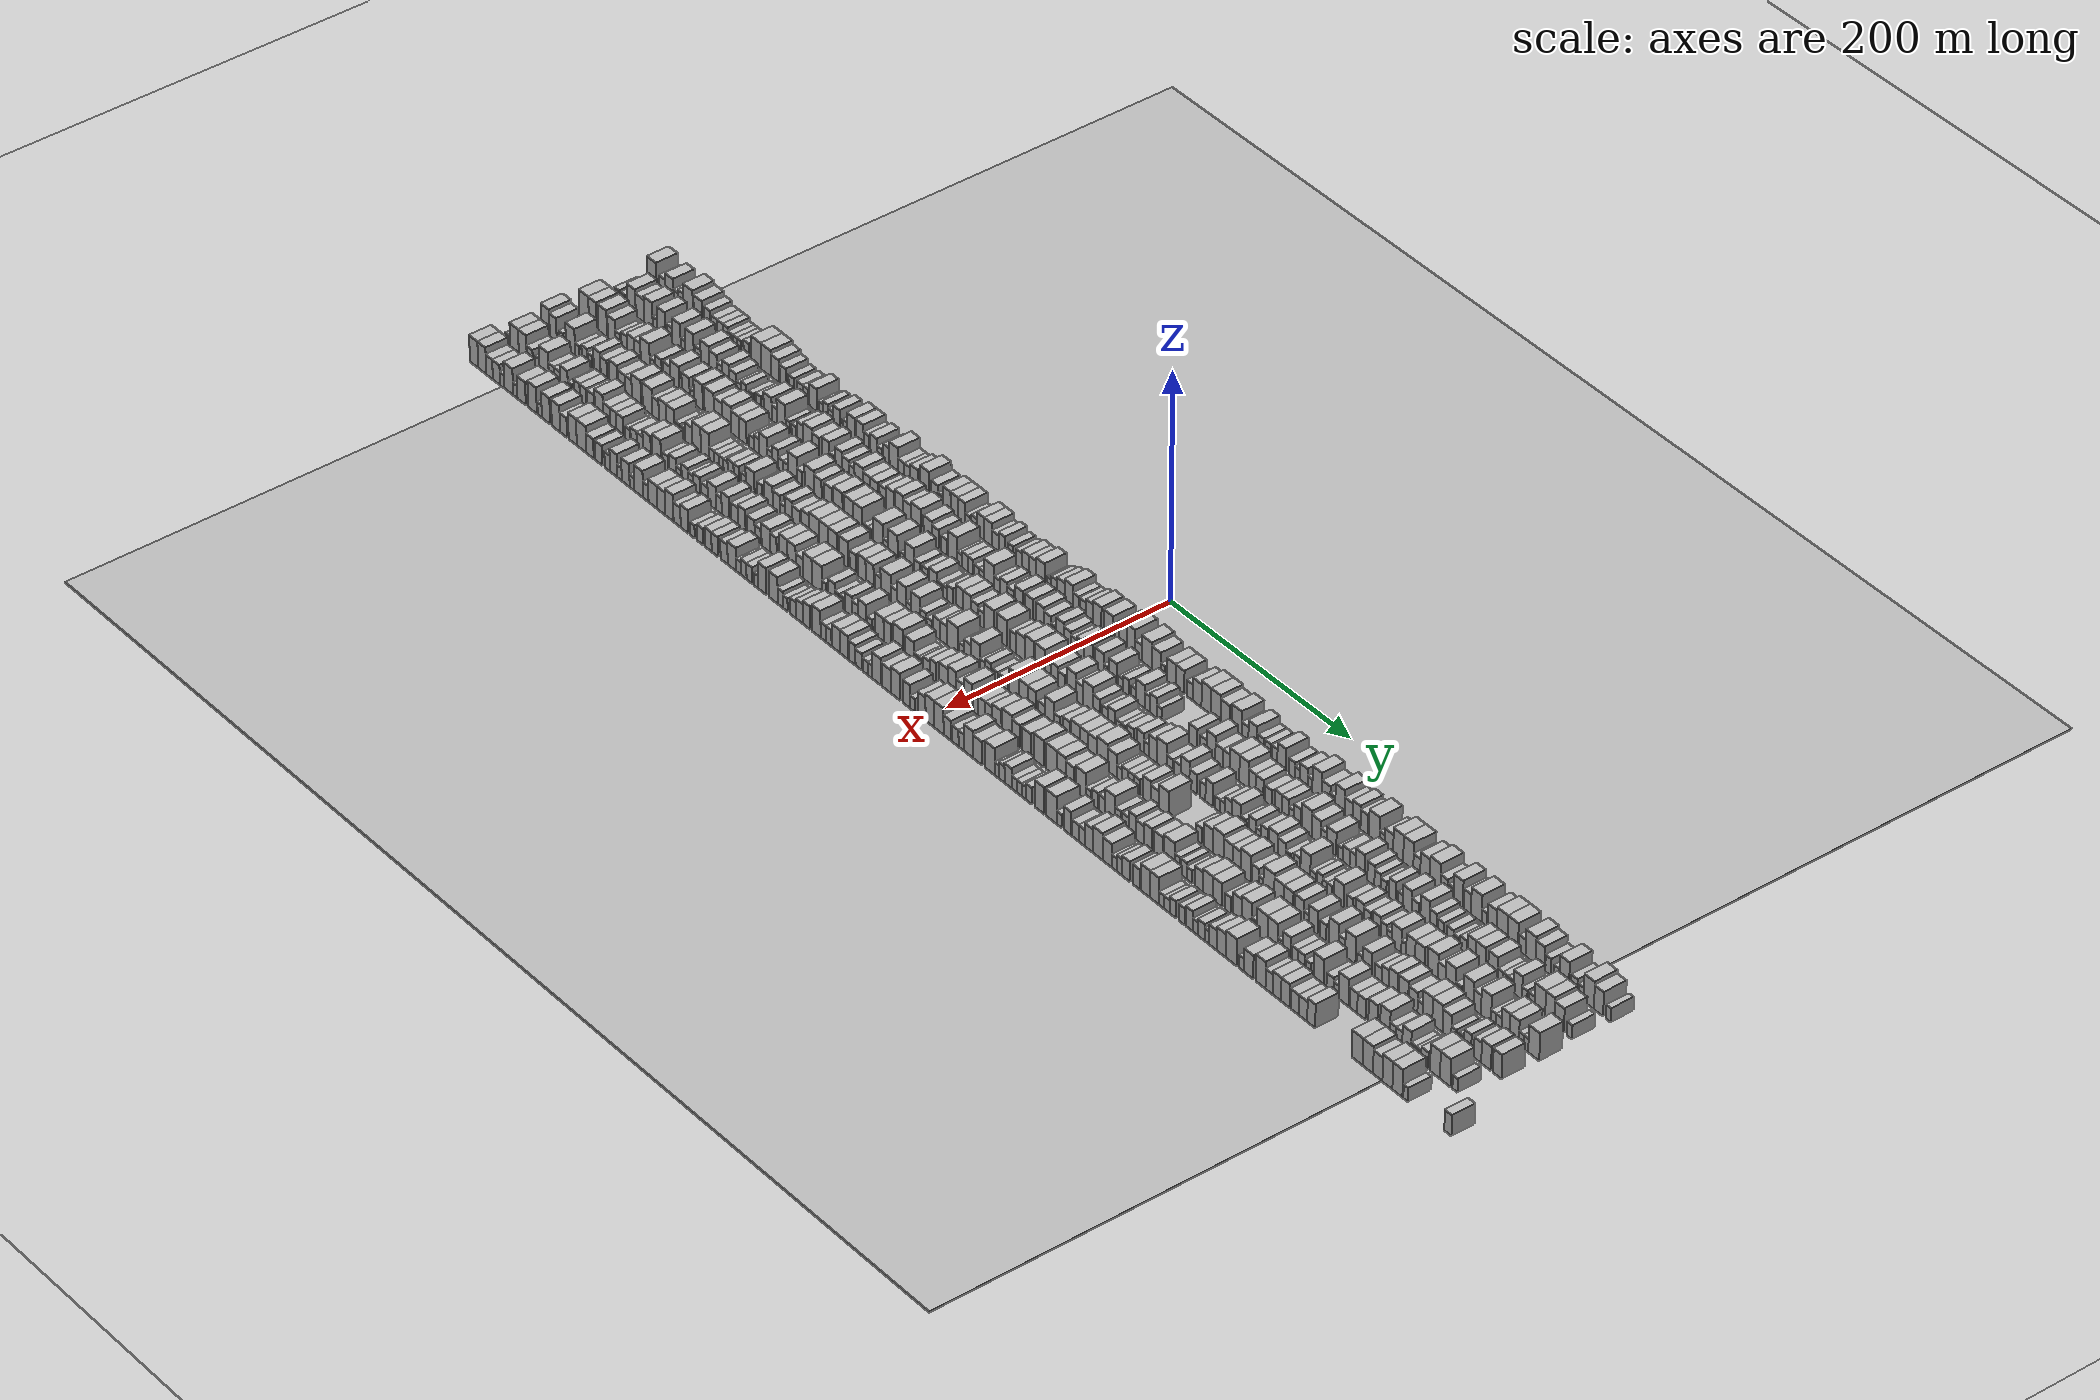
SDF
<?xml version="1.0" encoding="utf-8"?>

<sdf version="1.6">

   <world name="default">

      <gui fullscreen="0">

         <camera name="user_camera">

            <pose>-15 0 4.57585 0 0 0</pose>

            <view_controller>orbit</view_controller>

         </camera>

      </gui>

      <scene>

         <sky>

           <clouds>

             <speed>12</speed>

           </clouds>

         </sky>

         <ambient>0.4 0.4 0.4 1</ambient>

         <background>0.7 0.7 0.7 1</background>

         <shadows>1</shadows>

      </scene>

      <gravity>0 0 -9.8066</gravity>

      <magnetic_field>6e-06 2.3e-05 -4.2e-05</magnetic_field>

      <physics default="0" name="default_physics" type="ode">

         <ode>

            <solver>

               <type>quick</type>

               <iters>10</iters>

               <sor>1.0</sor>

               <use_dynamic_moi_rescaling>0</use_dynamic_moi_rescaling>

            </solver>

            <constraints>

               <cfm>0</cfm>

               <erp>0.2</erp>

               <contact_max_correcting_vel>100</contact_max_correcting_vel>

               <contact_surface_layer>0.001</contact_surface_layer>

            </constraints>

         </ode>

         <max_step_size>0.004</max_step_size>

         <real_time_factor>1</real_time_factor>

         <real_time_update_rate>250</real_time_update_rate>

      </physics>

      <light name="sun" type="directional">

         <cast_shadows>1</cast_shadows>

         <pose>0 0 10 0 0 0</pose>

         <diffuse>0.8 0.8 0.8 1</diffuse>

         <specular>0.2 0.2 0.2 1</specular>

         <attenuation>

            <range>1000</range>

            <constant>0.9</constant>

            <linear>0.01</linear>

            <quadratic>0.001</quadratic>

         </attenuation>

         <direction>-0.5 0.1 -0.9</direction>

      </light>

      <include>

         <name>ground_plane_1</name>

         <uri>model://HANNAS_ground_plane</uri>

         <pose>0 0 0  0 0 0</pose>

      </include>

      <include>

         <name>ground_plane_2</name>

         <uri>model://HANNAS_ground_plane</uri>

         <pose>100 0 0  0 0 0</pose>

      </include>

      <model name="building_1">

         <static>1</static>

         <pose frame="">50.0000 -534.3825 0 0.000000 0.000000 0.000000</pose>

         <link name="link">

            <pose frame="">0 0 12.00 0 0 0</pose>

            <collision name="collision">

               <geometry>

                  <box>

                     <size>20.0000 11.2351 24.0000</size>

                  </box>

               </geometry>

               <max_contacts>10</max_contacts>

               <surface>

                  <contact>

                     <ode/>

                  </contact>

                  <bounce/>

                  <friction>

                     <torsional>

                        <ode/>

                     </torsional>

                     <ode/>

                  </friction>

               </surface>

            </collision>

            <visual name="visual">

               <cast_shadows>0</cast_shadows>

               <geometry>

                  <box>

                     <size>20.0000 11.2351 24.0000</size>

                  </box>

               </geometry>

               <material>

                  <script>

                     <uri>model://HANNAS_wall/materials/scripts</uri>

                     <uri>model://HANNAS_wall/materials/textures</uri>

                     <name>vrc/HANNAS_wall</name>

                  </script>

               </material>

            </visual>

            <self_collide>0</self_collide>

            <enable_wind>0</enable_wind>

            <kinematic>0</kinematic>

         </link>

      </model>

      <model name="building_2">

         <static>1</static>

         <pose frame="">50.0000 -522.0917 0 0.000000 0.000000 0.000000</pose>

         <link name="link">

            <pose frame="">0 0 7.50 0 0 0</pose>

            <collision name="collision">

               <geometry>

                  <box>

                     <size>20.0000 7.3464 15.0000</size>

                  </box>

               </geometry>

               <max_contacts>10</max_contacts>

               <surface>

                  <contact>

                     <ode/>

                  </contact>

                  <bounce/>

                  <friction>

                     <torsional>

                        <ode/>

                     </torsional>

                     <ode/>

                  </friction>

               </surface>

            </collision>

            <visual name="visual">

               <cast_shadows>0</cast_shadows>

               <geometry>

                  <box>

                     <size>20.0000 7.3464 15.0000</size>

                  </box>

               </geometry>

               <material>

                  <script>

                     <uri>model://HANNAS_wall/materials/scripts</uri>

                     <uri>model://HANNAS_wall/materials/textures</uri>

                     <name>vrc/HANNAS_wall</name>

                  </script>

               </material>

            </visual>

            <self_collide>0</self_collide>

            <enable_wind>0</enable_wind>

            <kinematic>0</kinematic>

         </link>

      </model>

      <model name="building_3">

         <static>1</static>

         <pose frame="">50.0000 -513.3601 0 0.000000 0.000000 0.000000</pose>

         <link name="link">

            <pose frame="">0 0 10.50 0 0 0</pose>

            <collision name="collision">

               <geometry>

                  <box>

                     <size>20.0000 10.1168 21.0000</size>

                  </box>

               </geometry>

               <max_contacts>10</max_contacts>

               <surface>

                  <contact>

                     <ode/>

                  </contact>

                  <bounce/>

                  <friction>

                     <torsional>

                        <ode/>

                     </torsional>

                     <ode/>

                  </friction>

               </surface>

            </collision>

            <visual name="visual">

               <cast_shadows>0</cast_shadows>

               <geometry>

                  <box>

                     <size>20.0000 10.1168 21.0000</size>

                  </box>

               </geometry>

               <material>

                  <script>

                     <uri>model://HANNAS_wall/materials/scripts</uri>

                     <uri>model://HANNAS_wall/materials/textures</uri>

                     <name>vrc/HANNAS_wall</name>

                  </script>

               </material>

            </visual>

            <self_collide>0</self_collide>

            <enable_wind>0</enable_wind>

            <kinematic>0</kinematic>

         </link>

      </model>

      <model name="building_4">

         <static>1</static>

         <pose frame="">50.0000 -505.3508 0 0.000000 0.000000 0.000000</pose>

         <link name="link">

            <pose frame="">0 0 6.00 0 0 0</pose>

            <collision name="collision">

               <geometry>

                  <box>

                     <size>20.0000 5.9018 12.0000</size>

                  </box>

               </geometry>

               <max_contacts>10</max_contacts>

               <surface>

                  <contact>

                     <ode/>

                  </contact>

                  <bounce/>

                  <friction>

                     <torsional>

                        <ode/>

                     </torsional>

                     <ode/>

                  </friction>

               </surface>

            </collision>

            <visual name="visual">

               <cast_shadows>0</cast_shadows>

               <geometry>

                  <box>

                     <size>20.0000 5.9018 12.0000</size>

                  </box>

               </geometry>

               <material>

                  <script>

                     <uri>model://HANNAS_wall/materials/scripts</uri>

                     <uri>model://HANNAS_wall/materials/textures</uri>

                     <name>vrc/HANNAS_wall</name>

                  </script>

               </material>

            </visual>

            <self_collide>0</self_collide>

            <enable_wind>0</enable_wind>

            <kinematic>0</kinematic>

         </link>

      </model>

      <model name="building_5">

         <static>1</static>

         <pose frame="">50.0000 -499.2001 0 0.000000 0.000000 0.000000</pose>

         <link name="link">

            <pose frame="">0 0 7.50 0 0 0</pose>

            <collision name="collision">

               <geometry>

                  <box>

                     <size>20.0000 6.3995 15.0000</size>

                  </box>

               </geometry>

               <max_contacts>10</max_contacts>

               <surface>

                  <contact>

                     <ode/>

                  </contact>

                  <bounce/>

                  <friction>

                     <torsional>

                        <ode/>

                     </torsional>

                     <ode/>

                  </friction>

               </surface>

            </collision>

            <visual name="visual">

               <cast_shadows>0</cast_shadows>

               <geometry>

                  <box>

                     <size>20.0000 6.3995 15.0000</size>

                  </box>

               </geometry>

               <material>

                  <script>

                     <uri>model://HANNAS_wall/materials/scripts</uri>

                     <uri>model://HANNAS_wall/materials/textures</uri>

                     <name>vrc/HANNAS_wall</name>

                  </script>

               </material>

            </visual>

            <self_collide>0</self_collide>

            <enable_wind>0</enable_wind>

            <kinematic>0</kinematic>

         </link>

      </model>

      <model name="building_6">

         <static>1</static>

         <pose frame="">50.0000 -490.1335 0 0.000000 0.000000 0.000000</pose>

         <link name="link">

            <pose frame="">0 0 12.00 0 0 0</pose>

            <collision name="collision">

               <geometry>

                  <box>

                     <size>20.0000 11.7337 24.0000</size>

                  </box>

               </geometry>

               <max_contacts>10</max_contacts>

               <surface>

                  <contact>

                     <ode/>

                  </contact>

                  <bounce/>

                  <friction>

                     <torsional>

                        <ode/>

                     </torsional>

                     <ode/>

                  </friction>

               </surface>

            </collision>

            <visual name="visual">

               <cast_shadows>0</cast_shadows>

               <geometry>

                  <box>

                     <size>20.0000 11.7337 24.0000</size>

                  </box>

               </geometry>

               <material>

                  <script>

                     <uri>model://HANNAS_wall/materials/scripts</uri>

                     <uri>model://HANNAS_wall/materials/textures</uri>

                     <name>vrc/HANNAS_wall</name>

                  </script>

               </material>

            </visual>

            <self_collide>0</self_collide>

            <enable_wind>0</enable_wind>

            <kinematic>0</kinematic>

         </link>

      </model>

      <model name="building_7">

         <static>1</static>

         <pose frame="">50.0000 -478.0948 0 0.000000 0.000000 0.000000</pose>

         <link name="link">

            <pose frame="">0 0 10.50 0 0 0</pose>

            <collision name="collision">

               <geometry>

                  <box>

                     <size>20.0000 10.3437 21.0000</size>

                  </box>

               </geometry>

               <max_contacts>10</max_contacts>

               <surface>

                  <contact>

                     <ode/>

                  </contact>

                  <bounce/>

                  <friction>

                     <torsional>

                        <ode/>

                     </torsional>

                     <ode/>

                  </friction>

               </surface>

            </collision>

            <visual name="visual">

               <cast_shadows>0</cast_shadows>

               <geometry>

                  <box>

                     <size>20.0000 10.3437 21.0000</size>

                  </box>

               </geometry>

               <material>

                  <script>

                     <uri>model://HANNAS_wall/materials/scripts</uri>

                     <uri>model://HANNAS_wall/materials/textures</uri>

                     <name>vrc/HANNAS_wall</name>

                  </script>

               </material>

            </visual>

            <self_collide>0</self_collide>

            <enable_wind>0</enable_wind>

            <kinematic>0</kinematic>

         </link>

      </model>

      <model name="building_8">

         <static>1</static>

         <pose frame="">50.0000 -466.8338 0 0.000000 0.000000 0.000000</pose>

         <link name="link">

            <pose frame="">0 0 9.00 0 0 0</pose>

            <collision name="collision">

               <geometry>

                  <box>

                     <size>20.0000 8.1785 18.0000</size>

                  </box>

               </geometry>

               <max_contacts>10</max_contacts>

               <surface>

                  <contact>

                     <ode/>

                  </contact>

                  <bounce/>

                  <friction>

                     <torsional>

                        <ode/>

                     </torsional>

                     <ode/>

                  </friction>

               </surface>

            </collision>

            <visual name="visual">

               <cast_shadows>0</cast_shadows>

               <geometry>

                  <box>

                     <size>20.0000 8.1785 18.0000</size>

                  </box>

               </geometry>

               <material>

                  <script>

                     <uri>model://HANNAS_wall/materials/scripts</uri>

                     <uri>model://HANNAS_wall/materials/textures</uri>

                     <name>vrc/HANNAS_wall</name>

                  </script>

               </material>

            </visual>

            <self_collide>0</self_collide>

            <enable_wind>0</enable_wind>

            <kinematic>0</kinematic>

         </link>

      </model>

      <model name="building_9">

         <static>1</static>

         <pose frame="">50.0000 -458.1896 0 0.000000 0.000000 0.000000</pose>

         <link name="link">

            <pose frame="">0 0 7.50 0 0 0</pose>

            <collision name="collision">

               <geometry>

                  <box>

                     <size>20.0000 7.1099 15.0000</size>

                  </box>

               </geometry>

               <max_contacts>10</max_contacts>

               <surface>

                  <contact>

                     <ode/>

                  </contact>

                  <bounce/>

                  <friction>

                     <torsional>

                        <ode/>

                     </torsional>

                     <ode/>

                  </friction>

               </surface>

            </collision>

            <visual name="visual">

               <cast_shadows>0</cast_shadows>

               <geometry>

                  <box>

                     <size>20.0000 7.1099 15.0000</size>

                  </box>

               </geometry>

               <material>

                  <script>

                     <uri>model://HANNAS_wall/materials/scripts</uri>

                     <uri>model://HANNAS_wall/materials/textures</uri>

                     <name>vrc/HANNAS_wall</name>

                  </script>

               </material>

            </visual>

            <self_collide>0</self_collide>

            <enable_wind>0</enable_wind>

            <kinematic>0</kinematic>

         </link>

      </model>

      <model name="building_10">

         <static>1</static>

         <pose frame="">50.0000 -451.1590 0 0.000000 0.000000 0.000000</pose>

         <link name="link">

            <pose frame="">0 0 7.50 0 0 0</pose>

            <collision name="collision">

               <geometry>

                  <box>

                     <size>20.0000 6.9512 15.0000</size>

                  </box>

               </geometry>

               <max_contacts>10</max_contacts>

               <surface>

                  <contact>

                     <ode/>

                  </contact>

                  <bounce/>

                  <friction>

                     <torsional>

                        <ode/>

                     </torsional>

                     <ode/>

                  </friction>

               </surface>

            </collision>

            <visual name="visual">

               <cast_shadows>0</cast_shadows>

               <geometry>

                  <box>

                     <size>20.0000 6.9512 15.0000</size>

                  </box>

               </geometry>

               <material>

                  <script>

                     <uri>model://HANNAS_wall/materials/scripts</uri>

                     <uri>model://HANNAS_wall/materials/textures</uri>

                     <name>vrc/HANNAS_wall</name>

                  </script>

               </material>

            </visual>

            <self_collide>0</self_collide>

            <enable_wind>0</enable_wind>

            <kinematic>0</kinematic>

         </link>

      </model>

      <model name="building_11">

         <static>1</static>

         <pose frame="">50.0000 -444.6367 0 0.000000 0.000000 0.000000</pose>

         <link name="link">

            <pose frame="">0 0 7.50 0 0 0</pose>

            <collision name="collision">

               <geometry>

                  <box>

                     <size>20.0000 6.0934 15.0000</size>

                  </box>

               </geometry>

               <max_contacts>10</max_contacts>

               <surface>

                  <contact>

                     <ode/>

                  </contact>

                  <bounce/>

                  <friction>

                     <torsional>

                        <ode/>

                     </torsional>

                     <ode/>

                  </friction>

               </surface>

            </collision>

            <visual name="visual">

               <cast_shadows>0</cast_shadows>

               <geometry>

                  <box>

                     <size>20.0000 6.0934 15.0000</size>

                  </box>

               </geometry>

               <material>

                  <script>

                     <uri>model://HANNAS_wall/materials/scripts</uri>

                     <uri>model://HANNAS_wall/materials/textures</uri>

                     <name>vrc/HANNAS_wall</name>

                  </script>

               </material>

            </visual>

            <self_collide>0</self_collide>

            <enable_wind>0</enable_wind>

            <kinematic>0</kinematic>

         </link>

      </model>

      <model name="building_12">

         <static>1</static>

         <pose frame="">50.0000 -438.7081 0 0.000000 0.000000 0.000000</pose>

         <link name="link">

            <pose frame="">0 0 6.00 0 0 0</pose>

            <collision name="collision">

               <geometry>

                  <box>

                     <size>20.0000 5.7638 12.0000</size>

                  </box>

               </geometry>

               <max_contacts>10</max_contacts>

               <surface>

                  <contact>

                     <ode/>

                  </contact>

                  <bounce/>

                  <friction>

                     <torsional>

                        <ode/>

                     </torsional>

                     <ode/>

                  </friction>

               </surface>

            </collision>

            <visual name="visual">

               <cast_shadows>0</cast_shadows>

               <geometry>

                  <box>

                     <size>20.0000 5.7638 12.0000</size>

                  </box>

               </geometry>

               <material>

                  <script>

                     <uri>model://HANNAS_wall/materials/scripts</uri>

                     <uri>model://HANNAS_wall/materials/textures</uri>

                     <name>vrc/HANNAS_wall</name>

                  </script>

               </material>

            </visual>

            <self_collide>0</self_collide>

            <enable_wind>0</enable_wind>

            <kinematic>0</kinematic>

         </link>

      </model>

      <model name="building_13">

         <static>1</static>

         <pose frame="">50.0000 -433.3469 0 0.000000 0.000000 0.000000</pose>

         <link name="link">

            <pose frame="">0 0 6.00 0 0 0</pose>

            <collision name="collision">

               <geometry>

                  <box>

                     <size>20.0000 4.9587 12.0000</size>

                  </box>

               </geometry>

               <max_contacts>10</max_contacts>

               <surface>

                  <contact>

                     <ode/>

                  </contact>

                  <bounce/>

                  <friction>

                     <torsional>

                        <ode/>

                     </torsional>

                     <ode/>

                  </friction>

               </surface>

            </collision>

            <visual name="visual">

               <cast_shadows>0</cast_shadows>

               <geometry>

                  <box>

                     <size>20.0000 4.9587 12.0000</size>

                  </box>

               </geometry>

               <material>

                  <script>

                     <uri>model://HANNAS_wall/materials/scripts</uri>

                     <uri>model://HANNAS_wall/materials/textures</uri>

                     <name>vrc/HANNAS_wall</name>

                  </script>

               </material>

            </visual>

            <self_collide>0</self_collide>

            <enable_wind>0</enable_wind>

            <kinematic>0</kinematic>

         </link>

      </model>

      <model name="building_14">

         <static>1</static>

         <pose frame="">50.0000 -428.2487 0 0.000000 0.000000 0.000000</pose>

         <link name="link">

            <pose frame="">0 0 6.00 0 0 0</pose>

            <collision name="collision">

               <geometry>

                  <box>

                     <size>20.0000 5.2376 12.0000</size>

                  </box>

               </geometry>

               <max_contacts>10</max_contacts>

               <surface>

                  <contact>

                     <ode/>

                  </contact>

                  <bounce/>

                  <friction>

                     <torsional>

                        <ode/>

                     </torsional>

                     <ode/>

                  </friction>

               </surface>

            </collision>

            <visual name="visual">

               <cast_shadows>0</cast_shadows>

               <geometry>

                  <box>

                     <size>20.0000 5.2376 12.0000</size>

                  </box>

               </geometry>

               <material>

                  <script>

                     <uri>model://HANNAS_wall/materials/scripts</uri>

                     <uri>model://HANNAS_wall/materials/textures</uri>

                     <name>vrc/HANNAS_wall</name>

                  </script>

               </material>

            </visual>

            <self_collide>0</self_collide>

            <enable_wind>0</enable_wind>

            <kinematic>0</kinematic>

         </link>

      </model>

      <model name="building_15">

         <static>1</static>

         <pose frame="">50.0000 -419.3924 0 0.000000 0.000000 0.000000</pose>

         <link name="link">

            <pose frame="">0 0 7.50 0 0 0</pose>

            <collision name="collision">

               <geometry>

                  <box>

                     <size>20.0000 6.4750 15.0000</size>

                  </box>

               </geometry>

               <max_contacts>10</max_contacts>

               <surface>

                  <contact>

                     <ode/>

                  </contact>

                  <bounce/>

                  <friction>

                     <torsional>

                        <ode/>

                     </torsional>

                     <ode/>

                  </friction>

               </surface>

            </collision>

            <visual name="visual">

               <cast_shadows>0</cast_shadows>

               <geometry>

                  <box>

                     <size>20.0000 6.4750 15.0000</size>

                  </box>

               </geometry>

               <material>

                  <script>

                     <uri>model://HANNAS_wall/materials/scripts</uri>

                     <uri>model://HANNAS_wall/materials/textures</uri>

                     <name>vrc/HANNAS_wall</name>

                  </script>

               </material>

            </visual>

            <self_collide>0</self_collide>

            <enable_wind>0</enable_wind>

            <kinematic>0</kinematic>

         </link>

      </model>

      <model name="building_16">

         <static>1</static>

         <pose frame="">50.0000 -407.3200 0 0.000000 0.000000 0.000000</pose>

         <link name="link">

            <pose frame="">0 0 12.00 0 0 0</pose>

            <collision name="collision">

               <geometry>

                  <box>

                     <size>20.0000 11.6699 24.0000</size>

                  </box>

               </geometry>

               <max_contacts>10</max_contacts>

               <surface>

                  <contact>

                     <ode/>

                  </contact>

                  <bounce/>

                  <friction>

                     <torsional>

                        <ode/>

                     </torsional>

                     <ode/>

                  </friction>

               </surface>

            </collision>

            <visual name="visual">

               <cast_shadows>0</cast_shadows>

               <geometry>

                  <box>

                     <size>20.0000 11.6699 24.0000</size>

                  </box>

               </geometry>

               <material>

                  <script>

                     <uri>model://HANNAS_wall/materials/scripts</uri>

                     <uri>model://HANNAS_wall/materials/textures</uri>

                     <name>vrc/HANNAS_wall</name>

                  </script>

               </material>

            </visual>

            <self_collide>0</self_collide>

            <enable_wind>0</enable_wind>

            <kinematic>0</kinematic>

         </link>

      </model>

      <model name="building_17">

         <static>1</static>

         <pose frame="">50.0000 -395.5400 0 0.000000 0.000000 0.000000</pose>

         <link name="link">

            <pose frame="">0 0 12.00 0 0 0</pose>

            <collision name="collision">

               <geometry>

                  <box>

                     <size>20.0000 11.8899 24.0000</size>

                  </box>

               </geometry>

               <max_contacts>10</max_contacts>

               <surface>

                  <contact>

                     <ode/>

                  </contact>

                  <bounce/>

                  <friction>

                     <torsional>

                        <ode/>

                     </torsional>

                     <ode/>

                  </friction>

               </surface>

            </collision>

            <visual name="visual">

               <cast_shadows>0</cast_shadows>

               <geometry>

                  <box>

                     <size>20.0000 11.8899 24.0000</size>

                  </box>

               </geometry>

               <material>

                  <script>

                     <uri>model://HANNAS_wall/materials/scripts</uri>

                     <uri>model://HANNAS_wall/materials/textures</uri>

                     <name>vrc/HANNAS_wall</name>

                  </script>

               </material>

            </visual>

            <self_collide>0</self_collide>

            <enable_wind>0</enable_wind>

            <kinematic>0</kinematic>

         </link>

      </model>

      <model name="building_18">

         <static>1</static>

         <pose frame="">50.0000 -384.8482 0 0.000000 0.000000 0.000000</pose>

         <link name="link">

            <pose frame="">0 0 10.50 0 0 0</pose>

            <collision name="collision">

               <geometry>

                  <box>

                     <size>20.0000 9.4937 21.0000</size>

                  </box>

               </geometry>

               <max_contacts>10</max_contacts>

               <surface>

                  <contact>

                     <ode/>

                  </contact>

                  <bounce/>

                  <friction>

                     <torsional>

                        <ode/>

                     </torsional>

                     <ode/>

                  </friction>

               </surface>

            </collision>

            <visual name="visual">

               <cast_shadows>0</cast_shadows>

               <geometry>

                  <box>

                     <size>20.0000 9.4937 21.0000</size>

                  </box>

               </geometry>

               <material>

                  <script>

                     <uri>model://HANNAS_wall/materials/scripts</uri>

                     <uri>model://HANNAS_wall/materials/textures</uri>

                     <name>vrc/HANNAS_wall</name>

                  </script>

               </material>

            </visual>

            <self_collide>0</self_collide>

            <enable_wind>0</enable_wind>

            <kinematic>0</kinematic>

         </link>

      </model>

      <model name="building_19">

         <static>1</static>

         <pose frame="">50.0000 -375.2395 0 0.000000 0.000000 0.000000</pose>

         <link name="link">

            <pose frame="">0 0 9.00 0 0 0</pose>

            <collision name="collision">

               <geometry>

                  <box>

                     <size>20.0000 7.7238 18.0000</size>

                  </box>

               </geometry>

               <max_contacts>10</max_contacts>

               <surface>

                  <contact>

                     <ode/>

                  </contact>

                  <bounce/>

                  <friction>

                     <torsional>

                        <ode/>

                     </torsional>

                     <ode/>

                  </friction>

               </surface>

            </collision>

            <visual name="visual">

               <cast_shadows>0</cast_shadows>

               <geometry>

                  <box>

                     <size>20.0000 7.7238 18.0000</size>

                  </box>

               </geometry>

               <material>

                  <script>

                     <uri>model://HANNAS_wall/materials/scripts</uri>

                     <uri>model://HANNAS_wall/materials/textures</uri>

                     <name>vrc/HANNAS_wall</name>

                  </script>

               </material>

            </visual>

            <self_collide>0</self_collide>

            <enable_wind>0</enable_wind>

            <kinematic>0</kinematic>

         </link>

      </model>

      <model name="building_20">

         <static>1</static>

         <pose frame="">50.0000 -365.0089 0 0.000000 0.000000 0.000000</pose>

         <link name="link">

            <pose frame="">0 0 7.50 0 0 0</pose>

            <collision name="collision">

               <geometry>

                  <box>

                     <size>20.0000 6.7373 15.0000</size>

                  </box>

               </geometry>

               <max_contacts>10</max_contacts>

               <surface>

                  <contact>

                     <ode/>

                  </contact>

                  <bounce/>

                  <friction>

                     <torsional>

                        <ode/>

                     </torsional>

                     <ode/>

                  </friction>

               </surface>

            </collision>

            <visual name="visual">

               <cast_shadows>0</cast_shadows>

               <geometry>

                  <box>

                     <size>20.0000 6.7373 15.0000</size>

                  </box>

               </geometry>

               <material>

                  <script>

                     <uri>model://HANNAS_wall/materials/scripts</uri>

                     <uri>model://HANNAS_wall/materials/textures</uri>

                     <name>vrc/HANNAS_wall</name>

                  </script>

               </material>

            </visual>

            <self_collide>0</self_collide>

            <enable_wind>0</enable_wind>

            <kinematic>0</kinematic>

         </link>

      </model>

      <model name="building_21">

         <static>1</static>

         <pose frame="">50.0000 -355.0203 0 0.000000 0.000000 0.000000</pose>

         <link name="link">

            <pose frame="">0 0 7.50 0 0 0</pose>

            <collision name="collision">

               <geometry>

                  <box>

                     <size>20.0000 7.2400 15.0000</size>

                  </box>

               </geometry>

               <max_contacts>10</max_contacts>

               <surface>

                  <contact>

                     <ode/>

                  </contact>

                  <bounce/>

                  <friction>

                     <torsional>

                        <ode/>

                     </torsional>

                     <ode/>

                  </friction>

               </surface>

            </collision>

            <visual name="visual">

               <cast_shadows>0</cast_shadows>

               <geometry>

                  <box>

                     <size>20.0000 7.2400 15.0000</size>

                  </box>

               </geometry>

               <material>

                  <script>

                     <uri>model://HANNAS_wall/materials/scripts</uri>

                     <uri>model://HANNAS_wall/materials/textures</uri>

                     <name>vrc/HANNAS_wall</name>

                  </script>

               </material>

            </visual>

            <self_collide>0</self_collide>

            <enable_wind>0</enable_wind>

            <kinematic>0</kinematic>

         </link>

      </model>

      <model name="building_22">

         <static>1</static>

         <pose frame="">50.0000 -347.9140 0 0.000000 0.000000 0.000000</pose>

         <link name="link">

            <pose frame="">0 0 7.50 0 0 0</pose>

            <collision name="collision">

               <geometry>

                  <box>

                     <size>20.0000 6.9727 15.0000</size>

                  </box>

               </geometry>

               <max_contacts>10</max_contacts>

               <surface>

                  <contact>

                     <ode/>

                  </contact>

                  <bounce/>

                  <friction>

                     <torsional>

                        <ode/>

                     </torsional>

                     <ode/>

                  </friction>

               </surface>

            </collision>

            <visual name="visual">

               <cast_shadows>0</cast_shadows>

               <geometry>

                  <box>

                     <size>20.0000 6.9727 15.0000</size>

                  </box>

               </geometry>

               <material>

                  <script>

                     <uri>model://HANNAS_wall/materials/scripts</uri>

                     <uri>model://HANNAS_wall/materials/textures</uri>

                     <name>vrc/HANNAS_wall</name>

                  </script>

               </material>

            </visual>

            <self_collide>0</self_collide>

            <enable_wind>0</enable_wind>

            <kinematic>0</kinematic>

         </link>

      </model>

      <model name="building_23">

         <static>1</static>

         <pose frame="">50.0000 -338.9517 0 0.000000 0.000000 0.000000</pose>

         <link name="link">

            <pose frame="">0 0 10.50 0 0 0</pose>

            <collision name="collision">

               <geometry>

                  <box>

                     <size>20.0000 8.9519 21.0000</size>

                  </box>

               </geometry>

               <max_contacts>10</max_contacts>

               <surface>

                  <contact>

                     <ode/>

                  </contact>

                  <bounce/>

                  <friction>

                     <torsional>

                        <ode/>

                     </torsional>

                     <ode/>

                  </friction>

               </surface>

            </collision>

            <visual name="visual">

               <cast_shadows>0</cast_shadows>

               <geometry>

                  <box>

                     <size>20.0000 8.9519 21.0000</size>

                  </box>

               </geometry>

               <material>

                  <script>

                     <uri>model://HANNAS_wall/materials/scripts</uri>

                     <uri>model://HANNAS_wall/materials/textures</uri>

                     <name>vrc/HANNAS_wall</name>

                  </script>

               </material>

            </visual>

            <self_collide>0</self_collide>

            <enable_wind>0</enable_wind>

            <kinematic>0</kinematic>

         </link>

      </model>

      <model name="building_24">

         <static>1</static>

         <pose frame="">50.0000 -329.7547 0 0.000000 0.000000 0.000000</pose>

         <link name="link">

            <pose frame="">0 0 6.00 0 0 0</pose>

            <collision name="collision">

               <geometry>

                  <box>

                     <size>20.0000 5.4421 12.0000</size>

                  </box>

               </geometry>

               <max_contacts>10</max_contacts>

               <surface>

                  <contact>

                     <ode/>

                  </contact>

                  <bounce/>

                  <friction>

                     <torsional>

                        <ode/>

                     </torsional>

                     <ode/>

                  </friction>

               </surface>

            </collision>

            <visual name="visual">

               <cast_shadows>0</cast_shadows>

               <geometry>

                  <box>

                     <size>20.0000 5.4421 12.0000</size>

                  </box>

               </geometry>

               <material>

                  <script>

                     <uri>model://HANNAS_wall/materials/scripts</uri>

                     <uri>model://HANNAS_wall/materials/textures</uri>

                     <name>vrc/HANNAS_wall</name>

                  </script>

               </material>

            </visual>

            <self_collide>0</self_collide>

            <enable_wind>0</enable_wind>

            <kinematic>0</kinematic>

         </link>

      </model>

      <model name="building_25">

         <static>1</static>

         <pose frame="">50.0000 -323.9866 0 0.000000 0.000000 0.000000</pose>

         <link name="link">

            <pose frame="">0 0 7.50 0 0 0</pose>

            <collision name="collision">

               <geometry>

                  <box>

                     <size>20.0000 6.0940 15.0000</size>

                  </box>

               </geometry>

               <max_contacts>10</max_contacts>

               <surface>

                  <contact>

                     <ode/>

                  </contact>

                  <bounce/>

                  <friction>

                     <torsional>

                        <ode/>

                     </torsional>

                     <ode/>

                  </friction>

               </surface>

            </collision>

            <visual name="visual">

               <cast_shadows>0</cast_shadows>

               <geometry>

                  <box>

                     <size>20.0000 6.0940 15.0000</size>

                  </box>

               </geometry>

               <material>

                  <script>

                     <uri>model://HANNAS_wall/materials/scripts</uri>

                     <uri>model://HANNAS_wall/materials/textures</uri>

                     <name>vrc/HANNAS_wall</name>

                  </script>

               </material>

            </visual>

            <self_collide>0</self_collide>

            <enable_wind>0</enable_wind>

            <kinematic>0</kinematic>

         </link>

      </model>

      <model name="building_26">

         <static>1</static>

         <pose frame="">50.0000 -318.0767 0 0.000000 0.000000 0.000000</pose>

         <link name="link">

            <pose frame="">0 0 6.00 0 0 0</pose>

            <collision name="collision">

               <geometry>

                  <box>

                     <size>20.0000 5.7258 12.0000</size>

                  </box>

               </geometry>

               <max_contacts>10</max_contacts>

               <surface>

                  <contact>

                     <ode/>

                  </contact>

                  <bounce/>

                  <friction>

                     <torsional>

                        <ode/>

                     </torsional>

                     <ode/>

                  </friction>

               </surface>

            </collision>

            <visual name="visual">

               <cast_shadows>0</cast_shadows>

               <geometry>

                  <box>

                     <size>20.0000 5.7258 12.0000</size>

                  </box>

               </geometry>

               <material>

                  <script>

                     <uri>model://HANNAS_wall/materials/scripts</uri>

                     <uri>model://HANNAS_wall/materials/textures</uri>

                     <name>vrc/HANNAS_wall</name>

                  </script>

               </material>

            </visual>

            <self_collide>0</self_collide>

            <enable_wind>0</enable_wind>

            <kinematic>0</kinematic>

         </link>

      </model>

      <model name="building_27">

         <static>1</static>

         <pose frame="">50.0000 -311.0835 0 0.000000 0.000000 0.000000</pose>

         <link name="link">

            <pose frame="">0 0 9.00 0 0 0</pose>

            <collision name="collision">

               <geometry>

                  <box>

                     <size>20.0000 8.2607 18.0000</size>

                  </box>

               </geometry>

               <max_contacts>10</max_contacts>

               <surface>

                  <contact>

                     <ode/>

                  </contact>

                  <bounce/>

                  <friction>

                     <torsional>

                        <ode/>

                     </torsional>

                     <ode/>

                  </friction>

               </surface>

            </collision>

            <visual name="visual">

               <cast_shadows>0</cast_shadows>

               <geometry>

                  <box>

                     <size>20.0000 8.2607 18.0000</size>

                  </box>

               </geometry>

               <material>

                  <script>

                     <uri>model://HANNAS_wall/materials/scripts</uri>

                     <uri>model://HANNAS_wall/materials/textures</uri>

                     <name>vrc/HANNAS_wall</name>

                  </script>

               </material>

            </visual>

            <self_collide>0</self_collide>

            <enable_wind>0</enable_wind>

            <kinematic>0</kinematic>

         </link>

      </model>

      <model name="building_28">

         <static>1</static>

         <pose frame="">50.0000 -301.3533 0 0.000000 0.000000 0.000000</pose>

         <link name="link">

            <pose frame="">0 0 6.00 0 0 0</pose>

            <collision name="collision">

               <geometry>

                  <box>

                     <size>20.0000 5.1997 12.0000</size>

                  </box>

               </geometry>

               <max_contacts>10</max_contacts>

               <surface>

                  <contact>

                     <ode/>

                  </contact>

                  <bounce/>

                  <friction>

                     <torsional>

                        <ode/>

                     </torsional>

                     <ode/>

                  </friction>

               </surface>

            </collision>

            <visual name="visual">

               <cast_shadows>0</cast_shadows>

               <geometry>

                  <box>

                     <size>20.0000 5.1997 12.0000</size>

                  </box>

               </geometry>

               <material>

                  <script>

                     <uri>model://HANNAS_wall/materials/scripts</uri>

                     <uri>model://HANNAS_wall/materials/textures</uri>

                     <name>vrc/HANNAS_wall</name>

                  </script>

               </material>

            </visual>

            <self_collide>0</self_collide>

            <enable_wind>0</enable_wind>

            <kinematic>0</kinematic>

         </link>

      </model>

      <model name="building_29">

         <static>1</static>

         <pose frame="">50.0000 -293.9891 0 0.000000 0.000000 0.000000</pose>

         <link name="link">

            <pose frame="">0 0 10.50 0 0 0</pose>

            <collision name="collision">

               <geometry>

                  <box>

                     <size>20.0000 9.5287 21.0000</size>

                  </box>

               </geometry>

               <max_contacts>10</max_contacts>

               <surface>

                  <contact>

                     <ode/>

                  </contact>

                  <bounce/>

                  <friction>

                     <torsional>

                        <ode/>

                     </torsional>

                     <ode/>

                  </friction>

               </surface>

            </collision>

            <visual name="visual">

               <cast_shadows>0</cast_shadows>

               <geometry>

                  <box>

                     <size>20.0000 9.5287 21.0000</size>

                  </box>

               </geometry>

               <material>

                  <script>

                     <uri>model://HANNAS_wall/materials/scripts</uri>

                     <uri>model://HANNAS_wall/materials/textures</uri>

                     <name>vrc/HANNAS_wall</name>

                  </script>

               </material>

            </visual>

            <self_collide>0</self_collide>

            <enable_wind>0</enable_wind>

            <kinematic>0</kinematic>

         </link>

      </model>

      <model name="building_30">

         <static>1</static>

         <pose frame="">50.0000 -283.5918 0 0.000000 0.000000 0.000000</pose>

         <link name="link">

            <pose frame="">0 0 10.50 0 0 0</pose>

            <collision name="collision">

               <geometry>

                  <box>

                     <size>20.0000 9.2658 21.0000</size>

                  </box>

               </geometry>

               <max_contacts>10</max_contacts>

               <surface>

                  <contact>

                     <ode/>

                  </contact>

                  <bounce/>

                  <friction>

                     <torsional>

                        <ode/>

                     </torsional>

                     <ode/>

                  </friction>

               </surface>

            </collision>

            <visual name="visual">

               <cast_shadows>0</cast_shadows>

               <geometry>

                  <box>

                     <size>20.0000 9.2658 21.0000</size>

                  </box>

               </geometry>

               <material>

                  <script>

                     <uri>model://HANNAS_wall/materials/scripts</uri>

                     <uri>model://HANNAS_wall/materials/textures</uri>

                     <name>vrc/HANNAS_wall</name>

                  </script>

               </material>

            </visual>

            <self_collide>0</self_collide>

            <enable_wind>0</enable_wind>

            <kinematic>0</kinematic>

         </link>

      </model>

      <model name="building_31">

         <static>1</static>

         <pose frame="">50.0000 -275.7201 0 0.000000 0.000000 0.000000</pose>

         <link name="link">

            <pose frame="">0 0 7.50 0 0 0</pose>

            <collision name="collision">

               <geometry>

                  <box>

                     <size>20.0000 6.4776 15.0000</size>

                  </box>

               </geometry>

               <max_contacts>10</max_contacts>

               <surface>

                  <contact>

                     <ode/>

                  </contact>

                  <bounce/>

                  <friction>

                     <torsional>

                        <ode/>

                     </torsional>

                     <ode/>

                  </friction>

               </surface>

            </collision>

            <visual name="visual">

               <cast_shadows>0</cast_shadows>

               <geometry>

                  <box>

                     <size>20.0000 6.4776 15.0000</size>

                  </box>

               </geometry>

               <material>

                  <script>

                     <uri>model://HANNAS_wall/materials/scripts</uri>

                     <uri>model://HANNAS_wall/materials/textures</uri>

                     <name>vrc/HANNAS_wall</name>

                  </script>

               </material>

            </visual>

            <self_collide>0</self_collide>

            <enable_wind>0</enable_wind>

            <kinematic>0</kinematic>

         </link>

      </model>

      <model name="building_32">

         <static>1</static>

         <pose frame="">50.0000 -267.2023 0 0.000000 0.000000 0.000000</pose>

         <link name="link">

            <pose frame="">0 0 9.00 0 0 0</pose>

            <collision name="collision">

               <geometry>

                  <box>

                     <size>20.0000 8.5581 18.0000</size>

                  </box>

               </geometry>

               <max_contacts>10</max_contacts>

               <surface>

                  <contact>

                     <ode/>

                  </contact>

                  <bounce/>

                  <friction>

                     <torsional>

                        <ode/>

                     </torsional>

                     <ode/>

                  </friction>

               </surface>

            </collision>

            <visual name="visual">

               <cast_shadows>0</cast_shadows>

               <geometry>

                  <box>

                     <size>20.0000 8.5581 18.0000</size>

                  </box>

               </geometry>

               <material>

                  <script>

                     <uri>model://HANNAS_wall/materials/scripts</uri>

                     <uri>model://HANNAS_wall/materials/textures</uri>

                     <name>vrc/HANNAS_wall</name>

                  </script>

               </material>

            </visual>

            <self_collide>0</self_collide>

            <enable_wind>0</enable_wind>

            <kinematic>0</kinematic>

         </link>

      </model>

      <model name="building_33">

         <static>1</static>

         <pose frame="">50.0000 -260.3371 0 0.000000 0.000000 0.000000</pose>

         <link name="link">

            <pose frame="">0 0 6.00 0 0 0</pose>

            <collision name="collision">

               <geometry>

                  <box>

                     <size>20.0000 5.1723 12.0000</size>

                  </box>

               </geometry>

               <max_contacts>10</max_contacts>

               <surface>

                  <contact>

                     <ode/>

                  </contact>

                  <bounce/>

                  <friction>

                     <torsional>

                        <ode/>

                     </torsional>

                     <ode/>

                  </friction>

               </surface>

            </collision>

            <visual name="visual">

               <cast_shadows>0</cast_shadows>

               <geometry>

                  <box>

                     <size>20.0000 5.1723 12.0000</size>

                  </box>

               </geometry>

               <material>

                  <script>

                     <uri>model://HANNAS_wall/materials/scripts</uri>

                     <uri>model://HANNAS_wall/materials/textures</uri>

                     <name>vrc/HANNAS_wall</name>

                  </script>

               </material>

            </visual>

            <self_collide>0</self_collide>

            <enable_wind>0</enable_wind>

            <kinematic>0</kinematic>

         </link>

      </model>

      <model name="building_34">

         <static>1</static>

         <pose frame="">50.0000 -252.0818 0 0.000000 0.000000 0.000000</pose>

         <link name="link">

            <pose frame="">0 0 9.00 0 0 0</pose>

            <collision name="collision">

               <geometry>

                  <box>

                     <size>20.0000 7.3382 18.0000</size>

                  </box>

               </geometry>

               <max_contacts>10</max_contacts>

               <surface>

                  <contact>

                     <ode/>

                  </contact>

                  <bounce/>

                  <friction>

                     <torsional>

                        <ode/>

                     </torsional>

                     <ode/>

                  </friction>

               </surface>

            </collision>

            <visual name="visual">

               <cast_shadows>0</cast_shadows>

               <geometry>

                  <box>

                     <size>20.0000 7.3382 18.0000</size>

                  </box>

               </geometry>

               <material>

                  <script>

                     <uri>model://HANNAS_wall/materials/scripts</uri>

                     <uri>model://HANNAS_wall/materials/textures</uri>

                     <name>vrc/HANNAS_wall</name>

                  </script>

               </material>

            </visual>

            <self_collide>0</self_collide>

            <enable_wind>0</enable_wind>

            <kinematic>0</kinematic>

         </link>

      </model>

      <model name="building_35">

         <static>1</static>

         <pose frame="">50.0000 -243.3504 0 0.000000 0.000000 0.000000</pose>

         <link name="link">

            <pose frame="">0 0 12.00 0 0 0</pose>

            <collision name="collision">

               <geometry>

                  <box>

                     <size>20.0000 10.1246 24.0000</size>

                  </box>

               </geometry>

               <max_contacts>10</max_contacts>

               <surface>

                  <contact>

                     <ode/>

                  </contact>

                  <bounce/>

                  <friction>

                     <torsional>

                        <ode/>

                     </torsional>

                     <ode/>

                  </friction>

               </surface>

            </collision>

            <visual name="visual">

               <cast_shadows>0</cast_shadows>

               <geometry>

                  <box>

                     <size>20.0000 10.1246 24.0000</size>

                  </box>

               </geometry>

               <material>

                  <script>

                     <uri>model://HANNAS_wall/materials/scripts</uri>

                     <uri>model://HANNAS_wall/materials/textures</uri>

                     <name>vrc/HANNAS_wall</name>

                  </script>

               </material>

            </visual>

            <self_collide>0</self_collide>

            <enable_wind>0</enable_wind>

            <kinematic>0</kinematic>

         </link>

      </model>

      <model name="building_36">

         <static>1</static>

         <pose frame="">50.0000 -234.6135 0 0.000000 0.000000 0.000000</pose>

         <link name="link">

            <pose frame="">0 0 7.50 0 0 0</pose>

            <collision name="collision">

               <geometry>

                  <box>

                     <size>20.0000 7.3493 15.0000</size>

                  </box>

               </geometry>

               <max_contacts>10</max_contacts>

               <surface>

                  <contact>

                     <ode/>

                  </contact>

                  <bounce/>

                  <friction>

                     <torsional>

                        <ode/>

                     </torsional>

                     <ode/>

                  </friction>

               </surface>

            </collision>

            <visual name="visual">

               <cast_shadows>0</cast_shadows>

               <geometry>

                  <box>

                     <size>20.0000 7.3493 15.0000</size>

                  </box>

               </geometry>

               <material>

                  <script>

                     <uri>model://HANNAS_wall/materials/scripts</uri>

                     <uri>model://HANNAS_wall/materials/textures</uri>

                     <name>vrc/HANNAS_wall</name>

                  </script>

               </material>

            </visual>

            <self_collide>0</self_collide>

            <enable_wind>0</enable_wind>

            <kinematic>0</kinematic>

         </link>

      </model>

      <model name="building_37">

         <static>1</static>

         <pose frame="">50.0000 -227.8699 0 0.000000 0.000000 0.000000</pose>

         <link name="link">

            <pose frame="">0 0 7.50 0 0 0</pose>

            <collision name="collision">

               <geometry>

                  <box>

                     <size>20.0000 6.1378 15.0000</size>

                  </box>

               </geometry>

               <max_contacts>10</max_contacts>

               <surface>

                  <contact>

                     <ode/>

                  </contact>

                  <bounce/>

                  <friction>

                     <torsional>

                        <ode/>

                     </torsional>

                     <ode/>

                  </friction>

               </surface>

            </collision>

            <visual name="visual">

               <cast_shadows>0</cast_shadows>

               <geometry>

                  <box>

                     <size>20.0000 6.1378 15.0000</size>

                  </box>

               </geometry>

               <material>

                  <script>

                     <uri>model://HANNAS_wall/materials/scripts</uri>

                     <uri>model://HANNAS_wall/materials/textures</uri>

                     <name>vrc/HANNAS_wall</name>

                  </script>

               </material>

            </visual>

            <self_collide>0</self_collide>

            <enable_wind>0</enable_wind>

            <kinematic>0</kinematic>

         </link>

      </model>

      <model name="building_38">

         <static>1</static>

         <pose frame="">50.0000 -219.4275 0 0.000000 0.000000 0.000000</pose>

         <link name="link">

            <pose frame="">0 0 9.00 0 0 0</pose>

            <collision name="collision">

               <geometry>

                  <box>

                     <size>20.0000 8.7472 18.0000</size>

                  </box>

               </geometry>

               <max_contacts>10</max_contacts>

               <surface>

                  <contact>

                     <ode/>

                  </contact>

                  <bounce/>

                  <friction>

                     <torsional>

                        <ode/>

                     </torsional>

                     <ode/>

                  </friction>

               </surface>

            </collision>

            <visual name="visual">

               <cast_shadows>0</cast_shadows>

               <geometry>

                  <box>

                     <size>20.0000 8.7472 18.0000</size>

                  </box>

               </geometry>

               <material>

                  <script>

                     <uri>model://HANNAS_wall/materials/scripts</uri>

                     <uri>model://HANNAS_wall/materials/textures</uri>

                     <name>vrc/HANNAS_wall</name>

                  </script>

               </material>

            </visual>

            <self_collide>0</self_collide>

            <enable_wind>0</enable_wind>

            <kinematic>0</kinematic>

         </link>

      </model>

      <model name="building_39">

         <static>1</static>

         <pose frame="">50.0000 -206.8261 0 0.000000 0.000000 0.000000</pose>

         <link name="link">

            <pose frame="">0 0 12.00 0 0 0</pose>

            <collision name="collision">

               <geometry>

                  <box>

                     <size>20.0000 10.4555 24.0000</size>

                  </box>

               </geometry>

               <max_contacts>10</max_contacts>

               <surface>

                  <contact>

                     <ode/>

                  </contact>

                  <bounce/>

                  <friction>

                     <torsional>

                        <ode/>

                     </torsional>

                     <ode/>

                  </friction>

               </surface>

            </collision>

            <visual name="visual">

               <cast_shadows>0</cast_shadows>

               <geometry>

                  <box>

                     <size>20.0000 10.4555 24.0000</size>

                  </box>

               </geometry>

               <material>

                  <script>

                     <uri>model://HANNAS_wall/materials/scripts</uri>

                     <uri>model://HANNAS_wall/materials/textures</uri>

                     <name>vrc/HANNAS_wall</name>

                  </script>

               </material>

            </visual>

            <self_collide>0</self_collide>

            <enable_wind>0</enable_wind>

            <kinematic>0</kinematic>

         </link>

      </model>

      <model name="building_40">

         <static>1</static>

         <pose frame="">50.0000 -195.4570 0 0.000000 0.000000 0.000000</pose>

         <link name="link">

            <pose frame="">0 0 9.00 0 0 0</pose>

            <collision name="collision">

               <geometry>

                  <box>

                     <size>20.0000 8.2828 18.0000</size>

                  </box>

               </geometry>

               <max_contacts>10</max_contacts>

               <surface>

                  <contact>

                     <ode/>

                  </contact>

                  <bounce/>

                  <friction>

                     <torsional>

                        <ode/>

                     </torsional>

                     <ode/>

                  </friction>

               </surface>

            </collision>

            <visual name="visual">

               <cast_shadows>0</cast_shadows>

               <geometry>

                  <box>

                     <size>20.0000 8.2828 18.0000</size>

                  </box>

               </geometry>

               <material>

                  <script>

                     <uri>model://HANNAS_wall/materials/scripts</uri>

                     <uri>model://HANNAS_wall/materials/textures</uri>

                     <name>vrc/HANNAS_wall</name>

                  </script>

               </material>

            </visual>

            <self_collide>0</self_collide>

            <enable_wind>0</enable_wind>

            <kinematic>0</kinematic>

         </link>

      </model>

      <model name="building_41">

         <static>1</static>

         <pose frame="">50.0000 -188.6431 0 0.000000 0.000000 0.000000</pose>

         <link name="link">

            <pose frame="">0 0 6.00 0 0 0</pose>

            <collision name="collision">

               <geometry>

                  <box>

                     <size>20.0000 5.3450 12.0000</size>

                  </box>

               </geometry>

               <max_contacts>10</max_contacts>

               <surface>

                  <contact>

                     <ode/>

                  </contact>

                  <bounce/>

                  <friction>

                     <torsional>

                        <ode/>

                     </torsional>

                     <ode/>

                  </friction>

               </surface>

            </collision>

            <visual name="visual">

               <cast_shadows>0</cast_shadows>

               <geometry>

                  <box>

                     <size>20.0000 5.3450 12.0000</size>

                  </box>

               </geometry>

               <material>

                  <script>

                     <uri>model://HANNAS_wall/materials/scripts</uri>

                     <uri>model://HANNAS_wall/materials/textures</uri>

                     <name>vrc/HANNAS_wall</name>

                  </script>

               </material>

            </visual>

            <self_collide>0</self_collide>

            <enable_wind>0</enable_wind>

            <kinematic>0</kinematic>

         </link>

      </model>

      <model name="building_42">

         <static>1</static>

         <pose frame="">50.0000 -181.4377 0 0.000000 0.000000 0.000000</pose>

         <link name="link">

            <pose frame="">0 0 10.50 0 0 0</pose>

            <collision name="collision">

               <geometry>

                  <box>

                     <size>20.0000 9.0657 21.0000</size>

                  </box>

               </geometry>

               <max_contacts>10</max_contacts>

               <surface>

                  <contact>

                     <ode/>

                  </contact>

                  <bounce/>

                  <friction>

                     <torsional>

                        <ode/>

                     </torsional>

                     <ode/>

                  </friction>

               </surface>

            </collision>

            <visual name="visual">

               <cast_shadows>0</cast_shadows>

               <geometry>

                  <box>

                     <size>20.0000 9.0657 21.0000</size>

                  </box>

               </geometry>

               <material>

                  <script>

                     <uri>model://HANNAS_wall/materials/scripts</uri>

                     <uri>model://HANNAS_wall/materials/textures</uri>

                     <name>vrc/HANNAS_wall</name>

                  </script>

               </material>

            </visual>

            <self_collide>0</self_collide>

            <enable_wind>0</enable_wind>

            <kinematic>0</kinematic>

         </link>

      </model>

      <model name="building_43">

         <static>1</static>

         <pose frame="">50.0000 -172.5675 0 0.000000 0.000000 0.000000</pose>

         <link name="link">

            <pose frame="">0 0 10.50 0 0 0</pose>

            <collision name="collision">

               <geometry>

                  <box>

                     <size>20.0000 8.6747 21.0000</size>

                  </box>

               </geometry>

               <max_contacts>10</max_contacts>

               <surface>

                  <contact>

                     <ode/>

                  </contact>

                  <bounce/>

                  <friction>

                     <torsional>

                        <ode/>

                     </torsional>

                     <ode/>

                  </friction>

               </surface>

            </collision>

            <visual name="visual">

               <cast_shadows>0</cast_shadows>

               <geometry>

                  <box>

                     <size>20.0000 8.6747 21.0000</size>

                  </box>

               </geometry>

               <material>

                  <script>

                     <uri>model://HANNAS_wall/materials/scripts</uri>

                     <uri>model://HANNAS_wall/materials/textures</uri>

                     <name>vrc/HANNAS_wall</name>

                  </script>

               </material>

            </visual>

            <self_collide>0</self_collide>

            <enable_wind>0</enable_wind>

            <kinematic>0</kinematic>

         </link>

      </model>

      <model name="building_44">

         <static>1</static>

         <pose frame="">50.0000 -163.9352 0 0.000000 0.000000 0.000000</pose>

         <link name="link">

            <pose frame="">0 0 10.50 0 0 0</pose>

            <collision name="collision">

               <geometry>

                  <box>

                     <size>20.0000 8.5899 21.0000</size>

                  </box>

               </geometry>

               <max_contacts>10</max_contacts>

               <surface>

                  <contact>

                     <ode/>

                  </contact>

                  <bounce/>

                  <friction>

                     <torsional>

                        <ode/>

                     </torsional>

                     <ode/>

                  </friction>

               </surface>

            </collision>

            <visual name="visual">

               <cast_shadows>0</cast_shadows>

               <geometry>

                  <box>

                     <size>20.0000 8.5899 21.0000</size>

                  </box>

               </geometry>

               <material>

                  <script>

                     <uri>model://HANNAS_wall/materials/scripts</uri>

                     <uri>model://HANNAS_wall/materials/textures</uri>

                     <name>vrc/HANNAS_wall</name>

                  </script>

               </material>

            </visual>

            <self_collide>0</self_collide>

            <enable_wind>0</enable_wind>

            <kinematic>0</kinematic>

         </link>

      </model>

      <model name="building_45">

         <static>1</static>

         <pose frame="">50.0000 -157.1829 0 0.000000 0.000000 0.000000</pose>

         <link name="link">

            <pose frame="">0 0 6.00 0 0 0</pose>

            <collision name="collision">

               <geometry>

                  <box>

                     <size>20.0000 4.9147 12.0000</size>

                  </box>

               </geometry>

               <max_contacts>10</max_contacts>

               <surface>

                  <contact>

                     <ode/>

                  </contact>

                  <bounce/>

                  <friction>

                     <torsional>

                        <ode/>

                     </torsional>

                     <ode/>

                  </friction>

               </surface>

            </collision>

            <visual name="visual">

               <cast_shadows>0</cast_shadows>

               <geometry>

                  <box>

                     <size>20.0000 4.9147 12.0000</size>

                  </box>

               </geometry>

               <material>

                  <script>

                     <uri>model://HANNAS_wall/materials/scripts</uri>

                     <uri>model://HANNAS_wall/materials/textures</uri>

                     <name>vrc/HANNAS_wall</name>

                  </script>

               </material>

            </visual>

            <self_collide>0</self_collide>

            <enable_wind>0</enable_wind>

            <kinematic>0</kinematic>

         </link>

      </model>

      <model name="building_46">

         <static>1</static>

         <pose frame="">50.0000 -149.4279 0 0.000000 0.000000 0.000000</pose>

         <link name="link">

            <pose frame="">0 0 7.50 0 0 0</pose>

            <collision name="collision">

               <geometry>

                  <box>

                     <size>20.0000 6.5952 15.0000</size>

                  </box>

               </geometry>

               <max_contacts>10</max_contacts>

               <surface>

                  <contact>

                     <ode/>

                  </contact>

                  <bounce/>

                  <friction>

                     <torsional>

                        <ode/>

                     </torsional>

                     <ode/>

                  </friction>

               </surface>

            </collision>

            <visual name="visual">

               <cast_shadows>0</cast_shadows>

               <geometry>

                  <box>

                     <size>20.0000 6.5952 15.0000</size>

                  </box>

               </geometry>

               <material>

                  <script>

                     <uri>model://HANNAS_wall/materials/scripts</uri>

                     <uri>model://HANNAS_wall/materials/textures</uri>

                     <name>vrc/HANNAS_wall</name>

                  </script>

               </material>

            </visual>

            <self_collide>0</self_collide>

            <enable_wind>0</enable_wind>

            <kinematic>0</kinematic>

         </link>

      </model>

      <model name="building_47">

         <static>1</static>

         <pose frame="">50.0000 -141.8846 0 0.000000 0.000000 0.000000</pose>

         <link name="link">

            <pose frame="">0 0 10.50 0 0 0</pose>

            <collision name="collision">

               <geometry>

                  <box>

                     <size>20.0000 8.4914 21.0000</size>

                  </box>

               </geometry>

               <max_contacts>10</max_contacts>

               <surface>

                  <contact>

                     <ode/>

                  </contact>

                  <bounce/>

                  <friction>

                     <torsional>

                        <ode/>

                     </torsional>

                     <ode/>

                  </friction>

               </surface>

            </collision>

            <visual name="visual">

               <cast_shadows>0</cast_shadows>

               <geometry>

                  <box>

                     <size>20.0000 8.4914 21.0000</size>

                  </box>

               </geometry>

               <material>

                  <script>

                     <uri>model://HANNAS_wall/materials/scripts</uri>

                     <uri>model://HANNAS_wall/materials/textures</uri>

                     <name>vrc/HANNAS_wall</name>

                  </script>

               </material>

            </visual>

            <self_collide>0</self_collide>

            <enable_wind>0</enable_wind>

            <kinematic>0</kinematic>

         </link>

      </model>

      <model name="building_48">

         <static>1</static>

         <pose frame="">50.0000 -133.1602 0 0.000000 0.000000 0.000000</pose>

         <link name="link">

            <pose frame="">0 0 10.50 0 0 0</pose>

            <collision name="collision">

               <geometry>

                  <box>

                     <size>20.0000 8.9574 21.0000</size>

                  </box>

               </geometry>

               <max_contacts>10</max_contacts>

               <surface>

                  <contact>

                     <ode/>

                  </contact>

                  <bounce/>

                  <friction>

                     <torsional>

                        <ode/>

                     </torsional>

                     <ode/>

                  </friction>

               </surface>

            </collision>

            <visual name="visual">

               <cast_shadows>0</cast_shadows>

               <geometry>

                  <box>

                     <size>20.0000 8.9574 21.0000</size>

                  </box>

               </geometry>

               <material>

                  <script>

                     <uri>model://HANNAS_wall/materials/scripts</uri>

                     <uri>model://HANNAS_wall/materials/textures</uri>

                     <name>vrc/HANNAS_wall</name>

                  </script>

               </material>

            </visual>

            <self_collide>0</self_collide>

            <enable_wind>0</enable_wind>

            <kinematic>0</kinematic>

         </link>

      </model>

      <model name="building_49">

         <static>1</static>

         <pose frame="">50.0000 -124.9397 0 0.000000 0.000000 0.000000</pose>

         <link name="link">

            <pose frame="">0 0 7.50 0 0 0</pose>

            <collision name="collision">

               <geometry>

                  <box>

                     <size>20.0000 7.4837 15.0000</size>

                  </box>

               </geometry>

               <max_contacts>10</max_contacts>

               <surface>

                  <contact>

                     <ode/>

                  </contact>

                  <bounce/>

                  <friction>

                     <torsional>

                        <ode/>

                     </torsional>

                     <ode/>

                  </friction>

               </surface>

            </collision>

            <visual name="visual">

               <cast_shadows>0</cast_shadows>

               <geometry>

                  <box>

                     <size>20.0000 7.4837 15.0000</size>

                  </box>

               </geometry>

               <material>

                  <script>

                     <uri>model://HANNAS_wall/materials/scripts</uri>

                     <uri>model://HANNAS_wall/materials/textures</uri>

                     <name>vrc/HANNAS_wall</name>

                  </script>

               </material>

            </visual>

            <self_collide>0</self_collide>

            <enable_wind>0</enable_wind>

            <kinematic>0</kinematic>

         </link>

      </model>

      <model name="building_50">

         <static>1</static>

         <pose frame="">50.0000 -117.5164 0 0.000000 0.000000 0.000000</pose>

         <link name="link">

            <pose frame="">0 0 9.00 0 0 0</pose>

            <collision name="collision">

               <geometry>

                  <box>

                     <size>20.0000 7.3629 18.0000</size>

                  </box>

               </geometry>

               <max_contacts>10</max_contacts>

               <surface>

                  <contact>

                     <ode/>

                  </contact>

                  <bounce/>

                  <friction>

                     <torsional>

                        <ode/>

                     </torsional>

                     <ode/>

                  </friction>

               </surface>

            </collision>

            <visual name="visual">

               <cast_shadows>0</cast_shadows>

               <geometry>

                  <box>

                     <size>20.0000 7.3629 18.0000</size>

                  </box>

               </geometry>

               <material>

                  <script>

                     <uri>model://HANNAS_wall/materials/scripts</uri>

                     <uri>model://HANNAS_wall/materials/textures</uri>

                     <name>vrc/HANNAS_wall</name>

                  </script>

               </material>

            </visual>

            <self_collide>0</self_collide>

            <enable_wind>0</enable_wind>

            <kinematic>0</kinematic>

         </link>

      </model>

      <model name="building_51">

         <static>1</static>

         <pose frame="">50.0000 -107.6121 0 0.000000 0.000000 0.000000</pose>

         <link name="link">

            <pose frame="">0 0 7.50 0 0 0</pose>

            <collision name="collision">

               <geometry>

                  <box>

                     <size>20.0000 6.4456 15.0000</size>

                  </box>

               </geometry>

               <max_contacts>10</max_contacts>

               <surface>

                  <contact>

                     <ode/>

                  </contact>

                  <bounce/>

                  <friction>

                     <torsional>

                        <ode/>

                     </torsional>

                     <ode/>

                  </friction>

               </surface>

            </collision>

            <visual name="visual">

               <cast_shadows>0</cast_shadows>

               <geometry>

                  <box>

                     <size>20.0000 6.4456 15.0000</size>

                  </box>

               </geometry>

               <material>

                  <script>

                     <uri>model://HANNAS_wall/materials/scripts</uri>

                     <uri>model://HANNAS_wall/materials/textures</uri>

                     <name>vrc/HANNAS_wall</name>

                  </script>

               </material>

            </visual>

            <self_collide>0</self_collide>

            <enable_wind>0</enable_wind>

            <kinematic>0</kinematic>

         </link>

      </model>

      <model name="building_52">

         <static>1</static>

         <pose frame="">50.0000 -97.7280 0 0.000000 0.000000 0.000000</pose>

         <link name="link">

            <pose frame="">0 0 7.50 0 0 0</pose>

            <collision name="collision">

               <geometry>

                  <box>

                     <size>20.0000 7.3226 15.0000</size>

                  </box>

               </geometry>

               <max_contacts>10</max_contacts>

               <surface>

                  <contact>

                     <ode/>

                  </contact>

                  <bounce/>

                  <friction>

                     <torsional>

                        <ode/>

                     </torsional>

                     <ode/>

                  </friction>

               </surface>

            </collision>

            <visual name="visual">

               <cast_shadows>0</cast_shadows>

               <geometry>

                  <box>

                     <size>20.0000 7.3226 15.0000</size>

                  </box>

               </geometry>

               <material>

                  <script>

                     <uri>model://HANNAS_wall/materials/scripts</uri>

                     <uri>model://HANNAS_wall/materials/textures</uri>

                     <name>vrc/HANNAS_wall</name>

                  </script>

               </material>

            </visual>

            <self_collide>0</self_collide>

            <enable_wind>0</enable_wind>

            <kinematic>0</kinematic>

         </link>

      </model>

      <model name="building_53">

         <static>1</static>

         <pose frame="">50.0000 -90.0425 0 0.000000 0.000000 0.000000</pose>

         <link name="link">

            <pose frame="">0 0 9.00 0 0 0</pose>

            <collision name="collision">

               <geometry>

                  <box>

                     <size>20.0000 8.0486 18.0000</size>

                  </box>

               </geometry>

               <max_contacts>10</max_contacts>

               <surface>

                  <contact>

                     <ode/>

                  </contact>

                  <bounce/>

                  <friction>

                     <torsional>

                        <ode/>

                     </torsional>

                     <ode/>

                  </friction>

               </surface>

            </collision>

            <visual name="visual">

               <cast_shadows>0</cast_shadows>

               <geometry>

                  <box>

                     <size>20.0000 8.0486 18.0000</size>

                  </box>

               </geometry>

               <material>

                  <script>

                     <uri>model://HANNAS_wall/materials/scripts</uri>

                     <uri>model://HANNAS_wall/materials/textures</uri>

                     <name>vrc/HANNAS_wall</name>

                  </script>

               </material>

            </visual>

            <self_collide>0</self_collide>

            <enable_wind>0</enable_wind>

            <kinematic>0</kinematic>

         </link>

      </model>

      <model name="building_54">

         <static>1</static>

         <pose frame="">50.0000 -81.9507 0 0.000000 0.000000 0.000000</pose>

         <link name="link">

            <pose frame="">0 0 9.00 0 0 0</pose>

            <collision name="collision">

               <geometry>

                  <box>

                     <size>20.0000 8.1349 18.0000</size>

                  </box>

               </geometry>

               <max_contacts>10</max_contacts>

               <surface>

                  <contact>

                     <ode/>

                  </contact>

                  <bounce/>

                  <friction>

                     <torsional>

                        <ode/>

                     </torsional>

                     <ode/>

                  </friction>

               </surface>

            </collision>

            <visual name="visual">

               <cast_shadows>0</cast_shadows>

               <geometry>

                  <box>

                     <size>20.0000 8.1349 18.0000</size>

                  </box>

               </geometry>

               <material>

                  <script>

                     <uri>model://HANNAS_wall/materials/scripts</uri>

                     <uri>model://HANNAS_wall/materials/textures</uri>

                     <name>vrc/HANNAS_wall</name>

                  </script>

               </material>

            </visual>

            <self_collide>0</self_collide>

            <enable_wind>0</enable_wind>

            <kinematic>0</kinematic>

         </link>

      </model>

      <model name="building_55">

         <static>1</static>

         <pose frame="">50.0000 -73.2040 0 0.000000 0.000000 0.000000</pose>

         <link name="link">

            <pose frame="">0 0 10.50 0 0 0</pose>

            <collision name="collision">

               <geometry>

                  <box>

                     <size>20.0000 9.3585 21.0000</size>

                  </box>

               </geometry>

               <max_contacts>10</max_contacts>

               <surface>

                  <contact>

                     <ode/>

                  </contact>

                  <bounce/>

                  <friction>

                     <torsional>

                        <ode/>

                     </torsional>

                     <ode/>

                  </friction>

               </surface>

            </collision>

            <visual name="visual">

               <cast_shadows>0</cast_shadows>

               <geometry>

                  <box>

                     <size>20.0000 9.3585 21.0000</size>

                  </box>

               </geometry>

               <material>

                  <script>

                     <uri>model://HANNAS_wall/materials/scripts</uri>

                     <uri>model://HANNAS_wall/materials/textures</uri>

                     <name>vrc/HANNAS_wall</name>

                  </script>

               </material>

            </visual>

            <self_collide>0</self_collide>

            <enable_wind>0</enable_wind>

            <kinematic>0</kinematic>

         </link>

      </model>

      <model name="building_56">

         <static>1</static>

         <pose frame="">50.0000 -63.0853 0 0.000000 0.000000 0.000000</pose>

         <link name="link">

            <pose frame="">0 0 6.00 0 0 0</pose>

            <collision name="collision">

               <geometry>

                  <box>

                     <size>20.0000 4.8790 12.0000</size>

                  </box>

               </geometry>

               <max_contacts>10</max_contacts>

               <surface>

                  <contact>

                     <ode/>

                  </contact>

                  <bounce/>

                  <friction>

                     <torsional>

                        <ode/>

                     </torsional>

                     <ode/>

                  </friction>

               </surface>

            </collision>

            <visual name="visual">

               <cast_shadows>0</cast_shadows>

               <geometry>

                  <box>

                     <size>20.0000 4.8790 12.0000</size>

                  </box>

               </geometry>

               <material>

                  <script>

                     <uri>model://HANNAS_wall/materials/scripts</uri>

                     <uri>model://HANNAS_wall/materials/textures</uri>

                     <name>vrc/HANNAS_wall</name>

                  </script>

               </material>

            </visual>

            <self_collide>0</self_collide>

            <enable_wind>0</enable_wind>

            <kinematic>0</kinematic>

         </link>

      </model>

      <model name="building_57">

         <static>1</static>

         <pose frame="">50.0000 -57.1907 0 0.000000 0.000000 0.000000</pose>

         <link name="link">

            <pose frame="">0 0 7.50 0 0 0</pose>

            <collision name="collision">

               <geometry>

                  <box>

                     <size>20.0000 6.9101 15.0000</size>

                  </box>

               </geometry>

               <max_contacts>10</max_contacts>

               <surface>

                  <contact>

                     <ode/>

                  </contact>

                  <bounce/>

                  <friction>

                     <torsional>

                        <ode/>

                     </torsional>

                     <ode/>

                  </friction>

               </surface>

            </collision>

            <visual name="visual">

               <cast_shadows>0</cast_shadows>

               <geometry>

                  <box>

                     <size>20.0000 6.9101 15.0000</size>

                  </box>

               </geometry>

               <material>

                  <script>

                     <uri>model://HANNAS_wall/materials/scripts</uri>

                     <uri>model://HANNAS_wall/materials/textures</uri>

                     <name>vrc/HANNAS_wall</name>

                  </script>

               </material>

            </visual>

            <self_collide>0</self_collide>

            <enable_wind>0</enable_wind>

            <kinematic>0</kinematic>

         </link>

      </model>

      <model name="building_58">

         <static>1</static>

         <pose frame="">50.0000 -49.7374 0 0.000000 0.000000 0.000000</pose>

         <link name="link">

            <pose frame="">0 0 9.00 0 0 0</pose>

            <collision name="collision">

               <geometry>

                  <box>

                     <size>20.0000 7.9965 18.0000</size>

                  </box>

               </geometry>

               <max_contacts>10</max_contacts>

               <surface>

                  <contact>

                     <ode/>

                  </contact>

                  <bounce/>

                  <friction>

                     <torsional>

                        <ode/>

                     </torsional>

                     <ode/>

                  </friction>

               </surface>

            </collision>

            <visual name="visual">

               <cast_shadows>0</cast_shadows>

               <geometry>

                  <box>

                     <size>20.0000 7.9965 18.0000</size>

                  </box>

               </geometry>

               <material>

                  <script>

                     <uri>model://HANNAS_wall/materials/scripts</uri>

                     <uri>model://HANNAS_wall/materials/textures</uri>

                     <name>vrc/HANNAS_wall</name>

                  </script>

               </material>

            </visual>

            <self_collide>0</self_collide>

            <enable_wind>0</enable_wind>

            <kinematic>0</kinematic>

         </link>

      </model>

      <model name="building_59">

         <static>1</static>

         <pose frame="">50.0000 -40.7983 0 0.000000 0.000000 0.000000</pose>

         <link name="link">

            <pose frame="">0 0 10.50 0 0 0</pose>

            <collision name="collision">

               <geometry>

                  <box>

                     <size>20.0000 9.8819 21.0000</size>

                  </box>

               </geometry>

               <max_contacts>10</max_contacts>

               <surface>

                  <contact>

                     <ode/>

                  </contact>

                  <bounce/>

                  <friction>

                     <torsional>

                        <ode/>

                     </torsional>

                     <ode/>

                  </friction>

               </surface>

            </collision>

            <visual name="visual">

               <cast_shadows>0</cast_shadows>

               <geometry>

                  <box>

                     <size>20.0000 9.8819 21.0000</size>

                  </box>

               </geometry>

               <material>

                  <script>

                     <uri>model://HANNAS_wall/materials/scripts</uri>

                     <uri>model://HANNAS_wall/materials/textures</uri>

                     <name>vrc/HANNAS_wall</name>

                  </script>

               </material>

            </visual>

            <self_collide>0</self_collide>

            <enable_wind>0</enable_wind>

            <kinematic>0</kinematic>

         </link>

      </model>

      <model name="building_60">

         <static>1</static>

         <pose frame="">50.0000 -32.6744 0 0.000000 0.000000 0.000000</pose>

         <link name="link">

            <pose frame="">0 0 7.50 0 0 0</pose>

            <collision name="collision">

               <geometry>

                  <box>

                     <size>20.0000 6.3658 15.0000</size>

                  </box>

               </geometry>

               <max_contacts>10</max_contacts>

               <surface>

                  <contact>

                     <ode/>

                  </contact>

                  <bounce/>

                  <friction>

                     <torsional>

                        <ode/>

                     </torsional>

                     <ode/>

                  </friction>

               </surface>

            </collision>

            <visual name="visual">

               <cast_shadows>0</cast_shadows>

               <geometry>

                  <box>

                     <size>20.0000 6.3658 15.0000</size>

                  </box>

               </geometry>

               <material>

                  <script>

                     <uri>model://HANNAS_wall/materials/scripts</uri>

                     <uri>model://HANNAS_wall/materials/textures</uri>

                     <name>vrc/HANNAS_wall</name>

                  </script>

               </material>

            </visual>

            <self_collide>0</self_collide>

            <enable_wind>0</enable_wind>

            <kinematic>0</kinematic>

         </link>

      </model>

      <model name="building_61">

         <static>1</static>

         <pose frame="">50.0000 -24.8070 0 0.000000 0.000000 0.000000</pose>

         <link name="link">

            <pose frame="">0 0 7.50 0 0 0</pose>

            <collision name="collision">

               <geometry>

                  <box>

                     <size>20.0000 7.3690 15.0000</size>

                  </box>

               </geometry>

               <max_contacts>10</max_contacts>

               <surface>

                  <contact>

                     <ode/>

                  </contact>

                  <bounce/>

                  <friction>

                     <torsional>

                        <ode/>

                     </torsional>

                     <ode/>

                  </friction>

               </surface>

            </collision>

            <visual name="visual">

               <cast_shadows>0</cast_shadows>

               <geometry>

                  <box>

                     <size>20.0000 7.3690 15.0000</size>

                  </box>

               </geometry>

               <material>

                  <script>

                     <uri>model://HANNAS_wall/materials/scripts</uri>

                     <uri>model://HANNAS_wall/materials/textures</uri>

                     <name>vrc/HANNAS_wall</name>

                  </script>

               </material>

            </visual>

            <self_collide>0</self_collide>

            <enable_wind>0</enable_wind>

            <kinematic>0</kinematic>

         </link>

      </model>

      <model name="building_62">

         <static>1</static>

         <pose frame="">50.0000 -17.3549 0 0.000000 0.000000 0.000000</pose>

         <link name="link">

            <pose frame="">0 0 9.00 0 0 0</pose>

            <collision name="collision">

               <geometry>

                  <box>

                     <size>20.0000 7.5350 18.0000</size>

                  </box>

               </geometry>

               <max_contacts>10</max_contacts>

               <surface>

                  <contact>

                     <ode/>

                  </contact>

                  <bounce/>

                  <friction>

                     <torsional>

                        <ode/>

                     </torsional>

                     <ode/>

                  </friction>

               </surface>

            </collision>

            <visual name="visual">

               <cast_shadows>0</cast_shadows>

               <geometry>

                  <box>

                     <size>20.0000 7.5350 18.0000</size>

                  </box>

               </geometry>

               <material>

                  <script>

                     <uri>model://HANNAS_wall/materials/scripts</uri>

                     <uri>model://HANNAS_wall/materials/textures</uri>

                     <name>vrc/HANNAS_wall</name>

                  </script>

               </material>

            </visual>

            <self_collide>0</self_collide>

            <enable_wind>0</enable_wind>

            <kinematic>0</kinematic>

         </link>

      </model>

      <model name="building_63">

         <static>1</static>

         <pose frame="">50.0000 -8.6829 0 0.000000 0.000000 0.000000</pose>

         <link name="link">

            <pose frame="">0 0 10.50 0 0 0</pose>

            <collision name="collision">

               <geometry>

                  <box>

                     <size>20.0000 9.8090 21.0000</size>

                  </box>

               </geometry>

               <max_contacts>10</max_contacts>

               <surface>

                  <contact>

                     <ode/>

                  </contact>

                  <bounce/>

                  <friction>

                     <torsional>

                        <ode/>

                     </torsional>

                     <ode/>

                  </friction>

               </surface>

            </collision>

            <visual name="visual">

               <cast_shadows>0</cast_shadows>

               <geometry>

                  <box>

                     <size>20.0000 9.8090 21.0000</size>

                  </box>

               </geometry>

               <material>

                  <script>

                     <uri>model://HANNAS_wall/materials/scripts</uri>

                     <uri>model://HANNAS_wall/materials/textures</uri>

                     <name>vrc/HANNAS_wall</name>

                  </script>

               </material>

            </visual>

            <self_collide>0</self_collide>

            <enable_wind>0</enable_wind>

            <kinematic>0</kinematic>

         </link>

      </model>

      <model name="building_64">

         <static>1</static>

         <pose frame="">50.0000 4.4549 0 0.000000 0.000000 0.000000</pose>

         <link name="link">

            <pose frame="">0 0 10.50 0 0 0</pose>

            <collision name="collision">

               <geometry>

                  <box>

                     <size>20.0000 10.4666 21.0000</size>

                  </box>

               </geometry>

               <max_contacts>10</max_contacts>

               <surface>

                  <contact>

                     <ode/>

                  </contact>

                  <bounce/>

                  <friction>

                     <torsional>

                        <ode/>

                     </torsional>

                     <ode/>

                  </friction>

               </surface>

            </collision>

            <visual name="visual">

               <cast_shadows>0</cast_shadows>

               <geometry>

                  <box>

                     <size>20.0000 10.4666 21.0000</size>

                  </box>

               </geometry>

               <material>

                  <script>

                     <uri>model://HANNAS_wall/materials/scripts</uri>

                     <uri>model://HANNAS_wall/materials/textures</uri>

                     <name>vrc/HANNAS_wall</name>

                  </script>

               </material>

            </visual>

            <self_collide>0</self_collide>

            <enable_wind>0</enable_wind>

            <kinematic>0</kinematic>

         </link>

      </model>

      <model name="building_65">

         <static>1</static>

         <pose frame="">50.0000 12.8888 0 0.000000 0.000000 0.000000</pose>

         <link name="link">

            <pose frame="">0 0 7.50 0 0 0</pose>

            <collision name="collision">

               <geometry>

                  <box>

                     <size>20.0000 6.4012 15.0000</size>

                  </box>

               </geometry>

               <max_contacts>10</max_contacts>

               <surface>

                  <contact>

                     <ode/>

                  </contact>

                  <bounce/>

                  <friction>

                     <torsional>

                        <ode/>

                     </torsional>

                     <ode/>

                  </friction>

               </surface>

            </collision>

            <visual name="visual">

               <cast_shadows>0</cast_shadows>

               <geometry>

                  <box>

                     <size>20.0000 6.4012 15.0000</size>

                  </box>

               </geometry>

               <material>

                  <script>

                     <uri>model://HANNAS_wall/materials/scripts</uri>

                     <uri>model://HANNAS_wall/materials/textures</uri>

                     <name>vrc/HANNAS_wall</name>

                  </script>

               </material>

            </visual>

            <self_collide>0</self_collide>

            <enable_wind>0</enable_wind>

            <kinematic>0</kinematic>

         </link>

      </model>

      <model name="building_66">

         <static>1</static>

         <pose frame="">50.0000 20.3909 0 0.000000 0.000000 0.000000</pose>

         <link name="link">

            <pose frame="">0 0 10.50 0 0 0</pose>

            <collision name="collision">

               <geometry>

                  <box>

                     <size>20.0000 8.6029 21.0000</size>

                  </box>

               </geometry>

               <max_contacts>10</max_contacts>

               <surface>

                  <contact>

                     <ode/>

                  </contact>

                  <bounce/>

                  <friction>

                     <torsional>

                        <ode/>

                     </torsional>

                     <ode/>

                  </friction>

               </surface>

            </collision>

            <visual name="visual">

               <cast_shadows>0</cast_shadows>

               <geometry>

                  <box>

                     <size>20.0000 8.6029 21.0000</size>

                  </box>

               </geometry>

               <material>

                  <script>

                     <uri>model://HANNAS_wall/materials/scripts</uri>

                     <uri>model://HANNAS_wall/materials/textures</uri>

                     <name>vrc/HANNAS_wall</name>

                  </script>

               </material>

            </visual>

            <self_collide>0</self_collide>

            <enable_wind>0</enable_wind>

            <kinematic>0</kinematic>

         </link>

      </model>

      <model name="building_67">

         <static>1</static>

         <pose frame="">50.0000 29.5546 0 0.000000 0.000000 0.000000</pose>

         <link name="link">

            <pose frame="">0 0 12.00 0 0 0</pose>

            <collision name="collision">

               <geometry>

                  <box>

                     <size>20.0000 9.7245 24.0000</size>

                  </box>

               </geometry>

               <max_contacts>10</max_contacts>

               <surface>

                  <contact>

                     <ode/>

                  </contact>

                  <bounce/>

                  <friction>

                     <torsional>

                        <ode/>

                     </torsional>

                     <ode/>

                  </friction>

               </surface>

            </collision>

            <visual name="visual">

               <cast_shadows>0</cast_shadows>

               <geometry>

                  <box>

                     <size>20.0000 9.7245 24.0000</size>

                  </box>

               </geometry>

               <material>

                  <script>

                     <uri>model://HANNAS_wall/materials/scripts</uri>

                     <uri>model://HANNAS_wall/materials/textures</uri>

                     <name>vrc/HANNAS_wall</name>

                  </script>

               </material>

            </visual>

            <self_collide>0</self_collide>

            <enable_wind>0</enable_wind>

            <kinematic>0</kinematic>

         </link>

      </model>

      <model name="building_68">

         <static>1</static>

         <pose frame="">50.0000 38.1006 0 0.000000 0.000000 0.000000</pose>

         <link name="link">

            <pose frame="">0 0 7.50 0 0 0</pose>

            <collision name="collision">

               <geometry>

                  <box>

                     <size>20.0000 7.3676 15.0000</size>

                  </box>

               </geometry>

               <max_contacts>10</max_contacts>

               <surface>

                  <contact>

                     <ode/>

                  </contact>

                  <bounce/>

                  <friction>

                     <torsional>

                        <ode/>

                     </torsional>

                     <ode/>

                  </friction>

               </surface>

            </collision>

            <visual name="visual">

               <cast_shadows>0</cast_shadows>

               <geometry>

                  <box>

                     <size>20.0000 7.3676 15.0000</size>

                  </box>

               </geometry>

               <material>

                  <script>

                     <uri>model://HANNAS_wall/materials/scripts</uri>

                     <uri>model://HANNAS_wall/materials/textures</uri>

                     <name>vrc/HANNAS_wall</name>

                  </script>

               </material>

            </visual>

            <self_collide>0</self_collide>

            <enable_wind>0</enable_wind>

            <kinematic>0</kinematic>

         </link>

      </model>

      <model name="building_69">

         <static>1</static>

         <pose frame="">50.0000 47.5332 0 0.000000 0.000000 0.000000</pose>

         <link name="link">

            <pose frame="">0 0 12.00 0 0 0</pose>

            <collision name="collision">

               <geometry>

                  <box>

                     <size>20.0000 11.4976 24.0000</size>

                  </box>

               </geometry>

               <max_contacts>10</max_contacts>

               <surface>

                  <contact>

                     <ode/>

                  </contact>

                  <bounce/>

                  <friction>

                     <torsional>

                        <ode/>

                     </torsional>

                     <ode/>

                  </friction>

               </surface>

            </collision>

            <visual name="visual">

               <cast_shadows>0</cast_shadows>

               <geometry>

                  <box>

                     <size>20.0000 11.4976 24.0000</size>

                  </box>

               </geometry>

               <material>

                  <script>

                     <uri>model://HANNAS_wall/materials/scripts</uri>

                     <uri>model://HANNAS_wall/materials/textures</uri>

                     <name>vrc/HANNAS_wall</name>

                  </script>

               </material>

            </visual>

            <self_collide>0</self_collide>

            <enable_wind>0</enable_wind>

            <kinematic>0</kinematic>

         </link>

      </model>

      <model name="building_70">

         <static>1</static>

         <pose frame="">50.0000 58.2243 0 0.000000 0.000000 0.000000</pose>

         <link name="link">

            <pose frame="">0 0 10.50 0 0 0</pose>

            <collision name="collision">

               <geometry>

                  <box>

                     <size>20.0000 9.8845 21.0000</size>

                  </box>

               </geometry>

               <max_contacts>10</max_contacts>

               <surface>

                  <contact>

                     <ode/>

                  </contact>

                  <bounce/>

                  <friction>

                     <torsional>

                        <ode/>

                     </torsional>

                     <ode/>

                  </friction>

               </surface>

            </collision>

            <visual name="visual">

               <cast_shadows>0</cast_shadows>

               <geometry>

                  <box>

                     <size>20.0000 9.8845 21.0000</size>

                  </box>

               </geometry>

               <material>

                  <script>

                     <uri>model://HANNAS_wall/materials/scripts</uri>

                     <uri>model://HANNAS_wall/materials/textures</uri>

                     <name>vrc/HANNAS_wall</name>

                  </script>

               </material>

            </visual>

            <self_collide>0</self_collide>

            <enable_wind>0</enable_wind>

            <kinematic>0</kinematic>

         </link>

      </model>

      <model name="building_71">

         <static>1</static>

         <pose frame="">50.0000 65.6764 0 0.000000 0.000000 0.000000</pose>

         <link name="link">

            <pose frame="">0 0 6.00 0 0 0</pose>

            <collision name="collision">

               <geometry>

                  <box>

                     <size>20.0000 5.0198 12.0000</size>

                  </box>

               </geometry>

               <max_contacts>10</max_contacts>

               <surface>

                  <contact>

                     <ode/>

                  </contact>

                  <bounce/>

                  <friction>

                     <torsional>

                        <ode/>

                     </torsional>

                     <ode/>

                  </friction>

               </surface>

            </collision>

            <visual name="visual">

               <cast_shadows>0</cast_shadows>

               <geometry>

                  <box>

                     <size>20.0000 5.0198 12.0000</size>

                  </box>

               </geometry>

               <material>

                  <script>

                     <uri>model://HANNAS_wall/materials/scripts</uri>

                     <uri>model://HANNAS_wall/materials/textures</uri>

                     <name>vrc/HANNAS_wall</name>

                  </script>

               </material>

            </visual>

            <self_collide>0</self_collide>

            <enable_wind>0</enable_wind>

            <kinematic>0</kinematic>

         </link>

      </model>

      <model name="building_72">

         <static>1</static>

         <pose frame="">50.0000 74.8560 0 0.000000 0.000000 0.000000</pose>

         <link name="link">

            <pose frame="">0 0 10.50 0 0 0</pose>

            <collision name="collision">

               <geometry>

                  <box>

                     <size>20.0000 9.3394 21.0000</size>

                  </box>

               </geometry>

               <max_contacts>10</max_contacts>

               <surface>

                  <contact>

                     <ode/>

                  </contact>

                  <bounce/>

                  <friction>

                     <torsional>

                        <ode/>

                     </torsional>

                     <ode/>

                  </friction>

               </surface>

            </collision>

            <visual name="visual">

               <cast_shadows>0</cast_shadows>

               <geometry>

                  <box>

                     <size>20.0000 9.3394 21.0000</size>

                  </box>

               </geometry>

               <material>

                  <script>

                     <uri>model://HANNAS_wall/materials/scripts</uri>

                     <uri>model://HANNAS_wall/materials/textures</uri>

                     <name>vrc/HANNAS_wall</name>

                  </script>

               </material>

            </visual>

            <self_collide>0</self_collide>

            <enable_wind>0</enable_wind>

            <kinematic>0</kinematic>

         </link>

      </model>

      <model name="building_73">

         <static>1</static>

         <pose frame="">50.0000 84.4274 0 0.000000 0.000000 0.000000</pose>

         <link name="link">

            <pose frame="">0 0 10.50 0 0 0</pose>

            <collision name="collision">

               <geometry>

                  <box>

                     <size>20.0000 9.8034 21.0000</size>

                  </box>

               </geometry>

               <max_contacts>10</max_contacts>

               <surface>

                  <contact>

                     <ode/>

                  </contact>

                  <bounce/>

                  <friction>

                     <torsional>

                        <ode/>

                     </torsional>

                     <ode/>

                  </friction>

               </surface>

            </collision>

            <visual name="visual">

               <cast_shadows>0</cast_shadows>

               <geometry>

                  <box>

                     <size>20.0000 9.8034 21.0000</size>

                  </box>

               </geometry>

               <material>

                  <script>

                     <uri>model://HANNAS_wall/materials/scripts</uri>

                     <uri>model://HANNAS_wall/materials/textures</uri>

                     <name>vrc/HANNAS_wall</name>

                  </script>

               </material>

            </visual>

            <self_collide>0</self_collide>

            <enable_wind>0</enable_wind>

            <kinematic>0</kinematic>

         </link>

      </model>

      <model name="building_74">

         <static>1</static>

         <pose frame="">50.0000 95.7472 0 0.000000 0.000000 0.000000</pose>

         <link name="link">

            <pose frame="">0 0 7.50 0 0 0</pose>

            <collision name="collision">

               <geometry>

                  <box>

                     <size>20.0000 6.8361 15.0000</size>

                  </box>

               </geometry>

               <max_contacts>10</max_contacts>

               <surface>

                  <contact>

                     <ode/>

                  </contact>

                  <bounce/>

                  <friction>

                     <torsional>

                        <ode/>

                     </torsional>

                     <ode/>

                  </friction>

               </surface>

            </collision>

            <visual name="visual">

               <cast_shadows>0</cast_shadows>

               <geometry>

                  <box>

                     <size>20.0000 6.8361 15.0000</size>

                  </box>

               </geometry>

               <material>

                  <script>

                     <uri>model://HANNAS_wall/materials/scripts</uri>

                     <uri>model://HANNAS_wall/materials/textures</uri>

                     <name>vrc/HANNAS_wall</name>

                  </script>

               </material>

            </visual>

            <self_collide>0</self_collide>

            <enable_wind>0</enable_wind>

            <kinematic>0</kinematic>

         </link>

      </model>

      <model name="building_75">

         <static>1</static>

         <pose frame="">50.0000 103.7794 0 0.000000 0.000000 0.000000</pose>

         <link name="link">

            <pose frame="">0 0 10.50 0 0 0</pose>

            <collision name="collision">

               <geometry>

                  <box>

                     <size>20.0000 9.2283 21.0000</size>

                  </box>

               </geometry>

               <max_contacts>10</max_contacts>

               <surface>

                  <contact>

                     <ode/>

                  </contact>

                  <bounce/>

                  <friction>

                     <torsional>

                        <ode/>

                     </torsional>

                     <ode/>

                  </friction>

               </surface>

            </collision>

            <visual name="visual">

               <cast_shadows>0</cast_shadows>

               <geometry>

                  <box>

                     <size>20.0000 9.2283 21.0000</size>

                  </box>

               </geometry>

               <material>

                  <script>

                     <uri>model://HANNAS_wall/materials/scripts</uri>

                     <uri>model://HANNAS_wall/materials/textures</uri>

                     <name>vrc/HANNAS_wall</name>

                  </script>

               </material>

            </visual>

            <self_collide>0</self_collide>

            <enable_wind>0</enable_wind>

            <kinematic>0</kinematic>

         </link>

      </model>

      <model name="building_76">

         <static>1</static>

         <pose frame="">50.0000 113.7919 0 0.000000 0.000000 0.000000</pose>

         <link name="link">

            <pose frame="">0 0 12.00 0 0 0</pose>

            <collision name="collision">

               <geometry>

                  <box>

                     <size>20.0000 10.7967 24.0000</size>

                  </box>

               </geometry>

               <max_contacts>10</max_contacts>

               <surface>

                  <contact>

                     <ode/>

                  </contact>

                  <bounce/>

                  <friction>

                     <torsional>

                        <ode/>

                     </torsional>

                     <ode/>

                  </friction>

               </surface>

            </collision>

            <visual name="visual">

               <cast_shadows>0</cast_shadows>

               <geometry>

                  <box>

                     <size>20.0000 10.7967 24.0000</size>

                  </box>

               </geometry>

               <material>

                  <script>

                     <uri>model://HANNAS_wall/materials/scripts</uri>

                     <uri>model://HANNAS_wall/materials/textures</uri>

                     <name>vrc/HANNAS_wall</name>

                  </script>

               </material>

            </visual>

            <self_collide>0</self_collide>

            <enable_wind>0</enable_wind>

            <kinematic>0</kinematic>

         </link>

      </model>

      <model name="building_77">

         <static>1</static>

         <pose frame="">50.0000 124.4198 0 0.000000 0.000000 0.000000</pose>

         <link name="link">

            <pose frame="">0 0 12.00 0 0 0</pose>

            <collision name="collision">

               <geometry>

                  <box>

                     <size>20.0000 10.4590 24.0000</size>

                  </box>

               </geometry>

               <max_contacts>10</max_contacts>

               <surface>

                  <contact>

                     <ode/>

                  </contact>

                  <bounce/>

                  <friction>

                     <torsional>

                        <ode/>

                     </torsional>

                     <ode/>

                  </friction>

               </surface>

            </collision>

            <visual name="visual">

               <cast_shadows>0</cast_shadows>

               <geometry>

                  <box>

                     <size>20.0000 10.4590 24.0000</size>

                  </box>

               </geometry>

               <material>

                  <script>

                     <uri>model://HANNAS_wall/materials/scripts</uri>

                     <uri>model://HANNAS_wall/materials/textures</uri>

                     <name>vrc/HANNAS_wall</name>

                  </script>

               </material>

            </visual>

            <self_collide>0</self_collide>

            <enable_wind>0</enable_wind>

            <kinematic>0</kinematic>

         </link>

      </model>

      <model name="building_78">

         <static>1</static>

         <pose frame="">50.0000 134.8119 0 0.000000 0.000000 0.000000</pose>

         <link name="link">

            <pose frame="">0 0 10.50 0 0 0</pose>

            <collision name="collision">

               <geometry>

                  <box>

                     <size>20.0000 10.3253 21.0000</size>

                  </box>

               </geometry>

               <max_contacts>10</max_contacts>

               <surface>

                  <contact>

                     <ode/>

                  </contact>

                  <bounce/>

                  <friction>

                     <torsional>

                        <ode/>

                     </torsional>

                     <ode/>

                  </friction>

               </surface>

            </collision>

            <visual name="visual">

               <cast_shadows>0</cast_shadows>

               <geometry>

                  <box>

                     <size>20.0000 10.3253 21.0000</size>

                  </box>

               </geometry>

               <material>

                  <script>

                     <uri>model://HANNAS_wall/materials/scripts</uri>

                     <uri>model://HANNAS_wall/materials/textures</uri>

                     <name>vrc/HANNAS_wall</name>

                  </script>

               </material>

            </visual>

            <self_collide>0</self_collide>

            <enable_wind>0</enable_wind>

            <kinematic>0</kinematic>

         </link>

      </model>

      <model name="building_79">

         <static>1</static>

         <pose frame="">50.0000 147.4590 0 0.000000 0.000000 0.000000</pose>

         <link name="link">

            <pose frame="">0 0 12.00 0 0 0</pose>

            <collision name="collision">

               <geometry>

                  <box>

                     <size>20.0000 10.9688 24.0000</size>

                  </box>

               </geometry>

               <max_contacts>10</max_contacts>

               <surface>

                  <contact>

                     <ode/>

                  </contact>

                  <bounce/>

                  <friction>

                     <torsional>

                        <ode/>

                     </torsional>

                     <ode/>

                  </friction>

               </surface>

            </collision>

            <visual name="visual">

               <cast_shadows>0</cast_shadows>

               <geometry>

                  <box>

                     <size>20.0000 10.9688 24.0000</size>

                  </box>

               </geometry>

               <material>

                  <script>

                     <uri>model://HANNAS_wall/materials/scripts</uri>

                     <uri>model://HANNAS_wall/materials/textures</uri>

                     <name>vrc/HANNAS_wall</name>

                  </script>

               </material>

            </visual>

            <self_collide>0</self_collide>

            <enable_wind>0</enable_wind>

            <kinematic>0</kinematic>

         </link>

      </model>

      <model name="building_80">

         <static>1</static>

         <pose frame="">50.0000 156.6160 0 0.000000 0.000000 0.000000</pose>

         <link name="link">

            <pose frame="">0 0 7.50 0 0 0</pose>

            <collision name="collision">

               <geometry>

                  <box>

                     <size>20.0000 7.3453 15.0000</size>

                  </box>

               </geometry>

               <max_contacts>10</max_contacts>

               <surface>

                  <contact>

                     <ode/>

                  </contact>

                  <bounce/>

                  <friction>

                     <torsional>

                        <ode/>

                     </torsional>

                     <ode/>

                  </friction>

               </surface>

            </collision>

            <visual name="visual">

               <cast_shadows>0</cast_shadows>

               <geometry>

                  <box>

                     <size>20.0000 7.3453 15.0000</size>

                  </box>

               </geometry>

               <material>

                  <script>

                     <uri>model://HANNAS_wall/materials/scripts</uri>

                     <uri>model://HANNAS_wall/materials/textures</uri>

                     <name>vrc/HANNAS_wall</name>

                  </script>

               </material>

            </visual>

            <self_collide>0</self_collide>

            <enable_wind>0</enable_wind>

            <kinematic>0</kinematic>

         </link>

      </model>

      <model name="building_81">

         <static>1</static>

         <pose frame="">50.0000 165.1098 0 0.000000 0.000000 0.000000</pose>

         <link name="link">

            <pose frame="">0 0 10.50 0 0 0</pose>

            <collision name="collision">

               <geometry>

                  <box>

                     <size>20.0000 9.6423 21.0000</size>

                  </box>

               </geometry>

               <max_contacts>10</max_contacts>

               <surface>

                  <contact>

                     <ode/>

                  </contact>

                  <bounce/>

                  <friction>

                     <torsional>

                        <ode/>

                     </torsional>

                     <ode/>

                  </friction>

               </surface>

            </collision>

            <visual name="visual">

               <cast_shadows>0</cast_shadows>

               <geometry>

                  <box>

                     <size>20.0000 9.6423 21.0000</size>

                  </box>

               </geometry>

               <material>

                  <script>

                     <uri>model://HANNAS_wall/materials/scripts</uri>

                     <uri>model://HANNAS_wall/materials/textures</uri>

                     <name>vrc/HANNAS_wall</name>

                  </script>

               </material>

            </visual>

            <self_collide>0</self_collide>

            <enable_wind>0</enable_wind>

            <kinematic>0</kinematic>

         </link>

      </model>

      <model name="building_82">

         <static>1</static>

         <pose frame="">50.0000 174.2379 0 0.000000 0.000000 0.000000</pose>

         <link name="link">

            <pose frame="">0 0 7.50 0 0 0</pose>

            <collision name="collision">

               <geometry>

                  <box>

                     <size>20.0000 6.6140 15.0000</size>

                  </box>

               </geometry>

               <max_contacts>10</max_contacts>

               <surface>

                  <contact>

                     <ode/>

                  </contact>

                  <bounce/>

                  <friction>

                     <torsional>

                        <ode/>

                     </torsional>

                     <ode/>

                  </friction>

               </surface>

            </collision>

            <visual name="visual">

               <cast_shadows>0</cast_shadows>

               <geometry>

                  <box>

                     <size>20.0000 6.6140 15.0000</size>

                  </box>

               </geometry>

               <material>

                  <script>

                     <uri>model://HANNAS_wall/materials/scripts</uri>

                     <uri>model://HANNAS_wall/materials/textures</uri>

                     <name>vrc/HANNAS_wall</name>

                  </script>

               </material>

            </visual>

            <self_collide>0</self_collide>

            <enable_wind>0</enable_wind>

            <kinematic>0</kinematic>

         </link>

      </model>

      <model name="building_83">

         <static>1</static>

         <pose frame="">50.0000 181.7991 0 0.000000 0.000000 0.000000</pose>

         <link name="link">

            <pose frame="">0 0 7.50 0 0 0</pose>

            <collision name="collision">

               <geometry>

                  <box>

                     <size>20.0000 6.5085 15.0000</size>

                  </box>

               </geometry>

               <max_contacts>10</max_contacts>

               <surface>

                  <contact>

                     <ode/>

                  </contact>

                  <bounce/>

                  <friction>

                     <torsional>

                        <ode/>

                     </torsional>

                     <ode/>

                  </friction>

               </surface>

            </collision>

            <visual name="visual">

               <cast_shadows>0</cast_shadows>

               <geometry>

                  <box>

                     <size>20.0000 6.5085 15.0000</size>

                  </box>

               </geometry>

               <material>

                  <script>

                     <uri>model://HANNAS_wall/materials/scripts</uri>

                     <uri>model://HANNAS_wall/materials/textures</uri>

                     <name>vrc/HANNAS_wall</name>

                  </script>

               </material>

            </visual>

            <self_collide>0</self_collide>

            <enable_wind>0</enable_wind>

            <kinematic>0</kinematic>

         </link>

      </model>

      <model name="building_84">

         <static>1</static>

         <pose frame="">50.0000 189.0756 0 0.000000 0.000000 0.000000</pose>

         <link name="link">

            <pose frame="">0 0 7.50 0 0 0</pose>

            <collision name="collision">

               <geometry>

                  <box>

                     <size>20.0000 6.0446 15.0000</size>

                  </box>

               </geometry>

               <max_contacts>10</max_contacts>

               <surface>

                  <contact>

                     <ode/>

                  </contact>

                  <bounce/>

                  <friction>

                     <torsional>

                        <ode/>

                     </torsional>

                     <ode/>

                  </friction>

               </surface>

            </collision>

            <visual name="visual">

               <cast_shadows>0</cast_shadows>

               <geometry>

                  <box>

                     <size>20.0000 6.0446 15.0000</size>

                  </box>

               </geometry>

               <material>

                  <script>

                     <uri>model://HANNAS_wall/materials/scripts</uri>

                     <uri>model://HANNAS_wall/materials/textures</uri>

                     <name>vrc/HANNAS_wall</name>

                  </script>

               </material>

            </visual>

            <self_collide>0</self_collide>

            <enable_wind>0</enable_wind>

            <kinematic>0</kinematic>

         </link>

      </model>

      <model name="building_85">

         <static>1</static>

         <pose frame="">50.0000 196.7455 0 0.000000 0.000000 0.000000</pose>

         <link name="link">

            <pose frame="">0 0 10.50 0 0 0</pose>

            <collision name="collision">

               <geometry>

                  <box>

                     <size>20.0000 9.2951 21.0000</size>

                  </box>

               </geometry>

               <max_contacts>10</max_contacts>

               <surface>

                  <contact>

                     <ode/>

                  </contact>

                  <bounce/>

                  <friction>

                     <torsional>

                        <ode/>

                     </torsional>

                     <ode/>

                  </friction>

               </surface>

            </collision>

            <visual name="visual">

               <cast_shadows>0</cast_shadows>

               <geometry>

                  <box>

                     <size>20.0000 9.2951 21.0000</size>

                  </box>

               </geometry>

               <material>

                  <script>

                     <uri>model://HANNAS_wall/materials/scripts</uri>

                     <uri>model://HANNAS_wall/materials/textures</uri>

                     <name>vrc/HANNAS_wall</name>

                  </script>

               </material>

            </visual>

            <self_collide>0</self_collide>

            <enable_wind>0</enable_wind>

            <kinematic>0</kinematic>

         </link>

      </model>

      <model name="building_86">

         <static>1</static>

         <pose frame="">50.0000 208.0315 0 0.000000 0.000000 0.000000</pose>

         <link name="link">

            <pose frame="">0 0 7.50 0 0 0</pose>

            <collision name="collision">

               <geometry>

                  <box>

                     <size>20.0000 7.2769 15.0000</size>

                  </box>

               </geometry>

               <max_contacts>10</max_contacts>

               <surface>

                  <contact>

                     <ode/>

                  </contact>

                  <bounce/>

                  <friction>

                     <torsional>

                        <ode/>

                     </torsional>

                     <ode/>

                  </friction>

               </surface>

            </collision>

            <visual name="visual">

               <cast_shadows>0</cast_shadows>

               <geometry>

                  <box>

                     <size>20.0000 7.2769 15.0000</size>

                  </box>

               </geometry>

               <material>

                  <script>

                     <uri>model://HANNAS_wall/materials/scripts</uri>

                     <uri>model://HANNAS_wall/materials/textures</uri>

                     <name>vrc/HANNAS_wall</name>

                  </script>

               </material>

            </visual>

            <self_collide>0</self_collide>

            <enable_wind>0</enable_wind>

            <kinematic>0</kinematic>

         </link>

      </model>

      <model name="building_87">

         <static>1</static>

         <pose frame="">50.0000 214.0744 0 0.000000 0.000000 0.000000</pose>

         <link name="link">

            <pose frame="">0 0 6.00 0 0 0</pose>

            <collision name="collision">

               <geometry>

                  <box>

                     <size>20.0000 4.8089 12.0000</size>

                  </box>

               </geometry>

               <max_contacts>10</max_contacts>

               <surface>

                  <contact>

                     <ode/>

                  </contact>

                  <bounce/>

                  <friction>

                     <torsional>

                        <ode/>

                     </torsional>

                     <ode/>

                  </friction>

               </surface>

            </collision>

            <visual name="visual">

               <cast_shadows>0</cast_shadows>

               <geometry>

                  <box>

                     <size>20.0000 4.8089 12.0000</size>

                  </box>

               </geometry>

               <material>

                  <script>

                     <uri>model://HANNAS_wall/materials/scripts</uri>

                     <uri>model://HANNAS_wall/materials/textures</uri>

                     <name>vrc/HANNAS_wall</name>

                  </script>

               </material>

            </visual>

            <self_collide>0</self_collide>

            <enable_wind>0</enable_wind>

            <kinematic>0</kinematic>

         </link>

      </model>

      <model name="building_88">

         <static>1</static>

         <pose frame="">50.0000 220.7906 0 0.000000 0.000000 0.000000</pose>

         <link name="link">

            <pose frame="">0 0 9.00 0 0 0</pose>

            <collision name="collision">

               <geometry>

                  <box>

                     <size>20.0000 8.6236 18.0000</size>

                  </box>

               </geometry>

               <max_contacts>10</max_contacts>

               <surface>

                  <contact>

                     <ode/>

                  </contact>

                  <bounce/>

                  <friction>

                     <torsional>

                        <ode/>

                     </torsional>

                     <ode/>

                  </friction>

               </surface>

            </collision>

            <visual name="visual">

               <cast_shadows>0</cast_shadows>

               <geometry>

                  <box>

                     <size>20.0000 8.6236 18.0000</size>

                  </box>

               </geometry>

               <material>

                  <script>

                     <uri>model://HANNAS_wall/materials/scripts</uri>

                     <uri>model://HANNAS_wall/materials/textures</uri>

                     <name>vrc/HANNAS_wall</name>

                  </script>

               </material>

            </visual>

            <self_collide>0</self_collide>

            <enable_wind>0</enable_wind>

            <kinematic>0</kinematic>

         </link>

      </model>

      <model name="building_89">

         <static>1</static>

         <pose frame="">50.0000 227.7249 0 0.000000 0.000000 0.000000</pose>

         <link name="link">

            <pose frame="">0 0 6.00 0 0 0</pose>

            <collision name="collision">

               <geometry>

                  <box>

                     <size>20.0000 5.2450 12.0000</size>

                  </box>

               </geometry>

               <max_contacts>10</max_contacts>

               <surface>

                  <contact>

                     <ode/>

                  </contact>

                  <bounce/>

                  <friction>

                     <torsional>

                        <ode/>

                     </torsional>

                     <ode/>

                  </friction>

               </surface>

            </collision>

            <visual name="visual">

               <cast_shadows>0</cast_shadows>

               <geometry>

                  <box>

                     <size>20.0000 5.2450 12.0000</size>

                  </box>

               </geometry>

               <material>

                  <script>

                     <uri>model://HANNAS_wall/materials/scripts</uri>

                     <uri>model://HANNAS_wall/materials/textures</uri>

                     <name>vrc/HANNAS_wall</name>

                  </script>

               </material>

            </visual>

            <self_collide>0</self_collide>

            <enable_wind>0</enable_wind>

            <kinematic>0</kinematic>

         </link>

      </model>

      <model name="building_90">

         <static>1</static>

         <pose frame="">50.0000 235.6093 0 0.000000 0.000000 0.000000</pose>

         <link name="link">

            <pose frame="">0 0 12.00 0 0 0</pose>

            <collision name="collision">

               <geometry>

                  <box>

                     <size>20.0000 10.5237 24.0000</size>

                  </box>

               </geometry>

               <max_contacts>10</max_contacts>

               <surface>

                  <contact>

                     <ode/>

                  </contact>

                  <bounce/>

                  <friction>

                     <torsional>

                        <ode/>

                     </torsional>

                     <ode/>

                  </friction>

               </surface>

            </collision>

            <visual name="visual">

               <cast_shadows>0</cast_shadows>

               <geometry>

                  <box>

                     <size>20.0000 10.5237 24.0000</size>

                  </box>

               </geometry>

               <material>

                  <script>

                     <uri>model://HANNAS_wall/materials/scripts</uri>

                     <uri>model://HANNAS_wall/materials/textures</uri>

                     <name>vrc/HANNAS_wall</name>

                  </script>

               </material>

            </visual>

            <self_collide>0</self_collide>

            <enable_wind>0</enable_wind>

            <kinematic>0</kinematic>

         </link>

      </model>

      <model name="building_91">

         <static>1</static>

         <pose frame="">50.0000 245.3456 0 0.000000 0.000000 0.000000</pose>

         <link name="link">

            <pose frame="">0 0 9.00 0 0 0</pose>

            <collision name="collision">

               <geometry>

                  <box>

                     <size>20.0000 8.9488 18.0000</size>

                  </box>

               </geometry>

               <max_contacts>10</max_contacts>

               <surface>

                  <contact>

                     <ode/>

                  </contact>

                  <bounce/>

                  <friction>

                     <torsional>

                        <ode/>

                     </torsional>

                     <ode/>

                  </friction>

               </surface>

            </collision>

            <visual name="visual">

               <cast_shadows>0</cast_shadows>

               <geometry>

                  <box>

                     <size>20.0000 8.9488 18.0000</size>

                  </box>

               </geometry>

               <material>

                  <script>

                     <uri>model://HANNAS_wall/materials/scripts</uri>

                     <uri>model://HANNAS_wall/materials/textures</uri>

                     <name>vrc/HANNAS_wall</name>

                  </script>

               </material>

            </visual>

            <self_collide>0</self_collide>

            <enable_wind>0</enable_wind>

            <kinematic>0</kinematic>

         </link>

      </model>

      <model name="building_92">

         <static>1</static>

         <pose frame="">50.0000 252.5295 0 0.000000 0.000000 0.000000</pose>

         <link name="link">

            <pose frame="">0 0 6.00 0 0 0</pose>

            <collision name="collision">

               <geometry>

                  <box>

                     <size>20.0000 5.4190 12.0000</size>

                  </box>

               </geometry>

               <max_contacts>10</max_contacts>

               <surface>

                  <contact>

                     <ode/>

                  </contact>

                  <bounce/>

                  <friction>

                     <torsional>

                        <ode/>

                     </torsional>

                     <ode/>

                  </friction>

               </surface>

            </collision>

            <visual name="visual">

               <cast_shadows>0</cast_shadows>

               <geometry>

                  <box>

                     <size>20.0000 5.4190 12.0000</size>

                  </box>

               </geometry>

               <material>

                  <script>

                     <uri>model://HANNAS_wall/materials/scripts</uri>

                     <uri>model://HANNAS_wall/materials/textures</uri>

                     <name>vrc/HANNAS_wall</name>

                  </script>

               </material>

            </visual>

            <self_collide>0</self_collide>

            <enable_wind>0</enable_wind>

            <kinematic>0</kinematic>

         </link>

      </model>

      <model name="building_93">

         <static>1</static>

         <pose frame="">50.0000 260.3233 0 0.000000 0.000000 0.000000</pose>

         <link name="link">

            <pose frame="">0 0 12.00 0 0 0</pose>

            <collision name="collision">

               <geometry>

                  <box>

                     <size>20.0000 10.1687 24.0000</size>

                  </box>

               </geometry>

               <max_contacts>10</max_contacts>

               <surface>

                  <contact>

                     <ode/>

                  </contact>

                  <bounce/>

                  <friction>

                     <torsional>

                        <ode/>

                     </torsional>

                     <ode/>

                  </friction>

               </surface>

            </collision>

            <visual name="visual">

               <cast_shadows>0</cast_shadows>

               <geometry>

                  <box>

                     <size>20.0000 10.1687 24.0000</size>

                  </box>

               </geometry>

               <material>

                  <script>

                     <uri>model://HANNAS_wall/materials/scripts</uri>

                     <uri>model://HANNAS_wall/materials/textures</uri>

                     <name>vrc/HANNAS_wall</name>

                  </script>

               </material>

            </visual>

            <self_collide>0</self_collide>

            <enable_wind>0</enable_wind>

            <kinematic>0</kinematic>

         </link>

      </model>

      <model name="building_94">

         <static>1</static>

         <pose frame="">50.0000 269.6760 0 0.000000 0.000000 0.000000</pose>

         <link name="link">

            <pose frame="">0 0 9.00 0 0 0</pose>

            <collision name="collision">

               <geometry>

                  <box>

                     <size>20.0000 8.5368 18.0000</size>

                  </box>

               </geometry>

               <max_contacts>10</max_contacts>

               <surface>

                  <contact>

                     <ode/>

                  </contact>

                  <bounce/>

                  <friction>

                     <torsional>

                        <ode/>

                     </torsional>

                     <ode/>

                  </friction>

               </surface>

            </collision>

            <visual name="visual">

               <cast_shadows>0</cast_shadows>

               <geometry>

                  <box>

                     <size>20.0000 8.5368 18.0000</size>

                  </box>

               </geometry>

               <material>

                  <script>

                     <uri>model://HANNAS_wall/materials/scripts</uri>

                     <uri>model://HANNAS_wall/materials/textures</uri>

                     <name>vrc/HANNAS_wall</name>

                  </script>

               </material>

            </visual>

            <self_collide>0</self_collide>

            <enable_wind>0</enable_wind>

            <kinematic>0</kinematic>

         </link>

      </model>

      <model name="building_95">

         <static>1</static>

         <pose frame="">50.0000 278.2460 0 0.000000 0.000000 0.000000</pose>

         <link name="link">

            <pose frame="">0 0 10.50 0 0 0</pose>

            <collision name="collision">

               <geometry>

                  <box>

                     <size>20.0000 8.6032 21.0000</size>

                  </box>

               </geometry>

               <max_contacts>10</max_contacts>

               <surface>

                  <contact>

                     <ode/>

                  </contact>

                  <bounce/>

                  <friction>

                     <torsional>

                        <ode/>

                     </torsional>

                     <ode/>

                  </friction>

               </surface>

            </collision>

            <visual name="visual">

               <cast_shadows>0</cast_shadows>

               <geometry>

                  <box>

                     <size>20.0000 8.6032 21.0000</size>

                  </box>

               </geometry>

               <material>

                  <script>

                     <uri>model://HANNAS_wall/materials/scripts</uri>

                     <uri>model://HANNAS_wall/materials/textures</uri>

                     <name>vrc/HANNAS_wall</name>

                  </script>

               </material>

            </visual>

            <self_collide>0</self_collide>

            <enable_wind>0</enable_wind>

            <kinematic>0</kinematic>

         </link>

      </model>

      <model name="building_96">

         <static>1</static>

         <pose frame="">50.0000 286.6525 0 0.000000 0.000000 0.000000</pose>

         <link name="link">

            <pose frame="">0 0 9.00 0 0 0</pose>

            <collision name="collision">

               <geometry>

                  <box>

                     <size>20.0000 8.2097 18.0000</size>

                  </box>

               </geometry>

               <max_contacts>10</max_contacts>

               <surface>

                  <contact>

                     <ode/>

                  </contact>

                  <bounce/>

                  <friction>

                     <torsional>

                        <ode/>

                     </torsional>

                     <ode/>

                  </friction>

               </surface>

            </collision>

            <visual name="visual">

               <cast_shadows>0</cast_shadows>

               <geometry>

                  <box>

                     <size>20.0000 8.2097 18.0000</size>

                  </box>

               </geometry>

               <material>

                  <script>

                     <uri>model://HANNAS_wall/materials/scripts</uri>

                     <uri>model://HANNAS_wall/materials/textures</uri>

                     <name>vrc/HANNAS_wall</name>

                  </script>

               </material>

            </visual>

            <self_collide>0</self_collide>

            <enable_wind>0</enable_wind>

            <kinematic>0</kinematic>

         </link>

      </model>

      <model name="building_97">

         <static>1</static>

         <pose frame="">50.0000 297.4206 0 0.000000 0.000000 0.000000</pose>

         <link name="link">

            <pose frame="">0 0 12.00 0 0 0</pose>

            <collision name="collision">

               <geometry>

                  <box>

                     <size>20.0000 11.3265 24.0000</size>

                  </box>

               </geometry>

               <max_contacts>10</max_contacts>

               <surface>

                  <contact>

                     <ode/>

                  </contact>

                  <bounce/>

                  <friction>

                     <torsional>

                        <ode/>

                     </torsional>

                     <ode/>

                  </friction>

               </surface>

            </collision>

            <visual name="visual">

               <cast_shadows>0</cast_shadows>

               <geometry>

                  <box>

                     <size>20.0000 11.3265 24.0000</size>

                  </box>

               </geometry>

               <material>

                  <script>

                     <uri>model://HANNAS_wall/materials/scripts</uri>

                     <uri>model://HANNAS_wall/materials/textures</uri>

                     <name>vrc/HANNAS_wall</name>

                  </script>

               </material>

            </visual>

            <self_collide>0</self_collide>

            <enable_wind>0</enable_wind>

            <kinematic>0</kinematic>

         </link>

      </model>

      <model name="building_98">

         <static>1</static>

         <pose frame="">50.0000 305.9338 0 0.000000 0.000000 0.000000</pose>

         <link name="link">

            <pose frame="">0 0 6.00 0 0 0</pose>

            <collision name="collision">

               <geometry>

                  <box>

                     <size>20.0000 5.6999 12.0000</size>

                  </box>

               </geometry>

               <max_contacts>10</max_contacts>

               <surface>

                  <contact>

                     <ode/>

                  </contact>

                  <bounce/>

                  <friction>

                     <torsional>

                        <ode/>

                     </torsional>

                     <ode/>

                  </friction>

               </surface>

            </collision>

            <visual name="visual">

               <cast_shadows>0</cast_shadows>

               <geometry>

                  <box>

                     <size>20.0000 5.6999 12.0000</size>

                  </box>

               </geometry>

               <material>

                  <script>

                     <uri>model://HANNAS_wall/materials/scripts</uri>

                     <uri>model://HANNAS_wall/materials/textures</uri>

                     <name>vrc/HANNAS_wall</name>

                  </script>

               </material>

            </visual>

            <self_collide>0</self_collide>

            <enable_wind>0</enable_wind>

            <kinematic>0</kinematic>

         </link>

      </model>

      <model name="building_99">

         <static>1</static>

         <pose frame="">50.0000 313.2687 0 0.000000 0.000000 0.000000</pose>

         <link name="link">

            <pose frame="">0 0 9.00 0 0 0</pose>

            <collision name="collision">

               <geometry>

                  <box>

                     <size>20.0000 8.9699 18.0000</size>

                  </box>

               </geometry>

               <max_contacts>10</max_contacts>

               <surface>

                  <contact>

                     <ode/>

                  </contact>

                  <bounce/>

                  <friction>

                     <torsional>

                        <ode/>

                     </torsional>

                     <ode/>

                  </friction>

               </surface>

            </collision>

            <visual name="visual">

               <cast_shadows>0</cast_shadows>

               <geometry>

                  <box>

                     <size>20.0000 8.9699 18.0000</size>

                  </box>

               </geometry>

               <material>

                  <script>

                     <uri>model://HANNAS_wall/materials/scripts</uri>

                     <uri>model://HANNAS_wall/materials/textures</uri>

                     <name>vrc/HANNAS_wall</name>

                  </script>

               </material>

            </visual>

            <self_collide>0</self_collide>

            <enable_wind>0</enable_wind>

            <kinematic>0</kinematic>

         </link>

      </model>

      <model name="building_100">

         <static>1</static>

         <pose frame="">50.0000 323.1327 0 0.000000 0.000000 0.000000</pose>

         <link name="link">

            <pose frame="">0 0 12.00 0 0 0</pose>

            <collision name="collision">

               <geometry>

                  <box>

                     <size>20.0000 10.7579 24.0000</size>

                  </box>

               </geometry>

               <max_contacts>10</max_contacts>

               <surface>

                  <contact>

                     <ode/>

                  </contact>

                  <bounce/>

                  <friction>

                     <torsional>

                        <ode/>

                     </torsional>

                     <ode/>

                  </friction>

               </surface>

            </collision>

            <visual name="visual">

               <cast_shadows>0</cast_shadows>

               <geometry>

                  <box>

                     <size>20.0000 10.7579 24.0000</size>

                  </box>

               </geometry>

               <material>

                  <script>

                     <uri>model://HANNAS_wall/materials/scripts</uri>

                     <uri>model://HANNAS_wall/materials/textures</uri>

                     <name>vrc/HANNAS_wall</name>

                  </script>

               </material>

            </visual>

            <self_collide>0</self_collide>

            <enable_wind>0</enable_wind>

            <kinematic>0</kinematic>

         </link>

      </model>

      <model name="building_101">

         <static>1</static>

         <pose frame="">50.0000 333.9046 0 0.000000 0.000000 0.000000</pose>

         <link name="link">

            <pose frame="">0 0 12.00 0 0 0</pose>

            <collision name="collision">

               <geometry>

                  <box>

                     <size>20.0000 10.7859 24.0000</size>

                  </box>

               </geometry>

               <max_contacts>10</max_contacts>

               <surface>

                  <contact>

                     <ode/>

                  </contact>

                  <bounce/>

                  <friction>

                     <torsional>

                        <ode/>

                     </torsional>

                     <ode/>

                  </friction>

               </surface>

            </collision>

            <visual name="visual">

               <cast_shadows>0</cast_shadows>

               <geometry>

                  <box>

                     <size>20.0000 10.7859 24.0000</size>

                  </box>

               </geometry>

               <material>

                  <script>

                     <uri>model://HANNAS_wall/materials/scripts</uri>

                     <uri>model://HANNAS_wall/materials/textures</uri>

                     <name>vrc/HANNAS_wall</name>

                  </script>

               </material>

            </visual>

            <self_collide>0</self_collide>

            <enable_wind>0</enable_wind>

            <kinematic>0</kinematic>

         </link>

      </model>

      <model name="building_102">

         <static>1</static>

         <pose frame="">50.0000 343.0157 0 0.000000 0.000000 0.000000</pose>

         <link name="link">

            <pose frame="">0 0 7.50 0 0 0</pose>

            <collision name="collision">

               <geometry>

                  <box>

                     <size>20.0000 7.4364 15.0000</size>

                  </box>

               </geometry>

               <max_contacts>10</max_contacts>

               <surface>

                  <contact>

                     <ode/>

                  </contact>

                  <bounce/>

                  <friction>

                     <torsional>

                        <ode/>

                     </torsional>

                     <ode/>

                  </friction>

               </surface>

            </collision>

            <visual name="visual">

               <cast_shadows>0</cast_shadows>

               <geometry>

                  <box>

                     <size>20.0000 7.4364 15.0000</size>

                  </box>

               </geometry>

               <material>

                  <script>

                     <uri>model://HANNAS_wall/materials/scripts</uri>

                     <uri>model://HANNAS_wall/materials/textures</uri>

                     <name>vrc/HANNAS_wall</name>

                  </script>

               </material>

            </visual>

            <self_collide>0</self_collide>

            <enable_wind>0</enable_wind>

            <kinematic>0</kinematic>

         </link>

      </model>

      <model name="building_103">

         <static>1</static>

         <pose frame="">50.0000 351.8751 0 0.000000 0.000000 0.000000</pose>

         <link name="link">

            <pose frame="">0 0 10.50 0 0 0</pose>

            <collision name="collision">

               <geometry>

                  <box>

                     <size>20.0000 10.2823 21.0000</size>

                  </box>

               </geometry>

               <max_contacts>10</max_contacts>

               <surface>

                  <contact>

                     <ode/>

                  </contact>

                  <bounce/>

                  <friction>

                     <torsional>

                        <ode/>

                     </torsional>

                     <ode/>

                  </friction>

               </surface>

            </collision>

            <visual name="visual">

               <cast_shadows>0</cast_shadows>

               <geometry>

                  <box>

                     <size>20.0000 10.2823 21.0000</size>

                  </box>

               </geometry>

               <material>

                  <script>

                     <uri>model://HANNAS_wall/materials/scripts</uri>

                     <uri>model://HANNAS_wall/materials/textures</uri>

                     <name>vrc/HANNAS_wall</name>

                  </script>

               </material>

            </visual>

            <self_collide>0</self_collide>

            <enable_wind>0</enable_wind>

            <kinematic>0</kinematic>

         </link>

      </model>

      <model name="building_104">

         <static>1</static>

         <pose frame="">50.0000 362.7400 0 0.000000 0.000000 0.000000</pose>

         <link name="link">

            <pose frame="">0 0 12.00 0 0 0</pose>

            <collision name="collision">

               <geometry>

                  <box>

                     <size>20.0000 11.4475 24.0000</size>

                  </box>

               </geometry>

               <max_contacts>10</max_contacts>

               <surface>

                  <contact>

                     <ode/>

                  </contact>

                  <bounce/>

                  <friction>

                     <torsional>

                        <ode/>

                     </torsional>

                     <ode/>

                  </friction>

               </surface>

            </collision>

            <visual name="visual">

               <cast_shadows>0</cast_shadows>

               <geometry>

                  <box>

                     <size>20.0000 11.4475 24.0000</size>

                  </box>

               </geometry>

               <material>

                  <script>

                     <uri>model://HANNAS_wall/materials/scripts</uri>

                     <uri>model://HANNAS_wall/materials/textures</uri>

                     <name>vrc/HANNAS_wall</name>

                  </script>

               </material>

            </visual>

            <self_collide>0</self_collide>

            <enable_wind>0</enable_wind>

            <kinematic>0</kinematic>

         </link>

      </model>

      <model name="building_105">

         <static>1</static>

         <pose frame="">50.0000 372.1431 0 0.000000 0.000000 0.000000</pose>

         <link name="link">

            <pose frame="">0 0 7.50 0 0 0</pose>

            <collision name="collision">

               <geometry>

                  <box>

                     <size>20.0000 7.3587 15.0000</size>

                  </box>

               </geometry>

               <max_contacts>10</max_contacts>

               <surface>

                  <contact>

                     <ode/>

                  </contact>

                  <bounce/>

                  <friction>

                     <torsional>

                        <ode/>

                     </torsional>

                     <ode/>

                  </friction>

               </surface>

            </collision>

            <visual name="visual">

               <cast_shadows>0</cast_shadows>

               <geometry>

                  <box>

                     <size>20.0000 7.3587 15.0000</size>

                  </box>

               </geometry>

               <material>

                  <script>

                     <uri>model://HANNAS_wall/materials/scripts</uri>

                     <uri>model://HANNAS_wall/materials/textures</uri>

                     <name>vrc/HANNAS_wall</name>

                  </script>

               </material>

            </visual>

            <self_collide>0</self_collide>

            <enable_wind>0</enable_wind>

            <kinematic>0</kinematic>

         </link>

      </model>

      <model name="building_106">

         <static>1</static>

         <pose frame="">50.0000 379.4725 0 0.000000 0.000000 0.000000</pose>

         <link name="link">

            <pose frame="">0 0 6.00 0 0 0</pose>

            <collision name="collision">

               <geometry>

                  <box>

                     <size>20.0000 5.3002 12.0000</size>

                  </box>

               </geometry>

               <max_contacts>10</max_contacts>

               <surface>

                  <contact>

                     <ode/>

                  </contact>

                  <bounce/>

                  <friction>

                     <torsional>

                        <ode/>

                     </torsional>

                     <ode/>

                  </friction>

               </surface>

            </collision>

            <visual name="visual">

               <cast_shadows>0</cast_shadows>

               <geometry>

                  <box>

                     <size>20.0000 5.3002 12.0000</size>

                  </box>

               </geometry>

               <material>

                  <script>

                     <uri>model://HANNAS_wall/materials/scripts</uri>

                     <uri>model://HANNAS_wall/materials/textures</uri>

                     <name>vrc/HANNAS_wall</name>

                  </script>

               </material>

            </visual>

            <self_collide>0</self_collide>

            <enable_wind>0</enable_wind>

            <kinematic>0</kinematic>

         </link>

      </model>

      <model name="building_107">

         <static>1</static>

         <pose frame="">50.0000 387.0941 0 0.000000 0.000000 0.000000</pose>

         <link name="link">

            <pose frame="">0 0 12.00 0 0 0</pose>

            <collision name="collision">

               <geometry>

                  <box>

                     <size>20.0000 9.9431 24.0000</size>

                  </box>

               </geometry>

               <max_contacts>10</max_contacts>

               <surface>

                  <contact>

                     <ode/>

                  </contact>

                  <bounce/>

                  <friction>

                     <torsional>

                        <ode/>

                     </torsional>

                     <ode/>

                  </friction>

               </surface>

            </collision>

            <visual name="visual">

               <cast_shadows>0</cast_shadows>

               <geometry>

                  <box>

                     <size>20.0000 9.9431 24.0000</size>

                  </box>

               </geometry>

               <material>

                  <script>

                     <uri>model://HANNAS_wall/materials/scripts</uri>

                     <uri>model://HANNAS_wall/materials/textures</uri>

                     <name>vrc/HANNAS_wall</name>

                  </script>

               </material>

            </visual>

            <self_collide>0</self_collide>

            <enable_wind>0</enable_wind>

            <kinematic>0</kinematic>

         </link>

      </model>

      <model name="building_108">

         <static>1</static>

         <pose frame="">50.0000 396.8652 0 0.000000 0.000000 0.000000</pose>

         <link name="link">

            <pose frame="">0 0 9.00 0 0 0</pose>

            <collision name="collision">

               <geometry>

                  <box>

                     <size>20.0000 7.5990 18.0000</size>

                  </box>

               </geometry>

               <max_contacts>10</max_contacts>

               <surface>

                  <contact>

                     <ode/>

                  </contact>

                  <bounce/>

                  <friction>

                     <torsional>

                        <ode/>

                     </torsional>

                     <ode/>

                  </friction>

               </surface>

            </collision>

            <visual name="visual">

               <cast_shadows>0</cast_shadows>

               <geometry>

                  <box>

                     <size>20.0000 7.5990 18.0000</size>

                  </box>

               </geometry>

               <material>

                  <script>

                     <uri>model://HANNAS_wall/materials/scripts</uri>

                     <uri>model://HANNAS_wall/materials/textures</uri>

                     <name>vrc/HANNAS_wall</name>

                  </script>

               </material>

            </visual>

            <self_collide>0</self_collide>

            <enable_wind>0</enable_wind>

            <kinematic>0</kinematic>

         </link>

      </model>

      <model name="building_109">

         <static>1</static>

         <pose frame="">50.0000 406.3737 0 0.000000 0.000000 0.000000</pose>

         <link name="link">

            <pose frame="">0 0 12.00 0 0 0</pose>

            <collision name="collision">

               <geometry>

                  <box>

                     <size>20.0000 11.4180 24.0000</size>

                  </box>

               </geometry>

               <max_contacts>10</max_contacts>

               <surface>

                  <contact>

                     <ode/>

                  </contact>

                  <bounce/>

                  <friction>

                     <torsional>

                        <ode/>

                     </torsional>

                     <ode/>

                  </friction>

               </surface>

            </collision>

            <visual name="visual">

               <cast_shadows>0</cast_shadows>

               <geometry>

                  <box>

                     <size>20.0000 11.4180 24.0000</size>

                  </box>

               </geometry>

               <material>

                  <script>

                     <uri>model://HANNAS_wall/materials/scripts</uri>

                     <uri>model://HANNAS_wall/materials/textures</uri>

                     <name>vrc/HANNAS_wall</name>

                  </script>

               </material>

            </visual>

            <self_collide>0</self_collide>

            <enable_wind>0</enable_wind>

            <kinematic>0</kinematic>

         </link>

      </model>

      <model name="building_110">

         <static>1</static>

         <pose frame="">50.0000 414.7088 0 0.000000 0.000000 0.000000</pose>

         <link name="link">

            <pose frame="">0 0 6.00 0 0 0</pose>

            <collision name="collision">

               <geometry>

                  <box>

                     <size>20.0000 5.2522 12.0000</size>

                  </box>

               </geometry>

               <max_contacts>10</max_contacts>

               <surface>

                  <contact>

                     <ode/>

                  </contact>

                  <bounce/>

                  <friction>

                     <torsional>

                        <ode/>

                     </torsional>

                     <ode/>

                  </friction>

               </surface>

            </collision>

            <visual name="visual">

               <cast_shadows>0</cast_shadows>

               <geometry>

                  <box>

                     <size>20.0000 5.2522 12.0000</size>

                  </box>

               </geometry>

               <material>

                  <script>

                     <uri>model://HANNAS_wall/materials/scripts</uri>

                     <uri>model://HANNAS_wall/materials/textures</uri>

                     <name>vrc/HANNAS_wall</name>

                  </script>

               </material>

            </visual>

            <self_collide>0</self_collide>

            <enable_wind>0</enable_wind>

            <kinematic>0</kinematic>

         </link>

      </model>

      <model name="building_111">

         <static>1</static>

         <pose frame="">50.0000 423.0994 0 0.000000 0.000000 0.000000</pose>

         <link name="link">

            <pose frame="">0 0 10.50 0 0 0</pose>

            <collision name="collision">

               <geometry>

                  <box>

                     <size>20.0000 9.5289 21.0000</size>

                  </box>

               </geometry>

               <max_contacts>10</max_contacts>

               <surface>

                  <contact>

                     <ode/>

                  </contact>

                  <bounce/>

                  <friction>

                     <torsional>

                        <ode/>

                     </torsional>

                     <ode/>

                  </friction>

               </surface>

            </collision>

            <visual name="visual">

               <cast_shadows>0</cast_shadows>

               <geometry>

                  <box>

                     <size>20.0000 9.5289 21.0000</size>

                  </box>

               </geometry>

               <material>

                  <script>

                     <uri>model://HANNAS_wall/materials/scripts</uri>

                     <uri>model://HANNAS_wall/materials/textures</uri>

                     <name>vrc/HANNAS_wall</name>

                  </script>

               </material>

            </visual>

            <self_collide>0</self_collide>

            <enable_wind>0</enable_wind>

            <kinematic>0</kinematic>

         </link>

      </model>

      <model name="building_112">

         <static>1</static>

         <pose frame="">50.0000 433.5673 0 0.000000 0.000000 0.000000</pose>

         <link name="link">

            <pose frame="">0 0 12.00 0 0 0</pose>

            <collision name="collision">

               <geometry>

                  <box>

                     <size>20.0000 11.4070 24.0000</size>

                  </box>

               </geometry>

               <max_contacts>10</max_contacts>

               <surface>

                  <contact>

                     <ode/>

                  </contact>

                  <bounce/>

                  <friction>

                     <torsional>

                        <ode/>

                     </torsional>

                     <ode/>

                  </friction>

               </surface>

            </collision>

            <visual name="visual">

               <cast_shadows>0</cast_shadows>

               <geometry>

                  <box>

                     <size>20.0000 11.4070 24.0000</size>

                  </box>

               </geometry>

               <material>

                  <script>

                     <uri>model://HANNAS_wall/materials/scripts</uri>

                     <uri>model://HANNAS_wall/materials/textures</uri>

                     <name>vrc/HANNAS_wall</name>

                  </script>

               </material>

            </visual>

            <self_collide>0</self_collide>

            <enable_wind>0</enable_wind>

            <kinematic>0</kinematic>

         </link>

      </model>

      <model name="building_113">

         <static>1</static>

         <pose frame="">50.0000 444.7097 0 0.000000 0.000000 0.000000</pose>

         <link name="link">

            <pose frame="">0 0 12.00 0 0 0</pose>

            <collision name="collision">

               <geometry>

                  <box>

                     <size>20.0000 10.8776 24.0000</size>

                  </box>

               </geometry>

               <max_contacts>10</max_contacts>

               <surface>

                  <contact>

                     <ode/>

                  </contact>

                  <bounce/>

                  <friction>

                     <torsional>

                        <ode/>

                     </torsional>

                     <ode/>

                  </friction>

               </surface>

            </collision>

            <visual name="visual">

               <cast_shadows>0</cast_shadows>

               <geometry>

                  <box>

                     <size>20.0000 10.8776 24.0000</size>

                  </box>

               </geometry>

               <material>

                  <script>

                     <uri>model://HANNAS_wall/materials/scripts</uri>

                     <uri>model://HANNAS_wall/materials/textures</uri>

                     <name>vrc/HANNAS_wall</name>

                  </script>

               </material>

            </visual>

            <self_collide>0</self_collide>

            <enable_wind>0</enable_wind>

            <kinematic>0</kinematic>

         </link>

      </model>

      <model name="building_114">

         <static>1</static>

         <pose frame="">50.0000 454.5980 0 0.000000 0.000000 0.000000</pose>

         <link name="link">

            <pose frame="">0 0 7.50 0 0 0</pose>

            <collision name="collision">

               <geometry>

                  <box>

                     <size>20.0000 6.8991 15.0000</size>

                  </box>

               </geometry>

               <max_contacts>10</max_contacts>

               <surface>

                  <contact>

                     <ode/>

                  </contact>

                  <bounce/>

                  <friction>

                     <torsional>

                        <ode/>

                     </torsional>

                     <ode/>

                  </friction>

               </surface>

            </collision>

            <visual name="visual">

               <cast_shadows>0</cast_shadows>

               <geometry>

                  <box>

                     <size>20.0000 6.8991 15.0000</size>

                  </box>

               </geometry>

               <material>

                  <script>

                     <uri>model://HANNAS_wall/materials/scripts</uri>

                     <uri>model://HANNAS_wall/materials/textures</uri>

                     <name>vrc/HANNAS_wall</name>

                  </script>

               </material>

            </visual>

            <self_collide>0</self_collide>

            <enable_wind>0</enable_wind>

            <kinematic>0</kinematic>

         </link>

      </model>

      <model name="building_115">

         <static>1</static>

         <pose frame="">50.0000 463.4071 0 0.000000 0.000000 0.000000</pose>

         <link name="link">

            <pose frame="">0 0 12.00 0 0 0</pose>

            <collision name="collision">

               <geometry>

                  <box>

                     <size>20.0000 10.7191 24.0000</size>

                  </box>

               </geometry>

               <max_contacts>10</max_contacts>

               <surface>

                  <contact>

                     <ode/>

                  </contact>

                  <bounce/>

                  <friction>

                     <torsional>

                        <ode/>

                     </torsional>

                     <ode/>

                  </friction>

               </surface>

            </collision>

            <visual name="visual">

               <cast_shadows>0</cast_shadows>

               <geometry>

                  <box>

                     <size>20.0000 10.7191 24.0000</size>

                  </box>

               </geometry>

               <material>

                  <script>

                     <uri>model://HANNAS_wall/materials/scripts</uri>

                     <uri>model://HANNAS_wall/materials/textures</uri>

                     <name>vrc/HANNAS_wall</name>

                  </script>

               </material>

            </visual>

            <self_collide>0</self_collide>

            <enable_wind>0</enable_wind>

            <kinematic>0</kinematic>

         </link>

      </model>

      <model name="building_116">

         <static>1</static>

         <pose frame="">50.0000 473.2325 0 0.000000 0.000000 0.000000</pose>

         <link name="link">

            <pose frame="">0 0 10.50 0 0 0</pose>

            <collision name="collision">

               <geometry>

                  <box>

                     <size>20.0000 8.9317 21.0000</size>

                  </box>

               </geometry>

               <max_contacts>10</max_contacts>

               <surface>

                  <contact>

                     <ode/>

                  </contact>

                  <bounce/>

                  <friction>

                     <torsional>

                        <ode/>

                     </torsional>

                     <ode/>

                  </friction>

               </surface>

            </collision>

            <visual name="visual">

               <cast_shadows>0</cast_shadows>

               <geometry>

                  <box>

                     <size>20.0000 8.9317 21.0000</size>

                  </box>

               </geometry>

               <material>

                  <script>

                     <uri>model://HANNAS_wall/materials/scripts</uri>

                     <uri>model://HANNAS_wall/materials/textures</uri>

                     <name>vrc/HANNAS_wall</name>

                  </script>

               </material>

            </visual>

            <self_collide>0</self_collide>

            <enable_wind>0</enable_wind>

            <kinematic>0</kinematic>

         </link>

      </model>

      <model name="building_117">

         <static>1</static>

         <pose frame="">50.0000 481.7260 0 0.000000 0.000000 0.000000</pose>

         <link name="link">

            <pose frame="">0 0 7.50 0 0 0</pose>

            <collision name="collision">

               <geometry>

                  <box>

                     <size>20.0000 6.0553 15.0000</size>

                  </box>

               </geometry>

               <max_contacts>10</max_contacts>

               <surface>

                  <contact>

                     <ode/>

                  </contact>

                  <bounce/>

                  <friction>

                     <torsional>

                        <ode/>

                     </torsional>

                     <ode/>

                  </friction>

               </surface>

            </collision>

            <visual name="visual">

               <cast_shadows>0</cast_shadows>

               <geometry>

                  <box>

                     <size>20.0000 6.0553 15.0000</size>

                  </box>

               </geometry>

               <material>

                  <script>

                     <uri>model://HANNAS_wall/materials/scripts</uri>

                     <uri>model://HANNAS_wall/materials/textures</uri>

                     <name>vrc/HANNAS_wall</name>

                  </script>

               </material>

            </visual>

            <self_collide>0</self_collide>

            <enable_wind>0</enable_wind>

            <kinematic>0</kinematic>

         </link>

      </model>

      <model name="building_118">

         <static>1</static>

         <pose frame="">50.0000 490.5443 0 0.000000 0.000000 0.000000</pose>

         <link name="link">

            <pose frame="">0 0 6.00 0 0 0</pose>

            <collision name="collision">

               <geometry>

                  <box>

                     <size>20.0000 5.5813 12.0000</size>

                  </box>

               </geometry>

               <max_contacts>10</max_contacts>

               <surface>

                  <contact>

                     <ode/>

                  </contact>

                  <bounce/>

                  <friction>

                     <torsional>

                        <ode/>

                     </torsional>

                     <ode/>

                  </friction>

               </surface>

            </collision>

            <visual name="visual">

               <cast_shadows>0</cast_shadows>

               <geometry>

                  <box>

                     <size>20.0000 5.5813 12.0000</size>

                  </box>

               </geometry>

               <material>

                  <script>

                     <uri>model://HANNAS_wall/materials/scripts</uri>

                     <uri>model://HANNAS_wall/materials/textures</uri>

                     <name>vrc/HANNAS_wall</name>

                  </script>

               </material>

            </visual>

            <self_collide>0</self_collide>

            <enable_wind>0</enable_wind>

            <kinematic>0</kinematic>

         </link>

      </model>

      <model name="building_119">

         <static>1</static>

         <pose frame="">50.0000 498.3899 0 0.000000 0.000000 0.000000</pose>

         <link name="link">

            <pose frame="">0 0 12.00 0 0 0</pose>

            <collision name="collision">

               <geometry>

                  <box>

                     <size>20.0000 10.1099 24.0000</size>

                  </box>

               </geometry>

               <max_contacts>10</max_contacts>

               <surface>

                  <contact>

                     <ode/>

                  </contact>

                  <bounce/>

                  <friction>

                     <torsional>

                        <ode/>

                     </torsional>

                     <ode/>

                  </friction>

               </surface>

            </collision>

            <visual name="visual">

               <cast_shadows>0</cast_shadows>

               <geometry>

                  <box>

                     <size>20.0000 10.1099 24.0000</size>

                  </box>

               </geometry>

               <material>

                  <script>

                     <uri>model://HANNAS_wall/materials/scripts</uri>

                     <uri>model://HANNAS_wall/materials/textures</uri>

                     <name>vrc/HANNAS_wall</name>

                  </script>

               </material>

            </visual>

            <self_collide>0</self_collide>

            <enable_wind>0</enable_wind>

            <kinematic>0</kinematic>

         </link>

      </model>

      <model name="building_120">

         <static>1</static>

         <pose frame="">50.0000 508.7792 0 0.000000 0.000000 0.000000</pose>

         <link name="link">

            <pose frame="">0 0 7.50 0 0 0</pose>

            <collision name="collision">

               <geometry>

                  <box>

                     <size>20.0000 6.6688 15.0000</size>

                  </box>

               </geometry>

               <max_contacts>10</max_contacts>

               <surface>

                  <contact>

                     <ode/>

                  </contact>

                  <bounce/>

                  <friction>

                     <torsional>

                        <ode/>

                     </torsional>

                     <ode/>

                  </friction>

               </surface>

            </collision>

            <visual name="visual">

               <cast_shadows>0</cast_shadows>

               <geometry>

                  <box>

                     <size>20.0000 6.6688 15.0000</size>

                  </box>

               </geometry>

               <material>

                  <script>

                     <uri>model://HANNAS_wall/materials/scripts</uri>

                     <uri>model://HANNAS_wall/materials/textures</uri>

                     <name>vrc/HANNAS_wall</name>

                  </script>

               </material>

            </visual>

            <self_collide>0</self_collide>

            <enable_wind>0</enable_wind>

            <kinematic>0</kinematic>

         </link>

      </model>

      <model name="building_121">

         <static>1</static>

         <pose frame="">50.0000 515.8957 0 0.000000 0.000000 0.000000</pose>

         <link name="link">

            <pose frame="">0 0 6.00 0 0 0</pose>

            <collision name="collision">

               <geometry>

                  <box>

                     <size>20.0000 5.5642 12.0000</size>

                  </box>

               </geometry>

               <max_contacts>10</max_contacts>

               <surface>

                  <contact>

                     <ode/>

                  </contact>

                  <bounce/>

                  <friction>

                     <torsional>

                        <ode/>

                     </torsional>

                     <ode/>

                  </friction>

               </surface>

            </collision>

            <visual name="visual">

               <cast_shadows>0</cast_shadows>

               <geometry>

                  <box>

                     <size>20.0000 5.5642 12.0000</size>

                  </box>

               </geometry>

               <material>

                  <script>

                     <uri>model://HANNAS_wall/materials/scripts</uri>

                     <uri>model://HANNAS_wall/materials/textures</uri>

                     <name>vrc/HANNAS_wall</name>

                  </script>

               </material>

            </visual>

            <self_collide>0</self_collide>

            <enable_wind>0</enable_wind>

            <kinematic>0</kinematic>

         </link>

      </model>

      <model name="building_122">

         <static>1</static>

         <pose frame="">50.0000 524.0470 0 0.000000 0.000000 0.000000</pose>

         <link name="link">

            <pose frame="">0 0 12.00 0 0 0</pose>

            <collision name="collision">

               <geometry>

                  <box>

                     <size>20.0000 10.7383 24.0000</size>

                  </box>

               </geometry>

               <max_contacts>10</max_contacts>

               <surface>

                  <contact>

                     <ode/>

                  </contact>

                  <bounce/>

                  <friction>

                     <torsional>

                        <ode/>

                     </torsional>

                     <ode/>

                  </friction>

               </surface>

            </collision>

            <visual name="visual">

               <cast_shadows>0</cast_shadows>

               <geometry>

                  <box>

                     <size>20.0000 10.7383 24.0000</size>

                  </box>

               </geometry>

               <material>

                  <script>

                     <uri>model://HANNAS_wall/materials/scripts</uri>

                     <uri>model://HANNAS_wall/materials/textures</uri>

                     <name>vrc/HANNAS_wall</name>

                  </script>

               </material>

            </visual>

            <self_collide>0</self_collide>

            <enable_wind>0</enable_wind>

            <kinematic>0</kinematic>

         </link>

      </model>

      <model name="building_123">

         <static>1</static>

         <pose frame="">50.0000 534.1508 0 0.000000 0.000000 0.000000</pose>

         <link name="link">

            <pose frame="">0 0 10.50 0 0 0</pose>

            <collision name="collision">

               <geometry>

                  <box>

                     <size>20.0000 9.4693 21.0000</size>

                  </box>

               </geometry>

               <max_contacts>10</max_contacts>

               <surface>

                  <contact>

                     <ode/>

                  </contact>

                  <bounce/>

                  <friction>

                     <torsional>

                        <ode/>

                     </torsional>

                     <ode/>

                  </friction>

               </surface>

            </collision>

            <visual name="visual">

               <cast_shadows>0</cast_shadows>

               <geometry>

                  <box>

                     <size>20.0000 9.4693 21.0000</size>

                  </box>

               </geometry>

               <material>

                  <script>

                     <uri>model://HANNAS_wall/materials/scripts</uri>

                     <uri>model://HANNAS_wall/materials/textures</uri>

                     <name>vrc/HANNAS_wall</name>

                  </script>

               </material>

            </visual>

            <self_collide>0</self_collide>

            <enable_wind>0</enable_wind>

            <kinematic>0</kinematic>

         </link>

      </model>

      <model name="building_124">

         <static>1</static>

         <pose frame="">50.0000 544.3770 0 0.000000 0.000000 0.000000</pose>

         <link name="link">

            <pose frame="">0 0 6.00 0 0 0</pose>

            <collision name="collision">

               <geometry>

                  <box>

                     <size>20.0000 4.9831 12.0000</size>

                  </box>

               </geometry>

               <max_contacts>10</max_contacts>

               <surface>

                  <contact>

                     <ode/>

                  </contact>

                  <bounce/>

                  <friction>

                     <torsional>

                        <ode/>

                     </torsional>

                     <ode/>

                  </friction>

               </surface>

            </collision>

            <visual name="visual">

               <cast_shadows>0</cast_shadows>

               <geometry>

                  <box>

                     <size>20.0000 4.9831 12.0000</size>

                  </box>

               </geometry>

               <material>

                  <script>

                     <uri>model://HANNAS_wall/materials/scripts</uri>

                     <uri>model://HANNAS_wall/materials/textures</uri>

                     <name>vrc/HANNAS_wall</name>

                  </script>

               </material>

            </visual>

            <self_collide>0</self_collide>

            <enable_wind>0</enable_wind>

            <kinematic>0</kinematic>

         </link>

      </model>

      <model name="building_125">

         <static>1</static>

         <pose frame="">82.0000 -534.1096 0 0.000000 0.000000 0.000000</pose>

         <link name="link">

            <pose frame="">0 0 6.00 0 0 0</pose>

            <collision name="collision">

               <geometry>

                  <box>

                     <size>20.0000 5.7808 12.0000</size>

                  </box>

               </geometry>

               <max_contacts>10</max_contacts>

               <surface>

                  <contact>

                     <ode/>

                  </contact>

                  <bounce/>

                  <friction>

                     <torsional>

                        <ode/>

                     </torsional>

                     <ode/>

                  </friction>

               </surface>

            </collision>

            <visual name="visual">

               <cast_shadows>0</cast_shadows>

               <geometry>

                  <box>

                     <size>20.0000 5.7808 12.0000</size>

                  </box>

               </geometry>

               <material>

                  <script>

                     <uri>model://HANNAS_wall/materials/scripts</uri>

                     <uri>model://HANNAS_wall/materials/textures</uri>

                     <name>vrc/HANNAS_wall</name>

                  </script>

               </material>

            </visual>

            <self_collide>0</self_collide>

            <enable_wind>0</enable_wind>

            <kinematic>0</kinematic>

         </link>

      </model>

      <model name="building_126">

         <static>1</static>

         <pose frame="">82.0000 -526.4332 0 0.000000 0.000000 0.000000</pose>

         <link name="link">

            <pose frame="">0 0 6.00 0 0 0</pose>

            <collision name="collision">

               <geometry>

                  <box>

                     <size>20.0000 5.5720 12.0000</size>

                  </box>

               </geometry>

               <max_contacts>10</max_contacts>

               <surface>

                  <contact>

                     <ode/>

                  </contact>

                  <bounce/>

                  <friction>

                     <torsional>

                        <ode/>

                     </torsional>

                     <ode/>

                  </friction>

               </surface>

            </collision>

            <visual name="visual">

               <cast_shadows>0</cast_shadows>

               <geometry>

                  <box>

                     <size>20.0000 5.5720 12.0000</size>

                  </box>

               </geometry>

               <material>

                  <script>

                     <uri>model://HANNAS_wall/materials/scripts</uri>

                     <uri>model://HANNAS_wall/materials/textures</uri>

                     <name>vrc/HANNAS_wall</name>

                  </script>

               </material>

            </visual>

            <self_collide>0</self_collide>

            <enable_wind>0</enable_wind>

            <kinematic>0</kinematic>

         </link>

      </model>

      <model name="building_127">

         <static>1</static>

         <pose frame="">82.0000 -516.4181 0 0.000000 0.000000 0.000000</pose>

         <link name="link">

            <pose frame="">0 0 12.00 0 0 0</pose>

            <collision name="collision">

               <geometry>

                  <box>

                     <size>20.0000 10.4582 24.0000</size>

                  </box>

               </geometry>

               <max_contacts>10</max_contacts>

               <surface>

                  <contact>

                     <ode/>

                  </contact>

                  <bounce/>

                  <friction>

                     <torsional>

                        <ode/>

                     </torsional>

                     <ode/>

                  </friction>

               </surface>

            </collision>

            <visual name="visual">

               <cast_shadows>0</cast_shadows>

               <geometry>

                  <box>

                     <size>20.0000 10.4582 24.0000</size>

                  </box>

               </geometry>

               <material>

                  <script>

                     <uri>model://HANNAS_wall/materials/scripts</uri>

                     <uri>model://HANNAS_wall/materials/textures</uri>

                     <name>vrc/HANNAS_wall</name>

                  </script>

               </material>

            </visual>

            <self_collide>0</self_collide>

            <enable_wind>0</enable_wind>

            <kinematic>0</kinematic>

         </link>

      </model>

      <model name="building_128">

         <static>1</static>

         <pose frame="">82.0000 -506.0411 0 0.000000 0.000000 0.000000</pose>

         <link name="link">

            <pose frame="">0 0 10.50 0 0 0</pose>

            <collision name="collision">

               <geometry>

                  <box>

                     <size>20.0000 10.2958 21.0000</size>

                  </box>

               </geometry>

               <max_contacts>10</max_contacts>

               <surface>

                  <contact>

                     <ode/>

                  </contact>

                  <bounce/>

                  <friction>

                     <torsional>

                        <ode/>

                     </torsional>

                     <ode/>

                  </friction>

               </surface>

            </collision>

            <visual name="visual">

               <cast_shadows>0</cast_shadows>

               <geometry>

                  <box>

                     <size>20.0000 10.2958 21.0000</size>

                  </box>

               </geometry>

               <material>

                  <script>

                     <uri>model://HANNAS_wall/materials/scripts</uri>

                     <uri>model://HANNAS_wall/materials/textures</uri>

                     <name>vrc/HANNAS_wall</name>

                  </script>

               </material>

            </visual>

            <self_collide>0</self_collide>

            <enable_wind>0</enable_wind>

            <kinematic>0</kinematic>

         </link>

      </model>

      <model name="building_129">

         <static>1</static>

         <pose frame="">82.0000 -495.6116 0 0.000000 0.000000 0.000000</pose>

         <link name="link">

            <pose frame="">0 0 12.00 0 0 0</pose>

            <collision name="collision">

               <geometry>

                  <box>

                     <size>20.0000 10.5632 24.0000</size>

                  </box>

               </geometry>

               <max_contacts>10</max_contacts>

               <surface>

                  <contact>

                     <ode/>

                  </contact>

                  <bounce/>

                  <friction>

                     <torsional>

                        <ode/>

                     </torsional>

                     <ode/>

                  </friction>

               </surface>

            </collision>

            <visual name="visual">

               <cast_shadows>0</cast_shadows>

               <geometry>

                  <box>

                     <size>20.0000 10.5632 24.0000</size>

                  </box>

               </geometry>

               <material>

                  <script>

                     <uri>model://HANNAS_wall/materials/scripts</uri>

                     <uri>model://HANNAS_wall/materials/textures</uri>

                     <name>vrc/HANNAS_wall</name>

                  </script>

               </material>

            </visual>

            <self_collide>0</self_collide>

            <enable_wind>0</enable_wind>

            <kinematic>0</kinematic>

         </link>

      </model>

      <model name="building_130">

         <static>1</static>

         <pose frame="">82.0000 -487.5135 0 0.000000 0.000000 0.000000</pose>

         <link name="link">

            <pose frame="">0 0 6.00 0 0 0</pose>

            <collision name="collision">

               <geometry>

                  <box>

                     <size>20.0000 5.6329 12.0000</size>

                  </box>

               </geometry>

               <max_contacts>10</max_contacts>

               <surface>

                  <contact>

                     <ode/>

                  </contact>

                  <bounce/>

                  <friction>

                     <torsional>

                        <ode/>

                     </torsional>

                     <ode/>

                  </friction>

               </surface>

            </collision>

            <visual name="visual">

               <cast_shadows>0</cast_shadows>

               <geometry>

                  <box>

                     <size>20.0000 5.6329 12.0000</size>

                  </box>

               </geometry>

               <material>

                  <script>

                     <uri>model://HANNAS_wall/materials/scripts</uri>

                     <uri>model://HANNAS_wall/materials/textures</uri>

                     <name>vrc/HANNAS_wall</name>

                  </script>

               </material>

            </visual>

            <self_collide>0</self_collide>

            <enable_wind>0</enable_wind>

            <kinematic>0</kinematic>

         </link>

      </model>

      <model name="building_131">

         <static>1</static>

         <pose frame="">82.0000 -479.8884 0 0.000000 0.000000 0.000000</pose>

         <link name="link">

            <pose frame="">0 0 12.00 0 0 0</pose>

            <collision name="collision">

               <geometry>

                  <box>

                     <size>20.0000 9.6173 24.0000</size>

                  </box>

               </geometry>

               <max_contacts>10</max_contacts>

               <surface>

                  <contact>

                     <ode/>

                  </contact>

                  <bounce/>

                  <friction>

                     <torsional>

                        <ode/>

                     </torsional>

                     <ode/>

                  </friction>

               </surface>

            </collision>

            <visual name="visual">

               <cast_shadows>0</cast_shadows>

               <geometry>

                  <box>

                     <size>20.0000 9.6173 24.0000</size>

                  </box>

               </geometry>

               <material>

                  <script>

                     <uri>model://HANNAS_wall/materials/scripts</uri>

                     <uri>model://HANNAS_wall/materials/textures</uri>

                     <name>vrc/HANNAS_wall</name>

                  </script>

               </material>

            </visual>

            <self_collide>0</self_collide>

            <enable_wind>0</enable_wind>

            <kinematic>0</kinematic>

         </link>

      </model>

      <model name="building_132">

         <static>1</static>

         <pose frame="">82.0000 -469.8214 0 0.000000 0.000000 0.000000</pose>

         <link name="link">

            <pose frame="">0 0 7.50 0 0 0</pose>

            <collision name="collision">

               <geometry>

                  <box>

                     <size>20.0000 6.5168 15.0000</size>

                  </box>

               </geometry>

               <max_contacts>10</max_contacts>

               <surface>

                  <contact>

                     <ode/>

                  </contact>

                  <bounce/>

                  <friction>

                     <torsional>

                        <ode/>

                     </torsional>

                     <ode/>

                  </friction>

               </surface>

            </collision>

            <visual name="visual">

               <cast_shadows>0</cast_shadows>

               <geometry>

                  <box>

                     <size>20.0000 6.5168 15.0000</size>

                  </box>

               </geometry>

               <material>

                  <script>

                     <uri>model://HANNAS_wall/materials/scripts</uri>

                     <uri>model://HANNAS_wall/materials/textures</uri>

                     <name>vrc/HANNAS_wall</name>

                  </script>

               </material>

            </visual>

            <self_collide>0</self_collide>

            <enable_wind>0</enable_wind>

            <kinematic>0</kinematic>

         </link>

      </model>

      <model name="building_133">

         <static>1</static>

         <pose frame="">82.0000 -461.2963 0 0.000000 0.000000 0.000000</pose>

         <link name="link">

            <pose frame="">0 0 12.00 0 0 0</pose>

            <collision name="collision">

               <geometry>

                  <box>

                     <size>20.0000 10.5333 24.0000</size>

                  </box>

               </geometry>

               <max_contacts>10</max_contacts>

               <surface>

                  <contact>

                     <ode/>

                  </contact>

                  <bounce/>

                  <friction>

                     <torsional>

                        <ode/>

                     </torsional>

                     <ode/>

                  </friction>

               </surface>

            </collision>

            <visual name="visual">

               <cast_shadows>0</cast_shadows>

               <geometry>

                  <box>

                     <size>20.0000 10.5333 24.0000</size>

                  </box>

               </geometry>

               <material>

                  <script>

                     <uri>model://HANNAS_wall/materials/scripts</uri>

                     <uri>model://HANNAS_wall/materials/textures</uri>

                     <name>vrc/HANNAS_wall</name>

                  </script>

               </material>

            </visual>

            <self_collide>0</self_collide>

            <enable_wind>0</enable_wind>

            <kinematic>0</kinematic>

         </link>

      </model>

      <model name="building_134">

         <static>1</static>

         <pose frame="">82.0000 -453.3208 0 0.000000 0.000000 0.000000</pose>

         <link name="link">

            <pose frame="">0 0 6.00 0 0 0</pose>

            <collision name="collision">

               <geometry>

                  <box>

                     <size>20.0000 5.4177 12.0000</size>

                  </box>

               </geometry>

               <max_contacts>10</max_contacts>

               <surface>

                  <contact>

                     <ode/>

                  </contact>

                  <bounce/>

                  <friction>

                     <torsional>

                        <ode/>

                     </torsional>

                     <ode/>

                  </friction>

               </surface>

            </collision>

            <visual name="visual">

               <cast_shadows>0</cast_shadows>

               <geometry>

                  <box>

                     <size>20.0000 5.4177 12.0000</size>

                  </box>

               </geometry>

               <material>

                  <script>

                     <uri>model://HANNAS_wall/materials/scripts</uri>

                     <uri>model://HANNAS_wall/materials/textures</uri>

                     <name>vrc/HANNAS_wall</name>

                  </script>

               </material>

            </visual>

            <self_collide>0</self_collide>

            <enable_wind>0</enable_wind>

            <kinematic>0</kinematic>

         </link>

      </model>

      <model name="building_135">

         <static>1</static>

         <pose frame="">82.0000 -445.3828 0 0.000000 0.000000 0.000000</pose>

         <link name="link">

            <pose frame="">0 0 12.00 0 0 0</pose>

            <collision name="collision">

               <geometry>

                  <box>

                     <size>20.0000 10.4583 24.0000</size>

                  </box>

               </geometry>

               <max_contacts>10</max_contacts>

               <surface>

                  <contact>

                     <ode/>

                  </contact>

                  <bounce/>

                  <friction>

                     <torsional>

                        <ode/>

                     </torsional>

                     <ode/>

                  </friction>

               </surface>

            </collision>

            <visual name="visual">

               <cast_shadows>0</cast_shadows>

               <geometry>

                  <box>

                     <size>20.0000 10.4583 24.0000</size>

                  </box>

               </geometry>

               <material>

                  <script>

                     <uri>model://HANNAS_wall/materials/scripts</uri>

                     <uri>model://HANNAS_wall/materials/textures</uri>

                     <name>vrc/HANNAS_wall</name>

                  </script>

               </material>

            </visual>

            <self_collide>0</self_collide>

            <enable_wind>0</enable_wind>

            <kinematic>0</kinematic>

         </link>

      </model>

      <model name="building_136">

         <static>1</static>

         <pose frame="">82.0000 -434.9114 0 0.000000 0.000000 0.000000</pose>

         <link name="link">

            <pose frame="">0 0 7.50 0 0 0</pose>

            <collision name="collision">

               <geometry>

                  <box>

                     <size>20.0000 6.4846 15.0000</size>

                  </box>

               </geometry>

               <max_contacts>10</max_contacts>

               <surface>

                  <contact>

                     <ode/>

                  </contact>

                  <bounce/>

                  <friction>

                     <torsional>

                        <ode/>

                     </torsional>

                     <ode/>

                  </friction>

               </surface>

            </collision>

            <visual name="visual">

               <cast_shadows>0</cast_shadows>

               <geometry>

                  <box>

                     <size>20.0000 6.4846 15.0000</size>

                  </box>

               </geometry>

               <material>

                  <script>

                     <uri>model://HANNAS_wall/materials/scripts</uri>

                     <uri>model://HANNAS_wall/materials/textures</uri>

                     <name>vrc/HANNAS_wall</name>

                  </script>

               </material>

            </visual>

            <self_collide>0</self_collide>

            <enable_wind>0</enable_wind>

            <kinematic>0</kinematic>

         </link>

      </model>

      <model name="building_137">

         <static>1</static>

         <pose frame="">82.0000 -426.3502 0 0.000000 0.000000 0.000000</pose>

         <link name="link">

            <pose frame="">0 0 12.00 0 0 0</pose>

            <collision name="collision">

               <geometry>

                  <box>

                     <size>20.0000 10.6376 24.0000</size>

                  </box>

               </geometry>

               <max_contacts>10</max_contacts>

               <surface>

                  <contact>

                     <ode/>

                  </contact>

                  <bounce/>

                  <friction>

                     <torsional>

                        <ode/>

                     </torsional>

                     <ode/>

                  </friction>

               </surface>

            </collision>

            <visual name="visual">

               <cast_shadows>0</cast_shadows>

               <geometry>

                  <box>

                     <size>20.0000 10.6376 24.0000</size>

                  </box>

               </geometry>

               <material>

                  <script>

                     <uri>model://HANNAS_wall/materials/scripts</uri>

                     <uri>model://HANNAS_wall/materials/textures</uri>

                     <name>vrc/HANNAS_wall</name>

                  </script>

               </material>

            </visual>

            <self_collide>0</self_collide>

            <enable_wind>0</enable_wind>

            <kinematic>0</kinematic>

         </link>

      </model>

      <model name="building_138">

         <static>1</static>

         <pose frame="">82.0000 -416.5753 0 0.000000 0.000000 0.000000</pose>

         <link name="link">

            <pose frame="">0 0 10.50 0 0 0</pose>

            <collision name="collision">

               <geometry>

                  <box>

                     <size>20.0000 8.9122 21.0000</size>

                  </box>

               </geometry>

               <max_contacts>10</max_contacts>

               <surface>

                  <contact>

                     <ode/>

                  </contact>

                  <bounce/>

                  <friction>

                     <torsional>

                        <ode/>

                     </torsional>

                     <ode/>

                  </friction>

               </surface>

            </collision>

            <visual name="visual">

               <cast_shadows>0</cast_shadows>

               <geometry>

                  <box>

                     <size>20.0000 8.9122 21.0000</size>

                  </box>

               </geometry>

               <material>

                  <script>

                     <uri>model://HANNAS_wall/materials/scripts</uri>

                     <uri>model://HANNAS_wall/materials/textures</uri>

                     <name>vrc/HANNAS_wall</name>

                  </script>

               </material>

            </visual>

            <self_collide>0</self_collide>

            <enable_wind>0</enable_wind>

            <kinematic>0</kinematic>

         </link>

      </model>

      <model name="building_139">

         <static>1</static>

         <pose frame="">82.0000 -408.8890 0 0.000000 0.000000 0.000000</pose>

         <link name="link">

            <pose frame="">0 0 7.50 0 0 0</pose>

            <collision name="collision">

               <geometry>

                  <box>

                     <size>20.0000 6.4604 15.0000</size>

                  </box>

               </geometry>

               <max_contacts>10</max_contacts>

               <surface>

                  <contact>

                     <ode/>

                  </contact>

                  <bounce/>

                  <friction>

                     <torsional>

                        <ode/>

                     </torsional>

                     <ode/>

                  </friction>

               </surface>

            </collision>

            <visual name="visual">

               <cast_shadows>0</cast_shadows>

               <geometry>

                  <box>

                     <size>20.0000 6.4604 15.0000</size>

                  </box>

               </geometry>

               <material>

                  <script>

                     <uri>model://HANNAS_wall/materials/scripts</uri>

                     <uri>model://HANNAS_wall/materials/textures</uri>

                     <name>vrc/HANNAS_wall</name>

                  </script>

               </material>

            </visual>

            <self_collide>0</self_collide>

            <enable_wind>0</enable_wind>

            <kinematic>0</kinematic>

         </link>

      </model>

      <model name="building_140">

         <static>1</static>

         <pose frame="">82.0000 -401.2230 0 0.000000 0.000000 0.000000</pose>

         <link name="link">

            <pose frame="">0 0 10.50 0 0 0</pose>

            <collision name="collision">

               <geometry>

                  <box>

                     <size>20.0000 8.8716 21.0000</size>

                  </box>

               </geometry>

               <max_contacts>10</max_contacts>

               <surface>

                  <contact>

                     <ode/>

                  </contact>

                  <bounce/>

                  <friction>

                     <torsional>

                        <ode/>

                     </torsional>

                     <ode/>

                  </friction>

               </surface>

            </collision>

            <visual name="visual">

               <cast_shadows>0</cast_shadows>

               <geometry>

                  <box>

                     <size>20.0000 8.8716 21.0000</size>

                  </box>

               </geometry>

               <material>

                  <script>

                     <uri>model://HANNAS_wall/materials/scripts</uri>

                     <uri>model://HANNAS_wall/materials/textures</uri>

                     <name>vrc/HANNAS_wall</name>

                  </script>

               </material>

            </visual>

            <self_collide>0</self_collide>

            <enable_wind>0</enable_wind>

            <kinematic>0</kinematic>

         </link>

      </model>

      <model name="building_141">

         <static>1</static>

         <pose frame="">82.0000 -392.5690 0 0.000000 0.000000 0.000000</pose>

         <link name="link">

            <pose frame="">0 0 9.00 0 0 0</pose>

            <collision name="collision">

               <geometry>

                  <box>

                     <size>20.0000 8.4366 18.0000</size>

                  </box>

               </geometry>

               <max_contacts>10</max_contacts>

               <surface>

                  <contact>

                     <ode/>

                  </contact>

                  <bounce/>

                  <friction>

                     <torsional>

                        <ode/>

                     </torsional>

                     <ode/>

                  </friction>

               </surface>

            </collision>

            <visual name="visual">

               <cast_shadows>0</cast_shadows>

               <geometry>

                  <box>

                     <size>20.0000 8.4366 18.0000</size>

                  </box>

               </geometry>

               <material>

                  <script>

                     <uri>model://HANNAS_wall/materials/scripts</uri>

                     <uri>model://HANNAS_wall/materials/textures</uri>

                     <name>vrc/HANNAS_wall</name>

                  </script>

               </material>

            </visual>

            <self_collide>0</self_collide>

            <enable_wind>0</enable_wind>

            <kinematic>0</kinematic>

         </link>

      </model>

      <model name="building_142">

         <static>1</static>

         <pose frame="">82.0000 -385.4570 0 0.000000 0.000000 0.000000</pose>

         <link name="link">

            <pose frame="">0 0 6.00 0 0 0</pose>

            <collision name="collision">

               <geometry>

                  <box>

                     <size>20.0000 5.7874 12.0000</size>

                  </box>

               </geometry>

               <max_contacts>10</max_contacts>

               <surface>

                  <contact>

                     <ode/>

                  </contact>

                  <bounce/>

                  <friction>

                     <torsional>

                        <ode/>

                     </torsional>

                     <ode/>

                  </friction>

               </surface>

            </collision>

            <visual name="visual">

               <cast_shadows>0</cast_shadows>

               <geometry>

                  <box>

                     <size>20.0000 5.7874 12.0000</size>

                  </box>

               </geometry>

               <material>

                  <script>

                     <uri>model://HANNAS_wall/materials/scripts</uri>

                     <uri>model://HANNAS_wall/materials/textures</uri>

                     <name>vrc/HANNAS_wall</name>

                  </script>

               </material>

            </visual>

            <self_collide>0</self_collide>

            <enable_wind>0</enable_wind>

            <kinematic>0</kinematic>

         </link>

      </model>

      <model name="building_143">

         <static>1</static>

         <pose frame="">82.0000 -379.4896 0 0.000000 0.000000 0.000000</pose>

         <link name="link">

            <pose frame="">0 0 7.50 0 0 0</pose>

            <collision name="collision">

               <geometry>

                  <box>

                     <size>20.0000 6.1474 15.0000</size>

                  </box>

               </geometry>

               <max_contacts>10</max_contacts>

               <surface>

                  <contact>

                     <ode/>

                  </contact>

                  <bounce/>

                  <friction>

                     <torsional>

                        <ode/>

                     </torsional>

                     <ode/>

                  </friction>

               </surface>

            </collision>

            <visual name="visual">

               <cast_shadows>0</cast_shadows>

               <geometry>

                  <box>

                     <size>20.0000 6.1474 15.0000</size>

                  </box>

               </geometry>

               <material>

                  <script>

                     <uri>model://HANNAS_wall/materials/scripts</uri>

                     <uri>model://HANNAS_wall/materials/textures</uri>

                     <name>vrc/HANNAS_wall</name>

                  </script>

               </material>

            </visual>

            <self_collide>0</self_collide>

            <enable_wind>0</enable_wind>

            <kinematic>0</kinematic>

         </link>

      </model>

      <model name="building_144">

         <static>1</static>

         <pose frame="">82.0000 -370.6070 0 0.000000 0.000000 0.000000</pose>

         <link name="link">

            <pose frame="">0 0 6.00 0 0 0</pose>

            <collision name="collision">

               <geometry>

                  <box>

                     <size>20.0000 5.6177 12.0000</size>

                  </box>

               </geometry>

               <max_contacts>10</max_contacts>

               <surface>

                  <contact>

                     <ode/>

                  </contact>

                  <bounce/>

                  <friction>

                     <torsional>

                        <ode/>

                     </torsional>

                     <ode/>

                  </friction>

               </surface>

            </collision>

            <visual name="visual">

               <cast_shadows>0</cast_shadows>

               <geometry>

                  <box>

                     <size>20.0000 5.6177 12.0000</size>

                  </box>

               </geometry>

               <material>

                  <script>

                     <uri>model://HANNAS_wall/materials/scripts</uri>

                     <uri>model://HANNAS_wall/materials/textures</uri>

                     <name>vrc/HANNAS_wall</name>

                  </script>

               </material>

            </visual>

            <self_collide>0</self_collide>

            <enable_wind>0</enable_wind>

            <kinematic>0</kinematic>

         </link>

      </model>

      <model name="building_145">

         <static>1</static>

         <pose frame="">82.0000 -361.7512 0 0.000000 0.000000 0.000000</pose>

         <link name="link">

            <pose frame="">0 0 7.50 0 0 0</pose>

            <collision name="collision">

               <geometry>

                  <box>

                     <size>20.0000 6.0940 15.0000</size>

                  </box>

               </geometry>

               <max_contacts>10</max_contacts>

               <surface>

                  <contact>

                     <ode/>

                  </contact>

                  <bounce/>

                  <friction>

                     <torsional>

                        <ode/>

                     </torsional>

                     <ode/>

                  </friction>

               </surface>

            </collision>

            <visual name="visual">

               <cast_shadows>0</cast_shadows>

               <geometry>

                  <box>

                     <size>20.0000 6.0940 15.0000</size>

                  </box>

               </geometry>

               <material>

                  <script>

                     <uri>model://HANNAS_wall/materials/scripts</uri>

                     <uri>model://HANNAS_wall/materials/textures</uri>

                     <name>vrc/HANNAS_wall</name>

                  </script>

               </material>

            </visual>

            <self_collide>0</self_collide>

            <enable_wind>0</enable_wind>

            <kinematic>0</kinematic>

         </link>

      </model>

      <model name="building_146">

         <static>1</static>

         <pose frame="">82.0000 -350.8652 0 0.000000 0.000000 0.000000</pose>

         <link name="link">

            <pose frame="">0 0 10.50 0 0 0</pose>

            <collision name="collision">

               <geometry>

                  <box>

                     <size>20.0000 9.6779 21.0000</size>

                  </box>

               </geometry>

               <max_contacts>10</max_contacts>

               <surface>

                  <contact>

                     <ode/>

                  </contact>

                  <bounce/>

                  <friction>

                     <torsional>

                        <ode/>

                     </torsional>

                     <ode/>

                  </friction>

               </surface>

            </collision>

            <visual name="visual">

               <cast_shadows>0</cast_shadows>

               <geometry>

                  <box>

                     <size>20.0000 9.6779 21.0000</size>

                  </box>

               </geometry>

               <material>

                  <script>

                     <uri>model://HANNAS_wall/materials/scripts</uri>

                     <uri>model://HANNAS_wall/materials/textures</uri>

                     <name>vrc/HANNAS_wall</name>

                  </script>

               </material>

            </visual>

            <self_collide>0</self_collide>

            <enable_wind>0</enable_wind>

            <kinematic>0</kinematic>

         </link>

      </model>

      <model name="building_147">

         <static>1</static>

         <pose frame="">82.0000 -343.0025 0 0.000000 0.000000 0.000000</pose>

         <link name="link">

            <pose frame="">0 0 7.50 0 0 0</pose>

            <collision name="collision">

               <geometry>

                  <box>

                     <size>20.0000 6.0475 15.0000</size>

                  </box>

               </geometry>

               <max_contacts>10</max_contacts>

               <surface>

                  <contact>

                     <ode/>

                  </contact>

                  <bounce/>

                  <friction>

                     <torsional>

                        <ode/>

                     </torsional>

                     <ode/>

                  </friction>

               </surface>

            </collision>

            <visual name="visual">

               <cast_shadows>0</cast_shadows>

               <geometry>

                  <box>

                     <size>20.0000 6.0475 15.0000</size>

                  </box>

               </geometry>

               <material>

                  <script>

                     <uri>model://HANNAS_wall/materials/scripts</uri>

                     <uri>model://HANNAS_wall/materials/textures</uri>

                     <name>vrc/HANNAS_wall</name>

                  </script>

               </material>

            </visual>

            <self_collide>0</self_collide>

            <enable_wind>0</enable_wind>

            <kinematic>0</kinematic>

         </link>

      </model>

      <model name="building_148">

         <static>1</static>

         <pose frame="">82.0000 -334.7102 0 0.000000 0.000000 0.000000</pose>

         <link name="link">

            <pose frame="">0 0 12.00 0 0 0</pose>

            <collision name="collision">

               <geometry>

                  <box>

                     <size>20.0000 10.5371 24.0000</size>

                  </box>

               </geometry>

               <max_contacts>10</max_contacts>

               <surface>

                  <contact>

                     <ode/>

                  </contact>

                  <bounce/>

                  <friction>

                     <torsional>

                        <ode/>

                     </torsional>

                     <ode/>

                  </friction>

               </surface>

            </collision>

            <visual name="visual">

               <cast_shadows>0</cast_shadows>

               <geometry>

                  <box>

                     <size>20.0000 10.5371 24.0000</size>

                  </box>

               </geometry>

               <material>

                  <script>

                     <uri>model://HANNAS_wall/materials/scripts</uri>

                     <uri>model://HANNAS_wall/materials/textures</uri>

                     <name>vrc/HANNAS_wall</name>

                  </script>

               </material>

            </visual>

            <self_collide>0</self_collide>

            <enable_wind>0</enable_wind>

            <kinematic>0</kinematic>

         </link>

      </model>

      <model name="building_149">

         <static>1</static>

         <pose frame="">82.0000 -326.9293 0 0.000000 0.000000 0.000000</pose>

         <link name="link">

            <pose frame="">0 0 6.00 0 0 0</pose>

            <collision name="collision">

               <geometry>

                  <box>

                     <size>20.0000 5.0247 12.0000</size>

                  </box>

               </geometry>

               <max_contacts>10</max_contacts>

               <surface>

                  <contact>

                     <ode/>

                  </contact>

                  <bounce/>

                  <friction>

                     <torsional>

                        <ode/>

                     </torsional>

                     <ode/>

                  </friction>

               </surface>

            </collision>

            <visual name="visual">

               <cast_shadows>0</cast_shadows>

               <geometry>

                  <box>

                     <size>20.0000 5.0247 12.0000</size>

                  </box>

               </geometry>

               <material>

                  <script>

                     <uri>model://HANNAS_wall/materials/scripts</uri>

                     <uri>model://HANNAS_wall/materials/textures</uri>

                     <name>vrc/HANNAS_wall</name>

                  </script>

               </material>

            </visual>

            <self_collide>0</self_collide>

            <enable_wind>0</enable_wind>

            <kinematic>0</kinematic>

         </link>

      </model>

      <model name="building_150">

         <static>1</static>

         <pose frame="">82.0000 -319.8087 0 0.000000 0.000000 0.000000</pose>

         <link name="link">

            <pose frame="">0 0 6.00 0 0 0</pose>

            <collision name="collision">

               <geometry>

                  <box>

                     <size>20.0000 5.2165 12.0000</size>

                  </box>

               </geometry>

               <max_contacts>10</max_contacts>

               <surface>

                  <contact>

                     <ode/>

                  </contact>

                  <bounce/>

                  <friction>

                     <torsional>

                        <ode/>

                     </torsional>

                     <ode/>

                  </friction>

               </surface>

            </collision>

            <visual name="visual">

               <cast_shadows>0</cast_shadows>

               <geometry>

                  <box>

                     <size>20.0000 5.2165 12.0000</size>

                  </box>

               </geometry>

               <material>

                  <script>

                     <uri>model://HANNAS_wall/materials/scripts</uri>

                     <uri>model://HANNAS_wall/materials/textures</uri>

                     <name>vrc/HANNAS_wall</name>

                  </script>

               </material>

            </visual>

            <self_collide>0</self_collide>

            <enable_wind>0</enable_wind>

            <kinematic>0</kinematic>

         </link>

      </model>

      <model name="building_151">

         <static>1</static>

         <pose frame="">82.0000 -312.2311 0 0.000000 0.000000 0.000000</pose>

         <link name="link">

            <pose frame="">0 0 9.00 0 0 0</pose>

            <collision name="collision">

               <geometry>

                  <box>

                     <size>20.0000 7.9387 18.0000</size>

                  </box>

               </geometry>

               <max_contacts>10</max_contacts>

               <surface>

                  <contact>

                     <ode/>

                  </contact>

                  <bounce/>

                  <friction>

                     <torsional>

                        <ode/>

                     </torsional>

                     <ode/>

                  </friction>

               </surface>

            </collision>

            <visual name="visual">

               <cast_shadows>0</cast_shadows>

               <geometry>

                  <box>

                     <size>20.0000 7.9387 18.0000</size>

                  </box>

               </geometry>

               <material>

                  <script>

                     <uri>model://HANNAS_wall/materials/scripts</uri>

                     <uri>model://HANNAS_wall/materials/textures</uri>

                     <name>vrc/HANNAS_wall</name>

                  </script>

               </material>

            </visual>

            <self_collide>0</self_collide>

            <enable_wind>0</enable_wind>

            <kinematic>0</kinematic>

         </link>

      </model>

      <model name="building_152">

         <static>1</static>

         <pose frame="">82.0000 -303.2314 0 0.000000 0.000000 0.000000</pose>

         <link name="link">

            <pose frame="">0 0 10.50 0 0 0</pose>

            <collision name="collision">

               <geometry>

                  <box>

                     <size>20.0000 10.0607 21.0000</size>

                  </box>

               </geometry>

               <max_contacts>10</max_contacts>

               <surface>

                  <contact>

                     <ode/>

                  </contact>

                  <bounce/>

                  <friction>

                     <torsional>

                        <ode/>

                     </torsional>

                     <ode/>

                  </friction>

               </surface>

            </collision>

            <visual name="visual">

               <cast_shadows>0</cast_shadows>

               <geometry>

                  <box>

                     <size>20.0000 10.0607 21.0000</size>

                  </box>

               </geometry>

               <material>

                  <script>

                     <uri>model://HANNAS_wall/materials/scripts</uri>

                     <uri>model://HANNAS_wall/materials/textures</uri>

                     <name>vrc/HANNAS_wall</name>

                  </script>

               </material>

            </visual>

            <self_collide>0</self_collide>

            <enable_wind>0</enable_wind>

            <kinematic>0</kinematic>

         </link>

      </model>

      <model name="building_153">

         <static>1</static>

         <pose frame="">82.0000 -293.7457 0 0.000000 0.000000 0.000000</pose>

         <link name="link">

            <pose frame="">0 0 9.00 0 0 0</pose>

            <collision name="collision">

               <geometry>

                  <box>

                     <size>20.0000 8.9106 18.0000</size>

                  </box>

               </geometry>

               <max_contacts>10</max_contacts>

               <surface>

                  <contact>

                     <ode/>

                  </contact>

                  <bounce/>

                  <friction>

                     <torsional>

                        <ode/>

                     </torsional>

                     <ode/>

                  </friction>

               </surface>

            </collision>

            <visual name="visual">

               <cast_shadows>0</cast_shadows>

               <geometry>

                  <box>

                     <size>20.0000 8.9106 18.0000</size>

                  </box>

               </geometry>

               <material>

                  <script>

                     <uri>model://HANNAS_wall/materials/scripts</uri>

                     <uri>model://HANNAS_wall/materials/textures</uri>

                     <name>vrc/HANNAS_wall</name>

                  </script>

               </material>

            </visual>

            <self_collide>0</self_collide>

            <enable_wind>0</enable_wind>

            <kinematic>0</kinematic>

         </link>

      </model>

      <model name="building_154">

         <static>1</static>

         <pose frame="">82.0000 -281.8477 0 0.000000 0.000000 0.000000</pose>

         <link name="link">

            <pose frame="">0 0 10.50 0 0 0</pose>

            <collision name="collision">

               <geometry>

                  <box>

                     <size>20.0000 8.8854 21.0000</size>

                  </box>

               </geometry>

               <max_contacts>10</max_contacts>

               <surface>

                  <contact>

                     <ode/>

                  </contact>

                  <bounce/>

                  <friction>

                     <torsional>

                        <ode/>

                     </torsional>

                     <ode/>

                  </friction>

               </surface>

            </collision>

            <visual name="visual">

               <cast_shadows>0</cast_shadows>

               <geometry>

                  <box>

                     <size>20.0000 8.8854 21.0000</size>

                  </box>

               </geometry>

               <material>

                  <script>

                     <uri>model://HANNAS_wall/materials/scripts</uri>

                     <uri>model://HANNAS_wall/materials/textures</uri>

                     <name>vrc/HANNAS_wall</name>

                  </script>

               </material>

            </visual>

            <self_collide>0</self_collide>

            <enable_wind>0</enable_wind>

            <kinematic>0</kinematic>

         </link>

      </model>

      <model name="building_155">

         <static>1</static>

         <pose frame="">82.0000 -274.6802 0 0.000000 0.000000 0.000000</pose>

         <link name="link">

            <pose frame="">0 0 6.00 0 0 0</pose>

            <collision name="collision">

               <geometry>

                  <box>

                     <size>20.0000 5.4497 12.0000</size>

                  </box>

               </geometry>

               <max_contacts>10</max_contacts>

               <surface>

                  <contact>

                     <ode/>

                  </contact>

                  <bounce/>

                  <friction>

                     <torsional>

                        <ode/>

                     </torsional>

                     <ode/>

                  </friction>

               </surface>

            </collision>

            <visual name="visual">

               <cast_shadows>0</cast_shadows>

               <geometry>

                  <box>

                     <size>20.0000 5.4497 12.0000</size>

                  </box>

               </geometry>

               <material>

                  <script>

                     <uri>model://HANNAS_wall/materials/scripts</uri>

                     <uri>model://HANNAS_wall/materials/textures</uri>

                     <name>vrc/HANNAS_wall</name>

                  </script>

               </material>

            </visual>

            <self_collide>0</self_collide>

            <enable_wind>0</enable_wind>

            <kinematic>0</kinematic>

         </link>

      </model>

      <model name="building_156">

         <static>1</static>

         <pose frame="">82.0000 -266.4969 0 0.000000 0.000000 0.000000</pose>

         <link name="link">

            <pose frame="">0 0 10.50 0 0 0</pose>

            <collision name="collision">

               <geometry>

                  <box>

                     <size>20.0000 8.9168 21.0000</size>

                  </box>

               </geometry>

               <max_contacts>10</max_contacts>

               <surface>

                  <contact>

                     <ode/>

                  </contact>

                  <bounce/>

                  <friction>

                     <torsional>

                        <ode/>

                     </torsional>

                     <ode/>

                  </friction>

               </surface>

            </collision>

            <visual name="visual">

               <cast_shadows>0</cast_shadows>

               <geometry>

                  <box>

                     <size>20.0000 8.9168 21.0000</size>

                  </box>

               </geometry>

               <material>

                  <script>

                     <uri>model://HANNAS_wall/materials/scripts</uri>

                     <uri>model://HANNAS_wall/materials/textures</uri>

                     <name>vrc/HANNAS_wall</name>

                  </script>

               </material>

            </visual>

            <self_collide>0</self_collide>

            <enable_wind>0</enable_wind>

            <kinematic>0</kinematic>

         </link>

      </model>

      <model name="building_157">

         <static>1</static>

         <pose frame="">82.0000 -258.1106 0 0.000000 0.000000 0.000000</pose>

         <link name="link">

            <pose frame="">0 0 9.00 0 0 0</pose>

            <collision name="collision">

               <geometry>

                  <box>

                     <size>20.0000 7.8556 18.0000</size>

                  </box>

               </geometry>

               <max_contacts>10</max_contacts>

               <surface>

                  <contact>

                     <ode/>

                  </contact>

                  <bounce/>

                  <friction>

                     <torsional>

                        <ode/>

                     </torsional>

                     <ode/>

                  </friction>

               </surface>

            </collision>

            <visual name="visual">

               <cast_shadows>0</cast_shadows>

               <geometry>

                  <box>

                     <size>20.0000 7.8556 18.0000</size>

                  </box>

               </geometry>

               <material>

                  <script>

                     <uri>model://HANNAS_wall/materials/scripts</uri>

                     <uri>model://HANNAS_wall/materials/textures</uri>

                     <name>vrc/HANNAS_wall</name>

                  </script>

               </material>

            </visual>

            <self_collide>0</self_collide>

            <enable_wind>0</enable_wind>

            <kinematic>0</kinematic>

         </link>

      </model>

      <model name="building_158">

         <static>1</static>

         <pose frame="">82.0000 -250.9059 0 0.000000 0.000000 0.000000</pose>

         <link name="link">

            <pose frame="">0 0 7.50 0 0 0</pose>

            <collision name="collision">

               <geometry>

                  <box>

                     <size>20.0000 6.5539 15.0000</size>

                  </box>

               </geometry>

               <max_contacts>10</max_contacts>

               <surface>

                  <contact>

                     <ode/>

                  </contact>

                  <bounce/>

                  <friction>

                     <torsional>

                        <ode/>

                     </torsional>

                     <ode/>

                  </friction>

               </surface>

            </collision>

            <visual name="visual">

               <cast_shadows>0</cast_shadows>

               <geometry>

                  <box>

                     <size>20.0000 6.5539 15.0000</size>

                  </box>

               </geometry>

               <material>

                  <script>

                     <uri>model://HANNAS_wall/materials/scripts</uri>

                     <uri>model://HANNAS_wall/materials/textures</uri>

                     <name>vrc/HANNAS_wall</name>

                  </script>

               </material>

            </visual>

            <self_collide>0</self_collide>

            <enable_wind>0</enable_wind>

            <kinematic>0</kinematic>

         </link>

      </model>

      <model name="building_159">

         <static>1</static>

         <pose frame="">82.0000 -242.6984 0 0.000000 0.000000 0.000000</pose>

         <link name="link">

            <pose frame="">0 0 10.50 0 0 0</pose>

            <collision name="collision">

               <geometry>

                  <box>

                     <size>20.0000 9.8611 21.0000</size>

                  </box>

               </geometry>

               <max_contacts>10</max_contacts>

               <surface>

                  <contact>

                     <ode/>

                  </contact>

                  <bounce/>

                  <friction>

                     <torsional>

                        <ode/>

                     </torsional>

                     <ode/>

                  </friction>

               </surface>

            </collision>

            <visual name="visual">

               <cast_shadows>0</cast_shadows>

               <geometry>

                  <box>

                     <size>20.0000 9.8611 21.0000</size>

                  </box>

               </geometry>

               <material>

                  <script>

                     <uri>model://HANNAS_wall/materials/scripts</uri>

                     <uri>model://HANNAS_wall/materials/textures</uri>

                     <name>vrc/HANNAS_wall</name>

                  </script>

               </material>

            </visual>

            <self_collide>0</self_collide>

            <enable_wind>0</enable_wind>

            <kinematic>0</kinematic>

         </link>

      </model>

      <model name="building_160">

         <static>1</static>

         <pose frame="">82.0000 -233.3181 0 0.000000 0.000000 0.000000</pose>

         <link name="link">

            <pose frame="">0 0 9.00 0 0 0</pose>

            <collision name="collision">

               <geometry>

                  <box>

                     <size>20.0000 8.8995 18.0000</size>

                  </box>

               </geometry>

               <max_contacts>10</max_contacts>

               <surface>

                  <contact>

                     <ode/>

                  </contact>

                  <bounce/>

                  <friction>

                     <torsional>

                        <ode/>

                     </torsional>

                     <ode/>

                  </friction>

               </surface>

            </collision>

            <visual name="visual">

               <cast_shadows>0</cast_shadows>

               <geometry>

                  <box>

                     <size>20.0000 8.8995 18.0000</size>

                  </box>

               </geometry>

               <material>

                  <script>

                     <uri>model://HANNAS_wall/materials/scripts</uri>

                     <uri>model://HANNAS_wall/materials/textures</uri>

                     <name>vrc/HANNAS_wall</name>

                  </script>

               </material>

            </visual>

            <self_collide>0</self_collide>

            <enable_wind>0</enable_wind>

            <kinematic>0</kinematic>

         </link>

      </model>

      <model name="building_161">

         <static>1</static>

         <pose frame="">82.0000 -224.5568 0 0.000000 0.000000 0.000000</pose>

         <link name="link">

            <pose frame="">0 0 9.00 0 0 0</pose>

            <collision name="collision">

               <geometry>

                  <box>

                     <size>20.0000 8.6230 18.0000</size>

                  </box>

               </geometry>

               <max_contacts>10</max_contacts>

               <surface>

                  <contact>

                     <ode/>

                  </contact>

                  <bounce/>

                  <friction>

                     <torsional>

                        <ode/>

                     </torsional>

                     <ode/>

                  </friction>

               </surface>

            </collision>

            <visual name="visual">

               <cast_shadows>0</cast_shadows>

               <geometry>

                  <box>

                     <size>20.0000 8.6230 18.0000</size>

                  </box>

               </geometry>

               <material>

                  <script>

                     <uri>model://HANNAS_wall/materials/scripts</uri>

                     <uri>model://HANNAS_wall/materials/textures</uri>

                     <name>vrc/HANNAS_wall</name>

                  </script>

               </material>

            </visual>

            <self_collide>0</self_collide>

            <enable_wind>0</enable_wind>

            <kinematic>0</kinematic>

         </link>

      </model>

      <model name="building_162">

         <static>1</static>

         <pose frame="">82.0000 -214.3514 0 0.000000 0.000000 0.000000</pose>

         <link name="link">

            <pose frame="">0 0 9.00 0 0 0</pose>

            <collision name="collision">

               <geometry>

                  <box>

                     <size>20.0000 7.7878 18.0000</size>

                  </box>

               </geometry>

               <max_contacts>10</max_contacts>

               <surface>

                  <contact>

                     <ode/>

                  </contact>

                  <bounce/>

                  <friction>

                     <torsional>

                        <ode/>

                     </torsional>

                     <ode/>

                  </friction>

               </surface>

            </collision>

            <visual name="visual">

               <cast_shadows>0</cast_shadows>

               <geometry>

                  <box>

                     <size>20.0000 7.7878 18.0000</size>

                  </box>

               </geometry>

               <material>

                  <script>

                     <uri>model://HANNAS_wall/materials/scripts</uri>

                     <uri>model://HANNAS_wall/materials/textures</uri>

                     <name>vrc/HANNAS_wall</name>

                  </script>

               </material>

            </visual>

            <self_collide>0</self_collide>

            <enable_wind>0</enable_wind>

            <kinematic>0</kinematic>

         </link>

      </model>

      <model name="building_163">

         <static>1</static>

         <pose frame="">82.0000 -205.8261 0 0.000000 0.000000 0.000000</pose>

         <link name="link">

            <pose frame="">0 0 10.50 0 0 0</pose>

            <collision name="collision">

               <geometry>

                  <box>

                     <size>20.0000 9.2627 21.0000</size>

                  </box>

               </geometry>

               <max_contacts>10</max_contacts>

               <surface>

                  <contact>

                     <ode/>

                  </contact>

                  <bounce/>

                  <friction>

                     <torsional>

                        <ode/>

                     </torsional>

                     <ode/>

                  </friction>

               </surface>

            </collision>

            <visual name="visual">

               <cast_shadows>0</cast_shadows>

               <geometry>

                  <box>

                     <size>20.0000 9.2627 21.0000</size>

                  </box>

               </geometry>

               <material>

                  <script>

                     <uri>model://HANNAS_wall/materials/scripts</uri>

                     <uri>model://HANNAS_wall/materials/textures</uri>

                     <name>vrc/HANNAS_wall</name>

                  </script>

               </material>

            </visual>

            <self_collide>0</self_collide>

            <enable_wind>0</enable_wind>

            <kinematic>0</kinematic>

         </link>

      </model>

      <model name="building_164">

         <static>1</static>

         <pose frame="">82.0000 -195.2142 0 0.000000 0.000000 0.000000</pose>

         <link name="link">

            <pose frame="">0 0 12.00 0 0 0</pose>

            <collision name="collision">

               <geometry>

                  <box>

                     <size>20.0000 9.9611 24.0000</size>

                  </box>

               </geometry>

               <max_contacts>10</max_contacts>

               <surface>

                  <contact>

                     <ode/>

                  </contact>

                  <bounce/>

                  <friction>

                     <torsional>

                        <ode/>

                     </torsional>

                     <ode/>

                  </friction>

               </surface>

            </collision>

            <visual name="visual">

               <cast_shadows>0</cast_shadows>

               <geometry>

                  <box>

                     <size>20.0000 9.9611 24.0000</size>

                  </box>

               </geometry>

               <material>

                  <script>

                     <uri>model://HANNAS_wall/materials/scripts</uri>

                     <uri>model://HANNAS_wall/materials/textures</uri>

                     <name>vrc/HANNAS_wall</name>

                  </script>

               </material>

            </visual>

            <self_collide>0</self_collide>

            <enable_wind>0</enable_wind>

            <kinematic>0</kinematic>

         </link>

      </model>

      <model name="building_165">

         <static>1</static>

         <pose frame="">82.0000 -185.8773 0 0.000000 0.000000 0.000000</pose>

         <link name="link">

            <pose frame="">0 0 10.50 0 0 0</pose>

            <collision name="collision">

               <geometry>

                  <box>

                     <size>20.0000 8.7129 21.0000</size>

                  </box>

               </geometry>

               <max_contacts>10</max_contacts>

               <surface>

                  <contact>

                     <ode/>

                  </contact>

                  <bounce/>

                  <friction>

                     <torsional>

                        <ode/>

                     </torsional>

                     <ode/>

                  </friction>

               </surface>

            </collision>

            <visual name="visual">

               <cast_shadows>0</cast_shadows>

               <geometry>

                  <box>

                     <size>20.0000 8.7129 21.0000</size>

                  </box>

               </geometry>

               <material>

                  <script>

                     <uri>model://HANNAS_wall/materials/scripts</uri>

                     <uri>model://HANNAS_wall/materials/textures</uri>

                     <name>vrc/HANNAS_wall</name>

                  </script>

               </material>

            </visual>

            <self_collide>0</self_collide>

            <enable_wind>0</enable_wind>

            <kinematic>0</kinematic>

         </link>

      </model>

      <model name="building_166">

         <static>1</static>

         <pose frame="">82.0000 -175.6885 0 0.000000 0.000000 0.000000</pose>

         <link name="link">

            <pose frame="">0 0 12.00 0 0 0</pose>

            <collision name="collision">

               <geometry>

                  <box>

                     <size>20.0000 11.6646 24.0000</size>

                  </box>

               </geometry>

               <max_contacts>10</max_contacts>

               <surface>

                  <contact>

                     <ode/>

                  </contact>

                  <bounce/>

                  <friction>

                     <torsional>

                        <ode/>

                     </torsional>

                     <ode/>

                  </friction>

               </surface>

            </collision>

            <visual name="visual">

               <cast_shadows>0</cast_shadows>

               <geometry>

                  <box>

                     <size>20.0000 11.6646 24.0000</size>

                  </box>

               </geometry>

               <material>

                  <script>

                     <uri>model://HANNAS_wall/materials/scripts</uri>

                     <uri>model://HANNAS_wall/materials/textures</uri>

                     <name>vrc/HANNAS_wall</name>

                  </script>

               </material>

            </visual>

            <self_collide>0</self_collide>

            <enable_wind>0</enable_wind>

            <kinematic>0</kinematic>

         </link>

      </model>

      <model name="building_167">

         <static>1</static>

         <pose frame="">82.0000 -162.0778 0 0.000000 0.000000 0.000000</pose>

         <link name="link">

            <pose frame="">0 0 10.50 0 0 0</pose>

            <collision name="collision">

               <geometry>

                  <box>

                     <size>20.0000 9.5568 21.0000</size>

                  </box>

               </geometry>

               <max_contacts>10</max_contacts>

               <surface>

                  <contact>

                     <ode/>

                  </contact>

                  <bounce/>

                  <friction>

                     <torsional>

                        <ode/>

                     </torsional>

                     <ode/>

                  </friction>

               </surface>

            </collision>

            <visual name="visual">

               <cast_shadows>0</cast_shadows>

               <geometry>

                  <box>

                     <size>20.0000 9.5568 21.0000</size>

                  </box>

               </geometry>

               <material>

                  <script>

                     <uri>model://HANNAS_wall/materials/scripts</uri>

                     <uri>model://HANNAS_wall/materials/textures</uri>

                     <name>vrc/HANNAS_wall</name>

                  </script>

               </material>

            </visual>

            <self_collide>0</self_collide>

            <enable_wind>0</enable_wind>

            <kinematic>0</kinematic>

         </link>

      </model>

      <model name="building_168">

         <static>1</static>

         <pose frame="">82.0000 -153.3064 0 0.000000 0.000000 0.000000</pose>

         <link name="link">

            <pose frame="">0 0 9.00 0 0 0</pose>

            <collision name="collision">

               <geometry>

                  <box>

                     <size>20.0000 7.9859 18.0000</size>

                  </box>

               </geometry>

               <max_contacts>10</max_contacts>

               <surface>

                  <contact>

                     <ode/>

                  </contact>

                  <bounce/>

                  <friction>

                     <torsional>

                        <ode/>

                     </torsional>

                     <ode/>

                  </friction>

               </surface>

            </collision>

            <visual name="visual">

               <cast_shadows>0</cast_shadows>

               <geometry>

                  <box>

                     <size>20.0000 7.9859 18.0000</size>

                  </box>

               </geometry>

               <material>

                  <script>

                     <uri>model://HANNAS_wall/materials/scripts</uri>

                     <uri>model://HANNAS_wall/materials/textures</uri>

                     <name>vrc/HANNAS_wall</name>

                  </script>

               </material>

            </visual>

            <self_collide>0</self_collide>

            <enable_wind>0</enable_wind>

            <kinematic>0</kinematic>

         </link>

      </model>

      <model name="building_169">

         <static>1</static>

         <pose frame="">82.0000 -143.1608 0 0.000000 0.000000 0.000000</pose>

         <link name="link">

            <pose frame="">0 0 7.50 0 0 0</pose>

            <collision name="collision">

               <geometry>

                  <box>

                     <size>20.0000 6.3053 15.0000</size>

                  </box>

               </geometry>

               <max_contacts>10</max_contacts>

               <surface>

                  <contact>

                     <ode/>

                  </contact>

                  <bounce/>

                  <friction>

                     <torsional>

                        <ode/>

                     </torsional>

                     <ode/>

                  </friction>

               </surface>

            </collision>

            <visual name="visual">

               <cast_shadows>0</cast_shadows>

               <geometry>

                  <box>

                     <size>20.0000 6.3053 15.0000</size>

                  </box>

               </geometry>

               <material>

                  <script>

                     <uri>model://HANNAS_wall/materials/scripts</uri>

                     <uri>model://HANNAS_wall/materials/textures</uri>

                     <name>vrc/HANNAS_wall</name>

                  </script>

               </material>

            </visual>

            <self_collide>0</self_collide>

            <enable_wind>0</enable_wind>

            <kinematic>0</kinematic>

         </link>

      </model>

      <model name="building_170">

         <static>1</static>

         <pose frame="">82.0000 -132.8674 0 0.000000 0.000000 0.000000</pose>

         <link name="link">

            <pose frame="">0 0 12.00 0 0 0</pose>

            <collision name="collision">

               <geometry>

                  <box>

                     <size>20.0000 10.2815 24.0000</size>

                  </box>

               </geometry>

               <max_contacts>10</max_contacts>

               <surface>

                  <contact>

                     <ode/>

                  </contact>

                  <bounce/>

                  <friction>

                     <torsional>

                        <ode/>

                     </torsional>

                     <ode/>

                  </friction>

               </surface>

            </collision>

            <visual name="visual">

               <cast_shadows>0</cast_shadows>

               <geometry>

                  <box>

                     <size>20.0000 10.2815 24.0000</size>

                  </box>

               </geometry>

               <material>

                  <script>

                     <uri>model://HANNAS_wall/materials/scripts</uri>

                     <uri>model://HANNAS_wall/materials/textures</uri>

                     <name>vrc/HANNAS_wall</name>

                  </script>

               </material>

            </visual>

            <self_collide>0</self_collide>

            <enable_wind>0</enable_wind>

            <kinematic>0</kinematic>

         </link>

      </model>

      <model name="building_171">

         <static>1</static>

         <pose frame="">82.0000 -124.9114 0 0.000000 0.000000 0.000000</pose>

         <link name="link">

            <pose frame="">0 0 6.00 0 0 0</pose>

            <collision name="collision">

               <geometry>

                  <box>

                     <size>20.0000 5.6306 12.0000</size>

                  </box>

               </geometry>

               <max_contacts>10</max_contacts>

               <surface>

                  <contact>

                     <ode/>

                  </contact>

                  <bounce/>

                  <friction>

                     <torsional>

                        <ode/>

                     </torsional>

                     <ode/>

                  </friction>

               </surface>

            </collision>

            <visual name="visual">

               <cast_shadows>0</cast_shadows>

               <geometry>

                  <box>

                     <size>20.0000 5.6306 12.0000</size>

                  </box>

               </geometry>

               <material>

                  <script>

                     <uri>model://HANNAS_wall/materials/scripts</uri>

                     <uri>model://HANNAS_wall/materials/textures</uri>

                     <name>vrc/HANNAS_wall</name>

                  </script>

               </material>

            </visual>

            <self_collide>0</self_collide>

            <enable_wind>0</enable_wind>

            <kinematic>0</kinematic>

         </link>

      </model>

      <model name="building_172">

         <static>1</static>

         <pose frame="">82.0000 -118.9511 0 0.000000 0.000000 0.000000</pose>

         <link name="link">

            <pose frame="">0 0 7.50 0 0 0</pose>

            <collision name="collision">

               <geometry>

                  <box>

                     <size>20.0000 6.2899 15.0000</size>

                  </box>

               </geometry>

               <max_contacts>10</max_contacts>

               <surface>

                  <contact>

                     <ode/>

                  </contact>

                  <bounce/>

                  <friction>

                     <torsional>

                        <ode/>

                     </torsional>

                     <ode/>

                  </friction>

               </surface>

            </collision>

            <visual name="visual">

               <cast_shadows>0</cast_shadows>

               <geometry>

                  <box>

                     <size>20.0000 6.2899 15.0000</size>

                  </box>

               </geometry>

               <material>

                  <script>

                     <uri>model://HANNAS_wall/materials/scripts</uri>

                     <uri>model://HANNAS_wall/materials/textures</uri>

                     <name>vrc/HANNAS_wall</name>

                  </script>

               </material>

            </visual>

            <self_collide>0</self_collide>

            <enable_wind>0</enable_wind>

            <kinematic>0</kinematic>

         </link>

      </model>

      <model name="building_173">

         <static>1</static>

         <pose frame="">82.0000 -112.4350 0 0.000000 0.000000 0.000000</pose>

         <link name="link">

            <pose frame="">0 0 7.50 0 0 0</pose>

            <collision name="collision">

               <geometry>

                  <box>

                     <size>20.0000 6.7424 15.0000</size>

                  </box>

               </geometry>

               <max_contacts>10</max_contacts>

               <surface>

                  <contact>

                     <ode/>

                  </contact>

                  <bounce/>

                  <friction>

                     <torsional>

                        <ode/>

                     </torsional>

                     <ode/>

                  </friction>

               </surface>

            </collision>

            <visual name="visual">

               <cast_shadows>0</cast_shadows>

               <geometry>

                  <box>

                     <size>20.0000 6.7424 15.0000</size>

                  </box>

               </geometry>

               <material>

                  <script>

                     <uri>model://HANNAS_wall/materials/scripts</uri>

                     <uri>model://HANNAS_wall/materials/textures</uri>

                     <name>vrc/HANNAS_wall</name>

                  </script>

               </material>

            </visual>

            <self_collide>0</self_collide>

            <enable_wind>0</enable_wind>

            <kinematic>0</kinematic>

         </link>

      </model>

      <model name="building_174">

         <static>1</static>

         <pose frame="">82.0000 -105.5229 0 0.000000 0.000000 0.000000</pose>

         <link name="link">

            <pose frame="">0 0 6.00 0 0 0</pose>

            <collision name="collision">

               <geometry>

                  <box>

                     <size>20.0000 5.0818 12.0000</size>

                  </box>

               </geometry>

               <max_contacts>10</max_contacts>

               <surface>

                  <contact>

                     <ode/>

                  </contact>

                  <bounce/>

                  <friction>

                     <torsional>

                        <ode/>

                     </torsional>

                     <ode/>

                  </friction>

               </surface>

            </collision>

            <visual name="visual">

               <cast_shadows>0</cast_shadows>

               <geometry>

                  <box>

                     <size>20.0000 5.0818 12.0000</size>

                  </box>

               </geometry>

               <material>

                  <script>

                     <uri>model://HANNAS_wall/materials/scripts</uri>

                     <uri>model://HANNAS_wall/materials/textures</uri>

                     <name>vrc/HANNAS_wall</name>

                  </script>

               </material>

            </visual>

            <self_collide>0</self_collide>

            <enable_wind>0</enable_wind>

            <kinematic>0</kinematic>

         </link>

      </model>

      <model name="building_175">

         <static>1</static>

         <pose frame="">82.0000 -100.1564 0 0.000000 0.000000 0.000000</pose>

         <link name="link">

            <pose frame="">0 0 6.00 0 0 0</pose>

            <collision name="collision">

               <geometry>

                  <box>

                     <size>20.0000 5.6512 12.0000</size>

                  </box>

               </geometry>

               <max_contacts>10</max_contacts>

               <surface>

                  <contact>

                     <ode/>

                  </contact>

                  <bounce/>

                  <friction>

                     <torsional>

                        <ode/>

                     </torsional>

                     <ode/>

                  </friction>

               </surface>

            </collision>

            <visual name="visual">

               <cast_shadows>0</cast_shadows>

               <geometry>

                  <box>

                     <size>20.0000 5.6512 12.0000</size>

                  </box>

               </geometry>

               <material>

                  <script>

                     <uri>model://HANNAS_wall/materials/scripts</uri>

                     <uri>model://HANNAS_wall/materials/textures</uri>

                     <name>vrc/HANNAS_wall</name>

                  </script>

               </material>

            </visual>

            <self_collide>0</self_collide>

            <enable_wind>0</enable_wind>

            <kinematic>0</kinematic>

         </link>

      </model>

      <model name="building_176">

         <static>1</static>

         <pose frame="">82.0000 -91.3873 0 0.000000 0.000000 0.000000</pose>

         <link name="link">

            <pose frame="">0 0 12.00 0 0 0</pose>

            <collision name="collision">

               <geometry>

                  <box>

                     <size>20.0000 11.8871 24.0000</size>

                  </box>

               </geometry>

               <max_contacts>10</max_contacts>

               <surface>

                  <contact>

                     <ode/>

                  </contact>

                  <bounce/>

                  <friction>

                     <torsional>

                        <ode/>

                     </torsional>

                     <ode/>

                  </friction>

               </surface>

            </collision>

            <visual name="visual">

               <cast_shadows>0</cast_shadows>

               <geometry>

                  <box>

                     <size>20.0000 11.8871 24.0000</size>

                  </box>

               </geometry>

               <material>

                  <script>

                     <uri>model://HANNAS_wall/materials/scripts</uri>

                     <uri>model://HANNAS_wall/materials/textures</uri>

                     <name>vrc/HANNAS_wall</name>

                  </script>

               </material>

            </visual>

            <self_collide>0</self_collide>

            <enable_wind>0</enable_wind>

            <kinematic>0</kinematic>

         </link>

      </model>

      <model name="building_177">

         <static>1</static>

         <pose frame="">82.0000 -81.9244 0 0.000000 0.000000 0.000000</pose>

         <link name="link">

            <pose frame="">0 0 7.50 0 0 0</pose>

            <collision name="collision">

               <geometry>

                  <box>

                     <size>20.0000 7.0385 15.0000</size>

                  </box>

               </geometry>

               <max_contacts>10</max_contacts>

               <surface>

                  <contact>

                     <ode/>

                  </contact>

                  <bounce/>

                  <friction>

                     <torsional>

                        <ode/>

                     </torsional>

                     <ode/>

                  </friction>

               </surface>

            </collision>

            <visual name="visual">

               <cast_shadows>0</cast_shadows>

               <geometry>

                  <box>

                     <size>20.0000 7.0385 15.0000</size>

                  </box>

               </geometry>

               <material>

                  <script>

                     <uri>model://HANNAS_wall/materials/scripts</uri>

                     <uri>model://HANNAS_wall/materials/textures</uri>

                     <name>vrc/HANNAS_wall</name>

                  </script>

               </material>

            </visual>

            <self_collide>0</self_collide>

            <enable_wind>0</enable_wind>

            <kinematic>0</kinematic>

         </link>

      </model>

      <model name="building_178">

         <static>1</static>

         <pose frame="">82.0000 -74.3344 0 0.000000 0.000000 0.000000</pose>

         <link name="link">

            <pose frame="">0 0 9.00 0 0 0</pose>

            <collision name="collision">

               <geometry>

                  <box>

                     <size>20.0000 8.1415 18.0000</size>

                  </box>

               </geometry>

               <max_contacts>10</max_contacts>

               <surface>

                  <contact>

                     <ode/>

                  </contact>

                  <bounce/>

                  <friction>

                     <torsional>

                        <ode/>

                     </torsional>

                     <ode/>

                  </friction>

               </surface>

            </collision>

            <visual name="visual">

               <cast_shadows>0</cast_shadows>

               <geometry>

                  <box>

                     <size>20.0000 8.1415 18.0000</size>

                  </box>

               </geometry>

               <material>

                  <script>

                     <uri>model://HANNAS_wall/materials/scripts</uri>

                     <uri>model://HANNAS_wall/materials/textures</uri>

                     <name>vrc/HANNAS_wall</name>

                  </script>

               </material>

            </visual>

            <self_collide>0</self_collide>

            <enable_wind>0</enable_wind>

            <kinematic>0</kinematic>

         </link>

      </model>

      <model name="building_179">

         <static>1</static>

         <pose frame="">82.0000 -66.5594 0 0.000000 0.000000 0.000000</pose>

         <link name="link">

            <pose frame="">0 0 7.50 0 0 0</pose>

            <collision name="collision">

               <geometry>

                  <box>

                     <size>20.0000 7.4084 15.0000</size>

                  </box>

               </geometry>

               <max_contacts>10</max_contacts>

               <surface>

                  <contact>

                     <ode/>

                  </contact>

                  <bounce/>

                  <friction>

                     <torsional>

                        <ode/>

                     </torsional>

                     <ode/>

                  </friction>

               </surface>

            </collision>

            <visual name="visual">

               <cast_shadows>0</cast_shadows>

               <geometry>

                  <box>

                     <size>20.0000 7.4084 15.0000</size>

                  </box>

               </geometry>

               <material>

                  <script>

                     <uri>model://HANNAS_wall/materials/scripts</uri>

                     <uri>model://HANNAS_wall/materials/textures</uri>

                     <name>vrc/HANNAS_wall</name>

                  </script>

               </material>

            </visual>

            <self_collide>0</self_collide>

            <enable_wind>0</enable_wind>

            <kinematic>0</kinematic>

         </link>

      </model>

      <model name="building_180">

         <static>1</static>

         <pose frame="">82.0000 -57.1435 0 0.000000 0.000000 0.000000</pose>

         <link name="link">

            <pose frame="">0 0 10.50 0 0 0</pose>

            <collision name="collision">

               <geometry>

                  <box>

                     <size>20.0000 9.4235 21.0000</size>

                  </box>

               </geometry>

               <max_contacts>10</max_contacts>

               <surface>

                  <contact>

                     <ode/>

                  </contact>

                  <bounce/>

                  <friction>

                     <torsional>

                        <ode/>

                     </torsional>

                     <ode/>

                  </friction>

               </surface>

            </collision>

            <visual name="visual">

               <cast_shadows>0</cast_shadows>

               <geometry>

                  <box>

                     <size>20.0000 9.4235 21.0000</size>

                  </box>

               </geometry>

               <material>

                  <script>

                     <uri>model://HANNAS_wall/materials/scripts</uri>

                     <uri>model://HANNAS_wall/materials/textures</uri>

                     <name>vrc/HANNAS_wall</name>

                  </script>

               </material>

            </visual>

            <self_collide>0</self_collide>

            <enable_wind>0</enable_wind>

            <kinematic>0</kinematic>

         </link>

      </model>

      <model name="building_181">

         <static>1</static>

         <pose frame="">82.0000 -44.8731 0 0.000000 0.000000 0.000000</pose>

         <link name="link">

            <pose frame="">0 0 10.50 0 0 0</pose>

            <collision name="collision">

               <geometry>

                  <box>

                     <size>20.0000 9.1171 21.0000</size>

                  </box>

               </geometry>

               <max_contacts>10</max_contacts>

               <surface>

                  <contact>

                     <ode/>

                  </contact>

                  <bounce/>

                  <friction>

                     <torsional>

                        <ode/>

                     </torsional>

                     <ode/>

                  </friction>

               </surface>

            </collision>

            <visual name="visual">

               <cast_shadows>0</cast_shadows>

               <geometry>

                  <box>

                     <size>20.0000 9.1171 21.0000</size>

                  </box>

               </geometry>

               <material>

                  <script>

                     <uri>model://HANNAS_wall/materials/scripts</uri>

                     <uri>model://HANNAS_wall/materials/textures</uri>

                     <name>vrc/HANNAS_wall</name>

                  </script>

               </material>

            </visual>

            <self_collide>0</self_collide>

            <enable_wind>0</enable_wind>

            <kinematic>0</kinematic>

         </link>

      </model>

      <model name="building_182">

         <static>1</static>

         <pose frame="">82.0000 -32.8745 0 0.000000 0.000000 0.000000</pose>

         <link name="link">

            <pose frame="">0 0 10.50 0 0 0</pose>

            <collision name="collision">

               <geometry>

                  <box>

                     <size>20.0000 8.8801 21.0000</size>

                  </box>

               </geometry>

               <max_contacts>10</max_contacts>

               <surface>

                  <contact>

                     <ode/>

                  </contact>

                  <bounce/>

                  <friction>

                     <torsional>

                        <ode/>

                     </torsional>

                     <ode/>

                  </friction>

               </surface>

            </collision>

            <visual name="visual">

               <cast_shadows>0</cast_shadows>

               <geometry>

                  <box>

                     <size>20.0000 8.8801 21.0000</size>

                  </box>

               </geometry>

               <material>

                  <script>

                     <uri>model://HANNAS_wall/materials/scripts</uri>

                     <uri>model://HANNAS_wall/materials/textures</uri>

                     <name>vrc/HANNAS_wall</name>

                  </script>

               </material>

            </visual>

            <self_collide>0</self_collide>

            <enable_wind>0</enable_wind>

            <kinematic>0</kinematic>

         </link>

      </model>

      <model name="building_183">

         <static>1</static>

         <pose frame="">82.0000 -24.3602 0 0.000000 0.000000 0.000000</pose>

         <link name="link">

            <pose frame="">0 0 9.00 0 0 0</pose>

            <collision name="collision">

               <geometry>

                  <box>

                     <size>20.0000 8.1486 18.0000</size>

                  </box>

               </geometry>

               <max_contacts>10</max_contacts>

               <surface>

                  <contact>

                     <ode/>

                  </contact>

                  <bounce/>

                  <friction>

                     <torsional>

                        <ode/>

                     </torsional>

                     <ode/>

                  </friction>

               </surface>

            </collision>

            <visual name="visual">

               <cast_shadows>0</cast_shadows>

               <geometry>

                  <box>

                     <size>20.0000 8.1486 18.0000</size>

                  </box>

               </geometry>

               <material>

                  <script>

                     <uri>model://HANNAS_wall/materials/scripts</uri>

                     <uri>model://HANNAS_wall/materials/textures</uri>

                     <name>vrc/HANNAS_wall</name>

                  </script>

               </material>

            </visual>

            <self_collide>0</self_collide>

            <enable_wind>0</enable_wind>

            <kinematic>0</kinematic>

         </link>

      </model>

      <model name="building_184">

         <static>1</static>

         <pose frame="">82.0000 -17.8740 0 0.000000 0.000000 0.000000</pose>

         <link name="link">

            <pose frame="">0 0 6.00 0 0 0</pose>

            <collision name="collision">

               <geometry>

                  <box>

                     <size>20.0000 4.8238 12.0000</size>

                  </box>

               </geometry>

               <max_contacts>10</max_contacts>

               <surface>

                  <contact>

                     <ode/>

                  </contact>

                  <bounce/>

                  <friction>

                     <torsional>

                        <ode/>

                     </torsional>

                     <ode/>

                  </friction>

               </surface>

            </collision>

            <visual name="visual">

               <cast_shadows>0</cast_shadows>

               <geometry>

                  <box>

                     <size>20.0000 4.8238 12.0000</size>

                  </box>

               </geometry>

               <material>

                  <script>

                     <uri>model://HANNAS_wall/materials/scripts</uri>

                     <uri>model://HANNAS_wall/materials/textures</uri>

                     <name>vrc/HANNAS_wall</name>

                  </script>

               </material>

            </visual>

            <self_collide>0</self_collide>

            <enable_wind>0</enable_wind>

            <kinematic>0</kinematic>

         </link>

      </model>

      <model name="building_185">

         <static>1</static>

         <pose frame="">82.0000 -10.1672 0 0.000000 0.000000 0.000000</pose>

         <link name="link">

            <pose frame="">0 0 10.50 0 0 0</pose>

            <collision name="collision">

               <geometry>

                  <box>

                     <size>20.0000 8.5898 21.0000</size>

                  </box>

               </geometry>

               <max_contacts>10</max_contacts>

               <surface>

                  <contact>

                     <ode/>

                  </contact>

                  <bounce/>

                  <friction>

                     <torsional>

                        <ode/>

                     </torsional>

                     <ode/>

                  </friction>

               </surface>

            </collision>

            <visual name="visual">

               <cast_shadows>0</cast_shadows>

               <geometry>

                  <box>

                     <size>20.0000 8.5898 21.0000</size>

                  </box>

               </geometry>

               <material>

                  <script>

                     <uri>model://HANNAS_wall/materials/scripts</uri>

                     <uri>model://HANNAS_wall/materials/textures</uri>

                     <name>vrc/HANNAS_wall</name>

                  </script>

               </material>

            </visual>

            <self_collide>0</self_collide>

            <enable_wind>0</enable_wind>

            <kinematic>0</kinematic>

         </link>

      </model>

      <model name="building_186">

         <static>1</static>

         <pose frame="">82.0000 -1.7584 0 0.000000 0.000000 0.000000</pose>

         <link name="link">

            <pose frame="">0 0 9.00 0 0 0</pose>

            <collision name="collision">

               <geometry>

                  <box>

                     <size>20.0000 8.2280 18.0000</size>

                  </box>

               </geometry>

               <max_contacts>10</max_contacts>

               <surface>

                  <contact>

                     <ode/>

                  </contact>

                  <bounce/>

                  <friction>

                     <torsional>

                        <ode/>

                     </torsional>

                     <ode/>

                  </friction>

               </surface>

            </collision>

            <visual name="visual">

               <cast_shadows>0</cast_shadows>

               <geometry>

                  <box>

                     <size>20.0000 8.2280 18.0000</size>

                  </box>

               </geometry>

               <material>

                  <script>

                     <uri>model://HANNAS_wall/materials/scripts</uri>

                     <uri>model://HANNAS_wall/materials/textures</uri>

                     <name>vrc/HANNAS_wall</name>

                  </script>

               </material>

            </visual>

            <self_collide>0</self_collide>

            <enable_wind>0</enable_wind>

            <kinematic>0</kinematic>

         </link>

      </model>

      <model name="building_187">

         <static>1</static>

         <pose frame="">82.0000 5.6068 0 0.000000 0.000000 0.000000</pose>

         <link name="link">

            <pose frame="">0 0 7.50 0 0 0</pose>

            <collision name="collision">

               <geometry>

                  <box>

                     <size>20.0000 6.5024 15.0000</size>

                  </box>

               </geometry>

               <max_contacts>10</max_contacts>

               <surface>

                  <contact>

                     <ode/>

                  </contact>

                  <bounce/>

                  <friction>

                     <torsional>

                        <ode/>

                     </torsional>

                     <ode/>

                  </friction>

               </surface>

            </collision>

            <visual name="visual">

               <cast_shadows>0</cast_shadows>

               <geometry>

                  <box>

                     <size>20.0000 6.5024 15.0000</size>

                  </box>

               </geometry>

               <material>

                  <script>

                     <uri>model://HANNAS_wall/materials/scripts</uri>

                     <uri>model://HANNAS_wall/materials/textures</uri>

                     <name>vrc/HANNAS_wall</name>

                  </script>

               </material>

            </visual>

            <self_collide>0</self_collide>

            <enable_wind>0</enable_wind>

            <kinematic>0</kinematic>

         </link>

      </model>

      <model name="building_188">

         <static>1</static>

         <pose frame="">82.0000 12.8947 0 0.000000 0.000000 0.000000</pose>

         <link name="link">

            <pose frame="">0 0 9.00 0 0 0</pose>

            <collision name="collision">

               <geometry>

                  <box>

                     <size>20.0000 8.0734 18.0000</size>

                  </box>

               </geometry>

               <max_contacts>10</max_contacts>

               <surface>

                  <contact>

                     <ode/>

                  </contact>

                  <bounce/>

                  <friction>

                     <torsional>

                        <ode/>

                     </torsional>

                     <ode/>

                  </friction>

               </surface>

            </collision>

            <visual name="visual">

               <cast_shadows>0</cast_shadows>

               <geometry>

                  <box>

                     <size>20.0000 8.0734 18.0000</size>

                  </box>

               </geometry>

               <material>

                  <script>

                     <uri>model://HANNAS_wall/materials/scripts</uri>

                     <uri>model://HANNAS_wall/materials/textures</uri>

                     <name>vrc/HANNAS_wall</name>

                  </script>

               </material>

            </visual>

            <self_collide>0</self_collide>

            <enable_wind>0</enable_wind>

            <kinematic>0</kinematic>

         </link>

      </model>

      <model name="building_189">

         <static>1</static>

         <pose frame="">82.0000 21.8742 0 0.000000 0.000000 0.000000</pose>

         <link name="link">

            <pose frame="">0 0 10.50 0 0 0</pose>

            <collision name="collision">

               <geometry>

                  <box>

                     <size>20.0000 9.8857 21.0000</size>

                  </box>

               </geometry>

               <max_contacts>10</max_contacts>

               <surface>

                  <contact>

                     <ode/>

                  </contact>

                  <bounce/>

                  <friction>

                     <torsional>

                        <ode/>

                     </torsional>

                     <ode/>

                  </friction>

               </surface>

            </collision>

            <visual name="visual">

               <cast_shadows>0</cast_shadows>

               <geometry>

                  <box>

                     <size>20.0000 9.8857 21.0000</size>

                  </box>

               </geometry>

               <material>

                  <script>

                     <uri>model://HANNAS_wall/materials/scripts</uri>

                     <uri>model://HANNAS_wall/materials/textures</uri>

                     <name>vrc/HANNAS_wall</name>

                  </script>

               </material>

            </visual>

            <self_collide>0</self_collide>

            <enable_wind>0</enable_wind>

            <kinematic>0</kinematic>

         </link>

      </model>

      <model name="building_190">

         <static>1</static>

         <pose frame="">82.0000 34.4295 0 0.000000 0.000000 0.000000</pose>

         <link name="link">

            <pose frame="">0 0 10.50 0 0 0</pose>

            <collision name="collision">

               <geometry>

                  <box>

                     <size>20.0000 9.2248 21.0000</size>

                  </box>

               </geometry>

               <max_contacts>10</max_contacts>

               <surface>

                  <contact>

                     <ode/>

                  </contact>

                  <bounce/>

                  <friction>

                     <torsional>

                        <ode/>

                     </torsional>

                     <ode/>

                  </friction>

               </surface>

            </collision>

            <visual name="visual">

               <cast_shadows>0</cast_shadows>

               <geometry>

                  <box>

                     <size>20.0000 9.2248 21.0000</size>

                  </box>

               </geometry>

               <material>

                  <script>

                     <uri>model://HANNAS_wall/materials/scripts</uri>

                     <uri>model://HANNAS_wall/materials/textures</uri>

                     <name>vrc/HANNAS_wall</name>

                  </script>

               </material>

            </visual>

            <self_collide>0</self_collide>

            <enable_wind>0</enable_wind>

            <kinematic>0</kinematic>

         </link>

      </model>

      <model name="building_191">

         <static>1</static>

         <pose frame="">82.0000 41.5016 0 0.000000 0.000000 0.000000</pose>

         <link name="link">

            <pose frame="">0 0 6.00 0 0 0</pose>

            <collision name="collision">

               <geometry>

                  <box>

                     <size>20.0000 4.9195 12.0000</size>

                  </box>

               </geometry>

               <max_contacts>10</max_contacts>

               <surface>

                  <contact>

                     <ode/>

                  </contact>

                  <bounce/>

                  <friction>

                     <torsional>

                        <ode/>

                     </torsional>

                     <ode/>

                  </friction>

               </surface>

            </collision>

            <visual name="visual">

               <cast_shadows>0</cast_shadows>

               <geometry>

                  <box>

                     <size>20.0000 4.9195 12.0000</size>

                  </box>

               </geometry>

               <material>

                  <script>

                     <uri>model://HANNAS_wall/materials/scripts</uri>

                     <uri>model://HANNAS_wall/materials/textures</uri>

                     <name>vrc/HANNAS_wall</name>

                  </script>

               </material>

            </visual>

            <self_collide>0</self_collide>

            <enable_wind>0</enable_wind>

            <kinematic>0</kinematic>

         </link>

      </model>

      <model name="building_192">

         <static>1</static>

         <pose frame="">82.0000 49.4007 0 0.000000 0.000000 0.000000</pose>

         <link name="link">

            <pose frame="">0 0 10.50 0 0 0</pose>

            <collision name="collision">

               <geometry>

                  <box>

                     <size>20.0000 8.8786 21.0000</size>

                  </box>

               </geometry>

               <max_contacts>10</max_contacts>

               <surface>

                  <contact>

                     <ode/>

                  </contact>

                  <bounce/>

                  <friction>

                     <torsional>

                        <ode/>

                     </torsional>

                     <ode/>

                  </friction>

               </surface>

            </collision>

            <visual name="visual">

               <cast_shadows>0</cast_shadows>

               <geometry>

                  <box>

                     <size>20.0000 8.8786 21.0000</size>

                  </box>

               </geometry>

               <material>

                  <script>

                     <uri>model://HANNAS_wall/materials/scripts</uri>

                     <uri>model://HANNAS_wall/materials/textures</uri>

                     <name>vrc/HANNAS_wall</name>

                  </script>

               </material>

            </visual>

            <self_collide>0</self_collide>

            <enable_wind>0</enable_wind>

            <kinematic>0</kinematic>

         </link>

      </model>

      <model name="building_193">

         <static>1</static>

         <pose frame="">82.0000 58.4938 0 0.000000 0.000000 0.000000</pose>

         <link name="link">

            <pose frame="">0 0 6.00 0 0 0</pose>

            <collision name="collision">

               <geometry>

                  <box>

                     <size>20.0000 5.3077 12.0000</size>

                  </box>

               </geometry>

               <max_contacts>10</max_contacts>

               <surface>

                  <contact>

                     <ode/>

                  </contact>

                  <bounce/>

                  <friction>

                     <torsional>

                        <ode/>

                     </torsional>

                     <ode/>

                  </friction>

               </surface>

            </collision>

            <visual name="visual">

               <cast_shadows>0</cast_shadows>

               <geometry>

                  <box>

                     <size>20.0000 5.3077 12.0000</size>

                  </box>

               </geometry>

               <material>

                  <script>

                     <uri>model://HANNAS_wall/materials/scripts</uri>

                     <uri>model://HANNAS_wall/materials/textures</uri>

                     <name>vrc/HANNAS_wall</name>

                  </script>

               </material>

            </visual>

            <self_collide>0</self_collide>

            <enable_wind>0</enable_wind>

            <kinematic>0</kinematic>

         </link>

      </model>

      <model name="building_194">

         <static>1</static>

         <pose frame="">82.0000 64.5343 0 0.000000 0.000000 0.000000</pose>

         <link name="link">

            <pose frame="">0 0 7.50 0 0 0</pose>

            <collision name="collision">

               <geometry>

                  <box>

                     <size>20.0000 6.7734 15.0000</size>

                  </box>

               </geometry>

               <max_contacts>10</max_contacts>

               <surface>

                  <contact>

                     <ode/>

                  </contact>

                  <bounce/>

                  <friction>

                     <torsional>

                        <ode/>

                     </torsional>

                     <ode/>

                  </friction>

               </surface>

            </collision>

            <visual name="visual">

               <cast_shadows>0</cast_shadows>

               <geometry>

                  <box>

                     <size>20.0000 6.7734 15.0000</size>

                  </box>

               </geometry>

               <material>

                  <script>

                     <uri>model://HANNAS_wall/materials/scripts</uri>

                     <uri>model://HANNAS_wall/materials/textures</uri>

                     <name>vrc/HANNAS_wall</name>

                  </script>

               </material>

            </visual>

            <self_collide>0</self_collide>

            <enable_wind>0</enable_wind>

            <kinematic>0</kinematic>

         </link>

      </model>

      <model name="building_195">

         <static>1</static>

         <pose frame="">82.0000 72.7479 0 0.000000 0.000000 0.000000</pose>

         <link name="link">

            <pose frame="">0 0 6.00 0 0 0</pose>

            <collision name="collision">

               <geometry>

                  <box>

                     <size>20.0000 5.6538 12.0000</size>

                  </box>

               </geometry>

               <max_contacts>10</max_contacts>

               <surface>

                  <contact>

                     <ode/>

                  </contact>

                  <bounce/>

                  <friction>

                     <torsional>

                        <ode/>

                     </torsional>

                     <ode/>

                  </friction>

               </surface>

            </collision>

            <visual name="visual">

               <cast_shadows>0</cast_shadows>

               <geometry>

                  <box>

                     <size>20.0000 5.6538 12.0000</size>

                  </box>

               </geometry>

               <material>

                  <script>

                     <uri>model://HANNAS_wall/materials/scripts</uri>

                     <uri>model://HANNAS_wall/materials/textures</uri>

                     <name>vrc/HANNAS_wall</name>

                  </script>

               </material>

            </visual>

            <self_collide>0</self_collide>

            <enable_wind>0</enable_wind>

            <kinematic>0</kinematic>

         </link>

      </model>

      <model name="building_196">

         <static>1</static>

         <pose frame="">82.0000 80.4787 0 0.000000 0.000000 0.000000</pose>

         <link name="link">

            <pose frame="">0 0 10.50 0 0 0</pose>

            <collision name="collision">

               <geometry>

                  <box>

                     <size>20.0000 9.8078 21.0000</size>

                  </box>

               </geometry>

               <max_contacts>10</max_contacts>

               <surface>

                  <contact>

                     <ode/>

                  </contact>

                  <bounce/>

                  <friction>

                     <torsional>

                        <ode/>

                     </torsional>

                     <ode/>

                  </friction>

               </surface>

            </collision>

            <visual name="visual">

               <cast_shadows>0</cast_shadows>

               <geometry>

                  <box>

                     <size>20.0000 9.8078 21.0000</size>

                  </box>

               </geometry>

               <material>

                  <script>

                     <uri>model://HANNAS_wall/materials/scripts</uri>

                     <uri>model://HANNAS_wall/materials/textures</uri>

                     <name>vrc/HANNAS_wall</name>

                  </script>

               </material>

            </visual>

            <self_collide>0</self_collide>

            <enable_wind>0</enable_wind>

            <kinematic>0</kinematic>

         </link>

      </model>

      <model name="building_197">

         <static>1</static>

         <pose frame="">82.0000 88.4690 0 0.000000 0.000000 0.000000</pose>

         <link name="link">

            <pose frame="">0 0 7.50 0 0 0</pose>

            <collision name="collision">

               <geometry>

                  <box>

                     <size>20.0000 6.1726 15.0000</size>

                  </box>

               </geometry>

               <max_contacts>10</max_contacts>

               <surface>

                  <contact>

                     <ode/>

                  </contact>

                  <bounce/>

                  <friction>

                     <torsional>

                        <ode/>

                     </torsional>

                     <ode/>

                  </friction>

               </surface>

            </collision>

            <visual name="visual">

               <cast_shadows>0</cast_shadows>

               <geometry>

                  <box>

                     <size>20.0000 6.1726 15.0000</size>

                  </box>

               </geometry>

               <material>

                  <script>

                     <uri>model://HANNAS_wall/materials/scripts</uri>

                     <uri>model://HANNAS_wall/materials/textures</uri>

                     <name>vrc/HANNAS_wall</name>

                  </script>

               </material>

            </visual>

            <self_collide>0</self_collide>

            <enable_wind>0</enable_wind>

            <kinematic>0</kinematic>

         </link>

      </model>

      <model name="building_198">

         <static>1</static>

         <pose frame="">82.0000 95.2217 0 0.000000 0.000000 0.000000</pose>

         <link name="link">

            <pose frame="">0 0 9.00 0 0 0</pose>

            <collision name="collision">

               <geometry>

                  <box>

                     <size>20.0000 7.3330 18.0000</size>

                  </box>

               </geometry>

               <max_contacts>10</max_contacts>

               <surface>

                  <contact>

                     <ode/>

                  </contact>

                  <bounce/>

                  <friction>

                     <torsional>

                        <ode/>

                     </torsional>

                     <ode/>

                  </friction>

               </surface>

            </collision>

            <visual name="visual">

               <cast_shadows>0</cast_shadows>

               <geometry>

                  <box>

                     <size>20.0000 7.3330 18.0000</size>

                  </box>

               </geometry>

               <material>

                  <script>

                     <uri>model://HANNAS_wall/materials/scripts</uri>

                     <uri>model://HANNAS_wall/materials/textures</uri>

                     <name>vrc/HANNAS_wall</name>

                  </script>

               </material>

            </visual>

            <self_collide>0</self_collide>

            <enable_wind>0</enable_wind>

            <kinematic>0</kinematic>

         </link>

      </model>

      <model name="building_199">

         <static>1</static>

         <pose frame="">82.0000 101.4120 0 0.000000 0.000000 0.000000</pose>

         <link name="link">

            <pose frame="">0 0 6.00 0 0 0</pose>

            <collision name="collision">

               <geometry>

                  <box>

                     <size>20.0000 5.0475 12.0000</size>

                  </box>

               </geometry>

               <max_contacts>10</max_contacts>

               <surface>

                  <contact>

                     <ode/>

                  </contact>

                  <bounce/>

                  <friction>

                     <torsional>

                        <ode/>

                     </torsional>

                     <ode/>

                  </friction>

               </surface>

            </collision>

            <visual name="visual">

               <cast_shadows>0</cast_shadows>

               <geometry>

                  <box>

                     <size>20.0000 5.0475 12.0000</size>

                  </box>

               </geometry>

               <material>

                  <script>

                     <uri>model://HANNAS_wall/materials/scripts</uri>

                     <uri>model://HANNAS_wall/materials/textures</uri>

                     <name>vrc/HANNAS_wall</name>

                  </script>

               </material>

            </visual>

            <self_collide>0</self_collide>

            <enable_wind>0</enable_wind>

            <kinematic>0</kinematic>

         </link>

      </model>

      <model name="building_200">

         <static>1</static>

         <pose frame="">82.0000 139.2807 0 0.000000 0.000000 0.000000</pose>

         <link name="link">

            <pose frame="">0 0 9.00 0 0 0</pose>

            <collision name="collision">

               <geometry>

                  <box>

                     <size>20.0000 8.8967 18.0000</size>

                  </box>

               </geometry>

               <max_contacts>10</max_contacts>

               <surface>

                  <contact>

                     <ode/>

                  </contact>

                  <bounce/>

                  <friction>

                     <torsional>

                        <ode/>

                     </torsional>

                     <ode/>

                  </friction>

               </surface>

            </collision>

            <visual name="visual">

               <cast_shadows>0</cast_shadows>

               <geometry>

                  <box>

                     <size>20.0000 8.8967 18.0000</size>

                  </box>

               </geometry>

               <material>

                  <script>

                     <uri>model://HANNAS_wall/materials/scripts</uri>

                     <uri>model://HANNAS_wall/materials/textures</uri>

                     <name>vrc/HANNAS_wall</name>

                  </script>

               </material>

            </visual>

            <self_collide>0</self_collide>

            <enable_wind>0</enable_wind>

            <kinematic>0</kinematic>

         </link>

      </model>

      <model name="building_201">

         <static>1</static>

         <pose frame="">82.0000 150.3356 0 0.000000 0.000000 0.000000</pose>

         <link name="link">

            <pose frame="">0 0 7.50 0 0 0</pose>

            <collision name="collision">

               <geometry>

                  <box>

                     <size>20.0000 7.2130 15.0000</size>

                  </box>

               </geometry>

               <max_contacts>10</max_contacts>

               <surface>

                  <contact>

                     <ode/>

                  </contact>

                  <bounce/>

                  <friction>

                     <torsional>

                        <ode/>

                     </torsional>

                     <ode/>

                  </friction>

               </surface>

            </collision>

            <visual name="visual">

               <cast_shadows>0</cast_shadows>

               <geometry>

                  <box>

                     <size>20.0000 7.2130 15.0000</size>

                  </box>

               </geometry>

               <material>

                  <script>

                     <uri>model://HANNAS_wall/materials/scripts</uri>

                     <uri>model://HANNAS_wall/materials/textures</uri>

                     <name>vrc/HANNAS_wall</name>

                  </script>

               </material>

            </visual>

            <self_collide>0</self_collide>

            <enable_wind>0</enable_wind>

            <kinematic>0</kinematic>

         </link>

      </model>

      <model name="building_202">

         <static>1</static>

         <pose frame="">82.0000 158.7795 0 0.000000 0.000000 0.000000</pose>

         <link name="link">

            <pose frame="">0 0 12.00 0 0 0</pose>

            <collision name="collision">

               <geometry>

                  <box>

                     <size>20.0000 9.6750 24.0000</size>

                  </box>

               </geometry>

               <max_contacts>10</max_contacts>

               <surface>

                  <contact>

                     <ode/>

                  </contact>

                  <bounce/>

                  <friction>

                     <torsional>

                        <ode/>

                     </torsional>

                     <ode/>

                  </friction>

               </surface>

            </collision>

            <visual name="visual">

               <cast_shadows>0</cast_shadows>

               <geometry>

                  <box>

                     <size>20.0000 9.6750 24.0000</size>

                  </box>

               </geometry>

               <material>

                  <script>

                     <uri>model://HANNAS_wall/materials/scripts</uri>

                     <uri>model://HANNAS_wall/materials/textures</uri>

                     <name>vrc/HANNAS_wall</name>

                  </script>

               </material>

            </visual>

            <self_collide>0</self_collide>

            <enable_wind>0</enable_wind>

            <kinematic>0</kinematic>

         </link>

      </model>

      <model name="building_203">

         <static>1</static>

         <pose frame="">82.0000 167.7445 0 0.000000 0.000000 0.000000</pose>

         <link name="link">

            <pose frame="">0 0 9.00 0 0 0</pose>

            <collision name="collision">

               <geometry>

                  <box>

                     <size>20.0000 8.2549 18.0000</size>

                  </box>

               </geometry>

               <max_contacts>10</max_contacts>

               <surface>

                  <contact>

                     <ode/>

                  </contact>

                  <bounce/>

                  <friction>

                     <torsional>

                        <ode/>

                     </torsional>

                     <ode/>

                  </friction>

               </surface>

            </collision>

            <visual name="visual">

               <cast_shadows>0</cast_shadows>

               <geometry>

                  <box>

                     <size>20.0000 8.2549 18.0000</size>

                  </box>

               </geometry>

               <material>

                  <script>

                     <uri>model://HANNAS_wall/materials/scripts</uri>

                     <uri>model://HANNAS_wall/materials/textures</uri>

                     <name>vrc/HANNAS_wall</name>

                  </script>

               </material>

            </visual>

            <self_collide>0</self_collide>

            <enable_wind>0</enable_wind>

            <kinematic>0</kinematic>

         </link>

      </model>

      <model name="building_204">

         <static>1</static>

         <pose frame="">82.0000 175.7410 0 0.000000 0.000000 0.000000</pose>

         <link name="link">

            <pose frame="">0 0 9.00 0 0 0</pose>

            <collision name="collision">

               <geometry>

                  <box>

                     <size>20.0000 7.7383 18.0000</size>

                  </box>

               </geometry>

               <max_contacts>10</max_contacts>

               <surface>

                  <contact>

                     <ode/>

                  </contact>

                  <bounce/>

                  <friction>

                     <torsional>

                        <ode/>

                     </torsional>

                     <ode/>

                  </friction>

               </surface>

            </collision>

            <visual name="visual">

               <cast_shadows>0</cast_shadows>

               <geometry>

                  <box>

                     <size>20.0000 7.7383 18.0000</size>

                  </box>

               </geometry>

               <material>

                  <script>

                     <uri>model://HANNAS_wall/materials/scripts</uri>

                     <uri>model://HANNAS_wall/materials/textures</uri>

                     <name>vrc/HANNAS_wall</name>

                  </script>

               </material>

            </visual>

            <self_collide>0</self_collide>

            <enable_wind>0</enable_wind>

            <kinematic>0</kinematic>

         </link>

      </model>

      <model name="building_205">

         <static>1</static>

         <pose frame="">82.0000 184.8113 0 0.000000 0.000000 0.000000</pose>

         <link name="link">

            <pose frame="">0 0 12.00 0 0 0</pose>

            <collision name="collision">

               <geometry>

                  <box>

                     <size>20.0000 10.4023 24.0000</size>

                  </box>

               </geometry>

               <max_contacts>10</max_contacts>

               <surface>

                  <contact>

                     <ode/>

                  </contact>

                  <bounce/>

                  <friction>

                     <torsional>

                        <ode/>

                     </torsional>

                     <ode/>

                  </friction>

               </surface>

            </collision>

            <visual name="visual">

               <cast_shadows>0</cast_shadows>

               <geometry>

                  <box>

                     <size>20.0000 10.4023 24.0000</size>

                  </box>

               </geometry>

               <material>

                  <script>

                     <uri>model://HANNAS_wall/materials/scripts</uri>

                     <uri>model://HANNAS_wall/materials/textures</uri>

                     <name>vrc/HANNAS_wall</name>

                  </script>

               </material>

            </visual>

            <self_collide>0</self_collide>

            <enable_wind>0</enable_wind>

            <kinematic>0</kinematic>

         </link>

      </model>

      <model name="building_206">

         <static>1</static>

         <pose frame="">82.0000 195.0407 0 0.000000 0.000000 0.000000</pose>

         <link name="link">

            <pose frame="">0 0 12.00 0 0 0</pose>

            <collision name="collision">

               <geometry>

                  <box>

                     <size>20.0000 10.0565 24.0000</size>

                  </box>

               </geometry>

               <max_contacts>10</max_contacts>

               <surface>

                  <contact>

                     <ode/>

                  </contact>

                  <bounce/>

                  <friction>

                     <torsional>

                        <ode/>

                     </torsional>

                     <ode/>

                  </friction>

               </surface>

            </collision>

            <visual name="visual">

               <cast_shadows>0</cast_shadows>

               <geometry>

                  <box>

                     <size>20.0000 10.0565 24.0000</size>

                  </box>

               </geometry>

               <material>

                  <script>

                     <uri>model://HANNAS_wall/materials/scripts</uri>

                     <uri>model://HANNAS_wall/materials/textures</uri>

                     <name>vrc/HANNAS_wall</name>

                  </script>

               </material>

            </visual>

            <self_collide>0</self_collide>

            <enable_wind>0</enable_wind>

            <kinematic>0</kinematic>

         </link>

      </model>

      <model name="building_207">

         <static>1</static>

         <pose frame="">82.0000 203.8482 0 0.000000 0.000000 0.000000</pose>

         <link name="link">

            <pose frame="">0 0 9.00 0 0 0</pose>

            <collision name="collision">

               <geometry>

                  <box>

                     <size>20.0000 7.5584 18.0000</size>

                  </box>

               </geometry>

               <max_contacts>10</max_contacts>

               <surface>

                  <contact>

                     <ode/>

                  </contact>

                  <bounce/>

                  <friction>

                     <torsional>

                        <ode/>

                     </torsional>

                     <ode/>

                  </friction>

               </surface>

            </collision>

            <visual name="visual">

               <cast_shadows>0</cast_shadows>

               <geometry>

                  <box>

                     <size>20.0000 7.5584 18.0000</size>

                  </box>

               </geometry>

               <material>

                  <script>

                     <uri>model://HANNAS_wall/materials/scripts</uri>

                     <uri>model://HANNAS_wall/materials/textures</uri>

                     <name>vrc/HANNAS_wall</name>

                  </script>

               </material>

            </visual>

            <self_collide>0</self_collide>

            <enable_wind>0</enable_wind>

            <kinematic>0</kinematic>

         </link>

      </model>

      <model name="building_208">

         <static>1</static>

         <pose frame="">82.0000 211.9549 0 0.000000 0.000000 0.000000</pose>

         <link name="link">

            <pose frame="">0 0 9.00 0 0 0</pose>

            <collision name="collision">

               <geometry>

                  <box>

                     <size>20.0000 8.6549 18.0000</size>

                  </box>

               </geometry>

               <max_contacts>10</max_contacts>

               <surface>

                  <contact>

                     <ode/>

                  </contact>

                  <bounce/>

                  <friction>

                     <torsional>

                        <ode/>

                     </torsional>

                     <ode/>

                  </friction>

               </surface>

            </collision>

            <visual name="visual">

               <cast_shadows>0</cast_shadows>

               <geometry>

                  <box>

                     <size>20.0000 8.6549 18.0000</size>

                  </box>

               </geometry>

               <material>

                  <script>

                     <uri>model://HANNAS_wall/materials/scripts</uri>

                     <uri>model://HANNAS_wall/materials/textures</uri>

                     <name>vrc/HANNAS_wall</name>

                  </script>

               </material>

            </visual>

            <self_collide>0</self_collide>

            <enable_wind>0</enable_wind>

            <kinematic>0</kinematic>

         </link>

      </model>

      <model name="building_209">

         <static>1</static>

         <pose frame="">82.0000 222.0134 0 0.000000 0.000000 0.000000</pose>

         <link name="link">

            <pose frame="">0 0 7.50 0 0 0</pose>

            <collision name="collision">

               <geometry>

                  <box>

                     <size>20.0000 7.4620 15.0000</size>

                  </box>

               </geometry>

               <max_contacts>10</max_contacts>

               <surface>

                  <contact>

                     <ode/>

                  </contact>

                  <bounce/>

                  <friction>

                     <torsional>

                        <ode/>

                     </torsional>

                     <ode/>

                  </friction>

               </surface>

            </collision>

            <visual name="visual">

               <cast_shadows>0</cast_shadows>

               <geometry>

                  <box>

                     <size>20.0000 7.4620 15.0000</size>

                  </box>

               </geometry>

               <material>

                  <script>

                     <uri>model://HANNAS_wall/materials/scripts</uri>

                     <uri>model://HANNAS_wall/materials/textures</uri>

                     <name>vrc/HANNAS_wall</name>

                  </script>

               </material>

            </visual>

            <self_collide>0</self_collide>

            <enable_wind>0</enable_wind>

            <kinematic>0</kinematic>

         </link>

      </model>

      <model name="building_210">

         <static>1</static>

         <pose frame="">82.0000 232.6044 0 0.000000 0.000000 0.000000</pose>

         <link name="link">

            <pose frame="">0 0 9.00 0 0 0</pose>

            <collision name="collision">

               <geometry>

                  <box>

                     <size>20.0000 7.7202 18.0000</size>

                  </box>

               </geometry>

               <max_contacts>10</max_contacts>

               <surface>

                  <contact>

                     <ode/>

                  </contact>

                  <bounce/>

                  <friction>

                     <torsional>

                        <ode/>

                     </torsional>

                     <ode/>

                  </friction>

               </surface>

            </collision>

            <visual name="visual">

               <cast_shadows>0</cast_shadows>

               <geometry>

                  <box>

                     <size>20.0000 7.7202 18.0000</size>

                  </box>

               </geometry>

               <material>

                  <script>

                     <uri>model://HANNAS_wall/materials/scripts</uri>

                     <uri>model://HANNAS_wall/materials/textures</uri>

                     <name>vrc/HANNAS_wall</name>

                  </script>

               </material>

            </visual>

            <self_collide>0</self_collide>

            <enable_wind>0</enable_wind>

            <kinematic>0</kinematic>

         </link>

      </model>

      <model name="building_211">

         <static>1</static>

         <pose frame="">82.0000 240.2557 0 0.000000 0.000000 0.000000</pose>

         <link name="link">

            <pose frame="">0 0 9.00 0 0 0</pose>

            <collision name="collision">

               <geometry>

                  <box>

                     <size>20.0000 7.5823 18.0000</size>

                  </box>

               </geometry>

               <max_contacts>10</max_contacts>

               <surface>

                  <contact>

                     <ode/>

                  </contact>

                  <bounce/>

                  <friction>

                     <torsional>

                        <ode/>

                     </torsional>

                     <ode/>

                  </friction>

               </surface>

            </collision>

            <visual name="visual">

               <cast_shadows>0</cast_shadows>

               <geometry>

                  <box>

                     <size>20.0000 7.5823 18.0000</size>

                  </box>

               </geometry>

               <material>

                  <script>

                     <uri>model://HANNAS_wall/materials/scripts</uri>

                     <uri>model://HANNAS_wall/materials/textures</uri>

                     <name>vrc/HANNAS_wall</name>

                  </script>

               </material>

            </visual>

            <self_collide>0</self_collide>

            <enable_wind>0</enable_wind>

            <kinematic>0</kinematic>

         </link>

      </model>

      <model name="building_212">

         <static>1</static>

         <pose frame="">82.0000 246.8106 0 0.000000 0.000000 0.000000</pose>

         <link name="link">

            <pose frame="">0 0 6.00 0 0 0</pose>

            <collision name="collision">

               <geometry>

                  <box>

                     <size>20.0000 5.5275 12.0000</size>

                  </box>

               </geometry>

               <max_contacts>10</max_contacts>

               <surface>

                  <contact>

                     <ode/>

                  </contact>

                  <bounce/>

                  <friction>

                     <torsional>

                        <ode/>

                     </torsional>

                     <ode/>

                  </friction>

               </surface>

            </collision>

            <visual name="visual">

               <cast_shadows>0</cast_shadows>

               <geometry>

                  <box>

                     <size>20.0000 5.5275 12.0000</size>

                  </box>

               </geometry>

               <material>

                  <script>

                     <uri>model://HANNAS_wall/materials/scripts</uri>

                     <uri>model://HANNAS_wall/materials/textures</uri>

                     <name>vrc/HANNAS_wall</name>

                  </script>

               </material>

            </visual>

            <self_collide>0</self_collide>

            <enable_wind>0</enable_wind>

            <kinematic>0</kinematic>

         </link>

      </model>

      <model name="building_213">

         <static>1</static>

         <pose frame="">82.0000 253.4266 0 0.000000 0.000000 0.000000</pose>

         <link name="link">

            <pose frame="">0 0 9.00 0 0 0</pose>

            <collision name="collision">

               <geometry>

                  <box>

                     <size>20.0000 7.7044 18.0000</size>

                  </box>

               </geometry>

               <max_contacts>10</max_contacts>

               <surface>

                  <contact>

                     <ode/>

                  </contact>

                  <bounce/>

                  <friction>

                     <torsional>

                        <ode/>

                     </torsional>

                     <ode/>

                  </friction>

               </surface>

            </collision>

            <visual name="visual">

               <cast_shadows>0</cast_shadows>

               <geometry>

                  <box>

                     <size>20.0000 7.7044 18.0000</size>

                  </box>

               </geometry>

               <material>

                  <script>

                     <uri>model://HANNAS_wall/materials/scripts</uri>

                     <uri>model://HANNAS_wall/materials/textures</uri>

                     <name>vrc/HANNAS_wall</name>

                  </script>

               </material>

            </visual>

            <self_collide>0</self_collide>

            <enable_wind>0</enable_wind>

            <kinematic>0</kinematic>

         </link>

      </model>

      <model name="building_214">

         <static>1</static>

         <pose frame="">82.0000 263.7136 0 0.000000 0.000000 0.000000</pose>

         <link name="link">

            <pose frame="">0 0 12.00 0 0 0</pose>

            <collision name="collision">

               <geometry>

                  <box>

                     <size>20.0000 10.8694 24.0000</size>

                  </box>

               </geometry>

               <max_contacts>10</max_contacts>

               <surface>

                  <contact>

                     <ode/>

                  </contact>

                  <bounce/>

                  <friction>

                     <torsional>

                        <ode/>

                     </torsional>

                     <ode/>

                  </friction>

               </surface>

            </collision>

            <visual name="visual">

               <cast_shadows>0</cast_shadows>

               <geometry>

                  <box>

                     <size>20.0000 10.8694 24.0000</size>

                  </box>

               </geometry>

               <material>

                  <script>

                     <uri>model://HANNAS_wall/materials/scripts</uri>

                     <uri>model://HANNAS_wall/materials/textures</uri>

                     <name>vrc/HANNAS_wall</name>

                  </script>

               </material>

            </visual>

            <self_collide>0</self_collide>

            <enable_wind>0</enable_wind>

            <kinematic>0</kinematic>

         </link>

      </model>

      <model name="building_215">

         <static>1</static>

         <pose frame="">82.0000 274.0788 0 0.000000 0.000000 0.000000</pose>

         <link name="link">

            <pose frame="">0 0 10.50 0 0 0</pose>

            <collision name="collision">

               <geometry>

                  <box>

                     <size>20.0000 9.8610 21.0000</size>

                  </box>

               </geometry>

               <max_contacts>10</max_contacts>

               <surface>

                  <contact>

                     <ode/>

                  </contact>

                  <bounce/>

                  <friction>

                     <torsional>

                        <ode/>

                     </torsional>

                     <ode/>

                  </friction>

               </surface>

            </collision>

            <visual name="visual">

               <cast_shadows>0</cast_shadows>

               <geometry>

                  <box>

                     <size>20.0000 9.8610 21.0000</size>

                  </box>

               </geometry>

               <material>

                  <script>

                     <uri>model://HANNAS_wall/materials/scripts</uri>

                     <uri>model://HANNAS_wall/materials/textures</uri>

                     <name>vrc/HANNAS_wall</name>

                  </script>

               </material>

            </visual>

            <self_collide>0</self_collide>

            <enable_wind>0</enable_wind>

            <kinematic>0</kinematic>

         </link>

      </model>

      <model name="building_216">

         <static>1</static>

         <pose frame="">82.0000 282.2160 0 0.000000 0.000000 0.000000</pose>

         <link name="link">

            <pose frame="">0 0 7.50 0 0 0</pose>

            <collision name="collision">

               <geometry>

                  <box>

                     <size>20.0000 6.4135 15.0000</size>

                  </box>

               </geometry>

               <max_contacts>10</max_contacts>

               <surface>

                  <contact>

                     <ode/>

                  </contact>

                  <bounce/>

                  <friction>

                     <torsional>

                        <ode/>

                     </torsional>

                     <ode/>

                  </friction>

               </surface>

            </collision>

            <visual name="visual">

               <cast_shadows>0</cast_shadows>

               <geometry>

                  <box>

                     <size>20.0000 6.4135 15.0000</size>

                  </box>

               </geometry>

               <material>

                  <script>

                     <uri>model://HANNAS_wall/materials/scripts</uri>

                     <uri>model://HANNAS_wall/materials/textures</uri>

                     <name>vrc/HANNAS_wall</name>

                  </script>

               </material>

            </visual>

            <self_collide>0</self_collide>

            <enable_wind>0</enable_wind>

            <kinematic>0</kinematic>

         </link>

      </model>

      <model name="building_217">

         <static>1</static>

         <pose frame="">82.0000 290.4052 0 0.000000 0.000000 0.000000</pose>

         <link name="link">

            <pose frame="">0 0 10.50 0 0 0</pose>

            <collision name="collision">

               <geometry>

                  <box>

                     <size>20.0000 9.9647 21.0000</size>

                  </box>

               </geometry>

               <max_contacts>10</max_contacts>

               <surface>

                  <contact>

                     <ode/>

                  </contact>

                  <bounce/>

                  <friction>

                     <torsional>

                        <ode/>

                     </torsional>

                     <ode/>

                  </friction>

               </surface>

            </collision>

            <visual name="visual">

               <cast_shadows>0</cast_shadows>

               <geometry>

                  <box>

                     <size>20.0000 9.9647 21.0000</size>

                  </box>

               </geometry>

               <material>

                  <script>

                     <uri>model://HANNAS_wall/materials/scripts</uri>

                     <uri>model://HANNAS_wall/materials/textures</uri>

                     <name>vrc/HANNAS_wall</name>

                  </script>

               </material>

            </visual>

            <self_collide>0</self_collide>

            <enable_wind>0</enable_wind>

            <kinematic>0</kinematic>

         </link>

      </model>

      <model name="building_218">

         <static>1</static>

         <pose frame="">82.0000 299.8695 0 0.000000 0.000000 0.000000</pose>

         <link name="link">

            <pose frame="">0 0 6.00 0 0 0</pose>

            <collision name="collision">

               <geometry>

                  <box>

                     <size>20.0000 4.9639 12.0000</size>

                  </box>

               </geometry>

               <max_contacts>10</max_contacts>

               <surface>

                  <contact>

                     <ode/>

                  </contact>

                  <bounce/>

                  <friction>

                     <torsional>

                        <ode/>

                     </torsional>

                     <ode/>

                  </friction>

               </surface>

            </collision>

            <visual name="visual">

               <cast_shadows>0</cast_shadows>

               <geometry>

                  <box>

                     <size>20.0000 4.9639 12.0000</size>

                  </box>

               </geometry>

               <material>

                  <script>

                     <uri>model://HANNAS_wall/materials/scripts</uri>

                     <uri>model://HANNAS_wall/materials/textures</uri>

                     <name>vrc/HANNAS_wall</name>

                  </script>

               </material>

            </visual>

            <self_collide>0</self_collide>

            <enable_wind>0</enable_wind>

            <kinematic>0</kinematic>

         </link>

      </model>

      <model name="building_219">

         <static>1</static>

         <pose frame="">82.0000 306.0345 0 0.000000 0.000000 0.000000</pose>

         <link name="link">

            <pose frame="">0 0 7.50 0 0 0</pose>

            <collision name="collision">

               <geometry>

                  <box>

                     <size>20.0000 7.3662 15.0000</size>

                  </box>

               </geometry>

               <max_contacts>10</max_contacts>

               <surface>

                  <contact>

                     <ode/>

                  </contact>

                  <bounce/>

                  <friction>

                     <torsional>

                        <ode/>

                     </torsional>

                     <ode/>

                  </friction>

               </surface>

            </collision>

            <visual name="visual">

               <cast_shadows>0</cast_shadows>

               <geometry>

                  <box>

                     <size>20.0000 7.3662 15.0000</size>

                  </box>

               </geometry>

               <material>

                  <script>

                     <uri>model://HANNAS_wall/materials/scripts</uri>

                     <uri>model://HANNAS_wall/materials/textures</uri>

                     <name>vrc/HANNAS_wall</name>

                  </script>

               </material>

            </visual>

            <self_collide>0</self_collide>

            <enable_wind>0</enable_wind>

            <kinematic>0</kinematic>

         </link>

      </model>

      <model name="building_220">

         <static>1</static>

         <pose frame="">82.0000 313.1627 0 0.000000 0.000000 0.000000</pose>

         <link name="link">

            <pose frame="">0 0 7.50 0 0 0</pose>

            <collision name="collision">

               <geometry>

                  <box>

                     <size>20.0000 6.8901 15.0000</size>

                  </box>

               </geometry>

               <max_contacts>10</max_contacts>

               <surface>

                  <contact>

                     <ode/>

                  </contact>

                  <bounce/>

                  <friction>

                     <torsional>

                        <ode/>

                     </torsional>

                     <ode/>

                  </friction>

               </surface>

            </collision>

            <visual name="visual">

               <cast_shadows>0</cast_shadows>

               <geometry>

                  <box>

                     <size>20.0000 6.8901 15.0000</size>

                  </box>

               </geometry>

               <material>

                  <script>

                     <uri>model://HANNAS_wall/materials/scripts</uri>

                     <uri>model://HANNAS_wall/materials/textures</uri>

                     <name>vrc/HANNAS_wall</name>

                  </script>

               </material>

            </visual>

            <self_collide>0</self_collide>

            <enable_wind>0</enable_wind>

            <kinematic>0</kinematic>

         </link>

      </model>

      <model name="building_221">

         <static>1</static>

         <pose frame="">82.0000 321.2400 0 0.000000 0.000000 0.000000</pose>

         <link name="link">

            <pose frame="">0 0 10.50 0 0 0</pose>

            <collision name="collision">

               <geometry>

                  <box>

                     <size>20.0000 9.2645 21.0000</size>

                  </box>

               </geometry>

               <max_contacts>10</max_contacts>

               <surface>

                  <contact>

                     <ode/>

                  </contact>

                  <bounce/>

                  <friction>

                     <torsional>

                        <ode/>

                     </torsional>

                     <ode/>

                  </friction>

               </surface>

            </collision>

            <visual name="visual">

               <cast_shadows>0</cast_shadows>

               <geometry>

                  <box>

                     <size>20.0000 9.2645 21.0000</size>

                  </box>

               </geometry>

               <material>

                  <script>

                     <uri>model://HANNAS_wall/materials/scripts</uri>

                     <uri>model://HANNAS_wall/materials/textures</uri>

                     <name>vrc/HANNAS_wall</name>

                  </script>

               </material>

            </visual>

            <self_collide>0</self_collide>

            <enable_wind>0</enable_wind>

            <kinematic>0</kinematic>

         </link>

      </model>

      <model name="building_222">

         <static>1</static>

         <pose frame="">82.0000 332.6432 0 0.000000 0.000000 0.000000</pose>

         <link name="link">

            <pose frame="">0 0 9.00 0 0 0</pose>

            <collision name="collision">

               <geometry>

                  <box>

                     <size>20.0000 7.5420 18.0000</size>

                  </box>

               </geometry>

               <max_contacts>10</max_contacts>

               <surface>

                  <contact>

                     <ode/>

                  </contact>

                  <bounce/>

                  <friction>

                     <torsional>

                        <ode/>

                     </torsional>

                     <ode/>

                  </friction>

               </surface>

            </collision>

            <visual name="visual">

               <cast_shadows>0</cast_shadows>

               <geometry>

                  <box>

                     <size>20.0000 7.5420 18.0000</size>

                  </box>

               </geometry>

               <material>

                  <script>

                     <uri>model://HANNAS_wall/materials/scripts</uri>

                     <uri>model://HANNAS_wall/materials/textures</uri>

                     <name>vrc/HANNAS_wall</name>

                  </script>

               </material>

            </visual>

            <self_collide>0</self_collide>

            <enable_wind>0</enable_wind>

            <kinematic>0</kinematic>

         </link>

      </model>

      <model name="building_223">

         <static>1</static>

         <pose frame="">82.0000 339.8341 0 0.000000 0.000000 0.000000</pose>

         <link name="link">

            <pose frame="">0 0 7.50 0 0 0</pose>

            <collision name="collision">

               <geometry>

                  <box>

                     <size>20.0000 6.8399 15.0000</size>

                  </box>

               </geometry>

               <max_contacts>10</max_contacts>

               <surface>

                  <contact>

                     <ode/>

                  </contact>

                  <bounce/>

                  <friction>

                     <torsional>

                        <ode/>

                     </torsional>

                     <ode/>

                  </friction>

               </surface>

            </collision>

            <visual name="visual">

               <cast_shadows>0</cast_shadows>

               <geometry>

                  <box>

                     <size>20.0000 6.8399 15.0000</size>

                  </box>

               </geometry>

               <material>

                  <script>

                     <uri>model://HANNAS_wall/materials/scripts</uri>

                     <uri>model://HANNAS_wall/materials/textures</uri>

                     <name>vrc/HANNAS_wall</name>

                  </script>

               </material>

            </visual>

            <self_collide>0</self_collide>

            <enable_wind>0</enable_wind>

            <kinematic>0</kinematic>

         </link>

      </model>

      <model name="building_224">

         <static>1</static>

         <pose frame="">82.0000 346.2307 0 0.000000 0.000000 0.000000</pose>

         <link name="link">

            <pose frame="">0 0 6.00 0 0 0</pose>

            <collision name="collision">

               <geometry>

                  <box>

                     <size>20.0000 5.9531 12.0000</size>

                  </box>

               </geometry>

               <max_contacts>10</max_contacts>

               <surface>

                  <contact>

                     <ode/>

                  </contact>

                  <bounce/>

                  <friction>

                     <torsional>

                        <ode/>

                     </torsional>

                     <ode/>

                  </friction>

               </surface>

            </collision>

            <visual name="visual">

               <cast_shadows>0</cast_shadows>

               <geometry>

                  <box>

                     <size>20.0000 5.9531 12.0000</size>

                  </box>

               </geometry>

               <material>

                  <script>

                     <uri>model://HANNAS_wall/materials/scripts</uri>

                     <uri>model://HANNAS_wall/materials/textures</uri>

                     <name>vrc/HANNAS_wall</name>

                  </script>

               </material>

            </visual>

            <self_collide>0</self_collide>

            <enable_wind>0</enable_wind>

            <kinematic>0</kinematic>

         </link>

      </model>

      <model name="building_225">

         <static>1</static>

         <pose frame="">82.0000 355.9020 0 0.000000 0.000000 0.000000</pose>

         <link name="link">

            <pose frame="">0 0 9.00 0 0 0</pose>

            <collision name="collision">

               <geometry>

                  <box>

                     <size>20.0000 7.3895 18.0000</size>

                  </box>

               </geometry>

               <max_contacts>10</max_contacts>

               <surface>

                  <contact>

                     <ode/>

                  </contact>

                  <bounce/>

                  <friction>

                     <torsional>

                        <ode/>

                     </torsional>

                     <ode/>

                  </friction>

               </surface>

            </collision>

            <visual name="visual">

               <cast_shadows>0</cast_shadows>

               <geometry>

                  <box>

                     <size>20.0000 7.3895 18.0000</size>

                  </box>

               </geometry>

               <material>

                  <script>

                     <uri>model://HANNAS_wall/materials/scripts</uri>

                     <uri>model://HANNAS_wall/materials/textures</uri>

                     <name>vrc/HANNAS_wall</name>

                  </script>

               </material>

            </visual>

            <self_collide>0</self_collide>

            <enable_wind>0</enable_wind>

            <kinematic>0</kinematic>

         </link>

      </model>

      <model name="building_226">

         <static>1</static>

         <pose frame="">82.0000 364.0254 0 0.000000 0.000000 0.000000</pose>

         <link name="link">

            <pose frame="">0 0 6.00 0 0 0</pose>

            <collision name="collision">

               <geometry>

                  <box>

                     <size>20.0000 4.8573 12.0000</size>

                  </box>

               </geometry>

               <max_contacts>10</max_contacts>

               <surface>

                  <contact>

                     <ode/>

                  </contact>

                  <bounce/>

                  <friction>

                     <torsional>

                        <ode/>

                     </torsional>

                     <ode/>

                  </friction>

               </surface>

            </collision>

            <visual name="visual">

               <cast_shadows>0</cast_shadows>

               <geometry>

                  <box>

                     <size>20.0000 4.8573 12.0000</size>

                  </box>

               </geometry>

               <material>

                  <script>

                     <uri>model://HANNAS_wall/materials/scripts</uri>

                     <uri>model://HANNAS_wall/materials/textures</uri>

                     <name>vrc/HANNAS_wall</name>

                  </script>

               </material>

            </visual>

            <self_collide>0</self_collide>

            <enable_wind>0</enable_wind>

            <kinematic>0</kinematic>

         </link>

      </model>

      <model name="building_227">

         <static>1</static>

         <pose frame="">82.0000 371.3580 0 0.000000 0.000000 0.000000</pose>

         <link name="link">

            <pose frame="">0 0 10.50 0 0 0</pose>

            <collision name="collision">

               <geometry>

                  <box>

                     <size>20.0000 9.8079 21.0000</size>

                  </box>

               </geometry>

               <max_contacts>10</max_contacts>

               <surface>

                  <contact>

                     <ode/>

                  </contact>

                  <bounce/>

                  <friction>

                     <torsional>

                        <ode/>

                     </torsional>

                     <ode/>

                  </friction>

               </surface>

            </collision>

            <visual name="visual">

               <cast_shadows>0</cast_shadows>

               <geometry>

                  <box>

                     <size>20.0000 9.8079 21.0000</size>

                  </box>

               </geometry>

               <material>

                  <script>

                     <uri>model://HANNAS_wall/materials/scripts</uri>

                     <uri>model://HANNAS_wall/materials/textures</uri>

                     <name>vrc/HANNAS_wall</name>

                  </script>

               </material>

            </visual>

            <self_collide>0</self_collide>

            <enable_wind>0</enable_wind>

            <kinematic>0</kinematic>

         </link>

      </model>

      <model name="building_228">

         <static>1</static>

         <pose frame="">82.0000 379.8227 0 0.000000 0.000000 0.000000</pose>

         <link name="link">

            <pose frame="">0 0 7.50 0 0 0</pose>

            <collision name="collision">

               <geometry>

                  <box>

                     <size>20.0000 7.1215 15.0000</size>

                  </box>

               </geometry>

               <max_contacts>10</max_contacts>

               <surface>

                  <contact>

                     <ode/>

                  </contact>

                  <bounce/>

                  <friction>

                     <torsional>

                        <ode/>

                     </torsional>

                     <ode/>

                  </friction>

               </surface>

            </collision>

            <visual name="visual">

               <cast_shadows>0</cast_shadows>

               <geometry>

                  <box>

                     <size>20.0000 7.1215 15.0000</size>

                  </box>

               </geometry>

               <material>

                  <script>

                     <uri>model://HANNAS_wall/materials/scripts</uri>

                     <uri>model://HANNAS_wall/materials/textures</uri>

                     <name>vrc/HANNAS_wall</name>

                  </script>

               </material>

            </visual>

            <self_collide>0</self_collide>

            <enable_wind>0</enable_wind>

            <kinematic>0</kinematic>

         </link>

      </model>

      <model name="building_229">

         <static>1</static>

         <pose frame="">82.0000 390.3326 0 0.000000 0.000000 0.000000</pose>

         <link name="link">

            <pose frame="">0 0 12.00 0 0 0</pose>

            <collision name="collision">

               <geometry>

                  <box>

                     <size>20.0000 9.8983 24.0000</size>

                  </box>

               </geometry>

               <max_contacts>10</max_contacts>

               <surface>

                  <contact>

                     <ode/>

                  </contact>

                  <bounce/>

                  <friction>

                     <torsional>

                        <ode/>

                     </torsional>

                     <ode/>

                  </friction>

               </surface>

            </collision>

            <visual name="visual">

               <cast_shadows>0</cast_shadows>

               <geometry>

                  <box>

                     <size>20.0000 9.8983 24.0000</size>

                  </box>

               </geometry>

               <material>

                  <script>

                     <uri>model://HANNAS_wall/materials/scripts</uri>

                     <uri>model://HANNAS_wall/materials/textures</uri>

                     <name>vrc/HANNAS_wall</name>

                  </script>

               </material>

            </visual>

            <self_collide>0</self_collide>

            <enable_wind>0</enable_wind>

            <kinematic>0</kinematic>

         </link>

      </model>

      <model name="building_230">

         <static>1</static>

         <pose frame="">82.0000 399.1062 0 0.000000 0.000000 0.000000</pose>

         <link name="link">

            <pose frame="">0 0 9.00 0 0 0</pose>

            <collision name="collision">

               <geometry>

                  <box>

                     <size>20.0000 7.6490 18.0000</size>

                  </box>

               </geometry>

               <max_contacts>10</max_contacts>

               <surface>

                  <contact>

                     <ode/>

                  </contact>

                  <bounce/>

                  <friction>

                     <torsional>

                        <ode/>

                     </torsional>

                     <ode/>

                  </friction>

               </surface>

            </collision>

            <visual name="visual">

               <cast_shadows>0</cast_shadows>

               <geometry>

                  <box>

                     <size>20.0000 7.6490 18.0000</size>

                  </box>

               </geometry>

               <material>

                  <script>

                     <uri>model://HANNAS_wall/materials/scripts</uri>

                     <uri>model://HANNAS_wall/materials/textures</uri>

                     <name>vrc/HANNAS_wall</name>

                  </script>

               </material>

            </visual>

            <self_collide>0</self_collide>

            <enable_wind>0</enable_wind>

            <kinematic>0</kinematic>

         </link>

      </model>

      <model name="building_231">

         <static>1</static>

         <pose frame="">82.0000 407.1753 0 0.000000 0.000000 0.000000</pose>

         <link name="link">

            <pose frame="">0 0 7.50 0 0 0</pose>

            <collision name="collision">

               <geometry>

                  <box>

                     <size>20.0000 6.4893 15.0000</size>

                  </box>

               </geometry>

               <max_contacts>10</max_contacts>

               <surface>

                  <contact>

                     <ode/>

                  </contact>

                  <bounce/>

                  <friction>

                     <torsional>

                        <ode/>

                     </torsional>

                     <ode/>

                  </friction>

               </surface>

            </collision>

            <visual name="visual">

               <cast_shadows>0</cast_shadows>

               <geometry>

                  <box>

                     <size>20.0000 6.4893 15.0000</size>

                  </box>

               </geometry>

               <material>

                  <script>

                     <uri>model://HANNAS_wall/materials/scripts</uri>

                     <uri>model://HANNAS_wall/materials/textures</uri>

                     <name>vrc/HANNAS_wall</name>

                  </script>

               </material>

            </visual>

            <self_collide>0</self_collide>

            <enable_wind>0</enable_wind>

            <kinematic>0</kinematic>

         </link>

      </model>

      <model name="building_232">

         <static>1</static>

         <pose frame="">82.0000 416.9723 0 0.000000 0.000000 0.000000</pose>

         <link name="link">

            <pose frame="">0 0 7.50 0 0 0</pose>

            <collision name="collision">

               <geometry>

                  <box>

                     <size>20.0000 7.1047 15.0000</size>

                  </box>

               </geometry>

               <max_contacts>10</max_contacts>

               <surface>

                  <contact>

                     <ode/>

                  </contact>

                  <bounce/>

                  <friction>

                     <torsional>

                        <ode/>

                     </torsional>

                     <ode/>

                  </friction>

               </surface>

            </collision>

            <visual name="visual">

               <cast_shadows>0</cast_shadows>

               <geometry>

                  <box>

                     <size>20.0000 7.1047 15.0000</size>

                  </box>

               </geometry>

               <material>

                  <script>

                     <uri>model://HANNAS_wall/materials/scripts</uri>

                     <uri>model://HANNAS_wall/materials/textures</uri>

                     <name>vrc/HANNAS_wall</name>

                  </script>

               </material>

            </visual>

            <self_collide>0</self_collide>

            <enable_wind>0</enable_wind>

            <kinematic>0</kinematic>

         </link>

      </model>

      <model name="building_233">

         <static>1</static>

         <pose frame="">82.0000 423.4666 0 0.000000 0.000000 0.000000</pose>

         <link name="link">

            <pose frame="">0 0 6.00 0 0 0</pose>

            <collision name="collision">

               <geometry>

                  <box>

                     <size>20.0000 5.8838 12.0000</size>

                  </box>

               </geometry>

               <max_contacts>10</max_contacts>

               <surface>

                  <contact>

                     <ode/>

                  </contact>

                  <bounce/>

                  <friction>

                     <torsional>

                        <ode/>

                     </torsional>

                     <ode/>

                  </friction>

               </surface>

            </collision>

            <visual name="visual">

               <cast_shadows>0</cast_shadows>

               <geometry>

                  <box>

                     <size>20.0000 5.8838 12.0000</size>

                  </box>

               </geometry>

               <material>

                  <script>

                     <uri>model://HANNAS_wall/materials/scripts</uri>

                     <uri>model://HANNAS_wall/materials/textures</uri>

                     <name>vrc/HANNAS_wall</name>

                  </script>

               </material>

            </visual>

            <self_collide>0</self_collide>

            <enable_wind>0</enable_wind>

            <kinematic>0</kinematic>

         </link>

      </model>

      <model name="building_234">

         <static>1</static>

         <pose frame="">82.0000 430.8089 0 0.000000 0.000000 0.000000</pose>

         <link name="link">

            <pose frame="">0 0 7.50 0 0 0</pose>

            <collision name="collision">

               <geometry>

                  <box>

                     <size>20.0000 6.8008 15.0000</size>

                  </box>

               </geometry>

               <max_contacts>10</max_contacts>

               <surface>

                  <contact>

                     <ode/>

                  </contact>

                  <bounce/>

                  <friction>

                     <torsional>

                        <ode/>

                     </torsional>

                     <ode/>

                  </friction>

               </surface>

            </collision>

            <visual name="visual">

               <cast_shadows>0</cast_shadows>

               <geometry>

                  <box>

                     <size>20.0000 6.8008 15.0000</size>

                  </box>

               </geometry>

               <material>

                  <script>

                     <uri>model://HANNAS_wall/materials/scripts</uri>

                     <uri>model://HANNAS_wall/materials/textures</uri>

                     <name>vrc/HANNAS_wall</name>

                  </script>

               </material>

            </visual>

            <self_collide>0</self_collide>

            <enable_wind>0</enable_wind>

            <kinematic>0</kinematic>

         </link>

      </model>

      <model name="building_235">

         <static>1</static>

         <pose frame="">82.0000 439.5871 0 0.000000 0.000000 0.000000</pose>

         <link name="link">

            <pose frame="">0 0 10.50 0 0 0</pose>

            <collision name="collision">

               <geometry>

                  <box>

                     <size>20.0000 8.7557 21.0000</size>

                  </box>

               </geometry>

               <max_contacts>10</max_contacts>

               <surface>

                  <contact>

                     <ode/>

                  </contact>

                  <bounce/>

                  <friction>

                     <torsional>

                        <ode/>

                     </torsional>

                     <ode/>

                  </friction>

               </surface>

            </collision>

            <visual name="visual">

               <cast_shadows>0</cast_shadows>

               <geometry>

                  <box>

                     <size>20.0000 8.7557 21.0000</size>

                  </box>

               </geometry>

               <material>

                  <script>

                     <uri>model://HANNAS_wall/materials/scripts</uri>

                     <uri>model://HANNAS_wall/materials/textures</uri>

                     <name>vrc/HANNAS_wall</name>

                  </script>

               </material>

            </visual>

            <self_collide>0</self_collide>

            <enable_wind>0</enable_wind>

            <kinematic>0</kinematic>

         </link>

      </model>

      <model name="building_236">

         <static>1</static>

         <pose frame="">82.0000 448.9921 0 0.000000 0.000000 0.000000</pose>

         <link name="link">

            <pose frame="">0 0 10.50 0 0 0</pose>

            <collision name="collision">

               <geometry>

                  <box>

                     <size>20.0000 10.0544 21.0000</size>

                  </box>

               </geometry>

               <max_contacts>10</max_contacts>

               <surface>

                  <contact>

                     <ode/>

                  </contact>

                  <bounce/>

                  <friction>

                     <torsional>

                        <ode/>

                     </torsional>

                     <ode/>

                  </friction>

               </surface>

            </collision>

            <visual name="visual">

               <cast_shadows>0</cast_shadows>

               <geometry>

                  <box>

                     <size>20.0000 10.0544 21.0000</size>

                  </box>

               </geometry>

               <material>

                  <script>

                     <uri>model://HANNAS_wall/materials/scripts</uri>

                     <uri>model://HANNAS_wall/materials/textures</uri>

                     <name>vrc/HANNAS_wall</name>

                  </script>

               </material>

            </visual>

            <self_collide>0</self_collide>

            <enable_wind>0</enable_wind>

            <kinematic>0</kinematic>

         </link>

      </model>

      <model name="building_237">

         <static>1</static>

         <pose frame="">82.0000 462.0577 0 0.000000 0.000000 0.000000</pose>

         <link name="link">

            <pose frame="">0 0 10.50 0 0 0</pose>

            <collision name="collision">

               <geometry>

                  <box>

                     <size>20.0000 10.0767 21.0000</size>

                  </box>

               </geometry>

               <max_contacts>10</max_contacts>

               <surface>

                  <contact>

                     <ode/>

                  </contact>

                  <bounce/>

                  <friction>

                     <torsional>

                        <ode/>

                     </torsional>

                     <ode/>

                  </friction>

               </surface>

            </collision>

            <visual name="visual">

               <cast_shadows>0</cast_shadows>

               <geometry>

                  <box>

                     <size>20.0000 10.0767 21.0000</size>

                  </box>

               </geometry>

               <material>

                  <script>

                     <uri>model://HANNAS_wall/materials/scripts</uri>

                     <uri>model://HANNAS_wall/materials/textures</uri>

                     <name>vrc/HANNAS_wall</name>

                  </script>

               </material>

            </visual>

            <self_collide>0</self_collide>

            <enable_wind>0</enable_wind>

            <kinematic>0</kinematic>

         </link>

      </model>

      <model name="building_238">

         <static>1</static>

         <pose frame="">82.0000 469.7634 0 0.000000 0.000000 0.000000</pose>

         <link name="link">

            <pose frame="">0 0 6.00 0 0 0</pose>

            <collision name="collision">

               <geometry>

                  <box>

                     <size>20.0000 5.3347 12.0000</size>

                  </box>

               </geometry>

               <max_contacts>10</max_contacts>

               <surface>

                  <contact>

                     <ode/>

                  </contact>

                  <bounce/>

                  <friction>

                     <torsional>

                        <ode/>

                     </torsional>

                     <ode/>

                  </friction>

               </surface>

            </collision>

            <visual name="visual">

               <cast_shadows>0</cast_shadows>

               <geometry>

                  <box>

                     <size>20.0000 5.3347 12.0000</size>

                  </box>

               </geometry>

               <material>

                  <script>

                     <uri>model://HANNAS_wall/materials/scripts</uri>

                     <uri>model://HANNAS_wall/materials/textures</uri>

                     <name>vrc/HANNAS_wall</name>

                  </script>

               </material>

            </visual>

            <self_collide>0</self_collide>

            <enable_wind>0</enable_wind>

            <kinematic>0</kinematic>

         </link>

      </model>

      <model name="building_239">

         <static>1</static>

         <pose frame="">82.0000 475.1442 0 0.000000 0.000000 0.000000</pose>

         <link name="link">

            <pose frame="">0 0 6.00 0 0 0</pose>

            <collision name="collision">

               <geometry>

                  <box>

                     <size>20.0000 5.4269 12.0000</size>

                  </box>

               </geometry>

               <max_contacts>10</max_contacts>

               <surface>

                  <contact>

                     <ode/>

                  </contact>

                  <bounce/>

                  <friction>

                     <torsional>

                        <ode/>

                     </torsional>

                     <ode/>

                  </friction>

               </surface>

            </collision>

            <visual name="visual">

               <cast_shadows>0</cast_shadows>

               <geometry>

                  <box>

                     <size>20.0000 5.4269 12.0000</size>

                  </box>

               </geometry>

               <material>

                  <script>

                     <uri>model://HANNAS_wall/materials/scripts</uri>

                     <uri>model://HANNAS_wall/materials/textures</uri>

                     <name>vrc/HANNAS_wall</name>

                  </script>

               </material>

            </visual>

            <self_collide>0</self_collide>

            <enable_wind>0</enable_wind>

            <kinematic>0</kinematic>

         </link>

      </model>

      <model name="building_240">

         <static>1</static>

         <pose frame="">82.0000 480.7056 0 0.000000 0.000000 0.000000</pose>

         <link name="link">

            <pose frame="">0 0 6.00 0 0 0</pose>

            <collision name="collision">

               <geometry>

                  <box>

                     <size>20.0000 5.6960 12.0000</size>

                  </box>

               </geometry>

               <max_contacts>10</max_contacts>

               <surface>

                  <contact>

                     <ode/>

                  </contact>

                  <bounce/>

                  <friction>

                     <torsional>

                        <ode/>

                     </torsional>

                     <ode/>

                  </friction>

               </surface>

            </collision>

            <visual name="visual">

               <cast_shadows>0</cast_shadows>

               <geometry>

                  <box>

                     <size>20.0000 5.6960 12.0000</size>

                  </box>

               </geometry>

               <material>

                  <script>

                     <uri>model://HANNAS_wall/materials/scripts</uri>

                     <uri>model://HANNAS_wall/materials/textures</uri>

                     <name>vrc/HANNAS_wall</name>

                  </script>

               </material>

            </visual>

            <self_collide>0</self_collide>

            <enable_wind>0</enable_wind>

            <kinematic>0</kinematic>

         </link>

      </model>

      <model name="building_241">

         <static>1</static>

         <pose frame="">82.0000 488.0110 0 0.000000 0.000000 0.000000</pose>

         <link name="link">

            <pose frame="">0 0 10.50 0 0 0</pose>

            <collision name="collision">

               <geometry>

                  <box>

                     <size>20.0000 8.9148 21.0000</size>

                  </box>

               </geometry>

               <max_contacts>10</max_contacts>

               <surface>

                  <contact>

                     <ode/>

                  </contact>

                  <bounce/>

                  <friction>

                     <torsional>

                        <ode/>

                     </torsional>

                     <ode/>

                  </friction>

               </surface>

            </collision>

            <visual name="visual">

               <cast_shadows>0</cast_shadows>

               <geometry>

                  <box>

                     <size>20.0000 8.9148 21.0000</size>

                  </box>

               </geometry>

               <material>

                  <script>

                     <uri>model://HANNAS_wall/materials/scripts</uri>

                     <uri>model://HANNAS_wall/materials/textures</uri>

                     <name>vrc/HANNAS_wall</name>

                  </script>

               </material>

            </visual>

            <self_collide>0</self_collide>

            <enable_wind>0</enable_wind>

            <kinematic>0</kinematic>

         </link>

      </model>

      <model name="building_242">

         <static>1</static>

         <pose frame="">82.0000 495.1612 0 0.000000 0.000000 0.000000</pose>

         <link name="link">

            <pose frame="">0 0 6.00 0 0 0</pose>

            <collision name="collision">

               <geometry>

                  <box>

                     <size>20.0000 5.3856 12.0000</size>

                  </box>

               </geometry>

               <max_contacts>10</max_contacts>

               <surface>

                  <contact>

                     <ode/>

                  </contact>

                  <bounce/>

                  <friction>

                     <torsional>

                        <ode/>

                     </torsional>

                     <ode/>

                  </friction>

               </surface>

            </collision>

            <visual name="visual">

               <cast_shadows>0</cast_shadows>

               <geometry>

                  <box>

                     <size>20.0000 5.3856 12.0000</size>

                  </box>

               </geometry>

               <material>

                  <script>

                     <uri>model://HANNAS_wall/materials/scripts</uri>

                     <uri>model://HANNAS_wall/materials/textures</uri>

                     <name>vrc/HANNAS_wall</name>

                  </script>

               </material>

            </visual>

            <self_collide>0</self_collide>

            <enable_wind>0</enable_wind>

            <kinematic>0</kinematic>

         </link>

      </model>

      <model name="building_243">

         <static>1</static>

         <pose frame="">82.0000 502.6369 0 0.000000 0.000000 0.000000</pose>

         <link name="link">

            <pose frame="">0 0 6.00 0 0 0</pose>

            <collision name="collision">

               <geometry>

                  <box>

                     <size>20.0000 5.5657 12.0000</size>

                  </box>

               </geometry>

               <max_contacts>10</max_contacts>

               <surface>

                  <contact>

                     <ode/>

                  </contact>

                  <bounce/>

                  <friction>

                     <torsional>

                        <ode/>

                     </torsional>

                     <ode/>

                  </friction>

               </surface>

            </collision>

            <visual name="visual">

               <cast_shadows>0</cast_shadows>

               <geometry>

                  <box>

                     <size>20.0000 5.5657 12.0000</size>

                  </box>

               </geometry>

               <material>

                  <script>

                     <uri>model://HANNAS_wall/materials/scripts</uri>

                     <uri>model://HANNAS_wall/materials/textures</uri>

                     <name>vrc/HANNAS_wall</name>

                  </script>

               </material>

            </visual>

            <self_collide>0</self_collide>

            <enable_wind>0</enable_wind>

            <kinematic>0</kinematic>

         </link>

      </model>

      <model name="building_244">

         <static>1</static>

         <pose frame="">82.0000 510.9759 0 0.000000 0.000000 0.000000</pose>

         <link name="link">

            <pose frame="">0 0 12.00 0 0 0</pose>

            <collision name="collision">

               <geometry>

                  <box>

                     <size>20.0000 11.1124 24.0000</size>

                  </box>

               </geometry>

               <max_contacts>10</max_contacts>

               <surface>

                  <contact>

                     <ode/>

                  </contact>

                  <bounce/>

                  <friction>

                     <torsional>

                        <ode/>

                     </torsional>

                     <ode/>

                  </friction>

               </surface>

            </collision>

            <visual name="visual">

               <cast_shadows>0</cast_shadows>

               <geometry>

                  <box>

                     <size>20.0000 11.1124 24.0000</size>

                  </box>

               </geometry>

               <material>

                  <script>

                     <uri>model://HANNAS_wall/materials/scripts</uri>

                     <uri>model://HANNAS_wall/materials/textures</uri>

                     <name>vrc/HANNAS_wall</name>

                  </script>

               </material>

            </visual>

            <self_collide>0</self_collide>

            <enable_wind>0</enable_wind>

            <kinematic>0</kinematic>

         </link>

      </model>

      <model name="building_245">

         <static>1</static>

         <pose frame="">82.0000 521.3392 0 0.000000 0.000000 0.000000</pose>

         <link name="link">

            <pose frame="">0 0 12.00 0 0 0</pose>

            <collision name="collision">

               <geometry>

                  <box>

                     <size>20.0000 9.6143 24.0000</size>

                  </box>

               </geometry>

               <max_contacts>10</max_contacts>

               <surface>

                  <contact>

                     <ode/>

                  </contact>

                  <bounce/>

                  <friction>

                     <torsional>

                        <ode/>

                     </torsional>

                     <ode/>

                  </friction>

               </surface>

            </collision>

            <visual name="visual">

               <cast_shadows>0</cast_shadows>

               <geometry>

                  <box>

                     <size>20.0000 9.6143 24.0000</size>

                  </box>

               </geometry>

               <material>

                  <script>

                     <uri>model://HANNAS_wall/materials/scripts</uri>

                     <uri>model://HANNAS_wall/materials/textures</uri>

                     <name>vrc/HANNAS_wall</name>

                  </script>

               </material>

            </visual>

            <self_collide>0</self_collide>

            <enable_wind>0</enable_wind>

            <kinematic>0</kinematic>

         </link>

      </model>

      <model name="building_246">

         <static>1</static>

         <pose frame="">82.0000 531.0816 0 0.000000 0.000000 0.000000</pose>

         <link name="link">

            <pose frame="">0 0 10.50 0 0 0</pose>

            <collision name="collision">

               <geometry>

                  <box>

                     <size>20.0000 9.8705 21.0000</size>

                  </box>

               </geometry>

               <max_contacts>10</max_contacts>

               <surface>

                  <contact>

                     <ode/>

                  </contact>

                  <bounce/>

                  <friction>

                     <torsional>

                        <ode/>

                     </torsional>

                     <ode/>

                  </friction>

               </surface>

            </collision>

            <visual name="visual">

               <cast_shadows>0</cast_shadows>

               <geometry>

                  <box>

                     <size>20.0000 9.8705 21.0000</size>

                  </box>

               </geometry>

               <material>

                  <script>

                     <uri>model://HANNAS_wall/materials/scripts</uri>

                     <uri>model://HANNAS_wall/materials/textures</uri>

                     <name>vrc/HANNAS_wall</name>

                  </script>

               </material>

            </visual>

            <self_collide>0</self_collide>

            <enable_wind>0</enable_wind>

            <kinematic>0</kinematic>

         </link>

      </model>

      <model name="building_247">

         <static>1</static>

         <pose frame="">82.0000 541.7681 0 0.000000 0.000000 0.000000</pose>

         <link name="link">

            <pose frame="">0 0 6.00 0 0 0</pose>

            <collision name="collision">

               <geometry>

                  <box>

                     <size>20.0000 5.5025 12.0000</size>

                  </box>

               </geometry>

               <max_contacts>10</max_contacts>

               <surface>

                  <contact>

                     <ode/>

                  </contact>

                  <bounce/>

                  <friction>

                     <torsional>

                        <ode/>

                     </torsional>

                     <ode/>

                  </friction>

               </surface>

            </collision>

            <visual name="visual">

               <cast_shadows>0</cast_shadows>

               <geometry>

                  <box>

                     <size>20.0000 5.5025 12.0000</size>

                  </box>

               </geometry>

               <material>

                  <script>

                     <uri>model://HANNAS_wall/materials/scripts</uri>

                     <uri>model://HANNAS_wall/materials/textures</uri>

                     <name>vrc/HANNAS_wall</name>

                  </script>

               </material>

            </visual>

            <self_collide>0</self_collide>

            <enable_wind>0</enable_wind>

            <kinematic>0</kinematic>

         </link>

      </model>

      <model name="building_248">

         <static>1</static>

         <pose frame="">114.0000 -531.1167 0 0.000000 0.000000 0.000000</pose>

         <link name="link">

            <pose frame="">0 0 12.00 0 0 0</pose>

            <collision name="collision">

               <geometry>

                  <box>

                     <size>20.0000 11.7666 24.0000</size>

                  </box>

               </geometry>

               <max_contacts>10</max_contacts>

               <surface>

                  <contact>

                     <ode/>

                  </contact>

                  <bounce/>

                  <friction>

                     <torsional>

                        <ode/>

                     </torsional>

                     <ode/>

                  </friction>

               </surface>

            </collision>

            <visual name="visual">

               <cast_shadows>0</cast_shadows>

               <geometry>

                  <box>

                     <size>20.0000 11.7666 24.0000</size>

                  </box>

               </geometry>

               <material>

                  <script>

                     <uri>model://HANNAS_wall/materials/scripts</uri>

                     <uri>model://HANNAS_wall/materials/textures</uri>

                     <name>vrc/HANNAS_wall</name>

                  </script>

               </material>

            </visual>

            <self_collide>0</self_collide>

            <enable_wind>0</enable_wind>

            <kinematic>0</kinematic>

         </link>

      </model>

      <model name="building_249">

         <static>1</static>

         <pose frame="">114.0000 -520.3749 0 0.000000 0.000000 0.000000</pose>

         <link name="link">

            <pose frame="">0 0 12.00 0 0 0</pose>

            <collision name="collision">

               <geometry>

                  <box>

                     <size>20.0000 9.7169 24.0000</size>

                  </box>

               </geometry>

               <max_contacts>10</max_contacts>

               <surface>

                  <contact>

                     <ode/>

                  </contact>

                  <bounce/>

                  <friction>

                     <torsional>

                        <ode/>

                     </torsional>

                     <ode/>

                  </friction>

               </surface>

            </collision>

            <visual name="visual">

               <cast_shadows>0</cast_shadows>

               <geometry>

                  <box>

                     <size>20.0000 9.7169 24.0000</size>

                  </box>

               </geometry>

               <material>

                  <script>

                     <uri>model://HANNAS_wall/materials/scripts</uri>

                     <uri>model://HANNAS_wall/materials/textures</uri>

                     <name>vrc/HANNAS_wall</name>

                  </script>

               </material>

            </visual>

            <self_collide>0</self_collide>

            <enable_wind>0</enable_wind>

            <kinematic>0</kinematic>

         </link>

      </model>

      <model name="building_250">

         <static>1</static>

         <pose frame="">114.0000 -508.2264 0 0.000000 0.000000 0.000000</pose>

         <link name="link">

            <pose frame="">0 0 12.00 0 0 0</pose>

            <collision name="collision">

               <geometry>

                  <box>

                     <size>20.0000 10.5801 24.0000</size>

                  </box>

               </geometry>

               <max_contacts>10</max_contacts>

               <surface>

                  <contact>

                     <ode/>

                  </contact>

                  <bounce/>

                  <friction>

                     <torsional>

                        <ode/>

                     </torsional>

                     <ode/>

                  </friction>

               </surface>

            </collision>

            <visual name="visual">

               <cast_shadows>0</cast_shadows>

               <geometry>

                  <box>

                     <size>20.0000 10.5801 24.0000</size>

                  </box>

               </geometry>

               <material>

                  <script>

                     <uri>model://HANNAS_wall/materials/scripts</uri>

                     <uri>model://HANNAS_wall/materials/textures</uri>

                     <name>vrc/HANNAS_wall</name>

                  </script>

               </material>

            </visual>

            <self_collide>0</self_collide>

            <enable_wind>0</enable_wind>

            <kinematic>0</kinematic>

         </link>

      </model>

      <model name="building_251">

         <static>1</static>

         <pose frame="">114.0000 -497.4077 0 0.000000 0.000000 0.000000</pose>

         <link name="link">

            <pose frame="">0 0 10.50 0 0 0</pose>

            <collision name="collision">

               <geometry>

                  <box>

                     <size>20.0000 9.0573 21.0000</size>

                  </box>

               </geometry>

               <max_contacts>10</max_contacts>

               <surface>

                  <contact>

                     <ode/>

                  </contact>

                  <bounce/>

                  <friction>

                     <torsional>

                        <ode/>

                     </torsional>

                     <ode/>

                  </friction>

               </surface>

            </collision>

            <visual name="visual">

               <cast_shadows>0</cast_shadows>

               <geometry>

                  <box>

                     <size>20.0000 9.0573 21.0000</size>

                  </box>

               </geometry>

               <material>

                  <script>

                     <uri>model://HANNAS_wall/materials/scripts</uri>

                     <uri>model://HANNAS_wall/materials/textures</uri>

                     <name>vrc/HANNAS_wall</name>

                  </script>

               </material>

            </visual>

            <self_collide>0</self_collide>

            <enable_wind>0</enable_wind>

            <kinematic>0</kinematic>

         </link>

      </model>

      <model name="building_252">

         <static>1</static>

         <pose frame="">114.0000 -490.0040 0 0.000000 0.000000 0.000000</pose>

         <link name="link">

            <pose frame="">0 0 6.00 0 0 0</pose>

            <collision name="collision">

               <geometry>

                  <box>

                     <size>20.0000 5.7503 12.0000</size>

                  </box>

               </geometry>

               <max_contacts>10</max_contacts>

               <surface>

                  <contact>

                     <ode/>

                  </contact>

                  <bounce/>

                  <friction>

                     <torsional>

                        <ode/>

                     </torsional>

                     <ode/>

                  </friction>

               </surface>

            </collision>

            <visual name="visual">

               <cast_shadows>0</cast_shadows>

               <geometry>

                  <box>

                     <size>20.0000 5.7503 12.0000</size>

                  </box>

               </geometry>

               <material>

                  <script>

                     <uri>model://HANNAS_wall/materials/scripts</uri>

                     <uri>model://HANNAS_wall/materials/textures</uri>

                     <name>vrc/HANNAS_wall</name>

                  </script>

               </material>

            </visual>

            <self_collide>0</self_collide>

            <enable_wind>0</enable_wind>

            <kinematic>0</kinematic>

         </link>

      </model>

      <model name="building_253">

         <static>1</static>

         <pose frame="">114.0000 -481.6465 0 0.000000 0.000000 0.000000</pose>

         <link name="link">

            <pose frame="">0 0 7.50 0 0 0</pose>

            <collision name="collision">

               <geometry>

                  <box>

                     <size>20.0000 6.9648 15.0000</size>

                  </box>

               </geometry>

               <max_contacts>10</max_contacts>

               <surface>

                  <contact>

                     <ode/>

                  </contact>

                  <bounce/>

                  <friction>

                     <torsional>

                        <ode/>

                     </torsional>

                     <ode/>

                  </friction>

               </surface>

            </collision>

            <visual name="visual">

               <cast_shadows>0</cast_shadows>

               <geometry>

                  <box>

                     <size>20.0000 6.9648 15.0000</size>

                  </box>

               </geometry>

               <material>

                  <script>

                     <uri>model://HANNAS_wall/materials/scripts</uri>

                     <uri>model://HANNAS_wall/materials/textures</uri>

                     <name>vrc/HANNAS_wall</name>

                  </script>

               </material>

            </visual>

            <self_collide>0</self_collide>

            <enable_wind>0</enable_wind>

            <kinematic>0</kinematic>

         </link>

      </model>

      <model name="building_254">

         <static>1</static>

         <pose frame="">114.0000 -474.0024 0 0.000000 0.000000 0.000000</pose>

         <link name="link">

            <pose frame="">0 0 9.00 0 0 0</pose>

            <collision name="collision">

               <geometry>

                  <box>

                     <size>20.0000 8.3234 18.0000</size>

                  </box>

               </geometry>

               <max_contacts>10</max_contacts>

               <surface>

                  <contact>

                     <ode/>

                  </contact>

                  <bounce/>

                  <friction>

                     <torsional>

                        <ode/>

                     </torsional>

                     <ode/>

                  </friction>

               </surface>

            </collision>

            <visual name="visual">

               <cast_shadows>0</cast_shadows>

               <geometry>

                  <box>

                     <size>20.0000 8.3234 18.0000</size>

                  </box>

               </geometry>

               <material>

                  <script>

                     <uri>model://HANNAS_wall/materials/scripts</uri>

                     <uri>model://HANNAS_wall/materials/textures</uri>

                     <name>vrc/HANNAS_wall</name>

                  </script>

               </material>

            </visual>

            <self_collide>0</self_collide>

            <enable_wind>0</enable_wind>

            <kinematic>0</kinematic>

         </link>

      </model>

      <model name="building_255">

         <static>1</static>

         <pose frame="">114.0000 -465.7254 0 0.000000 0.000000 0.000000</pose>

         <link name="link">

            <pose frame="">0 0 9.00 0 0 0</pose>

            <collision name="collision">

               <geometry>

                  <box>

                     <size>20.0000 8.2305 18.0000</size>

                  </box>

               </geometry>

               <max_contacts>10</max_contacts>

               <surface>

                  <contact>

                     <ode/>

                  </contact>

                  <bounce/>

                  <friction>

                     <torsional>

                        <ode/>

                     </torsional>

                     <ode/>

                  </friction>

               </surface>

            </collision>

            <visual name="visual">

               <cast_shadows>0</cast_shadows>

               <geometry>

                  <box>

                     <size>20.0000 8.2305 18.0000</size>

                  </box>

               </geometry>

               <material>

                  <script>

                     <uri>model://HANNAS_wall/materials/scripts</uri>

                     <uri>model://HANNAS_wall/materials/textures</uri>

                     <name>vrc/HANNAS_wall</name>

                  </script>

               </material>

            </visual>

            <self_collide>0</self_collide>

            <enable_wind>0</enable_wind>

            <kinematic>0</kinematic>

         </link>

      </model>

      <model name="building_256">

         <static>1</static>

         <pose frame="">114.0000 -456.0344 0 0.000000 0.000000 0.000000</pose>

         <link name="link">

            <pose frame="">0 0 12.00 0 0 0</pose>

            <collision name="collision">

               <geometry>

                  <box>

                     <size>20.0000 11.1514 24.0000</size>

                  </box>

               </geometry>

               <max_contacts>10</max_contacts>

               <surface>

                  <contact>

                     <ode/>

                  </contact>

                  <bounce/>

                  <friction>

                     <torsional>

                        <ode/>

                     </torsional>

                     <ode/>

                  </friction>

               </surface>

            </collision>

            <visual name="visual">

               <cast_shadows>0</cast_shadows>

               <geometry>

                  <box>

                     <size>20.0000 11.1514 24.0000</size>

                  </box>

               </geometry>

               <material>

                  <script>

                     <uri>model://HANNAS_wall/materials/scripts</uri>

                     <uri>model://HANNAS_wall/materials/textures</uri>

                     <name>vrc/HANNAS_wall</name>

                  </script>

               </material>

            </visual>

            <self_collide>0</self_collide>

            <enable_wind>0</enable_wind>

            <kinematic>0</kinematic>

         </link>

      </model>

      <model name="building_257">

         <static>1</static>

         <pose frame="">114.0000 -447.6495 0 0.000000 0.000000 0.000000</pose>

         <link name="link">

            <pose frame="">0 0 6.00 0 0 0</pose>

            <collision name="collision">

               <geometry>

                  <box>

                     <size>20.0000 5.6185 12.0000</size>

                  </box>

               </geometry>

               <max_contacts>10</max_contacts>

               <surface>

                  <contact>

                     <ode/>

                  </contact>

                  <bounce/>

                  <friction>

                     <torsional>

                        <ode/>

                     </torsional>

                     <ode/>

                  </friction>

               </surface>

            </collision>

            <visual name="visual">

               <cast_shadows>0</cast_shadows>

               <geometry>

                  <box>

                     <size>20.0000 5.6185 12.0000</size>

                  </box>

               </geometry>

               <material>

                  <script>

                     <uri>model://HANNAS_wall/materials/scripts</uri>

                     <uri>model://HANNAS_wall/materials/textures</uri>

                     <name>vrc/HANNAS_wall</name>

                  </script>

               </material>

            </visual>

            <self_collide>0</self_collide>

            <enable_wind>0</enable_wind>

            <kinematic>0</kinematic>

         </link>

      </model>

      <model name="building_258">

         <static>1</static>

         <pose frame="">114.0000 -439.8764 0 0.000000 0.000000 0.000000</pose>

         <link name="link">

            <pose frame="">0 0 9.00 0 0 0</pose>

            <collision name="collision">

               <geometry>

                  <box>

                     <size>20.0000 7.9276 18.0000</size>

                  </box>

               </geometry>

               <max_contacts>10</max_contacts>

               <surface>

                  <contact>

                     <ode/>

                  </contact>

                  <bounce/>

                  <friction>

                     <torsional>

                        <ode/>

                     </torsional>

                     <ode/>

                  </friction>

               </surface>

            </collision>

            <visual name="visual">

               <cast_shadows>0</cast_shadows>

               <geometry>

                  <box>

                     <size>20.0000 7.9276 18.0000</size>

                  </box>

               </geometry>

               <material>

                  <script>

                     <uri>model://HANNAS_wall/materials/scripts</uri>

                     <uri>model://HANNAS_wall/materials/textures</uri>

                     <name>vrc/HANNAS_wall</name>

                  </script>

               </material>

            </visual>

            <self_collide>0</self_collide>

            <enable_wind>0</enable_wind>

            <kinematic>0</kinematic>

         </link>

      </model>

      <model name="building_259">

         <static>1</static>

         <pose frame="">114.0000 -429.5691 0 0.000000 0.000000 0.000000</pose>

         <link name="link">

            <pose frame="">0 0 9.00 0 0 0</pose>

            <collision name="collision">

               <geometry>

                  <box>

                     <size>20.0000 8.6871 18.0000</size>

                  </box>

               </geometry>

               <max_contacts>10</max_contacts>

               <surface>

                  <contact>

                     <ode/>

                  </contact>

                  <bounce/>

                  <friction>

                     <torsional>

                        <ode/>

                     </torsional>

                     <ode/>

                  </friction>

               </surface>

            </collision>

            <visual name="visual">

               <cast_shadows>0</cast_shadows>

               <geometry>

                  <box>

                     <size>20.0000 8.6871 18.0000</size>

                  </box>

               </geometry>

               <material>

                  <script>

                     <uri>model://HANNAS_wall/materials/scripts</uri>

                     <uri>model://HANNAS_wall/materials/textures</uri>

                     <name>vrc/HANNAS_wall</name>

                  </script>

               </material>

            </visual>

            <self_collide>0</self_collide>

            <enable_wind>0</enable_wind>

            <kinematic>0</kinematic>

         </link>

      </model>

      <model name="building_260">

         <static>1</static>

         <pose frame="">114.0000 -419.8844 0 0.000000 0.000000 0.000000</pose>

         <link name="link">

            <pose frame="">0 0 12.00 0 0 0</pose>

            <collision name="collision">

               <geometry>

                  <box>

                     <size>20.0000 10.6823 24.0000</size>

                  </box>

               </geometry>

               <max_contacts>10</max_contacts>

               <surface>

                  <contact>

                     <ode/>

                  </contact>

                  <bounce/>

                  <friction>

                     <torsional>

                        <ode/>

                     </torsional>

                     <ode/>

                  </friction>

               </surface>

            </collision>

            <visual name="visual">

               <cast_shadows>0</cast_shadows>

               <geometry>

                  <box>

                     <size>20.0000 10.6823 24.0000</size>

                  </box>

               </geometry>

               <material>

                  <script>

                     <uri>model://HANNAS_wall/materials/scripts</uri>

                     <uri>model://HANNAS_wall/materials/textures</uri>

                     <name>vrc/HANNAS_wall</name>

                  </script>

               </material>

            </visual>

            <self_collide>0</self_collide>

            <enable_wind>0</enable_wind>

            <kinematic>0</kinematic>

         </link>

      </model>

      <model name="building_261">

         <static>1</static>

         <pose frame="">114.0000 -406.7684 0 0.000000 0.000000 0.000000</pose>

         <link name="link">

            <pose frame="">0 0 10.50 0 0 0</pose>

            <collision name="collision">

               <geometry>

                  <box>

                     <size>20.0000 9.5498 21.0000</size>

                  </box>

               </geometry>

               <max_contacts>10</max_contacts>

               <surface>

                  <contact>

                     <ode/>

                  </contact>

                  <bounce/>

                  <friction>

                     <torsional>

                        <ode/>

                     </torsional>

                     <ode/>

                  </friction>

               </surface>

            </collision>

            <visual name="visual">

               <cast_shadows>0</cast_shadows>

               <geometry>

                  <box>

                     <size>20.0000 9.5498 21.0000</size>

                  </box>

               </geometry>

               <material>

                  <script>

                     <uri>model://HANNAS_wall/materials/scripts</uri>

                     <uri>model://HANNAS_wall/materials/textures</uri>

                     <name>vrc/HANNAS_wall</name>

                  </script>

               </material>

            </visual>

            <self_collide>0</self_collide>

            <enable_wind>0</enable_wind>

            <kinematic>0</kinematic>

         </link>

      </model>

      <model name="building_262">

         <static>1</static>

         <pose frame="">114.0000 -399.4771 0 0.000000 0.000000 0.000000</pose>

         <link name="link">

            <pose frame="">0 0 6.00 0 0 0</pose>

            <collision name="collision">

               <geometry>

                  <box>

                     <size>20.0000 5.0327 12.0000</size>

                  </box>

               </geometry>

               <max_contacts>10</max_contacts>

               <surface>

                  <contact>

                     <ode/>

                  </contact>

                  <bounce/>

                  <friction>

                     <torsional>

                        <ode/>

                     </torsional>

                     <ode/>

                  </friction>

               </surface>

            </collision>

            <visual name="visual">

               <cast_shadows>0</cast_shadows>

               <geometry>

                  <box>

                     <size>20.0000 5.0327 12.0000</size>

                  </box>

               </geometry>

               <material>

                  <script>

                     <uri>model://HANNAS_wall/materials/scripts</uri>

                     <uri>model://HANNAS_wall/materials/textures</uri>

                     <name>vrc/HANNAS_wall</name>

                  </script>

               </material>

            </visual>

            <self_collide>0</self_collide>

            <enable_wind>0</enable_wind>

            <kinematic>0</kinematic>

         </link>

      </model>

      <model name="building_263">

         <static>1</static>

         <pose frame="">114.0000 -391.5408 0 0.000000 0.000000 0.000000</pose>

         <link name="link">

            <pose frame="">0 0 12.00 0 0 0</pose>

            <collision name="collision">

               <geometry>

                  <box>

                     <size>20.0000 10.8399 24.0000</size>

                  </box>

               </geometry>

               <max_contacts>10</max_contacts>

               <surface>

                  <contact>

                     <ode/>

                  </contact>

                  <bounce/>

                  <friction>

                     <torsional>

                        <ode/>

                     </torsional>

                     <ode/>

                  </friction>

               </surface>

            </collision>

            <visual name="visual">

               <cast_shadows>0</cast_shadows>

               <geometry>

                  <box>

                     <size>20.0000 10.8399 24.0000</size>

                  </box>

               </geometry>

               <material>

                  <script>

                     <uri>model://HANNAS_wall/materials/scripts</uri>

                     <uri>model://HANNAS_wall/materials/textures</uri>

                     <name>vrc/HANNAS_wall</name>

                  </script>

               </material>

            </visual>

            <self_collide>0</self_collide>

            <enable_wind>0</enable_wind>

            <kinematic>0</kinematic>

         </link>

      </model>

      <model name="building_264">

         <static>1</static>

         <pose frame="">114.0000 -378.4195 0 0.000000 0.000000 0.000000</pose>

         <link name="link">

            <pose frame="">0 0 12.00 0 0 0</pose>

            <collision name="collision">

               <geometry>

                  <box>

                     <size>20.0000 11.4025 24.0000</size>

                  </box>

               </geometry>

               <max_contacts>10</max_contacts>

               <surface>

                  <contact>

                     <ode/>

                  </contact>

                  <bounce/>

                  <friction>

                     <torsional>

                        <ode/>

                     </torsional>

                     <ode/>

                  </friction>

               </surface>

            </collision>

            <visual name="visual">

               <cast_shadows>0</cast_shadows>

               <geometry>

                  <box>

                     <size>20.0000 11.4025 24.0000</size>

                  </box>

               </geometry>

               <material>

                  <script>

                     <uri>model://HANNAS_wall/materials/scripts</uri>

                     <uri>model://HANNAS_wall/materials/textures</uri>

                     <name>vrc/HANNAS_wall</name>

                  </script>

               </material>

            </visual>

            <self_collide>0</self_collide>

            <enable_wind>0</enable_wind>

            <kinematic>0</kinematic>

         </link>

      </model>

      <model name="building_265">

         <static>1</static>

         <pose frame="">114.0000 -367.7906 0 0.000000 0.000000 0.000000</pose>

         <link name="link">

            <pose frame="">0 0 10.50 0 0 0</pose>

            <collision name="collision">

               <geometry>

                  <box>

                     <size>20.0000 9.8554 21.0000</size>

                  </box>

               </geometry>

               <max_contacts>10</max_contacts>

               <surface>

                  <contact>

                     <ode/>

                  </contact>

                  <bounce/>

                  <friction>

                     <torsional>

                        <ode/>

                     </torsional>

                     <ode/>

                  </friction>

               </surface>

            </collision>

            <visual name="visual">

               <cast_shadows>0</cast_shadows>

               <geometry>

                  <box>

                     <size>20.0000 9.8554 21.0000</size>

                  </box>

               </geometry>

               <material>

                  <script>

                     <uri>model://HANNAS_wall/materials/scripts</uri>

                     <uri>model://HANNAS_wall/materials/textures</uri>

                     <name>vrc/HANNAS_wall</name>

                  </script>

               </material>

            </visual>

            <self_collide>0</self_collide>

            <enable_wind>0</enable_wind>

            <kinematic>0</kinematic>

         </link>

      </model>

      <model name="building_266">

         <static>1</static>

         <pose frame="">114.0000 -357.4880 0 0.000000 0.000000 0.000000</pose>

         <link name="link">

            <pose frame="">0 0 12.00 0 0 0</pose>

            <collision name="collision">

               <geometry>

                  <box>

                     <size>20.0000 10.7498 24.0000</size>

                  </box>

               </geometry>

               <max_contacts>10</max_contacts>

               <surface>

                  <contact>

                     <ode/>

                  </contact>

                  <bounce/>

                  <friction>

                     <torsional>

                        <ode/>

                     </torsional>

                     <ode/>

                  </friction>

               </surface>

            </collision>

            <visual name="visual">

               <cast_shadows>0</cast_shadows>

               <geometry>

                  <box>

                     <size>20.0000 10.7498 24.0000</size>

                  </box>

               </geometry>

               <material>

                  <script>

                     <uri>model://HANNAS_wall/materials/scripts</uri>

                     <uri>model://HANNAS_wall/materials/textures</uri>

                     <name>vrc/HANNAS_wall</name>

                  </script>

               </material>

            </visual>

            <self_collide>0</self_collide>

            <enable_wind>0</enable_wind>

            <kinematic>0</kinematic>

         </link>

      </model>

      <model name="building_267">

         <static>1</static>

         <pose frame="">114.0000 -347.4292 0 0.000000 0.000000 0.000000</pose>

         <link name="link">

            <pose frame="">0 0 10.50 0 0 0</pose>

            <collision name="collision">

               <geometry>

                  <box>

                     <size>20.0000 9.3677 21.0000</size>

                  </box>

               </geometry>

               <max_contacts>10</max_contacts>

               <surface>

                  <contact>

                     <ode/>

                  </contact>

                  <bounce/>

                  <friction>

                     <torsional>

                        <ode/>

                     </torsional>

                     <ode/>

                  </friction>

               </surface>

            </collision>

            <visual name="visual">

               <cast_shadows>0</cast_shadows>

               <geometry>

                  <box>

                     <size>20.0000 9.3677 21.0000</size>

                  </box>

               </geometry>

               <material>

                  <script>

                     <uri>model://HANNAS_wall/materials/scripts</uri>

                     <uri>model://HANNAS_wall/materials/textures</uri>

                     <name>vrc/HANNAS_wall</name>

                  </script>

               </material>

            </visual>

            <self_collide>0</self_collide>

            <enable_wind>0</enable_wind>

            <kinematic>0</kinematic>

         </link>

      </model>

      <model name="building_268">

         <static>1</static>

         <pose frame="">114.0000 -338.1658 0 0.000000 0.000000 0.000000</pose>

         <link name="link">

            <pose frame="">0 0 10.50 0 0 0</pose>

            <collision name="collision">

               <geometry>

                  <box>

                     <size>20.0000 9.1593 21.0000</size>

                  </box>

               </geometry>

               <max_contacts>10</max_contacts>

               <surface>

                  <contact>

                     <ode/>

                  </contact>

                  <bounce/>

                  <friction>

                     <torsional>

                        <ode/>

                     </torsional>

                     <ode/>

                  </friction>

               </surface>

            </collision>

            <visual name="visual">

               <cast_shadows>0</cast_shadows>

               <geometry>

                  <box>

                     <size>20.0000 9.1593 21.0000</size>

                  </box>

               </geometry>

               <material>

                  <script>

                     <uri>model://HANNAS_wall/materials/scripts</uri>

                     <uri>model://HANNAS_wall/materials/textures</uri>

                     <name>vrc/HANNAS_wall</name>

                  </script>

               </material>

            </visual>

            <self_collide>0</self_collide>

            <enable_wind>0</enable_wind>

            <kinematic>0</kinematic>

         </link>

      </model>

      <model name="building_269">

         <static>1</static>

         <pose frame="">114.0000 -327.7940 0 0.000000 0.000000 0.000000</pose>

         <link name="link">

            <pose frame="">0 0 6.00 0 0 0</pose>

            <collision name="collision">

               <geometry>

                  <box>

                     <size>20.0000 5.5844 12.0000</size>

                  </box>

               </geometry>

               <max_contacts>10</max_contacts>

               <surface>

                  <contact>

                     <ode/>

                  </contact>

                  <bounce/>

                  <friction>

                     <torsional>

                        <ode/>

                     </torsional>

                     <ode/>

                  </friction>

               </surface>

            </collision>

            <visual name="visual">

               <cast_shadows>0</cast_shadows>

               <geometry>

                  <box>

                     <size>20.0000 5.5844 12.0000</size>

                  </box>

               </geometry>

               <material>

                  <script>

                     <uri>model://HANNAS_wall/materials/scripts</uri>

                     <uri>model://HANNAS_wall/materials/textures</uri>

                     <name>vrc/HANNAS_wall</name>

                  </script>

               </material>

            </visual>

            <self_collide>0</self_collide>

            <enable_wind>0</enable_wind>

            <kinematic>0</kinematic>

         </link>

      </model>

      <model name="building_270">

         <static>1</static>

         <pose frame="">114.0000 -321.6198 0 0.000000 0.000000 0.000000</pose>

         <link name="link">

            <pose frame="">0 0 7.50 0 0 0</pose>

            <collision name="collision">

               <geometry>

                  <box>

                     <size>20.0000 6.7639 15.0000</size>

                  </box>

               </geometry>

               <max_contacts>10</max_contacts>

               <surface>

                  <contact>

                     <ode/>

                  </contact>

                  <bounce/>

                  <friction>

                     <torsional>

                        <ode/>

                     </torsional>

                     <ode/>

                  </friction>

               </surface>

            </collision>

            <visual name="visual">

               <cast_shadows>0</cast_shadows>

               <geometry>

                  <box>

                     <size>20.0000 6.7639 15.0000</size>

                  </box>

               </geometry>

               <material>

                  <script>

                     <uri>model://HANNAS_wall/materials/scripts</uri>

                     <uri>model://HANNAS_wall/materials/textures</uri>

                     <name>vrc/HANNAS_wall</name>

                  </script>

               </material>

            </visual>

            <self_collide>0</self_collide>

            <enable_wind>0</enable_wind>

            <kinematic>0</kinematic>

         </link>

      </model>

      <model name="building_271">

         <static>1</static>

         <pose frame="">114.0000 -313.5680 0 0.000000 0.000000 0.000000</pose>

         <link name="link">

            <pose frame="">0 0 10.50 0 0 0</pose>

            <collision name="collision">

               <geometry>

                  <box>

                     <size>20.0000 9.3398 21.0000</size>

                  </box>

               </geometry>

               <max_contacts>10</max_contacts>

               <surface>

                  <contact>

                     <ode/>

                  </contact>

                  <bounce/>

                  <friction>

                     <torsional>

                        <ode/>

                     </torsional>

                     <ode/>

                  </friction>

               </surface>

            </collision>

            <visual name="visual">

               <cast_shadows>0</cast_shadows>

               <geometry>

                  <box>

                     <size>20.0000 9.3398 21.0000</size>

                  </box>

               </geometry>

               <material>

                  <script>

                     <uri>model://HANNAS_wall/materials/scripts</uri>

                     <uri>model://HANNAS_wall/materials/textures</uri>

                     <name>vrc/HANNAS_wall</name>

                  </script>

               </material>

            </visual>

            <self_collide>0</self_collide>

            <enable_wind>0</enable_wind>

            <kinematic>0</kinematic>

         </link>

      </model>

      <model name="building_272">

         <static>1</static>

         <pose frame="">114.0000 -306.0086 0 0.000000 0.000000 0.000000</pose>

         <link name="link">

            <pose frame="">0 0 6.00 0 0 0</pose>

            <collision name="collision">

               <geometry>

                  <box>

                     <size>20.0000 5.7790 12.0000</size>

                  </box>

               </geometry>

               <max_contacts>10</max_contacts>

               <surface>

                  <contact>

                     <ode/>

                  </contact>

                  <bounce/>

                  <friction>

                     <torsional>

                        <ode/>

                     </torsional>

                     <ode/>

                  </friction>

               </surface>

            </collision>

            <visual name="visual">

               <cast_shadows>0</cast_shadows>

               <geometry>

                  <box>

                     <size>20.0000 5.7790 12.0000</size>

                  </box>

               </geometry>

               <material>

                  <script>

                     <uri>model://HANNAS_wall/materials/scripts</uri>

                     <uri>model://HANNAS_wall/materials/textures</uri>

                     <name>vrc/HANNAS_wall</name>

                  </script>

               </material>

            </visual>

            <self_collide>0</self_collide>

            <enable_wind>0</enable_wind>

            <kinematic>0</kinematic>

         </link>

      </model>

      <model name="building_273">

         <static>1</static>

         <pose frame="">114.0000 -299.3256 0 0.000000 0.000000 0.000000</pose>

         <link name="link">

            <pose frame="">0 0 9.00 0 0 0</pose>

            <collision name="collision">

               <geometry>

                  <box>

                     <size>20.0000 7.5870 18.0000</size>

                  </box>

               </geometry>

               <max_contacts>10</max_contacts>

               <surface>

                  <contact>

                     <ode/>

                  </contact>

                  <bounce/>

                  <friction>

                     <torsional>

                        <ode/>

                     </torsional>

                     <ode/>

                  </friction>

               </surface>

            </collision>

            <visual name="visual">

               <cast_shadows>0</cast_shadows>

               <geometry>

                  <box>

                     <size>20.0000 7.5870 18.0000</size>

                  </box>

               </geometry>

               <material>

                  <script>

                     <uri>model://HANNAS_wall/materials/scripts</uri>

                     <uri>model://HANNAS_wall/materials/textures</uri>

                     <name>vrc/HANNAS_wall</name>

                  </script>

               </material>

            </visual>

            <self_collide>0</self_collide>

            <enable_wind>0</enable_wind>

            <kinematic>0</kinematic>

         </link>

      </model>

      <model name="building_274">

         <static>1</static>

         <pose frame="">114.0000 -292.6182 0 0.000000 0.000000 0.000000</pose>

         <link name="link">

            <pose frame="">0 0 6.00 0 0 0</pose>

            <collision name="collision">

               <geometry>

                  <box>

                     <size>20.0000 5.8278 12.0000</size>

                  </box>

               </geometry>

               <max_contacts>10</max_contacts>

               <surface>

                  <contact>

                     <ode/>

                  </contact>

                  <bounce/>

                  <friction>

                     <torsional>

                        <ode/>

                     </torsional>

                     <ode/>

                  </friction>

               </surface>

            </collision>

            <visual name="visual">

               <cast_shadows>0</cast_shadows>

               <geometry>

                  <box>

                     <size>20.0000 5.8278 12.0000</size>

                  </box>

               </geometry>

               <material>

                  <script>

                     <uri>model://HANNAS_wall/materials/scripts</uri>

                     <uri>model://HANNAS_wall/materials/textures</uri>

                     <name>vrc/HANNAS_wall</name>

                  </script>

               </material>

            </visual>

            <self_collide>0</self_collide>

            <enable_wind>0</enable_wind>

            <kinematic>0</kinematic>

         </link>

      </model>

      <model name="building_275">

         <static>1</static>

         <pose frame="">114.0000 -287.0255 0 0.000000 0.000000 0.000000</pose>

         <link name="link">

            <pose frame="">0 0 6.00 0 0 0</pose>

            <collision name="collision">

               <geometry>

                  <box>

                     <size>20.0000 5.3578 12.0000</size>

                  </box>

               </geometry>

               <max_contacts>10</max_contacts>

               <surface>

                  <contact>

                     <ode/>

                  </contact>

                  <bounce/>

                  <friction>

                     <torsional>

                        <ode/>

                     </torsional>

                     <ode/>

                  </friction>

               </surface>

            </collision>

            <visual name="visual">

               <cast_shadows>0</cast_shadows>

               <geometry>

                  <box>

                     <size>20.0000 5.3578 12.0000</size>

                  </box>

               </geometry>

               <material>

                  <script>

                     <uri>model://HANNAS_wall/materials/scripts</uri>

                     <uri>model://HANNAS_wall/materials/textures</uri>

                     <name>vrc/HANNAS_wall</name>

                  </script>

               </material>

            </visual>

            <self_collide>0</self_collide>

            <enable_wind>0</enable_wind>

            <kinematic>0</kinematic>

         </link>

      </model>

      <model name="building_276">

         <static>1</static>

         <pose frame="">114.0000 -278.9676 0 0.000000 0.000000 0.000000</pose>

         <link name="link">

            <pose frame="">0 0 12.00 0 0 0</pose>

            <collision name="collision">

               <geometry>

                  <box>

                     <size>20.0000 10.7580 24.0000</size>

                  </box>

               </geometry>

               <max_contacts>10</max_contacts>

               <surface>

                  <contact>

                     <ode/>

                  </contact>

                  <bounce/>

                  <friction>

                     <torsional>

                        <ode/>

                     </torsional>

                     <ode/>

                  </friction>

               </surface>

            </collision>

            <visual name="visual">

               <cast_shadows>0</cast_shadows>

               <geometry>

                  <box>

                     <size>20.0000 10.7580 24.0000</size>

                  </box>

               </geometry>

               <material>

                  <script>

                     <uri>model://HANNAS_wall/materials/scripts</uri>

                     <uri>model://HANNAS_wall/materials/textures</uri>

                     <name>vrc/HANNAS_wall</name>

                  </script>

               </material>

            </visual>

            <self_collide>0</self_collide>

            <enable_wind>0</enable_wind>

            <kinematic>0</kinematic>

         </link>

      </model>

      <model name="building_277">

         <static>1</static>

         <pose frame="">114.0000 -270.4564 0 0.000000 0.000000 0.000000</pose>

         <link name="link">

            <pose frame="">0 0 7.50 0 0 0</pose>

            <collision name="collision">

               <geometry>

                  <box>

                     <size>20.0000 6.2644 15.0000</size>

                  </box>

               </geometry>

               <max_contacts>10</max_contacts>

               <surface>

                  <contact>

                     <ode/>

                  </contact>

                  <bounce/>

                  <friction>

                     <torsional>

                        <ode/>

                     </torsional>

                     <ode/>

                  </friction>

               </surface>

            </collision>

            <visual name="visual">

               <cast_shadows>0</cast_shadows>

               <geometry>

                  <box>

                     <size>20.0000 6.2644 15.0000</size>

                  </box>

               </geometry>

               <material>

                  <script>

                     <uri>model://HANNAS_wall/materials/scripts</uri>

                     <uri>model://HANNAS_wall/materials/textures</uri>

                     <name>vrc/HANNAS_wall</name>

                  </script>

               </material>

            </visual>

            <self_collide>0</self_collide>

            <enable_wind>0</enable_wind>

            <kinematic>0</kinematic>

         </link>

      </model>

      <model name="building_278">

         <static>1</static>

         <pose frame="">114.0000 -258.8366 0 0.000000 0.000000 0.000000</pose>

         <link name="link">

            <pose frame="">0 0 12.00 0 0 0</pose>

            <collision name="collision">

               <geometry>

                  <box>

                     <size>20.0000 10.9751 24.0000</size>

                  </box>

               </geometry>

               <max_contacts>10</max_contacts>

               <surface>

                  <contact>

                     <ode/>

                  </contact>

                  <bounce/>

                  <friction>

                     <torsional>

                        <ode/>

                     </torsional>

                     <ode/>

                  </friction>

               </surface>

            </collision>

            <visual name="visual">

               <cast_shadows>0</cast_shadows>

               <geometry>

                  <box>

                     <size>20.0000 10.9751 24.0000</size>

                  </box>

               </geometry>

               <material>

                  <script>

                     <uri>model://HANNAS_wall/materials/scripts</uri>

                     <uri>model://HANNAS_wall/materials/textures</uri>

                     <name>vrc/HANNAS_wall</name>

                  </script>

               </material>

            </visual>

            <self_collide>0</self_collide>

            <enable_wind>0</enable_wind>

            <kinematic>0</kinematic>

         </link>

      </model>

      <model name="building_279">

         <static>1</static>

         <pose frame="">114.0000 -248.8255 0 0.000000 0.000000 0.000000</pose>

         <link name="link">

            <pose frame="">0 0 10.50 0 0 0</pose>

            <collision name="collision">

               <geometry>

                  <box>

                     <size>20.0000 9.0470 21.0000</size>

                  </box>

               </geometry>

               <max_contacts>10</max_contacts>

               <surface>

                  <contact>

                     <ode/>

                  </contact>

                  <bounce/>

                  <friction>

                     <torsional>

                        <ode/>

                     </torsional>

                     <ode/>

                  </friction>

               </surface>

            </collision>

            <visual name="visual">

               <cast_shadows>0</cast_shadows>

               <geometry>

                  <box>

                     <size>20.0000 9.0470 21.0000</size>

                  </box>

               </geometry>

               <material>

                  <script>

                     <uri>model://HANNAS_wall/materials/scripts</uri>

                     <uri>model://HANNAS_wall/materials/textures</uri>

                     <name>vrc/HANNAS_wall</name>

                  </script>

               </material>

            </visual>

            <self_collide>0</self_collide>

            <enable_wind>0</enable_wind>

            <kinematic>0</kinematic>

         </link>

      </model>

      <model name="building_280">

         <static>1</static>

         <pose frame="">114.0000 -236.8016 0 0.000000 0.000000 0.000000</pose>

         <link name="link">

            <pose frame="">0 0 10.50 0 0 0</pose>

            <collision name="collision">

               <geometry>

                  <box>

                     <size>20.0000 9.0010 21.0000</size>

                  </box>

               </geometry>

               <max_contacts>10</max_contacts>

               <surface>

                  <contact>

                     <ode/>

                  </contact>

                  <bounce/>

                  <friction>

                     <torsional>

                        <ode/>

                     </torsional>

                     <ode/>

                  </friction>

               </surface>

            </collision>

            <visual name="visual">

               <cast_shadows>0</cast_shadows>

               <geometry>

                  <box>

                     <size>20.0000 9.0010 21.0000</size>

                  </box>

               </geometry>

               <material>

                  <script>

                     <uri>model://HANNAS_wall/materials/scripts</uri>

                     <uri>model://HANNAS_wall/materials/textures</uri>

                     <name>vrc/HANNAS_wall</name>

                  </script>

               </material>

            </visual>

            <self_collide>0</self_collide>

            <enable_wind>0</enable_wind>

            <kinematic>0</kinematic>

         </link>

      </model>

      <model name="building_281">

         <static>1</static>

         <pose frame="">114.0000 -224.9300 0 0.000000 0.000000 0.000000</pose>

         <link name="link">

            <pose frame="">0 0 12.00 0 0 0</pose>

            <collision name="collision">

               <geometry>

                  <box>

                     <size>20.0000 10.7422 24.0000</size>

                  </box>

               </geometry>

               <max_contacts>10</max_contacts>

               <surface>

                  <contact>

                     <ode/>

                  </contact>

                  <bounce/>

                  <friction>

                     <torsional>

                        <ode/>

                     </torsional>

                     <ode/>

                  </friction>

               </surface>

            </collision>

            <visual name="visual">

               <cast_shadows>0</cast_shadows>

               <geometry>

                  <box>

                     <size>20.0000 10.7422 24.0000</size>

                  </box>

               </geometry>

               <material>

                  <script>

                     <uri>model://HANNAS_wall/materials/scripts</uri>

                     <uri>model://HANNAS_wall/materials/textures</uri>

                     <name>vrc/HANNAS_wall</name>

                  </script>

               </material>

            </visual>

            <self_collide>0</self_collide>

            <enable_wind>0</enable_wind>

            <kinematic>0</kinematic>

         </link>

      </model>

      <model name="building_282">

         <static>1</static>

         <pose frame="">114.0000 -212.3161 0 0.000000 0.000000 0.000000</pose>

         <link name="link">

            <pose frame="">0 0 12.00 0 0 0</pose>

            <collision name="collision">

               <geometry>

                  <box>

                     <size>20.0000 10.4856 24.0000</size>

                  </box>

               </geometry>

               <max_contacts>10</max_contacts>

               <surface>

                  <contact>

                     <ode/>

                  </contact>

                  <bounce/>

                  <friction>

                     <torsional>

                        <ode/>

                     </torsional>

                     <ode/>

                  </friction>

               </surface>

            </collision>

            <visual name="visual">

               <cast_shadows>0</cast_shadows>

               <geometry>

                  <box>

                     <size>20.0000 10.4856 24.0000</size>

                  </box>

               </geometry>

               <material>

                  <script>

                     <uri>model://HANNAS_wall/materials/scripts</uri>

                     <uri>model://HANNAS_wall/materials/textures</uri>

                     <name>vrc/HANNAS_wall</name>

                  </script>

               </material>

            </visual>

            <self_collide>0</self_collide>

            <enable_wind>0</enable_wind>

            <kinematic>0</kinematic>

         </link>

      </model>

      <model name="building_283">

         <static>1</static>

         <pose frame="">114.0000 -202.0130 0 0.000000 0.000000 0.000000</pose>

         <link name="link">

            <pose frame="">0 0 12.00 0 0 0</pose>

            <collision name="collision">

               <geometry>

                  <box>

                     <size>20.0000 10.1205 24.0000</size>

                  </box>

               </geometry>

               <max_contacts>10</max_contacts>

               <surface>

                  <contact>

                     <ode/>

                  </contact>

                  <bounce/>

                  <friction>

                     <torsional>

                        <ode/>

                     </torsional>

                     <ode/>

                  </friction>

               </surface>

            </collision>

            <visual name="visual">

               <cast_shadows>0</cast_shadows>

               <geometry>

                  <box>

                     <size>20.0000 10.1205 24.0000</size>

                  </box>

               </geometry>

               <material>

                  <script>

                     <uri>model://HANNAS_wall/materials/scripts</uri>

                     <uri>model://HANNAS_wall/materials/textures</uri>

                     <name>vrc/HANNAS_wall</name>

                  </script>

               </material>

            </visual>

            <self_collide>0</self_collide>

            <enable_wind>0</enable_wind>

            <kinematic>0</kinematic>

         </link>

      </model>

      <model name="building_284">

         <static>1</static>

         <pose frame="">114.0000 -192.5297 0 0.000000 0.000000 0.000000</pose>

         <link name="link">

            <pose frame="">0 0 6.00 0 0 0</pose>

            <collision name="collision">

               <geometry>

                  <box>

                     <size>20.0000 4.8463 12.0000</size>

                  </box>

               </geometry>

               <max_contacts>10</max_contacts>

               <surface>

                  <contact>

                     <ode/>

                  </contact>

                  <bounce/>

                  <friction>

                     <torsional>

                        <ode/>

                     </torsional>

                     <ode/>

                  </friction>

               </surface>

            </collision>

            <visual name="visual">

               <cast_shadows>0</cast_shadows>

               <geometry>

                  <box>

                     <size>20.0000 4.8463 12.0000</size>

                  </box>

               </geometry>

               <material>

                  <script>

                     <uri>model://HANNAS_wall/materials/scripts</uri>

                     <uri>model://HANNAS_wall/materials/textures</uri>

                     <name>vrc/HANNAS_wall</name>

                  </script>

               </material>

            </visual>

            <self_collide>0</self_collide>

            <enable_wind>0</enable_wind>

            <kinematic>0</kinematic>

         </link>

      </model>

      <model name="building_285">

         <static>1</static>

         <pose frame="">114.0000 -187.4774 0 0.000000 0.000000 0.000000</pose>

         <link name="link">

            <pose frame="">0 0 6.00 0 0 0</pose>

            <collision name="collision">

               <geometry>

                  <box>

                     <size>20.0000 5.2582 12.0000</size>

                  </box>

               </geometry>

               <max_contacts>10</max_contacts>

               <surface>

                  <contact>

                     <ode/>

                  </contact>

                  <bounce/>

                  <friction>

                     <torsional>

                        <ode/>

                     </torsional>

                     <ode/>

                  </friction>

               </surface>

            </collision>

            <visual name="visual">

               <cast_shadows>0</cast_shadows>

               <geometry>

                  <box>

                     <size>20.0000 5.2582 12.0000</size>

                  </box>

               </geometry>

               <material>

                  <script>

                     <uri>model://HANNAS_wall/materials/scripts</uri>

                     <uri>model://HANNAS_wall/materials/textures</uri>

                     <name>vrc/HANNAS_wall</name>

                  </script>

               </material>

            </visual>

            <self_collide>0</self_collide>

            <enable_wind>0</enable_wind>

            <kinematic>0</kinematic>

         </link>

      </model>

      <model name="building_286">

         <static>1</static>

         <pose frame="">114.0000 -177.8605 0 0.000000 0.000000 0.000000</pose>

         <link name="link">

            <pose frame="">0 0 12.00 0 0 0</pose>

            <collision name="collision">

               <geometry>

                  <box>

                     <size>20.0000 11.9756 24.0000</size>

                  </box>

               </geometry>

               <max_contacts>10</max_contacts>

               <surface>

                  <contact>

                     <ode/>

                  </contact>

                  <bounce/>

                  <friction>

                     <torsional>

                        <ode/>

                     </torsional>

                     <ode/>

                  </friction>

               </surface>

            </collision>

            <visual name="visual">

               <cast_shadows>0</cast_shadows>

               <geometry>

                  <box>

                     <size>20.0000 11.9756 24.0000</size>

                  </box>

               </geometry>

               <material>

                  <script>

                     <uri>model://HANNAS_wall/materials/scripts</uri>

                     <uri>model://HANNAS_wall/materials/textures</uri>

                     <name>vrc/HANNAS_wall</name>

                  </script>

               </material>

            </visual>

            <self_collide>0</self_collide>

            <enable_wind>0</enable_wind>

            <kinematic>0</kinematic>

         </link>

      </model>

      <model name="building_287">

         <static>1</static>

         <pose frame="">114.0000 -169.4391 0 0.000000 0.000000 0.000000</pose>

         <link name="link">

            <pose frame="">0 0 6.00 0 0 0</pose>

            <collision name="collision">

               <geometry>

                  <box>

                     <size>20.0000 4.8673 12.0000</size>

                  </box>

               </geometry>

               <max_contacts>10</max_contacts>

               <surface>

                  <contact>

                     <ode/>

                  </contact>

                  <bounce/>

                  <friction>

                     <torsional>

                        <ode/>

                     </torsional>

                     <ode/>

                  </friction>

               </surface>

            </collision>

            <visual name="visual">

               <cast_shadows>0</cast_shadows>

               <geometry>

                  <box>

                     <size>20.0000 4.8673 12.0000</size>

                  </box>

               </geometry>

               <material>

                  <script>

                     <uri>model://HANNAS_wall/materials/scripts</uri>

                     <uri>model://HANNAS_wall/materials/textures</uri>

                     <name>vrc/HANNAS_wall</name>

                  </script>

               </material>

            </visual>

            <self_collide>0</self_collide>

            <enable_wind>0</enable_wind>

            <kinematic>0</kinematic>

         </link>

      </model>

      <model name="building_288">

         <static>1</static>

         <pose frame="">114.0000 -160.6429 0 0.000000 0.000000 0.000000</pose>

         <link name="link">

            <pose frame="">0 0 12.00 0 0 0</pose>

            <collision name="collision">

               <geometry>

                  <box>

                     <size>20.0000 10.7250 24.0000</size>

                  </box>

               </geometry>

               <max_contacts>10</max_contacts>

               <surface>

                  <contact>

                     <ode/>

                  </contact>

                  <bounce/>

                  <friction>

                     <torsional>

                        <ode/>

                     </torsional>

                     <ode/>

                  </friction>

               </surface>

            </collision>

            <visual name="visual">

               <cast_shadows>0</cast_shadows>

               <geometry>

                  <box>

                     <size>20.0000 10.7250 24.0000</size>

                  </box>

               </geometry>

               <material>

                  <script>

                     <uri>model://HANNAS_wall/materials/scripts</uri>

                     <uri>model://HANNAS_wall/materials/textures</uri>

                     <name>vrc/HANNAS_wall</name>

                  </script>

               </material>

            </visual>

            <self_collide>0</self_collide>

            <enable_wind>0</enable_wind>

            <kinematic>0</kinematic>

         </link>

      </model>

      <model name="building_289">

         <static>1</static>

         <pose frame="">114.0000 -149.5323 0 0.000000 0.000000 0.000000</pose>

         <link name="link">

            <pose frame="">0 0 6.00 0 0 0</pose>

            <collision name="collision">

               <geometry>

                  <box>

                     <size>20.0000 5.4963 12.0000</size>

                  </box>

               </geometry>

               <max_contacts>10</max_contacts>

               <surface>

                  <contact>

                     <ode/>

                  </contact>

                  <bounce/>

                  <friction>

                     <torsional>

                        <ode/>

                     </torsional>

                     <ode/>

                  </friction>

               </surface>

            </collision>

            <visual name="visual">

               <cast_shadows>0</cast_shadows>

               <geometry>

                  <box>

                     <size>20.0000 5.4963 12.0000</size>

                  </box>

               </geometry>

               <material>

                  <script>

                     <uri>model://HANNAS_wall/materials/scripts</uri>

                     <uri>model://HANNAS_wall/materials/textures</uri>

                     <name>vrc/HANNAS_wall</name>

                  </script>

               </material>

            </visual>

            <self_collide>0</self_collide>

            <enable_wind>0</enable_wind>

            <kinematic>0</kinematic>

         </link>

      </model>

      <model name="building_290">

         <static>1</static>

         <pose frame="">114.0000 -141.5375 0 0.000000 0.000000 0.000000</pose>

         <link name="link">

            <pose frame="">0 0 12.00 0 0 0</pose>

            <collision name="collision">

               <geometry>

                  <box>

                     <size>20.0000 10.4931 24.0000</size>

                  </box>

               </geometry>

               <max_contacts>10</max_contacts>

               <surface>

                  <contact>

                     <ode/>

                  </contact>

                  <bounce/>

                  <friction>

                     <torsional>

                        <ode/>

                     </torsional>

                     <ode/>

                  </friction>

               </surface>

            </collision>

            <visual name="visual">

               <cast_shadows>0</cast_shadows>

               <geometry>

                  <box>

                     <size>20.0000 10.4931 24.0000</size>

                  </box>

               </geometry>

               <material>

                  <script>

                     <uri>model://HANNAS_wall/materials/scripts</uri>

                     <uri>model://HANNAS_wall/materials/textures</uri>

                     <name>vrc/HANNAS_wall</name>

                  </script>

               </material>

            </visual>

            <self_collide>0</self_collide>

            <enable_wind>0</enable_wind>

            <kinematic>0</kinematic>

         </link>

      </model>

      <model name="building_291">

         <static>1</static>

         <pose frame="">114.0000 -132.5868 0 0.000000 0.000000 0.000000</pose>

         <link name="link">

            <pose frame="">0 0 7.50 0 0 0</pose>

            <collision name="collision">

               <geometry>

                  <box>

                     <size>20.0000 7.4084 15.0000</size>

                  </box>

               </geometry>

               <max_contacts>10</max_contacts>

               <surface>

                  <contact>

                     <ode/>

                  </contact>

                  <bounce/>

                  <friction>

                     <torsional>

                        <ode/>

                     </torsional>

                     <ode/>

                  </friction>

               </surface>

            </collision>

            <visual name="visual">

               <cast_shadows>0</cast_shadows>

               <geometry>

                  <box>

                     <size>20.0000 7.4084 15.0000</size>

                  </box>

               </geometry>

               <material>

                  <script>

                     <uri>model://HANNAS_wall/materials/scripts</uri>

                     <uri>model://HANNAS_wall/materials/textures</uri>

                     <name>vrc/HANNAS_wall</name>

                  </script>

               </material>

            </visual>

            <self_collide>0</self_collide>

            <enable_wind>0</enable_wind>

            <kinematic>0</kinematic>

         </link>

      </model>

      <model name="building_292">

         <static>1</static>

         <pose frame="">114.0000 -123.7070 0 0.000000 0.000000 0.000000</pose>

         <link name="link">

            <pose frame="">0 0 7.50 0 0 0</pose>

            <collision name="collision">

               <geometry>

                  <box>

                     <size>20.0000 6.3512 15.0000</size>

                  </box>

               </geometry>

               <max_contacts>10</max_contacts>

               <surface>

                  <contact>

                     <ode/>

                  </contact>

                  <bounce/>

                  <friction>

                     <torsional>

                        <ode/>

                     </torsional>

                     <ode/>

                  </friction>

               </surface>

            </collision>

            <visual name="visual">

               <cast_shadows>0</cast_shadows>

               <geometry>

                  <box>

                     <size>20.0000 6.3512 15.0000</size>

                  </box>

               </geometry>

               <material>

                  <script>

                     <uri>model://HANNAS_wall/materials/scripts</uri>

                     <uri>model://HANNAS_wall/materials/textures</uri>

                     <name>vrc/HANNAS_wall</name>

                  </script>

               </material>

            </visual>

            <self_collide>0</self_collide>

            <enable_wind>0</enable_wind>

            <kinematic>0</kinematic>

         </link>

      </model>

      <model name="building_293">

         <static>1</static>

         <pose frame="">114.0000 -114.2984 0 0.000000 0.000000 0.000000</pose>

         <link name="link">

            <pose frame="">0 0 9.00 0 0 0</pose>

            <collision name="collision">

               <geometry>

                  <box>

                     <size>20.0000 8.4658 18.0000</size>

                  </box>

               </geometry>

               <max_contacts>10</max_contacts>

               <surface>

                  <contact>

                     <ode/>

                  </contact>

                  <bounce/>

                  <friction>

                     <torsional>

                        <ode/>

                     </torsional>

                     <ode/>

                  </friction>

               </surface>

            </collision>

            <visual name="visual">

               <cast_shadows>0</cast_shadows>

               <geometry>

                  <box>

                     <size>20.0000 8.4658 18.0000</size>

                  </box>

               </geometry>

               <material>

                  <script>

                     <uri>model://HANNAS_wall/materials/scripts</uri>

                     <uri>model://HANNAS_wall/materials/textures</uri>

                     <name>vrc/HANNAS_wall</name>

                  </script>

               </material>

            </visual>

            <self_collide>0</self_collide>

            <enable_wind>0</enable_wind>

            <kinematic>0</kinematic>

         </link>

      </model>

      <model name="building_294">

         <static>1</static>

         <pose frame="">114.0000 -106.0723 0 0.000000 0.000000 0.000000</pose>

         <link name="link">

            <pose frame="">0 0 6.00 0 0 0</pose>

            <collision name="collision">

               <geometry>

                  <box>

                     <size>20.0000 5.9864 12.0000</size>

                  </box>

               </geometry>

               <max_contacts>10</max_contacts>

               <surface>

                  <contact>

                     <ode/>

                  </contact>

                  <bounce/>

                  <friction>

                     <torsional>

                        <ode/>

                     </torsional>

                     <ode/>

                  </friction>

               </surface>

            </collision>

            <visual name="visual">

               <cast_shadows>0</cast_shadows>

               <geometry>

                  <box>

                     <size>20.0000 5.9864 12.0000</size>

                  </box>

               </geometry>

               <material>

                  <script>

                     <uri>model://HANNAS_wall/materials/scripts</uri>

                     <uri>model://HANNAS_wall/materials/textures</uri>

                     <name>vrc/HANNAS_wall</name>

                  </script>

               </material>

            </visual>

            <self_collide>0</self_collide>

            <enable_wind>0</enable_wind>

            <kinematic>0</kinematic>

         </link>

      </model>

      <model name="building_295">

         <static>1</static>

         <pose frame="">114.0000 -100.5867 0 0.000000 0.000000 0.000000</pose>

         <link name="link">

            <pose frame="">0 0 6.00 0 0 0</pose>

            <collision name="collision">

               <geometry>

                  <box>

                     <size>20.0000 4.9848 12.0000</size>

                  </box>

               </geometry>

               <max_contacts>10</max_contacts>

               <surface>

                  <contact>

                     <ode/>

                  </contact>

                  <bounce/>

                  <friction>

                     <torsional>

                        <ode/>

                     </torsional>

                     <ode/>

                  </friction>

               </surface>

            </collision>

            <visual name="visual">

               <cast_shadows>0</cast_shadows>

               <geometry>

                  <box>

                     <size>20.0000 4.9848 12.0000</size>

                  </box>

               </geometry>

               <material>

                  <script>

                     <uri>model://HANNAS_wall/materials/scripts</uri>

                     <uri>model://HANNAS_wall/materials/textures</uri>

                     <name>vrc/HANNAS_wall</name>

                  </script>

               </material>

            </visual>

            <self_collide>0</self_collide>

            <enable_wind>0</enable_wind>

            <kinematic>0</kinematic>

         </link>

      </model>

      <model name="building_296">

         <static>1</static>

         <pose frame="">114.0000 -94.6535 0 0.000000 0.000000 0.000000</pose>

         <link name="link">

            <pose frame="">0 0 7.50 0 0 0</pose>

            <collision name="collision">

               <geometry>

                  <box>

                     <size>20.0000 6.8817 15.0000</size>

                  </box>

               </geometry>

               <max_contacts>10</max_contacts>

               <surface>

                  <contact>

                     <ode/>

                  </contact>

                  <bounce/>

                  <friction>

                     <torsional>

                        <ode/>

                     </torsional>

                     <ode/>

                  </friction>

               </surface>

            </collision>

            <visual name="visual">

               <cast_shadows>0</cast_shadows>

               <geometry>

                  <box>

                     <size>20.0000 6.8817 15.0000</size>

                  </box>

               </geometry>

               <material>

                  <script>

                     <uri>model://HANNAS_wall/materials/scripts</uri>

                     <uri>model://HANNAS_wall/materials/textures</uri>

                     <name>vrc/HANNAS_wall</name>

                  </script>

               </material>

            </visual>

            <self_collide>0</self_collide>

            <enable_wind>0</enable_wind>

            <kinematic>0</kinematic>

         </link>

      </model>

      <model name="building_297">

         <static>1</static>

         <pose frame="">114.0000 -83.7921 0 0.000000 0.000000 0.000000</pose>

         <link name="link">

            <pose frame="">0 0 10.50 0 0 0</pose>

            <collision name="collision">

               <geometry>

                  <box>

                     <size>20.0000 8.8411 21.0000</size>

                  </box>

               </geometry>

               <max_contacts>10</max_contacts>

               <surface>

                  <contact>

                     <ode/>

                  </contact>

                  <bounce/>

                  <friction>

                     <torsional>

                        <ode/>

                     </torsional>

                     <ode/>

                  </friction>

               </surface>

            </collision>

            <visual name="visual">

               <cast_shadows>0</cast_shadows>

               <geometry>

                  <box>

                     <size>20.0000 8.8411 21.0000</size>

                  </box>

               </geometry>

               <material>

                  <script>

                     <uri>model://HANNAS_wall/materials/scripts</uri>

                     <uri>model://HANNAS_wall/materials/textures</uri>

                     <name>vrc/HANNAS_wall</name>

                  </script>

               </material>

            </visual>

            <self_collide>0</self_collide>

            <enable_wind>0</enable_wind>

            <kinematic>0</kinematic>

         </link>

      </model>

      <model name="building_298">

         <static>1</static>

         <pose frame="">114.0000 -74.8749 0 0.000000 0.000000 0.000000</pose>

         <link name="link">

            <pose frame="">0 0 10.50 0 0 0</pose>

            <collision name="collision">

               <geometry>

                  <box>

                     <size>20.0000 8.9933 21.0000</size>

                  </box>

               </geometry>

               <max_contacts>10</max_contacts>

               <surface>

                  <contact>

                     <ode/>

                  </contact>

                  <bounce/>

                  <friction>

                     <torsional>

                        <ode/>

                     </torsional>

                     <ode/>

                  </friction>

               </surface>

            </collision>

            <visual name="visual">

               <cast_shadows>0</cast_shadows>

               <geometry>

                  <box>

                     <size>20.0000 8.9933 21.0000</size>

                  </box>

               </geometry>

               <material>

                  <script>

                     <uri>model://HANNAS_wall/materials/scripts</uri>

                     <uri>model://HANNAS_wall/materials/textures</uri>

                     <name>vrc/HANNAS_wall</name>

                  </script>

               </material>

            </visual>

            <self_collide>0</self_collide>

            <enable_wind>0</enable_wind>

            <kinematic>0</kinematic>

         </link>

      </model>

      <model name="building_299">

         <static>1</static>

         <pose frame="">114.0000 -66.5477 0 0.000000 0.000000 0.000000</pose>

         <link name="link">

            <pose frame="">0 0 9.00 0 0 0</pose>

            <collision name="collision">

               <geometry>

                  <box>

                     <size>20.0000 7.6612 18.0000</size>

                  </box>

               </geometry>

               <max_contacts>10</max_contacts>

               <surface>

                  <contact>

                     <ode/>

                  </contact>

                  <bounce/>

                  <friction>

                     <torsional>

                        <ode/>

                     </torsional>

                     <ode/>

                  </friction>

               </surface>

            </collision>

            <visual name="visual">

               <cast_shadows>0</cast_shadows>

               <geometry>

                  <box>

                     <size>20.0000 7.6612 18.0000</size>

                  </box>

               </geometry>

               <material>

                  <script>

                     <uri>model://HANNAS_wall/materials/scripts</uri>

                     <uri>model://HANNAS_wall/materials/textures</uri>

                     <name>vrc/HANNAS_wall</name>

                  </script>

               </material>

            </visual>

            <self_collide>0</self_collide>

            <enable_wind>0</enable_wind>

            <kinematic>0</kinematic>

         </link>

      </model>

      <model name="building_300">

         <static>1</static>

         <pose frame="">114.0000 -59.2431 0 0.000000 0.000000 0.000000</pose>

         <link name="link">

            <pose frame="">0 0 7.50 0 0 0</pose>

            <collision name="collision">

               <geometry>

                  <box>

                     <size>20.0000 6.9480 15.0000</size>

                  </box>

               </geometry>

               <max_contacts>10</max_contacts>

               <surface>

                  <contact>

                     <ode/>

                  </contact>

                  <bounce/>

                  <friction>

                     <torsional>

                        <ode/>

                     </torsional>

                     <ode/>

                  </friction>

               </surface>

            </collision>

            <visual name="visual">

               <cast_shadows>0</cast_shadows>

               <geometry>

                  <box>

                     <size>20.0000 6.9480 15.0000</size>

                  </box>

               </geometry>

               <material>

                  <script>

                     <uri>model://HANNAS_wall/materials/scripts</uri>

                     <uri>model://HANNAS_wall/materials/textures</uri>

                     <name>vrc/HANNAS_wall</name>

                  </script>

               </material>

            </visual>

            <self_collide>0</self_collide>

            <enable_wind>0</enable_wind>

            <kinematic>0</kinematic>

         </link>

      </model>

      <model name="building_301">

         <static>1</static>

         <pose frame="">114.0000 -49.9883 0 0.000000 0.000000 0.000000</pose>

         <link name="link">

            <pose frame="">0 0 12.00 0 0 0</pose>

            <collision name="collision">

               <geometry>

                  <box>

                     <size>20.0000 11.5617 24.0000</size>

                  </box>

               </geometry>

               <max_contacts>10</max_contacts>

               <surface>

                  <contact>

                     <ode/>

                  </contact>

                  <bounce/>

                  <friction>

                     <torsional>

                        <ode/>

                     </torsional>

                     <ode/>

                  </friction>

               </surface>

            </collision>

            <visual name="visual">

               <cast_shadows>0</cast_shadows>

               <geometry>

                  <box>

                     <size>20.0000 11.5617 24.0000</size>

                  </box>

               </geometry>

               <material>

                  <script>

                     <uri>model://HANNAS_wall/materials/scripts</uri>

                     <uri>model://HANNAS_wall/materials/textures</uri>

                     <name>vrc/HANNAS_wall</name>

                  </script>

               </material>

            </visual>

            <self_collide>0</self_collide>

            <enable_wind>0</enable_wind>

            <kinematic>0</kinematic>

         </link>

      </model>

      <model name="building_302">

         <static>1</static>

         <pose frame="">114.0000 -35.2086 0 0.000000 0.000000 0.000000</pose>

         <link name="link">

            <pose frame="">0 0 12.00 0 0 0</pose>

            <collision name="collision">

               <geometry>

                  <box>

                     <size>20.0000 11.9977 24.0000</size>

                  </box>

               </geometry>

               <max_contacts>10</max_contacts>

               <surface>

                  <contact>

                     <ode/>

                  </contact>

                  <bounce/>

                  <friction>

                     <torsional>

                        <ode/>

                     </torsional>

                     <ode/>

                  </friction>

               </surface>

            </collision>

            <visual name="visual">

               <cast_shadows>0</cast_shadows>

               <geometry>

                  <box>

                     <size>20.0000 11.9977 24.0000</size>

                  </box>

               </geometry>

               <material>

                  <script>

                     <uri>model://HANNAS_wall/materials/scripts</uri>

                     <uri>model://HANNAS_wall/materials/textures</uri>

                     <name>vrc/HANNAS_wall</name>

                  </script>

               </material>

            </visual>

            <self_collide>0</self_collide>

            <enable_wind>0</enable_wind>

            <kinematic>0</kinematic>

         </link>

      </model>

      <model name="building_303">

         <static>1</static>

         <pose frame="">114.0000 -22.5201 0 0.000000 0.000000 0.000000</pose>

         <link name="link">

            <pose frame="">0 0 9.00 0 0 0</pose>

            <collision name="collision">

               <geometry>

                  <box>

                     <size>20.0000 7.3791 18.0000</size>

                  </box>

               </geometry>

               <max_contacts>10</max_contacts>

               <surface>

                  <contact>

                     <ode/>

                  </contact>

                  <bounce/>

                  <friction>

                     <torsional>

                        <ode/>

                     </torsional>

                     <ode/>

                  </friction>

               </surface>

            </collision>

            <visual name="visual">

               <cast_shadows>0</cast_shadows>

               <geometry>

                  <box>

                     <size>20.0000 7.3791 18.0000</size>

                  </box>

               </geometry>

               <material>

                  <script>

                     <uri>model://HANNAS_wall/materials/scripts</uri>

                     <uri>model://HANNAS_wall/materials/textures</uri>

                     <name>vrc/HANNAS_wall</name>

                  </script>

               </material>

            </visual>

            <self_collide>0</self_collide>

            <enable_wind>0</enable_wind>

            <kinematic>0</kinematic>

         </link>

      </model>

      <model name="building_304">

         <static>1</static>

         <pose frame="">114.0000 -13.8351 0 0.000000 0.000000 0.000000</pose>

         <link name="link">

            <pose frame="">0 0 10.50 0 0 0</pose>

            <collision name="collision">

               <geometry>

                  <box>

                     <size>20.0000 9.9910 21.0000</size>

                  </box>

               </geometry>

               <max_contacts>10</max_contacts>

               <surface>

                  <contact>

                     <ode/>

                  </contact>

                  <bounce/>

                  <friction>

                     <torsional>

                        <ode/>

                     </torsional>

                     <ode/>

                  </friction>

               </surface>

            </collision>

            <visual name="visual">

               <cast_shadows>0</cast_shadows>

               <geometry>

                  <box>

                     <size>20.0000 9.9910 21.0000</size>

                  </box>

               </geometry>

               <material>

                  <script>

                     <uri>model://HANNAS_wall/materials/scripts</uri>

                     <uri>model://HANNAS_wall/materials/textures</uri>

                     <name>vrc/HANNAS_wall</name>

                  </script>

               </material>

            </visual>

            <self_collide>0</self_collide>

            <enable_wind>0</enable_wind>

            <kinematic>0</kinematic>

         </link>

      </model>

      <model name="building_305">

         <static>1</static>

         <pose frame="">114.0000 -3.5317 0 0.000000 0.000000 0.000000</pose>

         <link name="link">

            <pose frame="">0 0 12.00 0 0 0</pose>

            <collision name="collision">

               <geometry>

                  <box>

                     <size>20.0000 10.6159 24.0000</size>

                  </box>

               </geometry>

               <max_contacts>10</max_contacts>

               <surface>

                  <contact>

                     <ode/>

                  </contact>

                  <bounce/>

                  <friction>

                     <torsional>

                        <ode/>

                     </torsional>

                     <ode/>

                  </friction>

               </surface>

            </collision>

            <visual name="visual">

               <cast_shadows>0</cast_shadows>

               <geometry>

                  <box>

                     <size>20.0000 10.6159 24.0000</size>

                  </box>

               </geometry>

               <material>

                  <script>

                     <uri>model://HANNAS_wall/materials/scripts</uri>

                     <uri>model://HANNAS_wall/materials/textures</uri>

                     <name>vrc/HANNAS_wall</name>

                  </script>

               </material>

            </visual>

            <self_collide>0</self_collide>

            <enable_wind>0</enable_wind>

            <kinematic>0</kinematic>

         </link>

      </model>

      <model name="building_306">

         <static>1</static>

         <pose frame="">114.0000 8.2692 0 0.000000 0.000000 0.000000</pose>

         <link name="link">

            <pose frame="">0 0 12.00 0 0 0</pose>

            <collision name="collision">

               <geometry>

                  <box>

                     <size>20.0000 10.9860 24.0000</size>

                  </box>

               </geometry>

               <max_contacts>10</max_contacts>

               <surface>

                  <contact>

                     <ode/>

                  </contact>

                  <bounce/>

                  <friction>

                     <torsional>

                        <ode/>

                     </torsional>

                     <ode/>

                  </friction>

               </surface>

            </collision>

            <visual name="visual">

               <cast_shadows>0</cast_shadows>

               <geometry>

                  <box>

                     <size>20.0000 10.9860 24.0000</size>

                  </box>

               </geometry>

               <material>

                  <script>

                     <uri>model://HANNAS_wall/materials/scripts</uri>

                     <uri>model://HANNAS_wall/materials/textures</uri>

                     <name>vrc/HANNAS_wall</name>

                  </script>

               </material>

            </visual>

            <self_collide>0</self_collide>

            <enable_wind>0</enable_wind>

            <kinematic>0</kinematic>

         </link>

      </model>

      <model name="building_307">

         <static>1</static>

         <pose frame="">114.0000 17.0872 0 0.000000 0.000000 0.000000</pose>

         <link name="link">

            <pose frame="">0 0 7.50 0 0 0</pose>

            <collision name="collision">

               <geometry>

                  <box>

                     <size>20.0000 6.6499 15.0000</size>

                  </box>

               </geometry>

               <max_contacts>10</max_contacts>

               <surface>

                  <contact>

                     <ode/>

                  </contact>

                  <bounce/>

                  <friction>

                     <torsional>

                        <ode/>

                     </torsional>

                     <ode/>

                  </friction>

               </surface>

            </collision>

            <visual name="visual">

               <cast_shadows>0</cast_shadows>

               <geometry>

                  <box>

                     <size>20.0000 6.6499 15.0000</size>

                  </box>

               </geometry>

               <material>

                  <script>

                     <uri>model://HANNAS_wall/materials/scripts</uri>

                     <uri>model://HANNAS_wall/materials/textures</uri>

                     <name>vrc/HANNAS_wall</name>

                  </script>

               </material>

            </visual>

            <self_collide>0</self_collide>

            <enable_wind>0</enable_wind>

            <kinematic>0</kinematic>

         </link>

      </model>

      <model name="building_308">

         <static>1</static>

         <pose frame="">114.0000 24.5421 0 0.000000 0.000000 0.000000</pose>

         <link name="link">

            <pose frame="">0 0 9.00 0 0 0</pose>

            <collision name="collision">

               <geometry>

                  <box>

                     <size>20.0000 8.2599 18.0000</size>

                  </box>

               </geometry>

               <max_contacts>10</max_contacts>

               <surface>

                  <contact>

                     <ode/>

                  </contact>

                  <bounce/>

                  <friction>

                     <torsional>

                        <ode/>

                     </torsional>

                     <ode/>

                  </friction>

               </surface>

            </collision>

            <visual name="visual">

               <cast_shadows>0</cast_shadows>

               <geometry>

                  <box>

                     <size>20.0000 8.2599 18.0000</size>

                  </box>

               </geometry>

               <material>

                  <script>

                     <uri>model://HANNAS_wall/materials/scripts</uri>

                     <uri>model://HANNAS_wall/materials/textures</uri>

                     <name>vrc/HANNAS_wall</name>

                  </script>

               </material>

            </visual>

            <self_collide>0</self_collide>

            <enable_wind>0</enable_wind>

            <kinematic>0</kinematic>

         </link>

      </model>

      <model name="building_309">

         <static>1</static>

         <pose frame="">114.0000 32.3415 0 0.000000 0.000000 0.000000</pose>

         <link name="link">

            <pose frame="">0 0 7.50 0 0 0</pose>

            <collision name="collision">

               <geometry>

                  <box>

                     <size>20.0000 7.3390 15.0000</size>

                  </box>

               </geometry>

               <max_contacts>10</max_contacts>

               <surface>

                  <contact>

                     <ode/>

                  </contact>

                  <bounce/>

                  <friction>

                     <torsional>

                        <ode/>

                     </torsional>

                     <ode/>

                  </friction>

               </surface>

            </collision>

            <visual name="visual">

               <cast_shadows>0</cast_shadows>

               <geometry>

                  <box>

                     <size>20.0000 7.3390 15.0000</size>

                  </box>

               </geometry>

               <material>

                  <script>

                     <uri>model://HANNAS_wall/materials/scripts</uri>

                     <uri>model://HANNAS_wall/materials/textures</uri>

                     <name>vrc/HANNAS_wall</name>

                  </script>

               </material>

            </visual>

            <self_collide>0</self_collide>

            <enable_wind>0</enable_wind>

            <kinematic>0</kinematic>

         </link>

      </model>

      <model name="building_310">

         <static>1</static>

         <pose frame="">114.0000 43.1629 0 0.000000 0.000000 0.000000</pose>

         <link name="link">

            <pose frame="">0 0 12.00 0 0 0</pose>

            <collision name="collision">

               <geometry>

                  <box>

                     <size>20.0000 10.3037 24.0000</size>

                  </box>

               </geometry>

               <max_contacts>10</max_contacts>

               <surface>

                  <contact>

                     <ode/>

                  </contact>

                  <bounce/>

                  <friction>

                     <torsional>

                        <ode/>

                     </torsional>

                     <ode/>

                  </friction>

               </surface>

            </collision>

            <visual name="visual">

               <cast_shadows>0</cast_shadows>

               <geometry>

                  <box>

                     <size>20.0000 10.3037 24.0000</size>

                  </box>

               </geometry>

               <material>

                  <script>

                     <uri>model://HANNAS_wall/materials/scripts</uri>

                     <uri>model://HANNAS_wall/materials/textures</uri>

                     <name>vrc/HANNAS_wall</name>

                  </script>

               </material>

            </visual>

            <self_collide>0</self_collide>

            <enable_wind>0</enable_wind>

            <kinematic>0</kinematic>

         </link>

      </model>

      <model name="building_311">

         <static>1</static>

         <pose frame="">114.0000 52.6234 0 0.000000 0.000000 0.000000</pose>

         <link name="link">

            <pose frame="">0 0 9.00 0 0 0</pose>

            <collision name="collision">

               <geometry>

                  <box>

                     <size>20.0000 8.6174 18.0000</size>

                  </box>

               </geometry>

               <max_contacts>10</max_contacts>

               <surface>

                  <contact>

                     <ode/>

                  </contact>

                  <bounce/>

                  <friction>

                     <torsional>

                        <ode/>

                     </torsional>

                     <ode/>

                  </friction>

               </surface>

            </collision>

            <visual name="visual">

               <cast_shadows>0</cast_shadows>

               <geometry>

                  <box>

                     <size>20.0000 8.6174 18.0000</size>

                  </box>

               </geometry>

               <material>

                  <script>

                     <uri>model://HANNAS_wall/materials/scripts</uri>

                     <uri>model://HANNAS_wall/materials/textures</uri>

                     <name>vrc/HANNAS_wall</name>

                  </script>

               </material>

            </visual>

            <self_collide>0</self_collide>

            <enable_wind>0</enable_wind>

            <kinematic>0</kinematic>

         </link>

      </model>

      <model name="building_312">

         <static>1</static>

         <pose frame="">114.0000 62.4774 0 0.000000 0.000000 0.000000</pose>

         <link name="link">

            <pose frame="">0 0 12.00 0 0 0</pose>

            <collision name="collision">

               <geometry>

                  <box>

                     <size>20.0000 11.0906 24.0000</size>

                  </box>

               </geometry>

               <max_contacts>10</max_contacts>

               <surface>

                  <contact>

                     <ode/>

                  </contact>

                  <bounce/>

                  <friction>

                     <torsional>

                        <ode/>

                     </torsional>

                     <ode/>

                  </friction>

               </surface>

            </collision>

            <visual name="visual">

               <cast_shadows>0</cast_shadows>

               <geometry>

                  <box>

                     <size>20.0000 11.0906 24.0000</size>

                  </box>

               </geometry>

               <material>

                  <script>

                     <uri>model://HANNAS_wall/materials/scripts</uri>

                     <uri>model://HANNAS_wall/materials/textures</uri>

                     <name>vrc/HANNAS_wall</name>

                  </script>

               </material>

            </visual>

            <self_collide>0</self_collide>

            <enable_wind>0</enable_wind>

            <kinematic>0</kinematic>

         </link>

      </model>

      <model name="building_313">

         <static>1</static>

         <pose frame="">114.0000 71.9259 0 0.000000 0.000000 0.000000</pose>

         <link name="link">

            <pose frame="">0 0 9.00 0 0 0</pose>

            <collision name="collision">

               <geometry>

                  <box>

                     <size>20.0000 7.8064 18.0000</size>

                  </box>

               </geometry>

               <max_contacts>10</max_contacts>

               <surface>

                  <contact>

                     <ode/>

                  </contact>

                  <bounce/>

                  <friction>

                     <torsional>

                        <ode/>

                     </torsional>

                     <ode/>

                  </friction>

               </surface>

            </collision>

            <visual name="visual">

               <cast_shadows>0</cast_shadows>

               <geometry>

                  <box>

                     <size>20.0000 7.8064 18.0000</size>

                  </box>

               </geometry>

               <material>

                  <script>

                     <uri>model://HANNAS_wall/materials/scripts</uri>

                     <uri>model://HANNAS_wall/materials/textures</uri>

                     <name>vrc/HANNAS_wall</name>

                  </script>

               </material>

            </visual>

            <self_collide>0</self_collide>

            <enable_wind>0</enable_wind>

            <kinematic>0</kinematic>

         </link>

      </model>

      <model name="building_314">

         <static>1</static>

         <pose frame="">114.0000 81.1985 0 0.000000 0.000000 0.000000</pose>

         <link name="link">

            <pose frame="">0 0 7.50 0 0 0</pose>

            <collision name="collision">

               <geometry>

                  <box>

                     <size>20.0000 6.7387 15.0000</size>

                  </box>

               </geometry>

               <max_contacts>10</max_contacts>

               <surface>

                  <contact>

                     <ode/>

                  </contact>

                  <bounce/>

                  <friction>

                     <torsional>

                        <ode/>

                     </torsional>

                     <ode/>

                  </friction>

               </surface>

            </collision>

            <visual name="visual">

               <cast_shadows>0</cast_shadows>

               <geometry>

                  <box>

                     <size>20.0000 6.7387 15.0000</size>

                  </box>

               </geometry>

               <material>

                  <script>

                     <uri>model://HANNAS_wall/materials/scripts</uri>

                     <uri>model://HANNAS_wall/materials/textures</uri>

                     <name>vrc/HANNAS_wall</name>

                  </script>

               </material>

            </visual>

            <self_collide>0</self_collide>

            <enable_wind>0</enable_wind>

            <kinematic>0</kinematic>

         </link>

      </model>

      <model name="building_315">

         <static>1</static>

         <pose frame="">114.0000 88.6205 0 0.000000 0.000000 0.000000</pose>

         <link name="link">

            <pose frame="">0 0 9.00 0 0 0</pose>

            <collision name="collision">

               <geometry>

                  <box>

                     <size>20.0000 8.1054 18.0000</size>

                  </box>

               </geometry>

               <max_contacts>10</max_contacts>

               <surface>

                  <contact>

                     <ode/>

                  </contact>

                  <bounce/>

                  <friction>

                     <torsional>

                        <ode/>

                     </torsional>

                     <ode/>

                  </friction>

               </surface>

            </collision>

            <visual name="visual">

               <cast_shadows>0</cast_shadows>

               <geometry>

                  <box>

                     <size>20.0000 8.1054 18.0000</size>

                  </box>

               </geometry>

               <material>

                  <script>

                     <uri>model://HANNAS_wall/materials/scripts</uri>

                     <uri>model://HANNAS_wall/materials/textures</uri>

                     <name>vrc/HANNAS_wall</name>

                  </script>

               </material>

            </visual>

            <self_collide>0</self_collide>

            <enable_wind>0</enable_wind>

            <kinematic>0</kinematic>

         </link>

      </model>

      <model name="building_316">

         <static>1</static>

         <pose frame="">114.0000 96.5237 0 0.000000 0.000000 0.000000</pose>

         <link name="link">

            <pose frame="">0 0 6.00 0 0 0</pose>

            <collision name="collision">

               <geometry>

                  <box>

                     <size>20.0000 5.7010 12.0000</size>

                  </box>

               </geometry>

               <max_contacts>10</max_contacts>

               <surface>

                  <contact>

                     <ode/>

                  </contact>

                  <bounce/>

                  <friction>

                     <torsional>

                        <ode/>

                     </torsional>

                     <ode/>

                  </friction>

               </surface>

            </collision>

            <visual name="visual">

               <cast_shadows>0</cast_shadows>

               <geometry>

                  <box>

                     <size>20.0000 5.7010 12.0000</size>

                  </box>

               </geometry>

               <material>

                  <script>

                     <uri>model://HANNAS_wall/materials/scripts</uri>

                     <uri>model://HANNAS_wall/materials/textures</uri>

                     <name>vrc/HANNAS_wall</name>

                  </script>

               </material>

            </visual>

            <self_collide>0</self_collide>

            <enable_wind>0</enable_wind>

            <kinematic>0</kinematic>

         </link>

      </model>

      <model name="building_317">

         <static>1</static>

         <pose frame="">114.0000 101.8096 0 0.000000 0.000000 0.000000</pose>

         <link name="link">

            <pose frame="">0 0 6.00 0 0 0</pose>

            <collision name="collision">

               <geometry>

                  <box>

                     <size>20.0000 4.8709 12.0000</size>

                  </box>

               </geometry>

               <max_contacts>10</max_contacts>

               <surface>

                  <contact>

                     <ode/>

                  </contact>

                  <bounce/>

                  <friction>

                     <torsional>

                        <ode/>

                     </torsional>

                     <ode/>

                  </friction>

               </surface>

            </collision>

            <visual name="visual">

               <cast_shadows>0</cast_shadows>

               <geometry>

                  <box>

                     <size>20.0000 4.8709 12.0000</size>

                  </box>

               </geometry>

               <material>

                  <script>

                     <uri>model://HANNAS_wall/materials/scripts</uri>

                     <uri>model://HANNAS_wall/materials/textures</uri>

                     <name>vrc/HANNAS_wall</name>

                  </script>

               </material>

            </visual>

            <self_collide>0</self_collide>

            <enable_wind>0</enable_wind>

            <kinematic>0</kinematic>

         </link>

      </model>

      <model name="building_318">

         <static>1</static>

         <pose frame="">114.0000 109.8796 0 0.000000 0.000000 0.000000</pose>

         <link name="link">

            <pose frame="">0 0 7.50 0 0 0</pose>

            <collision name="collision">

               <geometry>

                  <box>

                     <size>20.0000 7.2691 15.0000</size>

                  </box>

               </geometry>

               <max_contacts>10</max_contacts>

               <surface>

                  <contact>

                     <ode/>

                  </contact>

                  <bounce/>

                  <friction>

                     <torsional>

                        <ode/>

                     </torsional>

                     <ode/>

                  </friction>

               </surface>

            </collision>

            <visual name="visual">

               <cast_shadows>0</cast_shadows>

               <geometry>

                  <box>

                     <size>20.0000 7.2691 15.0000</size>

                  </box>

               </geometry>

               <material>

                  <script>

                     <uri>model://HANNAS_wall/materials/scripts</uri>

                     <uri>model://HANNAS_wall/materials/textures</uri>

                     <name>vrc/HANNAS_wall</name>

                  </script>

               </material>

            </visual>

            <self_collide>0</self_collide>

            <enable_wind>0</enable_wind>

            <kinematic>0</kinematic>

         </link>

      </model>

      <model name="building_319">

         <static>1</static>

         <pose frame="">114.0000 120.5373 0 0.000000 0.000000 0.000000</pose>

         <link name="link">

            <pose frame="">0 0 9.00 0 0 0</pose>

            <collision name="collision">

               <geometry>

                  <box>

                     <size>20.0000 8.0462 18.0000</size>

                  </box>

               </geometry>

               <max_contacts>10</max_contacts>

               <surface>

                  <contact>

                     <ode/>

                  </contact>

                  <bounce/>

                  <friction>

                     <torsional>

                        <ode/>

                     </torsional>

                     <ode/>

                  </friction>

               </surface>

            </collision>

            <visual name="visual">

               <cast_shadows>0</cast_shadows>

               <geometry>

                  <box>

                     <size>20.0000 8.0462 18.0000</size>

                  </box>

               </geometry>

               <material>

                  <script>

                     <uri>model://HANNAS_wall/materials/scripts</uri>

                     <uri>model://HANNAS_wall/materials/textures</uri>

                     <name>vrc/HANNAS_wall</name>

                  </script>

               </material>

            </visual>

            <self_collide>0</self_collide>

            <enable_wind>0</enable_wind>

            <kinematic>0</kinematic>

         </link>

      </model>

      <model name="building_320">

         <static>1</static>

         <pose frame="">114.0000 127.2282 0 0.000000 0.000000 0.000000</pose>

         <link name="link">

            <pose frame="">0 0 6.00 0 0 0</pose>

            <collision name="collision">

               <geometry>

                  <box>

                     <size>20.0000 5.3355 12.0000</size>

                  </box>

               </geometry>

               <max_contacts>10</max_contacts>

               <surface>

                  <contact>

                     <ode/>

                  </contact>

                  <bounce/>

                  <friction>

                     <torsional>

                        <ode/>

                     </torsional>

                     <ode/>

                  </friction>

               </surface>

            </collision>

            <visual name="visual">

               <cast_shadows>0</cast_shadows>

               <geometry>

                  <box>

                     <size>20.0000 5.3355 12.0000</size>

                  </box>

               </geometry>

               <material>

                  <script>

                     <uri>model://HANNAS_wall/materials/scripts</uri>

                     <uri>model://HANNAS_wall/materials/textures</uri>

                     <name>vrc/HANNAS_wall</name>

                  </script>

               </material>

            </visual>

            <self_collide>0</self_collide>

            <enable_wind>0</enable_wind>

            <kinematic>0</kinematic>

         </link>

      </model>

      <model name="building_321">

         <static>1</static>

         <pose frame="">114.0000 134.2509 0 0.000000 0.000000 0.000000</pose>

         <link name="link">

            <pose frame="">0 0 10.50 0 0 0</pose>

            <collision name="collision">

               <geometry>

                  <box>

                     <size>20.0000 8.7100 21.0000</size>

                  </box>

               </geometry>

               <max_contacts>10</max_contacts>

               <surface>

                  <contact>

                     <ode/>

                  </contact>

                  <bounce/>

                  <friction>

                     <torsional>

                        <ode/>

                     </torsional>

                     <ode/>

                  </friction>

               </surface>

            </collision>

            <visual name="visual">

               <cast_shadows>0</cast_shadows>

               <geometry>

                  <box>

                     <size>20.0000 8.7100 21.0000</size>

                  </box>

               </geometry>

               <material>

                  <script>

                     <uri>model://HANNAS_wall/materials/scripts</uri>

                     <uri>model://HANNAS_wall/materials/textures</uri>

                     <name>vrc/HANNAS_wall</name>

                  </script>

               </material>

            </visual>

            <self_collide>0</self_collide>

            <enable_wind>0</enable_wind>

            <kinematic>0</kinematic>

         </link>

      </model>

      <model name="building_322">

         <static>1</static>

         <pose frame="">114.0000 144.1935 0 0.000000 0.000000 0.000000</pose>

         <link name="link">

            <pose frame="">0 0 12.00 0 0 0</pose>

            <collision name="collision">

               <geometry>

                  <box>

                     <size>20.0000 11.1750 24.0000</size>

                  </box>

               </geometry>

               <max_contacts>10</max_contacts>

               <surface>

                  <contact>

                     <ode/>

                  </contact>

                  <bounce/>

                  <friction>

                     <torsional>

                        <ode/>

                     </torsional>

                     <ode/>

                  </friction>

               </surface>

            </collision>

            <visual name="visual">

               <cast_shadows>0</cast_shadows>

               <geometry>

                  <box>

                     <size>20.0000 11.1750 24.0000</size>

                  </box>

               </geometry>

               <material>

                  <script>

                     <uri>model://HANNAS_wall/materials/scripts</uri>

                     <uri>model://HANNAS_wall/materials/textures</uri>

                     <name>vrc/HANNAS_wall</name>

                  </script>

               </material>

            </visual>

            <self_collide>0</self_collide>

            <enable_wind>0</enable_wind>

            <kinematic>0</kinematic>

         </link>

      </model>

      <model name="building_323">

         <static>1</static>

         <pose frame="">114.0000 153.2524 0 0.000000 0.000000 0.000000</pose>

         <link name="link">

            <pose frame="">0 0 7.50 0 0 0</pose>

            <collision name="collision">

               <geometry>

                  <box>

                     <size>20.0000 6.9428 15.0000</size>

                  </box>

               </geometry>

               <max_contacts>10</max_contacts>

               <surface>

                  <contact>

                     <ode/>

                  </contact>

                  <bounce/>

                  <friction>

                     <torsional>

                        <ode/>

                     </torsional>

                     <ode/>

                  </friction>

               </surface>

            </collision>

            <visual name="visual">

               <cast_shadows>0</cast_shadows>

               <geometry>

                  <box>

                     <size>20.0000 6.9428 15.0000</size>

                  </box>

               </geometry>

               <material>

                  <script>

                     <uri>model://HANNAS_wall/materials/scripts</uri>

                     <uri>model://HANNAS_wall/materials/textures</uri>

                     <name>vrc/HANNAS_wall</name>

                  </script>

               </material>

            </visual>

            <self_collide>0</self_collide>

            <enable_wind>0</enable_wind>

            <kinematic>0</kinematic>

         </link>

      </model>

      <model name="building_324">

         <static>1</static>

         <pose frame="">114.0000 161.4466 0 0.000000 0.000000 0.000000</pose>

         <link name="link">

            <pose frame="">0 0 7.50 0 0 0</pose>

            <collision name="collision">

               <geometry>

                  <box>

                     <size>20.0000 7.4456 15.0000</size>

                  </box>

               </geometry>

               <max_contacts>10</max_contacts>

               <surface>

                  <contact>

                     <ode/>

                  </contact>

                  <bounce/>

                  <friction>

                     <torsional>

                        <ode/>

                     </torsional>

                     <ode/>

                  </friction>

               </surface>

            </collision>

            <visual name="visual">

               <cast_shadows>0</cast_shadows>

               <geometry>

                  <box>

                     <size>20.0000 7.4456 15.0000</size>

                  </box>

               </geometry>

               <material>

                  <script>

                     <uri>model://HANNAS_wall/materials/scripts</uri>

                     <uri>model://HANNAS_wall/materials/textures</uri>

                     <name>vrc/HANNAS_wall</name>

                  </script>

               </material>

            </visual>

            <self_collide>0</self_collide>

            <enable_wind>0</enable_wind>

            <kinematic>0</kinematic>

         </link>

      </model>

      <model name="building_325">

         <static>1</static>

         <pose frame="">114.0000 170.0361 0 0.000000 0.000000 0.000000</pose>

         <link name="link">

            <pose frame="">0 0 12.00 0 0 0</pose>

            <collision name="collision">

               <geometry>

                  <box>

                     <size>20.0000 9.7334 24.0000</size>

                  </box>

               </geometry>

               <max_contacts>10</max_contacts>

               <surface>

                  <contact>

                     <ode/>

                  </contact>

                  <bounce/>

                  <friction>

                     <torsional>

                        <ode/>

                     </torsional>

                     <ode/>

                  </friction>

               </surface>

            </collision>

            <visual name="visual">

               <cast_shadows>0</cast_shadows>

               <geometry>

                  <box>

                     <size>20.0000 9.7334 24.0000</size>

                  </box>

               </geometry>

               <material>

                  <script>

                     <uri>model://HANNAS_wall/materials/scripts</uri>

                     <uri>model://HANNAS_wall/materials/textures</uri>

                     <name>vrc/HANNAS_wall</name>

                  </script>

               </material>

            </visual>

            <self_collide>0</self_collide>

            <enable_wind>0</enable_wind>

            <kinematic>0</kinematic>

         </link>

      </model>

      <model name="building_326">

         <static>1</static>

         <pose frame="">114.0000 179.1842 0 0.000000 0.000000 0.000000</pose>

         <link name="link">

            <pose frame="">0 0 9.00 0 0 0</pose>

            <collision name="collision">

               <geometry>

                  <box>

                     <size>20.0000 8.5629 18.0000</size>

                  </box>

               </geometry>

               <max_contacts>10</max_contacts>

               <surface>

                  <contact>

                     <ode/>

                  </contact>

                  <bounce/>

                  <friction>

                     <torsional>

                        <ode/>

                     </torsional>

                     <ode/>

                  </friction>

               </surface>

            </collision>

            <visual name="visual">

               <cast_shadows>0</cast_shadows>

               <geometry>

                  <box>

                     <size>20.0000 8.5629 18.0000</size>

                  </box>

               </geometry>

               <material>

                  <script>

                     <uri>model://HANNAS_wall/materials/scripts</uri>

                     <uri>model://HANNAS_wall/materials/textures</uri>

                     <name>vrc/HANNAS_wall</name>

                  </script>

               </material>

            </visual>

            <self_collide>0</self_collide>

            <enable_wind>0</enable_wind>

            <kinematic>0</kinematic>

         </link>

      </model>

      <model name="building_327">

         <static>1</static>

         <pose frame="">114.0000 189.5157 0 0.000000 0.000000 0.000000</pose>

         <link name="link">

            <pose frame="">0 0 7.50 0 0 0</pose>

            <collision name="collision">

               <geometry>

                  <box>

                     <size>20.0000 6.1001 15.0000</size>

                  </box>

               </geometry>

               <max_contacts>10</max_contacts>

               <surface>

                  <contact>

                     <ode/>

                  </contact>

                  <bounce/>

                  <friction>

                     <torsional>

                        <ode/>

                     </torsional>

                     <ode/>

                  </friction>

               </surface>

            </collision>

            <visual name="visual">

               <cast_shadows>0</cast_shadows>

               <geometry>

                  <box>

                     <size>20.0000 6.1001 15.0000</size>

                  </box>

               </geometry>

               <material>

                  <script>

                     <uri>model://HANNAS_wall/materials/scripts</uri>

                     <uri>model://HANNAS_wall/materials/textures</uri>

                     <name>vrc/HANNAS_wall</name>

                  </script>

               </material>

            </visual>

            <self_collide>0</self_collide>

            <enable_wind>0</enable_wind>

            <kinematic>0</kinematic>

         </link>

      </model>

      <model name="building_328">

         <static>1</static>

         <pose frame="">114.0000 196.8187 0 0.000000 0.000000 0.000000</pose>

         <link name="link">

            <pose frame="">0 0 10.50 0 0 0</pose>

            <collision name="collision">

               <geometry>

                  <box>

                     <size>20.0000 8.5059 21.0000</size>

                  </box>

               </geometry>

               <max_contacts>10</max_contacts>

               <surface>

                  <contact>

                     <ode/>

                  </contact>

                  <bounce/>

                  <friction>

                     <torsional>

                        <ode/>

                     </torsional>

                     <ode/>

                  </friction>

               </surface>

            </collision>

            <visual name="visual">

               <cast_shadows>0</cast_shadows>

               <geometry>

                  <box>

                     <size>20.0000 8.5059 21.0000</size>

                  </box>

               </geometry>

               <material>

                  <script>

                     <uri>model://HANNAS_wall/materials/scripts</uri>

                     <uri>model://HANNAS_wall/materials/textures</uri>

                     <name>vrc/HANNAS_wall</name>

                  </script>

               </material>

            </visual>

            <self_collide>0</self_collide>

            <enable_wind>0</enable_wind>

            <kinematic>0</kinematic>

         </link>

      </model>

      <model name="building_329">

         <static>1</static>

         <pose frame="">114.0000 205.8523 0 0.000000 0.000000 0.000000</pose>

         <link name="link">

            <pose frame="">0 0 6.00 0 0 0</pose>

            <collision name="collision">

               <geometry>

                  <box>

                     <size>20.0000 5.5614 12.0000</size>

                  </box>

               </geometry>

               <max_contacts>10</max_contacts>

               <surface>

                  <contact>

                     <ode/>

                  </contact>

                  <bounce/>

                  <friction>

                     <torsional>

                        <ode/>

                     </torsional>

                     <ode/>

                  </friction>

               </surface>

            </collision>

            <visual name="visual">

               <cast_shadows>0</cast_shadows>

               <geometry>

                  <box>

                     <size>20.0000 5.5614 12.0000</size>

                  </box>

               </geometry>

               <material>

                  <script>

                     <uri>model://HANNAS_wall/materials/scripts</uri>

                     <uri>model://HANNAS_wall/materials/textures</uri>

                     <name>vrc/HANNAS_wall</name>

                  </script>

               </material>

            </visual>

            <self_collide>0</self_collide>

            <enable_wind>0</enable_wind>

            <kinematic>0</kinematic>

         </link>

      </model>

      <model name="building_330">

         <static>1</static>

         <pose frame="">114.0000 211.3989 0 0.000000 0.000000 0.000000</pose>

         <link name="link">

            <pose frame="">0 0 6.00 0 0 0</pose>

            <collision name="collision">

               <geometry>

                  <box>

                     <size>20.0000 5.5320 12.0000</size>

                  </box>

               </geometry>

               <max_contacts>10</max_contacts>

               <surface>

                  <contact>

                     <ode/>

                  </contact>

                  <bounce/>

                  <friction>

                     <torsional>

                        <ode/>

                     </torsional>

                     <ode/>

                  </friction>

               </surface>

            </collision>

            <visual name="visual">

               <cast_shadows>0</cast_shadows>

               <geometry>

                  <box>

                     <size>20.0000 5.5320 12.0000</size>

                  </box>

               </geometry>

               <material>

                  <script>

                     <uri>model://HANNAS_wall/materials/scripts</uri>

                     <uri>model://HANNAS_wall/materials/textures</uri>

                     <name>vrc/HANNAS_wall</name>

                  </script>

               </material>

            </visual>

            <self_collide>0</self_collide>

            <enable_wind>0</enable_wind>

            <kinematic>0</kinematic>

         </link>

      </model>

      <model name="building_331">

         <static>1</static>

         <pose frame="">114.0000 217.7903 0 0.000000 0.000000 0.000000</pose>

         <link name="link">

            <pose frame="">0 0 9.00 0 0 0</pose>

            <collision name="collision">

               <geometry>

                  <box>

                     <size>20.0000 7.2507 18.0000</size>

                  </box>

               </geometry>

               <max_contacts>10</max_contacts>

               <surface>

                  <contact>

                     <ode/>

                  </contact>

                  <bounce/>

                  <friction>

                     <torsional>

                        <ode/>

                     </torsional>

                     <ode/>

                  </friction>

               </surface>

            </collision>

            <visual name="visual">

               <cast_shadows>0</cast_shadows>

               <geometry>

                  <box>

                     <size>20.0000 7.2507 18.0000</size>

                  </box>

               </geometry>

               <material>

                  <script>

                     <uri>model://HANNAS_wall/materials/scripts</uri>

                     <uri>model://HANNAS_wall/materials/textures</uri>

                     <name>vrc/HANNAS_wall</name>

                  </script>

               </material>

            </visual>

            <self_collide>0</self_collide>

            <enable_wind>0</enable_wind>

            <kinematic>0</kinematic>

         </link>

      </model>

      <model name="building_332">

         <static>1</static>

         <pose frame="">114.0000 226.3606 0 0.000000 0.000000 0.000000</pose>

         <link name="link">

            <pose frame="">0 0 10.50 0 0 0</pose>

            <collision name="collision">

               <geometry>

                  <box>

                     <size>20.0000 9.8900 21.0000</size>

                  </box>

               </geometry>

               <max_contacts>10</max_contacts>

               <surface>

                  <contact>

                     <ode/>

                  </contact>

                  <bounce/>

                  <friction>

                     <torsional>

                        <ode/>

                     </torsional>

                     <ode/>

                  </friction>

               </surface>

            </collision>

            <visual name="visual">

               <cast_shadows>0</cast_shadows>

               <geometry>

                  <box>

                     <size>20.0000 9.8900 21.0000</size>

                  </box>

               </geometry>

               <material>

                  <script>

                     <uri>model://HANNAS_wall/materials/scripts</uri>

                     <uri>model://HANNAS_wall/materials/textures</uri>

                     <name>vrc/HANNAS_wall</name>

                  </script>

               </material>

            </visual>

            <self_collide>0</self_collide>

            <enable_wind>0</enable_wind>

            <kinematic>0</kinematic>

         </link>

      </model>

      <model name="building_333">

         <static>1</static>

         <pose frame="">114.0000 234.2872 0 0.000000 0.000000 0.000000</pose>

         <link name="link">

            <pose frame="">0 0 6.00 0 0 0</pose>

            <collision name="collision">

               <geometry>

                  <box>

                     <size>20.0000 5.9632 12.0000</size>

                  </box>

               </geometry>

               <max_contacts>10</max_contacts>

               <surface>

                  <contact>

                     <ode/>

                  </contact>

                  <bounce/>

                  <friction>

                     <torsional>

                        <ode/>

                     </torsional>

                     <ode/>

                  </friction>

               </surface>

            </collision>

            <visual name="visual">

               <cast_shadows>0</cast_shadows>

               <geometry>

                  <box>

                     <size>20.0000 5.9632 12.0000</size>

                  </box>

               </geometry>

               <material>

                  <script>

                     <uri>model://HANNAS_wall/materials/scripts</uri>

                     <uri>model://HANNAS_wall/materials/textures</uri>

                     <name>vrc/HANNAS_wall</name>

                  </script>

               </material>

            </visual>

            <self_collide>0</self_collide>

            <enable_wind>0</enable_wind>

            <kinematic>0</kinematic>

         </link>

      </model>

      <model name="building_334">

         <static>1</static>

         <pose frame="">114.0000 244.0393 0 0.000000 0.000000 0.000000</pose>

         <link name="link">

            <pose frame="">0 0 9.00 0 0 0</pose>

            <collision name="collision">

               <geometry>

                  <box>

                     <size>20.0000 7.5411 18.0000</size>

                  </box>

               </geometry>

               <max_contacts>10</max_contacts>

               <surface>

                  <contact>

                     <ode/>

                  </contact>

                  <bounce/>

                  <friction>

                     <torsional>

                        <ode/>

                     </torsional>

                     <ode/>

                  </friction>

               </surface>

            </collision>

            <visual name="visual">

               <cast_shadows>0</cast_shadows>

               <geometry>

                  <box>

                     <size>20.0000 7.5411 18.0000</size>

                  </box>

               </geometry>

               <material>

                  <script>

                     <uri>model://HANNAS_wall/materials/scripts</uri>

                     <uri>model://HANNAS_wall/materials/textures</uri>

                     <name>vrc/HANNAS_wall</name>

                  </script>

               </material>

            </visual>

            <self_collide>0</self_collide>

            <enable_wind>0</enable_wind>

            <kinematic>0</kinematic>

         </link>

      </model>

      <model name="building_335">

         <static>1</static>

         <pose frame="">114.0000 250.4711 0 0.000000 0.000000 0.000000</pose>

         <link name="link">

            <pose frame="">0 0 6.00 0 0 0</pose>

            <collision name="collision">

               <geometry>

                  <box>

                     <size>20.0000 5.3223 12.0000</size>

                  </box>

               </geometry>

               <max_contacts>10</max_contacts>

               <surface>

                  <contact>

                     <ode/>

                  </contact>

                  <bounce/>

                  <friction>

                     <torsional>

                        <ode/>

                     </torsional>

                     <ode/>

                  </friction>

               </surface>

            </collision>

            <visual name="visual">

               <cast_shadows>0</cast_shadows>

               <geometry>

                  <box>

                     <size>20.0000 5.3223 12.0000</size>

                  </box>

               </geometry>

               <material>

                  <script>

                     <uri>model://HANNAS_wall/materials/scripts</uri>

                     <uri>model://HANNAS_wall/materials/textures</uri>

                     <name>vrc/HANNAS_wall</name>

                  </script>

               </material>

            </visual>

            <self_collide>0</self_collide>

            <enable_wind>0</enable_wind>

            <kinematic>0</kinematic>

         </link>

      </model>

      <model name="building_336">

         <static>1</static>

         <pose frame="">114.0000 256.8419 0 0.000000 0.000000 0.000000</pose>

         <link name="link">

            <pose frame="">0 0 9.00 0 0 0</pose>

            <collision name="collision">

               <geometry>

                  <box>

                     <size>20.0000 7.4193 18.0000</size>

                  </box>

               </geometry>

               <max_contacts>10</max_contacts>

               <surface>

                  <contact>

                     <ode/>

                  </contact>

                  <bounce/>

                  <friction>

                     <torsional>

                        <ode/>

                     </torsional>

                     <ode/>

                  </friction>

               </surface>

            </collision>

            <visual name="visual">

               <cast_shadows>0</cast_shadows>

               <geometry>

                  <box>

                     <size>20.0000 7.4193 18.0000</size>

                  </box>

               </geometry>

               <material>

                  <script>

                     <uri>model://HANNAS_wall/materials/scripts</uri>

                     <uri>model://HANNAS_wall/materials/textures</uri>

                     <name>vrc/HANNAS_wall</name>

                  </script>

               </material>

            </visual>

            <self_collide>0</self_collide>

            <enable_wind>0</enable_wind>

            <kinematic>0</kinematic>

         </link>

      </model>

      <model name="building_337">

         <static>1</static>

         <pose frame="">114.0000 266.6327 0 0.000000 0.000000 0.000000</pose>

         <link name="link">

            <pose frame="">0 0 10.50 0 0 0</pose>

            <collision name="collision">

               <geometry>

                  <box>

                     <size>20.0000 10.1622 21.0000</size>

                  </box>

               </geometry>

               <max_contacts>10</max_contacts>

               <surface>

                  <contact>

                     <ode/>

                  </contact>

                  <bounce/>

                  <friction>

                     <torsional>

                        <ode/>

                     </torsional>

                     <ode/>

                  </friction>

               </surface>

            </collision>

            <visual name="visual">

               <cast_shadows>0</cast_shadows>

               <geometry>

                  <box>

                     <size>20.0000 10.1622 21.0000</size>

                  </box>

               </geometry>

               <material>

                  <script>

                     <uri>model://HANNAS_wall/materials/scripts</uri>

                     <uri>model://HANNAS_wall/materials/textures</uri>

                     <name>vrc/HANNAS_wall</name>

                  </script>

               </material>

            </visual>

            <self_collide>0</self_collide>

            <enable_wind>0</enable_wind>

            <kinematic>0</kinematic>

         </link>

      </model>

      <model name="building_338">

         <static>1</static>

         <pose frame="">114.0000 275.7833 0 0.000000 0.000000 0.000000</pose>

         <link name="link">

            <pose frame="">0 0 9.00 0 0 0</pose>

            <collision name="collision">

               <geometry>

                  <box>

                     <size>20.0000 8.1392 18.0000</size>

                  </box>

               </geometry>

               <max_contacts>10</max_contacts>

               <surface>

                  <contact>

                     <ode/>

                  </contact>

                  <bounce/>

                  <friction>

                     <torsional>

                        <ode/>

                     </torsional>

                     <ode/>

                  </friction>

               </surface>

            </collision>

            <visual name="visual">

               <cast_shadows>0</cast_shadows>

               <geometry>

                  <box>

                     <size>20.0000 8.1392 18.0000</size>

                  </box>

               </geometry>

               <material>

                  <script>

                     <uri>model://HANNAS_wall/materials/scripts</uri>

                     <uri>model://HANNAS_wall/materials/textures</uri>

                     <name>vrc/HANNAS_wall</name>

                  </script>

               </material>

            </visual>

            <self_collide>0</self_collide>

            <enable_wind>0</enable_wind>

            <kinematic>0</kinematic>

         </link>

      </model>

      <model name="building_339">

         <static>1</static>

         <pose frame="">114.0000 282.6802 0 0.000000 0.000000 0.000000</pose>

         <link name="link">

            <pose frame="">0 0 6.00 0 0 0</pose>

            <collision name="collision">

               <geometry>

                  <box>

                     <size>20.0000 5.6546 12.0000</size>

                  </box>

               </geometry>

               <max_contacts>10</max_contacts>

               <surface>

                  <contact>

                     <ode/>

                  </contact>

                  <bounce/>

                  <friction>

                     <torsional>

                        <ode/>

                     </torsional>

                     <ode/>

                  </friction>

               </surface>

            </collision>

            <visual name="visual">

               <cast_shadows>0</cast_shadows>

               <geometry>

                  <box>

                     <size>20.0000 5.6546 12.0000</size>

                  </box>

               </geometry>

               <material>

                  <script>

                     <uri>model://HANNAS_wall/materials/scripts</uri>

                     <uri>model://HANNAS_wall/materials/textures</uri>

                     <name>vrc/HANNAS_wall</name>

                  </script>

               </material>

            </visual>

            <self_collide>0</self_collide>

            <enable_wind>0</enable_wind>

            <kinematic>0</kinematic>

         </link>

      </model>

      <model name="building_340">

         <static>1</static>

         <pose frame="">114.0000 291.7074 0 0.000000 0.000000 0.000000</pose>

         <link name="link">

            <pose frame="">0 0 7.50 0 0 0</pose>

            <collision name="collision">

               <geometry>

                  <box>

                     <size>20.0000 6.3997 15.0000</size>

                  </box>

               </geometry>

               <max_contacts>10</max_contacts>

               <surface>

                  <contact>

                     <ode/>

                  </contact>

                  <bounce/>

                  <friction>

                     <torsional>

                        <ode/>

                     </torsional>

                     <ode/>

                  </friction>

               </surface>

            </collision>

            <visual name="visual">

               <cast_shadows>0</cast_shadows>

               <geometry>

                  <box>

                     <size>20.0000 6.3997 15.0000</size>

                  </box>

               </geometry>

               <material>

                  <script>

                     <uri>model://HANNAS_wall/materials/scripts</uri>

                     <uri>model://HANNAS_wall/materials/textures</uri>

                     <name>vrc/HANNAS_wall</name>

                  </script>

               </material>

            </visual>

            <self_collide>0</self_collide>

            <enable_wind>0</enable_wind>

            <kinematic>0</kinematic>

         </link>

      </model>

      <model name="building_341">

         <static>1</static>

         <pose frame="">114.0000 301.2315 0 0.000000 0.000000 0.000000</pose>

         <link name="link">

            <pose frame="">0 0 12.00 0 0 0</pose>

            <collision name="collision">

               <geometry>

                  <box>

                     <size>20.0000 10.6485 24.0000</size>

                  </box>

               </geometry>

               <max_contacts>10</max_contacts>

               <surface>

                  <contact>

                     <ode/>

                  </contact>

                  <bounce/>

                  <friction>

                     <torsional>

                        <ode/>

                     </torsional>

                     <ode/>

                  </friction>

               </surface>

            </collision>

            <visual name="visual">

               <cast_shadows>0</cast_shadows>

               <geometry>

                  <box>

                     <size>20.0000 10.6485 24.0000</size>

                  </box>

               </geometry>

               <material>

                  <script>

                     <uri>model://HANNAS_wall/materials/scripts</uri>

                     <uri>model://HANNAS_wall/materials/textures</uri>

                     <name>vrc/HANNAS_wall</name>

                  </script>

               </material>

            </visual>

            <self_collide>0</self_collide>

            <enable_wind>0</enable_wind>

            <kinematic>0</kinematic>

         </link>

      </model>

      <model name="building_342">

         <static>1</static>

         <pose frame="">114.0000 309.4869 0 0.000000 0.000000 0.000000</pose>

         <link name="link">

            <pose frame="">0 0 6.00 0 0 0</pose>

            <collision name="collision">

               <geometry>

                  <box>

                     <size>20.0000 5.8622 12.0000</size>

                  </box>

               </geometry>

               <max_contacts>10</max_contacts>

               <surface>

                  <contact>

                     <ode/>

                  </contact>

                  <bounce/>

                  <friction>

                     <torsional>

                        <ode/>

                     </torsional>

                     <ode/>

                  </friction>

               </surface>

            </collision>

            <visual name="visual">

               <cast_shadows>0</cast_shadows>

               <geometry>

                  <box>

                     <size>20.0000 5.8622 12.0000</size>

                  </box>

               </geometry>

               <material>

                  <script>

                     <uri>model://HANNAS_wall/materials/scripts</uri>

                     <uri>model://HANNAS_wall/materials/textures</uri>

                     <name>vrc/HANNAS_wall</name>

                  </script>

               </material>

            </visual>

            <self_collide>0</self_collide>

            <enable_wind>0</enable_wind>

            <kinematic>0</kinematic>

         </link>

      </model>

      <model name="building_343">

         <static>1</static>

         <pose frame="">114.0000 316.5089 0 0.000000 0.000000 0.000000</pose>

         <link name="link">

            <pose frame="">0 0 7.50 0 0 0</pose>

            <collision name="collision">

               <geometry>

                  <box>

                     <size>20.0000 6.1817 15.0000</size>

                  </box>

               </geometry>

               <max_contacts>10</max_contacts>

               <surface>

                  <contact>

                     <ode/>

                  </contact>

                  <bounce/>

                  <friction>

                     <torsional>

                        <ode/>

                     </torsional>

                     <ode/>

                  </friction>

               </surface>

            </collision>

            <visual name="visual">

               <cast_shadows>0</cast_shadows>

               <geometry>

                  <box>

                     <size>20.0000 6.1817 15.0000</size>

                  </box>

               </geometry>

               <material>

                  <script>

                     <uri>model://HANNAS_wall/materials/scripts</uri>

                     <uri>model://HANNAS_wall/materials/textures</uri>

                     <name>vrc/HANNAS_wall</name>

                  </script>

               </material>

            </visual>

            <self_collide>0</self_collide>

            <enable_wind>0</enable_wind>

            <kinematic>0</kinematic>

         </link>

      </model>

      <model name="building_344">

         <static>1</static>

         <pose frame="">114.0000 322.1370 0 0.000000 0.000000 0.000000</pose>

         <link name="link">

            <pose frame="">0 0 6.00 0 0 0</pose>

            <collision name="collision">

               <geometry>

                  <box>

                     <size>20.0000 5.0744 12.0000</size>

                  </box>

               </geometry>

               <max_contacts>10</max_contacts>

               <surface>

                  <contact>

                     <ode/>

                  </contact>

                  <bounce/>

                  <friction>

                     <torsional>

                        <ode/>

                     </torsional>

                     <ode/>

                  </friction>

               </surface>

            </collision>

            <visual name="visual">

               <cast_shadows>0</cast_shadows>

               <geometry>

                  <box>

                     <size>20.0000 5.0744 12.0000</size>

                  </box>

               </geometry>

               <material>

                  <script>

                     <uri>model://HANNAS_wall/materials/scripts</uri>

                     <uri>model://HANNAS_wall/materials/textures</uri>

                     <name>vrc/HANNAS_wall</name>

                  </script>

               </material>

            </visual>

            <self_collide>0</self_collide>

            <enable_wind>0</enable_wind>

            <kinematic>0</kinematic>

         </link>

      </model>

      <model name="building_345">

         <static>1</static>

         <pose frame="">114.0000 327.4847 0 0.000000 0.000000 0.000000</pose>

         <link name="link">

            <pose frame="">0 0 6.00 0 0 0</pose>

            <collision name="collision">

               <geometry>

                  <box>

                     <size>20.0000 5.6210 12.0000</size>

                  </box>

               </geometry>

               <max_contacts>10</max_contacts>

               <surface>

                  <contact>

                     <ode/>

                  </contact>

                  <bounce/>

                  <friction>

                     <torsional>

                        <ode/>

                     </torsional>

                     <ode/>

                  </friction>

               </surface>

            </collision>

            <visual name="visual">

               <cast_shadows>0</cast_shadows>

               <geometry>

                  <box>

                     <size>20.0000 5.6210 12.0000</size>

                  </box>

               </geometry>

               <material>

                  <script>

                     <uri>model://HANNAS_wall/materials/scripts</uri>

                     <uri>model://HANNAS_wall/materials/textures</uri>

                     <name>vrc/HANNAS_wall</name>

                  </script>

               </material>

            </visual>

            <self_collide>0</self_collide>

            <enable_wind>0</enable_wind>

            <kinematic>0</kinematic>

         </link>

      </model>

      <model name="building_346">

         <static>1</static>

         <pose frame="">114.0000 337.4984 0 0.000000 0.000000 0.000000</pose>

         <link name="link">

            <pose frame="">0 0 10.50 0 0 0</pose>

            <collision name="collision">

               <geometry>

                  <box>

                     <size>20.0000 10.4064 21.0000</size>

                  </box>

               </geometry>

               <max_contacts>10</max_contacts>

               <surface>

                  <contact>

                     <ode/>

                  </contact>

                  <bounce/>

                  <friction>

                     <torsional>

                        <ode/>

                     </torsional>

                     <ode/>

                  </friction>

               </surface>

            </collision>

            <visual name="visual">

               <cast_shadows>0</cast_shadows>

               <geometry>

                  <box>

                     <size>20.0000 10.4064 21.0000</size>

                  </box>

               </geometry>

               <material>

                  <script>

                     <uri>model://HANNAS_wall/materials/scripts</uri>

                     <uri>model://HANNAS_wall/materials/textures</uri>

                     <name>vrc/HANNAS_wall</name>

                  </script>

               </material>

            </visual>

            <self_collide>0</self_collide>

            <enable_wind>0</enable_wind>

            <kinematic>0</kinematic>

         </link>

      </model>

      <model name="building_347">

         <static>1</static>

         <pose frame="">114.0000 348.8482 0 0.000000 0.000000 0.000000</pose>

         <link name="link">

            <pose frame="">0 0 7.50 0 0 0</pose>

            <collision name="collision">

               <geometry>

                  <box>

                     <size>20.0000 6.2934 15.0000</size>

                  </box>

               </geometry>

               <max_contacts>10</max_contacts>

               <surface>

                  <contact>

                     <ode/>

                  </contact>

                  <bounce/>

                  <friction>

                     <torsional>

                        <ode/>

                     </torsional>

                     <ode/>

                  </friction>

               </surface>

            </collision>

            <visual name="visual">

               <cast_shadows>0</cast_shadows>

               <geometry>

                  <box>

                     <size>20.0000 6.2934 15.0000</size>

                  </box>

               </geometry>

               <material>

                  <script>

                     <uri>model://HANNAS_wall/materials/scripts</uri>

                     <uri>model://HANNAS_wall/materials/textures</uri>

                     <name>vrc/HANNAS_wall</name>

                  </script>

               </material>

            </visual>

            <self_collide>0</self_collide>

            <enable_wind>0</enable_wind>

            <kinematic>0</kinematic>

         </link>

      </model>

      <model name="building_348">

         <static>1</static>

         <pose frame="">114.0000 359.4627 0 0.000000 0.000000 0.000000</pose>

         <link name="link">

            <pose frame="">0 0 9.00 0 0 0</pose>

            <collision name="collision">

               <geometry>

                  <box>

                     <size>20.0000 8.9355 18.0000</size>

                  </box>

               </geometry>

               <max_contacts>10</max_contacts>

               <surface>

                  <contact>

                     <ode/>

                  </contact>

                  <bounce/>

                  <friction>

                     <torsional>

                        <ode/>

                     </torsional>

                     <ode/>

                  </friction>

               </surface>

            </collision>

            <visual name="visual">

               <cast_shadows>0</cast_shadows>

               <geometry>

                  <box>

                     <size>20.0000 8.9355 18.0000</size>

                  </box>

               </geometry>

               <material>

                  <script>

                     <uri>model://HANNAS_wall/materials/scripts</uri>

                     <uri>model://HANNAS_wall/materials/textures</uri>

                     <name>vrc/HANNAS_wall</name>

                  </script>

               </material>

            </visual>

            <self_collide>0</self_collide>

            <enable_wind>0</enable_wind>

            <kinematic>0</kinematic>

         </link>

      </model>

      <model name="building_349">

         <static>1</static>

         <pose frame="">114.0000 367.5257 0 0.000000 0.000000 0.000000</pose>

         <link name="link">

            <pose frame="">0 0 7.50 0 0 0</pose>

            <collision name="collision">

               <geometry>

                  <box>

                     <size>20.0000 7.1905 15.0000</size>

                  </box>

               </geometry>

               <max_contacts>10</max_contacts>

               <surface>

                  <contact>

                     <ode/>

                  </contact>

                  <bounce/>

                  <friction>

                     <torsional>

                        <ode/>

                     </torsional>

                     <ode/>

                  </friction>

               </surface>

            </collision>

            <visual name="visual">

               <cast_shadows>0</cast_shadows>

               <geometry>

                  <box>

                     <size>20.0000 7.1905 15.0000</size>

                  </box>

               </geometry>

               <material>

                  <script>

                     <uri>model://HANNAS_wall/materials/scripts</uri>

                     <uri>model://HANNAS_wall/materials/textures</uri>

                     <name>vrc/HANNAS_wall</name>

                  </script>

               </material>

            </visual>

            <self_collide>0</self_collide>

            <enable_wind>0</enable_wind>

            <kinematic>0</kinematic>

         </link>

      </model>

      <model name="building_350">

         <static>1</static>

         <pose frame="">114.0000 377.5331 0 0.000000 0.000000 0.000000</pose>

         <link name="link">

            <pose frame="">0 0 9.00 0 0 0</pose>

            <collision name="collision">

               <geometry>

                  <box>

                     <size>20.0000 8.8243 18.0000</size>

                  </box>

               </geometry>

               <max_contacts>10</max_contacts>

               <surface>

                  <contact>

                     <ode/>

                  </contact>

                  <bounce/>

                  <friction>

                     <torsional>

                        <ode/>

                     </torsional>

                     <ode/>

                  </friction>

               </surface>

            </collision>

            <visual name="visual">

               <cast_shadows>0</cast_shadows>

               <geometry>

                  <box>

                     <size>20.0000 8.8243 18.0000</size>

                  </box>

               </geometry>

               <material>

                  <script>

                     <uri>model://HANNAS_wall/materials/scripts</uri>

                     <uri>model://HANNAS_wall/materials/textures</uri>

                     <name>vrc/HANNAS_wall</name>

                  </script>

               </material>

            </visual>

            <self_collide>0</self_collide>

            <enable_wind>0</enable_wind>

            <kinematic>0</kinematic>

         </link>

      </model>

      <model name="building_351">

         <static>1</static>

         <pose frame="">114.0000 385.1942 0 0.000000 0.000000 0.000000</pose>

         <link name="link">

            <pose frame="">0 0 7.50 0 0 0</pose>

            <collision name="collision">

               <geometry>

                  <box>

                     <size>20.0000 6.4979 15.0000</size>

                  </box>

               </geometry>

               <max_contacts>10</max_contacts>

               <surface>

                  <contact>

                     <ode/>

                  </contact>

                  <bounce/>

                  <friction>

                     <torsional>

                        <ode/>

                     </torsional>

                     <ode/>

                  </friction>

               </surface>

            </collision>

            <visual name="visual">

               <cast_shadows>0</cast_shadows>

               <geometry>

                  <box>

                     <size>20.0000 6.4979 15.0000</size>

                  </box>

               </geometry>

               <material>

                  <script>

                     <uri>model://HANNAS_wall/materials/scripts</uri>

                     <uri>model://HANNAS_wall/materials/textures</uri>

                     <name>vrc/HANNAS_wall</name>

                  </script>

               </material>

            </visual>

            <self_collide>0</self_collide>

            <enable_wind>0</enable_wind>

            <kinematic>0</kinematic>

         </link>

      </model>

      <model name="building_352">

         <static>1</static>

         <pose frame="">114.0000 391.1268 0 0.000000 0.000000 0.000000</pose>

         <link name="link">

            <pose frame="">0 0 6.00 0 0 0</pose>

            <collision name="collision">

               <geometry>

                  <box>

                     <size>20.0000 5.3672 12.0000</size>

                  </box>

               </geometry>

               <max_contacts>10</max_contacts>

               <surface>

                  <contact>

                     <ode/>

                  </contact>

                  <bounce/>

                  <friction>

                     <torsional>

                        <ode/>

                     </torsional>

                     <ode/>

                  </friction>

               </surface>

            </collision>

            <visual name="visual">

               <cast_shadows>0</cast_shadows>

               <geometry>

                  <box>

                     <size>20.0000 5.3672 12.0000</size>

                  </box>

               </geometry>

               <material>

                  <script>

                     <uri>model://HANNAS_wall/materials/scripts</uri>

                     <uri>model://HANNAS_wall/materials/textures</uri>

                     <name>vrc/HANNAS_wall</name>

                  </script>

               </material>

            </visual>

            <self_collide>0</self_collide>

            <enable_wind>0</enable_wind>

            <kinematic>0</kinematic>

         </link>

      </model>

      <model name="building_353">

         <static>1</static>

         <pose frame="">114.0000 398.8723 0 0.000000 0.000000 0.000000</pose>

         <link name="link">

            <pose frame="">0 0 10.50 0 0 0</pose>

            <collision name="collision">

               <geometry>

                  <box>

                     <size>20.0000 10.1237 21.0000</size>

                  </box>

               </geometry>

               <max_contacts>10</max_contacts>

               <surface>

                  <contact>

                     <ode/>

                  </contact>

                  <bounce/>

                  <friction>

                     <torsional>

                        <ode/>

                     </torsional>

                     <ode/>

                  </friction>

               </surface>

            </collision>

            <visual name="visual">

               <cast_shadows>0</cast_shadows>

               <geometry>

                  <box>

                     <size>20.0000 10.1237 21.0000</size>

                  </box>

               </geometry>

               <material>

                  <script>

                     <uri>model://HANNAS_wall/materials/scripts</uri>

                     <uri>model://HANNAS_wall/materials/textures</uri>

                     <name>vrc/HANNAS_wall</name>

                  </script>

               </material>

            </visual>

            <self_collide>0</self_collide>

            <enable_wind>0</enable_wind>

            <kinematic>0</kinematic>

         </link>

      </model>

      <model name="building_354">

         <static>1</static>

         <pose frame="">114.0000 406.4977 0 0.000000 0.000000 0.000000</pose>

         <link name="link">

            <pose frame="">0 0 6.00 0 0 0</pose>

            <collision name="collision">

               <geometry>

                  <box>

                     <size>20.0000 5.1271 12.0000</size>

                  </box>

               </geometry>

               <max_contacts>10</max_contacts>

               <surface>

                  <contact>

                     <ode/>

                  </contact>

                  <bounce/>

                  <friction>

                     <torsional>

                        <ode/>

                     </torsional>

                     <ode/>

                  </friction>

               </surface>

            </collision>

            <visual name="visual">

               <cast_shadows>0</cast_shadows>

               <geometry>

                  <box>

                     <size>20.0000 5.1271 12.0000</size>

                  </box>

               </geometry>

               <material>

                  <script>

                     <uri>model://HANNAS_wall/materials/scripts</uri>

                     <uri>model://HANNAS_wall/materials/textures</uri>

                     <name>vrc/HANNAS_wall</name>

                  </script>

               </material>

            </visual>

            <self_collide>0</self_collide>

            <enable_wind>0</enable_wind>

            <kinematic>0</kinematic>

         </link>

      </model>

      <model name="building_355">

         <static>1</static>

         <pose frame="">114.0000 413.7684 0 0.000000 0.000000 0.000000</pose>

         <link name="link">

            <pose frame="">0 0 10.50 0 0 0</pose>

            <collision name="collision">

               <geometry>

                  <box>

                     <size>20.0000 9.4144 21.0000</size>

                  </box>

               </geometry>

               <max_contacts>10</max_contacts>

               <surface>

                  <contact>

                     <ode/>

                  </contact>

                  <bounce/>

                  <friction>

                     <torsional>

                        <ode/>

                     </torsional>

                     <ode/>

                  </friction>

               </surface>

            </collision>

            <visual name="visual">

               <cast_shadows>0</cast_shadows>

               <geometry>

                  <box>

                     <size>20.0000 9.4144 21.0000</size>

                  </box>

               </geometry>

               <material>

                  <script>

                     <uri>model://HANNAS_wall/materials/scripts</uri>

                     <uri>model://HANNAS_wall/materials/textures</uri>

                     <name>vrc/HANNAS_wall</name>

                  </script>

               </material>

            </visual>

            <self_collide>0</self_collide>

            <enable_wind>0</enable_wind>

            <kinematic>0</kinematic>

         </link>

      </model>

      <model name="building_356">

         <static>1</static>

         <pose frame="">114.0000 423.5754 0 0.000000 0.000000 0.000000</pose>

         <link name="link">

            <pose frame="">0 0 10.50 0 0 0</pose>

            <collision name="collision">

               <geometry>

                  <box>

                     <size>20.0000 10.1996 21.0000</size>

                  </box>

               </geometry>

               <max_contacts>10</max_contacts>

               <surface>

                  <contact>

                     <ode/>

                  </contact>

                  <bounce/>

                  <friction>

                     <torsional>

                        <ode/>

                     </torsional>

                     <ode/>

                  </friction>

               </surface>

            </collision>

            <visual name="visual">

               <cast_shadows>0</cast_shadows>

               <geometry>

                  <box>

                     <size>20.0000 10.1996 21.0000</size>

                  </box>

               </geometry>

               <material>

                  <script>

                     <uri>model://HANNAS_wall/materials/scripts</uri>

                     <uri>model://HANNAS_wall/materials/textures</uri>

                     <name>vrc/HANNAS_wall</name>

                  </script>

               </material>

            </visual>

            <self_collide>0</self_collide>

            <enable_wind>0</enable_wind>

            <kinematic>0</kinematic>

         </link>

      </model>

      <model name="building_357">

         <static>1</static>

         <pose frame="">114.0000 437.2034 0 0.000000 0.000000 0.000000</pose>

         <link name="link">

            <pose frame="">0 0 12.00 0 0 0</pose>

            <collision name="collision">

               <geometry>

                  <box>

                     <size>20.0000 11.0565 24.0000</size>

                  </box>

               </geometry>

               <max_contacts>10</max_contacts>

               <surface>

                  <contact>

                     <ode/>

                  </contact>

                  <bounce/>

                  <friction>

                     <torsional>

                        <ode/>

                     </torsional>

                     <ode/>

                  </friction>

               </surface>

            </collision>

            <visual name="visual">

               <cast_shadows>0</cast_shadows>

               <geometry>

                  <box>

                     <size>20.0000 11.0565 24.0000</size>

                  </box>

               </geometry>

               <material>

                  <script>

                     <uri>model://HANNAS_wall/materials/scripts</uri>

                     <uri>model://HANNAS_wall/materials/textures</uri>

                     <name>vrc/HANNAS_wall</name>

                  </script>

               </material>

            </visual>

            <self_collide>0</self_collide>

            <enable_wind>0</enable_wind>

            <kinematic>0</kinematic>

         </link>

      </model>

      <model name="building_358">

         <static>1</static>

         <pose frame="">114.0000 446.5801 0 0.000000 0.000000 0.000000</pose>

         <link name="link">

            <pose frame="">0 0 9.00 0 0 0</pose>

            <collision name="collision">

               <geometry>

                  <box>

                     <size>20.0000 7.6969 18.0000</size>

                  </box>

               </geometry>

               <max_contacts>10</max_contacts>

               <surface>

                  <contact>

                     <ode/>

                  </contact>

                  <bounce/>

                  <friction>

                     <torsional>

                        <ode/>

                     </torsional>

                     <ode/>

                  </friction>

               </surface>

            </collision>

            <visual name="visual">

               <cast_shadows>0</cast_shadows>

               <geometry>

                  <box>

                     <size>20.0000 7.6969 18.0000</size>

                  </box>

               </geometry>

               <material>

                  <script>

                     <uri>model://HANNAS_wall/materials/scripts</uri>

                     <uri>model://HANNAS_wall/materials/textures</uri>

                     <name>vrc/HANNAS_wall</name>

                  </script>

               </material>

            </visual>

            <self_collide>0</self_collide>

            <enable_wind>0</enable_wind>

            <kinematic>0</kinematic>

         </link>

      </model>

      <model name="building_359">

         <static>1</static>

         <pose frame="">114.0000 455.8789 0 0.000000 0.000000 0.000000</pose>

         <link name="link">

            <pose frame="">0 0 12.00 0 0 0</pose>

            <collision name="collision">

               <geometry>

                  <box>

                     <size>20.0000 10.9009 24.0000</size>

                  </box>

               </geometry>

               <max_contacts>10</max_contacts>

               <surface>

                  <contact>

                     <ode/>

                  </contact>

                  <bounce/>

                  <friction>

                     <torsional>

                        <ode/>

                     </torsional>

                     <ode/>

                  </friction>

               </surface>

            </collision>

            <visual name="visual">

               <cast_shadows>0</cast_shadows>

               <geometry>

                  <box>

                     <size>20.0000 10.9009 24.0000</size>

                  </box>

               </geometry>

               <material>

                  <script>

                     <uri>model://HANNAS_wall/materials/scripts</uri>

                     <uri>model://HANNAS_wall/materials/textures</uri>

                     <name>vrc/HANNAS_wall</name>

                  </script>

               </material>

            </visual>

            <self_collide>0</self_collide>

            <enable_wind>0</enable_wind>

            <kinematic>0</kinematic>

         </link>

      </model>

      <model name="building_360">

         <static>1</static>

         <pose frame="">114.0000 464.3250 0 0.000000 0.000000 0.000000</pose>

         <link name="link">

            <pose frame="">0 0 6.00 0 0 0</pose>

            <collision name="collision">

               <geometry>

                  <box>

                     <size>20.0000 5.9912 12.0000</size>

                  </box>

               </geometry>

               <max_contacts>10</max_contacts>

               <surface>

                  <contact>

                     <ode/>

                  </contact>

                  <bounce/>

                  <friction>

                     <torsional>

                        <ode/>

                     </torsional>

                     <ode/>

                  </friction>

               </surface>

            </collision>

            <visual name="visual">

               <cast_shadows>0</cast_shadows>

               <geometry>

                  <box>

                     <size>20.0000 5.9912 12.0000</size>

                  </box>

               </geometry>

               <material>

                  <script>

                     <uri>model://HANNAS_wall/materials/scripts</uri>

                     <uri>model://HANNAS_wall/materials/textures</uri>

                     <name>vrc/HANNAS_wall</name>

                  </script>

               </material>

            </visual>

            <self_collide>0</self_collide>

            <enable_wind>0</enable_wind>

            <kinematic>0</kinematic>

         </link>

      </model>

      <model name="building_361">

         <static>1</static>

         <pose frame="">114.0000 474.7223 0 0.000000 0.000000 0.000000</pose>

         <link name="link">

            <pose frame="">0 0 12.00 0 0 0</pose>

            <collision name="collision">

               <geometry>

                  <box>

                     <size>20.0000 10.8036 24.0000</size>

                  </box>

               </geometry>

               <max_contacts>10</max_contacts>

               <surface>

                  <contact>

                     <ode/>

                  </contact>

                  <bounce/>

                  <friction>

                     <torsional>

                        <ode/>

                     </torsional>

                     <ode/>

                  </friction>

               </surface>

            </collision>

            <visual name="visual">

               <cast_shadows>0</cast_shadows>

               <geometry>

                  <box>

                     <size>20.0000 10.8036 24.0000</size>

                  </box>

               </geometry>

               <material>

                  <script>

                     <uri>model://HANNAS_wall/materials/scripts</uri>

                     <uri>model://HANNAS_wall/materials/textures</uri>

                     <name>vrc/HANNAS_wall</name>

                  </script>

               </material>

            </visual>

            <self_collide>0</self_collide>

            <enable_wind>0</enable_wind>

            <kinematic>0</kinematic>

         </link>

      </model>

      <model name="building_362">

         <static>1</static>

         <pose frame="">114.0000 483.9769 0 0.000000 0.000000 0.000000</pose>

         <link name="link">

            <pose frame="">0 0 9.00 0 0 0</pose>

            <collision name="collision">

               <geometry>

                  <box>

                     <size>20.0000 7.7055 18.0000</size>

                  </box>

               </geometry>

               <max_contacts>10</max_contacts>

               <surface>

                  <contact>

                     <ode/>

                  </contact>

                  <bounce/>

                  <friction>

                     <torsional>

                        <ode/>

                     </torsional>

                     <ode/>

                  </friction>

               </surface>

            </collision>

            <visual name="visual">

               <cast_shadows>0</cast_shadows>

               <geometry>

                  <box>

                     <size>20.0000 7.7055 18.0000</size>

                  </box>

               </geometry>

               <material>

                  <script>

                     <uri>model://HANNAS_wall/materials/scripts</uri>

                     <uri>model://HANNAS_wall/materials/textures</uri>

                     <name>vrc/HANNAS_wall</name>

                  </script>

               </material>

            </visual>

            <self_collide>0</self_collide>

            <enable_wind>0</enable_wind>

            <kinematic>0</kinematic>

         </link>

      </model>

      <model name="building_363">

         <static>1</static>

         <pose frame="">114.0000 493.0603 0 0.000000 0.000000 0.000000</pose>

         <link name="link">

            <pose frame="">0 0 12.00 0 0 0</pose>

            <collision name="collision">

               <geometry>

                  <box>

                     <size>20.0000 10.4614 24.0000</size>

                  </box>

               </geometry>

               <max_contacts>10</max_contacts>

               <surface>

                  <contact>

                     <ode/>

                  </contact>

                  <bounce/>

                  <friction>

                     <torsional>

                        <ode/>

                     </torsional>

                     <ode/>

                  </friction>

               </surface>

            </collision>

            <visual name="visual">

               <cast_shadows>0</cast_shadows>

               <geometry>

                  <box>

                     <size>20.0000 10.4614 24.0000</size>

                  </box>

               </geometry>

               <material>

                  <script>

                     <uri>model://HANNAS_wall/materials/scripts</uri>

                     <uri>model://HANNAS_wall/materials/textures</uri>

                     <name>vrc/HANNAS_wall</name>

                  </script>

               </material>

            </visual>

            <self_collide>0</self_collide>

            <enable_wind>0</enable_wind>

            <kinematic>0</kinematic>

         </link>

      </model>

      <model name="building_364">

         <static>1</static>

         <pose frame="">114.0000 500.9068 0 0.000000 0.000000 0.000000</pose>

         <link name="link">

            <pose frame="">0 0 6.00 0 0 0</pose>

            <collision name="collision">

               <geometry>

                  <box>

                     <size>20.0000 5.2316 12.0000</size>

                  </box>

               </geometry>

               <max_contacts>10</max_contacts>

               <surface>

                  <contact>

                     <ode/>

                  </contact>

                  <bounce/>

                  <friction>

                     <torsional>

                        <ode/>

                     </torsional>

                     <ode/>

                  </friction>

               </surface>

            </collision>

            <visual name="visual">

               <cast_shadows>0</cast_shadows>

               <geometry>

                  <box>

                     <size>20.0000 5.2316 12.0000</size>

                  </box>

               </geometry>

               <material>

                  <script>

                     <uri>model://HANNAS_wall/materials/scripts</uri>

                     <uri>model://HANNAS_wall/materials/textures</uri>

                     <name>vrc/HANNAS_wall</name>

                  </script>

               </material>

            </visual>

            <self_collide>0</self_collide>

            <enable_wind>0</enable_wind>

            <kinematic>0</kinematic>

         </link>

      </model>

      <model name="building_365">

         <static>1</static>

         <pose frame="">114.0000 506.4540 0 0.000000 0.000000 0.000000</pose>

         <link name="link">

            <pose frame="">0 0 6.00 0 0 0</pose>

            <collision name="collision">

               <geometry>

                  <box>

                     <size>20.0000 5.8627 12.0000</size>

                  </box>

               </geometry>

               <max_contacts>10</max_contacts>

               <surface>

                  <contact>

                     <ode/>

                  </contact>

                  <bounce/>

                  <friction>

                     <torsional>

                        <ode/>

                     </torsional>

                     <ode/>

                  </friction>

               </surface>

            </collision>

            <visual name="visual">

               <cast_shadows>0</cast_shadows>

               <geometry>

                  <box>

                     <size>20.0000 5.8627 12.0000</size>

                  </box>

               </geometry>

               <material>

                  <script>

                     <uri>model://HANNAS_wall/materials/scripts</uri>

                     <uri>model://HANNAS_wall/materials/textures</uri>

                     <name>vrc/HANNAS_wall</name>

                  </script>

               </material>

            </visual>

            <self_collide>0</self_collide>

            <enable_wind>0</enable_wind>

            <kinematic>0</kinematic>

         </link>

      </model>

      <model name="building_366">

         <static>1</static>

         <pose frame="">114.0000 513.6047 0 0.000000 0.000000 0.000000</pose>

         <link name="link">

            <pose frame="">0 0 10.50 0 0 0</pose>

            <collision name="collision">

               <geometry>

                  <box>

                     <size>20.0000 8.4387 21.0000</size>

                  </box>

               </geometry>

               <max_contacts>10</max_contacts>

               <surface>

                  <contact>

                     <ode/>

                  </contact>

                  <bounce/>

                  <friction>

                     <torsional>

                        <ode/>

                     </torsional>

                     <ode/>

                  </friction>

               </surface>

            </collision>

            <visual name="visual">

               <cast_shadows>0</cast_shadows>

               <geometry>

                  <box>

                     <size>20.0000 8.4387 21.0000</size>

                  </box>

               </geometry>

               <material>

                  <script>

                     <uri>model://HANNAS_wall/materials/scripts</uri>

                     <uri>model://HANNAS_wall/materials/textures</uri>

                     <name>vrc/HANNAS_wall</name>

                  </script>

               </material>

            </visual>

            <self_collide>0</self_collide>

            <enable_wind>0</enable_wind>

            <kinematic>0</kinematic>

         </link>

      </model>

      <model name="building_367">

         <static>1</static>

         <pose frame="">114.0000 522.5655 0 0.000000 0.000000 0.000000</pose>

         <link name="link">

            <pose frame="">0 0 10.50 0 0 0</pose>

            <collision name="collision">

               <geometry>

                  <box>

                     <size>20.0000 9.4830 21.0000</size>

                  </box>

               </geometry>

               <max_contacts>10</max_contacts>

               <surface>

                  <contact>

                     <ode/>

                  </contact>

                  <bounce/>

                  <friction>

                     <torsional>

                        <ode/>

                     </torsional>

                     <ode/>

                  </friction>

               </surface>

            </collision>

            <visual name="visual">

               <cast_shadows>0</cast_shadows>

               <geometry>

                  <box>

                     <size>20.0000 9.4830 21.0000</size>

                  </box>

               </geometry>

               <material>

                  <script>

                     <uri>model://HANNAS_wall/materials/scripts</uri>

                     <uri>model://HANNAS_wall/materials/textures</uri>

                     <name>vrc/HANNAS_wall</name>

                  </script>

               </material>

            </visual>

            <self_collide>0</self_collide>

            <enable_wind>0</enable_wind>

            <kinematic>0</kinematic>

         </link>

      </model>

      <model name="building_368">

         <static>1</static>

         <pose frame="">114.0000 529.7323 0 0.000000 0.000000 0.000000</pose>

         <link name="link">

            <pose frame="">0 0 6.00 0 0 0</pose>

            <collision name="collision">

               <geometry>

                  <box>

                     <size>20.0000 4.8505 12.0000</size>

                  </box>

               </geometry>

               <max_contacts>10</max_contacts>

               <surface>

                  <contact>

                     <ode/>

                  </contact>

                  <bounce/>

                  <friction>

                     <torsional>

                        <ode/>

                     </torsional>

                     <ode/>

                  </friction>

               </surface>

            </collision>

            <visual name="visual">

               <cast_shadows>0</cast_shadows>

               <geometry>

                  <box>

                     <size>20.0000 4.8505 12.0000</size>

                  </box>

               </geometry>

               <material>

                  <script>

                     <uri>model://HANNAS_wall/materials/scripts</uri>

                     <uri>model://HANNAS_wall/materials/textures</uri>

                     <name>vrc/HANNAS_wall</name>

                  </script>

               </material>

            </visual>

            <self_collide>0</self_collide>

            <enable_wind>0</enable_wind>

            <kinematic>0</kinematic>

         </link>

      </model>

      <model name="building_369">

         <static>1</static>

         <pose frame="">114.0000 534.5737 0 0.000000 0.000000 0.000000</pose>

         <link name="link">

            <pose frame="">0 0 6.00 0 0 0</pose>

            <collision name="collision">

               <geometry>

                  <box>

                     <size>20.0000 4.8323 12.0000</size>

                  </box>

               </geometry>

               <max_contacts>10</max_contacts>

               <surface>

                  <contact>

                     <ode/>

                  </contact>

                  <bounce/>

                  <friction>

                     <torsional>

                        <ode/>

                     </torsional>

                     <ode/>

                  </friction>

               </surface>

            </collision>

            <visual name="visual">

               <cast_shadows>0</cast_shadows>

               <geometry>

                  <box>

                     <size>20.0000 4.8323 12.0000</size>

                  </box>

               </geometry>

               <material>

                  <script>

                     <uri>model://HANNAS_wall/materials/scripts</uri>

                     <uri>model://HANNAS_wall/materials/textures</uri>

                     <name>vrc/HANNAS_wall</name>

                  </script>

               </material>

            </visual>

            <self_collide>0</self_collide>

            <enable_wind>0</enable_wind>

            <kinematic>0</kinematic>

         </link>

      </model>

      <model name="building_370">

         <static>1</static>

         <pose frame="">114.0000 542.7017 0 0.000000 0.000000 0.000000</pose>

         <link name="link">

            <pose frame="">0 0 12.00 0 0 0</pose>

            <collision name="collision">

               <geometry>

                  <box>

                     <size>20.0000 11.4238 24.0000</size>

                  </box>

               </geometry>

               <max_contacts>10</max_contacts>

               <surface>

                  <contact>

                     <ode/>

                  </contact>

                  <bounce/>

                  <friction>

                     <torsional>

                        <ode/>

                     </torsional>

                     <ode/>

                  </friction>

               </surface>

            </collision>

            <visual name="visual">

               <cast_shadows>0</cast_shadows>

               <geometry>

                  <box>

                     <size>20.0000 11.4238 24.0000</size>

                  </box>

               </geometry>

               <material>

                  <script>

                     <uri>model://HANNAS_wall/materials/scripts</uri>

                     <uri>model://HANNAS_wall/materials/textures</uri>

                     <name>vrc/HANNAS_wall</name>

                  </script>

               </material>

            </visual>

            <self_collide>0</self_collide>

            <enable_wind>0</enable_wind>

            <kinematic>0</kinematic>

         </link>

      </model>

      <model name="building_371">

         <static>1</static>

         <pose frame="">146.0000 -534.8380 0 0.000000 0.000000 0.000000</pose>

         <link name="link">

            <pose frame="">0 0 12.00 0 0 0</pose>

            <collision name="collision">

               <geometry>

                  <box>

                     <size>20.0000 10.3240 24.0000</size>

                  </box>

               </geometry>

               <max_contacts>10</max_contacts>

               <surface>

                  <contact>

                     <ode/>

                  </contact>

                  <bounce/>

                  <friction>

                     <torsional>

                        <ode/>

                     </torsional>

                     <ode/>

                  </friction>

               </surface>

            </collision>

            <visual name="visual">

               <cast_shadows>0</cast_shadows>

               <geometry>

                  <box>

                     <size>20.0000 10.3240 24.0000</size>

                  </box>

               </geometry>

               <material>

                  <script>

                     <uri>model://HANNAS_wall/materials/scripts</uri>

                     <uri>model://HANNAS_wall/materials/textures</uri>

                     <name>vrc/HANNAS_wall</name>

                  </script>

               </material>

            </visual>

            <self_collide>0</self_collide>

            <enable_wind>0</enable_wind>

            <kinematic>0</kinematic>

         </link>

      </model>

      <model name="building_372">

         <static>1</static>

         <pose frame="">146.0000 -525.4042 0 0.000000 0.000000 0.000000</pose>

         <link name="link">

            <pose frame="">0 0 10.50 0 0 0</pose>

            <collision name="collision">

               <geometry>

                  <box>

                     <size>20.0000 8.5436 21.0000</size>

                  </box>

               </geometry>

               <max_contacts>10</max_contacts>

               <surface>

                  <contact>

                     <ode/>

                  </contact>

                  <bounce/>

                  <friction>

                     <torsional>

                        <ode/>

                     </torsional>

                     <ode/>

                  </friction>

               </surface>

            </collision>

            <visual name="visual">

               <cast_shadows>0</cast_shadows>

               <geometry>

                  <box>

                     <size>20.0000 8.5436 21.0000</size>

                  </box>

               </geometry>

               <material>

                  <script>

                     <uri>model://HANNAS_wall/materials/scripts</uri>

                     <uri>model://HANNAS_wall/materials/textures</uri>

                     <name>vrc/HANNAS_wall</name>

                  </script>

               </material>

            </visual>

            <self_collide>0</self_collide>

            <enable_wind>0</enable_wind>

            <kinematic>0</kinematic>

         </link>

      </model>

      <model name="building_373">

         <static>1</static>

         <pose frame="">146.0000 -515.3610 0 0.000000 0.000000 0.000000</pose>

         <link name="link">

            <pose frame="">0 0 6.00 0 0 0</pose>

            <collision name="collision">

               <geometry>

                  <box>

                     <size>20.0000 5.5429 12.0000</size>

                  </box>

               </geometry>

               <max_contacts>10</max_contacts>

               <surface>

                  <contact>

                     <ode/>

                  </contact>

                  <bounce/>

                  <friction>

                     <torsional>

                        <ode/>

                     </torsional>

                     <ode/>

                  </friction>

               </surface>

            </collision>

            <visual name="visual">

               <cast_shadows>0</cast_shadows>

               <geometry>

                  <box>

                     <size>20.0000 5.5429 12.0000</size>

                  </box>

               </geometry>

               <material>

                  <script>

                     <uri>model://HANNAS_wall/materials/scripts</uri>

                     <uri>model://HANNAS_wall/materials/textures</uri>

                     <name>vrc/HANNAS_wall</name>

                  </script>

               </material>

            </visual>

            <self_collide>0</self_collide>

            <enable_wind>0</enable_wind>

            <kinematic>0</kinematic>

         </link>

      </model>

      <model name="building_374">

         <static>1</static>

         <pose frame="">146.0000 -504.0230 0 0.000000 0.000000 0.000000</pose>

         <link name="link">

            <pose frame="">0 0 12.00 0 0 0</pose>

            <collision name="collision">

               <geometry>

                  <box>

                     <size>20.0000 11.1330 24.0000</size>

                  </box>

               </geometry>

               <max_contacts>10</max_contacts>

               <surface>

                  <contact>

                     <ode/>

                  </contact>

                  <bounce/>

                  <friction>

                     <torsional>

                        <ode/>

                     </torsional>

                     <ode/>

                  </friction>

               </surface>

            </collision>

            <visual name="visual">

               <cast_shadows>0</cast_shadows>

               <geometry>

                  <box>

                     <size>20.0000 11.1330 24.0000</size>

                  </box>

               </geometry>

               <material>

                  <script>

                     <uri>model://HANNAS_wall/materials/scripts</uri>

                     <uri>model://HANNAS_wall/materials/textures</uri>

                     <name>vrc/HANNAS_wall</name>

                  </script>

               </material>

            </visual>

            <self_collide>0</self_collide>

            <enable_wind>0</enable_wind>

            <kinematic>0</kinematic>

         </link>

      </model>

      <model name="building_375">

         <static>1</static>

         <pose frame="">146.0000 -495.8245 0 0.000000 0.000000 0.000000</pose>

         <link name="link">

            <pose frame="">0 0 6.00 0 0 0</pose>

            <collision name="collision">

               <geometry>

                  <box>

                     <size>20.0000 5.2641 12.0000</size>

                  </box>

               </geometry>

               <max_contacts>10</max_contacts>

               <surface>

                  <contact>

                     <ode/>

                  </contact>

                  <bounce/>

                  <friction>

                     <torsional>

                        <ode/>

                     </torsional>

                     <ode/>

                  </friction>

               </surface>

            </collision>

            <visual name="visual">

               <cast_shadows>0</cast_shadows>

               <geometry>

                  <box>

                     <size>20.0000 5.2641 12.0000</size>

                  </box>

               </geometry>

               <material>

                  <script>

                     <uri>model://HANNAS_wall/materials/scripts</uri>

                     <uri>model://HANNAS_wall/materials/textures</uri>

                     <name>vrc/HANNAS_wall</name>

                  </script>

               </material>

            </visual>

            <self_collide>0</self_collide>

            <enable_wind>0</enable_wind>

            <kinematic>0</kinematic>

         </link>

      </model>

      <model name="building_376">

         <static>1</static>

         <pose frame="">146.0000 -486.5660 0 0.000000 0.000000 0.000000</pose>

         <link name="link">

            <pose frame="">0 0 7.50 0 0 0</pose>

            <collision name="collision">

               <geometry>

                  <box>

                     <size>20.0000 7.2530 15.0000</size>

                  </box>

               </geometry>

               <max_contacts>10</max_contacts>

               <surface>

                  <contact>

                     <ode/>

                  </contact>

                  <bounce/>

                  <friction>

                     <torsional>

                        <ode/>

                     </torsional>

                     <ode/>

                  </friction>

               </surface>

            </collision>

            <visual name="visual">

               <cast_shadows>0</cast_shadows>

               <geometry>

                  <box>

                     <size>20.0000 7.2530 15.0000</size>

                  </box>

               </geometry>

               <material>

                  <script>

                     <uri>model://HANNAS_wall/materials/scripts</uri>

                     <uri>model://HANNAS_wall/materials/textures</uri>

                     <name>vrc/HANNAS_wall</name>

                  </script>

               </material>

            </visual>

            <self_collide>0</self_collide>

            <enable_wind>0</enable_wind>

            <kinematic>0</kinematic>

         </link>

      </model>

      <model name="building_377">

         <static>1</static>

         <pose frame="">146.0000 -480.2221 0 0.000000 0.000000 0.000000</pose>

         <link name="link">

            <pose frame="">0 0 6.00 0 0 0</pose>

            <collision name="collision">

               <geometry>

                  <box>

                     <size>20.0000 5.4348 12.0000</size>

                  </box>

               </geometry>

               <max_contacts>10</max_contacts>

               <surface>

                  <contact>

                     <ode/>

                  </contact>

                  <bounce/>

                  <friction>

                     <torsional>

                        <ode/>

                     </torsional>

                     <ode/>

                  </friction>

               </surface>

            </collision>

            <visual name="visual">

               <cast_shadows>0</cast_shadows>

               <geometry>

                  <box>

                     <size>20.0000 5.4348 12.0000</size>

                  </box>

               </geometry>

               <material>

                  <script>

                     <uri>model://HANNAS_wall/materials/scripts</uri>

                     <uri>model://HANNAS_wall/materials/textures</uri>

                     <name>vrc/HANNAS_wall</name>

                  </script>

               </material>

            </visual>

            <self_collide>0</self_collide>

            <enable_wind>0</enable_wind>

            <kinematic>0</kinematic>

         </link>

      </model>

      <model name="building_378">

         <static>1</static>

         <pose frame="">146.0000 -471.3010 0 0.000000 0.000000 0.000000</pose>

         <link name="link">

            <pose frame="">0 0 10.50 0 0 0</pose>

            <collision name="collision">

               <geometry>

                  <box>

                     <size>20.0000 8.4074 21.0000</size>

                  </box>

               </geometry>

               <max_contacts>10</max_contacts>

               <surface>

                  <contact>

                     <ode/>

                  </contact>

                  <bounce/>

                  <friction>

                     <torsional>

                        <ode/>

                     </torsional>

                     <ode/>

                  </friction>

               </surface>

            </collision>

            <visual name="visual">

               <cast_shadows>0</cast_shadows>

               <geometry>

                  <box>

                     <size>20.0000 8.4074 21.0000</size>

                  </box>

               </geometry>

               <material>

                  <script>

                     <uri>model://HANNAS_wall/materials/scripts</uri>

                     <uri>model://HANNAS_wall/materials/textures</uri>

                     <name>vrc/HANNAS_wall</name>

                  </script>

               </material>

            </visual>

            <self_collide>0</self_collide>

            <enable_wind>0</enable_wind>

            <kinematic>0</kinematic>

         </link>

      </model>

      <model name="building_379">

         <static>1</static>

         <pose frame="">146.0000 -463.2246 0 0.000000 0.000000 0.000000</pose>

         <link name="link">

            <pose frame="">0 0 9.00 0 0 0</pose>

            <collision name="collision">

               <geometry>

                  <box>

                     <size>20.0000 7.7453 18.0000</size>

                  </box>

               </geometry>

               <max_contacts>10</max_contacts>

               <surface>

                  <contact>

                     <ode/>

                  </contact>

                  <bounce/>

                  <friction>

                     <torsional>

                        <ode/>

                     </torsional>

                     <ode/>

                  </friction>

               </surface>

            </collision>

            <visual name="visual">

               <cast_shadows>0</cast_shadows>

               <geometry>

                  <box>

                     <size>20.0000 7.7453 18.0000</size>

                  </box>

               </geometry>

               <material>

                  <script>

                     <uri>model://HANNAS_wall/materials/scripts</uri>

                     <uri>model://HANNAS_wall/materials/textures</uri>

                     <name>vrc/HANNAS_wall</name>

                  </script>

               </material>

            </visual>

            <self_collide>0</self_collide>

            <enable_wind>0</enable_wind>

            <kinematic>0</kinematic>

         </link>

      </model>

      <model name="building_380">

         <static>1</static>

         <pose frame="">146.0000 -451.4231 0 0.000000 0.000000 0.000000</pose>

         <link name="link">

            <pose frame="">0 0 10.50 0 0 0</pose>

            <collision name="collision">

               <geometry>

                  <box>

                     <size>20.0000 9.8577 21.0000</size>

                  </box>

               </geometry>

               <max_contacts>10</max_contacts>

               <surface>

                  <contact>

                     <ode/>

                  </contact>

                  <bounce/>

                  <friction>

                     <torsional>

                        <ode/>

                     </torsional>

                     <ode/>

                  </friction>

               </surface>

            </collision>

            <visual name="visual">

               <cast_shadows>0</cast_shadows>

               <geometry>

                  <box>

                     <size>20.0000 9.8577 21.0000</size>

                  </box>

               </geometry>

               <material>

                  <script>

                     <uri>model://HANNAS_wall/materials/scripts</uri>

                     <uri>model://HANNAS_wall/materials/textures</uri>

                     <name>vrc/HANNAS_wall</name>

                  </script>

               </material>

            </visual>

            <self_collide>0</self_collide>

            <enable_wind>0</enable_wind>

            <kinematic>0</kinematic>

         </link>

      </model>

      <model name="building_381">

         <static>1</static>

         <pose frame="">146.0000 -441.0941 0 0.000000 0.000000 0.000000</pose>

         <link name="link">

            <pose frame="">0 0 9.00 0 0 0</pose>

            <collision name="collision">

               <geometry>

                  <box>

                     <size>20.0000 8.8003 18.0000</size>

                  </box>

               </geometry>

               <max_contacts>10</max_contacts>

               <surface>

                  <contact>

                     <ode/>

                  </contact>

                  <bounce/>

                  <friction>

                     <torsional>

                        <ode/>

                     </torsional>

                     <ode/>

                  </friction>

               </surface>

            </collision>

            <visual name="visual">

               <cast_shadows>0</cast_shadows>

               <geometry>

                  <box>

                     <size>20.0000 8.8003 18.0000</size>

                  </box>

               </geometry>

               <material>

                  <script>

                     <uri>model://HANNAS_wall/materials/scripts</uri>

                     <uri>model://HANNAS_wall/materials/textures</uri>

                     <name>vrc/HANNAS_wall</name>

                  </script>

               </material>

            </visual>

            <self_collide>0</self_collide>

            <enable_wind>0</enable_wind>

            <kinematic>0</kinematic>

         </link>

      </model>

      <model name="building_382">

         <static>1</static>

         <pose frame="">146.0000 -432.8239 0 0.000000 0.000000 0.000000</pose>

         <link name="link">

            <pose frame="">0 0 9.00 0 0 0</pose>

            <collision name="collision">

               <geometry>

                  <box>

                     <size>20.0000 7.7400 18.0000</size>

                  </box>

               </geometry>

               <max_contacts>10</max_contacts>

               <surface>

                  <contact>

                     <ode/>

                  </contact>

                  <bounce/>

                  <friction>

                     <torsional>

                        <ode/>

                     </torsional>

                     <ode/>

                  </friction>

               </surface>

            </collision>

            <visual name="visual">

               <cast_shadows>0</cast_shadows>

               <geometry>

                  <box>

                     <size>20.0000 7.7400 18.0000</size>

                  </box>

               </geometry>

               <material>

                  <script>

                     <uri>model://HANNAS_wall/materials/scripts</uri>

                     <uri>model://HANNAS_wall/materials/textures</uri>

                     <name>vrc/HANNAS_wall</name>

                  </script>

               </material>

            </visual>

            <self_collide>0</self_collide>

            <enable_wind>0</enable_wind>

            <kinematic>0</kinematic>

         </link>

      </model>

      <model name="building_383">

         <static>1</static>

         <pose frame="">146.0000 -423.3386 0 0.000000 0.000000 0.000000</pose>

         <link name="link">

            <pose frame="">0 0 12.00 0 0 0</pose>

            <collision name="collision">

               <geometry>

                  <box>

                     <size>20.0000 11.2307 24.0000</size>

                  </box>

               </geometry>

               <max_contacts>10</max_contacts>

               <surface>

                  <contact>

                     <ode/>

                  </contact>

                  <bounce/>

                  <friction>

                     <torsional>

                        <ode/>

                     </torsional>

                     <ode/>

                  </friction>

               </surface>

            </collision>

            <visual name="visual">

               <cast_shadows>0</cast_shadows>

               <geometry>

                  <box>

                     <size>20.0000 11.2307 24.0000</size>

                  </box>

               </geometry>

               <material>

                  <script>

                     <uri>model://HANNAS_wall/materials/scripts</uri>

                     <uri>model://HANNAS_wall/materials/textures</uri>

                     <name>vrc/HANNAS_wall</name>

                  </script>

               </material>

            </visual>

            <self_collide>0</self_collide>

            <enable_wind>0</enable_wind>

            <kinematic>0</kinematic>

         </link>

      </model>

      <model name="building_384">

         <static>1</static>

         <pose frame="">146.0000 -410.0099 0 0.000000 0.000000 0.000000</pose>

         <link name="link">

            <pose frame="">0 0 12.00 0 0 0</pose>

            <collision name="collision">

               <geometry>

                  <box>

                     <size>20.0000 11.4266 24.0000</size>

                  </box>

               </geometry>

               <max_contacts>10</max_contacts>

               <surface>

                  <contact>

                     <ode/>

                  </contact>

                  <bounce/>

                  <friction>

                     <torsional>

                        <ode/>

                     </torsional>

                     <ode/>

                  </friction>

               </surface>

            </collision>

            <visual name="visual">

               <cast_shadows>0</cast_shadows>

               <geometry>

                  <box>

                     <size>20.0000 11.4266 24.0000</size>

                  </box>

               </geometry>

               <material>

                  <script>

                     <uri>model://HANNAS_wall/materials/scripts</uri>

                     <uri>model://HANNAS_wall/materials/textures</uri>

                     <name>vrc/HANNAS_wall</name>

                  </script>

               </material>

            </visual>

            <self_collide>0</self_collide>

            <enable_wind>0</enable_wind>

            <kinematic>0</kinematic>

         </link>

      </model>

      <model name="building_385">

         <static>1</static>

         <pose frame="">146.0000 -400.2371 0 0.000000 0.000000 0.000000</pose>

         <link name="link">

            <pose frame="">0 0 9.00 0 0 0</pose>

            <collision name="collision">

               <geometry>

                  <box>

                     <size>20.0000 8.1191 18.0000</size>

                  </box>

               </geometry>

               <max_contacts>10</max_contacts>

               <surface>

                  <contact>

                     <ode/>

                  </contact>

                  <bounce/>

                  <friction>

                     <torsional>

                        <ode/>

                     </torsional>

                     <ode/>

                  </friction>

               </surface>

            </collision>

            <visual name="visual">

               <cast_shadows>0</cast_shadows>

               <geometry>

                  <box>

                     <size>20.0000 8.1191 18.0000</size>

                  </box>

               </geometry>

               <material>

                  <script>

                     <uri>model://HANNAS_wall/materials/scripts</uri>

                     <uri>model://HANNAS_wall/materials/textures</uri>

                     <name>vrc/HANNAS_wall</name>

                  </script>

               </material>

            </visual>

            <self_collide>0</self_collide>

            <enable_wind>0</enable_wind>

            <kinematic>0</kinematic>

         </link>

      </model>

      <model name="building_386">

         <static>1</static>

         <pose frame="">146.0000 -391.6659 0 0.000000 0.000000 0.000000</pose>

         <link name="link">

            <pose frame="">0 0 10.50 0 0 0</pose>

            <collision name="collision">

               <geometry>

                  <box>

                     <size>20.0000 9.0233 21.0000</size>

                  </box>

               </geometry>

               <max_contacts>10</max_contacts>

               <surface>

                  <contact>

                     <ode/>

                  </contact>

                  <bounce/>

                  <friction>

                     <torsional>

                        <ode/>

                     </torsional>

                     <ode/>

                  </friction>

               </surface>

            </collision>

            <visual name="visual">

               <cast_shadows>0</cast_shadows>

               <geometry>

                  <box>

                     <size>20.0000 9.0233 21.0000</size>

                  </box>

               </geometry>

               <material>

                  <script>

                     <uri>model://HANNAS_wall/materials/scripts</uri>

                     <uri>model://HANNAS_wall/materials/textures</uri>

                     <name>vrc/HANNAS_wall</name>

                  </script>

               </material>

            </visual>

            <self_collide>0</self_collide>

            <enable_wind>0</enable_wind>

            <kinematic>0</kinematic>

         </link>

      </model>

      <model name="building_387">

         <static>1</static>

         <pose frame="">146.0000 -382.2234 0 0.000000 0.000000 0.000000</pose>

         <link name="link">

            <pose frame="">0 0 10.50 0 0 0</pose>

            <collision name="collision">

               <geometry>

                  <box>

                     <size>20.0000 9.8617 21.0000</size>

                  </box>

               </geometry>

               <max_contacts>10</max_contacts>

               <surface>

                  <contact>

                     <ode/>

                  </contact>

                  <bounce/>

                  <friction>

                     <torsional>

                        <ode/>

                     </torsional>

                     <ode/>

                  </friction>

               </surface>

            </collision>

            <visual name="visual">

               <cast_shadows>0</cast_shadows>

               <geometry>

                  <box>

                     <size>20.0000 9.8617 21.0000</size>

                  </box>

               </geometry>

               <material>

                  <script>

                     <uri>model://HANNAS_wall/materials/scripts</uri>

                     <uri>model://HANNAS_wall/materials/textures</uri>

                     <name>vrc/HANNAS_wall</name>

                  </script>

               </material>

            </visual>

            <self_collide>0</self_collide>

            <enable_wind>0</enable_wind>

            <kinematic>0</kinematic>

         </link>

      </model>

      <model name="building_388">

         <static>1</static>

         <pose frame="">146.0000 -373.4801 0 0.000000 0.000000 0.000000</pose>

         <link name="link">

            <pose frame="">0 0 6.00 0 0 0</pose>

            <collision name="collision">

               <geometry>

                  <box>

                     <size>20.0000 5.6248 12.0000</size>

                  </box>

               </geometry>

               <max_contacts>10</max_contacts>

               <surface>

                  <contact>

                     <ode/>

                  </contact>

                  <bounce/>

                  <friction>

                     <torsional>

                        <ode/>

                     </torsional>

                     <ode/>

                  </friction>

               </surface>

            </collision>

            <visual name="visual">

               <cast_shadows>0</cast_shadows>

               <geometry>

                  <box>

                     <size>20.0000 5.6248 12.0000</size>

                  </box>

               </geometry>

               <material>

                  <script>

                     <uri>model://HANNAS_wall/materials/scripts</uri>

                     <uri>model://HANNAS_wall/materials/textures</uri>

                     <name>vrc/HANNAS_wall</name>

                  </script>

               </material>

            </visual>

            <self_collide>0</self_collide>

            <enable_wind>0</enable_wind>

            <kinematic>0</kinematic>

         </link>

      </model>

      <model name="building_389">

         <static>1</static>

         <pose frame="">146.0000 -367.1079 0 0.000000 0.000000 0.000000</pose>

         <link name="link">

            <pose frame="">0 0 6.00 0 0 0</pose>

            <collision name="collision">

               <geometry>

                  <box>

                     <size>20.0000 5.1198 12.0000</size>

                  </box>

               </geometry>

               <max_contacts>10</max_contacts>

               <surface>

                  <contact>

                     <ode/>

                  </contact>

                  <bounce/>

                  <friction>

                     <torsional>

                        <ode/>

                     </torsional>

                     <ode/>

                  </friction>

               </surface>

            </collision>

            <visual name="visual">

               <cast_shadows>0</cast_shadows>

               <geometry>

                  <box>

                     <size>20.0000 5.1198 12.0000</size>

                  </box>

               </geometry>

               <material>

                  <script>

                     <uri>model://HANNAS_wall/materials/scripts</uri>

                     <uri>model://HANNAS_wall/materials/textures</uri>

                     <name>vrc/HANNAS_wall</name>

                  </script>

               </material>

            </visual>

            <self_collide>0</self_collide>

            <enable_wind>0</enable_wind>

            <kinematic>0</kinematic>

         </link>

      </model>

      <model name="building_390">

         <static>1</static>

         <pose frame="">146.0000 -360.0568 0 0.000000 0.000000 0.000000</pose>

         <link name="link">

            <pose frame="">0 0 9.00 0 0 0</pose>

            <collision name="collision">

               <geometry>

                  <box>

                     <size>20.0000 8.9822 18.0000</size>

                  </box>

               </geometry>

               <max_contacts>10</max_contacts>

               <surface>

                  <contact>

                     <ode/>

                  </contact>

                  <bounce/>

                  <friction>

                     <torsional>

                        <ode/>

                     </torsional>

                     <ode/>

                  </friction>

               </surface>

            </collision>

            <visual name="visual">

               <cast_shadows>0</cast_shadows>

               <geometry>

                  <box>

                     <size>20.0000 8.9822 18.0000</size>

                  </box>

               </geometry>

               <material>

                  <script>

                     <uri>model://HANNAS_wall/materials/scripts</uri>

                     <uri>model://HANNAS_wall/materials/textures</uri>

                     <name>vrc/HANNAS_wall</name>

                  </script>

               </material>

            </visual>

            <self_collide>0</self_collide>

            <enable_wind>0</enable_wind>

            <kinematic>0</kinematic>

         </link>

      </model>

      <model name="building_391">

         <static>1</static>

         <pose frame="">146.0000 -350.5392 0 0.000000 0.000000 0.000000</pose>

         <link name="link">

            <pose frame="">0 0 12.00 0 0 0</pose>

            <collision name="collision">

               <geometry>

                  <box>

                     <size>20.0000 10.0530 24.0000</size>

                  </box>

               </geometry>

               <max_contacts>10</max_contacts>

               <surface>

                  <contact>

                     <ode/>

                  </contact>

                  <bounce/>

                  <friction>

                     <torsional>

                        <ode/>

                     </torsional>

                     <ode/>

                  </friction>

               </surface>

            </collision>

            <visual name="visual">

               <cast_shadows>0</cast_shadows>

               <geometry>

                  <box>

                     <size>20.0000 10.0530 24.0000</size>

                  </box>

               </geometry>

               <material>

                  <script>

                     <uri>model://HANNAS_wall/materials/scripts</uri>

                     <uri>model://HANNAS_wall/materials/textures</uri>

                     <name>vrc/HANNAS_wall</name>

                  </script>

               </material>

            </visual>

            <self_collide>0</self_collide>

            <enable_wind>0</enable_wind>

            <kinematic>0</kinematic>

         </link>

      </model>

      <model name="building_392">

         <static>1</static>

         <pose frame="">146.0000 -340.4458 0 0.000000 0.000000 0.000000</pose>

         <link name="link">

            <pose frame="">0 0 12.00 0 0 0</pose>

            <collision name="collision">

               <geometry>

                  <box>

                     <size>20.0000 10.1337 24.0000</size>

                  </box>

               </geometry>

               <max_contacts>10</max_contacts>

               <surface>

                  <contact>

                     <ode/>

                  </contact>

                  <bounce/>

                  <friction>

                     <torsional>

                        <ode/>

                     </torsional>

                     <ode/>

                  </friction>

               </surface>

            </collision>

            <visual name="visual">

               <cast_shadows>0</cast_shadows>

               <geometry>

                  <box>

                     <size>20.0000 10.1337 24.0000</size>

                  </box>

               </geometry>

               <material>

                  <script>

                     <uri>model://HANNAS_wall/materials/scripts</uri>

                     <uri>model://HANNAS_wall/materials/textures</uri>

                     <name>vrc/HANNAS_wall</name>

                  </script>

               </material>

            </visual>

            <self_collide>0</self_collide>

            <enable_wind>0</enable_wind>

            <kinematic>0</kinematic>

         </link>

      </model>

      <model name="building_393">

         <static>1</static>

         <pose frame="">146.0000 -332.6156 0 0.000000 0.000000 0.000000</pose>

         <link name="link">

            <pose frame="">0 0 6.00 0 0 0</pose>

            <collision name="collision">

               <geometry>

                  <box>

                     <size>20.0000 5.5266 12.0000</size>

                  </box>

               </geometry>

               <max_contacts>10</max_contacts>

               <surface>

                  <contact>

                     <ode/>

                  </contact>

                  <bounce/>

                  <friction>

                     <torsional>

                        <ode/>

                     </torsional>

                     <ode/>

                  </friction>

               </surface>

            </collision>

            <visual name="visual">

               <cast_shadows>0</cast_shadows>

               <geometry>

                  <box>

                     <size>20.0000 5.5266 12.0000</size>

                  </box>

               </geometry>

               <material>

                  <script>

                     <uri>model://HANNAS_wall/materials/scripts</uri>

                     <uri>model://HANNAS_wall/materials/textures</uri>

                     <name>vrc/HANNAS_wall</name>

                  </script>

               </material>

            </visual>

            <self_collide>0</self_collide>

            <enable_wind>0</enable_wind>

            <kinematic>0</kinematic>

         </link>

      </model>

      <model name="building_394">

         <static>1</static>

         <pose frame="">146.0000 -326.9777 0 0.000000 0.000000 0.000000</pose>

         <link name="link">

            <pose frame="">0 0 6.00 0 0 0</pose>

            <collision name="collision">

               <geometry>

                  <box>

                     <size>20.0000 5.7492 12.0000</size>

                  </box>

               </geometry>

               <max_contacts>10</max_contacts>

               <surface>

                  <contact>

                     <ode/>

                  </contact>

                  <bounce/>

                  <friction>

                     <torsional>

                        <ode/>

                     </torsional>

                     <ode/>

                  </friction>

               </surface>

            </collision>

            <visual name="visual">

               <cast_shadows>0</cast_shadows>

               <geometry>

                  <box>

                     <size>20.0000 5.7492 12.0000</size>

                  </box>

               </geometry>

               <material>

                  <script>

                     <uri>model://HANNAS_wall/materials/scripts</uri>

                     <uri>model://HANNAS_wall/materials/textures</uri>

                     <name>vrc/HANNAS_wall</name>

                  </script>

               </material>

            </visual>

            <self_collide>0</self_collide>

            <enable_wind>0</enable_wind>

            <kinematic>0</kinematic>

         </link>

      </model>

      <model name="building_395">

         <static>1</static>

         <pose frame="">146.0000 -321.2487 0 0.000000 0.000000 0.000000</pose>

         <link name="link">

            <pose frame="">0 0 6.00 0 0 0</pose>

            <collision name="collision">

               <geometry>

                  <box>

                     <size>20.0000 5.7088 12.0000</size>

                  </box>

               </geometry>

               <max_contacts>10</max_contacts>

               <surface>

                  <contact>

                     <ode/>

                  </contact>

                  <bounce/>

                  <friction>

                     <torsional>

                        <ode/>

                     </torsional>

                     <ode/>

                  </friction>

               </surface>

            </collision>

            <visual name="visual">

               <cast_shadows>0</cast_shadows>

               <geometry>

                  <box>

                     <size>20.0000 5.7088 12.0000</size>

                  </box>

               </geometry>

               <material>

                  <script>

                     <uri>model://HANNAS_wall/materials/scripts</uri>

                     <uri>model://HANNAS_wall/materials/textures</uri>

                     <name>vrc/HANNAS_wall</name>

                  </script>

               </material>

            </visual>

            <self_collide>0</self_collide>

            <enable_wind>0</enable_wind>

            <kinematic>0</kinematic>

         </link>

      </model>

      <model name="building_396">

         <static>1</static>

         <pose frame="">146.0000 -315.8850 0 0.000000 0.000000 0.000000</pose>

         <link name="link">

            <pose frame="">0 0 6.00 0 0 0</pose>

            <collision name="collision">

               <geometry>

                  <box>

                     <size>20.0000 5.0186 12.0000</size>

                  </box>

               </geometry>

               <max_contacts>10</max_contacts>

               <surface>

                  <contact>

                     <ode/>

                  </contact>

                  <bounce/>

                  <friction>

                     <torsional>

                        <ode/>

                     </torsional>

                     <ode/>

                  </friction>

               </surface>

            </collision>

            <visual name="visual">

               <cast_shadows>0</cast_shadows>

               <geometry>

                  <box>

                     <size>20.0000 5.0186 12.0000</size>

                  </box>

               </geometry>

               <material>

                  <script>

                     <uri>model://HANNAS_wall/materials/scripts</uri>

                     <uri>model://HANNAS_wall/materials/textures</uri>

                     <name>vrc/HANNAS_wall</name>

                  </script>

               </material>

            </visual>

            <self_collide>0</self_collide>

            <enable_wind>0</enable_wind>

            <kinematic>0</kinematic>

         </link>

      </model>

      <model name="building_397">

         <static>1</static>

         <pose frame="">146.0000 -309.8037 0 0.000000 0.000000 0.000000</pose>

         <link name="link">

            <pose frame="">0 0 7.50 0 0 0</pose>

            <collision name="collision">

               <geometry>

                  <box>

                     <size>20.0000 7.1439 15.0000</size>

                  </box>

               </geometry>

               <max_contacts>10</max_contacts>

               <surface>

                  <contact>

                     <ode/>

                  </contact>

                  <bounce/>

                  <friction>

                     <torsional>

                        <ode/>

                     </torsional>

                     <ode/>

                  </friction>

               </surface>

            </collision>

            <visual name="visual">

               <cast_shadows>0</cast_shadows>

               <geometry>

                  <box>

                     <size>20.0000 7.1439 15.0000</size>

                  </box>

               </geometry>

               <material>

                  <script>

                     <uri>model://HANNAS_wall/materials/scripts</uri>

                     <uri>model://HANNAS_wall/materials/textures</uri>

                     <name>vrc/HANNAS_wall</name>

                  </script>

               </material>

            </visual>

            <self_collide>0</self_collide>

            <enable_wind>0</enable_wind>

            <kinematic>0</kinematic>

         </link>

      </model>

      <model name="building_398">

         <static>1</static>

         <pose frame="">146.0000 -303.1728 0 0.000000 0.000000 0.000000</pose>

         <link name="link">

            <pose frame="">0 0 7.50 0 0 0</pose>

            <collision name="collision">

               <geometry>

                  <box>

                     <size>20.0000 6.1179 15.0000</size>

                  </box>

               </geometry>

               <max_contacts>10</max_contacts>

               <surface>

                  <contact>

                     <ode/>

                  </contact>

                  <bounce/>

                  <friction>

                     <torsional>

                        <ode/>

                     </torsional>

                     <ode/>

                  </friction>

               </surface>

            </collision>

            <visual name="visual">

               <cast_shadows>0</cast_shadows>

               <geometry>

                  <box>

                     <size>20.0000 6.1179 15.0000</size>

                  </box>

               </geometry>

               <material>

                  <script>

                     <uri>model://HANNAS_wall/materials/scripts</uri>

                     <uri>model://HANNAS_wall/materials/textures</uri>

                     <name>vrc/HANNAS_wall</name>

                  </script>

               </material>

            </visual>

            <self_collide>0</self_collide>

            <enable_wind>0</enable_wind>

            <kinematic>0</kinematic>

         </link>

      </model>

      <model name="building_399">

         <static>1</static>

         <pose frame="">146.0000 -294.4736 0 0.000000 0.000000 0.000000</pose>

         <link name="link">

            <pose frame="">0 0 6.00 0 0 0</pose>

            <collision name="collision">

               <geometry>

                  <box>

                     <size>20.0000 5.2806 12.0000</size>

                  </box>

               </geometry>

               <max_contacts>10</max_contacts>

               <surface>

                  <contact>

                     <ode/>

                  </contact>

                  <bounce/>

                  <friction>

                     <torsional>

                        <ode/>

                     </torsional>

                     <ode/>

                  </friction>

               </surface>

            </collision>

            <visual name="visual">

               <cast_shadows>0</cast_shadows>

               <geometry>

                  <box>

                     <size>20.0000 5.2806 12.0000</size>

                  </box>

               </geometry>

               <material>

                  <script>

                     <uri>model://HANNAS_wall/materials/scripts</uri>

                     <uri>model://HANNAS_wall/materials/textures</uri>

                     <name>vrc/HANNAS_wall</name>

                  </script>

               </material>

            </visual>

            <self_collide>0</self_collide>

            <enable_wind>0</enable_wind>

            <kinematic>0</kinematic>

         </link>

      </model>

      <model name="building_400">

         <static>1</static>

         <pose frame="">146.0000 -286.5898 0 0.000000 0.000000 0.000000</pose>

         <link name="link">

            <pose frame="">0 0 10.50 0 0 0</pose>

            <collision name="collision">

               <geometry>

                  <box>

                     <size>20.0000 10.4870 21.0000</size>

                  </box>

               </geometry>

               <max_contacts>10</max_contacts>

               <surface>

                  <contact>

                     <ode/>

                  </contact>

                  <bounce/>

                  <friction>

                     <torsional>

                        <ode/>

                     </torsional>

                     <ode/>

                  </friction>

               </surface>

            </collision>

            <visual name="visual">

               <cast_shadows>0</cast_shadows>

               <geometry>

                  <box>

                     <size>20.0000 10.4870 21.0000</size>

                  </box>

               </geometry>

               <material>

                  <script>

                     <uri>model://HANNAS_wall/materials/scripts</uri>

                     <uri>model://HANNAS_wall/materials/textures</uri>

                     <name>vrc/HANNAS_wall</name>

                  </script>

               </material>

            </visual>

            <self_collide>0</self_collide>

            <enable_wind>0</enable_wind>

            <kinematic>0</kinematic>

         </link>

      </model>

      <model name="building_401">

         <static>1</static>

         <pose frame="">146.0000 -275.2353 0 0.000000 0.000000 0.000000</pose>

         <link name="link">

            <pose frame="">0 0 7.50 0 0 0</pose>

            <collision name="collision">

               <geometry>

                  <box>

                     <size>20.0000 6.2220 15.0000</size>

                  </box>

               </geometry>

               <max_contacts>10</max_contacts>

               <surface>

                  <contact>

                     <ode/>

                  </contact>

                  <bounce/>

                  <friction>

                     <torsional>

                        <ode/>

                     </torsional>

                     <ode/>

                  </friction>

               </surface>

            </collision>

            <visual name="visual">

               <cast_shadows>0</cast_shadows>

               <geometry>

                  <box>

                     <size>20.0000 6.2220 15.0000</size>

                  </box>

               </geometry>

               <material>

                  <script>

                     <uri>model://HANNAS_wall/materials/scripts</uri>

                     <uri>model://HANNAS_wall/materials/textures</uri>

                     <name>vrc/HANNAS_wall</name>

                  </script>

               </material>

            </visual>

            <self_collide>0</self_collide>

            <enable_wind>0</enable_wind>

            <kinematic>0</kinematic>

         </link>

      </model>

      <model name="building_402">

         <static>1</static>

         <pose frame="">146.0000 -264.9301 0 0.000000 0.000000 0.000000</pose>

         <link name="link">

            <pose frame="">0 0 10.50 0 0 0</pose>

            <collision name="collision">

               <geometry>

                  <box>

                     <size>20.0000 10.3883 21.0000</size>

                  </box>

               </geometry>

               <max_contacts>10</max_contacts>

               <surface>

                  <contact>

                     <ode/>

                  </contact>

                  <bounce/>

                  <friction>

                     <torsional>

                        <ode/>

                     </torsional>

                     <ode/>

                  </friction>

               </surface>

            </collision>

            <visual name="visual">

               <cast_shadows>0</cast_shadows>

               <geometry>

                  <box>

                     <size>20.0000 10.3883 21.0000</size>

                  </box>

               </geometry>

               <material>

                  <script>

                     <uri>model://HANNAS_wall/materials/scripts</uri>

                     <uri>model://HANNAS_wall/materials/textures</uri>

                     <name>vrc/HANNAS_wall</name>

                  </script>

               </material>

            </visual>

            <self_collide>0</self_collide>

            <enable_wind>0</enable_wind>

            <kinematic>0</kinematic>

         </link>

      </model>

      <model name="building_403">

         <static>1</static>

         <pose frame="">146.0000 -255.2892 0 0.000000 0.000000 0.000000</pose>

         <link name="link">

            <pose frame="">0 0 9.00 0 0 0</pose>

            <collision name="collision">

               <geometry>

                  <box>

                     <size>20.0000 8.8936 18.0000</size>

                  </box>

               </geometry>

               <max_contacts>10</max_contacts>

               <surface>

                  <contact>

                     <ode/>

                  </contact>

                  <bounce/>

                  <friction>

                     <torsional>

                        <ode/>

                     </torsional>

                     <ode/>

                  </friction>

               </surface>

            </collision>

            <visual name="visual">

               <cast_shadows>0</cast_shadows>

               <geometry>

                  <box>

                     <size>20.0000 8.8936 18.0000</size>

                  </box>

               </geometry>

               <material>

                  <script>

                     <uri>model://HANNAS_wall/materials/scripts</uri>

                     <uri>model://HANNAS_wall/materials/textures</uri>

                     <name>vrc/HANNAS_wall</name>

                  </script>

               </material>

            </visual>

            <self_collide>0</self_collide>

            <enable_wind>0</enable_wind>

            <kinematic>0</kinematic>

         </link>

      </model>

      <model name="building_404">

         <static>1</static>

         <pose frame="">146.0000 -248.1856 0 0.000000 0.000000 0.000000</pose>

         <link name="link">

            <pose frame="">0 0 6.00 0 0 0</pose>

            <collision name="collision">

               <geometry>

                  <box>

                     <size>20.0000 5.3136 12.0000</size>

                  </box>

               </geometry>

               <max_contacts>10</max_contacts>

               <surface>

                  <contact>

                     <ode/>

                  </contact>

                  <bounce/>

                  <friction>

                     <torsional>

                        <ode/>

                     </torsional>

                     <ode/>

                  </friction>

               </surface>

            </collision>

            <visual name="visual">

               <cast_shadows>0</cast_shadows>

               <geometry>

                  <box>

                     <size>20.0000 5.3136 12.0000</size>

                  </box>

               </geometry>

               <material>

                  <script>

                     <uri>model://HANNAS_wall/materials/scripts</uri>

                     <uri>model://HANNAS_wall/materials/textures</uri>

                     <name>vrc/HANNAS_wall</name>

                  </script>

               </material>

            </visual>

            <self_collide>0</self_collide>

            <enable_wind>0</enable_wind>

            <kinematic>0</kinematic>

         </link>

      </model>

      <model name="building_405">

         <static>1</static>

         <pose frame="">146.0000 -241.0685 0 0.000000 0.000000 0.000000</pose>

         <link name="link">

            <pose frame="">0 0 10.50 0 0 0</pose>

            <collision name="collision">

               <geometry>

                  <box>

                     <size>20.0000 8.9206 21.0000</size>

                  </box>

               </geometry>

               <max_contacts>10</max_contacts>

               <surface>

                  <contact>

                     <ode/>

                  </contact>

                  <bounce/>

                  <friction>

                     <torsional>

                        <ode/>

                     </torsional>

                     <ode/>

                  </friction>

               </surface>

            </collision>

            <visual name="visual">

               <cast_shadows>0</cast_shadows>

               <geometry>

                  <box>

                     <size>20.0000 8.9206 21.0000</size>

                  </box>

               </geometry>

               <material>

                  <script>

                     <uri>model://HANNAS_wall/materials/scripts</uri>

                     <uri>model://HANNAS_wall/materials/textures</uri>

                     <name>vrc/HANNAS_wall</name>

                  </script>

               </material>

            </visual>

            <self_collide>0</self_collide>

            <enable_wind>0</enable_wind>

            <kinematic>0</kinematic>

         </link>

      </model>

      <model name="building_406">

         <static>1</static>

         <pose frame="">146.0000 -232.1932 0 0.000000 0.000000 0.000000</pose>

         <link name="link">

            <pose frame="">0 0 9.00 0 0 0</pose>

            <collision name="collision">

               <geometry>

                  <box>

                     <size>20.0000 8.8302 18.0000</size>

                  </box>

               </geometry>

               <max_contacts>10</max_contacts>

               <surface>

                  <contact>

                     <ode/>

                  </contact>

                  <bounce/>

                  <friction>

                     <torsional>

                        <ode/>

                     </torsional>

                     <ode/>

                  </friction>

               </surface>

            </collision>

            <visual name="visual">

               <cast_shadows>0</cast_shadows>

               <geometry>

                  <box>

                     <size>20.0000 8.8302 18.0000</size>

                  </box>

               </geometry>

               <material>

                  <script>

                     <uri>model://HANNAS_wall/materials/scripts</uri>

                     <uri>model://HANNAS_wall/materials/textures</uri>

                     <name>vrc/HANNAS_wall</name>

                  </script>

               </material>

            </visual>

            <self_collide>0</self_collide>

            <enable_wind>0</enable_wind>

            <kinematic>0</kinematic>

         </link>

      </model>

      <model name="building_407">

         <static>1</static>

         <pose frame="">146.0000 -221.0477 0 0.000000 0.000000 0.000000</pose>

         <link name="link">

            <pose frame="">0 0 10.50 0 0 0</pose>

            <collision name="collision">

               <geometry>

                  <box>

                     <size>20.0000 9.4608 21.0000</size>

                  </box>

               </geometry>

               <max_contacts>10</max_contacts>

               <surface>

                  <contact>

                     <ode/>

                  </contact>

                  <bounce/>

                  <friction>

                     <torsional>

                        <ode/>

                     </torsional>

                     <ode/>

                  </friction>

               </surface>

            </collision>

            <visual name="visual">

               <cast_shadows>0</cast_shadows>

               <geometry>

                  <box>

                     <size>20.0000 9.4608 21.0000</size>

                  </box>

               </geometry>

               <material>

                  <script>

                     <uri>model://HANNAS_wall/materials/scripts</uri>

                     <uri>model://HANNAS_wall/materials/textures</uri>

                     <name>vrc/HANNAS_wall</name>

                  </script>

               </material>

            </visual>

            <self_collide>0</self_collide>

            <enable_wind>0</enable_wind>

            <kinematic>0</kinematic>

         </link>

      </model>

      <model name="building_408">

         <static>1</static>

         <pose frame="">146.0000 -210.6489 0 0.000000 0.000000 0.000000</pose>

         <link name="link">

            <pose frame="">0 0 12.00 0 0 0</pose>

            <collision name="collision">

               <geometry>

                  <box>

                     <size>20.0000 11.3368 24.0000</size>

                  </box>

               </geometry>

               <max_contacts>10</max_contacts>

               <surface>

                  <contact>

                     <ode/>

                  </contact>

                  <bounce/>

                  <friction>

                     <torsional>

                        <ode/>

                     </torsional>

                     <ode/>

                  </friction>

               </surface>

            </collision>

            <visual name="visual">

               <cast_shadows>0</cast_shadows>

               <geometry>

                  <box>

                     <size>20.0000 11.3368 24.0000</size>

                  </box>

               </geometry>

               <material>

                  <script>

                     <uri>model://HANNAS_wall/materials/scripts</uri>

                     <uri>model://HANNAS_wall/materials/textures</uri>

                     <name>vrc/HANNAS_wall</name>

                  </script>

               </material>

            </visual>

            <self_collide>0</self_collide>

            <enable_wind>0</enable_wind>

            <kinematic>0</kinematic>

         </link>

      </model>

      <model name="building_409">

         <static>1</static>

         <pose frame="">146.0000 -199.5320 0 0.000000 0.000000 0.000000</pose>

         <link name="link">

            <pose frame="">0 0 12.00 0 0 0</pose>

            <collision name="collision">

               <geometry>

                  <box>

                     <size>20.0000 10.8970 24.0000</size>

                  </box>

               </geometry>

               <max_contacts>10</max_contacts>

               <surface>

                  <contact>

                     <ode/>

                  </contact>

                  <bounce/>

                  <friction>

                     <torsional>

                        <ode/>

                     </torsional>

                     <ode/>

                  </friction>

               </surface>

            </collision>

            <visual name="visual">

               <cast_shadows>0</cast_shadows>

               <geometry>

                  <box>

                     <size>20.0000 10.8970 24.0000</size>

                  </box>

               </geometry>

               <material>

                  <script>

                     <uri>model://HANNAS_wall/materials/scripts</uri>

                     <uri>model://HANNAS_wall/materials/textures</uri>

                     <name>vrc/HANNAS_wall</name>

                  </script>

               </material>

            </visual>

            <self_collide>0</self_collide>

            <enable_wind>0</enable_wind>

            <kinematic>0</kinematic>

         </link>

      </model>

      <model name="building_410">

         <static>1</static>

         <pose frame="">146.0000 -189.1977 0 0.000000 0.000000 0.000000</pose>

         <link name="link">

            <pose frame="">0 0 12.00 0 0 0</pose>

            <collision name="collision">

               <geometry>

                  <box>

                     <size>20.0000 9.7716 24.0000</size>

                  </box>

               </geometry>

               <max_contacts>10</max_contacts>

               <surface>

                  <contact>

                     <ode/>

                  </contact>

                  <bounce/>

                  <friction>

                     <torsional>

                        <ode/>

                     </torsional>

                     <ode/>

                  </friction>

               </surface>

            </collision>

            <visual name="visual">

               <cast_shadows>0</cast_shadows>

               <geometry>

                  <box>

                     <size>20.0000 9.7716 24.0000</size>

                  </box>

               </geometry>

               <material>

                  <script>

                     <uri>model://HANNAS_wall/materials/scripts</uri>

                     <uri>model://HANNAS_wall/materials/textures</uri>

                     <name>vrc/HANNAS_wall</name>

                  </script>

               </material>

            </visual>

            <self_collide>0</self_collide>

            <enable_wind>0</enable_wind>

            <kinematic>0</kinematic>

         </link>

      </model>

      <model name="building_411">

         <static>1</static>

         <pose frame="">146.0000 -176.3511 0 0.000000 0.000000 0.000000</pose>

         <link name="link">

            <pose frame="">0 0 12.00 0 0 0</pose>

            <collision name="collision">

               <geometry>

                  <box>

                     <size>20.0000 9.9216 24.0000</size>

                  </box>

               </geometry>

               <max_contacts>10</max_contacts>

               <surface>

                  <contact>

                     <ode/>

                  </contact>

                  <bounce/>

                  <friction>

                     <torsional>

                        <ode/>

                     </torsional>

                     <ode/>

                  </friction>

               </surface>

            </collision>

            <visual name="visual">

               <cast_shadows>0</cast_shadows>

               <geometry>

                  <box>

                     <size>20.0000 9.9216 24.0000</size>

                  </box>

               </geometry>

               <material>

                  <script>

                     <uri>model://HANNAS_wall/materials/scripts</uri>

                     <uri>model://HANNAS_wall/materials/textures</uri>

                     <name>vrc/HANNAS_wall</name>

                  </script>

               </material>

            </visual>

            <self_collide>0</self_collide>

            <enable_wind>0</enable_wind>

            <kinematic>0</kinematic>

         </link>

      </model>

      <model name="building_412">

         <static>1</static>

         <pose frame="">146.0000 -165.6353 0 0.000000 0.000000 0.000000</pose>

         <link name="link">

            <pose frame="">0 0 9.00 0 0 0</pose>

            <collision name="collision">

               <geometry>

                  <box>

                     <size>20.0000 7.5100 18.0000</size>

                  </box>

               </geometry>

               <max_contacts>10</max_contacts>

               <surface>

                  <contact>

                     <ode/>

                  </contact>

                  <bounce/>

                  <friction>

                     <torsional>

                        <ode/>

                     </torsional>

                     <ode/>

                  </friction>

               </surface>

            </collision>

            <visual name="visual">

               <cast_shadows>0</cast_shadows>

               <geometry>

                  <box>

                     <size>20.0000 7.5100 18.0000</size>

                  </box>

               </geometry>

               <material>

                  <script>

                     <uri>model://HANNAS_wall/materials/scripts</uri>

                     <uri>model://HANNAS_wall/materials/textures</uri>

                     <name>vrc/HANNAS_wall</name>

                  </script>

               </material>

            </visual>

            <self_collide>0</self_collide>

            <enable_wind>0</enable_wind>

            <kinematic>0</kinematic>

         </link>

      </model>

      <model name="building_413">

         <static>1</static>

         <pose frame="">146.0000 -155.2590 0 0.000000 0.000000 0.000000</pose>

         <link name="link">

            <pose frame="">0 0 10.50 0 0 0</pose>

            <collision name="collision">

               <geometry>

                  <box>

                     <size>20.0000 9.2427 21.0000</size>

                  </box>

               </geometry>

               <max_contacts>10</max_contacts>

               <surface>

                  <contact>

                     <ode/>

                  </contact>

                  <bounce/>

                  <friction>

                     <torsional>

                        <ode/>

                     </torsional>

                     <ode/>

                  </friction>

               </surface>

            </collision>

            <visual name="visual">

               <cast_shadows>0</cast_shadows>

               <geometry>

                  <box>

                     <size>20.0000 9.2427 21.0000</size>

                  </box>

               </geometry>

               <material>

                  <script>

                     <uri>model://HANNAS_wall/materials/scripts</uri>

                     <uri>model://HANNAS_wall/materials/textures</uri>

                     <name>vrc/HANNAS_wall</name>

                  </script>

               </material>

            </visual>

            <self_collide>0</self_collide>

            <enable_wind>0</enable_wind>

            <kinematic>0</kinematic>

         </link>

      </model>

      <model name="building_414">

         <static>1</static>

         <pose frame="">146.0000 -145.9884 0 0.000000 0.000000 0.000000</pose>

         <link name="link">

            <pose frame="">0 0 10.50 0 0 0</pose>

            <collision name="collision">

               <geometry>

                  <box>

                     <size>20.0000 9.2984 21.0000</size>

                  </box>

               </geometry>

               <max_contacts>10</max_contacts>

               <surface>

                  <contact>

                     <ode/>

                  </contact>

                  <bounce/>

                  <friction>

                     <torsional>

                        <ode/>

                     </torsional>

                     <ode/>

                  </friction>

               </surface>

            </collision>

            <visual name="visual">

               <cast_shadows>0</cast_shadows>

               <geometry>

                  <box>

                     <size>20.0000 9.2984 21.0000</size>

                  </box>

               </geometry>

               <material>

                  <script>

                     <uri>model://HANNAS_wall/materials/scripts</uri>

                     <uri>model://HANNAS_wall/materials/textures</uri>

                     <name>vrc/HANNAS_wall</name>

                  </script>

               </material>

            </visual>

            <self_collide>0</self_collide>

            <enable_wind>0</enable_wind>

            <kinematic>0</kinematic>

         </link>

      </model>

      <model name="building_415">

         <static>1</static>

         <pose frame="">146.0000 -136.2733 0 0.000000 0.000000 0.000000</pose>

         <link name="link">

            <pose frame="">0 0 7.50 0 0 0</pose>

            <collision name="collision">

               <geometry>

                  <box>

                     <size>20.0000 6.1318 15.0000</size>

                  </box>

               </geometry>

               <max_contacts>10</max_contacts>

               <surface>

                  <contact>

                     <ode/>

                  </contact>

                  <bounce/>

                  <friction>

                     <torsional>

                        <ode/>

                     </torsional>

                     <ode/>

                  </friction>

               </surface>

            </collision>

            <visual name="visual">

               <cast_shadows>0</cast_shadows>

               <geometry>

                  <box>

                     <size>20.0000 6.1318 15.0000</size>

                  </box>

               </geometry>

               <material>

                  <script>

                     <uri>model://HANNAS_wall/materials/scripts</uri>

                     <uri>model://HANNAS_wall/materials/textures</uri>

                     <name>vrc/HANNAS_wall</name>

                  </script>

               </material>

            </visual>

            <self_collide>0</self_collide>

            <enable_wind>0</enable_wind>

            <kinematic>0</kinematic>

         </link>

      </model>

      <model name="building_416">

         <static>1</static>

         <pose frame="">146.0000 -127.3214 0 0.000000 0.000000 0.000000</pose>

         <link name="link">

            <pose frame="">0 0 12.00 0 0 0</pose>

            <collision name="collision">

               <geometry>

                  <box>

                     <size>20.0000 11.7721 24.0000</size>

                  </box>

               </geometry>

               <max_contacts>10</max_contacts>

               <surface>

                  <contact>

                     <ode/>

                  </contact>

                  <bounce/>

                  <friction>

                     <torsional>

                        <ode/>

                     </torsional>

                     <ode/>

                  </friction>

               </surface>

            </collision>

            <visual name="visual">

               <cast_shadows>0</cast_shadows>

               <geometry>

                  <box>

                     <size>20.0000 11.7721 24.0000</size>

                  </box>

               </geometry>

               <material>

                  <script>

                     <uri>model://HANNAS_wall/materials/scripts</uri>

                     <uri>model://HANNAS_wall/materials/textures</uri>

                     <name>vrc/HANNAS_wall</name>

                  </script>

               </material>

            </visual>

            <self_collide>0</self_collide>

            <enable_wind>0</enable_wind>

            <kinematic>0</kinematic>

         </link>

      </model>

      <model name="building_417">

         <static>1</static>

         <pose frame="">146.0000 -117.7357 0 0.000000 0.000000 0.000000</pose>

         <link name="link">

            <pose frame="">0 0 7.50 0 0 0</pose>

            <collision name="collision">

               <geometry>

                  <box>

                     <size>20.0000 7.3992 15.0000</size>

                  </box>

               </geometry>

               <max_contacts>10</max_contacts>

               <surface>

                  <contact>

                     <ode/>

                  </contact>

                  <bounce/>

                  <friction>

                     <torsional>

                        <ode/>

                     </torsional>

                     <ode/>

                  </friction>

               </surface>

            </collision>

            <visual name="visual">

               <cast_shadows>0</cast_shadows>

               <geometry>

                  <box>

                     <size>20.0000 7.3992 15.0000</size>

                  </box>

               </geometry>

               <material>

                  <script>

                     <uri>model://HANNAS_wall/materials/scripts</uri>

                     <uri>model://HANNAS_wall/materials/textures</uri>

                     <name>vrc/HANNAS_wall</name>

                  </script>

               </material>

            </visual>

            <self_collide>0</self_collide>

            <enable_wind>0</enable_wind>

            <kinematic>0</kinematic>

         </link>

      </model>

      <model name="building_418">

         <static>1</static>

         <pose frame="">146.0000 -108.7850 0 0.000000 0.000000 0.000000</pose>

         <link name="link">

            <pose frame="">0 0 12.00 0 0 0</pose>

            <collision name="collision">

               <geometry>

                  <box>

                     <size>20.0000 10.5022 24.0000</size>

                  </box>

               </geometry>

               <max_contacts>10</max_contacts>

               <surface>

                  <contact>

                     <ode/>

                  </contact>

                  <bounce/>

                  <friction>

                     <torsional>

                        <ode/>

                     </torsional>

                     <ode/>

                  </friction>

               </surface>

            </collision>

            <visual name="visual">

               <cast_shadows>0</cast_shadows>

               <geometry>

                  <box>

                     <size>20.0000 10.5022 24.0000</size>

                  </box>

               </geometry>

               <material>

                  <script>

                     <uri>model://HANNAS_wall/materials/scripts</uri>

                     <uri>model://HANNAS_wall/materials/textures</uri>

                     <name>vrc/HANNAS_wall</name>

                  </script>

               </material>

            </visual>

            <self_collide>0</self_collide>

            <enable_wind>0</enable_wind>

            <kinematic>0</kinematic>

         </link>

      </model>

      <model name="building_419">

         <static>1</static>

         <pose frame="">146.0000 -100.8500 0 0.000000 0.000000 0.000000</pose>

         <link name="link">

            <pose frame="">0 0 6.00 0 0 0</pose>

            <collision name="collision">

               <geometry>

                  <box>

                     <size>20.0000 5.3677 12.0000</size>

                  </box>

               </geometry>

               <max_contacts>10</max_contacts>

               <surface>

                  <contact>

                     <ode/>

                  </contact>

                  <bounce/>

                  <friction>

                     <torsional>

                        <ode/>

                     </torsional>

                     <ode/>

                  </friction>

               </surface>

            </collision>

            <visual name="visual">

               <cast_shadows>0</cast_shadows>

               <geometry>

                  <box>

                     <size>20.0000 5.3677 12.0000</size>

                  </box>

               </geometry>

               <material>

                  <script>

                     <uri>model://HANNAS_wall/materials/scripts</uri>

                     <uri>model://HANNAS_wall/materials/textures</uri>

                     <name>vrc/HANNAS_wall</name>

                  </script>

               </material>

            </visual>

            <self_collide>0</self_collide>

            <enable_wind>0</enable_wind>

            <kinematic>0</kinematic>

         </link>

      </model>

      <model name="building_420">

         <static>1</static>

         <pose frame="">146.0000 -92.9082 0 0.000000 0.000000 0.000000</pose>

         <link name="link">

            <pose frame="">0 0 12.00 0 0 0</pose>

            <collision name="collision">

               <geometry>

                  <box>

                     <size>20.0000 10.5159 24.0000</size>

                  </box>

               </geometry>

               <max_contacts>10</max_contacts>

               <surface>

                  <contact>

                     <ode/>

                  </contact>

                  <bounce/>

                  <friction>

                     <torsional>

                        <ode/>

                     </torsional>

                     <ode/>

                  </friction>

               </surface>

            </collision>

            <visual name="visual">

               <cast_shadows>0</cast_shadows>

               <geometry>

                  <box>

                     <size>20.0000 10.5159 24.0000</size>

                  </box>

               </geometry>

               <material>

                  <script>

                     <uri>model://HANNAS_wall/materials/scripts</uri>

                     <uri>model://HANNAS_wall/materials/textures</uri>

                     <name>vrc/HANNAS_wall</name>

                  </script>

               </material>

            </visual>

            <self_collide>0</self_collide>

            <enable_wind>0</enable_wind>

            <kinematic>0</kinematic>

         </link>

      </model>

      <model name="building_421">

         <static>1</static>

         <pose frame="">146.0000 -83.9518 0 0.000000 0.000000 0.000000</pose>

         <link name="link">

            <pose frame="">0 0 7.50 0 0 0</pose>

            <collision name="collision">

               <geometry>

                  <box>

                     <size>20.0000 7.3970 15.0000</size>

                  </box>

               </geometry>

               <max_contacts>10</max_contacts>

               <surface>

                  <contact>

                     <ode/>

                  </contact>

                  <bounce/>

                  <friction>

                     <torsional>

                        <ode/>

                     </torsional>

                     <ode/>

                  </friction>

               </surface>

            </collision>

            <visual name="visual">

               <cast_shadows>0</cast_shadows>

               <geometry>

                  <box>

                     <size>20.0000 7.3970 15.0000</size>

                  </box>

               </geometry>

               <material>

                  <script>

                     <uri>model://HANNAS_wall/materials/scripts</uri>

                     <uri>model://HANNAS_wall/materials/textures</uri>

                     <name>vrc/HANNAS_wall</name>

                  </script>

               </material>

            </visual>

            <self_collide>0</self_collide>

            <enable_wind>0</enable_wind>

            <kinematic>0</kinematic>

         </link>

      </model>

      <model name="building_422">

         <static>1</static>

         <pose frame="">146.0000 -77.3259 0 0.000000 0.000000 0.000000</pose>

         <link name="link">

            <pose frame="">0 0 6.00 0 0 0</pose>

            <collision name="collision">

               <geometry>

                  <box>

                     <size>20.0000 5.8548 12.0000</size>

                  </box>

               </geometry>

               <max_contacts>10</max_contacts>

               <surface>

                  <contact>

                     <ode/>

                  </contact>

                  <bounce/>

                  <friction>

                     <torsional>

                        <ode/>

                     </torsional>

                     <ode/>

                  </friction>

               </surface>

            </collision>

            <visual name="visual">

               <cast_shadows>0</cast_shadows>

               <geometry>

                  <box>

                     <size>20.0000 5.8548 12.0000</size>

                  </box>

               </geometry>

               <material>

                  <script>

                     <uri>model://HANNAS_wall/materials/scripts</uri>

                     <uri>model://HANNAS_wall/materials/textures</uri>

                     <name>vrc/HANNAS_wall</name>

                  </script>

               </material>

            </visual>

            <self_collide>0</self_collide>

            <enable_wind>0</enable_wind>

            <kinematic>0</kinematic>

         </link>

      </model>

      <model name="building_423">

         <static>1</static>

         <pose frame="">146.0000 -68.7788 0 0.000000 0.000000 0.000000</pose>

         <link name="link">

            <pose frame="">0 0 9.00 0 0 0</pose>

            <collision name="collision">

               <geometry>

                  <box>

                     <size>20.0000 7.2393 18.0000</size>

                  </box>

               </geometry>

               <max_contacts>10</max_contacts>

               <surface>

                  <contact>

                     <ode/>

                  </contact>

                  <bounce/>

                  <friction>

                     <torsional>

                        <ode/>

                     </torsional>

                     <ode/>

                  </friction>

               </surface>

            </collision>

            <visual name="visual">

               <cast_shadows>0</cast_shadows>

               <geometry>

                  <box>

                     <size>20.0000 7.2393 18.0000</size>

                  </box>

               </geometry>

               <material>

                  <script>

                     <uri>model://HANNAS_wall/materials/scripts</uri>

                     <uri>model://HANNAS_wall/materials/textures</uri>

                     <name>vrc/HANNAS_wall</name>

                  </script>

               </material>

            </visual>

            <self_collide>0</self_collide>

            <enable_wind>0</enable_wind>

            <kinematic>0</kinematic>

         </link>

      </model>

      <model name="building_424">

         <static>1</static>

         <pose frame="">146.0000 -60.7577 0 0.000000 0.000000 0.000000</pose>

         <link name="link">

            <pose frame="">0 0 9.00 0 0 0</pose>

            <collision name="collision">

               <geometry>

                  <box>

                     <size>20.0000 8.8028 18.0000</size>

                  </box>

               </geometry>

               <max_contacts>10</max_contacts>

               <surface>

                  <contact>

                     <ode/>

                  </contact>

                  <bounce/>

                  <friction>

                     <torsional>

                        <ode/>

                     </torsional>

                     <ode/>

                  </friction>

               </surface>

            </collision>

            <visual name="visual">

               <cast_shadows>0</cast_shadows>

               <geometry>

                  <box>

                     <size>20.0000 8.8028 18.0000</size>

                  </box>

               </geometry>

               <material>

                  <script>

                     <uri>model://HANNAS_wall/materials/scripts</uri>

                     <uri>model://HANNAS_wall/materials/textures</uri>

                     <name>vrc/HANNAS_wall</name>

                  </script>

               </material>

            </visual>

            <self_collide>0</self_collide>

            <enable_wind>0</enable_wind>

            <kinematic>0</kinematic>

         </link>

      </model>

      <model name="building_425">

         <static>1</static>

         <pose frame="">146.0000 -50.4419 0 0.000000 0.000000 0.000000</pose>

         <link name="link">

            <pose frame="">0 0 12.00 0 0 0</pose>

            <collision name="collision">

               <geometry>

                  <box>

                     <size>20.0000 11.8288 24.0000</size>

                  </box>

               </geometry>

               <max_contacts>10</max_contacts>

               <surface>

                  <contact>

                     <ode/>

                  </contact>

                  <bounce/>

                  <friction>

                     <torsional>

                        <ode/>

                     </torsional>

                     <ode/>

                  </friction>

               </surface>

            </collision>

            <visual name="visual">

               <cast_shadows>0</cast_shadows>

               <geometry>

                  <box>

                     <size>20.0000 11.8288 24.0000</size>

                  </box>

               </geometry>

               <material>

                  <script>

                     <uri>model://HANNAS_wall/materials/scripts</uri>

                     <uri>model://HANNAS_wall/materials/textures</uri>

                     <name>vrc/HANNAS_wall</name>

                  </script>

               </material>

            </visual>

            <self_collide>0</self_collide>

            <enable_wind>0</enable_wind>

            <kinematic>0</kinematic>

         </link>

      </model>

      <model name="building_426">

         <static>1</static>

         <pose frame="">146.0000 -40.1002 0 0.000000 0.000000 0.000000</pose>

         <link name="link">

            <pose frame="">0 0 6.00 0 0 0</pose>

            <collision name="collision">

               <geometry>

                  <box>

                     <size>20.0000 4.8547 12.0000</size>

                  </box>

               </geometry>

               <max_contacts>10</max_contacts>

               <surface>

                  <contact>

                     <ode/>

                  </contact>

                  <bounce/>

                  <friction>

                     <torsional>

                        <ode/>

                     </torsional>

                     <ode/>

                  </friction>

               </surface>

            </collision>

            <visual name="visual">

               <cast_shadows>0</cast_shadows>

               <geometry>

                  <box>

                     <size>20.0000 4.8547 12.0000</size>

                  </box>

               </geometry>

               <material>

                  <script>

                     <uri>model://HANNAS_wall/materials/scripts</uri>

                     <uri>model://HANNAS_wall/materials/textures</uri>

                     <name>vrc/HANNAS_wall</name>

                  </script>

               </material>

            </visual>

            <self_collide>0</self_collide>

            <enable_wind>0</enable_wind>

            <kinematic>0</kinematic>

         </link>

      </model>

      <model name="building_427">

         <static>1</static>

         <pose frame="">146.0000 -33.6584 0 0.000000 0.000000 0.000000</pose>

         <link name="link">

            <pose frame="">0 0 9.00 0 0 0</pose>

            <collision name="collision">

               <geometry>

                  <box>

                     <size>20.0000 8.0288 18.0000</size>

                  </box>

               </geometry>

               <max_contacts>10</max_contacts>

               <surface>

                  <contact>

                     <ode/>

                  </contact>

                  <bounce/>

                  <friction>

                     <torsional>

                        <ode/>

                     </torsional>

                     <ode/>

                  </friction>

               </surface>

            </collision>

            <visual name="visual">

               <cast_shadows>0</cast_shadows>

               <geometry>

                  <box>

                     <size>20.0000 8.0288 18.0000</size>

                  </box>

               </geometry>

               <material>

                  <script>

                     <uri>model://HANNAS_wall/materials/scripts</uri>

                     <uri>model://HANNAS_wall/materials/textures</uri>

                     <name>vrc/HANNAS_wall</name>

                  </script>

               </material>

            </visual>

            <self_collide>0</self_collide>

            <enable_wind>0</enable_wind>

            <kinematic>0</kinematic>

         </link>

      </model>

      <model name="building_428">

         <static>1</static>

         <pose frame="">146.0000 -24.4499 0 0.000000 0.000000 0.000000</pose>

         <link name="link">

            <pose frame="">0 0 12.00 0 0 0</pose>

            <collision name="collision">

               <geometry>

                  <box>

                     <size>20.0000 10.3883 24.0000</size>

                  </box>

               </geometry>

               <max_contacts>10</max_contacts>

               <surface>

                  <contact>

                     <ode/>

                  </contact>

                  <bounce/>

                  <friction>

                     <torsional>

                        <ode/>

                     </torsional>

                     <ode/>

                  </friction>

               </surface>

            </collision>

            <visual name="visual">

               <cast_shadows>0</cast_shadows>

               <geometry>

                  <box>

                     <size>20.0000 10.3883 24.0000</size>

                  </box>

               </geometry>

               <material>

                  <script>

                     <uri>model://HANNAS_wall/materials/scripts</uri>

                     <uri>model://HANNAS_wall/materials/textures</uri>

                     <name>vrc/HANNAS_wall</name>

                  </script>

               </material>

            </visual>

            <self_collide>0</self_collide>

            <enable_wind>0</enable_wind>

            <kinematic>0</kinematic>

         </link>

      </model>

      <model name="building_429">

         <static>1</static>

         <pose frame="">146.0000 -16.4661 0 0.000000 0.000000 0.000000</pose>

         <link name="link">

            <pose frame="">0 0 6.00 0 0 0</pose>

            <collision name="collision">

               <geometry>

                  <box>

                     <size>20.0000 5.5792 12.0000</size>

                  </box>

               </geometry>

               <max_contacts>10</max_contacts>

               <surface>

                  <contact>

                     <ode/>

                  </contact>

                  <bounce/>

                  <friction>

                     <torsional>

                        <ode/>

                     </torsional>

                     <ode/>

                  </friction>

               </surface>

            </collision>

            <visual name="visual">

               <cast_shadows>0</cast_shadows>

               <geometry>

                  <box>

                     <size>20.0000 5.5792 12.0000</size>

                  </box>

               </geometry>

               <material>

                  <script>

                     <uri>model://HANNAS_wall/materials/scripts</uri>

                     <uri>model://HANNAS_wall/materials/textures</uri>

                     <name>vrc/HANNAS_wall</name>

                  </script>

               </material>

            </visual>

            <self_collide>0</self_collide>

            <enable_wind>0</enable_wind>

            <kinematic>0</kinematic>

         </link>

      </model>

      <model name="building_430">

         <static>1</static>

         <pose frame="">146.0000 -10.1466 0 0.000000 0.000000 0.000000</pose>

         <link name="link">

            <pose frame="">0 0 7.50 0 0 0</pose>

            <collision name="collision">

               <geometry>

                  <box>

                     <size>20.0000 7.0599 15.0000</size>

                  </box>

               </geometry>

               <max_contacts>10</max_contacts>

               <surface>

                  <contact>

                     <ode/>

                  </contact>

                  <bounce/>

                  <friction>

                     <torsional>

                        <ode/>

                     </torsional>

                     <ode/>

                  </friction>

               </surface>

            </collision>

            <visual name="visual">

               <cast_shadows>0</cast_shadows>

               <geometry>

                  <box>

                     <size>20.0000 7.0599 15.0000</size>

                  </box>

               </geometry>

               <material>

                  <script>

                     <uri>model://HANNAS_wall/materials/scripts</uri>

                     <uri>model://HANNAS_wall/materials/textures</uri>

                     <name>vrc/HANNAS_wall</name>

                  </script>

               </material>

            </visual>

            <self_collide>0</self_collide>

            <enable_wind>0</enable_wind>

            <kinematic>0</kinematic>

         </link>

      </model>

      <model name="building_431">

         <static>1</static>

         <pose frame="">146.0000 -1.7772 0 0.000000 0.000000 0.000000</pose>

         <link name="link">

            <pose frame="">0 0 6.00 0 0 0</pose>

            <collision name="collision">

               <geometry>

                  <box>

                     <size>20.0000 5.6788 12.0000</size>

                  </box>

               </geometry>

               <max_contacts>10</max_contacts>

               <surface>

                  <contact>

                     <ode/>

                  </contact>

                  <bounce/>

                  <friction>

                     <torsional>

                        <ode/>

                     </torsional>

                     <ode/>

                  </friction>

               </surface>

            </collision>

            <visual name="visual">

               <cast_shadows>0</cast_shadows>

               <geometry>

                  <box>

                     <size>20.0000 5.6788 12.0000</size>

                  </box>

               </geometry>

               <material>

                  <script>

                     <uri>model://HANNAS_wall/materials/scripts</uri>

                     <uri>model://HANNAS_wall/materials/textures</uri>

                     <name>vrc/HANNAS_wall</name>

                  </script>

               </material>

            </visual>

            <self_collide>0</self_collide>

            <enable_wind>0</enable_wind>

            <kinematic>0</kinematic>

         </link>

      </model>

      <model name="building_432">

         <static>1</static>

         <pose frame="">146.0000 4.8628 0 0.000000 0.000000 0.000000</pose>

         <link name="link">

            <pose frame="">0 0 6.00 0 0 0</pose>

            <collision name="collision">

               <geometry>

                  <box>

                     <size>20.0000 5.6014 12.0000</size>

                  </box>

               </geometry>

               <max_contacts>10</max_contacts>

               <surface>

                  <contact>

                     <ode/>

                  </contact>

                  <bounce/>

                  <friction>

                     <torsional>

                        <ode/>

                     </torsional>

                     <ode/>

                  </friction>

               </surface>

            </collision>

            <visual name="visual">

               <cast_shadows>0</cast_shadows>

               <geometry>

                  <box>

                     <size>20.0000 5.6014 12.0000</size>

                  </box>

               </geometry>

               <material>

                  <script>

                     <uri>model://HANNAS_wall/materials/scripts</uri>

                     <uri>model://HANNAS_wall/materials/textures</uri>

                     <name>vrc/HANNAS_wall</name>

                  </script>

               </material>

            </visual>

            <self_collide>0</self_collide>

            <enable_wind>0</enable_wind>

            <kinematic>0</kinematic>

         </link>

      </model>

      <model name="building_433">

         <static>1</static>

         <pose frame="">146.0000 10.2326 0 0.000000 0.000000 0.000000</pose>

         <link name="link">

            <pose frame="">0 0 6.00 0 0 0</pose>

            <collision name="collision">

               <geometry>

                  <box>

                     <size>20.0000 5.1382 12.0000</size>

                  </box>

               </geometry>

               <max_contacts>10</max_contacts>

               <surface>

                  <contact>

                     <ode/>

                  </contact>

                  <bounce/>

                  <friction>

                     <torsional>

                        <ode/>

                     </torsional>

                     <ode/>

                  </friction>

               </surface>

            </collision>

            <visual name="visual">

               <cast_shadows>0</cast_shadows>

               <geometry>

                  <box>

                     <size>20.0000 5.1382 12.0000</size>

                  </box>

               </geometry>

               <material>

                  <script>

                     <uri>model://HANNAS_wall/materials/scripts</uri>

                     <uri>model://HANNAS_wall/materials/textures</uri>

                     <name>vrc/HANNAS_wall</name>

                  </script>

               </material>

            </visual>

            <self_collide>0</self_collide>

            <enable_wind>0</enable_wind>

            <kinematic>0</kinematic>

         </link>

      </model>

      <model name="building_434">

         <static>1</static>

         <pose frame="">146.0000 19.4424 0 0.000000 0.000000 0.000000</pose>

         <link name="link">

            <pose frame="">0 0 12.00 0 0 0</pose>

            <collision name="collision">

               <geometry>

                  <box>

                     <size>20.0000 11.2814 24.0000</size>

                  </box>

               </geometry>

               <max_contacts>10</max_contacts>

               <surface>

                  <contact>

                     <ode/>

                  </contact>

                  <bounce/>

                  <friction>

                     <torsional>

                        <ode/>

                     </torsional>

                     <ode/>

                  </friction>

               </surface>

            </collision>

            <visual name="visual">

               <cast_shadows>0</cast_shadows>

               <geometry>

                  <box>

                     <size>20.0000 11.2814 24.0000</size>

                  </box>

               </geometry>

               <material>

                  <script>

                     <uri>model://HANNAS_wall/materials/scripts</uri>

                     <uri>model://HANNAS_wall/materials/textures</uri>

                     <name>vrc/HANNAS_wall</name>

                  </script>

               </material>

            </visual>

            <self_collide>0</self_collide>

            <enable_wind>0</enable_wind>

            <kinematic>0</kinematic>

         </link>

      </model>

      <model name="building_435">

         <static>1</static>

         <pose frame="">146.0000 30.1023 0 0.000000 0.000000 0.000000</pose>

         <link name="link">

            <pose frame="">0 0 10.50 0 0 0</pose>

            <collision name="collision">

               <geometry>

                  <box>

                     <size>20.0000 10.0384 21.0000</size>

                  </box>

               </geometry>

               <max_contacts>10</max_contacts>

               <surface>

                  <contact>

                     <ode/>

                  </contact>

                  <bounce/>

                  <friction>

                     <torsional>

                        <ode/>

                     </torsional>

                     <ode/>

                  </friction>

               </surface>

            </collision>

            <visual name="visual">

               <cast_shadows>0</cast_shadows>

               <geometry>

                  <box>

                     <size>20.0000 10.0384 21.0000</size>

                  </box>

               </geometry>

               <material>

                  <script>

                     <uri>model://HANNAS_wall/materials/scripts</uri>

                     <uri>model://HANNAS_wall/materials/textures</uri>

                     <name>vrc/HANNAS_wall</name>

                  </script>

               </material>

            </visual>

            <self_collide>0</self_collide>

            <enable_wind>0</enable_wind>

            <kinematic>0</kinematic>

         </link>

      </model>

      <model name="building_436">

         <static>1</static>

         <pose frame="">146.0000 39.6652 0 0.000000 0.000000 0.000000</pose>

         <link name="link">

            <pose frame="">0 0 10.50 0 0 0</pose>

            <collision name="collision">

               <geometry>

                  <box>

                     <size>20.0000 9.0874 21.0000</size>

                  </box>

               </geometry>

               <max_contacts>10</max_contacts>

               <surface>

                  <contact>

                     <ode/>

                  </contact>

                  <bounce/>

                  <friction>

                     <torsional>

                        <ode/>

                     </torsional>

                     <ode/>

                  </friction>

               </surface>

            </collision>

            <visual name="visual">

               <cast_shadows>0</cast_shadows>

               <geometry>

                  <box>

                     <size>20.0000 9.0874 21.0000</size>

                  </box>

               </geometry>

               <material>

                  <script>

                     <uri>model://HANNAS_wall/materials/scripts</uri>

                     <uri>model://HANNAS_wall/materials/textures</uri>

                     <name>vrc/HANNAS_wall</name>

                  </script>

               </material>

            </visual>

            <self_collide>0</self_collide>

            <enable_wind>0</enable_wind>

            <kinematic>0</kinematic>

         </link>

      </model>

      <model name="building_437">

         <static>1</static>

         <pose frame="">146.0000 50.7747 0 0.000000 0.000000 0.000000</pose>

         <link name="link">

            <pose frame="">0 0 7.50 0 0 0</pose>

            <collision name="collision">

               <geometry>

                  <box>

                     <size>20.0000 7.1317 15.0000</size>

                  </box>

               </geometry>

               <max_contacts>10</max_contacts>

               <surface>

                  <contact>

                     <ode/>

                  </contact>

                  <bounce/>

                  <friction>

                     <torsional>

                        <ode/>

                     </torsional>

                     <ode/>

                  </friction>

               </surface>

            </collision>

            <visual name="visual">

               <cast_shadows>0</cast_shadows>

               <geometry>

                  <box>

                     <size>20.0000 7.1317 15.0000</size>

                  </box>

               </geometry>

               <material>

                  <script>

                     <uri>model://HANNAS_wall/materials/scripts</uri>

                     <uri>model://HANNAS_wall/materials/textures</uri>

                     <name>vrc/HANNAS_wall</name>

                  </script>

               </material>

            </visual>

            <self_collide>0</self_collide>

            <enable_wind>0</enable_wind>

            <kinematic>0</kinematic>

         </link>

      </model>

      <model name="building_438">

         <static>1</static>

         <pose frame="">146.0000 59.5236 0 0.000000 0.000000 0.000000</pose>

         <link name="link">

            <pose frame="">0 0 12.00 0 0 0</pose>

            <collision name="collision">

               <geometry>

                  <box>

                     <size>20.0000 10.3661 24.0000</size>

                  </box>

               </geometry>

               <max_contacts>10</max_contacts>

               <surface>

                  <contact>

                     <ode/>

                  </contact>

                  <bounce/>

                  <friction>

                     <torsional>

                        <ode/>

                     </torsional>

                     <ode/>

                  </friction>

               </surface>

            </collision>

            <visual name="visual">

               <cast_shadows>0</cast_shadows>

               <geometry>

                  <box>

                     <size>20.0000 10.3661 24.0000</size>

                  </box>

               </geometry>

               <material>

                  <script>

                     <uri>model://HANNAS_wall/materials/scripts</uri>

                     <uri>model://HANNAS_wall/materials/textures</uri>

                     <name>vrc/HANNAS_wall</name>

                  </script>

               </material>

            </visual>

            <self_collide>0</self_collide>

            <enable_wind>0</enable_wind>

            <kinematic>0</kinematic>

         </link>

      </model>

      <model name="building_439">

         <static>1</static>

         <pose frame="">146.0000 68.0052 0 0.000000 0.000000 0.000000</pose>

         <link name="link">

            <pose frame="">0 0 7.50 0 0 0</pose>

            <collision name="collision">

               <geometry>

                  <box>

                     <size>20.0000 6.5971 15.0000</size>

                  </box>

               </geometry>

               <max_contacts>10</max_contacts>

               <surface>

                  <contact>

                     <ode/>

                  </contact>

                  <bounce/>

                  <friction>

                     <torsional>

                        <ode/>

                     </torsional>

                     <ode/>

                  </friction>

               </surface>

            </collision>

            <visual name="visual">

               <cast_shadows>0</cast_shadows>

               <geometry>

                  <box>

                     <size>20.0000 6.5971 15.0000</size>

                  </box>

               </geometry>

               <material>

                  <script>

                     <uri>model://HANNAS_wall/materials/scripts</uri>

                     <uri>model://HANNAS_wall/materials/textures</uri>

                     <name>vrc/HANNAS_wall</name>

                  </script>

               </material>

            </visual>

            <self_collide>0</self_collide>

            <enable_wind>0</enable_wind>

            <kinematic>0</kinematic>

         </link>

      </model>

      <model name="building_440">

         <static>1</static>

         <pose frame="">146.0000 78.3625 0 0.000000 0.000000 0.000000</pose>

         <link name="link">

            <pose frame="">0 0 9.00 0 0 0</pose>

            <collision name="collision">

               <geometry>

                  <box>

                     <size>20.0000 8.1173 18.0000</size>

                  </box>

               </geometry>

               <max_contacts>10</max_contacts>

               <surface>

                  <contact>

                     <ode/>

                  </contact>

                  <bounce/>

                  <friction>

                     <torsional>

                        <ode/>

                     </torsional>

                     <ode/>

                  </friction>

               </surface>

            </collision>

            <visual name="visual">

               <cast_shadows>0</cast_shadows>

               <geometry>

                  <box>

                     <size>20.0000 8.1173 18.0000</size>

                  </box>

               </geometry>

               <material>

                  <script>

                     <uri>model://HANNAS_wall/materials/scripts</uri>

                     <uri>model://HANNAS_wall/materials/textures</uri>

                     <name>vrc/HANNAS_wall</name>

                  </script>

               </material>

            </visual>

            <self_collide>0</self_collide>

            <enable_wind>0</enable_wind>

            <kinematic>0</kinematic>

         </link>

      </model>

      <model name="building_441">

         <static>1</static>

         <pose frame="">146.0000 88.3503 0 0.000000 0.000000 0.000000</pose>

         <link name="link">

            <pose frame="">0 0 10.50 0 0 0</pose>

            <collision name="collision">

               <geometry>

                  <box>

                     <size>20.0000 9.8583 21.0000</size>

                  </box>

               </geometry>

               <max_contacts>10</max_contacts>

               <surface>

                  <contact>

                     <ode/>

                  </contact>

                  <bounce/>

                  <friction>

                     <torsional>

                        <ode/>

                     </torsional>

                     <ode/>

                  </friction>

               </surface>

            </collision>

            <visual name="visual">

               <cast_shadows>0</cast_shadows>

               <geometry>

                  <box>

                     <size>20.0000 9.8583 21.0000</size>

                  </box>

               </geometry>

               <material>

                  <script>

                     <uri>model://HANNAS_wall/materials/scripts</uri>

                     <uri>model://HANNAS_wall/materials/textures</uri>

                     <name>vrc/HANNAS_wall</name>

                  </script>

               </material>

            </visual>

            <self_collide>0</self_collide>

            <enable_wind>0</enable_wind>

            <kinematic>0</kinematic>

         </link>

      </model>

      <model name="building_442">

         <static>1</static>

         <pose frame="">146.0000 98.0319 0 0.000000 0.000000 0.000000</pose>

         <link name="link">

            <pose frame="">0 0 10.50 0 0 0</pose>

            <collision name="collision">

               <geometry>

                  <box>

                     <size>20.0000 9.5049 21.0000</size>

                  </box>

               </geometry>

               <max_contacts>10</max_contacts>

               <surface>

                  <contact>

                     <ode/>

                  </contact>

                  <bounce/>

                  <friction>

                     <torsional>

                        <ode/>

                     </torsional>

                     <ode/>

                  </friction>

               </surface>

            </collision>

            <visual name="visual">

               <cast_shadows>0</cast_shadows>

               <geometry>

                  <box>

                     <size>20.0000 9.5049 21.0000</size>

                  </box>

               </geometry>

               <material>

                  <script>

                     <uri>model://HANNAS_wall/materials/scripts</uri>

                     <uri>model://HANNAS_wall/materials/textures</uri>

                     <name>vrc/HANNAS_wall</name>

                  </script>

               </material>

            </visual>

            <self_collide>0</self_collide>

            <enable_wind>0</enable_wind>

            <kinematic>0</kinematic>

         </link>

      </model>

      <model name="building_443">

         <static>1</static>

         <pose frame="">146.0000 107.8235 0 0.000000 0.000000 0.000000</pose>

         <link name="link">

            <pose frame="">0 0 10.50 0 0 0</pose>

            <collision name="collision">

               <geometry>

                  <box>

                     <size>20.0000 10.0783 21.0000</size>

                  </box>

               </geometry>

               <max_contacts>10</max_contacts>

               <surface>

                  <contact>

                     <ode/>

                  </contact>

                  <bounce/>

                  <friction>

                     <torsional>

                        <ode/>

                     </torsional>

                     <ode/>

                  </friction>

               </surface>

            </collision>

            <visual name="visual">

               <cast_shadows>0</cast_shadows>

               <geometry>

                  <box>

                     <size>20.0000 10.0783 21.0000</size>

                  </box>

               </geometry>

               <material>

                  <script>

                     <uri>model://HANNAS_wall/materials/scripts</uri>

                     <uri>model://HANNAS_wall/materials/textures</uri>

                     <name>vrc/HANNAS_wall</name>

                  </script>

               </material>

            </visual>

            <self_collide>0</self_collide>

            <enable_wind>0</enable_wind>

            <kinematic>0</kinematic>

         </link>

      </model>

      <model name="building_444">

         <static>1</static>

         <pose frame="">146.0000 118.8312 0 0.000000 0.000000 0.000000</pose>

         <link name="link">

            <pose frame="">0 0 12.00 0 0 0</pose>

            <collision name="collision">

               <geometry>

                  <box>

                     <size>20.0000 11.9370 24.0000</size>

                  </box>

               </geometry>

               <max_contacts>10</max_contacts>

               <surface>

                  <contact>

                     <ode/>

                  </contact>

                  <bounce/>

                  <friction>

                     <torsional>

                        <ode/>

                     </torsional>

                     <ode/>

                  </friction>

               </surface>

            </collision>

            <visual name="visual">

               <cast_shadows>0</cast_shadows>

               <geometry>

                  <box>

                     <size>20.0000 11.9370 24.0000</size>

                  </box>

               </geometry>

               <material>

                  <script>

                     <uri>model://HANNAS_wall/materials/scripts</uri>

                     <uri>model://HANNAS_wall/materials/textures</uri>

                     <name>vrc/HANNAS_wall</name>

                  </script>

               </material>

            </visual>

            <self_collide>0</self_collide>

            <enable_wind>0</enable_wind>

            <kinematic>0</kinematic>

         </link>

      </model>

      <model name="building_445">

         <static>1</static>

         <pose frame="">146.0000 129.8116 0 0.000000 0.000000 0.000000</pose>

         <link name="link">

            <pose frame="">0 0 10.50 0 0 0</pose>

            <collision name="collision">

               <geometry>

                  <box>

                     <size>20.0000 10.0240 21.0000</size>

                  </box>

               </geometry>

               <max_contacts>10</max_contacts>

               <surface>

                  <contact>

                     <ode/>

                  </contact>

                  <bounce/>

                  <friction>

                     <torsional>

                        <ode/>

                     </torsional>

                     <ode/>

                  </friction>

               </surface>

            </collision>

            <visual name="visual">

               <cast_shadows>0</cast_shadows>

               <geometry>

                  <box>

                     <size>20.0000 10.0240 21.0000</size>

                  </box>

               </geometry>

               <material>

                  <script>

                     <uri>model://HANNAS_wall/materials/scripts</uri>

                     <uri>model://HANNAS_wall/materials/textures</uri>

                     <name>vrc/HANNAS_wall</name>

                  </script>

               </material>

            </visual>

            <self_collide>0</self_collide>

            <enable_wind>0</enable_wind>

            <kinematic>0</kinematic>

         </link>

      </model>

      <model name="building_446">

         <static>1</static>

         <pose frame="">146.0000 137.4242 0 0.000000 0.000000 0.000000</pose>

         <link name="link">

            <pose frame="">0 0 6.00 0 0 0</pose>

            <collision name="collision">

               <geometry>

                  <box>

                     <size>20.0000 5.2013 12.0000</size>

                  </box>

               </geometry>

               <max_contacts>10</max_contacts>

               <surface>

                  <contact>

                     <ode/>

                  </contact>

                  <bounce/>

                  <friction>

                     <torsional>

                        <ode/>

                     </torsional>

                     <ode/>

                  </friction>

               </surface>

            </collision>

            <visual name="visual">

               <cast_shadows>0</cast_shadows>

               <geometry>

                  <box>

                     <size>20.0000 5.2013 12.0000</size>

                  </box>

               </geometry>

               <material>

                  <script>

                     <uri>model://HANNAS_wall/materials/scripts</uri>

                     <uri>model://HANNAS_wall/materials/textures</uri>

                     <name>vrc/HANNAS_wall</name>

                  </script>

               </material>

            </visual>

            <self_collide>0</self_collide>

            <enable_wind>0</enable_wind>

            <kinematic>0</kinematic>

         </link>

      </model>

      <model name="building_447">

         <static>1</static>

         <pose frame="">146.0000 143.4416 0 0.000000 0.000000 0.000000</pose>

         <link name="link">

            <pose frame="">0 0 7.50 0 0 0</pose>

            <collision name="collision">

               <geometry>

                  <box>

                     <size>20.0000 6.8334 15.0000</size>

                  </box>

               </geometry>

               <max_contacts>10</max_contacts>

               <surface>

                  <contact>

                     <ode/>

                  </contact>

                  <bounce/>

                  <friction>

                     <torsional>

                        <ode/>

                     </torsional>

                     <ode/>

                  </friction>

               </surface>

            </collision>

            <visual name="visual">

               <cast_shadows>0</cast_shadows>

               <geometry>

                  <box>

                     <size>20.0000 6.8334 15.0000</size>

                  </box>

               </geometry>

               <material>

                  <script>

                     <uri>model://HANNAS_wall/materials/scripts</uri>

                     <uri>model://HANNAS_wall/materials/textures</uri>

                     <name>vrc/HANNAS_wall</name>

                  </script>

               </material>

            </visual>

            <self_collide>0</self_collide>

            <enable_wind>0</enable_wind>

            <kinematic>0</kinematic>

         </link>

      </model>

      <model name="building_448">

         <static>1</static>

         <pose frame="">146.0000 150.0863 0 0.000000 0.000000 0.000000</pose>

         <link name="link">

            <pose frame="">0 0 7.50 0 0 0</pose>

            <collision name="collision">

               <geometry>

                  <box>

                     <size>20.0000 6.4559 15.0000</size>

                  </box>

               </geometry>

               <max_contacts>10</max_contacts>

               <surface>

                  <contact>

                     <ode/>

                  </contact>

                  <bounce/>

                  <friction>

                     <torsional>

                        <ode/>

                     </torsional>

                     <ode/>

                  </friction>

               </surface>

            </collision>

            <visual name="visual">

               <cast_shadows>0</cast_shadows>

               <geometry>

                  <box>

                     <size>20.0000 6.4559 15.0000</size>

                  </box>

               </geometry>

               <material>

                  <script>

                     <uri>model://HANNAS_wall/materials/scripts</uri>

                     <uri>model://HANNAS_wall/materials/textures</uri>

                     <name>vrc/HANNAS_wall</name>

                  </script>

               </material>

            </visual>

            <self_collide>0</self_collide>

            <enable_wind>0</enable_wind>

            <kinematic>0</kinematic>

         </link>

      </model>

      <model name="building_449">

         <static>1</static>

         <pose frame="">146.0000 156.9384 0 0.000000 0.000000 0.000000</pose>

         <link name="link">

            <pose frame="">0 0 7.50 0 0 0</pose>

            <collision name="collision">

               <geometry>

                  <box>

                     <size>20.0000 7.2483 15.0000</size>

                  </box>

               </geometry>

               <max_contacts>10</max_contacts>

               <surface>

                  <contact>

                     <ode/>

                  </contact>

                  <bounce/>

                  <friction>

                     <torsional>

                        <ode/>

                     </torsional>

                     <ode/>

                  </friction>

               </surface>

            </collision>

            <visual name="visual">

               <cast_shadows>0</cast_shadows>

               <geometry>

                  <box>

                     <size>20.0000 7.2483 15.0000</size>

                  </box>

               </geometry>

               <material>

                  <script>

                     <uri>model://HANNAS_wall/materials/scripts</uri>

                     <uri>model://HANNAS_wall/materials/textures</uri>

                     <name>vrc/HANNAS_wall</name>

                  </script>

               </material>

            </visual>

            <self_collide>0</self_collide>

            <enable_wind>0</enable_wind>

            <kinematic>0</kinematic>

         </link>

      </model>

      <model name="building_450">

         <static>1</static>

         <pose frame="">146.0000 168.0801 0 0.000000 0.000000 0.000000</pose>

         <link name="link">

            <pose frame="">0 0 10.50 0 0 0</pose>

            <collision name="collision">

               <geometry>

                  <box>

                     <size>20.0000 9.0352 21.0000</size>

                  </box>

               </geometry>

               <max_contacts>10</max_contacts>

               <surface>

                  <contact>

                     <ode/>

                  </contact>

                  <bounce/>

                  <friction>

                     <torsional>

                        <ode/>

                     </torsional>

                     <ode/>

                  </friction>

               </surface>

            </collision>

            <visual name="visual">

               <cast_shadows>0</cast_shadows>

               <geometry>

                  <box>

                     <size>20.0000 9.0352 21.0000</size>

                  </box>

               </geometry>

               <material>

                  <script>

                     <uri>model://HANNAS_wall/materials/scripts</uri>

                     <uri>model://HANNAS_wall/materials/textures</uri>

                     <name>vrc/HANNAS_wall</name>

                  </script>

               </material>

            </visual>

            <self_collide>0</self_collide>

            <enable_wind>0</enable_wind>

            <kinematic>0</kinematic>

         </link>

      </model>

      <model name="building_451">

         <static>1</static>

         <pose frame="">146.0000 176.9114 0 0.000000 0.000000 0.000000</pose>

         <link name="link">

            <pose frame="">0 0 9.00 0 0 0</pose>

            <collision name="collision">

               <geometry>

                  <box>

                     <size>20.0000 8.6273 18.0000</size>

                  </box>

               </geometry>

               <max_contacts>10</max_contacts>

               <surface>

                  <contact>

                     <ode/>

                  </contact>

                  <bounce/>

                  <friction>

                     <torsional>

                        <ode/>

                     </torsional>

                     <ode/>

                  </friction>

               </surface>

            </collision>

            <visual name="visual">

               <cast_shadows>0</cast_shadows>

               <geometry>

                  <box>

                     <size>20.0000 8.6273 18.0000</size>

                  </box>

               </geometry>

               <material>

                  <script>

                     <uri>model://HANNAS_wall/materials/scripts</uri>

                     <uri>model://HANNAS_wall/materials/textures</uri>

                     <name>vrc/HANNAS_wall</name>

                  </script>

               </material>

            </visual>

            <self_collide>0</self_collide>

            <enable_wind>0</enable_wind>

            <kinematic>0</kinematic>

         </link>

      </model>

      <model name="building_452">

         <static>1</static>

         <pose frame="">146.0000 186.6075 0 0.000000 0.000000 0.000000</pose>

         <link name="link">

            <pose frame="">0 0 12.00 0 0 0</pose>

            <collision name="collision">

               <geometry>

                  <box>

                     <size>20.0000 10.7649 24.0000</size>

                  </box>

               </geometry>

               <max_contacts>10</max_contacts>

               <surface>

                  <contact>

                     <ode/>

                  </contact>

                  <bounce/>

                  <friction>

                     <torsional>

                        <ode/>

                     </torsional>

                     <ode/>

                  </friction>

               </surface>

            </collision>

            <visual name="visual">

               <cast_shadows>0</cast_shadows>

               <geometry>

                  <box>

                     <size>20.0000 10.7649 24.0000</size>

                  </box>

               </geometry>

               <material>

                  <script>

                     <uri>model://HANNAS_wall/materials/scripts</uri>

                     <uri>model://HANNAS_wall/materials/textures</uri>

                     <name>vrc/HANNAS_wall</name>

                  </script>

               </material>

            </visual>

            <self_collide>0</self_collide>

            <enable_wind>0</enable_wind>

            <kinematic>0</kinematic>

         </link>

      </model>

      <model name="building_453">

         <static>1</static>

         <pose frame="">146.0000 225.3866 0 0.000000 0.000000 0.000000</pose>

         <link name="link">

            <pose frame="">0 0 7.50 0 0 0</pose>

            <collision name="collision">

               <geometry>

                  <box>

                     <size>20.0000 6.9311 15.0000</size>

                  </box>

               </geometry>

               <max_contacts>10</max_contacts>

               <surface>

                  <contact>

                     <ode/>

                  </contact>

                  <bounce/>

                  <friction>

                     <torsional>

                        <ode/>

                     </torsional>

                     <ode/>

                  </friction>

               </surface>

            </collision>

            <visual name="visual">

               <cast_shadows>0</cast_shadows>

               <geometry>

                  <box>

                     <size>20.0000 6.9311 15.0000</size>

                  </box>

               </geometry>

               <material>

                  <script>

                     <uri>model://HANNAS_wall/materials/scripts</uri>

                     <uri>model://HANNAS_wall/materials/textures</uri>

                     <name>vrc/HANNAS_wall</name>

                  </script>

               </material>

            </visual>

            <self_collide>0</self_collide>

            <enable_wind>0</enable_wind>

            <kinematic>0</kinematic>

         </link>

      </model>

      <model name="building_454">

         <static>1</static>

         <pose frame="">146.0000 235.9030 0 0.000000 0.000000 0.000000</pose>

         <link name="link">

            <pose frame="">0 0 10.50 0 0 0</pose>

            <collision name="collision">

               <geometry>

                  <box>

                     <size>20.0000 10.1017 21.0000</size>

                  </box>

               </geometry>

               <max_contacts>10</max_contacts>

               <surface>

                  <contact>

                     <ode/>

                  </contact>

                  <bounce/>

                  <friction>

                     <torsional>

                        <ode/>

                     </torsional>

                     <ode/>

                  </friction>

               </surface>

            </collision>

            <visual name="visual">

               <cast_shadows>0</cast_shadows>

               <geometry>

                  <box>

                     <size>20.0000 10.1017 21.0000</size>

                  </box>

               </geometry>

               <material>

                  <script>

                     <uri>model://HANNAS_wall/materials/scripts</uri>

                     <uri>model://HANNAS_wall/materials/textures</uri>

                     <name>vrc/HANNAS_wall</name>

                  </script>

               </material>

            </visual>

            <self_collide>0</self_collide>

            <enable_wind>0</enable_wind>

            <kinematic>0</kinematic>

         </link>

      </model>

      <model name="building_455">

         <static>1</static>

         <pose frame="">146.0000 246.9231 0 0.000000 0.000000 0.000000</pose>

         <link name="link">

            <pose frame="">0 0 12.00 0 0 0</pose>

            <collision name="collision">

               <geometry>

                  <box>

                     <size>20.0000 11.9385 24.0000</size>

                  </box>

               </geometry>

               <max_contacts>10</max_contacts>

               <surface>

                  <contact>

                     <ode/>

                  </contact>

                  <bounce/>

                  <friction>

                     <torsional>

                        <ode/>

                     </torsional>

                     <ode/>

                  </friction>

               </surface>

            </collision>

            <visual name="visual">

               <cast_shadows>0</cast_shadows>

               <geometry>

                  <box>

                     <size>20.0000 11.9385 24.0000</size>

                  </box>

               </geometry>

               <material>

                  <script>

                     <uri>model://HANNAS_wall/materials/scripts</uri>

                     <uri>model://HANNAS_wall/materials/textures</uri>

                     <name>vrc/HANNAS_wall</name>

                  </script>

               </material>

            </visual>

            <self_collide>0</self_collide>

            <enable_wind>0</enable_wind>

            <kinematic>0</kinematic>

         </link>

      </model>

      <model name="building_456">

         <static>1</static>

         <pose frame="">146.0000 257.3708 0 0.000000 0.000000 0.000000</pose>

         <link name="link">

            <pose frame="">0 0 10.50 0 0 0</pose>

            <collision name="collision">

               <geometry>

                  <box>

                     <size>20.0000 8.9568 21.0000</size>

                  </box>

               </geometry>

               <max_contacts>10</max_contacts>

               <surface>

                  <contact>

                     <ode/>

                  </contact>

                  <bounce/>

                  <friction>

                     <torsional>

                        <ode/>

                     </torsional>

                     <ode/>

                  </friction>

               </surface>

            </collision>

            <visual name="visual">

               <cast_shadows>0</cast_shadows>

               <geometry>

                  <box>

                     <size>20.0000 8.9568 21.0000</size>

                  </box>

               </geometry>

               <material>

                  <script>

                     <uri>model://HANNAS_wall/materials/scripts</uri>

                     <uri>model://HANNAS_wall/materials/textures</uri>

                     <name>vrc/HANNAS_wall</name>

                  </script>

               </material>

            </visual>

            <self_collide>0</self_collide>

            <enable_wind>0</enable_wind>

            <kinematic>0</kinematic>

         </link>

      </model>

      <model name="building_457">

         <static>1</static>

         <pose frame="">146.0000 266.2623 0 0.000000 0.000000 0.000000</pose>

         <link name="link">

            <pose frame="">0 0 10.50 0 0 0</pose>

            <collision name="collision">

               <geometry>

                  <box>

                     <size>20.0000 8.8262 21.0000</size>

                  </box>

               </geometry>

               <max_contacts>10</max_contacts>

               <surface>

                  <contact>

                     <ode/>

                  </contact>

                  <bounce/>

                  <friction>

                     <torsional>

                        <ode/>

                     </torsional>

                     <ode/>

                  </friction>

               </surface>

            </collision>

            <visual name="visual">

               <cast_shadows>0</cast_shadows>

               <geometry>

                  <box>

                     <size>20.0000 8.8262 21.0000</size>

                  </box>

               </geometry>

               <material>

                  <script>

                     <uri>model://HANNAS_wall/materials/scripts</uri>

                     <uri>model://HANNAS_wall/materials/textures</uri>

                     <name>vrc/HANNAS_wall</name>

                  </script>

               </material>

            </visual>

            <self_collide>0</self_collide>

            <enable_wind>0</enable_wind>

            <kinematic>0</kinematic>

         </link>

      </model>

      <model name="building_458">

         <static>1</static>

         <pose frame="">146.0000 276.4344 0 0.000000 0.000000 0.000000</pose>

         <link name="link">

            <pose frame="">0 0 12.00 0 0 0</pose>

            <collision name="collision">

               <geometry>

                  <box>

                     <size>20.0000 11.5180 24.0000</size>

                  </box>

               </geometry>

               <max_contacts>10</max_contacts>

               <surface>

                  <contact>

                     <ode/>

                  </contact>

                  <bounce/>

                  <friction>

                     <torsional>

                        <ode/>

                     </torsional>

                     <ode/>

                  </friction>

               </surface>

            </collision>

            <visual name="visual">

               <cast_shadows>0</cast_shadows>

               <geometry>

                  <box>

                     <size>20.0000 11.5180 24.0000</size>

                  </box>

               </geometry>

               <material>

                  <script>

                     <uri>model://HANNAS_wall/materials/scripts</uri>

                     <uri>model://HANNAS_wall/materials/textures</uri>

                     <name>vrc/HANNAS_wall</name>

                  </script>

               </material>

            </visual>

            <self_collide>0</self_collide>

            <enable_wind>0</enable_wind>

            <kinematic>0</kinematic>

         </link>

      </model>

      <model name="building_459">

         <static>1</static>

         <pose frame="">146.0000 286.8419 0 0.000000 0.000000 0.000000</pose>

         <link name="link">

            <pose frame="">0 0 9.00 0 0 0</pose>

            <collision name="collision">

               <geometry>

                  <box>

                     <size>20.0000 7.2970 18.0000</size>

                  </box>

               </geometry>

               <max_contacts>10</max_contacts>

               <surface>

                  <contact>

                     <ode/>

                  </contact>

                  <bounce/>

                  <friction>

                     <torsional>

                        <ode/>

                     </torsional>

                     <ode/>

                  </friction>

               </surface>

            </collision>

            <visual name="visual">

               <cast_shadows>0</cast_shadows>

               <geometry>

                  <box>

                     <size>20.0000 7.2970 18.0000</size>

                  </box>

               </geometry>

               <material>

                  <script>

                     <uri>model://HANNAS_wall/materials/scripts</uri>

                     <uri>model://HANNAS_wall/materials/textures</uri>

                     <name>vrc/HANNAS_wall</name>

                  </script>

               </material>

            </visual>

            <self_collide>0</self_collide>

            <enable_wind>0</enable_wind>

            <kinematic>0</kinematic>

         </link>

      </model>

      <model name="building_460">

         <static>1</static>

         <pose frame="">146.0000 292.9091 0 0.000000 0.000000 0.000000</pose>

         <link name="link">

            <pose frame="">0 0 6.00 0 0 0</pose>

            <collision name="collision">

               <geometry>

                  <box>

                     <size>20.0000 4.8372 12.0000</size>

                  </box>

               </geometry>

               <max_contacts>10</max_contacts>

               <surface>

                  <contact>

                     <ode/>

                  </contact>

                  <bounce/>

                  <friction>

                     <torsional>

                        <ode/>

                     </torsional>

                     <ode/>

                  </friction>

               </surface>

            </collision>

            <visual name="visual">

               <cast_shadows>0</cast_shadows>

               <geometry>

                  <box>

                     <size>20.0000 4.8372 12.0000</size>

                  </box>

               </geometry>

               <material>

                  <script>

                     <uri>model://HANNAS_wall/materials/scripts</uri>

                     <uri>model://HANNAS_wall/materials/textures</uri>

                     <name>vrc/HANNAS_wall</name>

                  </script>

               </material>

            </visual>

            <self_collide>0</self_collide>

            <enable_wind>0</enable_wind>

            <kinematic>0</kinematic>

         </link>

      </model>

      <model name="building_461">

         <static>1</static>

         <pose frame="">146.0000 301.2158 0 0.000000 0.000000 0.000000</pose>

         <link name="link">

            <pose frame="">0 0 12.00 0 0 0</pose>

            <collision name="collision">

               <geometry>

                  <box>

                     <size>20.0000 11.7763 24.0000</size>

                  </box>

               </geometry>

               <max_contacts>10</max_contacts>

               <surface>

                  <contact>

                     <ode/>

                  </contact>

                  <bounce/>

                  <friction>

                     <torsional>

                        <ode/>

                     </torsional>

                     <ode/>

                  </friction>

               </surface>

            </collision>

            <visual name="visual">

               <cast_shadows>0</cast_shadows>

               <geometry>

                  <box>

                     <size>20.0000 11.7763 24.0000</size>

                  </box>

               </geometry>

               <material>

                  <script>

                     <uri>model://HANNAS_wall/materials/scripts</uri>

                     <uri>model://HANNAS_wall/materials/textures</uri>

                     <name>vrc/HANNAS_wall</name>

                  </script>

               </material>

            </visual>

            <self_collide>0</self_collide>

            <enable_wind>0</enable_wind>

            <kinematic>0</kinematic>

         </link>

      </model>

      <model name="building_462">

         <static>1</static>

         <pose frame="">146.0000 312.3029 0 0.000000 0.000000 0.000000</pose>

         <link name="link">

            <pose frame="">0 0 10.50 0 0 0</pose>

            <collision name="collision">

               <geometry>

                  <box>

                     <size>20.0000 10.3979 21.0000</size>

                  </box>

               </geometry>

               <max_contacts>10</max_contacts>

               <surface>

                  <contact>

                     <ode/>

                  </contact>

                  <bounce/>

                  <friction>

                     <torsional>

                        <ode/>

                     </torsional>

                     <ode/>

                  </friction>

               </surface>

            </collision>

            <visual name="visual">

               <cast_shadows>0</cast_shadows>

               <geometry>

                  <box>

                     <size>20.0000 10.3979 21.0000</size>

                  </box>

               </geometry>

               <material>

                  <script>

                     <uri>model://HANNAS_wall/materials/scripts</uri>

                     <uri>model://HANNAS_wall/materials/textures</uri>

                     <name>vrc/HANNAS_wall</name>

                  </script>

               </material>

            </visual>

            <self_collide>0</self_collide>

            <enable_wind>0</enable_wind>

            <kinematic>0</kinematic>

         </link>

      </model>

      <model name="building_463">

         <static>1</static>

         <pose frame="">146.0000 322.5177 0 0.000000 0.000000 0.000000</pose>

         <link name="link">

            <pose frame="">0 0 10.50 0 0 0</pose>

            <collision name="collision">

               <geometry>

                  <box>

                     <size>20.0000 10.0318 21.0000</size>

                  </box>

               </geometry>

               <max_contacts>10</max_contacts>

               <surface>

                  <contact>

                     <ode/>

                  </contact>

                  <bounce/>

                  <friction>

                     <torsional>

                        <ode/>

                     </torsional>

                     <ode/>

                  </friction>

               </surface>

            </collision>

            <visual name="visual">

               <cast_shadows>0</cast_shadows>

               <geometry>

                  <box>

                     <size>20.0000 10.0318 21.0000</size>

                  </box>

               </geometry>

               <material>

                  <script>

                     <uri>model://HANNAS_wall/materials/scripts</uri>

                     <uri>model://HANNAS_wall/materials/textures</uri>

                     <name>vrc/HANNAS_wall</name>

                  </script>

               </material>

            </visual>

            <self_collide>0</self_collide>

            <enable_wind>0</enable_wind>

            <kinematic>0</kinematic>

         </link>

      </model>

      <model name="building_464">

         <static>1</static>

         <pose frame="">146.0000 334.1823 0 0.000000 0.000000 0.000000</pose>

         <link name="link">

            <pose frame="">0 0 10.50 0 0 0</pose>

            <collision name="collision">

               <geometry>

                  <box>

                     <size>20.0000 9.2972 21.0000</size>

                  </box>

               </geometry>

               <max_contacts>10</max_contacts>

               <surface>

                  <contact>

                     <ode/>

                  </contact>

                  <bounce/>

                  <friction>

                     <torsional>

                        <ode/>

                     </torsional>

                     <ode/>

                  </friction>

               </surface>

            </collision>

            <visual name="visual">

               <cast_shadows>0</cast_shadows>

               <geometry>

                  <box>

                     <size>20.0000 9.2972 21.0000</size>

                  </box>

               </geometry>

               <material>

                  <script>

                     <uri>model://HANNAS_wall/materials/scripts</uri>

                     <uri>model://HANNAS_wall/materials/textures</uri>

                     <name>vrc/HANNAS_wall</name>

                  </script>

               </material>

            </visual>

            <self_collide>0</self_collide>

            <enable_wind>0</enable_wind>

            <kinematic>0</kinematic>

         </link>

      </model>

      <model name="building_465">

         <static>1</static>

         <pose frame="">146.0000 341.6334 0 0.000000 0.000000 0.000000</pose>

         <link name="link">

            <pose frame="">0 0 6.00 0 0 0</pose>

            <collision name="collision">

               <geometry>

                  <box>

                     <size>20.0000 5.6050 12.0000</size>

                  </box>

               </geometry>

               <max_contacts>10</max_contacts>

               <surface>

                  <contact>

                     <ode/>

                  </contact>

                  <bounce/>

                  <friction>

                     <torsional>

                        <ode/>

                     </torsional>

                     <ode/>

                  </friction>

               </surface>

            </collision>

            <visual name="visual">

               <cast_shadows>0</cast_shadows>

               <geometry>

                  <box>

                     <size>20.0000 5.6050 12.0000</size>

                  </box>

               </geometry>

               <material>

                  <script>

                     <uri>model://HANNAS_wall/materials/scripts</uri>

                     <uri>model://HANNAS_wall/materials/textures</uri>

                     <name>vrc/HANNAS_wall</name>

                  </script>

               </material>

            </visual>

            <self_collide>0</self_collide>

            <enable_wind>0</enable_wind>

            <kinematic>0</kinematic>

         </link>

      </model>

      <model name="building_466">

         <static>1</static>

         <pose frame="">146.0000 349.1468 0 0.000000 0.000000 0.000000</pose>

         <link name="link">

            <pose frame="">0 0 10.50 0 0 0</pose>

            <collision name="collision">

               <geometry>

                  <box>

                     <size>20.0000 9.4218 21.0000</size>

                  </box>

               </geometry>

               <max_contacts>10</max_contacts>

               <surface>

                  <contact>

                     <ode/>

                  </contact>

                  <bounce/>

                  <friction>

                     <torsional>

                        <ode/>

                     </torsional>

                     <ode/>

                  </friction>

               </surface>

            </collision>

            <visual name="visual">

               <cast_shadows>0</cast_shadows>

               <geometry>

                  <box>

                     <size>20.0000 9.4218 21.0000</size>

                  </box>

               </geometry>

               <material>

                  <script>

                     <uri>model://HANNAS_wall/materials/scripts</uri>

                     <uri>model://HANNAS_wall/materials/textures</uri>

                     <name>vrc/HANNAS_wall</name>

                  </script>

               </material>

            </visual>

            <self_collide>0</self_collide>

            <enable_wind>0</enable_wind>

            <kinematic>0</kinematic>

         </link>

      </model>

      <model name="building_467">

         <static>1</static>

         <pose frame="">146.0000 359.4266 0 0.000000 0.000000 0.000000</pose>

         <link name="link">

            <pose frame="">0 0 7.50 0 0 0</pose>

            <collision name="collision">

               <geometry>

                  <box>

                     <size>20.0000 7.1377 15.0000</size>

                  </box>

               </geometry>

               <max_contacts>10</max_contacts>

               <surface>

                  <contact>

                     <ode/>

                  </contact>

                  <bounce/>

                  <friction>

                     <torsional>

                        <ode/>

                     </torsional>

                     <ode/>

                  </friction>

               </surface>

            </collision>

            <visual name="visual">

               <cast_shadows>0</cast_shadows>

               <geometry>

                  <box>

                     <size>20.0000 7.1377 15.0000</size>

                  </box>

               </geometry>

               <material>

                  <script>

                     <uri>model://HANNAS_wall/materials/scripts</uri>

                     <uri>model://HANNAS_wall/materials/textures</uri>

                     <name>vrc/HANNAS_wall</name>

                  </script>

               </material>

            </visual>

            <self_collide>0</self_collide>

            <enable_wind>0</enable_wind>

            <kinematic>0</kinematic>

         </link>

      </model>

      <model name="building_468">

         <static>1</static>

         <pose frame="">146.0000 371.2073 0 0.000000 0.000000 0.000000</pose>

         <link name="link">

            <pose frame="">0 0 12.00 0 0 0</pose>

            <collision name="collision">

               <geometry>

                  <box>

                     <size>20.0000 10.4236 24.0000</size>

                  </box>

               </geometry>

               <max_contacts>10</max_contacts>

               <surface>

                  <contact>

                     <ode/>

                  </contact>

                  <bounce/>

                  <friction>

                     <torsional>

                        <ode/>

                     </torsional>

                     <ode/>

                  </friction>

               </surface>

            </collision>

            <visual name="visual">

               <cast_shadows>0</cast_shadows>

               <geometry>

                  <box>

                     <size>20.0000 10.4236 24.0000</size>

                  </box>

               </geometry>

               <material>

                  <script>

                     <uri>model://HANNAS_wall/materials/scripts</uri>

                     <uri>model://HANNAS_wall/materials/textures</uri>

                     <name>vrc/HANNAS_wall</name>

                  </script>

               </material>

            </visual>

            <self_collide>0</self_collide>

            <enable_wind>0</enable_wind>

            <kinematic>0</kinematic>

         </link>

      </model>

      <model name="building_469">

         <static>1</static>

         <pose frame="">146.0000 379.8060 0 0.000000 0.000000 0.000000</pose>

         <link name="link">

            <pose frame="">0 0 7.50 0 0 0</pose>

            <collision name="collision">

               <geometry>

                  <box>

                     <size>20.0000 6.7739 15.0000</size>

                  </box>

               </geometry>

               <max_contacts>10</max_contacts>

               <surface>

                  <contact>

                     <ode/>

                  </contact>

                  <bounce/>

                  <friction>

                     <torsional>

                        <ode/>

                     </torsional>

                     <ode/>

                  </friction>

               </surface>

            </collision>

            <visual name="visual">

               <cast_shadows>0</cast_shadows>

               <geometry>

                  <box>

                     <size>20.0000 6.7739 15.0000</size>

                  </box>

               </geometry>

               <material>

                  <script>

                     <uri>model://HANNAS_wall/materials/scripts</uri>

                     <uri>model://HANNAS_wall/materials/textures</uri>

                     <name>vrc/HANNAS_wall</name>

                  </script>

               </material>

            </visual>

            <self_collide>0</self_collide>

            <enable_wind>0</enable_wind>

            <kinematic>0</kinematic>

         </link>

      </model>

      <model name="building_470">

         <static>1</static>

         <pose frame="">146.0000 388.6441 0 0.000000 0.000000 0.000000</pose>

         <link name="link">

            <pose frame="">0 0 12.00 0 0 0</pose>

            <collision name="collision">

               <geometry>

                  <box>

                     <size>20.0000 10.9022 24.0000</size>

                  </box>

               </geometry>

               <max_contacts>10</max_contacts>

               <surface>

                  <contact>

                     <ode/>

                  </contact>

                  <bounce/>

                  <friction>

                     <torsional>

                        <ode/>

                     </torsional>

                     <ode/>

                  </friction>

               </surface>

            </collision>

            <visual name="visual">

               <cast_shadows>0</cast_shadows>

               <geometry>

                  <box>

                     <size>20.0000 10.9022 24.0000</size>

                  </box>

               </geometry>

               <material>

                  <script>

                     <uri>model://HANNAS_wall/materials/scripts</uri>

                     <uri>model://HANNAS_wall/materials/textures</uri>

                     <name>vrc/HANNAS_wall</name>

                  </script>

               </material>

            </visual>

            <self_collide>0</self_collide>

            <enable_wind>0</enable_wind>

            <kinematic>0</kinematic>

         </link>

      </model>

      <model name="building_471">

         <static>1</static>

         <pose frame="">146.0000 398.5981 0 0.000000 0.000000 0.000000</pose>

         <link name="link">

            <pose frame="">0 0 6.00 0 0 0</pose>

            <collision name="collision">

               <geometry>

                  <box>

                     <size>20.0000 5.0058 12.0000</size>

                  </box>

               </geometry>

               <max_contacts>10</max_contacts>

               <surface>

                  <contact>

                     <ode/>

                  </contact>

                  <bounce/>

                  <friction>

                     <torsional>

                        <ode/>

                     </torsional>

                     <ode/>

                  </friction>

               </surface>

            </collision>

            <visual name="visual">

               <cast_shadows>0</cast_shadows>

               <geometry>

                  <box>

                     <size>20.0000 5.0058 12.0000</size>

                  </box>

               </geometry>

               <material>

                  <script>

                     <uri>model://HANNAS_wall/materials/scripts</uri>

                     <uri>model://HANNAS_wall/materials/textures</uri>

                     <name>vrc/HANNAS_wall</name>

                  </script>

               </material>

            </visual>

            <self_collide>0</self_collide>

            <enable_wind>0</enable_wind>

            <kinematic>0</kinematic>

         </link>

      </model>

      <model name="building_472">

         <static>1</static>

         <pose frame="">146.0000 406.7835 0 0.000000 0.000000 0.000000</pose>

         <link name="link">

            <pose frame="">0 0 10.50 0 0 0</pose>

            <collision name="collision">

               <geometry>

                  <box>

                     <size>20.0000 9.3649 21.0000</size>

                  </box>

               </geometry>

               <max_contacts>10</max_contacts>

               <surface>

                  <contact>

                     <ode/>

                  </contact>

                  <bounce/>

                  <friction>

                     <torsional>

                        <ode/>

                     </torsional>

                     <ode/>

                  </friction>

               </surface>

            </collision>

            <visual name="visual">

               <cast_shadows>0</cast_shadows>

               <geometry>

                  <box>

                     <size>20.0000 9.3649 21.0000</size>

                  </box>

               </geometry>

               <material>

                  <script>

                     <uri>model://HANNAS_wall/materials/scripts</uri>

                     <uri>model://HANNAS_wall/materials/textures</uri>

                     <name>vrc/HANNAS_wall</name>

                  </script>

               </material>

            </visual>

            <self_collide>0</self_collide>

            <enable_wind>0</enable_wind>

            <kinematic>0</kinematic>

         </link>

      </model>

      <model name="building_473">

         <static>1</static>

         <pose frame="">146.0000 418.1891 0 0.000000 0.000000 0.000000</pose>

         <link name="link">

            <pose frame="">0 0 7.50 0 0 0</pose>

            <collision name="collision">

               <geometry>

                  <box>

                     <size>20.0000 7.4465 15.0000</size>

                  </box>

               </geometry>

               <max_contacts>10</max_contacts>

               <surface>

                  <contact>

                     <ode/>

                  </contact>

                  <bounce/>

                  <friction>

                     <torsional>

                        <ode/>

                     </torsional>

                     <ode/>

                  </friction>

               </surface>

            </collision>

            <visual name="visual">

               <cast_shadows>0</cast_shadows>

               <geometry>

                  <box>

                     <size>20.0000 7.4465 15.0000</size>

                  </box>

               </geometry>

               <material>

                  <script>

                     <uri>model://HANNAS_wall/materials/scripts</uri>

                     <uri>model://HANNAS_wall/materials/textures</uri>

                     <name>vrc/HANNAS_wall</name>

                  </script>

               </material>

            </visual>

            <self_collide>0</self_collide>

            <enable_wind>0</enable_wind>

            <kinematic>0</kinematic>

         </link>

      </model>

      <model name="building_474">

         <static>1</static>

         <pose frame="">146.0000 425.8055 0 0.000000 0.000000 0.000000</pose>

         <link name="link">

            <pose frame="">0 0 9.00 0 0 0</pose>

            <collision name="collision">

               <geometry>

                  <box>

                     <size>20.0000 7.7863 18.0000</size>

                  </box>

               </geometry>

               <max_contacts>10</max_contacts>

               <surface>

                  <contact>

                     <ode/>

                  </contact>

                  <bounce/>

                  <friction>

                     <torsional>

                        <ode/>

                     </torsional>

                     <ode/>

                  </friction>

               </surface>

            </collision>

            <visual name="visual">

               <cast_shadows>0</cast_shadows>

               <geometry>

                  <box>

                     <size>20.0000 7.7863 18.0000</size>

                  </box>

               </geometry>

               <material>

                  <script>

                     <uri>model://HANNAS_wall/materials/scripts</uri>

                     <uri>model://HANNAS_wall/materials/textures</uri>

                     <name>vrc/HANNAS_wall</name>

                  </script>

               </material>

            </visual>

            <self_collide>0</self_collide>

            <enable_wind>0</enable_wind>

            <kinematic>0</kinematic>

         </link>

      </model>

      <model name="building_475">

         <static>1</static>

         <pose frame="">146.0000 434.2920 0 0.000000 0.000000 0.000000</pose>

         <link name="link">

            <pose frame="">0 0 10.50 0 0 0</pose>

            <collision name="collision">

               <geometry>

                  <box>

                     <size>20.0000 9.1867 21.0000</size>

                  </box>

               </geometry>

               <max_contacts>10</max_contacts>

               <surface>

                  <contact>

                     <ode/>

                  </contact>

                  <bounce/>

                  <friction>

                     <torsional>

                        <ode/>

                     </torsional>

                     <ode/>

                  </friction>

               </surface>

            </collision>

            <visual name="visual">

               <cast_shadows>0</cast_shadows>

               <geometry>

                  <box>

                     <size>20.0000 9.1867 21.0000</size>

                  </box>

               </geometry>

               <material>

                  <script>

                     <uri>model://HANNAS_wall/materials/scripts</uri>

                     <uri>model://HANNAS_wall/materials/textures</uri>

                     <name>vrc/HANNAS_wall</name>

                  </script>

               </material>

            </visual>

            <self_collide>0</self_collide>

            <enable_wind>0</enable_wind>

            <kinematic>0</kinematic>

         </link>

      </model>

      <model name="building_476">

         <static>1</static>

         <pose frame="">146.0000 444.8740 0 0.000000 0.000000 0.000000</pose>

         <link name="link">

            <pose frame="">0 0 10.50 0 0 0</pose>

            <collision name="collision">

               <geometry>

                  <box>

                     <size>20.0000 9.9771 21.0000</size>

                  </box>

               </geometry>

               <max_contacts>10</max_contacts>

               <surface>

                  <contact>

                     <ode/>

                  </contact>

                  <bounce/>

                  <friction>

                     <torsional>

                        <ode/>

                     </torsional>

                     <ode/>

                  </friction>

               </surface>

            </collision>

            <visual name="visual">

               <cast_shadows>0</cast_shadows>

               <geometry>

                  <box>

                     <size>20.0000 9.9771 21.0000</size>

                  </box>

               </geometry>

               <material>

                  <script>

                     <uri>model://HANNAS_wall/materials/scripts</uri>

                     <uri>model://HANNAS_wall/materials/textures</uri>

                     <name>vrc/HANNAS_wall</name>

                  </script>

               </material>

            </visual>

            <self_collide>0</self_collide>

            <enable_wind>0</enable_wind>

            <kinematic>0</kinematic>

         </link>

      </model>

      <model name="building_477">

         <static>1</static>

         <pose frame="">146.0000 455.2454 0 0.000000 0.000000 0.000000</pose>

         <link name="link">

            <pose frame="">0 0 9.00 0 0 0</pose>

            <collision name="collision">

               <geometry>

                  <box>

                     <size>20.0000 8.7658 18.0000</size>

                  </box>

               </geometry>

               <max_contacts>10</max_contacts>

               <surface>

                  <contact>

                     <ode/>

                  </contact>

                  <bounce/>

                  <friction>

                     <torsional>

                        <ode/>

                     </torsional>

                     <ode/>

                  </friction>

               </surface>

            </collision>

            <visual name="visual">

               <cast_shadows>0</cast_shadows>

               <geometry>

                  <box>

                     <size>20.0000 8.7658 18.0000</size>

                  </box>

               </geometry>

               <material>

                  <script>

                     <uri>model://HANNAS_wall/materials/scripts</uri>

                     <uri>model://HANNAS_wall/materials/textures</uri>

                     <name>vrc/HANNAS_wall</name>

                  </script>

               </material>

            </visual>

            <self_collide>0</self_collide>

            <enable_wind>0</enable_wind>

            <kinematic>0</kinematic>

         </link>

      </model>

      <model name="building_478">

         <static>1</static>

         <pose frame="">146.0000 462.2881 0 0.000000 0.000000 0.000000</pose>

         <link name="link">

            <pose frame="">0 0 6.00 0 0 0</pose>

            <collision name="collision">

               <geometry>

                  <box>

                     <size>20.0000 5.3195 12.0000</size>

                  </box>

               </geometry>

               <max_contacts>10</max_contacts>

               <surface>

                  <contact>

                     <ode/>

                  </contact>

                  <bounce/>

                  <friction>

                     <torsional>

                        <ode/>

                     </torsional>

                     <ode/>

                  </friction>

               </surface>

            </collision>

            <visual name="visual">

               <cast_shadows>0</cast_shadows>

               <geometry>

                  <box>

                     <size>20.0000 5.3195 12.0000</size>

                  </box>

               </geometry>

               <material>

                  <script>

                     <uri>model://HANNAS_wall/materials/scripts</uri>

                     <uri>model://HANNAS_wall/materials/textures</uri>

                     <name>vrc/HANNAS_wall</name>

                  </script>

               </material>

            </visual>

            <self_collide>0</self_collide>

            <enable_wind>0</enable_wind>

            <kinematic>0</kinematic>

         </link>

      </model>

      <model name="building_479">

         <static>1</static>

         <pose frame="">146.0000 470.0696 0 0.000000 0.000000 0.000000</pose>

         <link name="link">

            <pose frame="">0 0 12.00 0 0 0</pose>

            <collision name="collision">

               <geometry>

                  <box>

                     <size>20.0000 10.2434 24.0000</size>

                  </box>

               </geometry>

               <max_contacts>10</max_contacts>

               <surface>

                  <contact>

                     <ode/>

                  </contact>

                  <bounce/>

                  <friction>

                     <torsional>

                        <ode/>

                     </torsional>

                     <ode/>

                  </friction>

               </surface>

            </collision>

            <visual name="visual">

               <cast_shadows>0</cast_shadows>

               <geometry>

                  <box>

                     <size>20.0000 10.2434 24.0000</size>

                  </box>

               </geometry>

               <material>

                  <script>

                     <uri>model://HANNAS_wall/materials/scripts</uri>

                     <uri>model://HANNAS_wall/materials/textures</uri>

                     <name>vrc/HANNAS_wall</name>

                  </script>

               </material>

            </visual>

            <self_collide>0</self_collide>

            <enable_wind>0</enable_wind>

            <kinematic>0</kinematic>

         </link>

      </model>

      <model name="building_480">

         <static>1</static>

         <pose frame="">146.0000 480.6338 0 0.000000 0.000000 0.000000</pose>

         <link name="link">

            <pose frame="">0 0 12.00 0 0 0</pose>

            <collision name="collision">

               <geometry>

                  <box>

                     <size>20.0000 10.8851 24.0000</size>

                  </box>

               </geometry>

               <max_contacts>10</max_contacts>

               <surface>

                  <contact>

                     <ode/>

                  </contact>

                  <bounce/>

                  <friction>

                     <torsional>

                        <ode/>

                     </torsional>

                     <ode/>

                  </friction>

               </surface>

            </collision>

            <visual name="visual">

               <cast_shadows>0</cast_shadows>

               <geometry>

                  <box>

                     <size>20.0000 10.8851 24.0000</size>

                  </box>

               </geometry>

               <material>

                  <script>

                     <uri>model://HANNAS_wall/materials/scripts</uri>

                     <uri>model://HANNAS_wall/materials/textures</uri>

                     <name>vrc/HANNAS_wall</name>

                  </script>

               </material>

            </visual>

            <self_collide>0</self_collide>

            <enable_wind>0</enable_wind>

            <kinematic>0</kinematic>

         </link>

      </model>

      <model name="building_481">

         <static>1</static>

         <pose frame="">146.0000 490.5579 0 0.000000 0.000000 0.000000</pose>

         <link name="link">

            <pose frame="">0 0 10.50 0 0 0</pose>

            <collision name="collision">

               <geometry>

                  <box>

                     <size>20.0000 8.9630 21.0000</size>

                  </box>

               </geometry>

               <max_contacts>10</max_contacts>

               <surface>

                  <contact>

                     <ode/>

                  </contact>

                  <bounce/>

                  <friction>

                     <torsional>

                        <ode/>

                     </torsional>

                     <ode/>

                  </friction>

               </surface>

            </collision>

            <visual name="visual">

               <cast_shadows>0</cast_shadows>

               <geometry>

                  <box>

                     <size>20.0000 8.9630 21.0000</size>

                  </box>

               </geometry>

               <material>

                  <script>

                     <uri>model://HANNAS_wall/materials/scripts</uri>

                     <uri>model://HANNAS_wall/materials/textures</uri>

                     <name>vrc/HANNAS_wall</name>

                  </script>

               </material>

            </visual>

            <self_collide>0</self_collide>

            <enable_wind>0</enable_wind>

            <kinematic>0</kinematic>

         </link>

      </model>

      <model name="building_482">

         <static>1</static>

         <pose frame="">146.0000 497.6826 0 0.000000 0.000000 0.000000</pose>

         <link name="link">

            <pose frame="">0 0 6.00 0 0 0</pose>

            <collision name="collision">

               <geometry>

                  <box>

                     <size>20.0000 5.2864 12.0000</size>

                  </box>

               </geometry>

               <max_contacts>10</max_contacts>

               <surface>

                  <contact>

                     <ode/>

                  </contact>

                  <bounce/>

                  <friction>

                     <torsional>

                        <ode/>

                     </torsional>

                     <ode/>

                  </friction>

               </surface>

            </collision>

            <visual name="visual">

               <cast_shadows>0</cast_shadows>

               <geometry>

                  <box>

                     <size>20.0000 5.2864 12.0000</size>

                  </box>

               </geometry>

               <material>

                  <script>

                     <uri>model://HANNAS_wall/materials/scripts</uri>

                     <uri>model://HANNAS_wall/materials/textures</uri>

                     <name>vrc/HANNAS_wall</name>

                  </script>

               </material>

            </visual>

            <self_collide>0</self_collide>

            <enable_wind>0</enable_wind>

            <kinematic>0</kinematic>

         </link>

      </model>

      <model name="building_483">

         <static>1</static>

         <pose frame="">146.0000 505.8695 0 0.000000 0.000000 0.000000</pose>

         <link name="link">

            <pose frame="">0 0 6.00 0 0 0</pose>

            <collision name="collision">

               <geometry>

                  <box>

                     <size>20.0000 5.0873 12.0000</size>

                  </box>

               </geometry>

               <max_contacts>10</max_contacts>

               <surface>

                  <contact>

                     <ode/>

                  </contact>

                  <bounce/>

                  <friction>

                     <torsional>

                        <ode/>

                     </torsional>

                     <ode/>

                  </friction>

               </surface>

            </collision>

            <visual name="visual">

               <cast_shadows>0</cast_shadows>

               <geometry>

                  <box>

                     <size>20.0000 5.0873 12.0000</size>

                  </box>

               </geometry>

               <material>

                  <script>

                     <uri>model://HANNAS_wall/materials/scripts</uri>

                     <uri>model://HANNAS_wall/materials/textures</uri>

                     <name>vrc/HANNAS_wall</name>

                  </script>

               </material>

            </visual>

            <self_collide>0</self_collide>

            <enable_wind>0</enable_wind>

            <kinematic>0</kinematic>

         </link>

      </model>

      <model name="building_484">

         <static>1</static>

         <pose frame="">146.0000 512.1053 0 0.000000 0.000000 0.000000</pose>

         <link name="link">

            <pose frame="">0 0 9.00 0 0 0</pose>

            <collision name="collision">

               <geometry>

                  <box>

                     <size>20.0000 7.3844 18.0000</size>

                  </box>

               </geometry>

               <max_contacts>10</max_contacts>

               <surface>

                  <contact>

                     <ode/>

                  </contact>

                  <bounce/>

                  <friction>

                     <torsional>

                        <ode/>

                     </torsional>

                     <ode/>

                  </friction>

               </surface>

            </collision>

            <visual name="visual">

               <cast_shadows>0</cast_shadows>

               <geometry>

                  <box>

                     <size>20.0000 7.3844 18.0000</size>

                  </box>

               </geometry>

               <material>

                  <script>

                     <uri>model://HANNAS_wall/materials/scripts</uri>

                     <uri>model://HANNAS_wall/materials/textures</uri>

                     <name>vrc/HANNAS_wall</name>

                  </script>

               </material>

            </visual>

            <self_collide>0</self_collide>

            <enable_wind>0</enable_wind>

            <kinematic>0</kinematic>

         </link>

      </model>

      <model name="building_485">

         <static>1</static>

         <pose frame="">146.0000 522.5879 0 0.000000 0.000000 0.000000</pose>

         <link name="link">

            <pose frame="">0 0 9.00 0 0 0</pose>

            <collision name="collision">

               <geometry>

                  <box>

                     <size>20.0000 7.5806 18.0000</size>

                  </box>

               </geometry>

               <max_contacts>10</max_contacts>

               <surface>

                  <contact>

                     <ode/>

                  </contact>

                  <bounce/>

                  <friction>

                     <torsional>

                        <ode/>

                     </torsional>

                     <ode/>

                  </friction>

               </surface>

            </collision>

            <visual name="visual">

               <cast_shadows>0</cast_shadows>

               <geometry>

                  <box>

                     <size>20.0000 7.5806 18.0000</size>

                  </box>

               </geometry>

               <material>

                  <script>

                     <uri>model://HANNAS_wall/materials/scripts</uri>

                     <uri>model://HANNAS_wall/materials/textures</uri>

                     <name>vrc/HANNAS_wall</name>

                  </script>

               </material>

            </visual>

            <self_collide>0</self_collide>

            <enable_wind>0</enable_wind>

            <kinematic>0</kinematic>

         </link>

      </model>

      <model name="building_486">

         <static>1</static>

         <pose frame="">146.0000 531.4395 0 0.000000 0.000000 0.000000</pose>

         <link name="link">

            <pose frame="">0 0 10.50 0 0 0</pose>

            <collision name="collision">

               <geometry>

                  <box>

                     <size>20.0000 10.1227 21.0000</size>

                  </box>

               </geometry>

               <max_contacts>10</max_contacts>

               <surface>

                  <contact>

                     <ode/>

                  </contact>

                  <bounce/>

                  <friction>

                     <torsional>

                        <ode/>

                     </torsional>

                     <ode/>

                  </friction>

               </surface>

            </collision>

            <visual name="visual">

               <cast_shadows>0</cast_shadows>

               <geometry>

                  <box>

                     <size>20.0000 10.1227 21.0000</size>

                  </box>

               </geometry>

               <material>

                  <script>

                     <uri>model://HANNAS_wall/materials/scripts</uri>

                     <uri>model://HANNAS_wall/materials/textures</uri>

                     <name>vrc/HANNAS_wall</name>

                  </script>

               </material>

            </visual>

            <self_collide>0</self_collide>

            <enable_wind>0</enable_wind>

            <kinematic>0</kinematic>

         </link>

      </model>

      <model name="building_487">

         <static>1</static>

         <pose frame="">146.0000 543.0072 0 0.000000 0.000000 0.000000</pose>

         <link name="link">

            <pose frame="">0 0 10.50 0 0 0</pose>

            <collision name="collision">

               <geometry>

                  <box>

                     <size>20.0000 9.0128 21.0000</size>

                  </box>

               </geometry>

               <max_contacts>10</max_contacts>

               <surface>

                  <contact>

                     <ode/>

                  </contact>

                  <bounce/>

                  <friction>

                     <torsional>

                        <ode/>

                     </torsional>

                     <ode/>

                  </friction>

               </surface>

            </collision>

            <visual name="visual">

               <cast_shadows>0</cast_shadows>

               <geometry>

                  <box>

                     <size>20.0000 9.0128 21.0000</size>

                  </box>

               </geometry>

               <material>

                  <script>

                     <uri>model://HANNAS_wall/materials/scripts</uri>

                     <uri>model://HANNAS_wall/materials/textures</uri>

                     <name>vrc/HANNAS_wall</name>

                  </script>

               </material>

            </visual>

            <self_collide>0</self_collide>

            <enable_wind>0</enable_wind>

            <kinematic>0</kinematic>

         </link>

      </model>

      <model name="building_488">

         <static>1</static>

         <pose frame="">178.0000 -537.1944 0 0.000000 0.000000 0.000000</pose>

         <link name="link">

            <pose frame="">0 0 6.00 0 0 0</pose>

            <collision name="collision">

               <geometry>

                  <box>

                     <size>20.0000 5.6111 12.0000</size>

                  </box>

               </geometry>

               <max_contacts>10</max_contacts>

               <surface>

                  <contact>

                     <ode/>

                  </contact>

                  <bounce/>

                  <friction>

                     <torsional>

                        <ode/>

                     </torsional>

                     <ode/>

                  </friction>

               </surface>

            </collision>

            <visual name="visual">

               <cast_shadows>0</cast_shadows>

               <geometry>

                  <box>

                     <size>20.0000 5.6111 12.0000</size>

                  </box>

               </geometry>

               <material>

                  <script>

                     <uri>model://HANNAS_wall/materials/scripts</uri>

                     <uri>model://HANNAS_wall/materials/textures</uri>

                     <name>vrc/HANNAS_wall</name>

                  </script>

               </material>

            </visual>

            <self_collide>0</self_collide>

            <enable_wind>0</enable_wind>

            <kinematic>0</kinematic>

         </link>

      </model>

      <model name="building_489">

         <static>1</static>

         <pose frame="">178.0000 -529.1214 0 0.000000 0.000000 0.000000</pose>

         <link name="link">

            <pose frame="">0 0 12.00 0 0 0</pose>

            <collision name="collision">

               <geometry>

                  <box>

                     <size>20.0000 10.5348 24.0000</size>

                  </box>

               </geometry>

               <max_contacts>10</max_contacts>

               <surface>

                  <contact>

                     <ode/>

                  </contact>

                  <bounce/>

                  <friction>

                     <torsional>

                        <ode/>

                     </torsional>

                     <ode/>

                  </friction>

               </surface>

            </collision>

            <visual name="visual">

               <cast_shadows>0</cast_shadows>

               <geometry>

                  <box>

                     <size>20.0000 10.5348 24.0000</size>

                  </box>

               </geometry>

               <material>

                  <script>

                     <uri>model://HANNAS_wall/materials/scripts</uri>

                     <uri>model://HANNAS_wall/materials/textures</uri>

                     <name>vrc/HANNAS_wall</name>

                  </script>

               </material>

            </visual>

            <self_collide>0</self_collide>

            <enable_wind>0</enable_wind>

            <kinematic>0</kinematic>

         </link>

      </model>

      <model name="building_490">

         <static>1</static>

         <pose frame="">178.0000 -518.8686 0 0.000000 0.000000 0.000000</pose>

         <link name="link">

            <pose frame="">0 0 12.00 0 0 0</pose>

            <collision name="collision">

               <geometry>

                  <box>

                     <size>20.0000 9.9709 24.0000</size>

                  </box>

               </geometry>

               <max_contacts>10</max_contacts>

               <surface>

                  <contact>

                     <ode/>

                  </contact>

                  <bounce/>

                  <friction>

                     <torsional>

                        <ode/>

                     </torsional>

                     <ode/>

                  </friction>

               </surface>

            </collision>

            <visual name="visual">

               <cast_shadows>0</cast_shadows>

               <geometry>

                  <box>

                     <size>20.0000 9.9709 24.0000</size>

                  </box>

               </geometry>

               <material>

                  <script>

                     <uri>model://HANNAS_wall/materials/scripts</uri>

                     <uri>model://HANNAS_wall/materials/textures</uri>

                     <name>vrc/HANNAS_wall</name>

                  </script>

               </material>

            </visual>

            <self_collide>0</self_collide>

            <enable_wind>0</enable_wind>

            <kinematic>0</kinematic>

         </link>

      </model>

      <model name="building_491">

         <static>1</static>

         <pose frame="">178.0000 -510.1732 0 0.000000 0.000000 0.000000</pose>

         <link name="link">

            <pose frame="">0 0 7.50 0 0 0</pose>

            <collision name="collision">

               <geometry>

                  <box>

                     <size>20.0000 7.4199 15.0000</size>

                  </box>

               </geometry>

               <max_contacts>10</max_contacts>

               <surface>

                  <contact>

                     <ode/>

                  </contact>

                  <bounce/>

                  <friction>

                     <torsional>

                        <ode/>

                     </torsional>

                     <ode/>

                  </friction>

               </surface>

            </collision>

            <visual name="visual">

               <cast_shadows>0</cast_shadows>

               <geometry>

                  <box>

                     <size>20.0000 7.4199 15.0000</size>

                  </box>

               </geometry>

               <material>

                  <script>

                     <uri>model://HANNAS_wall/materials/scripts</uri>

                     <uri>model://HANNAS_wall/materials/textures</uri>

                     <name>vrc/HANNAS_wall</name>

                  </script>

               </material>

            </visual>

            <self_collide>0</self_collide>

            <enable_wind>0</enable_wind>

            <kinematic>0</kinematic>

         </link>

      </model>

      <model name="building_492">

         <static>1</static>

         <pose frame="">178.0000 -500.9101 0 0.000000 0.000000 0.000000</pose>

         <link name="link">

            <pose frame="">0 0 6.00 0 0 0</pose>

            <collision name="collision">

               <geometry>

                  <box>

                     <size>20.0000 5.1062 12.0000</size>

                  </box>

               </geometry>

               <max_contacts>10</max_contacts>

               <surface>

                  <contact>

                     <ode/>

                  </contact>

                  <bounce/>

                  <friction>

                     <torsional>

                        <ode/>

                     </torsional>

                     <ode/>

                  </friction>

               </surface>

            </collision>

            <visual name="visual">

               <cast_shadows>0</cast_shadows>

               <geometry>

                  <box>

                     <size>20.0000 5.1062 12.0000</size>

                  </box>

               </geometry>

               <material>

                  <script>

                     <uri>model://HANNAS_wall/materials/scripts</uri>

                     <uri>model://HANNAS_wall/materials/textures</uri>

                     <name>vrc/HANNAS_wall</name>

                  </script>

               </material>

            </visual>

            <self_collide>0</self_collide>

            <enable_wind>0</enable_wind>

            <kinematic>0</kinematic>

         </link>

      </model>

      <model name="building_493">

         <static>1</static>

         <pose frame="">178.0000 -492.6040 0 0.000000 0.000000 0.000000</pose>

         <link name="link">

            <pose frame="">0 0 12.00 0 0 0</pose>

            <collision name="collision">

               <geometry>

                  <box>

                     <size>20.0000 11.5060 24.0000</size>

                  </box>

               </geometry>

               <max_contacts>10</max_contacts>

               <surface>

                  <contact>

                     <ode/>

                  </contact>

                  <bounce/>

                  <friction>

                     <torsional>

                        <ode/>

                     </torsional>

                     <ode/>

                  </friction>

               </surface>

            </collision>

            <visual name="visual">

               <cast_shadows>0</cast_shadows>

               <geometry>

                  <box>

                     <size>20.0000 11.5060 24.0000</size>

                  </box>

               </geometry>

               <material>

                  <script>

                     <uri>model://HANNAS_wall/materials/scripts</uri>

                     <uri>model://HANNAS_wall/materials/textures</uri>

                     <name>vrc/HANNAS_wall</name>

                  </script>

               </material>

            </visual>

            <self_collide>0</self_collide>

            <enable_wind>0</enable_wind>

            <kinematic>0</kinematic>

         </link>

      </model>

      <model name="building_494">

         <static>1</static>

         <pose frame="">178.0000 -483.5147 0 0.000000 0.000000 0.000000</pose>

         <link name="link">

            <pose frame="">0 0 7.50 0 0 0</pose>

            <collision name="collision">

               <geometry>

                  <box>

                     <size>20.0000 6.6726 15.0000</size>

                  </box>

               </geometry>

               <max_contacts>10</max_contacts>

               <surface>

                  <contact>

                     <ode/>

                  </contact>

                  <bounce/>

                  <friction>

                     <torsional>

                        <ode/>

                     </torsional>

                     <ode/>

                  </friction>

               </surface>

            </collision>

            <visual name="visual">

               <cast_shadows>0</cast_shadows>

               <geometry>

                  <box>

                     <size>20.0000 6.6726 15.0000</size>

                  </box>

               </geometry>

               <material>

                  <script>

                     <uri>model://HANNAS_wall/materials/scripts</uri>

                     <uri>model://HANNAS_wall/materials/textures</uri>

                     <name>vrc/HANNAS_wall</name>

                  </script>

               </material>

            </visual>

            <self_collide>0</self_collide>

            <enable_wind>0</enable_wind>

            <kinematic>0</kinematic>

         </link>

      </model>

      <model name="building_495">

         <static>1</static>

         <pose frame="">178.0000 -476.4604 0 0.000000 0.000000 0.000000</pose>

         <link name="link">

            <pose frame="">0 0 7.50 0 0 0</pose>

            <collision name="collision">

               <geometry>

                  <box>

                     <size>20.0000 7.4360 15.0000</size>

                  </box>

               </geometry>

               <max_contacts>10</max_contacts>

               <surface>

                  <contact>

                     <ode/>

                  </contact>

                  <bounce/>

                  <friction>

                     <torsional>

                        <ode/>

                     </torsional>

                     <ode/>

                  </friction>

               </surface>

            </collision>

            <visual name="visual">

               <cast_shadows>0</cast_shadows>

               <geometry>

                  <box>

                     <size>20.0000 7.4360 15.0000</size>

                  </box>

               </geometry>

               <material>

                  <script>

                     <uri>model://HANNAS_wall/materials/scripts</uri>

                     <uri>model://HANNAS_wall/materials/textures</uri>

                     <name>vrc/HANNAS_wall</name>

                  </script>

               </material>

            </visual>

            <self_collide>0</self_collide>

            <enable_wind>0</enable_wind>

            <kinematic>0</kinematic>

         </link>

      </model>

      <model name="building_496">

         <static>1</static>

         <pose frame="">178.0000 -468.0240 0 0.000000 0.000000 0.000000</pose>

         <link name="link">

            <pose frame="">0 0 10.50 0 0 0</pose>

            <collision name="collision">

               <geometry>

                  <box>

                     <size>20.0000 9.4369 21.0000</size>

                  </box>

               </geometry>

               <max_contacts>10</max_contacts>

               <surface>

                  <contact>

                     <ode/>

                  </contact>

                  <bounce/>

                  <friction>

                     <torsional>

                        <ode/>

                     </torsional>

                     <ode/>

                  </friction>

               </surface>

            </collision>

            <visual name="visual">

               <cast_shadows>0</cast_shadows>

               <geometry>

                  <box>

                     <size>20.0000 9.4369 21.0000</size>

                  </box>

               </geometry>

               <material>

                  <script>

                     <uri>model://HANNAS_wall/materials/scripts</uri>

                     <uri>model://HANNAS_wall/materials/textures</uri>

                     <name>vrc/HANNAS_wall</name>

                  </script>

               </material>

            </visual>

            <self_collide>0</self_collide>

            <enable_wind>0</enable_wind>

            <kinematic>0</kinematic>

         </link>

      </model>

      <model name="building_497">

         <static>1</static>

         <pose frame="">178.0000 -460.6142 0 0.000000 0.000000 0.000000</pose>

         <link name="link">

            <pose frame="">0 0 6.00 0 0 0</pose>

            <collision name="collision">

               <geometry>

                  <box>

                     <size>20.0000 5.3825 12.0000</size>

                  </box>

               </geometry>

               <max_contacts>10</max_contacts>

               <surface>

                  <contact>

                     <ode/>

                  </contact>

                  <bounce/>

                  <friction>

                     <torsional>

                        <ode/>

                     </torsional>

                     <ode/>

                  </friction>

               </surface>

            </collision>

            <visual name="visual">

               <cast_shadows>0</cast_shadows>

               <geometry>

                  <box>

                     <size>20.0000 5.3825 12.0000</size>

                  </box>

               </geometry>

               <material>

                  <script>

                     <uri>model://HANNAS_wall/materials/scripts</uri>

                     <uri>model://HANNAS_wall/materials/textures</uri>

                     <name>vrc/HANNAS_wall</name>

                  </script>

               </material>

            </visual>

            <self_collide>0</self_collide>

            <enable_wind>0</enable_wind>

            <kinematic>0</kinematic>

         </link>

      </model>

      <model name="building_498">

         <static>1</static>

         <pose frame="">178.0000 -452.2852 0 0.000000 0.000000 0.000000</pose>

         <link name="link">

            <pose frame="">0 0 9.00 0 0 0</pose>

            <collision name="collision">

               <geometry>

                  <box>

                     <size>20.0000 7.2755 18.0000</size>

                  </box>

               </geometry>

               <max_contacts>10</max_contacts>

               <surface>

                  <contact>

                     <ode/>

                  </contact>

                  <bounce/>

                  <friction>

                     <torsional>

                        <ode/>

                     </torsional>

                     <ode/>

                  </friction>

               </surface>

            </collision>

            <visual name="visual">

               <cast_shadows>0</cast_shadows>

               <geometry>

                  <box>

                     <size>20.0000 7.2755 18.0000</size>

                  </box>

               </geometry>

               <material>

                  <script>

                     <uri>model://HANNAS_wall/materials/scripts</uri>

                     <uri>model://HANNAS_wall/materials/textures</uri>

                     <name>vrc/HANNAS_wall</name>

                  </script>

               </material>

            </visual>

            <self_collide>0</self_collide>

            <enable_wind>0</enable_wind>

            <kinematic>0</kinematic>

         </link>

      </model>

      <model name="building_499">

         <static>1</static>

         <pose frame="">178.0000 -444.6489 0 0.000000 0.000000 0.000000</pose>

         <link name="link">

            <pose frame="">0 0 9.00 0 0 0</pose>

            <collision name="collision">

               <geometry>

                  <box>

                     <size>20.0000 7.9970 18.0000</size>

                  </box>

               </geometry>

               <max_contacts>10</max_contacts>

               <surface>

                  <contact>

                     <ode/>

                  </contact>

                  <bounce/>

                  <friction>

                     <torsional>

                        <ode/>

                     </torsional>

                     <ode/>

                  </friction>

               </surface>

            </collision>

            <visual name="visual">

               <cast_shadows>0</cast_shadows>

               <geometry>

                  <box>

                     <size>20.0000 7.9970 18.0000</size>

                  </box>

               </geometry>

               <material>

                  <script>

                     <uri>model://HANNAS_wall/materials/scripts</uri>

                     <uri>model://HANNAS_wall/materials/textures</uri>

                     <name>vrc/HANNAS_wall</name>

                  </script>

               </material>

            </visual>

            <self_collide>0</self_collide>

            <enable_wind>0</enable_wind>

            <kinematic>0</kinematic>

         </link>

      </model>

      <model name="building_500">

         <static>1</static>

         <pose frame="">178.0000 -435.4700 0 0.000000 0.000000 0.000000</pose>

         <link name="link">

            <pose frame="">0 0 9.00 0 0 0</pose>

            <collision name="collision">

               <geometry>

                  <box>

                     <size>20.0000 8.3609 18.0000</size>

                  </box>

               </geometry>

               <max_contacts>10</max_contacts>

               <surface>

                  <contact>

                     <ode/>

                  </contact>

                  <bounce/>

                  <friction>

                     <torsional>

                        <ode/>

                     </torsional>

                     <ode/>

                  </friction>

               </surface>

            </collision>

            <visual name="visual">

               <cast_shadows>0</cast_shadows>

               <geometry>

                  <box>

                     <size>20.0000 8.3609 18.0000</size>

                  </box>

               </geometry>

               <material>

                  <script>

                     <uri>model://HANNAS_wall/materials/scripts</uri>

                     <uri>model://HANNAS_wall/materials/textures</uri>

                     <name>vrc/HANNAS_wall</name>

                  </script>

               </material>

            </visual>

            <self_collide>0</self_collide>

            <enable_wind>0</enable_wind>

            <kinematic>0</kinematic>

         </link>

      </model>

      <model name="building_501">

         <static>1</static>

         <pose frame="">178.0000 -425.2961 0 0.000000 0.000000 0.000000</pose>

         <link name="link">

            <pose frame="">0 0 12.00 0 0 0</pose>

            <collision name="collision">

               <geometry>

                  <box>

                     <size>20.0000 9.9869 24.0000</size>

                  </box>

               </geometry>

               <max_contacts>10</max_contacts>

               <surface>

                  <contact>

                     <ode/>

                  </contact>

                  <bounce/>

                  <friction>

                     <torsional>

                        <ode/>

                     </torsional>

                     <ode/>

                  </friction>

               </surface>

            </collision>

            <visual name="visual">

               <cast_shadows>0</cast_shadows>

               <geometry>

                  <box>

                     <size>20.0000 9.9869 24.0000</size>

                  </box>

               </geometry>

               <material>

                  <script>

                     <uri>model://HANNAS_wall/materials/scripts</uri>

                     <uri>model://HANNAS_wall/materials/textures</uri>

                     <name>vrc/HANNAS_wall</name>

                  </script>

               </material>

            </visual>

            <self_collide>0</self_collide>

            <enable_wind>0</enable_wind>

            <kinematic>0</kinematic>

         </link>

      </model>

      <model name="building_502">

         <static>1</static>

         <pose frame="">178.0000 -415.9656 0 0.000000 0.000000 0.000000</pose>

         <link name="link">

            <pose frame="">0 0 9.00 0 0 0</pose>

            <collision name="collision">

               <geometry>

                  <box>

                     <size>20.0000 8.6742 18.0000</size>

                  </box>

               </geometry>

               <max_contacts>10</max_contacts>

               <surface>

                  <contact>

                     <ode/>

                  </contact>

                  <bounce/>

                  <friction>

                     <torsional>

                        <ode/>

                     </torsional>

                     <ode/>

                  </friction>

               </surface>

            </collision>

            <visual name="visual">

               <cast_shadows>0</cast_shadows>

               <geometry>

                  <box>

                     <size>20.0000 8.6742 18.0000</size>

                  </box>

               </geometry>

               <material>

                  <script>

                     <uri>model://HANNAS_wall/materials/scripts</uri>

                     <uri>model://HANNAS_wall/materials/textures</uri>

                     <name>vrc/HANNAS_wall</name>

                  </script>

               </material>

            </visual>

            <self_collide>0</self_collide>

            <enable_wind>0</enable_wind>

            <kinematic>0</kinematic>

         </link>

      </model>

      <model name="building_503">

         <static>1</static>

         <pose frame="">178.0000 -407.8666 0 0.000000 0.000000 0.000000</pose>

         <link name="link">

            <pose frame="">0 0 9.00 0 0 0</pose>

            <collision name="collision">

               <geometry>

                  <box>

                     <size>20.0000 7.5238 18.0000</size>

                  </box>

               </geometry>

               <max_contacts>10</max_contacts>

               <surface>

                  <contact>

                     <ode/>

                  </contact>

                  <bounce/>

                  <friction>

                     <torsional>

                        <ode/>

                     </torsional>

                     <ode/>

                  </friction>

               </surface>

            </collision>

            <visual name="visual">

               <cast_shadows>0</cast_shadows>

               <geometry>

                  <box>

                     <size>20.0000 7.5238 18.0000</size>

                  </box>

               </geometry>

               <material>

                  <script>

                     <uri>model://HANNAS_wall/materials/scripts</uri>

                     <uri>model://HANNAS_wall/materials/textures</uri>

                     <name>vrc/HANNAS_wall</name>

                  </script>

               </material>

            </visual>

            <self_collide>0</self_collide>

            <enable_wind>0</enable_wind>

            <kinematic>0</kinematic>

         </link>

      </model>

      <model name="building_504">

         <static>1</static>

         <pose frame="">178.0000 -399.9060 0 0.000000 0.000000 0.000000</pose>

         <link name="link">

            <pose frame="">0 0 9.00 0 0 0</pose>

            <collision name="collision">

               <geometry>

                  <box>

                     <size>20.0000 8.3974 18.0000</size>

                  </box>

               </geometry>

               <max_contacts>10</max_contacts>

               <surface>

                  <contact>

                     <ode/>

                  </contact>

                  <bounce/>

                  <friction>

                     <torsional>

                        <ode/>

                     </torsional>

                     <ode/>

                  </friction>

               </surface>

            </collision>

            <visual name="visual">

               <cast_shadows>0</cast_shadows>

               <geometry>

                  <box>

                     <size>20.0000 8.3974 18.0000</size>

                  </box>

               </geometry>

               <material>

                  <script>

                     <uri>model://HANNAS_wall/materials/scripts</uri>

                     <uri>model://HANNAS_wall/materials/textures</uri>

                     <name>vrc/HANNAS_wall</name>

                  </script>

               </material>

            </visual>

            <self_collide>0</self_collide>

            <enable_wind>0</enable_wind>

            <kinematic>0</kinematic>

         </link>

      </model>

      <model name="building_505">

         <static>1</static>

         <pose frame="">178.0000 -390.8069 0 0.000000 0.000000 0.000000</pose>

         <link name="link">

            <pose frame="">0 0 6.00 0 0 0</pose>

            <collision name="collision">

               <geometry>

                  <box>

                     <size>20.0000 5.8007 12.0000</size>

                  </box>

               </geometry>

               <max_contacts>10</max_contacts>

               <surface>

                  <contact>

                     <ode/>

                  </contact>

                  <bounce/>

                  <friction>

                     <torsional>

                        <ode/>

                     </torsional>

                     <ode/>

                  </friction>

               </surface>

            </collision>

            <visual name="visual">

               <cast_shadows>0</cast_shadows>

               <geometry>

                  <box>

                     <size>20.0000 5.8007 12.0000</size>

                  </box>

               </geometry>

               <material>

                  <script>

                     <uri>model://HANNAS_wall/materials/scripts</uri>

                     <uri>model://HANNAS_wall/materials/textures</uri>

                     <name>vrc/HANNAS_wall</name>

                  </script>

               </material>

            </visual>

            <self_collide>0</self_collide>

            <enable_wind>0</enable_wind>

            <kinematic>0</kinematic>

         </link>

      </model>

      <model name="building_506">

         <static>1</static>

         <pose frame="">178.0000 -383.1959 0 0.000000 0.000000 0.000000</pose>

         <link name="link">

            <pose frame="">0 0 7.50 0 0 0</pose>

            <collision name="collision">

               <geometry>

                  <box>

                     <size>20.0000 7.4213 15.0000</size>

                  </box>

               </geometry>

               <max_contacts>10</max_contacts>

               <surface>

                  <contact>

                     <ode/>

                  </contact>

                  <bounce/>

                  <friction>

                     <torsional>

                        <ode/>

                     </torsional>

                     <ode/>

                  </friction>

               </surface>

            </collision>

            <visual name="visual">

               <cast_shadows>0</cast_shadows>

               <geometry>

                  <box>

                     <size>20.0000 7.4213 15.0000</size>

                  </box>

               </geometry>

               <material>

                  <script>

                     <uri>model://HANNAS_wall/materials/scripts</uri>

                     <uri>model://HANNAS_wall/materials/textures</uri>

                     <name>vrc/HANNAS_wall</name>

                  </script>

               </material>

            </visual>

            <self_collide>0</self_collide>

            <enable_wind>0</enable_wind>

            <kinematic>0</kinematic>

         </link>

      </model>

      <model name="building_507">

         <static>1</static>

         <pose frame="">178.0000 -375.7824 0 0.000000 0.000000 0.000000</pose>

         <link name="link">

            <pose frame="">0 0 7.50 0 0 0</pose>

            <collision name="collision">

               <geometry>

                  <box>

                     <size>20.0000 7.4056 15.0000</size>

                  </box>

               </geometry>

               <max_contacts>10</max_contacts>

               <surface>

                  <contact>

                     <ode/>

                  </contact>

                  <bounce/>

                  <friction>

                     <torsional>

                        <ode/>

                     </torsional>

                     <ode/>

                  </friction>

               </surface>

            </collision>

            <visual name="visual">

               <cast_shadows>0</cast_shadows>

               <geometry>

                  <box>

                     <size>20.0000 7.4056 15.0000</size>

                  </box>

               </geometry>

               <material>

                  <script>

                     <uri>model://HANNAS_wall/materials/scripts</uri>

                     <uri>model://HANNAS_wall/materials/textures</uri>

                     <name>vrc/HANNAS_wall</name>

                  </script>

               </material>

            </visual>

            <self_collide>0</self_collide>

            <enable_wind>0</enable_wind>

            <kinematic>0</kinematic>

         </link>

      </model>

      <model name="building_508">

         <static>1</static>

         <pose frame="">178.0000 -367.2710 0 0.000000 0.000000 0.000000</pose>

         <link name="link">

            <pose frame="">0 0 10.50 0 0 0</pose>

            <collision name="collision">

               <geometry>

                  <box>

                     <size>20.0000 9.6172 21.0000</size>

                  </box>

               </geometry>

               <max_contacts>10</max_contacts>

               <surface>

                  <contact>

                     <ode/>

                  </contact>

                  <bounce/>

                  <friction>

                     <torsional>

                        <ode/>

                     </torsional>

                     <ode/>

                  </friction>

               </surface>

            </collision>

            <visual name="visual">

               <cast_shadows>0</cast_shadows>

               <geometry>

                  <box>

                     <size>20.0000 9.6172 21.0000</size>

                  </box>

               </geometry>

               <material>

                  <script>

                     <uri>model://HANNAS_wall/materials/scripts</uri>

                     <uri>model://HANNAS_wall/materials/textures</uri>

                     <name>vrc/HANNAS_wall</name>

                  </script>

               </material>

            </visual>

            <self_collide>0</self_collide>

            <enable_wind>0</enable_wind>

            <kinematic>0</kinematic>

         </link>

      </model>

      <model name="building_509">

         <static>1</static>

         <pose frame="">178.0000 -355.3560 0 0.000000 0.000000 0.000000</pose>

         <link name="link">

            <pose frame="">0 0 12.00 0 0 0</pose>

            <collision name="collision">

               <geometry>

                  <box>

                     <size>20.0000 10.2130 24.0000</size>

                  </box>

               </geometry>

               <max_contacts>10</max_contacts>

               <surface>

                  <contact>

                     <ode/>

                  </contact>

                  <bounce/>

                  <friction>

                     <torsional>

                        <ode/>

                     </torsional>

                     <ode/>

                  </friction>

               </surface>

            </collision>

            <visual name="visual">

               <cast_shadows>0</cast_shadows>

               <geometry>

                  <box>

                     <size>20.0000 10.2130 24.0000</size>

                  </box>

               </geometry>

               <material>

                  <script>

                     <uri>model://HANNAS_wall/materials/scripts</uri>

                     <uri>model://HANNAS_wall/materials/textures</uri>

                     <name>vrc/HANNAS_wall</name>

                  </script>

               </material>

            </visual>

            <self_collide>0</self_collide>

            <enable_wind>0</enable_wind>

            <kinematic>0</kinematic>

         </link>

      </model>

      <model name="building_510">

         <static>1</static>

         <pose frame="">178.0000 -344.8242 0 0.000000 0.000000 0.000000</pose>

         <link name="link">

            <pose frame="">0 0 7.50 0 0 0</pose>

            <collision name="collision">

               <geometry>

                  <box>

                     <size>20.0000 6.8506 15.0000</size>

                  </box>

               </geometry>

               <max_contacts>10</max_contacts>

               <surface>

                  <contact>

                     <ode/>

                  </contact>

                  <bounce/>

                  <friction>

                     <torsional>

                        <ode/>

                     </torsional>

                     <ode/>

                  </friction>

               </surface>

            </collision>

            <visual name="visual">

               <cast_shadows>0</cast_shadows>

               <geometry>

                  <box>

                     <size>20.0000 6.8506 15.0000</size>

                  </box>

               </geometry>

               <material>

                  <script>

                     <uri>model://HANNAS_wall/materials/scripts</uri>

                     <uri>model://HANNAS_wall/materials/textures</uri>

                     <name>vrc/HANNAS_wall</name>

                  </script>

               </material>

            </visual>

            <self_collide>0</self_collide>

            <enable_wind>0</enable_wind>

            <kinematic>0</kinematic>

         </link>

      </model>

      <model name="building_511">

         <static>1</static>

         <pose frame="">178.0000 -336.3525 0 0.000000 0.000000 0.000000</pose>

         <link name="link">

            <pose frame="">0 0 9.00 0 0 0</pose>

            <collision name="collision">

               <geometry>

                  <box>

                     <size>20.0000 8.0928 18.0000</size>

                  </box>

               </geometry>

               <max_contacts>10</max_contacts>

               <surface>

                  <contact>

                     <ode/>

                  </contact>

                  <bounce/>

                  <friction>

                     <torsional>

                        <ode/>

                     </torsional>

                     <ode/>

                  </friction>

               </surface>

            </collision>

            <visual name="visual">

               <cast_shadows>0</cast_shadows>

               <geometry>

                  <box>

                     <size>20.0000 8.0928 18.0000</size>

                  </box>

               </geometry>

               <material>

                  <script>

                     <uri>model://HANNAS_wall/materials/scripts</uri>

                     <uri>model://HANNAS_wall/materials/textures</uri>

                     <name>vrc/HANNAS_wall</name>

                  </script>

               </material>

            </visual>

            <self_collide>0</self_collide>

            <enable_wind>0</enable_wind>

            <kinematic>0</kinematic>

         </link>

      </model>

      <model name="building_512">

         <static>1</static>

         <pose frame="">178.0000 -329.3381 0 0.000000 0.000000 0.000000</pose>

         <link name="link">

            <pose frame="">0 0 6.00 0 0 0</pose>

            <collision name="collision">

               <geometry>

                  <box>

                     <size>20.0000 5.9359 12.0000</size>

                  </box>

               </geometry>

               <max_contacts>10</max_contacts>

               <surface>

                  <contact>

                     <ode/>

                  </contact>

                  <bounce/>

                  <friction>

                     <torsional>

                        <ode/>

                     </torsional>

                     <ode/>

                  </friction>

               </surface>

            </collision>

            <visual name="visual">

               <cast_shadows>0</cast_shadows>

               <geometry>

                  <box>

                     <size>20.0000 5.9359 12.0000</size>

                  </box>

               </geometry>

               <material>

                  <script>

                     <uri>model://HANNAS_wall/materials/scripts</uri>

                     <uri>model://HANNAS_wall/materials/textures</uri>

                     <name>vrc/HANNAS_wall</name>

                  </script>

               </material>

            </visual>

            <self_collide>0</self_collide>

            <enable_wind>0</enable_wind>

            <kinematic>0</kinematic>

         </link>

      </model>

      <model name="building_513">

         <static>1</static>

         <pose frame="">178.0000 -321.6381 0 0.000000 0.000000 0.000000</pose>

         <link name="link">

            <pose frame="">0 0 9.00 0 0 0</pose>

            <collision name="collision">

               <geometry>

                  <box>

                     <size>20.0000 7.4641 18.0000</size>

                  </box>

               </geometry>

               <max_contacts>10</max_contacts>

               <surface>

                  <contact>

                     <ode/>

                  </contact>

                  <bounce/>

                  <friction>

                     <torsional>

                        <ode/>

                     </torsional>

                     <ode/>

                  </friction>

               </surface>

            </collision>

            <visual name="visual">

               <cast_shadows>0</cast_shadows>

               <geometry>

                  <box>

                     <size>20.0000 7.4641 18.0000</size>

                  </box>

               </geometry>

               <material>

                  <script>

                     <uri>model://HANNAS_wall/materials/scripts</uri>

                     <uri>model://HANNAS_wall/materials/textures</uri>

                     <name>vrc/HANNAS_wall</name>

                  </script>

               </material>

            </visual>

            <self_collide>0</self_collide>

            <enable_wind>0</enable_wind>

            <kinematic>0</kinematic>

         </link>

      </model>

      <model name="building_514">

         <static>1</static>

         <pose frame="">178.0000 -314.5461 0 0.000000 0.000000 0.000000</pose>

         <link name="link">

            <pose frame="">0 0 7.50 0 0 0</pose>

            <collision name="collision">

               <geometry>

                  <box>

                     <size>20.0000 6.7200 15.0000</size>

                  </box>

               </geometry>

               <max_contacts>10</max_contacts>

               <surface>

                  <contact>

                     <ode/>

                  </contact>

                  <bounce/>

                  <friction>

                     <torsional>

                        <ode/>

                     </torsional>

                     <ode/>

                  </friction>

               </surface>

            </collision>

            <visual name="visual">

               <cast_shadows>0</cast_shadows>

               <geometry>

                  <box>

                     <size>20.0000 6.7200 15.0000</size>

                  </box>

               </geometry>

               <material>

                  <script>

                     <uri>model://HANNAS_wall/materials/scripts</uri>

                     <uri>model://HANNAS_wall/materials/textures</uri>

                     <name>vrc/HANNAS_wall</name>

                  </script>

               </material>

            </visual>

            <self_collide>0</self_collide>

            <enable_wind>0</enable_wind>

            <kinematic>0</kinematic>

         </link>

      </model>

      <model name="building_515">

         <static>1</static>

         <pose frame="">178.0000 -307.4295 0 0.000000 0.000000 0.000000</pose>

         <link name="link">

            <pose frame="">0 0 9.00 0 0 0</pose>

            <collision name="collision">

               <geometry>

                  <box>

                     <size>20.0000 7.5131 18.0000</size>

                  </box>

               </geometry>

               <max_contacts>10</max_contacts>

               <surface>

                  <contact>

                     <ode/>

                  </contact>

                  <bounce/>

                  <friction>

                     <torsional>

                        <ode/>

                     </torsional>

                     <ode/>

                  </friction>

               </surface>

            </collision>

            <visual name="visual">

               <cast_shadows>0</cast_shadows>

               <geometry>

                  <box>

                     <size>20.0000 7.5131 18.0000</size>

                  </box>

               </geometry>

               <material>

                  <script>

                     <uri>model://HANNAS_wall/materials/scripts</uri>

                     <uri>model://HANNAS_wall/materials/textures</uri>

                     <name>vrc/HANNAS_wall</name>

                  </script>

               </material>

            </visual>

            <self_collide>0</self_collide>

            <enable_wind>0</enable_wind>

            <kinematic>0</kinematic>

         </link>

      </model>

      <model name="building_516">

         <static>1</static>

         <pose frame="">178.0000 -297.9398 0 0.000000 0.000000 0.000000</pose>

         <link name="link">

            <pose frame="">0 0 7.50 0 0 0</pose>

            <collision name="collision">

               <geometry>

                  <box>

                     <size>20.0000 7.4663 15.0000</size>

                  </box>

               </geometry>

               <max_contacts>10</max_contacts>

               <surface>

                  <contact>

                     <ode/>

                  </contact>

                  <bounce/>

                  <friction>

                     <torsional>

                        <ode/>

                     </torsional>

                     <ode/>

                  </friction>

               </surface>

            </collision>

            <visual name="visual">

               <cast_shadows>0</cast_shadows>

               <geometry>

                  <box>

                     <size>20.0000 7.4663 15.0000</size>

                  </box>

               </geometry>

               <material>

                  <script>

                     <uri>model://HANNAS_wall/materials/scripts</uri>

                     <uri>model://HANNAS_wall/materials/textures</uri>

                     <name>vrc/HANNAS_wall</name>

                  </script>

               </material>

            </visual>

            <self_collide>0</self_collide>

            <enable_wind>0</enable_wind>

            <kinematic>0</kinematic>

         </link>

      </model>

      <model name="building_517">

         <static>1</static>

         <pose frame="">178.0000 -289.2197 0 0.000000 0.000000 0.000000</pose>

         <link name="link">

            <pose frame="">0 0 10.50 0 0 0</pose>

            <collision name="collision">

               <geometry>

                  <box>

                     <size>20.0000 9.9739 21.0000</size>

                  </box>

               </geometry>

               <max_contacts>10</max_contacts>

               <surface>

                  <contact>

                     <ode/>

                  </contact>

                  <bounce/>

                  <friction>

                     <torsional>

                        <ode/>

                     </torsional>

                     <ode/>

                  </friction>

               </surface>

            </collision>

            <visual name="visual">

               <cast_shadows>0</cast_shadows>

               <geometry>

                  <box>

                     <size>20.0000 9.9739 21.0000</size>

                  </box>

               </geometry>

               <material>

                  <script>

                     <uri>model://HANNAS_wall/materials/scripts</uri>

                     <uri>model://HANNAS_wall/materials/textures</uri>

                     <name>vrc/HANNAS_wall</name>

                  </script>

               </material>

            </visual>

            <self_collide>0</self_collide>

            <enable_wind>0</enable_wind>

            <kinematic>0</kinematic>

         </link>

      </model>

      <model name="building_518">

         <static>1</static>

         <pose frame="">178.0000 -280.9538 0 0.000000 0.000000 0.000000</pose>

         <link name="link">

            <pose frame="">0 0 7.50 0 0 0</pose>

            <collision name="collision">

               <geometry>

                  <box>

                     <size>20.0000 6.5580 15.0000</size>

                  </box>

               </geometry>

               <max_contacts>10</max_contacts>

               <surface>

                  <contact>

                     <ode/>

                  </contact>

                  <bounce/>

                  <friction>

                     <torsional>

                        <ode/>

                     </torsional>

                     <ode/>

                  </friction>

               </surface>

            </collision>

            <visual name="visual">

               <cast_shadows>0</cast_shadows>

               <geometry>

                  <box>

                     <size>20.0000 6.5580 15.0000</size>

                  </box>

               </geometry>

               <material>

                  <script>

                     <uri>model://HANNAS_wall/materials/scripts</uri>

                     <uri>model://HANNAS_wall/materials/textures</uri>

                     <name>vrc/HANNAS_wall</name>

                  </script>

               </material>

            </visual>

            <self_collide>0</self_collide>

            <enable_wind>0</enable_wind>

            <kinematic>0</kinematic>

         </link>

      </model>

      <model name="building_519">

         <static>1</static>

         <pose frame="">178.0000 -273.1672 0 0.000000 0.000000 0.000000</pose>

         <link name="link">

            <pose frame="">0 0 10.50 0 0 0</pose>

            <collision name="collision">

               <geometry>

                  <box>

                     <size>20.0000 9.0153 21.0000</size>

                  </box>

               </geometry>

               <max_contacts>10</max_contacts>

               <surface>

                  <contact>

                     <ode/>

                  </contact>

                  <bounce/>

                  <friction>

                     <torsional>

                        <ode/>

                     </torsional>

                     <ode/>

                  </friction>

               </surface>

            </collision>

            <visual name="visual">

               <cast_shadows>0</cast_shadows>

               <geometry>

                  <box>

                     <size>20.0000 9.0153 21.0000</size>

                  </box>

               </geometry>

               <material>

                  <script>

                     <uri>model://HANNAS_wall/materials/scripts</uri>

                     <uri>model://HANNAS_wall/materials/textures</uri>

                     <name>vrc/HANNAS_wall</name>

                  </script>

               </material>

            </visual>

            <self_collide>0</self_collide>

            <enable_wind>0</enable_wind>

            <kinematic>0</kinematic>

         </link>

      </model>

      <model name="building_520">

         <static>1</static>

         <pose frame="">178.0000 -262.3242 0 0.000000 0.000000 0.000000</pose>

         <link name="link">

            <pose frame="">0 0 9.00 0 0 0</pose>

            <collision name="collision">

               <geometry>

                  <box>

                     <size>20.0000 8.6708 18.0000</size>

                  </box>

               </geometry>

               <max_contacts>10</max_contacts>

               <surface>

                  <contact>

                     <ode/>

                  </contact>

                  <bounce/>

                  <friction>

                     <torsional>

                        <ode/>

                     </torsional>

                     <ode/>

                  </friction>

               </surface>

            </collision>

            <visual name="visual">

               <cast_shadows>0</cast_shadows>

               <geometry>

                  <box>

                     <size>20.0000 8.6708 18.0000</size>

                  </box>

               </geometry>

               <material>

                  <script>

                     <uri>model://HANNAS_wall/materials/scripts</uri>

                     <uri>model://HANNAS_wall/materials/textures</uri>

                     <name>vrc/HANNAS_wall</name>

                  </script>

               </material>

            </visual>

            <self_collide>0</self_collide>

            <enable_wind>0</enable_wind>

            <kinematic>0</kinematic>

         </link>

      </model>

      <model name="building_521">

         <static>1</static>

         <pose frame="">178.0000 -253.6463 0 0.000000 0.000000 0.000000</pose>

         <link name="link">

            <pose frame="">0 0 10.50 0 0 0</pose>

            <collision name="collision">

               <geometry>

                  <box>

                     <size>20.0000 8.6850 21.0000</size>

                  </box>

               </geometry>

               <max_contacts>10</max_contacts>

               <surface>

                  <contact>

                     <ode/>

                  </contact>

                  <bounce/>

                  <friction>

                     <torsional>

                        <ode/>

                     </torsional>

                     <ode/>

                  </friction>

               </surface>

            </collision>

            <visual name="visual">

               <cast_shadows>0</cast_shadows>

               <geometry>

                  <box>

                     <size>20.0000 8.6850 21.0000</size>

                  </box>

               </geometry>

               <material>

                  <script>

                     <uri>model://HANNAS_wall/materials/scripts</uri>

                     <uri>model://HANNAS_wall/materials/textures</uri>

                     <name>vrc/HANNAS_wall</name>

                  </script>

               </material>

            </visual>

            <self_collide>0</self_collide>

            <enable_wind>0</enable_wind>

            <kinematic>0</kinematic>

         </link>

      </model>

      <model name="building_522">

         <static>1</static>

         <pose frame="">178.0000 -242.8824 0 0.000000 0.000000 0.000000</pose>

         <link name="link">

            <pose frame="">0 0 9.00 0 0 0</pose>

            <collision name="collision">

               <geometry>

                  <box>

                     <size>20.0000 8.8429 18.0000</size>

                  </box>

               </geometry>

               <max_contacts>10</max_contacts>

               <surface>

                  <contact>

                     <ode/>

                  </contact>

                  <bounce/>

                  <friction>

                     <torsional>

                        <ode/>

                     </torsional>

                     <ode/>

                  </friction>

               </surface>

            </collision>

            <visual name="visual">

               <cast_shadows>0</cast_shadows>

               <geometry>

                  <box>

                     <size>20.0000 8.8429 18.0000</size>

                  </box>

               </geometry>

               <material>

                  <script>

                     <uri>model://HANNAS_wall/materials/scripts</uri>

                     <uri>model://HANNAS_wall/materials/textures</uri>

                     <name>vrc/HANNAS_wall</name>

                  </script>

               </material>

            </visual>

            <self_collide>0</self_collide>

            <enable_wind>0</enable_wind>

            <kinematic>0</kinematic>

         </link>

      </model>

      <model name="building_523">

         <static>1</static>

         <pose frame="">178.0000 -234.9253 0 0.000000 0.000000 0.000000</pose>

         <link name="link">

            <pose frame="">0 0 7.50 0 0 0</pose>

            <collision name="collision">

               <geometry>

                  <box>

                     <size>20.0000 7.0714 15.0000</size>

                  </box>

               </geometry>

               <max_contacts>10</max_contacts>

               <surface>

                  <contact>

                     <ode/>

                  </contact>

                  <bounce/>

                  <friction>

                     <torsional>

                        <ode/>

                     </torsional>

                     <ode/>

                  </friction>

               </surface>

            </collision>

            <visual name="visual">

               <cast_shadows>0</cast_shadows>

               <geometry>

                  <box>

                     <size>20.0000 7.0714 15.0000</size>

                  </box>

               </geometry>

               <material>

                  <script>

                     <uri>model://HANNAS_wall/materials/scripts</uri>

                     <uri>model://HANNAS_wall/materials/textures</uri>

                     <name>vrc/HANNAS_wall</name>

                  </script>

               </material>

            </visual>

            <self_collide>0</self_collide>

            <enable_wind>0</enable_wind>

            <kinematic>0</kinematic>

         </link>

      </model>

      <model name="building_524">

         <static>1</static>

         <pose frame="">178.0000 -225.1611 0 0.000000 0.000000 0.000000</pose>

         <link name="link">

            <pose frame="">0 0 10.50 0 0 0</pose>

            <collision name="collision">

               <geometry>

                  <box>

                     <size>20.0000 10.4570 21.0000</size>

                  </box>

               </geometry>

               <max_contacts>10</max_contacts>

               <surface>

                  <contact>

                     <ode/>

                  </contact>

                  <bounce/>

                  <friction>

                     <torsional>

                        <ode/>

                     </torsional>

                     <ode/>

                  </friction>

               </surface>

            </collision>

            <visual name="visual">

               <cast_shadows>0</cast_shadows>

               <geometry>

                  <box>

                     <size>20.0000 10.4570 21.0000</size>

                  </box>

               </geometry>

               <material>

                  <script>

                     <uri>model://HANNAS_wall/materials/scripts</uri>

                     <uri>model://HANNAS_wall/materials/textures</uri>

                     <name>vrc/HANNAS_wall</name>

                  </script>

               </material>

            </visual>

            <self_collide>0</self_collide>

            <enable_wind>0</enable_wind>

            <kinematic>0</kinematic>

         </link>

      </model>

      <model name="building_525">

         <static>1</static>

         <pose frame="">178.0000 -216.2473 0 0.000000 0.000000 0.000000</pose>

         <link name="link">

            <pose frame="">0 0 9.00 0 0 0</pose>

            <collision name="collision">

               <geometry>

                  <box>

                     <size>20.0000 7.3705 18.0000</size>

                  </box>

               </geometry>

               <max_contacts>10</max_contacts>

               <surface>

                  <contact>

                     <ode/>

                  </contact>

                  <bounce/>

                  <friction>

                     <torsional>

                        <ode/>

                     </torsional>

                     <ode/>

                  </friction>

               </surface>

            </collision>

            <visual name="visual">

               <cast_shadows>0</cast_shadows>

               <geometry>

                  <box>

                     <size>20.0000 7.3705 18.0000</size>

                  </box>

               </geometry>

               <material>

                  <script>

                     <uri>model://HANNAS_wall/materials/scripts</uri>

                     <uri>model://HANNAS_wall/materials/textures</uri>

                     <name>vrc/HANNAS_wall</name>

                  </script>

               </material>

            </visual>

            <self_collide>0</self_collide>

            <enable_wind>0</enable_wind>

            <kinematic>0</kinematic>

         </link>

      </model>

      <model name="building_526">

         <static>1</static>

         <pose frame="">178.0000 -204.6267 0 0.000000 0.000000 0.000000</pose>

         <link name="link">

            <pose frame="">0 0 12.00 0 0 0</pose>

            <collision name="collision">

               <geometry>

                  <box>

                     <size>20.0000 9.8707 24.0000</size>

                  </box>

               </geometry>

               <max_contacts>10</max_contacts>

               <surface>

                  <contact>

                     <ode/>

                  </contact>

                  <bounce/>

                  <friction>

                     <torsional>

                        <ode/>

                     </torsional>

                     <ode/>

                  </friction>

               </surface>

            </collision>

            <visual name="visual">

               <cast_shadows>0</cast_shadows>

               <geometry>

                  <box>

                     <size>20.0000 9.8707 24.0000</size>

                  </box>

               </geometry>

               <material>

                  <script>

                     <uri>model://HANNAS_wall/materials/scripts</uri>

                     <uri>model://HANNAS_wall/materials/textures</uri>

                     <name>vrc/HANNAS_wall</name>

                  </script>

               </material>

            </visual>

            <self_collide>0</self_collide>

            <enable_wind>0</enable_wind>

            <kinematic>0</kinematic>

         </link>

      </model>

      <model name="building_527">

         <static>1</static>

         <pose frame="">178.0000 -194.8846 0 0.000000 0.000000 0.000000</pose>

         <link name="link">

            <pose frame="">0 0 12.00 0 0 0</pose>

            <collision name="collision">

               <geometry>

                  <box>

                     <size>20.0000 9.6134 24.0000</size>

                  </box>

               </geometry>

               <max_contacts>10</max_contacts>

               <surface>

                  <contact>

                     <ode/>

                  </contact>

                  <bounce/>

                  <friction>

                     <torsional>

                        <ode/>

                     </torsional>

                     <ode/>

                  </friction>

               </surface>

            </collision>

            <visual name="visual">

               <cast_shadows>0</cast_shadows>

               <geometry>

                  <box>

                     <size>20.0000 9.6134 24.0000</size>

                  </box>

               </geometry>

               <material>

                  <script>

                     <uri>model://HANNAS_wall/materials/scripts</uri>

                     <uri>model://HANNAS_wall/materials/textures</uri>

                     <name>vrc/HANNAS_wall</name>

                  </script>

               </material>

            </visual>

            <self_collide>0</self_collide>

            <enable_wind>0</enable_wind>

            <kinematic>0</kinematic>

         </link>

      </model>

      <model name="building_528">

         <static>1</static>

         <pose frame="">178.0000 -185.6450 0 0.000000 0.000000 0.000000</pose>

         <link name="link">

            <pose frame="">0 0 9.00 0 0 0</pose>

            <collision name="collision">

               <geometry>

                  <box>

                     <size>20.0000 8.8658 18.0000</size>

                  </box>

               </geometry>

               <max_contacts>10</max_contacts>

               <surface>

                  <contact>

                     <ode/>

                  </contact>

                  <bounce/>

                  <friction>

                     <torsional>

                        <ode/>

                     </torsional>

                     <ode/>

                  </friction>

               </surface>

            </collision>

            <visual name="visual">

               <cast_shadows>0</cast_shadows>

               <geometry>

                  <box>

                     <size>20.0000 8.8658 18.0000</size>

                  </box>

               </geometry>

               <material>

                  <script>

                     <uri>model://HANNAS_wall/materials/scripts</uri>

                     <uri>model://HANNAS_wall/materials/textures</uri>

                     <name>vrc/HANNAS_wall</name>

                  </script>

               </material>

            </visual>

            <self_collide>0</self_collide>

            <enable_wind>0</enable_wind>

            <kinematic>0</kinematic>

         </link>

      </model>

      <model name="building_529">

         <static>1</static>

         <pose frame="">178.0000 -176.2622 0 0.000000 0.000000 0.000000</pose>

         <link name="link">

            <pose frame="">0 0 12.00 0 0 0</pose>

            <collision name="collision">

               <geometry>

                  <box>

                     <size>20.0000 9.8998 24.0000</size>

                  </box>

               </geometry>

               <max_contacts>10</max_contacts>

               <surface>

                  <contact>

                     <ode/>

                  </contact>

                  <bounce/>

                  <friction>

                     <torsional>

                        <ode/>

                     </torsional>

                     <ode/>

                  </friction>

               </surface>

            </collision>

            <visual name="visual">

               <cast_shadows>0</cast_shadows>

               <geometry>

                  <box>

                     <size>20.0000 9.8998 24.0000</size>

                  </box>

               </geometry>

               <material>

                  <script>

                     <uri>model://HANNAS_wall/materials/scripts</uri>

                     <uri>model://HANNAS_wall/materials/textures</uri>

                     <name>vrc/HANNAS_wall</name>

                  </script>

               </material>

            </visual>

            <self_collide>0</self_collide>

            <enable_wind>0</enable_wind>

            <kinematic>0</kinematic>

         </link>

      </model>

      <model name="building_530">

         <static>1</static>

         <pose frame="">178.0000 -165.4234 0 0.000000 0.000000 0.000000</pose>

         <link name="link">

            <pose frame="">0 0 12.00 0 0 0</pose>

            <collision name="collision">

               <geometry>

                  <box>

                     <size>20.0000 11.7779 24.0000</size>

                  </box>

               </geometry>

               <max_contacts>10</max_contacts>

               <surface>

                  <contact>

                     <ode/>

                  </contact>

                  <bounce/>

                  <friction>

                     <torsional>

                        <ode/>

                     </torsional>

                     <ode/>

                  </friction>

               </surface>

            </collision>

            <visual name="visual">

               <cast_shadows>0</cast_shadows>

               <geometry>

                  <box>

                     <size>20.0000 11.7779 24.0000</size>

                  </box>

               </geometry>

               <material>

                  <script>

                     <uri>model://HANNAS_wall/materials/scripts</uri>

                     <uri>model://HANNAS_wall/materials/textures</uri>

                     <name>vrc/HANNAS_wall</name>

                  </script>

               </material>

            </visual>

            <self_collide>0</self_collide>

            <enable_wind>0</enable_wind>

            <kinematic>0</kinematic>

         </link>

      </model>

      <model name="building_531">

         <static>1</static>

         <pose frame="">178.0000 -156.9739 0 0.000000 0.000000 0.000000</pose>

         <link name="link">

            <pose frame="">0 0 6.00 0 0 0</pose>

            <collision name="collision">

               <geometry>

                  <box>

                     <size>20.0000 5.1211 12.0000</size>

                  </box>

               </geometry>

               <max_contacts>10</max_contacts>

               <surface>

                  <contact>

                     <ode/>

                  </contact>

                  <bounce/>

                  <friction>

                     <torsional>

                        <ode/>

                     </torsional>

                     <ode/>

                  </friction>

               </surface>

            </collision>

            <visual name="visual">

               <cast_shadows>0</cast_shadows>

               <geometry>

                  <box>

                     <size>20.0000 5.1211 12.0000</size>

                  </box>

               </geometry>

               <material>

                  <script>

                     <uri>model://HANNAS_wall/materials/scripts</uri>

                     <uri>model://HANNAS_wall/materials/textures</uri>

                     <name>vrc/HANNAS_wall</name>

                  </script>

               </material>

            </visual>

            <self_collide>0</self_collide>

            <enable_wind>0</enable_wind>

            <kinematic>0</kinematic>

         </link>

      </model>

      <model name="building_532">

         <static>1</static>

         <pose frame="">178.0000 -148.4523 0 0.000000 0.000000 0.000000</pose>

         <link name="link">

            <pose frame="">0 0 9.00 0 0 0</pose>

            <collision name="collision">

               <geometry>

                  <box>

                     <size>20.0000 7.9220 18.0000</size>

                  </box>

               </geometry>

               <max_contacts>10</max_contacts>

               <surface>

                  <contact>

                     <ode/>

                  </contact>

                  <bounce/>

                  <friction>

                     <torsional>

                        <ode/>

                     </torsional>

                     <ode/>

                  </friction>

               </surface>

            </collision>

            <visual name="visual">

               <cast_shadows>0</cast_shadows>

               <geometry>

                  <box>

                     <size>20.0000 7.9220 18.0000</size>

                  </box>

               </geometry>

               <material>

                  <script>

                     <uri>model://HANNAS_wall/materials/scripts</uri>

                     <uri>model://HANNAS_wall/materials/textures</uri>

                     <name>vrc/HANNAS_wall</name>

                  </script>

               </material>

            </visual>

            <self_collide>0</self_collide>

            <enable_wind>0</enable_wind>

            <kinematic>0</kinematic>

         </link>

      </model>

      <model name="building_533">

         <static>1</static>

         <pose frame="">178.0000 -141.8501 0 0.000000 0.000000 0.000000</pose>

         <link name="link">

            <pose frame="">0 0 6.00 0 0 0</pose>

            <collision name="collision">

               <geometry>

                  <box>

                     <size>20.0000 5.2824 12.0000</size>

                  </box>

               </geometry>

               <max_contacts>10</max_contacts>

               <surface>

                  <contact>

                     <ode/>

                  </contact>

                  <bounce/>

                  <friction>

                     <torsional>

                        <ode/>

                     </torsional>

                     <ode/>

                  </friction>

               </surface>

            </collision>

            <visual name="visual">

               <cast_shadows>0</cast_shadows>

               <geometry>

                  <box>

                     <size>20.0000 5.2824 12.0000</size>

                  </box>

               </geometry>

               <material>

                  <script>

                     <uri>model://HANNAS_wall/materials/scripts</uri>

                     <uri>model://HANNAS_wall/materials/textures</uri>

                     <name>vrc/HANNAS_wall</name>

                  </script>

               </material>

            </visual>

            <self_collide>0</self_collide>

            <enable_wind>0</enable_wind>

            <kinematic>0</kinematic>

         </link>

      </model>

      <model name="building_534">

         <static>1</static>

         <pose frame="">178.0000 -135.3900 0 0.000000 0.000000 0.000000</pose>

         <link name="link">

            <pose frame="">0 0 6.00 0 0 0</pose>

            <collision name="collision">

               <geometry>

                  <box>

                     <size>20.0000 5.6378 12.0000</size>

                  </box>

               </geometry>

               <max_contacts>10</max_contacts>

               <surface>

                  <contact>

                     <ode/>

                  </contact>

                  <bounce/>

                  <friction>

                     <torsional>

                        <ode/>

                     </torsional>

                     <ode/>

                  </friction>

               </surface>

            </collision>

            <visual name="visual">

               <cast_shadows>0</cast_shadows>

               <geometry>

                  <box>

                     <size>20.0000 5.6378 12.0000</size>

                  </box>

               </geometry>

               <material>

                  <script>

                     <uri>model://HANNAS_wall/materials/scripts</uri>

                     <uri>model://HANNAS_wall/materials/textures</uri>

                     <name>vrc/HANNAS_wall</name>

                  </script>

               </material>

            </visual>

            <self_collide>0</self_collide>

            <enable_wind>0</enable_wind>

            <kinematic>0</kinematic>

         </link>

      </model>

      <model name="building_535">

         <static>1</static>

         <pose frame="">178.0000 -128.5743 0 0.000000 0.000000 0.000000</pose>

         <link name="link">

            <pose frame="">0 0 9.00 0 0 0</pose>

            <collision name="collision">

               <geometry>

                  <box>

                     <size>20.0000 7.9938 18.0000</size>

                  </box>

               </geometry>

               <max_contacts>10</max_contacts>

               <surface>

                  <contact>

                     <ode/>

                  </contact>

                  <bounce/>

                  <friction>

                     <torsional>

                        <ode/>

                     </torsional>

                     <ode/>

                  </friction>

               </surface>

            </collision>

            <visual name="visual">

               <cast_shadows>0</cast_shadows>

               <geometry>

                  <box>

                     <size>20.0000 7.9938 18.0000</size>

                  </box>

               </geometry>

               <material>

                  <script>

                     <uri>model://HANNAS_wall/materials/scripts</uri>

                     <uri>model://HANNAS_wall/materials/textures</uri>

                     <name>vrc/HANNAS_wall</name>

                  </script>

               </material>

            </visual>

            <self_collide>0</self_collide>

            <enable_wind>0</enable_wind>

            <kinematic>0</kinematic>

         </link>

      </model>

      <model name="building_536">

         <static>1</static>

         <pose frame="">178.0000 -121.0532 0 0.000000 0.000000 0.000000</pose>

         <link name="link">

            <pose frame="">0 0 7.50 0 0 0</pose>

            <collision name="collision">

               <geometry>

                  <box>

                     <size>20.0000 7.0484 15.0000</size>

                  </box>

               </geometry>

               <max_contacts>10</max_contacts>

               <surface>

                  <contact>

                     <ode/>

                  </contact>

                  <bounce/>

                  <friction>

                     <torsional>

                        <ode/>

                     </torsional>

                     <ode/>

                  </friction>

               </surface>

            </collision>

            <visual name="visual">

               <cast_shadows>0</cast_shadows>

               <geometry>

                  <box>

                     <size>20.0000 7.0484 15.0000</size>

                  </box>

               </geometry>

               <material>

                  <script>

                     <uri>model://HANNAS_wall/materials/scripts</uri>

                     <uri>model://HANNAS_wall/materials/textures</uri>

                     <name>vrc/HANNAS_wall</name>

                  </script>

               </material>

            </visual>

            <self_collide>0</self_collide>

            <enable_wind>0</enable_wind>

            <kinematic>0</kinematic>

         </link>

      </model>

      <model name="building_537">

         <static>1</static>

         <pose frame="">178.0000 -112.6018 0 0.000000 0.000000 0.000000</pose>

         <link name="link">

            <pose frame="">0 0 10.50 0 0 0</pose>

            <collision name="collision">

               <geometry>

                  <box>

                     <size>20.0000 9.8544 21.0000</size>

                  </box>

               </geometry>

               <max_contacts>10</max_contacts>

               <surface>

                  <contact>

                     <ode/>

                  </contact>

                  <bounce/>

                  <friction>

                     <torsional>

                        <ode/>

                     </torsional>

                     <ode/>

                  </friction>

               </surface>

            </collision>

            <visual name="visual">

               <cast_shadows>0</cast_shadows>

               <geometry>

                  <box>

                     <size>20.0000 9.8544 21.0000</size>

                  </box>

               </geometry>

               <material>

                  <script>

                     <uri>model://HANNAS_wall/materials/scripts</uri>

                     <uri>model://HANNAS_wall/materials/textures</uri>

                     <name>vrc/HANNAS_wall</name>

                  </script>

               </material>

            </visual>

            <self_collide>0</self_collide>

            <enable_wind>0</enable_wind>

            <kinematic>0</kinematic>

         </link>

      </model>

      <model name="building_538">

         <static>1</static>

         <pose frame="">178.0000 -103.7288 0 0.000000 0.000000 0.000000</pose>

         <link name="link">

            <pose frame="">0 0 6.00 0 0 0</pose>

            <collision name="collision">

               <geometry>

                  <box>

                     <size>20.0000 5.8917 12.0000</size>

                  </box>

               </geometry>

               <max_contacts>10</max_contacts>

               <surface>

                  <contact>

                     <ode/>

                  </contact>

                  <bounce/>

                  <friction>

                     <torsional>

                        <ode/>

                     </torsional>

                     <ode/>

                  </friction>

               </surface>

            </collision>

            <visual name="visual">

               <cast_shadows>0</cast_shadows>

               <geometry>

                  <box>

                     <size>20.0000 5.8917 12.0000</size>

                  </box>

               </geometry>

               <material>

                  <script>

                     <uri>model://HANNAS_wall/materials/scripts</uri>

                     <uri>model://HANNAS_wall/materials/textures</uri>

                     <name>vrc/HANNAS_wall</name>

                  </script>

               </material>

            </visual>

            <self_collide>0</self_collide>

            <enable_wind>0</enable_wind>

            <kinematic>0</kinematic>

         </link>

      </model>

      <model name="building_539">

         <static>1</static>

         <pose frame="">178.0000 -92.8314 0 0.000000 0.000000 0.000000</pose>

         <link name="link">

            <pose frame="">0 0 10.50 0 0 0</pose>

            <collision name="collision">

               <geometry>

                  <box>

                     <size>20.0000 9.9030 21.0000</size>

                  </box>

               </geometry>

               <max_contacts>10</max_contacts>

               <surface>

                  <contact>

                     <ode/>

                  </contact>

                  <bounce/>

                  <friction>

                     <torsional>

                        <ode/>

                     </torsional>

                     <ode/>

                  </friction>

               </surface>

            </collision>

            <visual name="visual">

               <cast_shadows>0</cast_shadows>

               <geometry>

                  <box>

                     <size>20.0000 9.9030 21.0000</size>

                  </box>

               </geometry>

               <material>

                  <script>

                     <uri>model://HANNAS_wall/materials/scripts</uri>

                     <uri>model://HANNAS_wall/materials/textures</uri>

                     <name>vrc/HANNAS_wall</name>

                  </script>

               </material>

            </visual>

            <self_collide>0</self_collide>

            <enable_wind>0</enable_wind>

            <kinematic>0</kinematic>

         </link>

      </model>

      <model name="building_540">

         <static>1</static>

         <pose frame="">178.0000 -83.6156 0 0.000000 0.000000 0.000000</pose>

         <link name="link">

            <pose frame="">0 0 10.50 0 0 0</pose>

            <collision name="collision">

               <geometry>

                  <box>

                     <size>20.0000 8.5286 21.0000</size>

                  </box>

               </geometry>

               <max_contacts>10</max_contacts>

               <surface>

                  <contact>

                     <ode/>

                  </contact>

                  <bounce/>

                  <friction>

                     <torsional>

                        <ode/>

                     </torsional>

                     <ode/>

                  </friction>

               </surface>

            </collision>

            <visual name="visual">

               <cast_shadows>0</cast_shadows>

               <geometry>

                  <box>

                     <size>20.0000 8.5286 21.0000</size>

                  </box>

               </geometry>

               <material>

                  <script>

                     <uri>model://HANNAS_wall/materials/scripts</uri>

                     <uri>model://HANNAS_wall/materials/textures</uri>

                     <name>vrc/HANNAS_wall</name>

                  </script>

               </material>

            </visual>

            <self_collide>0</self_collide>

            <enable_wind>0</enable_wind>

            <kinematic>0</kinematic>

         </link>

      </model>

      <model name="building_541">

         <static>1</static>

         <pose frame="">178.0000 -71.3595 0 0.000000 0.000000 0.000000</pose>

         <link name="link">

            <pose frame="">0 0 12.00 0 0 0</pose>

            <collision name="collision">

               <geometry>

                  <box>

                     <size>20.0000 11.9836 24.0000</size>

                  </box>

               </geometry>

               <max_contacts>10</max_contacts>

               <surface>

                  <contact>

                     <ode/>

                  </contact>

                  <bounce/>

                  <friction>

                     <torsional>

                        <ode/>

                     </torsional>

                     <ode/>

                  </friction>

               </surface>

            </collision>

            <visual name="visual">

               <cast_shadows>0</cast_shadows>

               <geometry>

                  <box>

                     <size>20.0000 11.9836 24.0000</size>

                  </box>

               </geometry>

               <material>

                  <script>

                     <uri>model://HANNAS_wall/materials/scripts</uri>

                     <uri>model://HANNAS_wall/materials/textures</uri>

                     <name>vrc/HANNAS_wall</name>

                  </script>

               </material>

            </visual>

            <self_collide>0</self_collide>

            <enable_wind>0</enable_wind>

            <kinematic>0</kinematic>

         </link>

      </model>

      <model name="building_542">

         <static>1</static>

         <pose frame="">178.0000 -58.3529 0 0.000000 0.000000 0.000000</pose>

         <link name="link">

            <pose frame="">0 0 10.50 0 0 0</pose>

            <collision name="collision">

               <geometry>

                  <box>

                     <size>20.0000 10.0295 21.0000</size>

                  </box>

               </geometry>

               <max_contacts>10</max_contacts>

               <surface>

                  <contact>

                     <ode/>

                  </contact>

                  <bounce/>

                  <friction>

                     <torsional>

                        <ode/>

                     </torsional>

                     <ode/>

                  </friction>

               </surface>

            </collision>

            <visual name="visual">

               <cast_shadows>0</cast_shadows>

               <geometry>

                  <box>

                     <size>20.0000 10.0295 21.0000</size>

                  </box>

               </geometry>

               <material>

                  <script>

                     <uri>model://HANNAS_wall/materials/scripts</uri>

                     <uri>model://HANNAS_wall/materials/textures</uri>

                     <name>vrc/HANNAS_wall</name>

                  </script>

               </material>

            </visual>

            <self_collide>0</self_collide>

            <enable_wind>0</enable_wind>

            <kinematic>0</kinematic>

         </link>

      </model>

      <model name="building_543">

         <static>1</static>

         <pose frame="">178.0000 -50.4193 0 0.000000 0.000000 0.000000</pose>

         <link name="link">

            <pose frame="">0 0 6.00 0 0 0</pose>

            <collision name="collision">

               <geometry>

                  <box>

                     <size>20.0000 5.8378 12.0000</size>

                  </box>

               </geometry>

               <max_contacts>10</max_contacts>

               <surface>

                  <contact>

                     <ode/>

                  </contact>

                  <bounce/>

                  <friction>

                     <torsional>

                        <ode/>

                     </torsional>

                     <ode/>

                  </friction>

               </surface>

            </collision>

            <visual name="visual">

               <cast_shadows>0</cast_shadows>

               <geometry>

                  <box>

                     <size>20.0000 5.8378 12.0000</size>

                  </box>

               </geometry>

               <material>

                  <script>

                     <uri>model://HANNAS_wall/materials/scripts</uri>

                     <uri>model://HANNAS_wall/materials/textures</uri>

                     <name>vrc/HANNAS_wall</name>

                  </script>

               </material>

            </visual>

            <self_collide>0</self_collide>

            <enable_wind>0</enable_wind>

            <kinematic>0</kinematic>

         </link>

      </model>

      <model name="building_544">

         <static>1</static>

         <pose frame="">178.0000 -44.8338 0 0.000000 0.000000 0.000000</pose>

         <link name="link">

            <pose frame="">0 0 6.00 0 0 0</pose>

            <collision name="collision">

               <geometry>

                  <box>

                     <size>20.0000 5.3333 12.0000</size>

                  </box>

               </geometry>

               <max_contacts>10</max_contacts>

               <surface>

                  <contact>

                     <ode/>

                  </contact>

                  <bounce/>

                  <friction>

                     <torsional>

                        <ode/>

                     </torsional>

                     <ode/>

                  </friction>

               </surface>

            </collision>

            <visual name="visual">

               <cast_shadows>0</cast_shadows>

               <geometry>

                  <box>

                     <size>20.0000 5.3333 12.0000</size>

                  </box>

               </geometry>

               <material>

                  <script>

                     <uri>model://HANNAS_wall/materials/scripts</uri>

                     <uri>model://HANNAS_wall/materials/textures</uri>

                     <name>vrc/HANNAS_wall</name>

                  </script>

               </material>

            </visual>

            <self_collide>0</self_collide>

            <enable_wind>0</enable_wind>

            <kinematic>0</kinematic>

         </link>

      </model>

      <model name="building_545">

         <static>1</static>

         <pose frame="">178.0000 -38.4570 0 0.000000 0.000000 0.000000</pose>

         <link name="link">

            <pose frame="">0 0 7.50 0 0 0</pose>

            <collision name="collision">

               <geometry>

                  <box>

                     <size>20.0000 7.4203 15.0000</size>

                  </box>

               </geometry>

               <max_contacts>10</max_contacts>

               <surface>

                  <contact>

                     <ode/>

                  </contact>

                  <bounce/>

                  <friction>

                     <torsional>

                        <ode/>

                     </torsional>

                     <ode/>

                  </friction>

               </surface>

            </collision>

            <visual name="visual">

               <cast_shadows>0</cast_shadows>

               <geometry>

                  <box>

                     <size>20.0000 7.4203 15.0000</size>

                  </box>

               </geometry>

               <material>

                  <script>

                     <uri>model://HANNAS_wall/materials/scripts</uri>

                     <uri>model://HANNAS_wall/materials/textures</uri>

                     <name>vrc/HANNAS_wall</name>

                  </script>

               </material>

            </visual>

            <self_collide>0</self_collide>

            <enable_wind>0</enable_wind>

            <kinematic>0</kinematic>

         </link>

      </model>

      <model name="building_546">

         <static>1</static>

         <pose frame="">178.0000 -31.0847 0 0.000000 0.000000 0.000000</pose>

         <link name="link">

            <pose frame="">0 0 9.00 0 0 0</pose>

            <collision name="collision">

               <geometry>

                  <box>

                     <size>20.0000 7.3244 18.0000</size>

                  </box>

               </geometry>

               <max_contacts>10</max_contacts>

               <surface>

                  <contact>

                     <ode/>

                  </contact>

                  <bounce/>

                  <friction>

                     <torsional>

                        <ode/>

                     </torsional>

                     <ode/>

                  </friction>

               </surface>

            </collision>

            <visual name="visual">

               <cast_shadows>0</cast_shadows>

               <geometry>

                  <box>

                     <size>20.0000 7.3244 18.0000</size>

                  </box>

               </geometry>

               <material>

                  <script>

                     <uri>model://HANNAS_wall/materials/scripts</uri>

                     <uri>model://HANNAS_wall/materials/textures</uri>

                     <name>vrc/HANNAS_wall</name>

                  </script>

               </material>

            </visual>

            <self_collide>0</self_collide>

            <enable_wind>0</enable_wind>

            <kinematic>0</kinematic>

         </link>

      </model>

      <model name="building_547">

         <static>1</static>

         <pose frame="">178.0000 -19.2814 0 0.000000 0.000000 0.000000</pose>

         <link name="link">

            <pose frame="">0 0 10.50 0 0 0</pose>

            <collision name="collision">

               <geometry>

                  <box>

                     <size>20.0000 10.2821 21.0000</size>

                  </box>

               </geometry>

               <max_contacts>10</max_contacts>

               <surface>

                  <contact>

                     <ode/>

                  </contact>

                  <bounce/>

                  <friction>

                     <torsional>

                        <ode/>

                     </torsional>

                     <ode/>

                  </friction>

               </surface>

            </collision>

            <visual name="visual">

               <cast_shadows>0</cast_shadows>

               <geometry>

                  <box>

                     <size>20.0000 10.2821 21.0000</size>

                  </box>

               </geometry>

               <material>

                  <script>

                     <uri>model://HANNAS_wall/materials/scripts</uri>

                     <uri>model://HANNAS_wall/materials/textures</uri>

                     <name>vrc/HANNAS_wall</name>

                  </script>

               </material>

            </visual>

            <self_collide>0</self_collide>

            <enable_wind>0</enable_wind>

            <kinematic>0</kinematic>

         </link>

      </model>

      <model name="building_548">

         <static>1</static>

         <pose frame="">178.0000 -9.2892 0 0.000000 0.000000 0.000000</pose>

         <link name="link">

            <pose frame="">0 0 12.00 0 0 0</pose>

            <collision name="collision">

               <geometry>

                  <box>

                     <size>20.0000 9.7024 24.0000</size>

                  </box>

               </geometry>

               <max_contacts>10</max_contacts>

               <surface>

                  <contact>

                     <ode/>

                  </contact>

                  <bounce/>

                  <friction>

                     <torsional>

                        <ode/>

                     </torsional>

                     <ode/>

                  </friction>

               </surface>

            </collision>

            <visual name="visual">

               <cast_shadows>0</cast_shadows>

               <geometry>

                  <box>

                     <size>20.0000 9.7024 24.0000</size>

                  </box>

               </geometry>

               <material>

                  <script>

                     <uri>model://HANNAS_wall/materials/scripts</uri>

                     <uri>model://HANNAS_wall/materials/textures</uri>

                     <name>vrc/HANNAS_wall</name>

                  </script>

               </material>

            </visual>

            <self_collide>0</self_collide>

            <enable_wind>0</enable_wind>

            <kinematic>0</kinematic>

         </link>

      </model>

      <model name="building_549">

         <static>1</static>

         <pose frame="">178.0000 -0.3436 0 0.000000 0.000000 0.000000</pose>

         <link name="link">

            <pose frame="">0 0 9.00 0 0 0</pose>

            <collision name="collision">

               <geometry>

                  <box>

                     <size>20.0000 8.1888 18.0000</size>

                  </box>

               </geometry>

               <max_contacts>10</max_contacts>

               <surface>

                  <contact>

                     <ode/>

                  </contact>

                  <bounce/>

                  <friction>

                     <torsional>

                        <ode/>

                     </torsional>

                     <ode/>

                  </friction>

               </surface>

            </collision>

            <visual name="visual">

               <cast_shadows>0</cast_shadows>

               <geometry>

                  <box>

                     <size>20.0000 8.1888 18.0000</size>

                  </box>

               </geometry>

               <material>

                  <script>

                     <uri>model://HANNAS_wall/materials/scripts</uri>

                     <uri>model://HANNAS_wall/materials/textures</uri>

                     <name>vrc/HANNAS_wall</name>

                  </script>

               </material>

            </visual>

            <self_collide>0</self_collide>

            <enable_wind>0</enable_wind>

            <kinematic>0</kinematic>

         </link>

      </model>

      <model name="building_550">

         <static>1</static>

         <pose frame="">178.0000 8.7544 0 0.000000 0.000000 0.000000</pose>

         <link name="link">

            <pose frame="">0 0 12.00 0 0 0</pose>

            <collision name="collision">

               <geometry>

                  <box>

                     <size>20.0000 10.0072 24.0000</size>

                  </box>

               </geometry>

               <max_contacts>10</max_contacts>

               <surface>

                  <contact>

                     <ode/>

                  </contact>

                  <bounce/>

                  <friction>

                     <torsional>

                        <ode/>

                     </torsional>

                     <ode/>

                  </friction>

               </surface>

            </collision>

            <visual name="visual">

               <cast_shadows>0</cast_shadows>

               <geometry>

                  <box>

                     <size>20.0000 10.0072 24.0000</size>

                  </box>

               </geometry>

               <material>

                  <script>

                     <uri>model://HANNAS_wall/materials/scripts</uri>

                     <uri>model://HANNAS_wall/materials/textures</uri>

                     <name>vrc/HANNAS_wall</name>

                  </script>

               </material>

            </visual>

            <self_collide>0</self_collide>

            <enable_wind>0</enable_wind>

            <kinematic>0</kinematic>

         </link>

      </model>

      <model name="building_551">

         <static>1</static>

         <pose frame="">178.0000 17.1059 0 0.000000 0.000000 0.000000</pose>

         <link name="link">

            <pose frame="">0 0 7.50 0 0 0</pose>

            <collision name="collision">

               <geometry>

                  <box>

                     <size>20.0000 6.6957 15.0000</size>

                  </box>

               </geometry>

               <max_contacts>10</max_contacts>

               <surface>

                  <contact>

                     <ode/>

                  </contact>

                  <bounce/>

                  <friction>

                     <torsional>

                        <ode/>

                     </torsional>

                     <ode/>

                  </friction>

               </surface>

            </collision>

            <visual name="visual">

               <cast_shadows>0</cast_shadows>

               <geometry>

                  <box>

                     <size>20.0000 6.6957 15.0000</size>

                  </box>

               </geometry>

               <material>

                  <script>

                     <uri>model://HANNAS_wall/materials/scripts</uri>

                     <uri>model://HANNAS_wall/materials/textures</uri>

                     <name>vrc/HANNAS_wall</name>

                  </script>

               </material>

            </visual>

            <self_collide>0</self_collide>

            <enable_wind>0</enable_wind>

            <kinematic>0</kinematic>

         </link>

      </model>

      <model name="building_552">

         <static>1</static>

         <pose frame="">178.0000 24.3603 0 0.000000 0.000000 0.000000</pose>

         <link name="link">

            <pose frame="">0 0 9.00 0 0 0</pose>

            <collision name="collision">

               <geometry>

                  <box>

                     <size>20.0000 7.8132 18.0000</size>

                  </box>

               </geometry>

               <max_contacts>10</max_contacts>

               <surface>

                  <contact>

                     <ode/>

                  </contact>

                  <bounce/>

                  <friction>

                     <torsional>

                        <ode/>

                     </torsional>

                     <ode/>

                  </friction>

               </surface>

            </collision>

            <visual name="visual">

               <cast_shadows>0</cast_shadows>

               <geometry>

                  <box>

                     <size>20.0000 7.8132 18.0000</size>

                  </box>

               </geometry>

               <material>

                  <script>

                     <uri>model://HANNAS_wall/materials/scripts</uri>

                     <uri>model://HANNAS_wall/materials/textures</uri>

                     <name>vrc/HANNAS_wall</name>

                  </script>

               </material>

            </visual>

            <self_collide>0</self_collide>

            <enable_wind>0</enable_wind>

            <kinematic>0</kinematic>

         </link>

      </model>

      <model name="building_553">

         <static>1</static>

         <pose frame="">178.0000 32.2338 0 0.000000 0.000000 0.000000</pose>

         <link name="link">

            <pose frame="">0 0 9.00 0 0 0</pose>

            <collision name="collision">

               <geometry>

                  <box>

                     <size>20.0000 7.9338 18.0000</size>

                  </box>

               </geometry>

               <max_contacts>10</max_contacts>

               <surface>

                  <contact>

                     <ode/>

                  </contact>

                  <bounce/>

                  <friction>

                     <torsional>

                        <ode/>

                     </torsional>

                     <ode/>

                  </friction>

               </surface>

            </collision>

            <visual name="visual">

               <cast_shadows>0</cast_shadows>

               <geometry>

                  <box>

                     <size>20.0000 7.9338 18.0000</size>

                  </box>

               </geometry>

               <material>

                  <script>

                     <uri>model://HANNAS_wall/materials/scripts</uri>

                     <uri>model://HANNAS_wall/materials/textures</uri>

                     <name>vrc/HANNAS_wall</name>

                  </script>

               </material>

            </visual>

            <self_collide>0</self_collide>

            <enable_wind>0</enable_wind>

            <kinematic>0</kinematic>

         </link>

      </model>

      <model name="building_554">

         <static>1</static>

         <pose frame="">178.0000 41.3694 0 0.000000 0.000000 0.000000</pose>

         <link name="link">

            <pose frame="">0 0 10.50 0 0 0</pose>

            <collision name="collision">

               <geometry>

                  <box>

                     <size>20.0000 10.3373 21.0000</size>

                  </box>

               </geometry>

               <max_contacts>10</max_contacts>

               <surface>

                  <contact>

                     <ode/>

                  </contact>

                  <bounce/>

                  <friction>

                     <torsional>

                        <ode/>

                     </torsional>

                     <ode/>

                  </friction>

               </surface>

            </collision>

            <visual name="visual">

               <cast_shadows>0</cast_shadows>

               <geometry>

                  <box>

                     <size>20.0000 10.3373 21.0000</size>

                  </box>

               </geometry>

               <material>

                  <script>

                     <uri>model://HANNAS_wall/materials/scripts</uri>

                     <uri>model://HANNAS_wall/materials/textures</uri>

                     <name>vrc/HANNAS_wall</name>

                  </script>

               </material>

            </visual>

            <self_collide>0</self_collide>

            <enable_wind>0</enable_wind>

            <kinematic>0</kinematic>

         </link>

      </model>

      <model name="building_555">

         <static>1</static>

         <pose frame="">178.0000 52.9875 0 0.000000 0.000000 0.000000</pose>

         <link name="link">

            <pose frame="">0 0 12.00 0 0 0</pose>

            <collision name="collision">

               <geometry>

                  <box>

                     <size>20.0000 10.8991 24.0000</size>

                  </box>

               </geometry>

               <max_contacts>10</max_contacts>

               <surface>

                  <contact>

                     <ode/>

                  </contact>

                  <bounce/>

                  <friction>

                     <torsional>

                        <ode/>

                     </torsional>

                     <ode/>

                  </friction>

               </surface>

            </collision>

            <visual name="visual">

               <cast_shadows>0</cast_shadows>

               <geometry>

                  <box>

                     <size>20.0000 10.8991 24.0000</size>

                  </box>

               </geometry>

               <material>

                  <script>

                     <uri>model://HANNAS_wall/materials/scripts</uri>

                     <uri>model://HANNAS_wall/materials/textures</uri>

                     <name>vrc/HANNAS_wall</name>

                  </script>

               </material>

            </visual>

            <self_collide>0</self_collide>

            <enable_wind>0</enable_wind>

            <kinematic>0</kinematic>

         </link>

      </model>

      <model name="building_556">

         <static>1</static>

         <pose frame="">178.0000 63.0007 0 0.000000 0.000000 0.000000</pose>

         <link name="link">

            <pose frame="">0 0 10.50 0 0 0</pose>

            <collision name="collision">

               <geometry>

                  <box>

                     <size>20.0000 9.1273 21.0000</size>

                  </box>

               </geometry>

               <max_contacts>10</max_contacts>

               <surface>

                  <contact>

                     <ode/>

                  </contact>

                  <bounce/>

                  <friction>

                     <torsional>

                        <ode/>

                     </torsional>

                     <ode/>

                  </friction>

               </surface>

            </collision>

            <visual name="visual">

               <cast_shadows>0</cast_shadows>

               <geometry>

                  <box>

                     <size>20.0000 9.1273 21.0000</size>

                  </box>

               </geometry>

               <material>

                  <script>

                     <uri>model://HANNAS_wall/materials/scripts</uri>

                     <uri>model://HANNAS_wall/materials/textures</uri>

                     <name>vrc/HANNAS_wall</name>

                  </script>

               </material>

            </visual>

            <self_collide>0</self_collide>

            <enable_wind>0</enable_wind>

            <kinematic>0</kinematic>

         </link>

      </model>

      <model name="building_557">

         <static>1</static>

         <pose frame="">178.0000 74.6597 0 0.000000 0.000000 0.000000</pose>

         <link name="link">

            <pose frame="">0 0 10.50 0 0 0</pose>

            <collision name="collision">

               <geometry>

                  <box>

                     <size>20.0000 10.1907 21.0000</size>

                  </box>

               </geometry>

               <max_contacts>10</max_contacts>

               <surface>

                  <contact>

                     <ode/>

                  </contact>

                  <bounce/>

                  <friction>

                     <torsional>

                        <ode/>

                     </torsional>

                     <ode/>

                  </friction>

               </surface>

            </collision>

            <visual name="visual">

               <cast_shadows>0</cast_shadows>

               <geometry>

                  <box>

                     <size>20.0000 10.1907 21.0000</size>

                  </box>

               </geometry>

               <material>

                  <script>

                     <uri>model://HANNAS_wall/materials/scripts</uri>

                     <uri>model://HANNAS_wall/materials/textures</uri>

                     <name>vrc/HANNAS_wall</name>

                  </script>

               </material>

            </visual>

            <self_collide>0</self_collide>

            <enable_wind>0</enable_wind>

            <kinematic>0</kinematic>

         </link>

      </model>

      <model name="building_558">

         <static>1</static>

         <pose frame="">178.0000 88.3706 0 0.000000 0.000000 0.000000</pose>

         <link name="link">

            <pose frame="">0 0 12.00 0 0 0</pose>

            <collision name="collision">

               <geometry>

                  <box>

                     <size>20.0000 11.2312 24.0000</size>

                  </box>

               </geometry>

               <max_contacts>10</max_contacts>

               <surface>

                  <contact>

                     <ode/>

                  </contact>

                  <bounce/>

                  <friction>

                     <torsional>

                        <ode/>

                     </torsional>

                     <ode/>

                  </friction>

               </surface>

            </collision>

            <visual name="visual">

               <cast_shadows>0</cast_shadows>

               <geometry>

                  <box>

                     <size>20.0000 11.2312 24.0000</size>

                  </box>

               </geometry>

               <material>

                  <script>

                     <uri>model://HANNAS_wall/materials/scripts</uri>

                     <uri>model://HANNAS_wall/materials/textures</uri>

                     <name>vrc/HANNAS_wall</name>

                  </script>

               </material>

            </visual>

            <self_collide>0</self_collide>

            <enable_wind>0</enable_wind>

            <kinematic>0</kinematic>

         </link>

      </model>

      <model name="building_559">

         <static>1</static>

         <pose frame="">178.0000 102.6360 0 0.000000 0.000000 0.000000</pose>

         <link name="link">

            <pose frame="">0 0 12.00 0 0 0</pose>

            <collision name="collision">

               <geometry>

                  <box>

                     <size>20.0000 11.2996 24.0000</size>

                  </box>

               </geometry>

               <max_contacts>10</max_contacts>

               <surface>

                  <contact>

                     <ode/>

                  </contact>

                  <bounce/>

                  <friction>

                     <torsional>

                        <ode/>

                     </torsional>

                     <ode/>

                  </friction>

               </surface>

            </collision>

            <visual name="visual">

               <cast_shadows>0</cast_shadows>

               <geometry>

                  <box>

                     <size>20.0000 11.2996 24.0000</size>

                  </box>

               </geometry>

               <material>

                  <script>

                     <uri>model://HANNAS_wall/materials/scripts</uri>

                     <uri>model://HANNAS_wall/materials/textures</uri>

                     <name>vrc/HANNAS_wall</name>

                  </script>

               </material>

            </visual>

            <self_collide>0</self_collide>

            <enable_wind>0</enable_wind>

            <kinematic>0</kinematic>

         </link>

      </model>

      <model name="building_560">

         <static>1</static>

         <pose frame="">178.0000 113.3321 0 0.000000 0.000000 0.000000</pose>

         <link name="link">

            <pose frame="">0 0 12.00 0 0 0</pose>

            <collision name="collision">

               <geometry>

                  <box>

                     <size>20.0000 10.0926 24.0000</size>

                  </box>

               </geometry>

               <max_contacts>10</max_contacts>

               <surface>

                  <contact>

                     <ode/>

                  </contact>

                  <bounce/>

                  <friction>

                     <torsional>

                        <ode/>

                     </torsional>

                     <ode/>

                  </friction>

               </surface>

            </collision>

            <visual name="visual">

               <cast_shadows>0</cast_shadows>

               <geometry>

                  <box>

                     <size>20.0000 10.0926 24.0000</size>

                  </box>

               </geometry>

               <material>

                  <script>

                     <uri>model://HANNAS_wall/materials/scripts</uri>

                     <uri>model://HANNAS_wall/materials/textures</uri>

                     <name>vrc/HANNAS_wall</name>

                  </script>

               </material>

            </visual>

            <self_collide>0</self_collide>

            <enable_wind>0</enable_wind>

            <kinematic>0</kinematic>

         </link>

      </model>

      <model name="building_561">

         <static>1</static>

         <pose frame="">178.0000 123.0897 0 0.000000 0.000000 0.000000</pose>

         <link name="link">

            <pose frame="">0 0 10.50 0 0 0</pose>

            <collision name="collision">

               <geometry>

                  <box>

                     <size>20.0000 9.4227 21.0000</size>

                  </box>

               </geometry>

               <max_contacts>10</max_contacts>

               <surface>

                  <contact>

                     <ode/>

                  </contact>

                  <bounce/>

                  <friction>

                     <torsional>

                        <ode/>

                     </torsional>

                     <ode/>

                  </friction>

               </surface>

            </collision>

            <visual name="visual">

               <cast_shadows>0</cast_shadows>

               <geometry>

                  <box>

                     <size>20.0000 9.4227 21.0000</size>

                  </box>

               </geometry>

               <material>

                  <script>

                     <uri>model://HANNAS_wall/materials/scripts</uri>

                     <uri>model://HANNAS_wall/materials/textures</uri>

                     <name>vrc/HANNAS_wall</name>

                  </script>

               </material>

            </visual>

            <self_collide>0</self_collide>

            <enable_wind>0</enable_wind>

            <kinematic>0</kinematic>

         </link>

      </model>

      <model name="building_562">

         <static>1</static>

         <pose frame="">178.0000 135.2790 0 0.000000 0.000000 0.000000</pose>

         <link name="link">

            <pose frame="">0 0 12.00 0 0 0</pose>

            <collision name="collision">

               <geometry>

                  <box>

                     <size>20.0000 10.9559 24.0000</size>

                  </box>

               </geometry>

               <max_contacts>10</max_contacts>

               <surface>

                  <contact>

                     <ode/>

                  </contact>

                  <bounce/>

                  <friction>

                     <torsional>

                        <ode/>

                     </torsional>

                     <ode/>

                  </friction>

               </surface>

            </collision>

            <visual name="visual">

               <cast_shadows>0</cast_shadows>

               <geometry>

                  <box>

                     <size>20.0000 10.9559 24.0000</size>

                  </box>

               </geometry>

               <material>

                  <script>

                     <uri>model://HANNAS_wall/materials/scripts</uri>

                     <uri>model://HANNAS_wall/materials/textures</uri>

                     <name>vrc/HANNAS_wall</name>

                  </script>

               </material>

            </visual>

            <self_collide>0</self_collide>

            <enable_wind>0</enable_wind>

            <kinematic>0</kinematic>

         </link>

      </model>

      <model name="building_563">

         <static>1</static>

         <pose frame="">178.0000 143.5608 0 0.000000 0.000000 0.000000</pose>

         <link name="link">

            <pose frame="">0 0 6.00 0 0 0</pose>

            <collision name="collision">

               <geometry>

                  <box>

                     <size>20.0000 5.6076 12.0000</size>

                  </box>

               </geometry>

               <max_contacts>10</max_contacts>

               <surface>

                  <contact>

                     <ode/>

                  </contact>

                  <bounce/>

                  <friction>

                     <torsional>

                        <ode/>

                     </torsional>

                     <ode/>

                  </friction>

               </surface>

            </collision>

            <visual name="visual">

               <cast_shadows>0</cast_shadows>

               <geometry>

                  <box>

                     <size>20.0000 5.6076 12.0000</size>

                  </box>

               </geometry>

               <material>

                  <script>

                     <uri>model://HANNAS_wall/materials/scripts</uri>

                     <uri>model://HANNAS_wall/materials/textures</uri>

                     <name>vrc/HANNAS_wall</name>

                  </script>

               </material>

            </visual>

            <self_collide>0</self_collide>

            <enable_wind>0</enable_wind>

            <kinematic>0</kinematic>

         </link>

      </model>

      <model name="building_564">

         <static>1</static>

         <pose frame="">178.0000 150.9274 0 0.000000 0.000000 0.000000</pose>

         <link name="link">

            <pose frame="">0 0 7.50 0 0 0</pose>

            <collision name="collision">

               <geometry>

                  <box>

                     <size>20.0000 7.1257 15.0000</size>

                  </box>

               </geometry>

               <max_contacts>10</max_contacts>

               <surface>

                  <contact>

                     <ode/>

                  </contact>

                  <bounce/>

                  <friction>

                     <torsional>

                        <ode/>

                     </torsional>

                     <ode/>

                  </friction>

               </surface>

            </collision>

            <visual name="visual">

               <cast_shadows>0</cast_shadows>

               <geometry>

                  <box>

                     <size>20.0000 7.1257 15.0000</size>

                  </box>

               </geometry>

               <material>

                  <script>

                     <uri>model://HANNAS_wall/materials/scripts</uri>

                     <uri>model://HANNAS_wall/materials/textures</uri>

                     <name>vrc/HANNAS_wall</name>

                  </script>

               </material>

            </visual>

            <self_collide>0</self_collide>

            <enable_wind>0</enable_wind>

            <kinematic>0</kinematic>

         </link>

      </model>

      <model name="building_565">

         <static>1</static>

         <pose frame="">178.0000 158.7800 0 0.000000 0.000000 0.000000</pose>

         <link name="link">

            <pose frame="">0 0 7.50 0 0 0</pose>

            <collision name="collision">

               <geometry>

                  <box>

                     <size>20.0000 6.5796 15.0000</size>

                  </box>

               </geometry>

               <max_contacts>10</max_contacts>

               <surface>

                  <contact>

                     <ode/>

                  </contact>

                  <bounce/>

                  <friction>

                     <torsional>

                        <ode/>

                     </torsional>

                     <ode/>

                  </friction>

               </surface>

            </collision>

            <visual name="visual">

               <cast_shadows>0</cast_shadows>

               <geometry>

                  <box>

                     <size>20.0000 6.5796 15.0000</size>

                  </box>

               </geometry>

               <material>

                  <script>

                     <uri>model://HANNAS_wall/materials/scripts</uri>

                     <uri>model://HANNAS_wall/materials/textures</uri>

                     <name>vrc/HANNAS_wall</name>

                  </script>

               </material>

            </visual>

            <self_collide>0</self_collide>

            <enable_wind>0</enable_wind>

            <kinematic>0</kinematic>

         </link>

      </model>

      <model name="building_566">

         <static>1</static>

         <pose frame="">178.0000 167.8540 0 0.000000 0.000000 0.000000</pose>

         <link name="link">

            <pose frame="">0 0 12.00 0 0 0</pose>

            <collision name="collision">

               <geometry>

                  <box>

                     <size>20.0000 11.5683 24.0000</size>

                  </box>

               </geometry>

               <max_contacts>10</max_contacts>

               <surface>

                  <contact>

                     <ode/>

                  </contact>

                  <bounce/>

                  <friction>

                     <torsional>

                        <ode/>

                     </torsional>

                     <ode/>

                  </friction>

               </surface>

            </collision>

            <visual name="visual">

               <cast_shadows>0</cast_shadows>

               <geometry>

                  <box>

                     <size>20.0000 11.5683 24.0000</size>

                  </box>

               </geometry>

               <material>

                  <script>

                     <uri>model://HANNAS_wall/materials/scripts</uri>

                     <uri>model://HANNAS_wall/materials/textures</uri>

                     <name>vrc/HANNAS_wall</name>

                  </script>

               </material>

            </visual>

            <self_collide>0</self_collide>

            <enable_wind>0</enable_wind>

            <kinematic>0</kinematic>

         </link>

      </model>

      <model name="building_567">

         <static>1</static>

         <pose frame="">178.0000 176.9859 0 0.000000 0.000000 0.000000</pose>

         <link name="link">

            <pose frame="">0 0 7.50 0 0 0</pose>

            <collision name="collision">

               <geometry>

                  <box>

                     <size>20.0000 6.6956 15.0000</size>

                  </box>

               </geometry>

               <max_contacts>10</max_contacts>

               <surface>

                  <contact>

                     <ode/>

                  </contact>

                  <bounce/>

                  <friction>

                     <torsional>

                        <ode/>

                     </torsional>

                     <ode/>

                  </friction>

               </surface>

            </collision>

            <visual name="visual">

               <cast_shadows>0</cast_shadows>

               <geometry>

                  <box>

                     <size>20.0000 6.6956 15.0000</size>

                  </box>

               </geometry>

               <material>

                  <script>

                     <uri>model://HANNAS_wall/materials/scripts</uri>

                     <uri>model://HANNAS_wall/materials/textures</uri>

                     <name>vrc/HANNAS_wall</name>

                  </script>

               </material>

            </visual>

            <self_collide>0</self_collide>

            <enable_wind>0</enable_wind>

            <kinematic>0</kinematic>

         </link>

      </model>

      <model name="building_568">

         <static>1</static>

         <pose frame="">178.0000 184.8477 0 0.000000 0.000000 0.000000</pose>

         <link name="link">

            <pose frame="">0 0 7.50 0 0 0</pose>

            <collision name="collision">

               <geometry>

                  <box>

                     <size>20.0000 7.0279 15.0000</size>

                  </box>

               </geometry>

               <max_contacts>10</max_contacts>

               <surface>

                  <contact>

                     <ode/>

                  </contact>

                  <bounce/>

                  <friction>

                     <torsional>

                        <ode/>

                     </torsional>

                     <ode/>

                  </friction>

               </surface>

            </collision>

            <visual name="visual">

               <cast_shadows>0</cast_shadows>

               <geometry>

                  <box>

                     <size>20.0000 7.0279 15.0000</size>

                  </box>

               </geometry>

               <material>

                  <script>

                     <uri>model://HANNAS_wall/materials/scripts</uri>

                     <uri>model://HANNAS_wall/materials/textures</uri>

                     <name>vrc/HANNAS_wall</name>

                  </script>

               </material>

            </visual>

            <self_collide>0</self_collide>

            <enable_wind>0</enable_wind>

            <kinematic>0</kinematic>

         </link>

      </model>

      <model name="building_569">

         <static>1</static>

         <pose frame="">178.0000 192.5706 0 0.000000 0.000000 0.000000</pose>

         <link name="link">

            <pose frame="">0 0 10.50 0 0 0</pose>

            <collision name="collision">

               <geometry>

                  <box>

                     <size>20.0000 8.4179 21.0000</size>

                  </box>

               </geometry>

               <max_contacts>10</max_contacts>

               <surface>

                  <contact>

                     <ode/>

                  </contact>

                  <bounce/>

                  <friction>

                     <torsional>

                        <ode/>

                     </torsional>

                     <ode/>

                  </friction>

               </surface>

            </collision>

            <visual name="visual">

               <cast_shadows>0</cast_shadows>

               <geometry>

                  <box>

                     <size>20.0000 8.4179 21.0000</size>

                  </box>

               </geometry>

               <material>

                  <script>

                     <uri>model://HANNAS_wall/materials/scripts</uri>

                     <uri>model://HANNAS_wall/materials/textures</uri>

                     <name>vrc/HANNAS_wall</name>

                  </script>

               </material>

            </visual>

            <self_collide>0</self_collide>

            <enable_wind>0</enable_wind>

            <kinematic>0</kinematic>

         </link>

      </model>

      <model name="building_570">

         <static>1</static>

         <pose frame="">178.0000 201.0538 0 0.000000 0.000000 0.000000</pose>

         <link name="link">

            <pose frame="">0 0 9.00 0 0 0</pose>

            <collision name="collision">

               <geometry>

                  <box>

                     <size>20.0000 8.5485 18.0000</size>

                  </box>

               </geometry>

               <max_contacts>10</max_contacts>

               <surface>

                  <contact>

                     <ode/>

                  </contact>

                  <bounce/>

                  <friction>

                     <torsional>

                        <ode/>

                     </torsional>

                     <ode/>

                  </friction>

               </surface>

            </collision>

            <visual name="visual">

               <cast_shadows>0</cast_shadows>

               <geometry>

                  <box>

                     <size>20.0000 8.5485 18.0000</size>

                  </box>

               </geometry>

               <material>

                  <script>

                     <uri>model://HANNAS_wall/materials/scripts</uri>

                     <uri>model://HANNAS_wall/materials/textures</uri>

                     <name>vrc/HANNAS_wall</name>

                  </script>

               </material>

            </visual>

            <self_collide>0</self_collide>

            <enable_wind>0</enable_wind>

            <kinematic>0</kinematic>

         </link>

      </model>

      <model name="building_571">

         <static>1</static>

         <pose frame="">178.0000 209.6059 0 0.000000 0.000000 0.000000</pose>

         <link name="link">

            <pose frame="">0 0 10.50 0 0 0</pose>

            <collision name="collision">

               <geometry>

                  <box>

                     <size>20.0000 8.5557 21.0000</size>

                  </box>

               </geometry>

               <max_contacts>10</max_contacts>

               <surface>

                  <contact>

                     <ode/>

                  </contact>

                  <bounce/>

                  <friction>

                     <torsional>

                        <ode/>

                     </torsional>

                     <ode/>

                  </friction>

               </surface>

            </collision>

            <visual name="visual">

               <cast_shadows>0</cast_shadows>

               <geometry>

                  <box>

                     <size>20.0000 8.5557 21.0000</size>

                  </box>

               </geometry>

               <material>

                  <script>

                     <uri>model://HANNAS_wall/materials/scripts</uri>

                     <uri>model://HANNAS_wall/materials/textures</uri>

                     <name>vrc/HANNAS_wall</name>

                  </script>

               </material>

            </visual>

            <self_collide>0</self_collide>

            <enable_wind>0</enable_wind>

            <kinematic>0</kinematic>

         </link>

      </model>

      <model name="building_572">

         <static>1</static>

         <pose frame="">178.0000 220.8787 0 0.000000 0.000000 0.000000</pose>

         <link name="link">

            <pose frame="">0 0 10.50 0 0 0</pose>

            <collision name="collision">

               <geometry>

                  <box>

                     <size>20.0000 9.9898 21.0000</size>

                  </box>

               </geometry>

               <max_contacts>10</max_contacts>

               <surface>

                  <contact>

                     <ode/>

                  </contact>

                  <bounce/>

                  <friction>

                     <torsional>

                        <ode/>

                     </torsional>

                     <ode/>

                  </friction>

               </surface>

            </collision>

            <visual name="visual">

               <cast_shadows>0</cast_shadows>

               <geometry>

                  <box>

                     <size>20.0000 9.9898 21.0000</size>

                  </box>

               </geometry>

               <material>

                  <script>

                     <uri>model://HANNAS_wall/materials/scripts</uri>

                     <uri>model://HANNAS_wall/materials/textures</uri>

                     <name>vrc/HANNAS_wall</name>

                  </script>

               </material>

            </visual>

            <self_collide>0</self_collide>

            <enable_wind>0</enable_wind>

            <kinematic>0</kinematic>

         </link>

      </model>

      <model name="building_573">

         <static>1</static>

         <pose frame="">178.0000 232.7787 0 0.000000 0.000000 0.000000</pose>

         <link name="link">

            <pose frame="">0 0 12.00 0 0 0</pose>

            <collision name="collision">

               <geometry>

                  <box>

                     <size>20.0000 11.8102 24.0000</size>

                  </box>

               </geometry>

               <max_contacts>10</max_contacts>

               <surface>

                  <contact>

                     <ode/>

                  </contact>

                  <bounce/>

                  <friction>

                     <torsional>

                        <ode/>

                     </torsional>

                     <ode/>

                  </friction>

               </surface>

            </collision>

            <visual name="visual">

               <cast_shadows>0</cast_shadows>

               <geometry>

                  <box>

                     <size>20.0000 11.8102 24.0000</size>

                  </box>

               </geometry>

               <material>

                  <script>

                     <uri>model://HANNAS_wall/materials/scripts</uri>

                     <uri>model://HANNAS_wall/materials/textures</uri>

                     <name>vrc/HANNAS_wall</name>

                  </script>

               </material>

            </visual>

            <self_collide>0</self_collide>

            <enable_wind>0</enable_wind>

            <kinematic>0</kinematic>

         </link>

      </model>

      <model name="building_574">

         <static>1</static>

         <pose frame="">178.0000 241.7278 0 0.000000 0.000000 0.000000</pose>

         <link name="link">

            <pose frame="">0 0 7.50 0 0 0</pose>

            <collision name="collision">

               <geometry>

                  <box>

                     <size>20.0000 6.0880 15.0000</size>

                  </box>

               </geometry>

               <max_contacts>10</max_contacts>

               <surface>

                  <contact>

                     <ode/>

                  </contact>

                  <bounce/>

                  <friction>

                     <torsional>

                        <ode/>

                     </torsional>

                     <ode/>

                  </friction>

               </surface>

            </collision>

            <visual name="visual">

               <cast_shadows>0</cast_shadows>

               <geometry>

                  <box>

                     <size>20.0000 6.0880 15.0000</size>

                  </box>

               </geometry>

               <material>

                  <script>

                     <uri>model://HANNAS_wall/materials/scripts</uri>

                     <uri>model://HANNAS_wall/materials/textures</uri>

                     <name>vrc/HANNAS_wall</name>

                  </script>

               </material>

            </visual>

            <self_collide>0</self_collide>

            <enable_wind>0</enable_wind>

            <kinematic>0</kinematic>

         </link>

      </model>

      <model name="building_575">

         <static>1</static>

         <pose frame="">178.0000 248.8575 0 0.000000 0.000000 0.000000</pose>

         <link name="link">

            <pose frame="">0 0 7.50 0 0 0</pose>

            <collision name="collision">

               <geometry>

                  <box>

                     <size>20.0000 6.1714 15.0000</size>

                  </box>

               </geometry>

               <max_contacts>10</max_contacts>

               <surface>

                  <contact>

                     <ode/>

                  </contact>

                  <bounce/>

                  <friction>

                     <torsional>

                        <ode/>

                     </torsional>

                     <ode/>

                  </friction>

               </surface>

            </collision>

            <visual name="visual">

               <cast_shadows>0</cast_shadows>

               <geometry>

                  <box>

                     <size>20.0000 6.1714 15.0000</size>

                  </box>

               </geometry>

               <material>

                  <script>

                     <uri>model://HANNAS_wall/materials/scripts</uri>

                     <uri>model://HANNAS_wall/materials/textures</uri>

                     <name>vrc/HANNAS_wall</name>

                  </script>

               </material>

            </visual>

            <self_collide>0</self_collide>

            <enable_wind>0</enable_wind>

            <kinematic>0</kinematic>

         </link>

      </model>

      <model name="building_576">

         <static>1</static>

         <pose frame="">178.0000 254.9254 0 0.000000 0.000000 0.000000</pose>

         <link name="link">

            <pose frame="">0 0 6.00 0 0 0</pose>

            <collision name="collision">

               <geometry>

                  <box>

                     <size>20.0000 5.9644 12.0000</size>

                  </box>

               </geometry>

               <max_contacts>10</max_contacts>

               <surface>

                  <contact>

                     <ode/>

                  </contact>

                  <bounce/>

                  <friction>

                     <torsional>

                        <ode/>

                     </torsional>

                     <ode/>

                  </friction>

               </surface>

            </collision>

            <visual name="visual">

               <cast_shadows>0</cast_shadows>

               <geometry>

                  <box>

                     <size>20.0000 5.9644 12.0000</size>

                  </box>

               </geometry>

               <material>

                  <script>

                     <uri>model://HANNAS_wall/materials/scripts</uri>

                     <uri>model://HANNAS_wall/materials/textures</uri>

                     <name>vrc/HANNAS_wall</name>

                  </script>

               </material>

            </visual>

            <self_collide>0</self_collide>

            <enable_wind>0</enable_wind>

            <kinematic>0</kinematic>

         </link>

      </model>

      <model name="building_577">

         <static>1</static>

         <pose frame="">178.0000 265.3477 0 0.000000 0.000000 0.000000</pose>

         <link name="link">

            <pose frame="">0 0 9.00 0 0 0</pose>

            <collision name="collision">

               <geometry>

                  <box>

                     <size>20.0000 8.8802 18.0000</size>

                  </box>

               </geometry>

               <max_contacts>10</max_contacts>

               <surface>

                  <contact>

                     <ode/>

                  </contact>

                  <bounce/>

                  <friction>

                     <torsional>

                        <ode/>

                     </torsional>

                     <ode/>

                  </friction>

               </surface>

            </collision>

            <visual name="visual">

               <cast_shadows>0</cast_shadows>

               <geometry>

                  <box>

                     <size>20.0000 8.8802 18.0000</size>

                  </box>

               </geometry>

               <material>

                  <script>

                     <uri>model://HANNAS_wall/materials/scripts</uri>

                     <uri>model://HANNAS_wall/materials/textures</uri>

                     <name>vrc/HANNAS_wall</name>

                  </script>

               </material>

            </visual>

            <self_collide>0</self_collide>

            <enable_wind>0</enable_wind>

            <kinematic>0</kinematic>

         </link>

      </model>

      <model name="building_578">

         <static>1</static>

         <pose frame="">178.0000 274.9027 0 0.000000 0.000000 0.000000</pose>

         <link name="link">

            <pose frame="">0 0 10.50 0 0 0</pose>

            <collision name="collision">

               <geometry>

                  <box>

                     <size>20.0000 10.2297 21.0000</size>

                  </box>

               </geometry>

               <max_contacts>10</max_contacts>

               <surface>

                  <contact>

                     <ode/>

                  </contact>

                  <bounce/>

                  <friction>

                     <torsional>

                        <ode/>

                     </torsional>

                     <ode/>

                  </friction>

               </surface>

            </collision>

            <visual name="visual">

               <cast_shadows>0</cast_shadows>

               <geometry>

                  <box>

                     <size>20.0000 10.2297 21.0000</size>

                  </box>

               </geometry>

               <material>

                  <script>

                     <uri>model://HANNAS_wall/materials/scripts</uri>

                     <uri>model://HANNAS_wall/materials/textures</uri>

                     <name>vrc/HANNAS_wall</name>

                  </script>

               </material>

            </visual>

            <self_collide>0</self_collide>

            <enable_wind>0</enable_wind>

            <kinematic>0</kinematic>

         </link>

      </model>

      <model name="building_579">

         <static>1</static>

         <pose frame="">178.0000 285.1420 0 0.000000 0.000000 0.000000</pose>

         <link name="link">

            <pose frame="">0 0 10.50 0 0 0</pose>

            <collision name="collision">

               <geometry>

                  <box>

                     <size>20.0000 10.2490 21.0000</size>

                  </box>

               </geometry>

               <max_contacts>10</max_contacts>

               <surface>

                  <contact>

                     <ode/>

                  </contact>

                  <bounce/>

                  <friction>

                     <torsional>

                        <ode/>

                     </torsional>

                     <ode/>

                  </friction>

               </surface>

            </collision>

            <visual name="visual">

               <cast_shadows>0</cast_shadows>

               <geometry>

                  <box>

                     <size>20.0000 10.2490 21.0000</size>

                  </box>

               </geometry>

               <material>

                  <script>

                     <uri>model://HANNAS_wall/materials/scripts</uri>

                     <uri>model://HANNAS_wall/materials/textures</uri>

                     <name>vrc/HANNAS_wall</name>

                  </script>

               </material>

            </visual>

            <self_collide>0</self_collide>

            <enable_wind>0</enable_wind>

            <kinematic>0</kinematic>

         </link>

      </model>

      <model name="building_580">

         <static>1</static>

         <pose frame="">178.0000 296.6698 0 0.000000 0.000000 0.000000</pose>

         <link name="link">

            <pose frame="">0 0 7.50 0 0 0</pose>

            <collision name="collision">

               <geometry>

                  <box>

                     <size>20.0000 6.8066 15.0000</size>

                  </box>

               </geometry>

               <max_contacts>10</max_contacts>

               <surface>

                  <contact>

                     <ode/>

                  </contact>

                  <bounce/>

                  <friction>

                     <torsional>

                        <ode/>

                     </torsional>

                     <ode/>

                  </friction>

               </surface>

            </collision>

            <visual name="visual">

               <cast_shadows>0</cast_shadows>

               <geometry>

                  <box>

                     <size>20.0000 6.8066 15.0000</size>

                  </box>

               </geometry>

               <material>

                  <script>

                     <uri>model://HANNAS_wall/materials/scripts</uri>

                     <uri>model://HANNAS_wall/materials/textures</uri>

                     <name>vrc/HANNAS_wall</name>

                  </script>

               </material>

            </visual>

            <self_collide>0</self_collide>

            <enable_wind>0</enable_wind>

            <kinematic>0</kinematic>

         </link>

      </model>

      <model name="building_581">

         <static>1</static>

         <pose frame="">178.0000 306.9321 0 0.000000 0.000000 0.000000</pose>

         <link name="link">

            <pose frame="">0 0 10.50 0 0 0</pose>

            <collision name="collision">

               <geometry>

                  <box>

                     <size>20.0000 9.7179 21.0000</size>

                  </box>

               </geometry>

               <max_contacts>10</max_contacts>

               <surface>

                  <contact>

                     <ode/>

                  </contact>

                  <bounce/>

                  <friction>

                     <torsional>

                        <ode/>

                     </torsional>

                     <ode/>

                  </friction>

               </surface>

            </collision>

            <visual name="visual">

               <cast_shadows>0</cast_shadows>

               <geometry>

                  <box>

                     <size>20.0000 9.7179 21.0000</size>

                  </box>

               </geometry>

               <material>

                  <script>

                     <uri>model://HANNAS_wall/materials/scripts</uri>

                     <uri>model://HANNAS_wall/materials/textures</uri>

                     <name>vrc/HANNAS_wall</name>

                  </script>

               </material>

            </visual>

            <self_collide>0</self_collide>

            <enable_wind>0</enable_wind>

            <kinematic>0</kinematic>

         </link>

      </model>

      <model name="building_582">

         <static>1</static>

         <pose frame="">178.0000 317.1908 0 0.000000 0.000000 0.000000</pose>

         <link name="link">

            <pose frame="">0 0 12.00 0 0 0</pose>

            <collision name="collision">

               <geometry>

                  <box>

                     <size>20.0000 10.7995 24.0000</size>

                  </box>

               </geometry>

               <max_contacts>10</max_contacts>

               <surface>

                  <contact>

                     <ode/>

                  </contact>

                  <bounce/>

                  <friction>

                     <torsional>

                        <ode/>

                     </torsional>

                     <ode/>

                  </friction>

               </surface>

            </collision>

            <visual name="visual">

               <cast_shadows>0</cast_shadows>

               <geometry>

                  <box>

                     <size>20.0000 10.7995 24.0000</size>

                  </box>

               </geometry>

               <material>

                  <script>

                     <uri>model://HANNAS_wall/materials/scripts</uri>

                     <uri>model://HANNAS_wall/materials/textures</uri>

                     <name>vrc/HANNAS_wall</name>

                  </script>

               </material>

            </visual>

            <self_collide>0</self_collide>

            <enable_wind>0</enable_wind>

            <kinematic>0</kinematic>

         </link>

      </model>

      <model name="building_583">

         <static>1</static>

         <pose frame="">178.0000 325.2216 0 0.000000 0.000000 0.000000</pose>

         <link name="link">

            <pose frame="">0 0 6.00 0 0 0</pose>

            <collision name="collision">

               <geometry>

                  <box>

                     <size>20.0000 5.2621 12.0000</size>

                  </box>

               </geometry>

               <max_contacts>10</max_contacts>

               <surface>

                  <contact>

                     <ode/>

                  </contact>

                  <bounce/>

                  <friction>

                     <torsional>

                        <ode/>

                     </torsional>

                     <ode/>

                  </friction>

               </surface>

            </collision>

            <visual name="visual">

               <cast_shadows>0</cast_shadows>

               <geometry>

                  <box>

                     <size>20.0000 5.2621 12.0000</size>

                  </box>

               </geometry>

               <material>

                  <script>

                     <uri>model://HANNAS_wall/materials/scripts</uri>

                     <uri>model://HANNAS_wall/materials/textures</uri>

                     <name>vrc/HANNAS_wall</name>

                  </script>

               </material>

            </visual>

            <self_collide>0</self_collide>

            <enable_wind>0</enable_wind>

            <kinematic>0</kinematic>

         </link>

      </model>

      <model name="building_584">

         <static>1</static>

         <pose frame="">178.0000 333.7078 0 0.000000 0.000000 0.000000</pose>

         <link name="link">

            <pose frame="">0 0 12.00 0 0 0</pose>

            <collision name="collision">

               <geometry>

                  <box>

                     <size>20.0000 11.7103 24.0000</size>

                  </box>

               </geometry>

               <max_contacts>10</max_contacts>

               <surface>

                  <contact>

                     <ode/>

                  </contact>

                  <bounce/>

                  <friction>

                     <torsional>

                        <ode/>

                     </torsional>

                     <ode/>

                  </friction>

               </surface>

            </collision>

            <visual name="visual">

               <cast_shadows>0</cast_shadows>

               <geometry>

                  <box>

                     <size>20.0000 11.7103 24.0000</size>

                  </box>

               </geometry>

               <material>

                  <script>

                     <uri>model://HANNAS_wall/materials/scripts</uri>

                     <uri>model://HANNAS_wall/materials/textures</uri>

                     <name>vrc/HANNAS_wall</name>

                  </script>

               </material>

            </visual>

            <self_collide>0</self_collide>

            <enable_wind>0</enable_wind>

            <kinematic>0</kinematic>

         </link>

      </model>

      <model name="building_585">

         <static>1</static>

         <pose frame="">178.0000 345.0579 0 0.000000 0.000000 0.000000</pose>

         <link name="link">

            <pose frame="">0 0 12.00 0 0 0</pose>

            <collision name="collision">

               <geometry>

                  <box>

                     <size>20.0000 10.9900 24.0000</size>

                  </box>

               </geometry>

               <max_contacts>10</max_contacts>

               <surface>

                  <contact>

                     <ode/>

                  </contact>

                  <bounce/>

                  <friction>

                     <torsional>

                        <ode/>

                     </torsional>

                     <ode/>

                  </friction>

               </surface>

            </collision>

            <visual name="visual">

               <cast_shadows>0</cast_shadows>

               <geometry>

                  <box>

                     <size>20.0000 10.9900 24.0000</size>

                  </box>

               </geometry>

               <material>

                  <script>

                     <uri>model://HANNAS_wall/materials/scripts</uri>

                     <uri>model://HANNAS_wall/materials/textures</uri>

                     <name>vrc/HANNAS_wall</name>

                  </script>

               </material>

            </visual>

            <self_collide>0</self_collide>

            <enable_wind>0</enable_wind>

            <kinematic>0</kinematic>

         </link>

      </model>

      <model name="building_586">

         <static>1</static>

         <pose frame="">178.0000 353.0120 0 0.000000 0.000000 0.000000</pose>

         <link name="link">

            <pose frame="">0 0 6.00 0 0 0</pose>

            <collision name="collision">

               <geometry>

                  <box>

                     <size>20.0000 4.9183 12.0000</size>

                  </box>

               </geometry>

               <max_contacts>10</max_contacts>

               <surface>

                  <contact>

                     <ode/>

                  </contact>

                  <bounce/>

                  <friction>

                     <torsional>

                        <ode/>

                     </torsional>

                     <ode/>

                  </friction>

               </surface>

            </collision>

            <visual name="visual">

               <cast_shadows>0</cast_shadows>

               <geometry>

                  <box>

                     <size>20.0000 4.9183 12.0000</size>

                  </box>

               </geometry>

               <material>

                  <script>

                     <uri>model://HANNAS_wall/materials/scripts</uri>

                     <uri>model://HANNAS_wall/materials/textures</uri>

                     <name>vrc/HANNAS_wall</name>

                  </script>

               </material>

            </visual>

            <self_collide>0</self_collide>

            <enable_wind>0</enable_wind>

            <kinematic>0</kinematic>

         </link>

      </model>

      <model name="building_587">

         <static>1</static>

         <pose frame="">178.0000 359.9328 0 0.000000 0.000000 0.000000</pose>

         <link name="link">

            <pose frame="">0 0 10.50 0 0 0</pose>

            <collision name="collision">

               <geometry>

                  <box>

                     <size>20.0000 8.9233 21.0000</size>

                  </box>

               </geometry>

               <max_contacts>10</max_contacts>

               <surface>

                  <contact>

                     <ode/>

                  </contact>

                  <bounce/>

                  <friction>

                     <torsional>

                        <ode/>

                     </torsional>

                     <ode/>

                  </friction>

               </surface>

            </collision>

            <visual name="visual">

               <cast_shadows>0</cast_shadows>

               <geometry>

                  <box>

                     <size>20.0000 8.9233 21.0000</size>

                  </box>

               </geometry>

               <material>

                  <script>

                     <uri>model://HANNAS_wall/materials/scripts</uri>

                     <uri>model://HANNAS_wall/materials/textures</uri>

                     <name>vrc/HANNAS_wall</name>

                  </script>

               </material>

            </visual>

            <self_collide>0</self_collide>

            <enable_wind>0</enable_wind>

            <kinematic>0</kinematic>

         </link>

      </model>

      <model name="building_588">

         <static>1</static>

         <pose frame="">178.0000 368.5782 0 0.000000 0.000000 0.000000</pose>

         <link name="link">

            <pose frame="">0 0 7.50 0 0 0</pose>

            <collision name="collision">

               <geometry>

                  <box>

                     <size>20.0000 6.3675 15.0000</size>

                  </box>

               </geometry>

               <max_contacts>10</max_contacts>

               <surface>

                  <contact>

                     <ode/>

                  </contact>

                  <bounce/>

                  <friction>

                     <torsional>

                        <ode/>

                     </torsional>

                     <ode/>

                  </friction>

               </surface>

            </collision>

            <visual name="visual">

               <cast_shadows>0</cast_shadows>

               <geometry>

                  <box>

                     <size>20.0000 6.3675 15.0000</size>

                  </box>

               </geometry>

               <material>

                  <script>

                     <uri>model://HANNAS_wall/materials/scripts</uri>

                     <uri>model://HANNAS_wall/materials/textures</uri>

                     <name>vrc/HANNAS_wall</name>

                  </script>

               </material>

            </visual>

            <self_collide>0</self_collide>

            <enable_wind>0</enable_wind>

            <kinematic>0</kinematic>

         </link>

      </model>

      <model name="building_589">

         <static>1</static>

         <pose frame="">178.0000 375.3610 0 0.000000 0.000000 0.000000</pose>

         <link name="link">

            <pose frame="">0 0 7.50 0 0 0</pose>

            <collision name="collision">

               <geometry>

                  <box>

                     <size>20.0000 7.1980 15.0000</size>

                  </box>

               </geometry>

               <max_contacts>10</max_contacts>

               <surface>

                  <contact>

                     <ode/>

                  </contact>

                  <bounce/>

                  <friction>

                     <torsional>

                        <ode/>

                     </torsional>

                     <ode/>

                  </friction>

               </surface>

            </collision>

            <visual name="visual">

               <cast_shadows>0</cast_shadows>

               <geometry>

                  <box>

                     <size>20.0000 7.1980 15.0000</size>

                  </box>

               </geometry>

               <material>

                  <script>

                     <uri>model://HANNAS_wall/materials/scripts</uri>

                     <uri>model://HANNAS_wall/materials/textures</uri>

                     <name>vrc/HANNAS_wall</name>

                  </script>

               </material>

            </visual>

            <self_collide>0</self_collide>

            <enable_wind>0</enable_wind>

            <kinematic>0</kinematic>

         </link>

      </model>

      <model name="building_590">

         <static>1</static>

         <pose frame="">178.0000 382.8349 0 0.000000 0.000000 0.000000</pose>

         <link name="link">

            <pose frame="">0 0 6.00 0 0 0</pose>

            <collision name="collision">

               <geometry>

                  <box>

                     <size>20.0000 5.7499 12.0000</size>

                  </box>

               </geometry>

               <max_contacts>10</max_contacts>

               <surface>

                  <contact>

                     <ode/>

                  </contact>

                  <bounce/>

                  <friction>

                     <torsional>

                        <ode/>

                     </torsional>

                     <ode/>

                  </friction>

               </surface>

            </collision>

            <visual name="visual">

               <cast_shadows>0</cast_shadows>

               <geometry>

                  <box>

                     <size>20.0000 5.7499 12.0000</size>

                  </box>

               </geometry>

               <material>

                  <script>

                     <uri>model://HANNAS_wall/materials/scripts</uri>

                     <uri>model://HANNAS_wall/materials/textures</uri>

                     <name>vrc/HANNAS_wall</name>

                  </script>

               </material>

            </visual>

            <self_collide>0</self_collide>

            <enable_wind>0</enable_wind>

            <kinematic>0</kinematic>

         </link>

      </model>

      <model name="building_591">

         <static>1</static>

         <pose frame="">178.0000 394.0282 0 0.000000 0.000000 0.000000</pose>

         <link name="link">

            <pose frame="">0 0 12.00 0 0 0</pose>

            <collision name="collision">

               <geometry>

                  <box>

                     <size>20.0000 10.6366 24.0000</size>

                  </box>

               </geometry>

               <max_contacts>10</max_contacts>

               <surface>

                  <contact>

                     <ode/>

                  </contact>

                  <bounce/>

                  <friction>

                     <torsional>

                        <ode/>

                     </torsional>

                     <ode/>

                  </friction>

               </surface>

            </collision>

            <visual name="visual">

               <cast_shadows>0</cast_shadows>

               <geometry>

                  <box>

                     <size>20.0000 10.6366 24.0000</size>

                  </box>

               </geometry>

               <material>

                  <script>

                     <uri>model://HANNAS_wall/materials/scripts</uri>

                     <uri>model://HANNAS_wall/materials/textures</uri>

                     <name>vrc/HANNAS_wall</name>

                  </script>

               </material>

            </visual>

            <self_collide>0</self_collide>

            <enable_wind>0</enable_wind>

            <kinematic>0</kinematic>

         </link>

      </model>

      <model name="building_592">

         <static>1</static>

         <pose frame="">178.0000 406.0936 0 0.000000 0.000000 0.000000</pose>

         <link name="link">

            <pose frame="">0 0 7.50 0 0 0</pose>

            <collision name="collision">

               <geometry>

                  <box>

                     <size>20.0000 7.4942 15.0000</size>

                  </box>

               </geometry>

               <max_contacts>10</max_contacts>

               <surface>

                  <contact>

                     <ode/>

                  </contact>

                  <bounce/>

                  <friction>

                     <torsional>

                        <ode/>

                     </torsional>

                     <ode/>

                  </friction>

               </surface>

            </collision>

            <visual name="visual">

               <cast_shadows>0</cast_shadows>

               <geometry>

                  <box>

                     <size>20.0000 7.4942 15.0000</size>

                  </box>

               </geometry>

               <material>

                  <script>

                     <uri>model://HANNAS_wall/materials/scripts</uri>

                     <uri>model://HANNAS_wall/materials/textures</uri>

                     <name>vrc/HANNAS_wall</name>

                  </script>

               </material>

            </visual>

            <self_collide>0</self_collide>

            <enable_wind>0</enable_wind>

            <kinematic>0</kinematic>

         </link>

      </model>

      <model name="building_593">

         <static>1</static>

         <pose frame="">178.0000 412.6867 0 0.000000 0.000000 0.000000</pose>

         <link name="link">

            <pose frame="">0 0 6.00 0 0 0</pose>

            <collision name="collision">

               <geometry>

                  <box>

                     <size>20.0000 5.6920 12.0000</size>

                  </box>

               </geometry>

               <max_contacts>10</max_contacts>

               <surface>

                  <contact>

                     <ode/>

                  </contact>

                  <bounce/>

                  <friction>

                     <torsional>

                        <ode/>

                     </torsional>

                     <ode/>

                  </friction>

               </surface>

            </collision>

            <visual name="visual">

               <cast_shadows>0</cast_shadows>

               <geometry>

                  <box>

                     <size>20.0000 5.6920 12.0000</size>

                  </box>

               </geometry>

               <material>

                  <script>

                     <uri>model://HANNAS_wall/materials/scripts</uri>

                     <uri>model://HANNAS_wall/materials/textures</uri>

                     <name>vrc/HANNAS_wall</name>

                  </script>

               </material>

            </visual>

            <self_collide>0</self_collide>

            <enable_wind>0</enable_wind>

            <kinematic>0</kinematic>

         </link>

      </model>

      <model name="building_594">

         <static>1</static>

         <pose frame="">178.0000 420.8296 0 0.000000 0.000000 0.000000</pose>

         <link name="link">

            <pose frame="">0 0 12.00 0 0 0</pose>

            <collision name="collision">

               <geometry>

                  <box>

                     <size>20.0000 10.5939 24.0000</size>

                  </box>

               </geometry>

               <max_contacts>10</max_contacts>

               <surface>

                  <contact>

                     <ode/>

                  </contact>

                  <bounce/>

                  <friction>

                     <torsional>

                        <ode/>

                     </torsional>

                     <ode/>

                  </friction>

               </surface>

            </collision>

            <visual name="visual">

               <cast_shadows>0</cast_shadows>

               <geometry>

                  <box>

                     <size>20.0000 10.5939 24.0000</size>

                  </box>

               </geometry>

               <material>

                  <script>

                     <uri>model://HANNAS_wall/materials/scripts</uri>

                     <uri>model://HANNAS_wall/materials/textures</uri>

                     <name>vrc/HANNAS_wall</name>

                  </script>

               </material>

            </visual>

            <self_collide>0</self_collide>

            <enable_wind>0</enable_wind>

            <kinematic>0</kinematic>

         </link>

      </model>

      <model name="building_595">

         <static>1</static>

         <pose frame="">178.0000 431.0731 0 0.000000 0.000000 0.000000</pose>

         <link name="link">

            <pose frame="">0 0 9.00 0 0 0</pose>

            <collision name="collision">

               <geometry>

                  <box>

                     <size>20.0000 7.8931 18.0000</size>

                  </box>

               </geometry>

               <max_contacts>10</max_contacts>

               <surface>

                  <contact>

                     <ode/>

                  </contact>

                  <bounce/>

                  <friction>

                     <torsional>

                        <ode/>

                     </torsional>

                     <ode/>

                  </friction>

               </surface>

            </collision>

            <visual name="visual">

               <cast_shadows>0</cast_shadows>

               <geometry>

                  <box>

                     <size>20.0000 7.8931 18.0000</size>

                  </box>

               </geometry>

               <material>

                  <script>

                     <uri>model://HANNAS_wall/materials/scripts</uri>

                     <uri>model://HANNAS_wall/materials/textures</uri>

                     <name>vrc/HANNAS_wall</name>

                  </script>

               </material>

            </visual>

            <self_collide>0</self_collide>

            <enable_wind>0</enable_wind>

            <kinematic>0</kinematic>

         </link>

      </model>

      <model name="building_596">

         <static>1</static>

         <pose frame="">178.0000 439.3808 0 0.000000 0.000000 0.000000</pose>

         <link name="link">

            <pose frame="">0 0 9.00 0 0 0</pose>

            <collision name="collision">

               <geometry>

                  <box>

                     <size>20.0000 8.7221 18.0000</size>

                  </box>

               </geometry>

               <max_contacts>10</max_contacts>

               <surface>

                  <contact>

                     <ode/>

                  </contact>

                  <bounce/>

                  <friction>

                     <torsional>

                        <ode/>

                     </torsional>

                     <ode/>

                  </friction>

               </surface>

            </collision>

            <visual name="visual">

               <cast_shadows>0</cast_shadows>

               <geometry>

                  <box>

                     <size>20.0000 8.7221 18.0000</size>

                  </box>

               </geometry>

               <material>

                  <script>

                     <uri>model://HANNAS_wall/materials/scripts</uri>

                     <uri>model://HANNAS_wall/materials/textures</uri>

                     <name>vrc/HANNAS_wall</name>

                  </script>

               </material>

            </visual>

            <self_collide>0</self_collide>

            <enable_wind>0</enable_wind>

            <kinematic>0</kinematic>

         </link>

      </model>

      <model name="building_597">

         <static>1</static>

         <pose frame="">178.0000 451.4446 0 0.000000 0.000000 0.000000</pose>

         <link name="link">

            <pose frame="">0 0 10.50 0 0 0</pose>

            <collision name="collision">

               <geometry>

                  <box>

                     <size>20.0000 9.4056 21.0000</size>

                  </box>

               </geometry>

               <max_contacts>10</max_contacts>

               <surface>

                  <contact>

                     <ode/>

                  </contact>

                  <bounce/>

                  <friction>

                     <torsional>

                        <ode/>

                     </torsional>

                     <ode/>

                  </friction>

               </surface>

            </collision>

            <visual name="visual">

               <cast_shadows>0</cast_shadows>

               <geometry>

                  <box>

                     <size>20.0000 9.4056 21.0000</size>

                  </box>

               </geometry>

               <material>

                  <script>

                     <uri>model://HANNAS_wall/materials/scripts</uri>

                     <uri>model://HANNAS_wall/materials/textures</uri>

                     <name>vrc/HANNAS_wall</name>

                  </script>

               </material>

            </visual>

            <self_collide>0</self_collide>

            <enable_wind>0</enable_wind>

            <kinematic>0</kinematic>

         </link>

      </model>

      <model name="building_598">

         <static>1</static>

         <pose frame="">178.0000 464.3215 0 0.000000 0.000000 0.000000</pose>

         <link name="link">

            <pose frame="">0 0 12.00 0 0 0</pose>

            <collision name="collision">

               <geometry>

                  <box>

                     <size>20.0000 10.3482 24.0000</size>

                  </box>

               </geometry>

               <max_contacts>10</max_contacts>

               <surface>

                  <contact>

                     <ode/>

                  </contact>

                  <bounce/>

                  <friction>

                     <torsional>

                        <ode/>

                     </torsional>

                     <ode/>

                  </friction>

               </surface>

            </collision>

            <visual name="visual">

               <cast_shadows>0</cast_shadows>

               <geometry>

                  <box>

                     <size>20.0000 10.3482 24.0000</size>

                  </box>

               </geometry>

               <material>

                  <script>

                     <uri>model://HANNAS_wall/materials/scripts</uri>

                     <uri>model://HANNAS_wall/materials/textures</uri>

                     <name>vrc/HANNAS_wall</name>

                  </script>

               </material>

            </visual>

            <self_collide>0</self_collide>

            <enable_wind>0</enable_wind>

            <kinematic>0</kinematic>

         </link>

      </model>

      <model name="building_599">

         <static>1</static>

         <pose frame="">178.0000 472.6909 0 0.000000 0.000000 0.000000</pose>

         <link name="link">

            <pose frame="">0 0 7.50 0 0 0</pose>

            <collision name="collision">

               <geometry>

                  <box>

                     <size>20.0000 6.3905 15.0000</size>

                  </box>

               </geometry>

               <max_contacts>10</max_contacts>

               <surface>

                  <contact>

                     <ode/>

                  </contact>

                  <bounce/>

                  <friction>

                     <torsional>

                        <ode/>

                     </torsional>

                     <ode/>

                  </friction>

               </surface>

            </collision>

            <visual name="visual">

               <cast_shadows>0</cast_shadows>

               <geometry>

                  <box>

                     <size>20.0000 6.3905 15.0000</size>

                  </box>

               </geometry>

               <material>

                  <script>

                     <uri>model://HANNAS_wall/materials/scripts</uri>

                     <uri>model://HANNAS_wall/materials/textures</uri>

                     <name>vrc/HANNAS_wall</name>

                  </script>

               </material>

            </visual>

            <self_collide>0</self_collide>

            <enable_wind>0</enable_wind>

            <kinematic>0</kinematic>

         </link>

      </model>

      <model name="building_600">

         <static>1</static>

         <pose frame="">178.0000 479.1033 0 0.000000 0.000000 0.000000</pose>

         <link name="link">

            <pose frame="">0 0 7.50 0 0 0</pose>

            <collision name="collision">

               <geometry>

                  <box>

                     <size>20.0000 6.4344 15.0000</size>

                  </box>

               </geometry>

               <max_contacts>10</max_contacts>

               <surface>

                  <contact>

                     <ode/>

                  </contact>

                  <bounce/>

                  <friction>

                     <torsional>

                        <ode/>

                     </torsional>

                     <ode/>

                  </friction>

               </surface>

            </collision>

            <visual name="visual">

               <cast_shadows>0</cast_shadows>

               <geometry>

                  <box>

                     <size>20.0000 6.4344 15.0000</size>

                  </box>

               </geometry>

               <material>

                  <script>

                     <uri>model://HANNAS_wall/materials/scripts</uri>

                     <uri>model://HANNAS_wall/materials/textures</uri>

                     <name>vrc/HANNAS_wall</name>

                  </script>

               </material>

            </visual>

            <self_collide>0</self_collide>

            <enable_wind>0</enable_wind>

            <kinematic>0</kinematic>

         </link>

      </model>

      <model name="building_601">

         <static>1</static>

         <pose frame="">178.0000 486.9740 0 0.000000 0.000000 0.000000</pose>

         <link name="link">

            <pose frame="">0 0 10.50 0 0 0</pose>

            <collision name="collision">

               <geometry>

                  <box>

                     <size>20.0000 9.3069 21.0000</size>

                  </box>

               </geometry>

               <max_contacts>10</max_contacts>

               <surface>

                  <contact>

                     <ode/>

                  </contact>

                  <bounce/>

                  <friction>

                     <torsional>

                        <ode/>

                     </torsional>

                     <ode/>

                  </friction>

               </surface>

            </collision>

            <visual name="visual">

               <cast_shadows>0</cast_shadows>

               <geometry>

                  <box>

                     <size>20.0000 9.3069 21.0000</size>

                  </box>

               </geometry>

               <material>

                  <script>

                     <uri>model://HANNAS_wall/materials/scripts</uri>

                     <uri>model://HANNAS_wall/materials/textures</uri>

                     <name>vrc/HANNAS_wall</name>

                  </script>

               </material>

            </visual>

            <self_collide>0</self_collide>

            <enable_wind>0</enable_wind>

            <kinematic>0</kinematic>

         </link>

      </model>

      <model name="building_602">

         <static>1</static>

         <pose frame="">178.0000 494.1672 0 0.000000 0.000000 0.000000</pose>

         <link name="link">

            <pose frame="">0 0 6.00 0 0 0</pose>

            <collision name="collision">

               <geometry>

                  <box>

                     <size>20.0000 5.0795 12.0000</size>

                  </box>

               </geometry>

               <max_contacts>10</max_contacts>

               <surface>

                  <contact>

                     <ode/>

                  </contact>

                  <bounce/>

                  <friction>

                     <torsional>

                        <ode/>

                     </torsional>

                     <ode/>

                  </friction>

               </surface>

            </collision>

            <visual name="visual">

               <cast_shadows>0</cast_shadows>

               <geometry>

                  <box>

                     <size>20.0000 5.0795 12.0000</size>

                  </box>

               </geometry>

               <material>

                  <script>

                     <uri>model://HANNAS_wall/materials/scripts</uri>

                     <uri>model://HANNAS_wall/materials/textures</uri>

                     <name>vrc/HANNAS_wall</name>

                  </script>

               </material>

            </visual>

            <self_collide>0</self_collide>

            <enable_wind>0</enable_wind>

            <kinematic>0</kinematic>

         </link>

      </model>

      <model name="building_603">

         <static>1</static>

         <pose frame="">178.0000 499.4375 0 0.000000 0.000000 0.000000</pose>

         <link name="link">

            <pose frame="">0 0 6.00 0 0 0</pose>

            <collision name="collision">

               <geometry>

                  <box>

                     <size>20.0000 5.4612 12.0000</size>

                  </box>

               </geometry>

               <max_contacts>10</max_contacts>

               <surface>

                  <contact>

                     <ode/>

                  </contact>

                  <bounce/>

                  <friction>

                     <torsional>

                        <ode/>

                     </torsional>

                     <ode/>

                  </friction>

               </surface>

            </collision>

            <visual name="visual">

               <cast_shadows>0</cast_shadows>

               <geometry>

                  <box>

                     <size>20.0000 5.4612 12.0000</size>

                  </box>

               </geometry>

               <material>

                  <script>

                     <uri>model://HANNAS_wall/materials/scripts</uri>

                     <uri>model://HANNAS_wall/materials/textures</uri>

                     <name>vrc/HANNAS_wall</name>

                  </script>

               </material>

            </visual>

            <self_collide>0</self_collide>

            <enable_wind>0</enable_wind>

            <kinematic>0</kinematic>

         </link>

      </model>

      <model name="building_604">

         <static>1</static>

         <pose frame="">178.0000 505.8388 0 0.000000 0.000000 0.000000</pose>

         <link name="link">

            <pose frame="">0 0 7.50 0 0 0</pose>

            <collision name="collision">

               <geometry>

                  <box>

                     <size>20.0000 7.3413 15.0000</size>

                  </box>

               </geometry>

               <max_contacts>10</max_contacts>

               <surface>

                  <contact>

                     <ode/>

                  </contact>

                  <bounce/>

                  <friction>

                     <torsional>

                        <ode/>

                     </torsional>

                     <ode/>

                  </friction>

               </surface>

            </collision>

            <visual name="visual">

               <cast_shadows>0</cast_shadows>

               <geometry>

                  <box>

                     <size>20.0000 7.3413 15.0000</size>

                  </box>

               </geometry>

               <material>

                  <script>

                     <uri>model://HANNAS_wall/materials/scripts</uri>

                     <uri>model://HANNAS_wall/materials/textures</uri>

                     <name>vrc/HANNAS_wall</name>

                  </script>

               </material>

            </visual>

            <self_collide>0</self_collide>

            <enable_wind>0</enable_wind>

            <kinematic>0</kinematic>

         </link>

      </model>

      <model name="building_605">

         <static>1</static>

         <pose frame="">178.0000 516.7147 0 0.000000 0.000000 0.000000</pose>

         <link name="link">

            <pose frame="">0 0 12.00 0 0 0</pose>

            <collision name="collision">

               <geometry>

                  <box>

                     <size>20.0000 10.4106 24.0000</size>

                  </box>

               </geometry>

               <max_contacts>10</max_contacts>

               <surface>

                  <contact>

                     <ode/>

                  </contact>

                  <bounce/>

                  <friction>

                     <torsional>

                        <ode/>

                     </torsional>

                     <ode/>

                  </friction>

               </surface>

            </collision>

            <visual name="visual">

               <cast_shadows>0</cast_shadows>

               <geometry>

                  <box>

                     <size>20.0000 10.4106 24.0000</size>

                  </box>

               </geometry>

               <material>

                  <script>

                     <uri>model://HANNAS_wall/materials/scripts</uri>

                     <uri>model://HANNAS_wall/materials/textures</uri>

                     <name>vrc/HANNAS_wall</name>

                  </script>

               </material>

            </visual>

            <self_collide>0</self_collide>

            <enable_wind>0</enable_wind>

            <kinematic>0</kinematic>

         </link>

      </model>

      <model name="building_606">

         <static>1</static>

         <pose frame="">178.0000 527.3476 0 0.000000 0.000000 0.000000</pose>

         <link name="link">

            <pose frame="">0 0 12.00 0 0 0</pose>

            <collision name="collision">

               <geometry>

                  <box>

                     <size>20.0000 10.8551 24.0000</size>

                  </box>

               </geometry>

               <max_contacts>10</max_contacts>

               <surface>

                  <contact>

                     <ode/>

                  </contact>

                  <bounce/>

                  <friction>

                     <torsional>

                        <ode/>

                     </torsional>

                     <ode/>

                  </friction>

               </surface>

            </collision>

            <visual name="visual">

               <cast_shadows>0</cast_shadows>

               <geometry>

                  <box>

                     <size>20.0000 10.8551 24.0000</size>

                  </box>

               </geometry>

               <material>

                  <script>

                     <uri>model://HANNAS_wall/materials/scripts</uri>

                     <uri>model://HANNAS_wall/materials/textures</uri>

                     <name>vrc/HANNAS_wall</name>

                  </script>

               </material>

            </visual>

            <self_collide>0</self_collide>

            <enable_wind>0</enable_wind>

            <kinematic>0</kinematic>

         </link>

      </model>

      <model name="building_607">

         <static>1</static>

         <pose frame="">178.0000 537.4473 0 0.000000 0.000000 0.000000</pose>

         <link name="link">

            <pose frame="">0 0 6.00 0 0 0</pose>

            <collision name="collision">

               <geometry>

                  <box>

                     <size>20.0000 5.3444 12.0000</size>

                  </box>

               </geometry>

               <max_contacts>10</max_contacts>

               <surface>

                  <contact>

                     <ode/>

                  </contact>

                  <bounce/>

                  <friction>

                     <torsional>

                        <ode/>

                     </torsional>

                     <ode/>

                  </friction>

               </surface>

            </collision>

            <visual name="visual">

               <cast_shadows>0</cast_shadows>

               <geometry>

                  <box>

                     <size>20.0000 5.3444 12.0000</size>

                  </box>

               </geometry>

               <material>

                  <script>

                     <uri>model://HANNAS_wall/materials/scripts</uri>

                     <uri>model://HANNAS_wall/materials/textures</uri>

                     <name>vrc/HANNAS_wall</name>

                  </script>

               </material>

            </visual>

            <self_collide>0</self_collide>

            <enable_wind>0</enable_wind>

            <kinematic>0</kinematic>

         </link>

      </model>

      <model name="building_608">

         <static>1</static>

         <pose frame="">210.0000 -534.8586 0 0.000000 0.000000 0.000000</pose>

         <link name="link">

            <pose frame="">0 0 12.00 0 0 0</pose>

            <collision name="collision">

               <geometry>

                  <box>

                     <size>20.0000 10.2829 24.0000</size>

                  </box>

               </geometry>

               <max_contacts>10</max_contacts>

               <surface>

                  <contact>

                     <ode/>

                  </contact>

                  <bounce/>

                  <friction>

                     <torsional>

                        <ode/>

                     </torsional>

                     <ode/>

                  </friction>

               </surface>

            </collision>

            <visual name="visual">

               <cast_shadows>0</cast_shadows>

               <geometry>

                  <box>

                     <size>20.0000 10.2829 24.0000</size>

                  </box>

               </geometry>

               <material>

                  <script>

                     <uri>model://HANNAS_wall/materials/scripts</uri>

                     <uri>model://HANNAS_wall/materials/textures</uri>

                     <name>vrc/HANNAS_wall</name>

                  </script>

               </material>

            </visual>

            <self_collide>0</self_collide>

            <enable_wind>0</enable_wind>

            <kinematic>0</kinematic>

         </link>

      </model>

      <model name="building_609">

         <static>1</static>

         <pose frame="">210.0000 -524.7584 0 0.000000 0.000000 0.000000</pose>

         <link name="link">

            <pose frame="">0 0 12.00 0 0 0</pose>

            <collision name="collision">

               <geometry>

                  <box>

                     <size>20.0000 9.9176 24.0000</size>

                  </box>

               </geometry>

               <max_contacts>10</max_contacts>

               <surface>

                  <contact>

                     <ode/>

                  </contact>

                  <bounce/>

                  <friction>

                     <torsional>

                        <ode/>

                     </torsional>

                     <ode/>

                  </friction>

               </surface>

            </collision>

            <visual name="visual">

               <cast_shadows>0</cast_shadows>

               <geometry>

                  <box>

                     <size>20.0000 9.9176 24.0000</size>

                  </box>

               </geometry>

               <material>

                  <script>

                     <uri>model://HANNAS_wall/materials/scripts</uri>

                     <uri>model://HANNAS_wall/materials/textures</uri>

                     <name>vrc/HANNAS_wall</name>

                  </script>

               </material>

            </visual>

            <self_collide>0</self_collide>

            <enable_wind>0</enable_wind>

            <kinematic>0</kinematic>

         </link>

      </model>

      <model name="building_610">

         <static>1</static>

         <pose frame="">210.0000 -515.7604 0 0.000000 0.000000 0.000000</pose>

         <link name="link">

            <pose frame="">0 0 9.00 0 0 0</pose>

            <collision name="collision">

               <geometry>

                  <box>

                     <size>20.0000 8.0784 18.0000</size>

                  </box>

               </geometry>

               <max_contacts>10</max_contacts>

               <surface>

                  <contact>

                     <ode/>

                  </contact>

                  <bounce/>

                  <friction>

                     <torsional>

                        <ode/>

                     </torsional>

                     <ode/>

                  </friction>

               </surface>

            </collision>

            <visual name="visual">

               <cast_shadows>0</cast_shadows>

               <geometry>

                  <box>

                     <size>20.0000 8.0784 18.0000</size>

                  </box>

               </geometry>

               <material>

                  <script>

                     <uri>model://HANNAS_wall/materials/scripts</uri>

                     <uri>model://HANNAS_wall/materials/textures</uri>

                     <name>vrc/HANNAS_wall</name>

                  </script>

               </material>

            </visual>

            <self_collide>0</self_collide>

            <enable_wind>0</enable_wind>

            <kinematic>0</kinematic>

         </link>

      </model>

      <model name="building_611">

         <static>1</static>

         <pose frame="">210.0000 -507.2405 0 0.000000 0.000000 0.000000</pose>

         <link name="link">

            <pose frame="">0 0 9.00 0 0 0</pose>

            <collision name="collision">

               <geometry>

                  <box>

                     <size>20.0000 8.9615 18.0000</size>

                  </box>

               </geometry>

               <max_contacts>10</max_contacts>

               <surface>

                  <contact>

                     <ode/>

                  </contact>

                  <bounce/>

                  <friction>

                     <torsional>

                        <ode/>

                     </torsional>

                     <ode/>

                  </friction>

               </surface>

            </collision>

            <visual name="visual">

               <cast_shadows>0</cast_shadows>

               <geometry>

                  <box>

                     <size>20.0000 8.9615 18.0000</size>

                  </box>

               </geometry>

               <material>

                  <script>

                     <uri>model://HANNAS_wall/materials/scripts</uri>

                     <uri>model://HANNAS_wall/materials/textures</uri>

                     <name>vrc/HANNAS_wall</name>

                  </script>

               </material>

            </visual>

            <self_collide>0</self_collide>

            <enable_wind>0</enable_wind>

            <kinematic>0</kinematic>

         </link>

      </model>

      <model name="building_612">

         <static>1</static>

         <pose frame="">210.0000 -500.1619 0 0.000000 0.000000 0.000000</pose>

         <link name="link">

            <pose frame="">0 0 6.00 0 0 0</pose>

            <collision name="collision">

               <geometry>

                  <box>

                     <size>20.0000 5.1957 12.0000</size>

                  </box>

               </geometry>

               <max_contacts>10</max_contacts>

               <surface>

                  <contact>

                     <ode/>

                  </contact>

                  <bounce/>

                  <friction>

                     <torsional>

                        <ode/>

                     </torsional>

                     <ode/>

                  </friction>

               </surface>

            </collision>

            <visual name="visual">

               <cast_shadows>0</cast_shadows>

               <geometry>

                  <box>

                     <size>20.0000 5.1957 12.0000</size>

                  </box>

               </geometry>

               <material>

                  <script>

                     <uri>model://HANNAS_wall/materials/scripts</uri>

                     <uri>model://HANNAS_wall/materials/textures</uri>

                     <name>vrc/HANNAS_wall</name>

                  </script>

               </material>

            </visual>

            <self_collide>0</self_collide>

            <enable_wind>0</enable_wind>

            <kinematic>0</kinematic>

         </link>

      </model>

      <model name="building_613">

         <static>1</static>

         <pose frame="">210.0000 -492.0349 0 0.000000 0.000000 0.000000</pose>

         <link name="link">

            <pose frame="">0 0 12.00 0 0 0</pose>

            <collision name="collision">

               <geometry>

                  <box>

                     <size>20.0000 11.0583 24.0000</size>

                  </box>

               </geometry>

               <max_contacts>10</max_contacts>

               <surface>

                  <contact>

                     <ode/>

                  </contact>

                  <bounce/>

                  <friction>

                     <torsional>

                        <ode/>

                     </torsional>

                     <ode/>

                  </friction>

               </surface>

            </collision>

            <visual name="visual">

               <cast_shadows>0</cast_shadows>

               <geometry>

                  <box>

                     <size>20.0000 11.0583 24.0000</size>

                  </box>

               </geometry>

               <material>

                  <script>

                     <uri>model://HANNAS_wall/materials/scripts</uri>

                     <uri>model://HANNAS_wall/materials/textures</uri>

                     <name>vrc/HANNAS_wall</name>

                  </script>

               </material>

            </visual>

            <self_collide>0</self_collide>

            <enable_wind>0</enable_wind>

            <kinematic>0</kinematic>

         </link>

      </model>

      <model name="building_614">

         <static>1</static>

         <pose frame="">210.0000 -483.9037 0 0.000000 0.000000 0.000000</pose>

         <link name="link">

            <pose frame="">0 0 6.00 0 0 0</pose>

            <collision name="collision">

               <geometry>

                  <box>

                     <size>20.0000 5.2041 12.0000</size>

                  </box>

               </geometry>

               <max_contacts>10</max_contacts>

               <surface>

                  <contact>

                     <ode/>

                  </contact>

                  <bounce/>

                  <friction>

                     <torsional>

                        <ode/>

                     </torsional>

                     <ode/>

                  </friction>

               </surface>

            </collision>

            <visual name="visual">

               <cast_shadows>0</cast_shadows>

               <geometry>

                  <box>

                     <size>20.0000 5.2041 12.0000</size>

                  </box>

               </geometry>

               <material>

                  <script>

                     <uri>model://HANNAS_wall/materials/scripts</uri>

                     <uri>model://HANNAS_wall/materials/textures</uri>

                     <name>vrc/HANNAS_wall</name>

                  </script>

               </material>

            </visual>

            <self_collide>0</self_collide>

            <enable_wind>0</enable_wind>

            <kinematic>0</kinematic>

         </link>

      </model>

      <model name="building_615">

         <static>1</static>

         <pose frame="">210.0000 -476.1619 0 0.000000 0.000000 0.000000</pose>

         <link name="link">

            <pose frame="">0 0 10.50 0 0 0</pose>

            <collision name="collision">

               <geometry>

                  <box>

                     <size>20.0000 10.2794 21.0000</size>

                  </box>

               </geometry>

               <max_contacts>10</max_contacts>

               <surface>

                  <contact>

                     <ode/>

                  </contact>

                  <bounce/>

                  <friction>

                     <torsional>

                        <ode/>

                     </torsional>

                     <ode/>

                  </friction>

               </surface>

            </collision>

            <visual name="visual">

               <cast_shadows>0</cast_shadows>

               <geometry>

                  <box>

                     <size>20.0000 10.2794 21.0000</size>

                  </box>

               </geometry>

               <material>

                  <script>

                     <uri>model://HANNAS_wall/materials/scripts</uri>

                     <uri>model://HANNAS_wall/materials/textures</uri>

                     <name>vrc/HANNAS_wall</name>

                  </script>

               </material>

            </visual>

            <self_collide>0</self_collide>

            <enable_wind>0</enable_wind>

            <kinematic>0</kinematic>

         </link>

      </model>

      <model name="building_616">

         <static>1</static>

         <pose frame="">210.0000 -462.7545 0 0.000000 0.000000 0.000000</pose>

         <link name="link">

            <pose frame="">0 0 12.00 0 0 0</pose>

            <collision name="collision">

               <geometry>

                  <box>

                     <size>20.0000 10.5354 24.0000</size>

                  </box>

               </geometry>

               <max_contacts>10</max_contacts>

               <surface>

                  <contact>

                     <ode/>

                  </contact>

                  <bounce/>

                  <friction>

                     <torsional>

                        <ode/>

                     </torsional>

                     <ode/>

                  </friction>

               </surface>

            </collision>

            <visual name="visual">

               <cast_shadows>0</cast_shadows>

               <geometry>

                  <box>

                     <size>20.0000 10.5354 24.0000</size>

                  </box>

               </geometry>

               <material>

                  <script>

                     <uri>model://HANNAS_wall/materials/scripts</uri>

                     <uri>model://HANNAS_wall/materials/textures</uri>

                     <name>vrc/HANNAS_wall</name>

                  </script>

               </material>

            </visual>

            <self_collide>0</self_collide>

            <enable_wind>0</enable_wind>

            <kinematic>0</kinematic>

         </link>

      </model>

      <model name="building_617">

         <static>1</static>

         <pose frame="">210.0000 -453.9100 0 0.000000 0.000000 0.000000</pose>

         <link name="link">

            <pose frame="">0 0 6.00 0 0 0</pose>

            <collision name="collision">

               <geometry>

                  <box>

                     <size>20.0000 5.1537 12.0000</size>

                  </box>

               </geometry>

               <max_contacts>10</max_contacts>

               <surface>

                  <contact>

                     <ode/>

                  </contact>

                  <bounce/>

                  <friction>

                     <torsional>

                        <ode/>

                     </torsional>

                     <ode/>

                  </friction>

               </surface>

            </collision>

            <visual name="visual">

               <cast_shadows>0</cast_shadows>

               <geometry>

                  <box>

                     <size>20.0000 5.1537 12.0000</size>

                  </box>

               </geometry>

               <material>

                  <script>

                     <uri>model://HANNAS_wall/materials/scripts</uri>

                     <uri>model://HANNAS_wall/materials/textures</uri>

                     <name>vrc/HANNAS_wall</name>

                  </script>

               </material>

            </visual>

            <self_collide>0</self_collide>

            <enable_wind>0</enable_wind>

            <kinematic>0</kinematic>

         </link>

      </model>

      <model name="building_618">

         <static>1</static>

         <pose frame="">210.0000 -446.2563 0 0.000000 0.000000 0.000000</pose>

         <link name="link">

            <pose frame="">0 0 12.00 0 0 0</pose>

            <collision name="collision">

               <geometry>

                  <box>

                     <size>20.0000 10.1537 24.0000</size>

                  </box>

               </geometry>

               <max_contacts>10</max_contacts>

               <surface>

                  <contact>

                     <ode/>

                  </contact>

                  <bounce/>

                  <friction>

                     <torsional>

                        <ode/>

                     </torsional>

                     <ode/>

                  </friction>

               </surface>

            </collision>

            <visual name="visual">

               <cast_shadows>0</cast_shadows>

               <geometry>

                  <box>

                     <size>20.0000 10.1537 24.0000</size>

                  </box>

               </geometry>

               <material>

                  <script>

                     <uri>model://HANNAS_wall/materials/scripts</uri>

                     <uri>model://HANNAS_wall/materials/textures</uri>

                     <name>vrc/HANNAS_wall</name>

                  </script>

               </material>

            </visual>

            <self_collide>0</self_collide>

            <enable_wind>0</enable_wind>

            <kinematic>0</kinematic>

         </link>

      </model>

      <model name="building_619">

         <static>1</static>

         <pose frame="">210.0000 -434.0808 0 0.000000 0.000000 0.000000</pose>

         <link name="link">

            <pose frame="">0 0 12.00 0 0 0</pose>

            <collision name="collision">

               <geometry>

                  <box>

                     <size>20.0000 10.1972 24.0000</size>

                  </box>

               </geometry>

               <max_contacts>10</max_contacts>

               <surface>

                  <contact>

                     <ode/>

                  </contact>

                  <bounce/>

                  <friction>

                     <torsional>

                        <ode/>

                     </torsional>

                     <ode/>

                  </friction>

               </surface>

            </collision>

            <visual name="visual">

               <cast_shadows>0</cast_shadows>

               <geometry>

                  <box>

                     <size>20.0000 10.1972 24.0000</size>

                  </box>

               </geometry>

               <material>

                  <script>

                     <uri>model://HANNAS_wall/materials/scripts</uri>

                     <uri>model://HANNAS_wall/materials/textures</uri>

                     <name>vrc/HANNAS_wall</name>

                  </script>

               </material>

            </visual>

            <self_collide>0</self_collide>

            <enable_wind>0</enable_wind>

            <kinematic>0</kinematic>

         </link>

      </model>

      <model name="building_620">

         <static>1</static>

         <pose frame="">210.0000 -424.8011 0 0.000000 0.000000 0.000000</pose>

         <link name="link">

            <pose frame="">0 0 9.00 0 0 0</pose>

            <collision name="collision">

               <geometry>

                  <box>

                     <size>20.0000 8.3621 18.0000</size>

                  </box>

               </geometry>

               <max_contacts>10</max_contacts>

               <surface>

                  <contact>

                     <ode/>

                  </contact>

                  <bounce/>

                  <friction>

                     <torsional>

                        <ode/>

                     </torsional>

                     <ode/>

                  </friction>

               </surface>

            </collision>

            <visual name="visual">

               <cast_shadows>0</cast_shadows>

               <geometry>

                  <box>

                     <size>20.0000 8.3621 18.0000</size>

                  </box>

               </geometry>

               <material>

                  <script>

                     <uri>model://HANNAS_wall/materials/scripts</uri>

                     <uri>model://HANNAS_wall/materials/textures</uri>

                     <name>vrc/HANNAS_wall</name>

                  </script>

               </material>

            </visual>

            <self_collide>0</self_collide>

            <enable_wind>0</enable_wind>

            <kinematic>0</kinematic>

         </link>

      </model>

      <model name="building_621">

         <static>1</static>

         <pose frame="">210.0000 -413.6539 0 0.000000 0.000000 0.000000</pose>

         <link name="link">

            <pose frame="">0 0 12.00 0 0 0</pose>

            <collision name="collision">

               <geometry>

                  <box>

                     <size>20.0000 9.9323 24.0000</size>

                  </box>

               </geometry>

               <max_contacts>10</max_contacts>

               <surface>

                  <contact>

                     <ode/>

                  </contact>

                  <bounce/>

                  <friction>

                     <torsional>

                        <ode/>

                     </torsional>

                     <ode/>

                  </friction>

               </surface>

            </collision>

            <visual name="visual">

               <cast_shadows>0</cast_shadows>

               <geometry>

                  <box>

                     <size>20.0000 9.9323 24.0000</size>

                  </box>

               </geometry>

               <material>

                  <script>

                     <uri>model://HANNAS_wall/materials/scripts</uri>

                     <uri>model://HANNAS_wall/materials/textures</uri>

                     <name>vrc/HANNAS_wall</name>

                  </script>

               </material>

            </visual>

            <self_collide>0</self_collide>

            <enable_wind>0</enable_wind>

            <kinematic>0</kinematic>

         </link>

      </model>

      <model name="building_622">

         <static>1</static>

         <pose frame="">210.0000 -402.8702 0 0.000000 0.000000 0.000000</pose>

         <link name="link">

            <pose frame="">0 0 12.00 0 0 0</pose>

            <collision name="collision">

               <geometry>

                  <box>

                     <size>20.0000 11.6351 24.0000</size>

                  </box>

               </geometry>

               <max_contacts>10</max_contacts>

               <surface>

                  <contact>

                     <ode/>

                  </contact>

                  <bounce/>

                  <friction>

                     <torsional>

                        <ode/>

                     </torsional>

                     <ode/>

                  </friction>

               </surface>

            </collision>

            <visual name="visual">

               <cast_shadows>0</cast_shadows>

               <geometry>

                  <box>

                     <size>20.0000 11.6351 24.0000</size>

                  </box>

               </geometry>

               <material>

                  <script>

                     <uri>model://HANNAS_wall/materials/scripts</uri>

                     <uri>model://HANNAS_wall/materials/textures</uri>

                     <name>vrc/HANNAS_wall</name>

                  </script>

               </material>

            </visual>

            <self_collide>0</self_collide>

            <enable_wind>0</enable_wind>

            <kinematic>0</kinematic>

         </link>

      </model>

      <model name="building_623">

         <static>1</static>

         <pose frame="">210.0000 -392.5844 0 0.000000 0.000000 0.000000</pose>

         <link name="link">

            <pose frame="">0 0 9.00 0 0 0</pose>

            <collision name="collision">

               <geometry>

                  <box>

                     <size>20.0000 8.9366 18.0000</size>

                  </box>

               </geometry>

               <max_contacts>10</max_contacts>

               <surface>

                  <contact>

                     <ode/>

                  </contact>

                  <bounce/>

                  <friction>

                     <torsional>

                        <ode/>

                     </torsional>

                     <ode/>

                  </friction>

               </surface>

            </collision>

            <visual name="visual">

               <cast_shadows>0</cast_shadows>

               <geometry>

                  <box>

                     <size>20.0000 8.9366 18.0000</size>

                  </box>

               </geometry>

               <material>

                  <script>

                     <uri>model://HANNAS_wall/materials/scripts</uri>

                     <uri>model://HANNAS_wall/materials/textures</uri>

                     <name>vrc/HANNAS_wall</name>

                  </script>

               </material>

            </visual>

            <self_collide>0</self_collide>

            <enable_wind>0</enable_wind>

            <kinematic>0</kinematic>

         </link>

      </model>

      <model name="building_624">

         <static>1</static>

         <pose frame="">210.0000 -381.9148 0 0.000000 0.000000 0.000000</pose>

         <link name="link">

            <pose frame="">0 0 9.00 0 0 0</pose>

            <collision name="collision">

               <geometry>

                  <box>

                     <size>20.0000 8.4025 18.0000</size>

                  </box>

               </geometry>

               <max_contacts>10</max_contacts>

               <surface>

                  <contact>

                     <ode/>

                  </contact>

                  <bounce/>

                  <friction>

                     <torsional>

                        <ode/>

                     </torsional>

                     <ode/>

                  </friction>

               </surface>

            </collision>

            <visual name="visual">

               <cast_shadows>0</cast_shadows>

               <geometry>

                  <box>

                     <size>20.0000 8.4025 18.0000</size>

                  </box>

               </geometry>

               <material>

                  <script>

                     <uri>model://HANNAS_wall/materials/scripts</uri>

                     <uri>model://HANNAS_wall/materials/textures</uri>

                     <name>vrc/HANNAS_wall</name>

                  </script>

               </material>

            </visual>

            <self_collide>0</self_collide>

            <enable_wind>0</enable_wind>

            <kinematic>0</kinematic>

         </link>

      </model>

      <model name="building_625">

         <static>1</static>

         <pose frame="">210.0000 -371.5420 0 0.000000 0.000000 0.000000</pose>

         <link name="link">

            <pose frame="">0 0 7.50 0 0 0</pose>

            <collision name="collision">

               <geometry>

                  <box>

                     <size>20.0000 6.3432 15.0000</size>

                  </box>

               </geometry>

               <max_contacts>10</max_contacts>

               <surface>

                  <contact>

                     <ode/>

                  </contact>

                  <bounce/>

                  <friction>

                     <torsional>

                        <ode/>

                     </torsional>

                     <ode/>

                  </friction>

               </surface>

            </collision>

            <visual name="visual">

               <cast_shadows>0</cast_shadows>

               <geometry>

                  <box>

                     <size>20.0000 6.3432 15.0000</size>

                  </box>

               </geometry>

               <material>

                  <script>

                     <uri>model://HANNAS_wall/materials/scripts</uri>

                     <uri>model://HANNAS_wall/materials/textures</uri>

                     <name>vrc/HANNAS_wall</name>

                  </script>

               </material>

            </visual>

            <self_collide>0</self_collide>

            <enable_wind>0</enable_wind>

            <kinematic>0</kinematic>

         </link>

      </model>

      <model name="building_626">

         <static>1</static>

         <pose frame="">210.0000 -363.9707 0 0.000000 0.000000 0.000000</pose>

         <link name="link">

            <pose frame="">0 0 10.50 0 0 0</pose>

            <collision name="collision">

               <geometry>

                  <box>

                     <size>20.0000 8.7994 21.0000</size>

                  </box>

               </geometry>

               <max_contacts>10</max_contacts>

               <surface>

                  <contact>

                     <ode/>

                  </contact>

                  <bounce/>

                  <friction>

                     <torsional>

                        <ode/>

                     </torsional>

                     <ode/>

                  </friction>

               </surface>

            </collision>

            <visual name="visual">

               <cast_shadows>0</cast_shadows>

               <geometry>

                  <box>

                     <size>20.0000 8.7994 21.0000</size>

                  </box>

               </geometry>

               <material>

                  <script>

                     <uri>model://HANNAS_wall/materials/scripts</uri>

                     <uri>model://HANNAS_wall/materials/textures</uri>

                     <name>vrc/HANNAS_wall</name>

                  </script>

               </material>

            </visual>

            <self_collide>0</self_collide>

            <enable_wind>0</enable_wind>

            <kinematic>0</kinematic>

         </link>

      </model>

      <model name="building_627">

         <static>1</static>

         <pose frame="">210.0000 -356.8843 0 0.000000 0.000000 0.000000</pose>

         <link name="link">

            <pose frame="">0 0 6.00 0 0 0</pose>

            <collision name="collision">

               <geometry>

                  <box>

                     <size>20.0000 5.3733 12.0000</size>

                  </box>

               </geometry>

               <max_contacts>10</max_contacts>

               <surface>

                  <contact>

                     <ode/>

                  </contact>

                  <bounce/>

                  <friction>

                     <torsional>

                        <ode/>

                     </torsional>

                     <ode/>

                  </friction>

               </surface>

            </collision>

            <visual name="visual">

               <cast_shadows>0</cast_shadows>

               <geometry>

                  <box>

                     <size>20.0000 5.3733 12.0000</size>

                  </box>

               </geometry>

               <material>

                  <script>

                     <uri>model://HANNAS_wall/materials/scripts</uri>

                     <uri>model://HANNAS_wall/materials/textures</uri>

                     <name>vrc/HANNAS_wall</name>

                  </script>

               </material>

            </visual>

            <self_collide>0</self_collide>

            <enable_wind>0</enable_wind>

            <kinematic>0</kinematic>

         </link>

      </model>

      <model name="building_628">

         <static>1</static>

         <pose frame="">210.0000 -349.4419 0 0.000000 0.000000 0.000000</pose>

         <link name="link">

            <pose frame="">0 0 10.50 0 0 0</pose>

            <collision name="collision">

               <geometry>

                  <box>

                     <size>20.0000 9.5115 21.0000</size>

                  </box>

               </geometry>

               <max_contacts>10</max_contacts>

               <surface>

                  <contact>

                     <ode/>

                  </contact>

                  <bounce/>

                  <friction>

                     <torsional>

                        <ode/>

                     </torsional>

                     <ode/>

                  </friction>

               </surface>

            </collision>

            <visual name="visual">

               <cast_shadows>0</cast_shadows>

               <geometry>

                  <box>

                     <size>20.0000 9.5115 21.0000</size>

                  </box>

               </geometry>

               <material>

                  <script>

                     <uri>model://HANNAS_wall/materials/scripts</uri>

                     <uri>model://HANNAS_wall/materials/textures</uri>

                     <name>vrc/HANNAS_wall</name>

                  </script>

               </material>

            </visual>

            <self_collide>0</self_collide>

            <enable_wind>0</enable_wind>

            <kinematic>0</kinematic>

         </link>

      </model>

      <model name="building_629">

         <static>1</static>

         <pose frame="">210.0000 -341.9235 0 0.000000 0.000000 0.000000</pose>

         <link name="link">

            <pose frame="">0 0 6.00 0 0 0</pose>

            <collision name="collision">

               <geometry>

                  <box>

                     <size>20.0000 5.5253 12.0000</size>

                  </box>

               </geometry>

               <max_contacts>10</max_contacts>

               <surface>

                  <contact>

                     <ode/>

                  </contact>

                  <bounce/>

                  <friction>

                     <torsional>

                        <ode/>

                     </torsional>

                     <ode/>

                  </friction>

               </surface>

            </collision>

            <visual name="visual">

               <cast_shadows>0</cast_shadows>

               <geometry>

                  <box>

                     <size>20.0000 5.5253 12.0000</size>

                  </box>

               </geometry>

               <material>

                  <script>

                     <uri>model://HANNAS_wall/materials/scripts</uri>

                     <uri>model://HANNAS_wall/materials/textures</uri>

                     <name>vrc/HANNAS_wall</name>

                  </script>

               </material>

            </visual>

            <self_collide>0</self_collide>

            <enable_wind>0</enable_wind>

            <kinematic>0</kinematic>

         </link>

      </model>

      <model name="building_630">

         <static>1</static>

         <pose frame="">210.0000 -333.8120 0 0.000000 0.000000 0.000000</pose>

         <link name="link">

            <pose frame="">0 0 12.00 0 0 0</pose>

            <collision name="collision">

               <geometry>

                  <box>

                     <size>20.0000 10.6976 24.0000</size>

                  </box>

               </geometry>

               <max_contacts>10</max_contacts>

               <surface>

                  <contact>

                     <ode/>

                  </contact>

                  <bounce/>

                  <friction>

                     <torsional>

                        <ode/>

                     </torsional>

                     <ode/>

                  </friction>

               </surface>

            </collision>

            <visual name="visual">

               <cast_shadows>0</cast_shadows>

               <geometry>

                  <box>

                     <size>20.0000 10.6976 24.0000</size>

                  </box>

               </geometry>

               <material>

                  <script>

                     <uri>model://HANNAS_wall/materials/scripts</uri>

                     <uri>model://HANNAS_wall/materials/textures</uri>

                     <name>vrc/HANNAS_wall</name>

                  </script>

               </material>

            </visual>

            <self_collide>0</self_collide>

            <enable_wind>0</enable_wind>

            <kinematic>0</kinematic>

         </link>

      </model>

      <model name="building_631">

         <static>1</static>

         <pose frame="">210.0000 -325.2403 0 0.000000 0.000000 0.000000</pose>

         <link name="link">

            <pose frame="">0 0 7.50 0 0 0</pose>

            <collision name="collision">

               <geometry>

                  <box>

                     <size>20.0000 6.4458 15.0000</size>

                  </box>

               </geometry>

               <max_contacts>10</max_contacts>

               <surface>

                  <contact>

                     <ode/>

                  </contact>

                  <bounce/>

                  <friction>

                     <torsional>

                        <ode/>

                     </torsional>

                     <ode/>

                  </friction>

               </surface>

            </collision>

            <visual name="visual">

               <cast_shadows>0</cast_shadows>

               <geometry>

                  <box>

                     <size>20.0000 6.4458 15.0000</size>

                  </box>

               </geometry>

               <material>

                  <script>

                     <uri>model://HANNAS_wall/materials/scripts</uri>

                     <uri>model://HANNAS_wall/materials/textures</uri>

                     <name>vrc/HANNAS_wall</name>

                  </script>

               </material>

            </visual>

            <self_collide>0</self_collide>

            <enable_wind>0</enable_wind>

            <kinematic>0</kinematic>

         </link>

      </model>

      <model name="building_632">

         <static>1</static>

         <pose frame="">210.0000 -316.8085 0 0.000000 0.000000 0.000000</pose>

         <link name="link">

            <pose frame="">0 0 10.50 0 0 0</pose>

            <collision name="collision">

               <geometry>

                  <box>

                     <size>20.0000 10.4179 21.0000</size>

                  </box>

               </geometry>

               <max_contacts>10</max_contacts>

               <surface>

                  <contact>

                     <ode/>

                  </contact>

                  <bounce/>

                  <friction>

                     <torsional>

                        <ode/>

                     </torsional>

                     <ode/>

                  </friction>

               </surface>

            </collision>

            <visual name="visual">

               <cast_shadows>0</cast_shadows>

               <geometry>

                  <box>

                     <size>20.0000 10.4179 21.0000</size>

                  </box>

               </geometry>

               <material>

                  <script>

                     <uri>model://HANNAS_wall/materials/scripts</uri>

                     <uri>model://HANNAS_wall/materials/textures</uri>

                     <name>vrc/HANNAS_wall</name>

                  </script>

               </material>

            </visual>

            <self_collide>0</self_collide>

            <enable_wind>0</enable_wind>

            <kinematic>0</kinematic>

         </link>

      </model>

      <model name="building_633">

         <static>1</static>

         <pose frame="">210.0000 -306.7393 0 0.000000 0.000000 0.000000</pose>

         <link name="link">

            <pose frame="">0 0 10.50 0 0 0</pose>

            <collision name="collision">

               <geometry>

                  <box>

                     <size>20.0000 9.7205 21.0000</size>

                  </box>

               </geometry>

               <max_contacts>10</max_contacts>

               <surface>

                  <contact>

                     <ode/>

                  </contact>

                  <bounce/>

                  <friction>

                     <torsional>

                        <ode/>

                     </torsional>

                     <ode/>

                  </friction>

               </surface>

            </collision>

            <visual name="visual">

               <cast_shadows>0</cast_shadows>

               <geometry>

                  <box>

                     <size>20.0000 9.7205 21.0000</size>

                  </box>

               </geometry>

               <material>

                  <script>

                     <uri>model://HANNAS_wall/materials/scripts</uri>

                     <uri>model://HANNAS_wall/materials/textures</uri>

                     <name>vrc/HANNAS_wall</name>

                  </script>

               </material>

            </visual>

            <self_collide>0</self_collide>

            <enable_wind>0</enable_wind>

            <kinematic>0</kinematic>

         </link>

      </model>

      <model name="building_634">

         <static>1</static>

         <pose frame="">210.0000 -296.9644 0 0.000000 0.000000 0.000000</pose>

         <link name="link">

            <pose frame="">0 0 12.00 0 0 0</pose>

            <collision name="collision">

               <geometry>

                  <box>

                     <size>20.0000 9.8294 24.0000</size>

                  </box>

               </geometry>

               <max_contacts>10</max_contacts>

               <surface>

                  <contact>

                     <ode/>

                  </contact>

                  <bounce/>

                  <friction>

                     <torsional>

                        <ode/>

                     </torsional>

                     <ode/>

                  </friction>

               </surface>

            </collision>

            <visual name="visual">

               <cast_shadows>0</cast_shadows>

               <geometry>

                  <box>

                     <size>20.0000 9.8294 24.0000</size>

                  </box>

               </geometry>

               <material>

                  <script>

                     <uri>model://HANNAS_wall/materials/scripts</uri>

                     <uri>model://HANNAS_wall/materials/textures</uri>

                     <name>vrc/HANNAS_wall</name>

                  </script>

               </material>

            </visual>

            <self_collide>0</self_collide>

            <enable_wind>0</enable_wind>

            <kinematic>0</kinematic>

         </link>

      </model>

      <model name="building_635">

         <static>1</static>

         <pose frame="">210.0000 -287.7779 0 0.000000 0.000000 0.000000</pose>

         <link name="link">

            <pose frame="">0 0 9.00 0 0 0</pose>

            <collision name="collision">

               <geometry>

                  <box>

                     <size>20.0000 8.5436 18.0000</size>

                  </box>

               </geometry>

               <max_contacts>10</max_contacts>

               <surface>

                  <contact>

                     <ode/>

                  </contact>

                  <bounce/>

                  <friction>

                     <torsional>

                        <ode/>

                     </torsional>

                     <ode/>

                  </friction>

               </surface>

            </collision>

            <visual name="visual">

               <cast_shadows>0</cast_shadows>

               <geometry>

                  <box>

                     <size>20.0000 8.5436 18.0000</size>

                  </box>

               </geometry>

               <material>

                  <script>

                     <uri>model://HANNAS_wall/materials/scripts</uri>

                     <uri>model://HANNAS_wall/materials/textures</uri>

                     <name>vrc/HANNAS_wall</name>

                  </script>

               </material>

            </visual>

            <self_collide>0</self_collide>

            <enable_wind>0</enable_wind>

            <kinematic>0</kinematic>

         </link>

      </model>

      <model name="building_636">

         <static>1</static>

         <pose frame="">210.0000 -278.9245 0 0.000000 0.000000 0.000000</pose>

         <link name="link">

            <pose frame="">0 0 10.50 0 0 0</pose>

            <collision name="collision">

               <geometry>

                  <box>

                     <size>20.0000 9.1631 21.0000</size>

                  </box>

               </geometry>

               <max_contacts>10</max_contacts>

               <surface>

                  <contact>

                     <ode/>

                  </contact>

                  <bounce/>

                  <friction>

                     <torsional>

                        <ode/>

                     </torsional>

                     <ode/>

                  </friction>

               </surface>

            </collision>

            <visual name="visual">

               <cast_shadows>0</cast_shadows>

               <geometry>

                  <box>

                     <size>20.0000 9.1631 21.0000</size>

                  </box>

               </geometry>

               <material>

                  <script>

                     <uri>model://HANNAS_wall/materials/scripts</uri>

                     <uri>model://HANNAS_wall/materials/textures</uri>

                     <name>vrc/HANNAS_wall</name>

                  </script>

               </material>

            </visual>

            <self_collide>0</self_collide>

            <enable_wind>0</enable_wind>

            <kinematic>0</kinematic>

         </link>

      </model>

      <model name="building_637">

         <static>1</static>

         <pose frame="">210.0000 -269.6000 0 0.000000 0.000000 0.000000</pose>

         <link name="link">

            <pose frame="">0 0 6.00 0 0 0</pose>

            <collision name="collision">

               <geometry>

                  <box>

                     <size>20.0000 5.4859 12.0000</size>

                  </box>

               </geometry>

               <max_contacts>10</max_contacts>

               <surface>

                  <contact>

                     <ode/>

                  </contact>

                  <bounce/>

                  <friction>

                     <torsional>

                        <ode/>

                     </torsional>

                     <ode/>

                  </friction>

               </surface>

            </collision>

            <visual name="visual">

               <cast_shadows>0</cast_shadows>

               <geometry>

                  <box>

                     <size>20.0000 5.4859 12.0000</size>

                  </box>

               </geometry>

               <material>

                  <script>

                     <uri>model://HANNAS_wall/materials/scripts</uri>

                     <uri>model://HANNAS_wall/materials/textures</uri>

                     <name>vrc/HANNAS_wall</name>

                  </script>

               </material>

            </visual>

            <self_collide>0</self_collide>

            <enable_wind>0</enable_wind>

            <kinematic>0</kinematic>

         </link>

      </model>

      <model name="building_638">

         <static>1</static>

         <pose frame="">210.0000 -260.2641 0 0.000000 0.000000 0.000000</pose>

         <link name="link">

            <pose frame="">0 0 7.50 0 0 0</pose>

            <collision name="collision">

               <geometry>

                  <box>

                     <size>20.0000 7.1858 15.0000</size>

                  </box>

               </geometry>

               <max_contacts>10</max_contacts>

               <surface>

                  <contact>

                     <ode/>

                  </contact>

                  <bounce/>

                  <friction>

                     <torsional>

                        <ode/>

                     </torsional>

                     <ode/>

                  </friction>

               </surface>

            </collision>

            <visual name="visual">

               <cast_shadows>0</cast_shadows>

               <geometry>

                  <box>

                     <size>20.0000 7.1858 15.0000</size>

                  </box>

               </geometry>

               <material>

                  <script>

                     <uri>model://HANNAS_wall/materials/scripts</uri>

                     <uri>model://HANNAS_wall/materials/textures</uri>

                     <name>vrc/HANNAS_wall</name>

                  </script>

               </material>

            </visual>

            <self_collide>0</self_collide>

            <enable_wind>0</enable_wind>

            <kinematic>0</kinematic>

         </link>

      </model>

      <model name="building_639">

         <static>1</static>

         <pose frame="">210.0000 -250.6910 0 0.000000 0.000000 0.000000</pose>

         <link name="link">

            <pose frame="">0 0 9.00 0 0 0</pose>

            <collision name="collision">

               <geometry>

                  <box>

                     <size>20.0000 7.9605 18.0000</size>

                  </box>

               </geometry>

               <max_contacts>10</max_contacts>

               <surface>

                  <contact>

                     <ode/>

                  </contact>

                  <bounce/>

                  <friction>

                     <torsional>

                        <ode/>

                     </torsional>

                     <ode/>

                  </friction>

               </surface>

            </collision>

            <visual name="visual">

               <cast_shadows>0</cast_shadows>

               <geometry>

                  <box>

                     <size>20.0000 7.9605 18.0000</size>

                  </box>

               </geometry>

               <material>

                  <script>

                     <uri>model://HANNAS_wall/materials/scripts</uri>

                     <uri>model://HANNAS_wall/materials/textures</uri>

                     <name>vrc/HANNAS_wall</name>

                  </script>

               </material>

            </visual>

            <self_collide>0</self_collide>

            <enable_wind>0</enable_wind>

            <kinematic>0</kinematic>

         </link>

      </model>

      <model name="building_640">

         <static>1</static>

         <pose frame="">210.0000 -242.8985 0 0.000000 0.000000 0.000000</pose>

         <link name="link">

            <pose frame="">0 0 9.00 0 0 0</pose>

            <collision name="collision">

               <geometry>

                  <box>

                     <size>20.0000 7.6245 18.0000</size>

                  </box>

               </geometry>

               <max_contacts>10</max_contacts>

               <surface>

                  <contact>

                     <ode/>

                  </contact>

                  <bounce/>

                  <friction>

                     <torsional>

                        <ode/>

                     </torsional>

                     <ode/>

                  </friction>

               </surface>

            </collision>

            <visual name="visual">

               <cast_shadows>0</cast_shadows>

               <geometry>

                  <box>

                     <size>20.0000 7.6245 18.0000</size>

                  </box>

               </geometry>

               <material>

                  <script>

                     <uri>model://HANNAS_wall/materials/scripts</uri>

                     <uri>model://HANNAS_wall/materials/textures</uri>

                     <name>vrc/HANNAS_wall</name>

                  </script>

               </material>

            </visual>

            <self_collide>0</self_collide>

            <enable_wind>0</enable_wind>

            <kinematic>0</kinematic>

         </link>

      </model>

      <model name="building_641">

         <static>1</static>

         <pose frame="">210.0000 -231.9031 0 0.000000 0.000000 0.000000</pose>

         <link name="link">

            <pose frame="">0 0 9.00 0 0 0</pose>

            <collision name="collision">

               <geometry>

                  <box>

                     <size>20.0000 8.3662 18.0000</size>

                  </box>

               </geometry>

               <max_contacts>10</max_contacts>

               <surface>

                  <contact>

                     <ode/>

                  </contact>

                  <bounce/>

                  <friction>

                     <torsional>

                        <ode/>

                     </torsional>

                     <ode/>

                  </friction>

               </surface>

            </collision>

            <visual name="visual">

               <cast_shadows>0</cast_shadows>

               <geometry>

                  <box>

                     <size>20.0000 8.3662 18.0000</size>

                  </box>

               </geometry>

               <material>

                  <script>

                     <uri>model://HANNAS_wall/materials/scripts</uri>

                     <uri>model://HANNAS_wall/materials/textures</uri>

                     <name>vrc/HANNAS_wall</name>

                  </script>

               </material>

            </visual>

            <self_collide>0</self_collide>

            <enable_wind>0</enable_wind>

            <kinematic>0</kinematic>

         </link>

      </model>

      <model name="building_642">

         <static>1</static>

         <pose frame="">210.0000 -222.6118 0 0.000000 0.000000 0.000000</pose>

         <link name="link">

            <pose frame="">0 0 10.50 0 0 0</pose>

            <collision name="collision">

               <geometry>

                  <box>

                     <size>20.0000 10.2165 21.0000</size>

                  </box>

               </geometry>

               <max_contacts>10</max_contacts>

               <surface>

                  <contact>

                     <ode/>

                  </contact>

                  <bounce/>

                  <friction>

                     <torsional>

                        <ode/>

                     </torsional>

                     <ode/>

                  </friction>

               </surface>

            </collision>

            <visual name="visual">

               <cast_shadows>0</cast_shadows>

               <geometry>

                  <box>

                     <size>20.0000 10.2165 21.0000</size>

                  </box>

               </geometry>

               <material>

                  <script>

                     <uri>model://HANNAS_wall/materials/scripts</uri>

                     <uri>model://HANNAS_wall/materials/textures</uri>

                     <name>vrc/HANNAS_wall</name>

                  </script>

               </material>

            </visual>

            <self_collide>0</self_collide>

            <enable_wind>0</enable_wind>

            <kinematic>0</kinematic>

         </link>

      </model>

      <model name="building_643">

         <static>1</static>

         <pose frame="">210.0000 -214.8314 0 0.000000 0.000000 0.000000</pose>

         <link name="link">

            <pose frame="">0 0 6.00 0 0 0</pose>

            <collision name="collision">

               <geometry>

                  <box>

                     <size>20.0000 5.3443 12.0000</size>

                  </box>

               </geometry>

               <max_contacts>10</max_contacts>

               <surface>

                  <contact>

                     <ode/>

                  </contact>

                  <bounce/>

                  <friction>

                     <torsional>

                        <ode/>

                     </torsional>

                     <ode/>

                  </friction>

               </surface>

            </collision>

            <visual name="visual">

               <cast_shadows>0</cast_shadows>

               <geometry>

                  <box>

                     <size>20.0000 5.3443 12.0000</size>

                  </box>

               </geometry>

               <material>

                  <script>

                     <uri>model://HANNAS_wall/materials/scripts</uri>

                     <uri>model://HANNAS_wall/materials/textures</uri>

                     <name>vrc/HANNAS_wall</name>

                  </script>

               </material>

            </visual>

            <self_collide>0</self_collide>

            <enable_wind>0</enable_wind>

            <kinematic>0</kinematic>

         </link>

      </model>

      <model name="building_644">

         <static>1</static>

         <pose frame="">210.0000 -208.8065 0 0.000000 0.000000 0.000000</pose>

         <link name="link">

            <pose frame="">0 0 7.50 0 0 0</pose>

            <collision name="collision">

               <geometry>

                  <box>

                     <size>20.0000 6.7055 15.0000</size>

                  </box>

               </geometry>

               <max_contacts>10</max_contacts>

               <surface>

                  <contact>

                     <ode/>

                  </contact>

                  <bounce/>

                  <friction>

                     <torsional>

                        <ode/>

                     </torsional>

                     <ode/>

                  </friction>

               </surface>

            </collision>

            <visual name="visual">

               <cast_shadows>0</cast_shadows>

               <geometry>

                  <box>

                     <size>20.0000 6.7055 15.0000</size>

                  </box>

               </geometry>

               <material>

                  <script>

                     <uri>model://HANNAS_wall/materials/scripts</uri>

                     <uri>model://HANNAS_wall/materials/textures</uri>

                     <name>vrc/HANNAS_wall</name>

                  </script>

               </material>

            </visual>

            <self_collide>0</self_collide>

            <enable_wind>0</enable_wind>

            <kinematic>0</kinematic>

         </link>

      </model>

      <model name="building_645">

         <static>1</static>

         <pose frame="">210.0000 -202.0222 0 0.000000 0.000000 0.000000</pose>

         <link name="link">

            <pose frame="">0 0 7.50 0 0 0</pose>

            <collision name="collision">

               <geometry>

                  <box>

                     <size>20.0000 6.8630 15.0000</size>

                  </box>

               </geometry>

               <max_contacts>10</max_contacts>

               <surface>

                  <contact>

                     <ode/>

                  </contact>

                  <bounce/>

                  <friction>

                     <torsional>

                        <ode/>

                     </torsional>

                     <ode/>

                  </friction>

               </surface>

            </collision>

            <visual name="visual">

               <cast_shadows>0</cast_shadows>

               <geometry>

                  <box>

                     <size>20.0000 6.8630 15.0000</size>

                  </box>

               </geometry>

               <material>

                  <script>

                     <uri>model://HANNAS_wall/materials/scripts</uri>

                     <uri>model://HANNAS_wall/materials/textures</uri>

                     <name>vrc/HANNAS_wall</name>

                  </script>

               </material>

            </visual>

            <self_collide>0</self_collide>

            <enable_wind>0</enable_wind>

            <kinematic>0</kinematic>

         </link>

      </model>

      <model name="building_646">

         <static>1</static>

         <pose frame="">210.0000 -194.1685 0 0.000000 0.000000 0.000000</pose>

         <link name="link">

            <pose frame="">0 0 6.00 0 0 0</pose>

            <collision name="collision">

               <geometry>

                  <box>

                     <size>20.0000 4.8445 12.0000</size>

                  </box>

               </geometry>

               <max_contacts>10</max_contacts>

               <surface>

                  <contact>

                     <ode/>

                  </contact>

                  <bounce/>

                  <friction>

                     <torsional>

                        <ode/>

                     </torsional>

                     <ode/>

                  </friction>

               </surface>

            </collision>

            <visual name="visual">

               <cast_shadows>0</cast_shadows>

               <geometry>

                  <box>

                     <size>20.0000 4.8445 12.0000</size>

                  </box>

               </geometry>

               <material>

                  <script>

                     <uri>model://HANNAS_wall/materials/scripts</uri>

                     <uri>model://HANNAS_wall/materials/textures</uri>

                     <name>vrc/HANNAS_wall</name>

                  </script>

               </material>

            </visual>

            <self_collide>0</self_collide>

            <enable_wind>0</enable_wind>

            <kinematic>0</kinematic>

         </link>

      </model>

      <model name="building_647">

         <static>1</static>

         <pose frame="">210.0000 -186.8911 0 0.000000 0.000000 0.000000</pose>

         <link name="link">

            <pose frame="">0 0 12.00 0 0 0</pose>

            <collision name="collision">

               <geometry>

                  <box>

                     <size>20.0000 9.7102 24.0000</size>

                  </box>

               </geometry>

               <max_contacts>10</max_contacts>

               <surface>

                  <contact>

                     <ode/>

                  </contact>

                  <bounce/>

                  <friction>

                     <torsional>

                        <ode/>

                     </torsional>

                     <ode/>

                  </friction>

               </surface>

            </collision>

            <visual name="visual">

               <cast_shadows>0</cast_shadows>

               <geometry>

                  <box>

                     <size>20.0000 9.7102 24.0000</size>

                  </box>

               </geometry>

               <material>

                  <script>

                     <uri>model://HANNAS_wall/materials/scripts</uri>

                     <uri>model://HANNAS_wall/materials/textures</uri>

                     <name>vrc/HANNAS_wall</name>

                  </script>

               </material>

            </visual>

            <self_collide>0</self_collide>

            <enable_wind>0</enable_wind>

            <kinematic>0</kinematic>

         </link>

      </model>

      <model name="building_648">

         <static>1</static>

         <pose frame="">210.0000 -173.8807 0 0.000000 0.000000 0.000000</pose>

         <link name="link">

            <pose frame="">0 0 12.00 0 0 0</pose>

            <collision name="collision">

               <geometry>

                  <box>

                     <size>20.0000 10.3106 24.0000</size>

                  </box>

               </geometry>

               <max_contacts>10</max_contacts>

               <surface>

                  <contact>

                     <ode/>

                  </contact>

                  <bounce/>

                  <friction>

                     <torsional>

                        <ode/>

                     </torsional>

                     <ode/>

                  </friction>

               </surface>

            </collision>

            <visual name="visual">

               <cast_shadows>0</cast_shadows>

               <geometry>

                  <box>

                     <size>20.0000 10.3106 24.0000</size>

                  </box>

               </geometry>

               <material>

                  <script>

                     <uri>model://HANNAS_wall/materials/scripts</uri>

                     <uri>model://HANNAS_wall/materials/textures</uri>

                     <name>vrc/HANNAS_wall</name>

                  </script>

               </material>

            </visual>

            <self_collide>0</self_collide>

            <enable_wind>0</enable_wind>

            <kinematic>0</kinematic>

         </link>

      </model>

      <model name="building_649">

         <static>1</static>

         <pose frame="">210.0000 -165.6379 0 0.000000 0.000000 0.000000</pose>

         <link name="link">

            <pose frame="">0 0 7.50 0 0 0</pose>

            <collision name="collision">

               <geometry>

                  <box>

                     <size>20.0000 6.1752 15.0000</size>

                  </box>

               </geometry>

               <max_contacts>10</max_contacts>

               <surface>

                  <contact>

                     <ode/>

                  </contact>

                  <bounce/>

                  <friction>

                     <torsional>

                        <ode/>

                     </torsional>

                     <ode/>

                  </friction>

               </surface>

            </collision>

            <visual name="visual">

               <cast_shadows>0</cast_shadows>

               <geometry>

                  <box>

                     <size>20.0000 6.1752 15.0000</size>

                  </box>

               </geometry>

               <material>

                  <script>

                     <uri>model://HANNAS_wall/materials/scripts</uri>

                     <uri>model://HANNAS_wall/materials/textures</uri>

                     <name>vrc/HANNAS_wall</name>

                  </script>

               </material>

            </visual>

            <self_collide>0</self_collide>

            <enable_wind>0</enable_wind>

            <kinematic>0</kinematic>

         </link>

      </model>

      <model name="building_650">

         <static>1</static>

         <pose frame="">210.0000 -159.9174 0 0.000000 0.000000 0.000000</pose>

         <link name="link">

            <pose frame="">0 0 6.00 0 0 0</pose>

            <collision name="collision">

               <geometry>

                  <box>

                     <size>20.0000 5.2658 12.0000</size>

                  </box>

               </geometry>

               <max_contacts>10</max_contacts>

               <surface>

                  <contact>

                     <ode/>

                  </contact>

                  <bounce/>

                  <friction>

                     <torsional>

                        <ode/>

                     </torsional>

                     <ode/>

                  </friction>

               </surface>

            </collision>

            <visual name="visual">

               <cast_shadows>0</cast_shadows>

               <geometry>

                  <box>

                     <size>20.0000 5.2658 12.0000</size>

                  </box>

               </geometry>

               <material>

                  <script>

                     <uri>model://HANNAS_wall/materials/scripts</uri>

                     <uri>model://HANNAS_wall/materials/textures</uri>

                     <name>vrc/HANNAS_wall</name>

                  </script>

               </material>

            </visual>

            <self_collide>0</self_collide>

            <enable_wind>0</enable_wind>

            <kinematic>0</kinematic>

         </link>

      </model>

      <model name="building_651">

         <static>1</static>

         <pose frame="">210.0000 -150.6391 0 0.000000 0.000000 0.000000</pose>

         <link name="link">

            <pose frame="">0 0 7.50 0 0 0</pose>

            <collision name="collision">

               <geometry>

                  <box>

                     <size>20.0000 7.2908 15.0000</size>

                  </box>

               </geometry>

               <max_contacts>10</max_contacts>

               <surface>

                  <contact>

                     <ode/>

                  </contact>

                  <bounce/>

                  <friction>

                     <torsional>

                        <ode/>

                     </torsional>

                     <ode/>

                  </friction>

               </surface>

            </collision>

            <visual name="visual">

               <cast_shadows>0</cast_shadows>

               <geometry>

                  <box>

                     <size>20.0000 7.2908 15.0000</size>

                  </box>

               </geometry>

               <material>

                  <script>

                     <uri>model://HANNAS_wall/materials/scripts</uri>

                     <uri>model://HANNAS_wall/materials/textures</uri>

                     <name>vrc/HANNAS_wall</name>

                  </script>

               </material>

            </visual>

            <self_collide>0</self_collide>

            <enable_wind>0</enable_wind>

            <kinematic>0</kinematic>

         </link>

      </model>

      <model name="building_652">

         <static>1</static>

         <pose frame="">210.0000 -143.0656 0 0.000000 0.000000 0.000000</pose>

         <link name="link">

            <pose frame="">0 0 9.00 0 0 0</pose>

            <collision name="collision">

               <geometry>

                  <box>

                     <size>20.0000 7.8562 18.0000</size>

                  </box>

               </geometry>

               <max_contacts>10</max_contacts>

               <surface>

                  <contact>

                     <ode/>

                  </contact>

                  <bounce/>

                  <friction>

                     <torsional>

                        <ode/>

                     </torsional>

                     <ode/>

                  </friction>

               </surface>

            </collision>

            <visual name="visual">

               <cast_shadows>0</cast_shadows>

               <geometry>

                  <box>

                     <size>20.0000 7.8562 18.0000</size>

                  </box>

               </geometry>

               <material>

                  <script>

                     <uri>model://HANNAS_wall/materials/scripts</uri>

                     <uri>model://HANNAS_wall/materials/textures</uri>

                     <name>vrc/HANNAS_wall</name>

                  </script>

               </material>

            </visual>

            <self_collide>0</self_collide>

            <enable_wind>0</enable_wind>

            <kinematic>0</kinematic>

         </link>

      </model>

      <model name="building_653">

         <static>1</static>

         <pose frame="">210.0000 -134.9091 0 0.000000 0.000000 0.000000</pose>

         <link name="link">

            <pose frame="">0 0 10.50 0 0 0</pose>

            <collision name="collision">

               <geometry>

                  <box>

                     <size>20.0000 8.4570 21.0000</size>

                  </box>

               </geometry>

               <max_contacts>10</max_contacts>

               <surface>

                  <contact>

                     <ode/>

                  </contact>

                  <bounce/>

                  <friction>

                     <torsional>

                        <ode/>

                     </torsional>

                     <ode/>

                  </friction>

               </surface>

            </collision>

            <visual name="visual">

               <cast_shadows>0</cast_shadows>

               <geometry>

                  <box>

                     <size>20.0000 8.4570 21.0000</size>

                  </box>

               </geometry>

               <material>

                  <script>

                     <uri>model://HANNAS_wall/materials/scripts</uri>

                     <uri>model://HANNAS_wall/materials/textures</uri>

                     <name>vrc/HANNAS_wall</name>

                  </script>

               </material>

            </visual>

            <self_collide>0</self_collide>

            <enable_wind>0</enable_wind>

            <kinematic>0</kinematic>

         </link>

      </model>

      <model name="building_654">

         <static>1</static>

         <pose frame="">210.0000 -123.7174 0 0.000000 0.000000 0.000000</pose>

         <link name="link">

            <pose frame="">0 0 12.00 0 0 0</pose>

            <collision name="collision">

               <geometry>

                  <box>

                     <size>20.0000 9.9263 24.0000</size>

                  </box>

               </geometry>

               <max_contacts>10</max_contacts>

               <surface>

                  <contact>

                     <ode/>

                  </contact>

                  <bounce/>

                  <friction>

                     <torsional>

                        <ode/>

                     </torsional>

                     <ode/>

                  </friction>

               </surface>

            </collision>

            <visual name="visual">

               <cast_shadows>0</cast_shadows>

               <geometry>

                  <box>

                     <size>20.0000 9.9263 24.0000</size>

                  </box>

               </geometry>

               <material>

                  <script>

                     <uri>model://HANNAS_wall/materials/scripts</uri>

                     <uri>model://HANNAS_wall/materials/textures</uri>

                     <name>vrc/HANNAS_wall</name>

                  </script>

               </material>

            </visual>

            <self_collide>0</self_collide>

            <enable_wind>0</enable_wind>

            <kinematic>0</kinematic>

         </link>

      </model>

      <model name="building_655">

         <static>1</static>

         <pose frame="">210.0000 -115.6241 0 0.000000 0.000000 0.000000</pose>

         <link name="link">

            <pose frame="">0 0 7.50 0 0 0</pose>

            <collision name="collision">

               <geometry>

                  <box>

                     <size>20.0000 6.2603 15.0000</size>

                  </box>

               </geometry>

               <max_contacts>10</max_contacts>

               <surface>

                  <contact>

                     <ode/>

                  </contact>

                  <bounce/>

                  <friction>

                     <torsional>

                        <ode/>

                     </torsional>

                     <ode/>

                  </friction>

               </surface>

            </collision>

            <visual name="visual">

               <cast_shadows>0</cast_shadows>

               <geometry>

                  <box>

                     <size>20.0000 6.2603 15.0000</size>

                  </box>

               </geometry>

               <material>

                  <script>

                     <uri>model://HANNAS_wall/materials/scripts</uri>

                     <uri>model://HANNAS_wall/materials/textures</uri>

                     <name>vrc/HANNAS_wall</name>

                  </script>

               </material>

            </visual>

            <self_collide>0</self_collide>

            <enable_wind>0</enable_wind>

            <kinematic>0</kinematic>

         </link>

      </model>

      <model name="building_656">

         <static>1</static>

         <pose frame="">210.0000 -109.3260 0 0.000000 0.000000 0.000000</pose>

         <link name="link">

            <pose frame="">0 0 7.50 0 0 0</pose>

            <collision name="collision">

               <geometry>

                  <box>

                     <size>20.0000 6.3360 15.0000</size>

                  </box>

               </geometry>

               <max_contacts>10</max_contacts>

               <surface>

                  <contact>

                     <ode/>

                  </contact>

                  <bounce/>

                  <friction>

                     <torsional>

                        <ode/>

                     </torsional>

                     <ode/>

                  </friction>

               </surface>

            </collision>

            <visual name="visual">

               <cast_shadows>0</cast_shadows>

               <geometry>

                  <box>

                     <size>20.0000 6.3360 15.0000</size>

                  </box>

               </geometry>

               <material>

                  <script>

                     <uri>model://HANNAS_wall/materials/scripts</uri>

                     <uri>model://HANNAS_wall/materials/textures</uri>

                     <name>vrc/HANNAS_wall</name>

                  </script>

               </material>

            </visual>

            <self_collide>0</self_collide>

            <enable_wind>0</enable_wind>

            <kinematic>0</kinematic>

         </link>

      </model>

      <model name="building_657">

         <static>1</static>

         <pose frame="">210.0000 -100.6249 0 0.000000 0.000000 0.000000</pose>

         <link name="link">

            <pose frame="">0 0 10.50 0 0 0</pose>

            <collision name="collision">

               <geometry>

                  <box>

                     <size>20.0000 9.0661 21.0000</size>

                  </box>

               </geometry>

               <max_contacts>10</max_contacts>

               <surface>

                  <contact>

                     <ode/>

                  </contact>

                  <bounce/>

                  <friction>

                     <torsional>

                        <ode/>

                     </torsional>

                     <ode/>

                  </friction>

               </surface>

            </collision>

            <visual name="visual">

               <cast_shadows>0</cast_shadows>

               <geometry>

                  <box>

                     <size>20.0000 9.0661 21.0000</size>

                  </box>

               </geometry>

               <material>

                  <script>

                     <uri>model://HANNAS_wall/materials/scripts</uri>

                     <uri>model://HANNAS_wall/materials/textures</uri>

                     <name>vrc/HANNAS_wall</name>

                  </script>

               </material>

            </visual>

            <self_collide>0</self_collide>

            <enable_wind>0</enable_wind>

            <kinematic>0</kinematic>

         </link>

      </model>

      <model name="building_658">

         <static>1</static>

         <pose frame="">210.0000 -91.4784 0 0.000000 0.000000 0.000000</pose>

         <link name="link">

            <pose frame="">0 0 10.50 0 0 0</pose>

            <collision name="collision">

               <geometry>

                  <box>

                     <size>20.0000 9.2270 21.0000</size>

                  </box>

               </geometry>

               <max_contacts>10</max_contacts>

               <surface>

                  <contact>

                     <ode/>

                  </contact>

                  <bounce/>

                  <friction>

                     <torsional>

                        <ode/>

                     </torsional>

                     <ode/>

                  </friction>

               </surface>

            </collision>

            <visual name="visual">

               <cast_shadows>0</cast_shadows>

               <geometry>

                  <box>

                     <size>20.0000 9.2270 21.0000</size>

                  </box>

               </geometry>

               <material>

                  <script>

                     <uri>model://HANNAS_wall/materials/scripts</uri>

                     <uri>model://HANNAS_wall/materials/textures</uri>

                     <name>vrc/HANNAS_wall</name>

                  </script>

               </material>

            </visual>

            <self_collide>0</self_collide>

            <enable_wind>0</enable_wind>

            <kinematic>0</kinematic>

         </link>

      </model>

      <model name="building_659">

         <static>1</static>

         <pose frame="">210.0000 -82.1707 0 0.000000 0.000000 0.000000</pose>

         <link name="link">

            <pose frame="">0 0 9.00 0 0 0</pose>

            <collision name="collision">

               <geometry>

                  <box>

                     <size>20.0000 7.3884 18.0000</size>

                  </box>

               </geometry>

               <max_contacts>10</max_contacts>

               <surface>

                  <contact>

                     <ode/>

                  </contact>

                  <bounce/>

                  <friction>

                     <torsional>

                        <ode/>

                     </torsional>

                     <ode/>

                  </friction>

               </surface>

            </collision>

            <visual name="visual">

               <cast_shadows>0</cast_shadows>

               <geometry>

                  <box>

                     <size>20.0000 7.3884 18.0000</size>

                  </box>

               </geometry>

               <material>

                  <script>

                     <uri>model://HANNAS_wall/materials/scripts</uri>

                     <uri>model://HANNAS_wall/materials/textures</uri>

                     <name>vrc/HANNAS_wall</name>

                  </script>

               </material>

            </visual>

            <self_collide>0</self_collide>

            <enable_wind>0</enable_wind>

            <kinematic>0</kinematic>

         </link>

      </model>

      <model name="building_660">

         <static>1</static>

         <pose frame="">210.0000 -74.8800 0 0.000000 0.000000 0.000000</pose>

         <link name="link">

            <pose frame="">0 0 7.50 0 0 0</pose>

            <collision name="collision">

               <geometry>

                  <box>

                     <size>20.0000 7.1929 15.0000</size>

                  </box>

               </geometry>

               <max_contacts>10</max_contacts>

               <surface>

                  <contact>

                     <ode/>

                  </contact>

                  <bounce/>

                  <friction>

                     <torsional>

                        <ode/>

                     </torsional>

                     <ode/>

                  </friction>

               </surface>

            </collision>

            <visual name="visual">

               <cast_shadows>0</cast_shadows>

               <geometry>

                  <box>

                     <size>20.0000 7.1929 15.0000</size>

                  </box>

               </geometry>

               <material>

                  <script>

                     <uri>model://HANNAS_wall/materials/scripts</uri>

                     <uri>model://HANNAS_wall/materials/textures</uri>

                     <name>vrc/HANNAS_wall</name>

                  </script>

               </material>

            </visual>

            <self_collide>0</self_collide>

            <enable_wind>0</enable_wind>

            <kinematic>0</kinematic>

         </link>

      </model>

      <model name="building_661">

         <static>1</static>

         <pose frame="">210.0000 -67.3693 0 0.000000 0.000000 0.000000</pose>

         <link name="link">

            <pose frame="">0 0 6.00 0 0 0</pose>

            <collision name="collision">

               <geometry>

                  <box>

                     <size>20.0000 5.8285 12.0000</size>

                  </box>

               </geometry>

               <max_contacts>10</max_contacts>

               <surface>

                  <contact>

                     <ode/>

                  </contact>

                  <bounce/>

                  <friction>

                     <torsional>

                        <ode/>

                     </torsional>

                     <ode/>

                  </friction>

               </surface>

            </collision>

            <visual name="visual">

               <cast_shadows>0</cast_shadows>

               <geometry>

                  <box>

                     <size>20.0000 5.8285 12.0000</size>

                  </box>

               </geometry>

               <material>

                  <script>

                     <uri>model://HANNAS_wall/materials/scripts</uri>

                     <uri>model://HANNAS_wall/materials/textures</uri>

                     <name>vrc/HANNAS_wall</name>

                  </script>

               </material>

            </visual>

            <self_collide>0</self_collide>

            <enable_wind>0</enable_wind>

            <kinematic>0</kinematic>

         </link>

      </model>

      <model name="building_662">

         <static>1</static>

         <pose frame="">210.0000 -61.8872 0 0.000000 0.000000 0.000000</pose>

         <link name="link">

            <pose frame="">0 0 6.00 0 0 0</pose>

            <collision name="collision">

               <geometry>

                  <box>

                     <size>20.0000 5.1357 12.0000</size>

                  </box>

               </geometry>

               <max_contacts>10</max_contacts>

               <surface>

                  <contact>

                     <ode/>

                  </contact>

                  <bounce/>

                  <friction>

                     <torsional>

                        <ode/>

                     </torsional>

                     <ode/>

                  </friction>

               </surface>

            </collision>

            <visual name="visual">

               <cast_shadows>0</cast_shadows>

               <geometry>

                  <box>

                     <size>20.0000 5.1357 12.0000</size>

                  </box>

               </geometry>

               <material>

                  <script>

                     <uri>model://HANNAS_wall/materials/scripts</uri>

                     <uri>model://HANNAS_wall/materials/textures</uri>

                     <name>vrc/HANNAS_wall</name>

                  </script>

               </material>

            </visual>

            <self_collide>0</self_collide>

            <enable_wind>0</enable_wind>

            <kinematic>0</kinematic>

         </link>

      </model>

      <model name="building_663">

         <static>1</static>

         <pose frame="">210.0000 -54.2853 0 0.000000 0.000000 0.000000</pose>

         <link name="link">

            <pose frame="">0 0 12.00 0 0 0</pose>

            <collision name="collision">

               <geometry>

                  <box>

                     <size>20.0000 10.0683 24.0000</size>

                  </box>

               </geometry>

               <max_contacts>10</max_contacts>

               <surface>

                  <contact>

                     <ode/>

                  </contact>

                  <bounce/>

                  <friction>

                     <torsional>

                        <ode/>

                     </torsional>

                     <ode/>

                  </friction>

               </surface>

            </collision>

            <visual name="visual">

               <cast_shadows>0</cast_shadows>

               <geometry>

                  <box>

                     <size>20.0000 10.0683 24.0000</size>

                  </box>

               </geometry>

               <material>

                  <script>

                     <uri>model://HANNAS_wall/materials/scripts</uri>

                     <uri>model://HANNAS_wall/materials/textures</uri>

                     <name>vrc/HANNAS_wall</name>

                  </script>

               </material>

            </visual>

            <self_collide>0</self_collide>

            <enable_wind>0</enable_wind>

            <kinematic>0</kinematic>

         </link>

      </model>

      <model name="building_664">

         <static>1</static>

         <pose frame="">210.0000 -43.0408 0 0.000000 0.000000 0.000000</pose>

         <link name="link">

            <pose frame="">0 0 10.50 0 0 0</pose>

            <collision name="collision">

               <geometry>

                  <box>

                     <size>20.0000 10.4208 21.0000</size>

                  </box>

               </geometry>

               <max_contacts>10</max_contacts>

               <surface>

                  <contact>

                     <ode/>

                  </contact>

                  <bounce/>

                  <friction>

                     <torsional>

                        <ode/>

                     </torsional>

                     <ode/>

                  </friction>

               </surface>

            </collision>

            <visual name="visual">

               <cast_shadows>0</cast_shadows>

               <geometry>

                  <box>

                     <size>20.0000 10.4208 21.0000</size>

                  </box>

               </geometry>

               <material>

                  <script>

                     <uri>model://HANNAS_wall/materials/scripts</uri>

                     <uri>model://HANNAS_wall/materials/textures</uri>

                     <name>vrc/HANNAS_wall</name>

                  </script>

               </material>

            </visual>

            <self_collide>0</self_collide>

            <enable_wind>0</enable_wind>

            <kinematic>0</kinematic>

         </link>

      </model>

      <model name="building_665">

         <static>1</static>

         <pose frame="">210.0000 -32.4766 0 0.000000 0.000000 0.000000</pose>

         <link name="link">

            <pose frame="">0 0 12.00 0 0 0</pose>

            <collision name="collision">

               <geometry>

                  <box>

                     <size>20.0000 10.7076 24.0000</size>

                  </box>

               </geometry>

               <max_contacts>10</max_contacts>

               <surface>

                  <contact>

                     <ode/>

                  </contact>

                  <bounce/>

                  <friction>

                     <torsional>

                        <ode/>

                     </torsional>

                     <ode/>

                  </friction>

               </surface>

            </collision>

            <visual name="visual">

               <cast_shadows>0</cast_shadows>

               <geometry>

                  <box>

                     <size>20.0000 10.7076 24.0000</size>

                  </box>

               </geometry>

               <material>

                  <script>

                     <uri>model://HANNAS_wall/materials/scripts</uri>

                     <uri>model://HANNAS_wall/materials/textures</uri>

                     <name>vrc/HANNAS_wall</name>

                  </script>

               </material>

            </visual>

            <self_collide>0</self_collide>

            <enable_wind>0</enable_wind>

            <kinematic>0</kinematic>

         </link>

      </model>

      <model name="building_666">

         <static>1</static>

         <pose frame="">210.0000 -19.8084 0 0.000000 0.000000 0.000000</pose>

         <link name="link">

            <pose frame="">0 0 10.50 0 0 0</pose>

            <collision name="collision">

               <geometry>

                  <box>

                     <size>20.0000 8.6288 21.0000</size>

                  </box>

               </geometry>

               <max_contacts>10</max_contacts>

               <surface>

                  <contact>

                     <ode/>

                  </contact>

                  <bounce/>

                  <friction>

                     <torsional>

                        <ode/>

                     </torsional>

                     <ode/>

                  </friction>

               </surface>

            </collision>

            <visual name="visual">

               <cast_shadows>0</cast_shadows>

               <geometry>

                  <box>

                     <size>20.0000 8.6288 21.0000</size>

                  </box>

               </geometry>

               <material>

                  <script>

                     <uri>model://HANNAS_wall/materials/scripts</uri>

                     <uri>model://HANNAS_wall/materials/textures</uri>

                     <name>vrc/HANNAS_wall</name>

                  </script>

               </material>

            </visual>

            <self_collide>0</self_collide>

            <enable_wind>0</enable_wind>

            <kinematic>0</kinematic>

         </link>

      </model>

      <model name="building_667">

         <static>1</static>

         <pose frame="">210.0000 -12.7715 0 0.000000 0.000000 0.000000</pose>

         <link name="link">

            <pose frame="">0 0 6.00 0 0 0</pose>

            <collision name="collision">

               <geometry>

                  <box>

                     <size>20.0000 5.4450 12.0000</size>

                  </box>

               </geometry>

               <max_contacts>10</max_contacts>

               <surface>

                  <contact>

                     <ode/>

                  </contact>

                  <bounce/>

                  <friction>

                     <torsional>

                        <ode/>

                     </torsional>

                     <ode/>

                  </friction>

               </surface>

            </collision>

            <visual name="visual">

               <cast_shadows>0</cast_shadows>

               <geometry>

                  <box>

                     <size>20.0000 5.4450 12.0000</size>

                  </box>

               </geometry>

               <material>

                  <script>

                     <uri>model://HANNAS_wall/materials/scripts</uri>

                     <uri>model://HANNAS_wall/materials/textures</uri>

                     <name>vrc/HANNAS_wall</name>

                  </script>

               </material>

            </visual>

            <self_collide>0</self_collide>

            <enable_wind>0</enable_wind>

            <kinematic>0</kinematic>

         </link>

      </model>

      <model name="building_668">

         <static>1</static>

         <pose frame="">210.0000 -2.6063 0 0.000000 0.000000 0.000000</pose>

         <link name="link">

            <pose frame="">0 0 10.50 0 0 0</pose>

            <collision name="collision">

               <geometry>

                  <box>

                     <size>20.0000 8.8853 21.0000</size>

                  </box>

               </geometry>

               <max_contacts>10</max_contacts>

               <surface>

                  <contact>

                     <ode/>

                  </contact>

                  <bounce/>

                  <friction>

                     <torsional>

                        <ode/>

                     </torsional>

                     <ode/>

                  </friction>

               </surface>

            </collision>

            <visual name="visual">

               <cast_shadows>0</cast_shadows>

               <geometry>

                  <box>

                     <size>20.0000 8.8853 21.0000</size>

                  </box>

               </geometry>

               <material>

                  <script>

                     <uri>model://HANNAS_wall/materials/scripts</uri>

                     <uri>model://HANNAS_wall/materials/textures</uri>

                     <name>vrc/HANNAS_wall</name>

                  </script>

               </material>

            </visual>

            <self_collide>0</self_collide>

            <enable_wind>0</enable_wind>

            <kinematic>0</kinematic>

         </link>

      </model>

      <model name="building_669">

         <static>1</static>

         <pose frame="">210.0000 6.7023 0 0.000000 0.000000 0.000000</pose>

         <link name="link">

            <pose frame="">0 0 12.00 0 0 0</pose>

            <collision name="collision">

               <geometry>

                  <box>

                     <size>20.0000 9.7320 24.0000</size>

                  </box>

               </geometry>

               <max_contacts>10</max_contacts>

               <surface>

                  <contact>

                     <ode/>

                  </contact>

                  <bounce/>

                  <friction>

                     <torsional>

                        <ode/>

                     </torsional>

                     <ode/>

                  </friction>

               </surface>

            </collision>

            <visual name="visual">

               <cast_shadows>0</cast_shadows>

               <geometry>

                  <box>

                     <size>20.0000 9.7320 24.0000</size>

                  </box>

               </geometry>

               <material>

                  <script>

                     <uri>model://HANNAS_wall/materials/scripts</uri>

                     <uri>model://HANNAS_wall/materials/textures</uri>

                     <name>vrc/HANNAS_wall</name>

                  </script>

               </material>

            </visual>

            <self_collide>0</self_collide>

            <enable_wind>0</enable_wind>

            <kinematic>0</kinematic>

         </link>

      </model>

      <model name="building_670">

         <static>1</static>

         <pose frame="">210.0000 16.9222 0 0.000000 0.000000 0.000000</pose>

         <link name="link">

            <pose frame="">0 0 12.00 0 0 0</pose>

            <collision name="collision">

               <geometry>

                  <box>

                     <size>20.0000 10.7078 24.0000</size>

                  </box>

               </geometry>

               <max_contacts>10</max_contacts>

               <surface>

                  <contact>

                     <ode/>

                  </contact>

                  <bounce/>

                  <friction>

                     <torsional>

                        <ode/>

                     </torsional>

                     <ode/>

                  </friction>

               </surface>

            </collision>

            <visual name="visual">

               <cast_shadows>0</cast_shadows>

               <geometry>

                  <box>

                     <size>20.0000 10.7078 24.0000</size>

                  </box>

               </geometry>

               <material>

                  <script>

                     <uri>model://HANNAS_wall/materials/scripts</uri>

                     <uri>model://HANNAS_wall/materials/textures</uri>

                     <name>vrc/HANNAS_wall</name>

                  </script>

               </material>

            </visual>

            <self_collide>0</self_collide>

            <enable_wind>0</enable_wind>

            <kinematic>0</kinematic>

         </link>

      </model>

      <model name="building_671">

         <static>1</static>

         <pose frame="">210.0000 26.7358 0 0.000000 0.000000 0.000000</pose>

         <link name="link">

            <pose frame="">0 0 9.00 0 0 0</pose>

            <collision name="collision">

               <geometry>

                  <box>

                     <size>20.0000 8.9194 18.0000</size>

                  </box>

               </geometry>

               <max_contacts>10</max_contacts>

               <surface>

                  <contact>

                     <ode/>

                  </contact>

                  <bounce/>

                  <friction>

                     <torsional>

                        <ode/>

                     </torsional>

                     <ode/>

                  </friction>

               </surface>

            </collision>

            <visual name="visual">

               <cast_shadows>0</cast_shadows>

               <geometry>

                  <box>

                     <size>20.0000 8.9194 18.0000</size>

                  </box>

               </geometry>

               <material>

                  <script>

                     <uri>model://HANNAS_wall/materials/scripts</uri>

                     <uri>model://HANNAS_wall/materials/textures</uri>

                     <name>vrc/HANNAS_wall</name>

                  </script>

               </material>

            </visual>

            <self_collide>0</self_collide>

            <enable_wind>0</enable_wind>

            <kinematic>0</kinematic>

         </link>

      </model>

      <model name="building_672">

         <static>1</static>

         <pose frame="">210.0000 35.7099 0 0.000000 0.000000 0.000000</pose>

         <link name="link">

            <pose frame="">0 0 7.50 0 0 0</pose>

            <collision name="collision">

               <geometry>

                  <box>

                     <size>20.0000 7.0289 15.0000</size>

                  </box>

               </geometry>

               <max_contacts>10</max_contacts>

               <surface>

                  <contact>

                     <ode/>

                  </contact>

                  <bounce/>

                  <friction>

                     <torsional>

                        <ode/>

                     </torsional>

                     <ode/>

                  </friction>

               </surface>

            </collision>

            <visual name="visual">

               <cast_shadows>0</cast_shadows>

               <geometry>

                  <box>

                     <size>20.0000 7.0289 15.0000</size>

                  </box>

               </geometry>

               <material>

                  <script>

                     <uri>model://HANNAS_wall/materials/scripts</uri>

                     <uri>model://HANNAS_wall/materials/textures</uri>

                     <name>vrc/HANNAS_wall</name>

                  </script>

               </material>

            </visual>

            <self_collide>0</self_collide>

            <enable_wind>0</enable_wind>

            <kinematic>0</kinematic>

         </link>

      </model>

      <model name="building_673">

         <static>1</static>

         <pose frame="">210.0000 42.5424 0 0.000000 0.000000 0.000000</pose>

         <link name="link">

            <pose frame="">0 0 7.50 0 0 0</pose>

            <collision name="collision">

               <geometry>

                  <box>

                     <size>20.0000 6.6361 15.0000</size>

                  </box>

               </geometry>

               <max_contacts>10</max_contacts>

               <surface>

                  <contact>

                     <ode/>

                  </contact>

                  <bounce/>

                  <friction>

                     <torsional>

                        <ode/>

                     </torsional>

                     <ode/>

                  </friction>

               </surface>

            </collision>

            <visual name="visual">

               <cast_shadows>0</cast_shadows>

               <geometry>

                  <box>

                     <size>20.0000 6.6361 15.0000</size>

                  </box>

               </geometry>

               <material>

                  <script>

                     <uri>model://HANNAS_wall/materials/scripts</uri>

                     <uri>model://HANNAS_wall/materials/textures</uri>

                     <name>vrc/HANNAS_wall</name>

                  </script>

               </material>

            </visual>

            <self_collide>0</self_collide>

            <enable_wind>0</enable_wind>

            <kinematic>0</kinematic>

         </link>

      </model>

      <model name="building_674">

         <static>1</static>

         <pose frame="">210.0000 50.8883 0 0.000000 0.000000 0.000000</pose>

         <link name="link">

            <pose frame="">0 0 12.00 0 0 0</pose>

            <collision name="collision">

               <geometry>

                  <box>

                     <size>20.0000 10.0556 24.0000</size>

                  </box>

               </geometry>

               <max_contacts>10</max_contacts>

               <surface>

                  <contact>

                     <ode/>

                  </contact>

                  <bounce/>

                  <friction>

                     <torsional>

                        <ode/>

                     </torsional>

                     <ode/>

                  </friction>

               </surface>

            </collision>

            <visual name="visual">

               <cast_shadows>0</cast_shadows>

               <geometry>

                  <box>

                     <size>20.0000 10.0556 24.0000</size>

                  </box>

               </geometry>

               <material>

                  <script>

                     <uri>model://HANNAS_wall/materials/scripts</uri>

                     <uri>model://HANNAS_wall/materials/textures</uri>

                     <name>vrc/HANNAS_wall</name>

                  </script>

               </material>

            </visual>

            <self_collide>0</self_collide>

            <enable_wind>0</enable_wind>

            <kinematic>0</kinematic>

         </link>

      </model>

      <model name="building_675">

         <static>1</static>

         <pose frame="">210.0000 60.8694 0 0.000000 0.000000 0.000000</pose>

         <link name="link">

            <pose frame="">0 0 10.50 0 0 0</pose>

            <collision name="collision">

               <geometry>

                  <box>

                     <size>20.0000 9.9067 21.0000</size>

                  </box>

               </geometry>

               <max_contacts>10</max_contacts>

               <surface>

                  <contact>

                     <ode/>

                  </contact>

                  <bounce/>

                  <friction>

                     <torsional>

                        <ode/>

                     </torsional>

                     <ode/>

                  </friction>

               </surface>

            </collision>

            <visual name="visual">

               <cast_shadows>0</cast_shadows>

               <geometry>

                  <box>

                     <size>20.0000 9.9067 21.0000</size>

                  </box>

               </geometry>

               <material>

                  <script>

                     <uri>model://HANNAS_wall/materials/scripts</uri>

                     <uri>model://HANNAS_wall/materials/textures</uri>

                     <name>vrc/HANNAS_wall</name>

                  </script>

               </material>

            </visual>

            <self_collide>0</self_collide>

            <enable_wind>0</enable_wind>

            <kinematic>0</kinematic>

         </link>

      </model>

      <model name="building_676">

         <static>1</static>

         <pose frame="">210.0000 74.4093 0 0.000000 0.000000 0.000000</pose>

         <link name="link">

            <pose frame="">0 0 12.00 0 0 0</pose>

            <collision name="collision">

               <geometry>

                  <box>

                     <size>20.0000 11.1731 24.0000</size>

                  </box>

               </geometry>

               <max_contacts>10</max_contacts>

               <surface>

                  <contact>

                     <ode/>

                  </contact>

                  <bounce/>

                  <friction>

                     <torsional>

                        <ode/>

                     </torsional>

                     <ode/>

                  </friction>

               </surface>

            </collision>

            <visual name="visual">

               <cast_shadows>0</cast_shadows>

               <geometry>

                  <box>

                     <size>20.0000 11.1731 24.0000</size>

                  </box>

               </geometry>

               <material>

                  <script>

                     <uri>model://HANNAS_wall/materials/scripts</uri>

                     <uri>model://HANNAS_wall/materials/textures</uri>

                     <name>vrc/HANNAS_wall</name>

                  </script>

               </material>

            </visual>

            <self_collide>0</self_collide>

            <enable_wind>0</enable_wind>

            <kinematic>0</kinematic>

         </link>

      </model>

      <model name="building_677">

         <static>1</static>

         <pose frame="">210.0000 82.4304 0 0.000000 0.000000 0.000000</pose>

         <link name="link">

            <pose frame="">0 0 6.00 0 0 0</pose>

            <collision name="collision">

               <geometry>

                  <box>

                     <size>20.0000 4.8691 12.0000</size>

                  </box>

               </geometry>

               <max_contacts>10</max_contacts>

               <surface>

                  <contact>

                     <ode/>

                  </contact>

                  <bounce/>

                  <friction>

                     <torsional>

                        <ode/>

                     </torsional>

                     <ode/>

                  </friction>

               </surface>

            </collision>

            <visual name="visual">

               <cast_shadows>0</cast_shadows>

               <geometry>

                  <box>

                     <size>20.0000 4.8691 12.0000</size>

                  </box>

               </geometry>

               <material>

                  <script>

                     <uri>model://HANNAS_wall/materials/scripts</uri>

                     <uri>model://HANNAS_wall/materials/textures</uri>

                     <name>vrc/HANNAS_wall</name>

                  </script>

               </material>

            </visual>

            <self_collide>0</self_collide>

            <enable_wind>0</enable_wind>

            <kinematic>0</kinematic>

         </link>

      </model>

      <model name="building_678">

         <static>1</static>

         <pose frame="">210.0000 87.9476 0 0.000000 0.000000 0.000000</pose>

         <link name="link">

            <pose frame="">0 0 7.50 0 0 0</pose>

            <collision name="collision">

               <geometry>

                  <box>

                     <size>20.0000 6.1654 15.0000</size>

                  </box>

               </geometry>

               <max_contacts>10</max_contacts>

               <surface>

                  <contact>

                     <ode/>

                  </contact>

                  <bounce/>

                  <friction>

                     <torsional>

                        <ode/>

                     </torsional>

                     <ode/>

                  </friction>

               </surface>

            </collision>

            <visual name="visual">

               <cast_shadows>0</cast_shadows>

               <geometry>

                  <box>

                     <size>20.0000 6.1654 15.0000</size>

                  </box>

               </geometry>

               <material>

                  <script>

                     <uri>model://HANNAS_wall/materials/scripts</uri>

                     <uri>model://HANNAS_wall/materials/textures</uri>

                     <name>vrc/HANNAS_wall</name>

                  </script>

               </material>

            </visual>

            <self_collide>0</self_collide>

            <enable_wind>0</enable_wind>

            <kinematic>0</kinematic>

         </link>

      </model>

      <model name="building_679">

         <static>1</static>

         <pose frame="">210.0000 95.0051 0 0.000000 0.000000 0.000000</pose>

         <link name="link">

            <pose frame="">0 0 9.00 0 0 0</pose>

            <collision name="collision">

               <geometry>

                  <box>

                     <size>20.0000 7.9495 18.0000</size>

                  </box>

               </geometry>

               <max_contacts>10</max_contacts>

               <surface>

                  <contact>

                     <ode/>

                  </contact>

                  <bounce/>

                  <friction>

                     <torsional>

                        <ode/>

                     </torsional>

                     <ode/>

                  </friction>

               </surface>

            </collision>

            <visual name="visual">

               <cast_shadows>0</cast_shadows>

               <geometry>

                  <box>

                     <size>20.0000 7.9495 18.0000</size>

                  </box>

               </geometry>

               <material>

                  <script>

                     <uri>model://HANNAS_wall/materials/scripts</uri>

                     <uri>model://HANNAS_wall/materials/textures</uri>

                     <name>vrc/HANNAS_wall</name>

                  </script>

               </material>

            </visual>

            <self_collide>0</self_collide>

            <enable_wind>0</enable_wind>

            <kinematic>0</kinematic>

         </link>

      </model>

      <model name="building_680">

         <static>1</static>

         <pose frame="">210.0000 101.8773 0 0.000000 0.000000 0.000000</pose>

         <link name="link">

            <pose frame="">0 0 6.00 0 0 0</pose>

            <collision name="collision">

               <geometry>

                  <box>

                     <size>20.0000 5.7949 12.0000</size>

                  </box>

               </geometry>

               <max_contacts>10</max_contacts>

               <surface>

                  <contact>

                     <ode/>

                  </contact>

                  <bounce/>

                  <friction>

                     <torsional>

                        <ode/>

                     </torsional>

                     <ode/>

                  </friction>

               </surface>

            </collision>

            <visual name="visual">

               <cast_shadows>0</cast_shadows>

               <geometry>

                  <box>

                     <size>20.0000 5.7949 12.0000</size>

                  </box>

               </geometry>

               <material>

                  <script>

                     <uri>model://HANNAS_wall/materials/scripts</uri>

                     <uri>model://HANNAS_wall/materials/textures</uri>

                     <name>vrc/HANNAS_wall</name>

                  </script>

               </material>

            </visual>

            <self_collide>0</self_collide>

            <enable_wind>0</enable_wind>

            <kinematic>0</kinematic>

         </link>

      </model>

      <model name="building_681">

         <static>1</static>

         <pose frame="">210.0000 107.5227 0 0.000000 0.000000 0.000000</pose>

         <link name="link">

            <pose frame="">0 0 6.00 0 0 0</pose>

            <collision name="collision">

               <geometry>

                  <box>

                     <size>20.0000 5.4959 12.0000</size>

                  </box>

               </geometry>

               <max_contacts>10</max_contacts>

               <surface>

                  <contact>

                     <ode/>

                  </contact>

                  <bounce/>

                  <friction>

                     <torsional>

                        <ode/>

                     </torsional>

                     <ode/>

                  </friction>

               </surface>

            </collision>

            <visual name="visual">

               <cast_shadows>0</cast_shadows>

               <geometry>

                  <box>

                     <size>20.0000 5.4959 12.0000</size>

                  </box>

               </geometry>

               <material>

                  <script>

                     <uri>model://HANNAS_wall/materials/scripts</uri>

                     <uri>model://HANNAS_wall/materials/textures</uri>

                     <name>vrc/HANNAS_wall</name>

                  </script>

               </material>

            </visual>

            <self_collide>0</self_collide>

            <enable_wind>0</enable_wind>

            <kinematic>0</kinematic>

         </link>

      </model>

      <model name="building_682">

         <static>1</static>

         <pose frame="">210.0000 112.7268 0 0.000000 0.000000 0.000000</pose>

         <link name="link">

            <pose frame="">0 0 6.00 0 0 0</pose>

            <collision name="collision">

               <geometry>

                  <box>

                     <size>20.0000 4.9122 12.0000</size>

                  </box>

               </geometry>

               <max_contacts>10</max_contacts>

               <surface>

                  <contact>

                     <ode/>

                  </contact>

                  <bounce/>

                  <friction>

                     <torsional>

                        <ode/>

                     </torsional>

                     <ode/>

                  </friction>

               </surface>

            </collision>

            <visual name="visual">

               <cast_shadows>0</cast_shadows>

               <geometry>

                  <box>

                     <size>20.0000 4.9122 12.0000</size>

                  </box>

               </geometry>

               <material>

                  <script>

                     <uri>model://HANNAS_wall/materials/scripts</uri>

                     <uri>model://HANNAS_wall/materials/textures</uri>

                     <name>vrc/HANNAS_wall</name>

                  </script>

               </material>

            </visual>

            <self_collide>0</self_collide>

            <enable_wind>0</enable_wind>

            <kinematic>0</kinematic>

         </link>

      </model>

      <model name="building_683">

         <static>1</static>

         <pose frame="">210.0000 118.4037 0 0.000000 0.000000 0.000000</pose>

         <link name="link">

            <pose frame="">0 0 7.50 0 0 0</pose>

            <collision name="collision">

               <geometry>

                  <box>

                     <size>20.0000 6.4416 15.0000</size>

                  </box>

               </geometry>

               <max_contacts>10</max_contacts>

               <surface>

                  <contact>

                     <ode/>

                  </contact>

                  <bounce/>

                  <friction>

                     <torsional>

                        <ode/>

                     </torsional>

                     <ode/>

                  </friction>

               </surface>

            </collision>

            <visual name="visual">

               <cast_shadows>0</cast_shadows>

               <geometry>

                  <box>

                     <size>20.0000 6.4416 15.0000</size>

                  </box>

               </geometry>

               <material>

                  <script>

                     <uri>model://HANNAS_wall/materials/scripts</uri>

                     <uri>model://HANNAS_wall/materials/textures</uri>

                     <name>vrc/HANNAS_wall</name>

                  </script>

               </material>

            </visual>

            <self_collide>0</self_collide>

            <enable_wind>0</enable_wind>

            <kinematic>0</kinematic>

         </link>

      </model>

      <model name="building_684">

         <static>1</static>

         <pose frame="">210.0000 130.1296 0 0.000000 0.000000 0.000000</pose>

         <link name="link">

            <pose frame="">0 0 12.00 0 0 0</pose>

            <collision name="collision">

               <geometry>

                  <box>

                     <size>20.0000 11.0102 24.0000</size>

                  </box>

               </geometry>

               <max_contacts>10</max_contacts>

               <surface>

                  <contact>

                     <ode/>

                  </contact>

                  <bounce/>

                  <friction>

                     <torsional>

                        <ode/>

                     </torsional>

                     <ode/>

                  </friction>

               </surface>

            </collision>

            <visual name="visual">

               <cast_shadows>0</cast_shadows>

               <geometry>

                  <box>

                     <size>20.0000 11.0102 24.0000</size>

                  </box>

               </geometry>

               <material>

                  <script>

                     <uri>model://HANNAS_wall/materials/scripts</uri>

                     <uri>model://HANNAS_wall/materials/textures</uri>

                     <name>vrc/HANNAS_wall</name>

                  </script>

               </material>

            </visual>

            <self_collide>0</self_collide>

            <enable_wind>0</enable_wind>

            <kinematic>0</kinematic>

         </link>

      </model>

      <model name="building_685">

         <static>1</static>

         <pose frame="">210.0000 143.4069 0 0.000000 0.000000 0.000000</pose>

         <link name="link">

            <pose frame="">0 0 12.00 0 0 0</pose>

            <collision name="collision">

               <geometry>

                  <box>

                     <size>20.0000 11.5443 24.0000</size>

                  </box>

               </geometry>

               <max_contacts>10</max_contacts>

               <surface>

                  <contact>

                     <ode/>

                  </contact>

                  <bounce/>

                  <friction>

                     <torsional>

                        <ode/>

                     </torsional>

                     <ode/>

                  </friction>

               </surface>

            </collision>

            <visual name="visual">

               <cast_shadows>0</cast_shadows>

               <geometry>

                  <box>

                     <size>20.0000 11.5443 24.0000</size>

                  </box>

               </geometry>

               <material>

                  <script>

                     <uri>model://HANNAS_wall/materials/scripts</uri>

                     <uri>model://HANNAS_wall/materials/textures</uri>

                     <name>vrc/HANNAS_wall</name>

                  </script>

               </material>

            </visual>

            <self_collide>0</self_collide>

            <enable_wind>0</enable_wind>

            <kinematic>0</kinematic>

         </link>

      </model>

      <model name="building_686">

         <static>1</static>

         <pose frame="">210.0000 152.0043 0 0.000000 0.000000 0.000000</pose>

         <link name="link">

            <pose frame="">0 0 6.00 0 0 0</pose>

            <collision name="collision">

               <geometry>

                  <box>

                     <size>20.0000 5.6506 12.0000</size>

                  </box>

               </geometry>

               <max_contacts>10</max_contacts>

               <surface>

                  <contact>

                     <ode/>

                  </contact>

                  <bounce/>

                  <friction>

                     <torsional>

                        <ode/>

                     </torsional>

                     <ode/>

                  </friction>

               </surface>

            </collision>

            <visual name="visual">

               <cast_shadows>0</cast_shadows>

               <geometry>

                  <box>

                     <size>20.0000 5.6506 12.0000</size>

                  </box>

               </geometry>

               <material>

                  <script>

                     <uri>model://HANNAS_wall/materials/scripts</uri>

                     <uri>model://HANNAS_wall/materials/textures</uri>

                     <name>vrc/HANNAS_wall</name>

                  </script>

               </material>

            </visual>

            <self_collide>0</self_collide>

            <enable_wind>0</enable_wind>

            <kinematic>0</kinematic>

         </link>

      </model>

      <model name="building_687">

         <static>1</static>

         <pose frame="">210.0000 161.1126 0 0.000000 0.000000 0.000000</pose>

         <link name="link">

            <pose frame="">0 0 10.50 0 0 0</pose>

            <collision name="collision">

               <geometry>

                  <box>

                     <size>20.0000 8.5660 21.0000</size>

                  </box>

               </geometry>

               <max_contacts>10</max_contacts>

               <surface>

                  <contact>

                     <ode/>

                  </contact>

                  <bounce/>

                  <friction>

                     <torsional>

                        <ode/>

                     </torsional>

                     <ode/>

                  </friction>

               </surface>

            </collision>

            <visual name="visual">

               <cast_shadows>0</cast_shadows>

               <geometry>

                  <box>

                     <size>20.0000 8.5660 21.0000</size>

                  </box>

               </geometry>

               <material>

                  <script>

                     <uri>model://HANNAS_wall/materials/scripts</uri>

                     <uri>model://HANNAS_wall/materials/textures</uri>

                     <name>vrc/HANNAS_wall</name>

                  </script>

               </material>

            </visual>

            <self_collide>0</self_collide>

            <enable_wind>0</enable_wind>

            <kinematic>0</kinematic>

         </link>

      </model>

      <model name="building_688">

         <static>1</static>

         <pose frame="">210.0000 170.0905 0 0.000000 0.000000 0.000000</pose>

         <link name="link">

            <pose frame="">0 0 7.50 0 0 0</pose>

            <collision name="collision">

               <geometry>

                  <box>

                     <size>20.0000 7.3896 15.0000</size>

                  </box>

               </geometry>

               <max_contacts>10</max_contacts>

               <surface>

                  <contact>

                     <ode/>

                  </contact>

                  <bounce/>

                  <friction>

                     <torsional>

                        <ode/>

                     </torsional>

                     <ode/>

                  </friction>

               </surface>

            </collision>

            <visual name="visual">

               <cast_shadows>0</cast_shadows>

               <geometry>

                  <box>

                     <size>20.0000 7.3896 15.0000</size>

                  </box>

               </geometry>

               <material>

                  <script>

                     <uri>model://HANNAS_wall/materials/scripts</uri>

                     <uri>model://HANNAS_wall/materials/textures</uri>

                     <name>vrc/HANNAS_wall</name>

                  </script>

               </material>

            </visual>

            <self_collide>0</self_collide>

            <enable_wind>0</enable_wind>

            <kinematic>0</kinematic>

         </link>

      </model>

      <model name="building_689">

         <static>1</static>

         <pose frame="">210.0000 177.2992 0 0.000000 0.000000 0.000000</pose>

         <link name="link">

            <pose frame="">0 0 7.50 0 0 0</pose>

            <collision name="collision">

               <geometry>

                  <box>

                     <size>20.0000 7.0280 15.0000</size>

                  </box>

               </geometry>

               <max_contacts>10</max_contacts>

               <surface>

                  <contact>

                     <ode/>

                  </contact>

                  <bounce/>

                  <friction>

                     <torsional>

                        <ode/>

                     </torsional>

                     <ode/>

                  </friction>

               </surface>

            </collision>

            <visual name="visual">

               <cast_shadows>0</cast_shadows>

               <geometry>

                  <box>

                     <size>20.0000 7.0280 15.0000</size>

                  </box>

               </geometry>

               <material>

                  <script>

                     <uri>model://HANNAS_wall/materials/scripts</uri>

                     <uri>model://HANNAS_wall/materials/textures</uri>

                     <name>vrc/HANNAS_wall</name>

                  </script>

               </material>

            </visual>

            <self_collide>0</self_collide>

            <enable_wind>0</enable_wind>

            <kinematic>0</kinematic>

         </link>

      </model>

      <model name="building_690">

         <static>1</static>

         <pose frame="">210.0000 185.3045 0 0.000000 0.000000 0.000000</pose>

         <link name="link">

            <pose frame="">0 0 10.50 0 0 0</pose>

            <collision name="collision">

               <geometry>

                  <box>

                     <size>20.0000 8.9826 21.0000</size>

                  </box>

               </geometry>

               <max_contacts>10</max_contacts>

               <surface>

                  <contact>

                     <ode/>

                  </contact>

                  <bounce/>

                  <friction>

                     <torsional>

                        <ode/>

                     </torsional>

                     <ode/>

                  </friction>

               </surface>

            </collision>

            <visual name="visual">

               <cast_shadows>0</cast_shadows>

               <geometry>

                  <box>

                     <size>20.0000 8.9826 21.0000</size>

                  </box>

               </geometry>

               <material>

                  <script>

                     <uri>model://HANNAS_wall/materials/scripts</uri>

                     <uri>model://HANNAS_wall/materials/textures</uri>

                     <name>vrc/HANNAS_wall</name>

                  </script>

               </material>

            </visual>

            <self_collide>0</self_collide>

            <enable_wind>0</enable_wind>

            <kinematic>0</kinematic>

         </link>

      </model>

      <model name="building_691">

         <static>1</static>

         <pose frame="">210.0000 194.9031 0 0.000000 0.000000 0.000000</pose>

         <link name="link">

            <pose frame="">0 0 12.00 0 0 0</pose>

            <collision name="collision">

               <geometry>

                  <box>

                     <size>20.0000 10.2146 24.0000</size>

                  </box>

               </geometry>

               <max_contacts>10</max_contacts>

               <surface>

                  <contact>

                     <ode/>

                  </contact>

                  <bounce/>

                  <friction>

                     <torsional>

                        <ode/>

                     </torsional>

                     <ode/>

                  </friction>

               </surface>

            </collision>

            <visual name="visual">

               <cast_shadows>0</cast_shadows>

               <geometry>

                  <box>

                     <size>20.0000 10.2146 24.0000</size>

                  </box>

               </geometry>

               <material>

                  <script>

                     <uri>model://HANNAS_wall/materials/scripts</uri>

                     <uri>model://HANNAS_wall/materials/textures</uri>

                     <name>vrc/HANNAS_wall</name>

                  </script>

               </material>

            </visual>

            <self_collide>0</self_collide>

            <enable_wind>0</enable_wind>

            <kinematic>0</kinematic>

         </link>

      </model>

      <model name="building_692">

         <static>1</static>

         <pose frame="">210.0000 205.1242 0 0.000000 0.000000 0.000000</pose>

         <link name="link">

            <pose frame="">0 0 10.50 0 0 0</pose>

            <collision name="collision">

               <geometry>

                  <box>

                     <size>20.0000 10.2276 21.0000</size>

                  </box>

               </geometry>

               <max_contacts>10</max_contacts>

               <surface>

                  <contact>

                     <ode/>

                  </contact>

                  <bounce/>

                  <friction>

                     <torsional>

                        <ode/>

                     </torsional>

                     <ode/>

                  </friction>

               </surface>

            </collision>

            <visual name="visual">

               <cast_shadows>0</cast_shadows>

               <geometry>

                  <box>

                     <size>20.0000 10.2276 21.0000</size>

                  </box>

               </geometry>

               <material>

                  <script>

                     <uri>model://HANNAS_wall/materials/scripts</uri>

                     <uri>model://HANNAS_wall/materials/textures</uri>

                     <name>vrc/HANNAS_wall</name>

                  </script>

               </material>

            </visual>

            <self_collide>0</self_collide>

            <enable_wind>0</enable_wind>

            <kinematic>0</kinematic>

         </link>

      </model>

      <model name="building_693">

         <static>1</static>

         <pose frame="">210.0000 212.9159 0 0.000000 0.000000 0.000000</pose>

         <link name="link">

            <pose frame="">0 0 6.00 0 0 0</pose>

            <collision name="collision">

               <geometry>

                  <box>

                     <size>20.0000 5.3557 12.0000</size>

                  </box>

               </geometry>

               <max_contacts>10</max_contacts>

               <surface>

                  <contact>

                     <ode/>

                  </contact>

                  <bounce/>

                  <friction>

                     <torsional>

                        <ode/>

                     </torsional>

                     <ode/>

                  </friction>

               </surface>

            </collision>

            <visual name="visual">

               <cast_shadows>0</cast_shadows>

               <geometry>

                  <box>

                     <size>20.0000 5.3557 12.0000</size>

                  </box>

               </geometry>

               <material>

                  <script>

                     <uri>model://HANNAS_wall/materials/scripts</uri>

                     <uri>model://HANNAS_wall/materials/textures</uri>

                     <name>vrc/HANNAS_wall</name>

                  </script>

               </material>

            </visual>

            <self_collide>0</self_collide>

            <enable_wind>0</enable_wind>

            <kinematic>0</kinematic>

         </link>

      </model>

      <model name="building_694">

         <static>1</static>

         <pose frame="">210.0000 218.6645 0 0.000000 0.000000 0.000000</pose>

         <link name="link">

            <pose frame="">0 0 7.50 0 0 0</pose>

            <collision name="collision">

               <geometry>

                  <box>

                     <size>20.0000 6.1416 15.0000</size>

                  </box>

               </geometry>

               <max_contacts>10</max_contacts>

               <surface>

                  <contact>

                     <ode/>

                  </contact>

                  <bounce/>

                  <friction>

                     <torsional>

                        <ode/>

                     </torsional>

                     <ode/>

                  </friction>

               </surface>

            </collision>

            <visual name="visual">

               <cast_shadows>0</cast_shadows>

               <geometry>

                  <box>

                     <size>20.0000 6.1416 15.0000</size>

                  </box>

               </geometry>

               <material>

                  <script>

                     <uri>model://HANNAS_wall/materials/scripts</uri>

                     <uri>model://HANNAS_wall/materials/textures</uri>

                     <name>vrc/HANNAS_wall</name>

                  </script>

               </material>

            </visual>

            <self_collide>0</self_collide>

            <enable_wind>0</enable_wind>

            <kinematic>0</kinematic>

         </link>

      </model>

      <model name="building_695">

         <static>1</static>

         <pose frame="">210.0000 225.8110 0 0.000000 0.000000 0.000000</pose>

         <link name="link">

            <pose frame="">0 0 9.00 0 0 0</pose>

            <collision name="collision">

               <geometry>

                  <box>

                     <size>20.0000 8.1512 18.0000</size>

                  </box>

               </geometry>

               <max_contacts>10</max_contacts>

               <surface>

                  <contact>

                     <ode/>

                  </contact>

                  <bounce/>

                  <friction>

                     <torsional>

                        <ode/>

                     </torsional>

                     <ode/>

                  </friction>

               </surface>

            </collision>

            <visual name="visual">

               <cast_shadows>0</cast_shadows>

               <geometry>

                  <box>

                     <size>20.0000 8.1512 18.0000</size>

                  </box>

               </geometry>

               <material>

                  <script>

                     <uri>model://HANNAS_wall/materials/scripts</uri>

                     <uri>model://HANNAS_wall/materials/textures</uri>

                     <name>vrc/HANNAS_wall</name>

                  </script>

               </material>

            </visual>

            <self_collide>0</self_collide>

            <enable_wind>0</enable_wind>

            <kinematic>0</kinematic>

         </link>

      </model>

      <model name="building_696">

         <static>1</static>

         <pose frame="">210.0000 236.8803 0 0.000000 0.000000 0.000000</pose>

         <link name="link">

            <pose frame="">0 0 9.00 0 0 0</pose>

            <collision name="collision">

               <geometry>

                  <box>

                     <size>20.0000 7.9875 18.0000</size>

                  </box>

               </geometry>

               <max_contacts>10</max_contacts>

               <surface>

                  <contact>

                     <ode/>

                  </contact>

                  <bounce/>

                  <friction>

                     <torsional>

                        <ode/>

                     </torsional>

                     <ode/>

                  </friction>

               </surface>

            </collision>

            <visual name="visual">

               <cast_shadows>0</cast_shadows>

               <geometry>

                  <box>

                     <size>20.0000 7.9875 18.0000</size>

                  </box>

               </geometry>

               <material>

                  <script>

                     <uri>model://HANNAS_wall/materials/scripts</uri>

                     <uri>model://HANNAS_wall/materials/textures</uri>

                     <name>vrc/HANNAS_wall</name>

                  </script>

               </material>

            </visual>

            <self_collide>0</self_collide>

            <enable_wind>0</enable_wind>

            <kinematic>0</kinematic>

         </link>

      </model>

      <model name="building_697">

         <static>1</static>

         <pose frame="">210.0000 247.0616 0 0.000000 0.000000 0.000000</pose>

         <link name="link">

            <pose frame="">0 0 12.00 0 0 0</pose>

            <collision name="collision">

               <geometry>

                  <box>

                     <size>20.0000 10.3751 24.0000</size>

                  </box>

               </geometry>

               <max_contacts>10</max_contacts>

               <surface>

                  <contact>

                     <ode/>

                  </contact>

                  <bounce/>

                  <friction>

                     <torsional>

                        <ode/>

                     </torsional>

                     <ode/>

                  </friction>

               </surface>

            </collision>

            <visual name="visual">

               <cast_shadows>0</cast_shadows>

               <geometry>

                  <box>

                     <size>20.0000 10.3751 24.0000</size>

                  </box>

               </geometry>

               <material>

                  <script>

                     <uri>model://HANNAS_wall/materials/scripts</uri>

                     <uri>model://HANNAS_wall/materials/textures</uri>

                     <name>vrc/HANNAS_wall</name>

                  </script>

               </material>

            </visual>

            <self_collide>0</self_collide>

            <enable_wind>0</enable_wind>

            <kinematic>0</kinematic>

         </link>

      </model>

      <model name="building_698">

         <static>1</static>

         <pose frame="">210.0000 257.0913 0 0.000000 0.000000 0.000000</pose>

         <link name="link">

            <pose frame="">0 0 12.00 0 0 0</pose>

            <collision name="collision">

               <geometry>

                  <box>

                     <size>20.0000 9.6844 24.0000</size>

                  </box>

               </geometry>

               <max_contacts>10</max_contacts>

               <surface>

                  <contact>

                     <ode/>

                  </contact>

                  <bounce/>

                  <friction>

                     <torsional>

                        <ode/>

                     </torsional>

                     <ode/>

                  </friction>

               </surface>

            </collision>

            <visual name="visual">

               <cast_shadows>0</cast_shadows>

               <geometry>

                  <box>

                     <size>20.0000 9.6844 24.0000</size>

                  </box>

               </geometry>

               <material>

                  <script>

                     <uri>model://HANNAS_wall/materials/scripts</uri>

                     <uri>model://HANNAS_wall/materials/textures</uri>

                     <name>vrc/HANNAS_wall</name>

                  </script>

               </material>

            </visual>

            <self_collide>0</self_collide>

            <enable_wind>0</enable_wind>

            <kinematic>0</kinematic>

         </link>

      </model>

      <model name="building_699">

         <static>1</static>

         <pose frame="">210.0000 264.7039 0 0.000000 0.000000 0.000000</pose>

         <link name="link">

            <pose frame="">0 0 6.00 0 0 0</pose>

            <collision name="collision">

               <geometry>

                  <box>

                     <size>20.0000 5.5407 12.0000</size>

                  </box>

               </geometry>

               <max_contacts>10</max_contacts>

               <surface>

                  <contact>

                     <ode/>

                  </contact>

                  <bounce/>

                  <friction>

                     <torsional>

                        <ode/>

                     </torsional>

                     <ode/>

                  </friction>

               </surface>

            </collision>

            <visual name="visual">

               <cast_shadows>0</cast_shadows>

               <geometry>

                  <box>

                     <size>20.0000 5.5407 12.0000</size>

                  </box>

               </geometry>

               <material>

                  <script>

                     <uri>model://HANNAS_wall/materials/scripts</uri>

                     <uri>model://HANNAS_wall/materials/textures</uri>

                     <name>vrc/HANNAS_wall</name>

                  </script>

               </material>

            </visual>

            <self_collide>0</self_collide>

            <enable_wind>0</enable_wind>

            <kinematic>0</kinematic>

         </link>

      </model>

      <model name="building_700">

         <static>1</static>

         <pose frame="">210.0000 270.4612 0 0.000000 0.000000 0.000000</pose>

         <link name="link">

            <pose frame="">0 0 6.00 0 0 0</pose>

            <collision name="collision">

               <geometry>

                  <box>

                     <size>20.0000 5.9739 12.0000</size>

                  </box>

               </geometry>

               <max_contacts>10</max_contacts>

               <surface>

                  <contact>

                     <ode/>

                  </contact>

                  <bounce/>

                  <friction>

                     <torsional>

                        <ode/>

                     </torsional>

                     <ode/>

                  </friction>

               </surface>

            </collision>

            <visual name="visual">

               <cast_shadows>0</cast_shadows>

               <geometry>

                  <box>

                     <size>20.0000 5.9739 12.0000</size>

                  </box>

               </geometry>

               <material>

                  <script>

                     <uri>model://HANNAS_wall/materials/scripts</uri>

                     <uri>model://HANNAS_wall/materials/textures</uri>

                     <name>vrc/HANNAS_wall</name>

                  </script>

               </material>

            </visual>

            <self_collide>0</self_collide>

            <enable_wind>0</enable_wind>

            <kinematic>0</kinematic>

         </link>

      </model>

      <model name="building_701">

         <static>1</static>

         <pose frame="">210.0000 276.8622 0 0.000000 0.000000 0.000000</pose>

         <link name="link">

            <pose frame="">0 0 7.50 0 0 0</pose>

            <collision name="collision">

               <geometry>

                  <box>

                     <size>20.0000 6.8280 15.0000</size>

                  </box>

               </geometry>

               <max_contacts>10</max_contacts>

               <surface>

                  <contact>

                     <ode/>

                  </contact>

                  <bounce/>

                  <friction>

                     <torsional>

                        <ode/>

                     </torsional>

                     <ode/>

                  </friction>

               </surface>

            </collision>

            <visual name="visual">

               <cast_shadows>0</cast_shadows>

               <geometry>

                  <box>

                     <size>20.0000 6.8280 15.0000</size>

                  </box>

               </geometry>

               <material>

                  <script>

                     <uri>model://HANNAS_wall/materials/scripts</uri>

                     <uri>model://HANNAS_wall/materials/textures</uri>

                     <name>vrc/HANNAS_wall</name>

                  </script>

               </material>

            </visual>

            <self_collide>0</self_collide>

            <enable_wind>0</enable_wind>

            <kinematic>0</kinematic>

         </link>

      </model>

      <model name="building_702">

         <static>1</static>

         <pose frame="">210.0000 286.5392 0 0.000000 0.000000 0.000000</pose>

         <link name="link">

            <pose frame="">0 0 7.50 0 0 0</pose>

            <collision name="collision">

               <geometry>

                  <box>

                     <size>20.0000 6.5261 15.0000</size>

                  </box>

               </geometry>

               <max_contacts>10</max_contacts>

               <surface>

                  <contact>

                     <ode/>

                  </contact>

                  <bounce/>

                  <friction>

                     <torsional>

                        <ode/>

                     </torsional>

                     <ode/>

                  </friction>

               </surface>

            </collision>

            <visual name="visual">

               <cast_shadows>0</cast_shadows>

               <geometry>

                  <box>

                     <size>20.0000 6.5261 15.0000</size>

                  </box>

               </geometry>

               <material>

                  <script>

                     <uri>model://HANNAS_wall/materials/scripts</uri>

                     <uri>model://HANNAS_wall/materials/textures</uri>

                     <name>vrc/HANNAS_wall</name>

                  </script>

               </material>

            </visual>

            <self_collide>0</self_collide>

            <enable_wind>0</enable_wind>

            <kinematic>0</kinematic>

         </link>

      </model>

      <model name="building_703">

         <static>1</static>

         <pose frame="">210.0000 294.6844 0 0.000000 0.000000 0.000000</pose>

         <link name="link">

            <pose frame="">0 0 9.00 0 0 0</pose>

            <collision name="collision">

               <geometry>

                  <box>

                     <size>20.0000 7.7643 18.0000</size>

                  </box>

               </geometry>

               <max_contacts>10</max_contacts>

               <surface>

                  <contact>

                     <ode/>

                  </contact>

                  <bounce/>

                  <friction>

                     <torsional>

                        <ode/>

                     </torsional>

                     <ode/>

                  </friction>

               </surface>

            </collision>

            <visual name="visual">

               <cast_shadows>0</cast_shadows>

               <geometry>

                  <box>

                     <size>20.0000 7.7643 18.0000</size>

                  </box>

               </geometry>

               <material>

                  <script>

                     <uri>model://HANNAS_wall/materials/scripts</uri>

                     <uri>model://HANNAS_wall/materials/textures</uri>

                     <name>vrc/HANNAS_wall</name>

                  </script>

               </material>

            </visual>

            <self_collide>0</self_collide>

            <enable_wind>0</enable_wind>

            <kinematic>0</kinematic>

         </link>

      </model>

      <model name="building_704">

         <static>1</static>

         <pose frame="">210.0000 301.2654 0 0.000000 0.000000 0.000000</pose>

         <link name="link">

            <pose frame="">0 0 6.00 0 0 0</pose>

            <collision name="collision">

               <geometry>

                  <box>

                     <size>20.0000 5.3977 12.0000</size>

                  </box>

               </geometry>

               <max_contacts>10</max_contacts>

               <surface>

                  <contact>

                     <ode/>

                  </contact>

                  <bounce/>

                  <friction>

                     <torsional>

                        <ode/>

                     </torsional>

                     <ode/>

                  </friction>

               </surface>

            </collision>

            <visual name="visual">

               <cast_shadows>0</cast_shadows>

               <geometry>

                  <box>

                     <size>20.0000 5.3977 12.0000</size>

                  </box>

               </geometry>

               <material>

                  <script>

                     <uri>model://HANNAS_wall/materials/scripts</uri>

                     <uri>model://HANNAS_wall/materials/textures</uri>

                     <name>vrc/HANNAS_wall</name>

                  </script>

               </material>

            </visual>

            <self_collide>0</self_collide>

            <enable_wind>0</enable_wind>

            <kinematic>0</kinematic>

         </link>

      </model>

      <model name="building_705">

         <static>1</static>

         <pose frame="">210.0000 307.7080 0 0.000000 0.000000 0.000000</pose>

         <link name="link">

            <pose frame="">0 0 7.50 0 0 0</pose>

            <collision name="collision">

               <geometry>

                  <box>

                     <size>20.0000 7.4875 15.0000</size>

                  </box>

               </geometry>

               <max_contacts>10</max_contacts>

               <surface>

                  <contact>

                     <ode/>

                  </contact>

                  <bounce/>

                  <friction>

                     <torsional>

                        <ode/>

                     </torsional>

                     <ode/>

                  </friction>

               </surface>

            </collision>

            <visual name="visual">

               <cast_shadows>0</cast_shadows>

               <geometry>

                  <box>

                     <size>20.0000 7.4875 15.0000</size>

                  </box>

               </geometry>

               <material>

                  <script>

                     <uri>model://HANNAS_wall/materials/scripts</uri>

                     <uri>model://HANNAS_wall/materials/textures</uri>

                     <name>vrc/HANNAS_wall</name>

                  </script>

               </material>

            </visual>

            <self_collide>0</self_collide>

            <enable_wind>0</enable_wind>

            <kinematic>0</kinematic>

         </link>

      </model>

      <model name="building_706">

         <static>1</static>

         <pose frame="">210.0000 313.9038 0 0.000000 0.000000 0.000000</pose>

         <link name="link">

            <pose frame="">0 0 6.00 0 0 0</pose>

            <collision name="collision">

               <geometry>

                  <box>

                     <size>20.0000 4.9042 12.0000</size>

                  </box>

               </geometry>

               <max_contacts>10</max_contacts>

               <surface>

                  <contact>

                     <ode/>

                  </contact>

                  <bounce/>

                  <friction>

                     <torsional>

                        <ode/>

                     </torsional>

                     <ode/>

                  </friction>

               </surface>

            </collision>

            <visual name="visual">

               <cast_shadows>0</cast_shadows>

               <geometry>

                  <box>

                     <size>20.0000 4.9042 12.0000</size>

                  </box>

               </geometry>

               <material>

                  <script>

                     <uri>model://HANNAS_wall/materials/scripts</uri>

                     <uri>model://HANNAS_wall/materials/textures</uri>

                     <name>vrc/HANNAS_wall</name>

                  </script>

               </material>

            </visual>

            <self_collide>0</self_collide>

            <enable_wind>0</enable_wind>

            <kinematic>0</kinematic>

         </link>

      </model>

      <model name="building_707">

         <static>1</static>

         <pose frame="">210.0000 320.5085 0 0.000000 0.000000 0.000000</pose>

         <link name="link">

            <pose frame="">0 0 9.00 0 0 0</pose>

            <collision name="collision">

               <geometry>

                  <box>

                     <size>20.0000 8.3053 18.0000</size>

                  </box>

               </geometry>

               <max_contacts>10</max_contacts>

               <surface>

                  <contact>

                     <ode/>

                  </contact>

                  <bounce/>

                  <friction>

                     <torsional>

                        <ode/>

                     </torsional>

                     <ode/>

                  </friction>

               </surface>

            </collision>

            <visual name="visual">

               <cast_shadows>0</cast_shadows>

               <geometry>

                  <box>

                     <size>20.0000 8.3053 18.0000</size>

                  </box>

               </geometry>

               <material>

                  <script>

                     <uri>model://HANNAS_wall/materials/scripts</uri>

                     <uri>model://HANNAS_wall/materials/textures</uri>

                     <name>vrc/HANNAS_wall</name>

                  </script>

               </material>

            </visual>

            <self_collide>0</self_collide>

            <enable_wind>0</enable_wind>

            <kinematic>0</kinematic>

         </link>

      </model>

      <model name="building_708">

         <static>1</static>

         <pose frame="">210.0000 329.5064 0 0.000000 0.000000 0.000000</pose>

         <link name="link">

            <pose frame="">0 0 10.50 0 0 0</pose>

            <collision name="collision">

               <geometry>

                  <box>

                     <size>20.0000 9.6905 21.0000</size>

                  </box>

               </geometry>

               <max_contacts>10</max_contacts>

               <surface>

                  <contact>

                     <ode/>

                  </contact>

                  <bounce/>

                  <friction>

                     <torsional>

                        <ode/>

                     </torsional>

                     <ode/>

                  </friction>

               </surface>

            </collision>

            <visual name="visual">

               <cast_shadows>0</cast_shadows>

               <geometry>

                  <box>

                     <size>20.0000 9.6905 21.0000</size>

                  </box>

               </geometry>

               <material>

                  <script>

                     <uri>model://HANNAS_wall/materials/scripts</uri>

                     <uri>model://HANNAS_wall/materials/textures</uri>

                     <name>vrc/HANNAS_wall</name>

                  </script>

               </material>

            </visual>

            <self_collide>0</self_collide>

            <enable_wind>0</enable_wind>

            <kinematic>0</kinematic>

         </link>

      </model>

      <model name="building_709">

         <static>1</static>

         <pose frame="">210.0000 340.2852 0 0.000000 0.000000 0.000000</pose>

         <link name="link">

            <pose frame="">0 0 12.00 0 0 0</pose>

            <collision name="collision">

               <geometry>

                  <box>

                     <size>20.0000 11.8670 24.0000</size>

                  </box>

               </geometry>

               <max_contacts>10</max_contacts>

               <surface>

                  <contact>

                     <ode/>

                  </contact>

                  <bounce/>

                  <friction>

                     <torsional>

                        <ode/>

                     </torsional>

                     <ode/>

                  </friction>

               </surface>

            </collision>

            <visual name="visual">

               <cast_shadows>0</cast_shadows>

               <geometry>

                  <box>

                     <size>20.0000 11.8670 24.0000</size>

                  </box>

               </geometry>

               <material>

                  <script>

                     <uri>model://HANNAS_wall/materials/scripts</uri>

                     <uri>model://HANNAS_wall/materials/textures</uri>

                     <name>vrc/HANNAS_wall</name>

                  </script>

               </material>

            </visual>

            <self_collide>0</self_collide>

            <enable_wind>0</enable_wind>

            <kinematic>0</kinematic>

         </link>

      </model>

      <model name="building_710">

         <static>1</static>

         <pose frame="">210.0000 350.9678 0 0.000000 0.000000 0.000000</pose>

         <link name="link">

            <pose frame="">0 0 6.00 0 0 0</pose>

            <collision name="collision">

               <geometry>

                  <box>

                     <size>20.0000 5.4983 12.0000</size>

                  </box>

               </geometry>

               <max_contacts>10</max_contacts>

               <surface>

                  <contact>

                     <ode/>

                  </contact>

                  <bounce/>

                  <friction>

                     <torsional>

                        <ode/>

                     </torsional>

                     <ode/>

                  </friction>

               </surface>

            </collision>

            <visual name="visual">

               <cast_shadows>0</cast_shadows>

               <geometry>

                  <box>

                     <size>20.0000 5.4983 12.0000</size>

                  </box>

               </geometry>

               <material>

                  <script>

                     <uri>model://HANNAS_wall/materials/scripts</uri>

                     <uri>model://HANNAS_wall/materials/textures</uri>

                     <name>vrc/HANNAS_wall</name>

                  </script>

               </material>

            </visual>

            <self_collide>0</self_collide>

            <enable_wind>0</enable_wind>

            <kinematic>0</kinematic>

         </link>

      </model>

      <model name="building_711">

         <static>1</static>

         <pose frame="">210.0000 358.6848 0 0.000000 0.000000 0.000000</pose>

         <link name="link">

            <pose frame="">0 0 10.50 0 0 0</pose>

            <collision name="collision">

               <geometry>

                  <box>

                     <size>20.0000 9.9355 21.0000</size>

                  </box>

               </geometry>

               <max_contacts>10</max_contacts>

               <surface>

                  <contact>

                     <ode/>

                  </contact>

                  <bounce/>

                  <friction>

                     <torsional>

                        <ode/>

                     </torsional>

                     <ode/>

                  </friction>

               </surface>

            </collision>

            <visual name="visual">

               <cast_shadows>0</cast_shadows>

               <geometry>

                  <box>

                     <size>20.0000 9.9355 21.0000</size>

                  </box>

               </geometry>

               <material>

                  <script>

                     <uri>model://HANNAS_wall/materials/scripts</uri>

                     <uri>model://HANNAS_wall/materials/textures</uri>

                     <name>vrc/HANNAS_wall</name>

                  </script>

               </material>

            </visual>

            <self_collide>0</self_collide>

            <enable_wind>0</enable_wind>

            <kinematic>0</kinematic>

         </link>

      </model>

      <model name="building_712">

         <static>1</static>

         <pose frame="">210.0000 371.6972 0 0.000000 0.000000 0.000000</pose>

         <link name="link">

            <pose frame="">0 0 12.00 0 0 0</pose>

            <collision name="collision">

               <geometry>

                  <box>

                     <size>20.0000 10.0894 24.0000</size>

                  </box>

               </geometry>

               <max_contacts>10</max_contacts>

               <surface>

                  <contact>

                     <ode/>

                  </contact>

                  <bounce/>

                  <friction>

                     <torsional>

                        <ode/>

                     </torsional>

                     <ode/>

                  </friction>

               </surface>

            </collision>

            <visual name="visual">

               <cast_shadows>0</cast_shadows>

               <geometry>

                  <box>

                     <size>20.0000 10.0894 24.0000</size>

                  </box>

               </geometry>

               <material>

                  <script>

                     <uri>model://HANNAS_wall/materials/scripts</uri>

                     <uri>model://HANNAS_wall/materials/textures</uri>

                     <name>vrc/HANNAS_wall</name>

                  </script>

               </material>

            </visual>

            <self_collide>0</self_collide>

            <enable_wind>0</enable_wind>

            <kinematic>0</kinematic>

         </link>

      </model>

      <model name="building_713">

         <static>1</static>

         <pose frame="">210.0000 380.6237 0 0.000000 0.000000 0.000000</pose>

         <link name="link">

            <pose frame="">0 0 9.00 0 0 0</pose>

            <collision name="collision">

               <geometry>

                  <box>

                     <size>20.0000 7.7636 18.0000</size>

                  </box>

               </geometry>

               <max_contacts>10</max_contacts>

               <surface>

                  <contact>

                     <ode/>

                  </contact>

                  <bounce/>

                  <friction>

                     <torsional>

                        <ode/>

                     </torsional>

                     <ode/>

                  </friction>

               </surface>

            </collision>

            <visual name="visual">

               <cast_shadows>0</cast_shadows>

               <geometry>

                  <box>

                     <size>20.0000 7.7636 18.0000</size>

                  </box>

               </geometry>

               <material>

                  <script>

                     <uri>model://HANNAS_wall/materials/scripts</uri>

                     <uri>model://HANNAS_wall/materials/textures</uri>

                     <name>vrc/HANNAS_wall</name>

                  </script>

               </material>

            </visual>

            <self_collide>0</self_collide>

            <enable_wind>0</enable_wind>

            <kinematic>0</kinematic>

         </link>

      </model>

      <model name="building_714">

         <static>1</static>

         <pose frame="">210.0000 389.0045 0 0.000000 0.000000 0.000000</pose>

         <link name="link">

            <pose frame="">0 0 10.50 0 0 0</pose>

            <collision name="collision">

               <geometry>

                  <box>

                     <size>20.0000 8.9980 21.0000</size>

                  </box>

               </geometry>

               <max_contacts>10</max_contacts>

               <surface>

                  <contact>

                     <ode/>

                  </contact>

                  <bounce/>

                  <friction>

                     <torsional>

                        <ode/>

                     </torsional>

                     <ode/>

                  </friction>

               </surface>

            </collision>

            <visual name="visual">

               <cast_shadows>0</cast_shadows>

               <geometry>

                  <box>

                     <size>20.0000 8.9980 21.0000</size>

                  </box>

               </geometry>

               <material>

                  <script>

                     <uri>model://HANNAS_wall/materials/scripts</uri>

                     <uri>model://HANNAS_wall/materials/textures</uri>

                     <name>vrc/HANNAS_wall</name>

                  </script>

               </material>

            </visual>

            <self_collide>0</self_collide>

            <enable_wind>0</enable_wind>

            <kinematic>0</kinematic>

         </link>

      </model>

      <model name="building_715">

         <static>1</static>

         <pose frame="">210.0000 398.0448 0 0.000000 0.000000 0.000000</pose>

         <link name="link">

            <pose frame="">0 0 10.50 0 0 0</pose>

            <collision name="collision">

               <geometry>

                  <box>

                     <size>20.0000 9.0828 21.0000</size>

                  </box>

               </geometry>

               <max_contacts>10</max_contacts>

               <surface>

                  <contact>

                     <ode/>

                  </contact>

                  <bounce/>

                  <friction>

                     <torsional>

                        <ode/>

                     </torsional>

                     <ode/>

                  </friction>

               </surface>

            </collision>

            <visual name="visual">

               <cast_shadows>0</cast_shadows>

               <geometry>

                  <box>

                     <size>20.0000 9.0828 21.0000</size>

                  </box>

               </geometry>

               <material>

                  <script>

                     <uri>model://HANNAS_wall/materials/scripts</uri>

                     <uri>model://HANNAS_wall/materials/textures</uri>

                     <name>vrc/HANNAS_wall</name>

                  </script>

               </material>

            </visual>

            <self_collide>0</self_collide>

            <enable_wind>0</enable_wind>

            <kinematic>0</kinematic>

         </link>

      </model>

      <model name="building_716">

         <static>1</static>

         <pose frame="">210.0000 407.9283 0 0.000000 0.000000 0.000000</pose>

         <link name="link">

            <pose frame="">0 0 9.00 0 0 0</pose>

            <collision name="collision">

               <geometry>

                  <box>

                     <size>20.0000 8.6841 18.0000</size>

                  </box>

               </geometry>

               <max_contacts>10</max_contacts>

               <surface>

                  <contact>

                     <ode/>

                  </contact>

                  <bounce/>

                  <friction>

                     <torsional>

                        <ode/>

                     </torsional>

                     <ode/>

                  </friction>

               </surface>

            </collision>

            <visual name="visual">

               <cast_shadows>0</cast_shadows>

               <geometry>

                  <box>

                     <size>20.0000 8.6841 18.0000</size>

                  </box>

               </geometry>

               <material>

                  <script>

                     <uri>model://HANNAS_wall/materials/scripts</uri>

                     <uri>model://HANNAS_wall/materials/textures</uri>

                     <name>vrc/HANNAS_wall</name>

                  </script>

               </material>

            </visual>

            <self_collide>0</self_collide>

            <enable_wind>0</enable_wind>

            <kinematic>0</kinematic>

         </link>

      </model>

      <model name="building_717">

         <static>1</static>

         <pose frame="">210.0000 416.7580 0 0.000000 0.000000 0.000000</pose>

         <link name="link">

            <pose frame="">0 0 9.00 0 0 0</pose>

            <collision name="collision">

               <geometry>

                  <box>

                     <size>20.0000 8.9754 18.0000</size>

                  </box>

               </geometry>

               <max_contacts>10</max_contacts>

               <surface>

                  <contact>

                     <ode/>

                  </contact>

                  <bounce/>

                  <friction>

                     <torsional>

                        <ode/>

                     </torsional>

                     <ode/>

                  </friction>

               </surface>

            </collision>

            <visual name="visual">

               <cast_shadows>0</cast_shadows>

               <geometry>

                  <box>

                     <size>20.0000 8.9754 18.0000</size>

                  </box>

               </geometry>

               <material>

                  <script>

                     <uri>model://HANNAS_wall/materials/scripts</uri>

                     <uri>model://HANNAS_wall/materials/textures</uri>

                     <name>vrc/HANNAS_wall</name>

                  </script>

               </material>

            </visual>

            <self_collide>0</self_collide>

            <enable_wind>0</enable_wind>

            <kinematic>0</kinematic>

         </link>

      </model>

      <model name="building_718">

         <static>1</static>

         <pose frame="">210.0000 425.4626 0 0.000000 0.000000 0.000000</pose>

         <link name="link">

            <pose frame="">0 0 10.50 0 0 0</pose>

            <collision name="collision">

               <geometry>

                  <box>

                     <size>20.0000 8.4338 21.0000</size>

                  </box>

               </geometry>

               <max_contacts>10</max_contacts>

               <surface>

                  <contact>

                     <ode/>

                  </contact>

                  <bounce/>

                  <friction>

                     <torsional>

                        <ode/>

                     </torsional>

                     <ode/>

                  </friction>

               </surface>

            </collision>

            <visual name="visual">

               <cast_shadows>0</cast_shadows>

               <geometry>

                  <box>

                     <size>20.0000 8.4338 21.0000</size>

                  </box>

               </geometry>

               <material>

                  <script>

                     <uri>model://HANNAS_wall/materials/scripts</uri>

                     <uri>model://HANNAS_wall/materials/textures</uri>

                     <name>vrc/HANNAS_wall</name>

                  </script>

               </material>

            </visual>

            <self_collide>0</self_collide>

            <enable_wind>0</enable_wind>

            <kinematic>0</kinematic>

         </link>

      </model>

      <model name="building_719">

         <static>1</static>

         <pose frame="">210.0000 474.1006 0 0.000000 0.000000 0.000000</pose>

         <link name="link">

            <pose frame="">0 0 12.00 0 0 0</pose>

            <collision name="collision">

               <geometry>

                  <box>

                     <size>20.0000 11.6141 24.0000</size>

                  </box>

               </geometry>

               <max_contacts>10</max_contacts>

               <surface>

                  <contact>

                     <ode/>

                  </contact>

                  <bounce/>

                  <friction>

                     <torsional>

                        <ode/>

                     </torsional>

                     <ode/>

                  </friction>

               </surface>

            </collision>

            <visual name="visual">

               <cast_shadows>0</cast_shadows>

               <geometry>

                  <box>

                     <size>20.0000 11.6141 24.0000</size>

                  </box>

               </geometry>

               <material>

                  <script>

                     <uri>model://HANNAS_wall/materials/scripts</uri>

                     <uri>model://HANNAS_wall/materials/textures</uri>

                     <name>vrc/HANNAS_wall</name>

                  </script>

               </material>

            </visual>

            <self_collide>0</self_collide>

            <enable_wind>0</enable_wind>

            <kinematic>0</kinematic>

         </link>

      </model>

      <model name="building_720">

         <static>1</static>

         <pose frame="">210.0000 485.2869 0 0.000000 0.000000 0.000000</pose>

         <link name="link">

            <pose frame="">0 0 12.00 0 0 0</pose>

            <collision name="collision">

               <geometry>

                  <box>

                     <size>20.0000 10.7586 24.0000</size>

                  </box>

               </geometry>

               <max_contacts>10</max_contacts>

               <surface>

                  <contact>

                     <ode/>

                  </contact>

                  <bounce/>

                  <friction>

                     <torsional>

                        <ode/>

                     </torsional>

                     <ode/>

                  </friction>

               </surface>

            </collision>

            <visual name="visual">

               <cast_shadows>0</cast_shadows>

               <geometry>

                  <box>

                     <size>20.0000 10.7586 24.0000</size>

                  </box>

               </geometry>

               <material>

                  <script>

                     <uri>model://HANNAS_wall/materials/scripts</uri>

                     <uri>model://HANNAS_wall/materials/textures</uri>

                     <name>vrc/HANNAS_wall</name>

                  </script>

               </material>

            </visual>

            <self_collide>0</self_collide>

            <enable_wind>0</enable_wind>

            <kinematic>0</kinematic>

         </link>

      </model>

      <model name="building_721">

         <static>1</static>

         <pose frame="">210.0000 495.5540 0 0.000000 0.000000 0.000000</pose>

         <link name="link">

            <pose frame="">0 0 10.50 0 0 0</pose>

            <collision name="collision">

               <geometry>

                  <box>

                     <size>20.0000 9.7756 21.0000</size>

                  </box>

               </geometry>

               <max_contacts>10</max_contacts>

               <surface>

                  <contact>

                     <ode/>

                  </contact>

                  <bounce/>

                  <friction>

                     <torsional>

                        <ode/>

                     </torsional>

                     <ode/>

                  </friction>

               </surface>

            </collision>

            <visual name="visual">

               <cast_shadows>0</cast_shadows>

               <geometry>

                  <box>

                     <size>20.0000 9.7756 21.0000</size>

                  </box>

               </geometry>

               <material>

                  <script>

                     <uri>model://HANNAS_wall/materials/scripts</uri>

                     <uri>model://HANNAS_wall/materials/textures</uri>

                     <name>vrc/HANNAS_wall</name>

                  </script>

               </material>

            </visual>

            <self_collide>0</self_collide>

            <enable_wind>0</enable_wind>

            <kinematic>0</kinematic>

         </link>

      </model>

      <model name="building_722">

         <static>1</static>

         <pose frame="">210.0000 505.6459 0 0.000000 0.000000 0.000000</pose>

         <link name="link">

            <pose frame="">0 0 12.00 0 0 0</pose>

            <collision name="collision">

               <geometry>

                  <box>

                     <size>20.0000 10.4081 24.0000</size>

                  </box>

               </geometry>

               <max_contacts>10</max_contacts>

               <surface>

                  <contact>

                     <ode/>

                  </contact>

                  <bounce/>

                  <friction>

                     <torsional>

                        <ode/>

                     </torsional>

                     <ode/>

                  </friction>

               </surface>

            </collision>

            <visual name="visual">

               <cast_shadows>0</cast_shadows>

               <geometry>

                  <box>

                     <size>20.0000 10.4081 24.0000</size>

                  </box>

               </geometry>

               <material>

                  <script>

                     <uri>model://HANNAS_wall/materials/scripts</uri>

                     <uri>model://HANNAS_wall/materials/textures</uri>

                     <name>vrc/HANNAS_wall</name>

                  </script>

               </material>

            </visual>

            <self_collide>0</self_collide>

            <enable_wind>0</enable_wind>

            <kinematic>0</kinematic>

         </link>

      </model>

      <model name="building_723">

         <static>1</static>

         <pose frame="">210.0000 516.0680 0 0.000000 0.000000 0.000000</pose>

         <link name="link">

            <pose frame="">0 0 12.00 0 0 0</pose>

            <collision name="collision">

               <geometry>

                  <box>

                     <size>20.0000 10.4361 24.0000</size>

                  </box>

               </geometry>

               <max_contacts>10</max_contacts>

               <surface>

                  <contact>

                     <ode/>

                  </contact>

                  <bounce/>

                  <friction>

                     <torsional>

                        <ode/>

                     </torsional>

                     <ode/>

                  </friction>

               </surface>

            </collision>

            <visual name="visual">

               <cast_shadows>0</cast_shadows>

               <geometry>

                  <box>

                     <size>20.0000 10.4361 24.0000</size>

                  </box>

               </geometry>

               <material>

                  <script>

                     <uri>model://HANNAS_wall/materials/scripts</uri>

                     <uri>model://HANNAS_wall/materials/textures</uri>

                     <name>vrc/HANNAS_wall</name>

                  </script>

               </material>

            </visual>

            <self_collide>0</self_collide>

            <enable_wind>0</enable_wind>

            <kinematic>0</kinematic>

         </link>

      </model>

      <model name="building_724">

         <static>1</static>

         <pose frame="">210.0000 524.7957 0 0.000000 0.000000 0.000000</pose>

         <link name="link">

            <pose frame="">0 0 6.00 0 0 0</pose>

            <collision name="collision">

               <geometry>

                  <box>

                     <size>20.0000 5.0192 12.0000</size>

                  </box>

               </geometry>

               <max_contacts>10</max_contacts>

               <surface>

                  <contact>

                     <ode/>

                  </contact>

                  <bounce/>

                  <friction>

                     <torsional>

                        <ode/>

                     </torsional>

                     <ode/>

                  </friction>

               </surface>

            </collision>

            <visual name="visual">

               <cast_shadows>0</cast_shadows>

               <geometry>

                  <box>

                     <size>20.0000 5.0192 12.0000</size>

                  </box>

               </geometry>

               <material>

                  <script>

                     <uri>model://HANNAS_wall/materials/scripts</uri>

                     <uri>model://HANNAS_wall/materials/textures</uri>

                     <name>vrc/HANNAS_wall</name>

                  </script>

               </material>

            </visual>

            <self_collide>0</self_collide>

            <enable_wind>0</enable_wind>

            <kinematic>0</kinematic>

         </link>

      </model>

      <model name="building_725">

         <static>1</static>

         <pose frame="">210.0000 568.5942 0 0.000000 0.000000 0.000000</pose>

         <link name="link">

            <pose frame="">0 0 9.00 0 0 0</pose>

            <collision name="collision">

               <geometry>

                  <box>

                     <size>20.0000 7.5259 18.0000</size>

                  </box>

               </geometry>

               <max_contacts>10</max_contacts>

               <surface>

                  <contact>

                     <ode/>

                  </contact>

                  <bounce/>

                  <friction>

                     <torsional>

                        <ode/>

                     </torsional>

                     <ode/>

                  </friction>

               </surface>

            </collision>

            <visual name="visual">

               <cast_shadows>0</cast_shadows>

               <geometry>

                  <box>

                     <size>20.0000 7.5259 18.0000</size>

                  </box>

               </geometry>

               <material>

                  <script>

                     <uri>model://HANNAS_wall/materials/scripts</uri>

                     <uri>model://HANNAS_wall/materials/textures</uri>

                     <name>vrc/HANNAS_wall</name>

                  </script>

               </material>

            </visual>

            <self_collide>0</self_collide>

            <enable_wind>0</enable_wind>

            <kinematic>0</kinematic>

         </link>

      </model>

   </world>

</sdf>

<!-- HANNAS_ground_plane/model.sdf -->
<sdf version="1.4">
<model name="HANNAS_ground_plane">
  <static>true</static>
    <link name="link">
      <collision name="collision">
        <geometry>
          <plane>
            <normal>0 0 1</normal>
            <size>1000 1000</size>
          </plane>
        </geometry>
        <surface>
          <friction>
            <ode>
              <mu>100</mu>
              <mu2>50</mu2>
            </ode>
          </friction>
        </surface>
      </collision>
      <visual name="visual">
        <cast_shadows>false</cast_shadows>
        <geometry>
          <plane>
            <normal>0 0 1</normal>
            <size>1000 1000</size>
          </plane>
        </geometry>
        <material>
          <script>
            <uri>model://HANNAS_ground_plane/materials/scripts/HANNAS_ground_plane.material</uri>
	    <uri>model://HANNAS_ground_plane/materials/textures</uri>
            <name>HANNASGroundPlane/Image</name>
          </script>
        </material>
      </visual>
    </link>
  </model>
</sdf>
